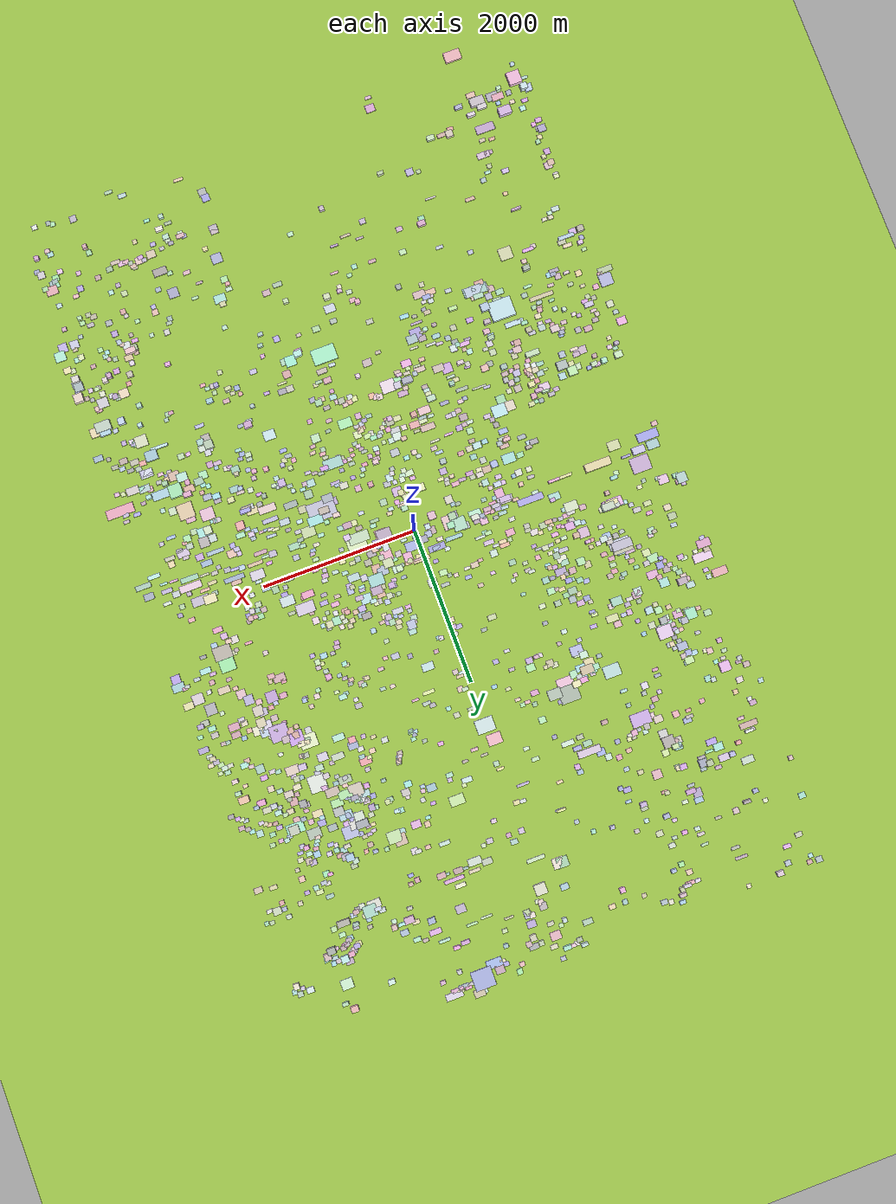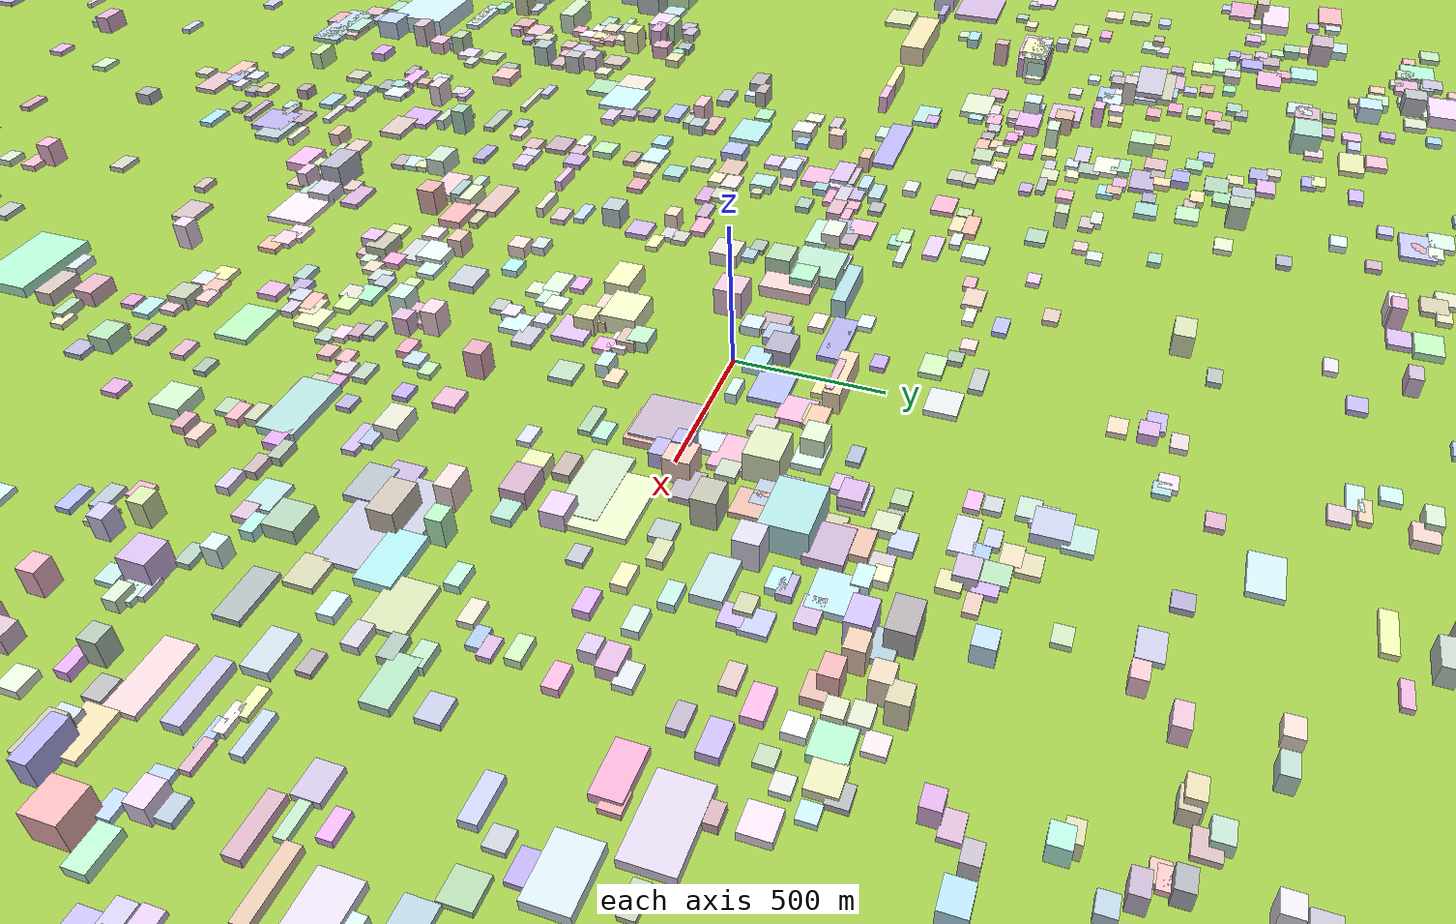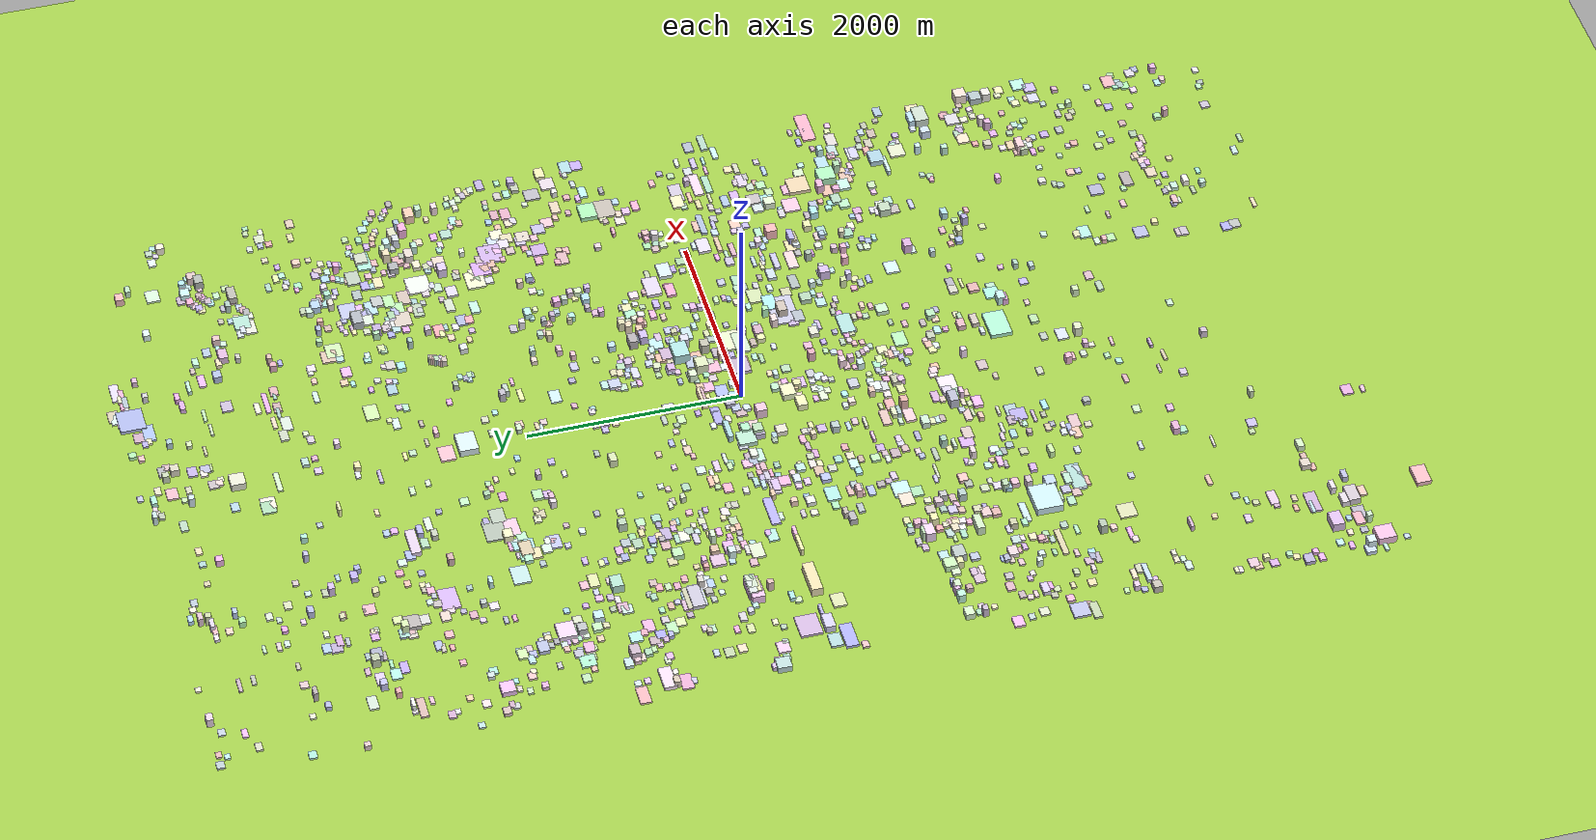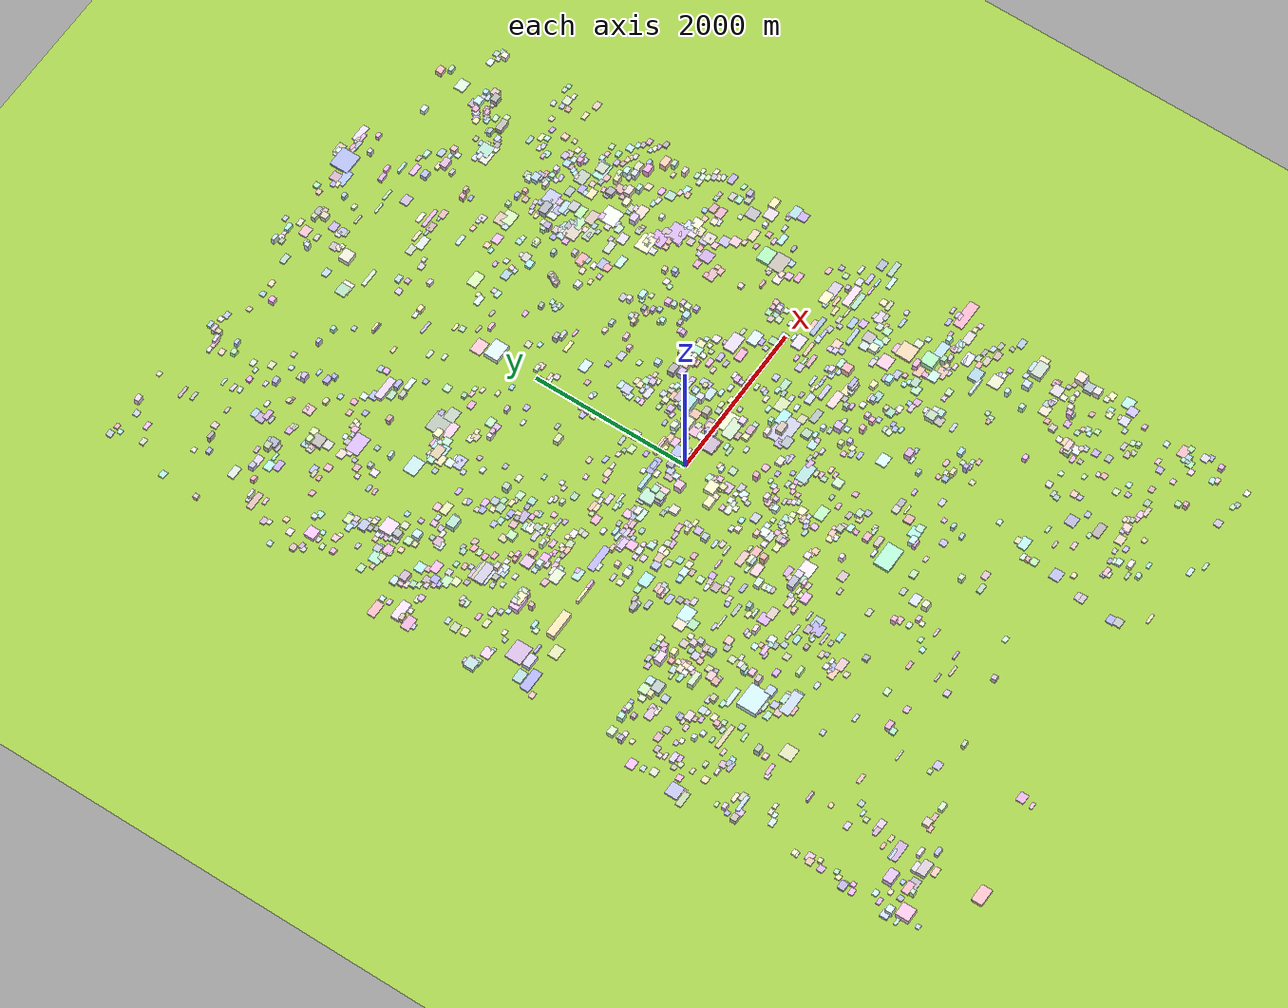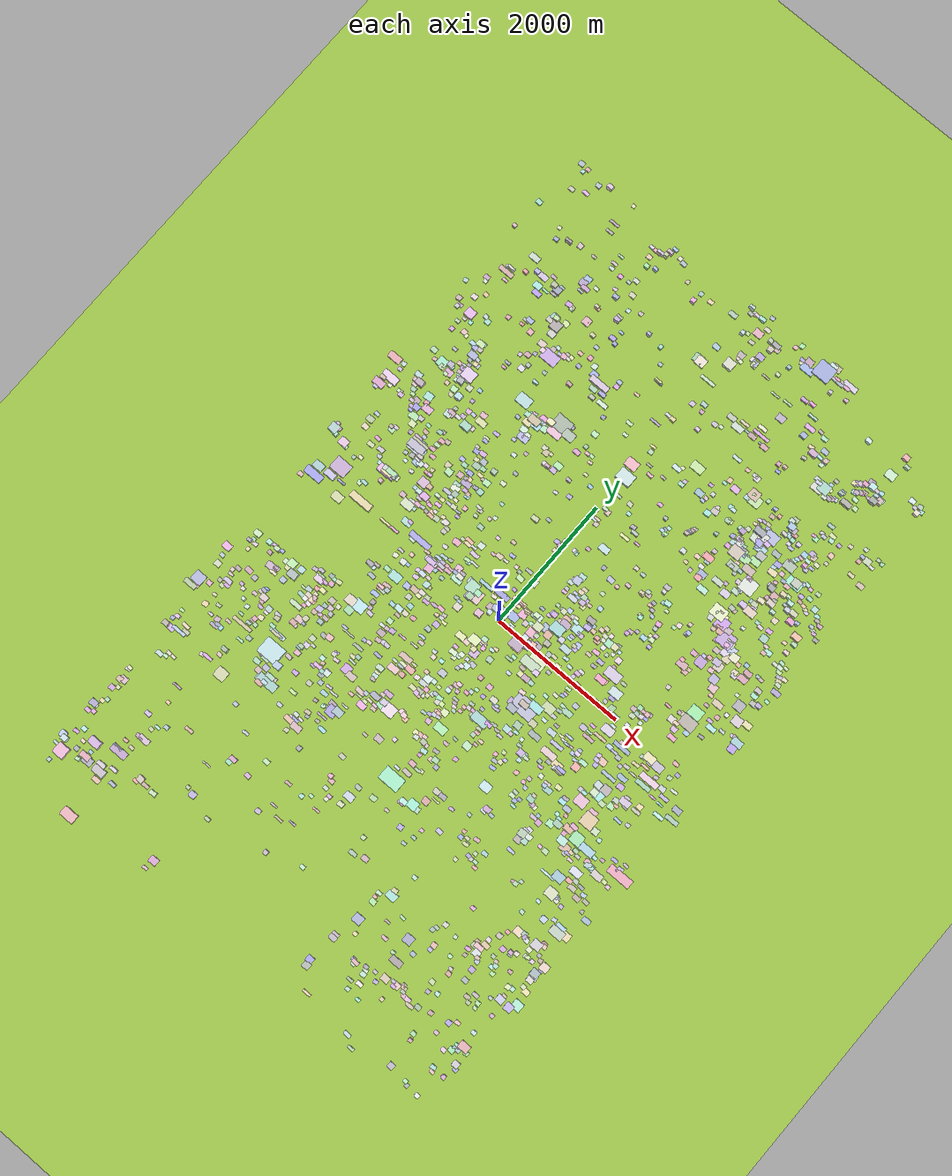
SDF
<sdf version="1.9">
 <world name="city_map">
  <physics name="1ms" type="ignore">
   <max_step_size>0.001</max_step_size>
   <real_time_factor>1.0</real_time_factor>
  </physics>
  <plugin filename="gz-sim-physics-system" name="gz::sim::systems::Physics"/>
  <plugin filename="gz-sim-sensors-system" name="gz::sim::systems::Sensors">
   <render_engine>ogre2</render_engine>
  </plugin>
  <plugin filename="gz-sim-user-commands-system" name="gz::sim::systems::UserCommands"/>
  <plugin filename="gz-sim-scene-broadcaster-system" name="gz::sim::systems::SceneBroadcaster"/>
  <plugin filename="gz-sim-imu-system" name="gz::sim::systems::Imu"/>
  <plugin filename="gz-sim-navsat-system" name="gz::sim::systems::NavSat"/>
  <scene>
   <ambient>0.9 0.9 0.95</ambient>
   <background>0.5 0.7 1.0</background>
   <sky><clouds><speed>12</speed></clouds></sky>
   <shadows>false</shadows>
  </scene>
  <spherical_coordinates>
   <latitude_deg>52.52</latitude_deg>
   <longitude_deg>13.405</longitude_deg>
   <elevation>0</elevation>
   <heading_deg>0</heading_deg>
   <surface_model>EARTH_WGS84</surface_model>
  </spherical_coordinates>
  <light type="directional" name="sun">
   <cast_shadows>false</cast_shadows>
   <pose>0 0 100 0 0 0</pose>
   <diffuse>1.0 0.95 0.8 1</diffuse>
   <specular>1.0 0.95 0.8 1</specular>
   <attenuation>
    <range>2000</range>
    <constant>0.9</constant>
    <linear>0.01</linear>
    <quadratic>0.001</quadratic>
   </attenuation>
   <direction>-0.5 0.1 -0.9</direction>
  </light>
  <model name="ground_plane">
   <static>1</static>
   <link name="link">
    <collision name="collision">
     <geometry><plane><normal>0 0 1</normal><size>11000 11000</size></plane></geometry>
    </collision>
    <visual name="visual">
     <geometry><plane><normal>0 0 1</normal><size>11000 11000</size></plane></geometry>
     <material>
      <ambient>0.551 0.712 0.210 1</ambient>
      <diffuse>0.651 0.812 0.310 1</diffuse>
      <specular>0.1 0.1 0.05 1</specular>
     </material>
    </visual>
   </link>
  </model>
  <model name="building_735441387">
   <static>1</static>
   <pose>990.6046704130122 -649.9140800671806 10.0 0 0 0</pose>
   <link name="link">
    <collision name="collision">
     <geometry><box><size>358.56232333178815 240.7256999998424 20</size></box></geometry>
    </collision>
    <visual name="visual">
     <cast_shadows>false</cast_shadows>
     <geometry><box><size>358.56232333178815 240.7256999998424 20</size></box></geometry>
     <material>
      <ambient>0.714 0.714 0.808 1</ambient>
      <diffuse>0.814 0.814 0.908 1</diffuse>
      <specular>0.244 0.244 0.272 1</specular>
      <emissive>0.01 0.01 0.01 1</emissive>
     </material>
    </visual>
   </link>
  </model>
  <model name="building_326319217">
   <static>1</static>
   <pose>-2018.5786108475324 -2255.2724180324576 36.724767064880695 0 0 0</pose>
   <link name="link">
    <collision name="collision">
     <geometry><box><size>305.3165999998697 248.4310970351964 73.44953412976139</size></box></geometry>
    </collision>
    <visual name="visual">
     <cast_shadows>false</cast_shadows>
     <geometry><box><size>305.3165999998697 248.4310970351964 73.44953412976139</size></box></geometry>
     <material>
      <ambient>0.723 0.847 0.877 1</ambient>
      <diffuse>0.823 0.947 0.977 1</diffuse>
      <specular>0.247 0.284 0.293 1</specular>
      <emissive>0.01 0.01 0.01 1</emissive>
     </material>
    </visual>
   </link>
  </model>
  <model name="building_52394954">
   <static>1</static>
   <pose>284.5301751078761 -2494.1536711187914 19.5 0 0 0</pose>
   <link name="link">
    <collision name="collision">
     <geometry><box><size>310.01507886331234 201.3651000004728 39.0</size></box></geometry>
    </collision>
    <visual name="visual">
     <cast_shadows>false</cast_shadows>
     <geometry><box><size>310.01507886331234 201.3651000004728 39.0</size></box></geometry>
     <material>
      <ambient>0.614 0.891 0.745 1</ambient>
      <diffuse>0.714 0.991 0.845 1</diffuse>
      <specular>0.214 0.297 0.253 1</specular>
      <emissive>0.01 0.01 0.01 1</emissive>
     </material>
    </visual>
   </link>
  </model>
  <model name="building_988046824">
   <static>1</static>
   <pose>1118.620609459311 5408.341910221481 16.624622849178063 0 0 0</pose>
   <link name="link">
    <collision name="collision">
     <geometry><box><size>261.7244489842803 237.71760000018105 33.24924569835613</size></box></geometry>
    </collision>
    <visual name="visual">
     <cast_shadows>false</cast_shadows>
     <geometry><box><size>261.7244489842803 237.71760000018105 33.24924569835613</size></box></geometry>
     <material>
      <ambient>0.604 0.640 0.826 1</ambient>
      <diffuse>0.704 0.740 0.926 1</diffuse>
      <specular>0.211 0.222 0.278 1</specular>
      <emissive>0.01 0.01 0.01 1</emissive>
     </material>
    </visual>
   </link>
  </model>
  <model name="building_58254114">
   <static>1</static>
   <pose>724.2757790682764 -109.13401245718426 10.0 0 0 0</pose>
   <link name="link">
    <collision name="collision">
     <geometry><box><size>246.58649999971516 217.71884028026636 20</size></box></geometry>
    </collision>
    <visual name="visual">
     <cast_shadows>false</cast_shadows>
     <geometry><box><size>246.58649999971516 217.71884028026636 20</size></box></geometry>
     <material>
      <ambient>0.825 0.893 0.718 1</ambient>
      <diffuse>0.925 0.993 0.818 1</diffuse>
      <specular>0.278 0.298 0.246 1</specular>
      <emissive>0.01 0.01 0.01 1</emissive>
     </material>
    </visual>
   </link>
  </model>
  <model name="building_605152010">
   <static>1</static>
   <pose>-1090.0004392026135 2561.046129092921 10.0 0 0 0</pose>
   <link name="link">
    <collision name="collision">
     <geometry><box><size>253.57387508941096 210.33389999959695 20</size></box></geometry>
    </collision>
    <visual name="visual">
     <cast_shadows>false</cast_shadows>
     <geometry><box><size>253.57387508941096 210.33389999959695 20</size></box></geometry>
     <material>
      <ambient>0.630 0.675 0.625 1</ambient>
      <diffuse>0.730 0.775 0.725 1</diffuse>
      <specular>0.219 0.233 0.217 1</specular>
      <emissive>0.01 0.01 0.01 1</emissive>
     </material>
    </visual>
   </link>
  </model>
  <model name="building_25714765">
   <static>1</static>
   <pose>-2955.97510524592 197.91584993413787 12.0 0 0 0</pose>
   <link name="link">
    <collision name="collision">
     <geometry><box><size>246.36152257760227 201.16530000050403 24.0</size></box></geometry>
    </collision>
    <visual name="visual">
     <cast_shadows>false</cast_shadows>
     <geometry><box><size>246.36152257760227 201.16530000050403 24.0</size></box></geometry>
     <material>
      <ambient>0.740 0.639 0.788 1</ambient>
      <diffuse>0.840 0.739 0.888 1</diffuse>
      <specular>0.252 0.222 0.266 1</specular>
      <emissive>0.01 0.01 0.01 1</emissive>
     </material>
    </visual>
   </link>
  </model>
  <model name="building_192952593">
   <static>1</static>
   <pose>2430.9733242705074 1758.978914244576 10.0 0 0 0</pose>
   <link name="link">
    <collision name="collision">
     <geometry><box><size>233.57729999990795 207.46160318499068 20</size></box></geometry>
    </collision>
    <visual name="visual">
     <cast_shadows>false</cast_shadows>
     <geometry><box><size>233.57729999990795 207.46160318499068 20</size></box></geometry>
     <material>
      <ambient>0.739 0.631 0.830 1</ambient>
      <diffuse>0.839 0.731 0.930 1</diffuse>
      <specular>0.252 0.219 0.279 1</specular>
      <emissive>0.01 0.01 0.01 1</emissive>
     </material>
    </visual>
   </link>
  </model>
  <model name="building_914025178">
   <static>1</static>
   <pose>2199.97340372715 2501.3868979094004 10.0 0 0 0</pose>
   <link name="link">
    <collision name="collision">
     <geometry><box><size>218.64249799259497 214.09680000019193 20</size></box></geometry>
    </collision>
    <visual name="visual">
     <cast_shadows>false</cast_shadows>
     <geometry><box><size>218.64249799259497 214.09680000019193 20</size></box></geometry>
     <material>
      <ambient>0.839 0.862 0.839 1</ambient>
      <diffuse>0.939 0.962 0.939 1</diffuse>
      <specular>0.282 0.289 0.282 1</specular>
      <emissive>0.01 0.01 0.01 1</emissive>
     </material>
    </visual>
   </link>
  </model>
  <model name="building_217675906">
   <static>1</static>
   <pose>3355.7046778592357 -1519.3740185500885 10.0 0 0 0</pose>
   <link name="link">
    <collision name="collision">
     <geometry><box><size>358.59774737228724 125.19690000002015 20</size></box></geometry>
    </collision>
    <visual name="visual">
     <cast_shadows>false</cast_shadows>
     <geometry><box><size>358.59774737228724 125.19690000002015 20</size></box></geometry>
     <material>
      <ambient>0.875 0.621 0.707 1</ambient>
      <diffuse>0.975 0.721 0.807 1</diffuse>
      <specular>0.292 0.216 0.242 1</specular>
      <emissive>0.01 0.01 0.01 1</emissive>
     </material>
    </visual>
   </link>
  </model>
  <model name="building_438225687">
   <static>1</static>
   <pose>-1810.3527287770924 3158.581528062216 10.0 0 0 0</pose>
   <link name="link">
    <collision name="collision">
     <geometry><box><size>254.80506294616396 167.55449999971006 20</size></box></geometry>
    </collision>
    <visual name="visual">
     <cast_shadows>false</cast_shadows>
     <geometry><box><size>254.80506294616396 167.55449999971006 20</size></box></geometry>
     <material>
      <ambient>0.753 0.633 0.860 1</ambient>
      <diffuse>0.853 0.733 0.960 1</diffuse>
      <specular>0.256 0.220 0.288 1</specular>
      <emissive>0.01 0.01 0.01 1</emissive>
     </material>
    </visual>
   </link>
  </model>
  <model name="building_968490449">
   <static>1</static>
   <pose>21.204105575061124 2558.1423232748857 34.97503796928707 0 0 0</pose>
   <link name="link">
    <collision name="collision">
     <geometry><box><size>232.54499999967493 177.1502782101934 69.95007593857414</size></box></geometry>
    </collision>
    <visual name="visual">
     <cast_shadows>false</cast_shadows>
     <geometry><box><size>232.54499999967493 177.1502782101934 69.95007593857414</size></box></geometry>
     <material>
      <ambient>0.772 0.850 0.857 1</ambient>
      <diffuse>0.872 0.950 0.957 1</diffuse>
      <specular>0.261 0.285 0.287 1</specular>
      <emissive>0.01 0.01 0.01 1</emissive>
     </material>
    </visual>
   </link>
  </model>
  <model name="building_95256333">
   <static>1</static>
   <pose>2753.8077095743784 586.4312912188058 10.5 0 0 0</pose>
   <link name="link">
    <collision name="collision">
     <geometry><box><size>230.553463907557 171.98340000020096 21.0</size></box></geometry>
    </collision>
    <visual name="visual">
     <cast_shadows>false</cast_shadows>
     <geometry><box><size>230.553463907557 171.98340000020096 21.0</size></box></geometry>
     <material>
      <ambient>0.686 0.656 0.622 1</ambient>
      <diffuse>0.786 0.756 0.722 1</diffuse>
      <specular>0.236 0.227 0.217 1</specular>
      <emissive>0.01 0.01 0.01 1</emissive>
     </material>
    </visual>
   </link>
  </model>
  <model name="building_257993249">
   <static>1</static>
   <pose>2585.8370787539934 -1235.2685367506228 18.0 0 0 0</pose>
   <link name="link">
    <collision name="collision">
     <geometry><box><size>199.75691850875617 197.55780000014767 36.0</size></box></geometry>
    </collision>
    <visual name="visual">
     <cast_shadows>false</cast_shadows>
     <geometry><box><size>199.75691850875617 197.55780000014767 36.0</size></box></geometry>
     <material>
      <ambient>0.842 0.753 0.623 1</ambient>
      <diffuse>0.942 0.853 0.723 1</diffuse>
      <specular>0.283 0.256 0.217 1</specular>
      <emissive>0.01 0.01 0.01 1</emissive>
     </material>
    </visual>
   </link>
  </model>
  <model name="building_61223779">
   <static>1</static>
   <pose>-1791.7270448795166 -2607.590526645111 10.0 0 0 0</pose>
   <link name="link">
    <collision name="collision">
     <geometry><box><size>304.0955999997976 124.93816768113481 20</size></box></geometry>
    </collision>
    <visual name="visual">
     <cast_shadows>false</cast_shadows>
     <geometry><box><size>304.0955999997976 124.93816768113481 20</size></box></geometry>
     <material>
      <ambient>0.623 0.773 0.753 1</ambient>
      <diffuse>0.723 0.873 0.853 1</diffuse>
      <specular>0.217 0.262 0.256 1</specular>
      <emissive>0.01 0.01 0.01 1</emissive>
     </material>
    </visual>
   </link>
  </model>
  <model name="building_915893079">
   <static>1</static>
   <pose>-1811.463014960854 -2606.2506277787925 10.0 0 0 0</pose>
   <link name="link">
    <collision name="collision">
     <geometry><box><size>304.19550000017637 124.85011825813397 20</size></box></geometry>
    </collision>
    <visual name="visual">
     <cast_shadows>false</cast_shadows>
     <geometry><box><size>304.19550000017637 124.85011825813397 20</size></box></geometry>
     <material>
      <ambient>0.704 0.762 0.839 1</ambient>
      <diffuse>0.804 0.862 0.939 1</diffuse>
      <specular>0.241 0.259 0.282 1</specular>
      <emissive>0.01 0.01 0.01 1</emissive>
     </material>
    </visual>
   </link>
  </model>
  <model name="building_987098441">
   <static>1</static>
   <pose>2126.0891498155593 1977.3232361965406 10.0 0 0 0</pose>
   <link name="link">
    <collision name="collision">
     <geometry><box><size>217.82639999960907 174.1131540679795 20</size></box></geometry>
    </collision>
    <visual name="visual">
     <cast_shadows>false</cast_shadows>
     <geometry><box><size>217.82639999960907 174.1131540679795 20</size></box></geometry>
     <material>
      <ambient>0.859 0.899 0.741 1</ambient>
      <diffuse>0.959 0.999 0.841 1</diffuse>
      <specular>0.288 0.300 0.252 1</specular>
      <emissive>0.01 0.01 0.01 1</emissive>
     </material>
    </visual>
   </link>
  </model>
  <model name="building_768414518">
   <static>1</static>
   <pose>675.4798985630688 -168.62658906927803 10.604470796964094 0 0 0</pose>
   <link name="link">
    <collision name="collision">
     <geometry><box><size>265.37880000006453 132.25785919488504 21.208941593928188</size></box></geometry>
    </collision>
    <visual name="visual">
     <cast_shadows>false</cast_shadows>
     <geometry><box><size>265.37880000006453 132.25785919488504 21.208941593928188</size></box></geometry>
     <material>
      <ambient>0.741 0.824 0.715 1</ambient>
      <diffuse>0.841 0.924 0.815 1</diffuse>
      <specular>0.252 0.277 0.245 1</specular>
      <emissive>0.01 0.01 0.01 1</emissive>
     </material>
    </visual>
   </link>
  </model>
  <model name="building_153093208">
   <static>1</static>
   <pose>-2443.2017444397106 20.16748925370061 42.198108445544754 0 0 0</pose>
   <link name="link">
    <collision name="collision">
     <geometry><box><size>340.4903575833751 102.03119999982846 84.39621689108951</size></box></geometry>
    </collision>
    <visual name="visual">
     <cast_shadows>false</cast_shadows>
     <geometry><box><size>340.4903575833751 102.03119999982846 84.39621689108951</size></box></geometry>
     <material>
      <ambient>0.854 0.802 0.627 1</ambient>
      <diffuse>0.954 0.902 0.727 1</diffuse>
      <specular>0.286 0.271 0.218 1</specular>
      <emissive>0.01 0.01 0.01 1</emissive>
     </material>
    </visual>
   </link>
  </model>
  <model name="building_310255113">
   <static>1</static>
   <pose>-461.33310733339897 48.08937970377485 20.81820636374468 0 0 0</pose>
   <link name="link">
    <collision name="collision">
     <geometry><box><size>190.84393840883806 179.67570000018185 41.63641272748936</size></box></geometry>
    </collision>
    <visual name="visual">
     <cast_shadows>false</cast_shadows>
     <geometry><box><size>190.84393840883806 179.67570000018185 41.63641272748936</size></box></geometry>
     <material>
      <ambient>0.865 0.741 0.752 1</ambient>
      <diffuse>0.965 0.841 0.852 1</diffuse>
      <specular>0.289 0.252 0.256 1</specular>
      <emissive>0.01 0.01 0.01 1</emissive>
     </material>
    </visual>
   </link>
  </model>
  <model name="building_465908569">
   <static>1</static>
   <pose>1599.6223753434201 429.1569429327161 16.5 0 0 0</pose>
   <link name="link">
    <collision name="collision">
     <geometry><box><size>237.01606593275582 143.50079999939425 33.0</size></box></geometry>
    </collision>
    <visual name="visual">
     <cast_shadows>false</cast_shadows>
     <geometry><box><size>237.01606593275582 143.50079999939425 33.0</size></box></geometry>
     <material>
      <ambient>0.800 0.760 0.848 1</ambient>
      <diffuse>0.900 0.860 0.948 1</diffuse>
      <specular>0.270 0.258 0.284 1</specular>
      <emissive>0.01 0.01 0.01 1</emissive>
     </material>
    </visual>
   </link>
  </model>
  <model name="building_783578311">
   <static>1</static>
   <pose>367.2659103462045 -73.0825729207034 18.0 0 0 0</pose>
   <link name="link">
    <collision name="collision">
     <geometry><box><size>188.20127816013837 179.67570000018185 36.0</size></box></geometry>
    </collision>
    <visual name="visual">
     <cast_shadows>false</cast_shadows>
     <geometry><box><size>188.20127816013837 179.67570000018185 36.0</size></box></geometry>
     <material>
      <ambient>0.697 0.629 0.719 1</ambient>
      <diffuse>0.797 0.729 0.819 1</diffuse>
      <specular>0.239 0.219 0.246 1</specular>
      <emissive>0.01 0.01 0.01 1</emissive>
     </material>
    </visual>
   </link>
  </model>
  <model name="building_922311697">
   <static>1</static>
   <pose>-1689.259264352267 2481.973242355033 10.0 0 0 0</pose>
   <link name="link">
    <collision name="collision">
     <geometry><box><size>213.8525999997043 157.81866710290294 20</size></box></geometry>
    </collision>
    <visual name="visual">
     <cast_shadows>false</cast_shadows>
     <geometry><box><size>213.8525999997043 157.81866710290294 20</size></box></geometry>
     <material>
      <ambient>0.695 0.823 0.822 1</ambient>
      <diffuse>0.795 0.923 0.922 1</diffuse>
      <specular>0.239 0.277 0.277 1</specular>
      <emissive>0.01 0.01 0.01 1</emissive>
     </material>
    </visual>
   </link>
  </model>
  <model name="building_684449599">
   <static>1</static>
   <pose>-2346.618708589461 1037.980812742068 10.0 0 0 0</pose>
   <link name="link">
    <collision name="collision">
     <geometry><box><size>265.16789999996604 122.58789664311506 20</size></box></geometry>
    </collision>
    <visual name="visual">
     <cast_shadows>false</cast_shadows>
     <geometry><box><size>265.16789999996604 122.58789664311506 20</size></box></geometry>
     <material>
      <ambient>0.762 0.795 0.873 1</ambient>
      <diffuse>0.862 0.895 0.973 1</diffuse>
      <specular>0.259 0.268 0.292 1</specular>
      <emissive>0.01 0.01 0.01 1</emissive>
     </material>
    </visual>
   </link>
  </model>
  <model name="building_885923966">
   <static>1</static>
   <pose>655.6731077006962 -1157.885743891491 15.0 0 0 0</pose>
   <link name="link">
    <collision name="collision">
     <geometry><box><size>245.44319999976238 131.7379915772526 30.0</size></box></geometry>
    </collision>
    <visual name="visual">
     <cast_shadows>false</cast_shadows>
     <geometry><box><size>245.44319999976238 131.7379915772526 30.0</size></box></geometry>
     <material>
      <ambient>0.619 0.794 0.780 1</ambient>
      <diffuse>0.719 0.894 0.880 1</diffuse>
      <specular>0.216 0.268 0.264 1</specular>
      <emissive>0.01 0.01 0.01 1</emissive>
     </material>
    </visual>
   </link>
  </model>
  <model name="building_529718011">
   <static>1</static>
   <pose>2256.605788736338 1886.7054164940168 10.0 0 0 0</pose>
   <link name="link">
    <collision name="collision">
     <geometry><box><size>183.77112242357052 172.79369999941707 20</size></box></geometry>
    </collision>
    <visual name="visual">
     <cast_shadows>false</cast_shadows>
     <geometry><box><size>183.77112242357052 172.79369999941707 20</size></box></geometry>
     <material>
      <ambient>0.770 0.605 0.899 1</ambient>
      <diffuse>0.870 0.705 0.999 1</diffuse>
      <specular>0.261 0.211 0.300 1</specular>
      <emissive>0.01 0.01 0.01 1</emissive>
     </material>
    </visual>
   </link>
  </model>
  <model name="building_936097930">
   <static>1</static>
   <pose>-3167.2719465626096 -110.01832383372351 13.5 0 0 0</pose>
   <link name="link">
    <collision name="collision">
     <geometry><box><size>276.3410278735153 114.80730000006645 27.0</size></box></geometry>
    </collision>
    <visual name="visual">
     <cast_shadows>false</cast_shadows>
     <geometry><box><size>276.3410278735153 114.80730000006645 27.0</size></box></geometry>
     <material>
      <ambient>0.604 0.609 0.884 1</ambient>
      <diffuse>0.704 0.709 0.984 1</diffuse>
      <specular>0.211 0.213 0.295 1</specular>
      <emissive>0.01 0.01 0.01 1</emissive>
     </material>
    </visual>
   </link>
  </model>
  <model name="building_440611747">
   <static>1</static>
   <pose>2021.1025815786031 3198.5522960508947 10.0 0 0 0</pose>
   <link name="link">
    <collision name="collision">
     <geometry><box><size>197.5723558998394 159.24059999956341 20</size></box></geometry>
    </collision>
    <visual name="visual">
     <cast_shadows>false</cast_shadows>
     <geometry><box><size>197.5723558998394 159.24059999956341 20</size></box></geometry>
     <material>
      <ambient>0.681 0.703 0.843 1</ambient>
      <diffuse>0.781 0.803 0.943 1</diffuse>
      <specular>0.234 0.241 0.283 1</specular>
      <emissive>0.01 0.01 0.01 1</emissive>
     </material>
    </visual>
   </link>
  </model>
  <model name="building_645757484">
   <static>1</static>
   <pose>2744.1018351129865 753.98529146079 21.665343699572546 0 0 0</pose>
   <link name="link">
    <collision name="collision">
     <geometry><box><size>193.3620000000147 158.25988112347488 43.33068739914509</size></box></geometry>
    </collision>
    <visual name="visual">
     <cast_shadows>false</cast_shadows>
     <geometry><box><size>193.3620000000147 158.25988112347488 43.33068739914509</size></box></geometry>
     <material>
      <ambient>0.600 0.883 0.637 1</ambient>
      <diffuse>0.700 0.983 0.737 1</diffuse>
      <specular>0.210 0.295 0.221 1</specular>
      <emissive>0.01 0.01 0.01 1</emissive>
     </material>
    </visual>
   </link>
  </model>
  <model name="building_879147786">
   <static>1</static>
   <pose>-2475.6158864132262 2263.349169115743 24.0 0 0 0</pose>
   <link name="link">
    <collision name="collision">
     <geometry><box><size>185.12046100391242 163.76940000043305 48.0</size></box></geometry>
    </collision>
    <visual name="visual">
     <cast_shadows>false</cast_shadows>
     <geometry><box><size>185.12046100391242 163.76940000043305 48.0</size></box></geometry>
     <material>
      <ambient>0.858 0.766 0.887 1</ambient>
      <diffuse>0.958 0.866 0.987 1</diffuse>
      <specular>0.287 0.260 0.296 1</specular>
      <emissive>0.01 0.01 0.01 1</emissive>
     </material>
    </visual>
   </link>
  </model>
  <model name="building_433189715">
   <static>1</static>
   <pose>2639.7296116278594 2919.7608048342804 10.0 0 0 0</pose>
   <link name="link">
    <collision name="collision">
     <geometry><box><size>228.48471252296406 131.73479999991855 20</size></box></geometry>
    </collision>
    <visual name="visual">
     <cast_shadows>false</cast_shadows>
     <geometry><box><size>228.48471252296406 131.73479999991855 20</size></box></geometry>
     <material>
      <ambient>0.618 0.893 0.780 1</ambient>
      <diffuse>0.718 0.993 0.880 1</diffuse>
      <specular>0.215 0.298 0.264 1</specular>
      <emissive>0.01 0.01 0.01 1</emissive>
     </material>
    </visual>
   </link>
  </model>
  <model name="building_296272154">
   <static>1</static>
   <pose>-333.15054182032713 -1835.4500552881868 10.0 0 0 0</pose>
   <link name="link">
    <collision name="collision">
     <geometry><box><size>183.29429999987923 161.93154199717628 20</size></box></geometry>
    </collision>
    <visual name="visual">
     <cast_shadows>false</cast_shadows>
     <geometry><box><size>183.29429999987923 161.93154199717628 20</size></box></geometry>
     <material>
      <ambient>0.889 0.828 0.881 1</ambient>
      <diffuse>0.989 0.928 0.981 1</diffuse>
      <specular>0.297 0.278 0.294 1</specular>
      <emissive>0.01 0.01 0.01 1</emissive>
     </material>
    </visual>
   </link>
  </model>
  <model name="building_296393266">
   <static>1</static>
   <pose>1785.0916881172025 2744.9662166609846 10.0 0 0 0</pose>
   <link name="link">
    <collision name="collision">
     <geometry><box><size>181.3217300226623 163.61400000019444 20</size></box></geometry>
    </collision>
    <visual name="visual">
     <cast_shadows>false</cast_shadows>
     <geometry><box><size>181.3217300226623 163.61400000019444 20</size></box></geometry>
     <material>
      <ambient>0.780 0.733 0.687 1</ambient>
      <diffuse>0.880 0.833 0.787 1</diffuse>
      <specular>0.264 0.250 0.236 1</specular>
      <emissive>0.01 0.01 0.01 1</emissive>
     </material>
    </visual>
   </link>
  </model>
  <model name="building_275146184">
   <static>1</static>
   <pose>-2369.0226320397446 1061.351405011938 21.11276111569614 0 0 0</pose>
   <link name="link">
    <collision name="collision">
     <geometry><box><size>261.10529999981225 113.28957244232905 42.22552223139228</size></box></geometry>
    </collision>
    <visual name="visual">
     <cast_shadows>false</cast_shadows>
     <geometry><box><size>261.10529999981225 113.28957244232905 42.22552223139228</size></box></geometry>
     <material>
      <ambient>0.717 0.703 0.778 1</ambient>
      <diffuse>0.817 0.803 0.878 1</diffuse>
      <specular>0.245 0.241 0.264 1</specular>
      <emissive>0.01 0.01 0.01 1</emissive>
     </material>
    </visual>
   </link>
  </model>
  <model name="building_653500482">
   <static>1</static>
   <pose>-2604.0051835988834 -5582.626435734209 22.200000000000003 0 0 0</pose>
   <link name="link">
    <collision name="collision">
     <geometry><box><size>216.86070000015434 136.2527178387331 44.400000000000006</size></box></geometry>
    </collision>
    <visual name="visual">
     <cast_shadows>false</cast_shadows>
     <geometry><box><size>216.86070000015434 136.2527178387331 44.400000000000006</size></box></geometry>
     <material>
      <ambient>0.874 0.657 0.689 1</ambient>
      <diffuse>0.974 0.757 0.789 1</diffuse>
      <specular>0.292 0.227 0.237 1</specular>
      <emissive>0.01 0.01 0.01 1</emissive>
     </material>
    </visual>
   </link>
  </model>
  <model name="building_704288464">
   <static>1</static>
   <pose>-1536.8891504038045 -1054.3563596227127 10.0 0 0 0</pose>
   <link name="link">
    <collision name="collision">
     <geometry><box><size>185.0161457953972 156.85410000006783 20</size></box></geometry>
    </collision>
    <visual name="visual">
     <cast_shadows>false</cast_shadows>
     <geometry><box><size>185.0161457953972 156.85410000006783 20</size></box></geometry>
     <material>
      <ambient>0.709 0.870 0.898 1</ambient>
      <diffuse>0.809 0.970 0.998 1</diffuse>
      <specular>0.243 0.291 0.300 1</specular>
      <emissive>0.01 0.01 0.01 1</emissive>
     </material>
    </visual>
   </link>
  </model>
  <model name="building_468244094">
   <static>1</static>
   <pose>-2363.789195399912 1106.5859644838113 12.805303139556369 0 0 0</pose>
   <link name="link">
    <collision name="collision">
     <geometry><box><size>260.10629999996837 110.8043881858317 25.610606279112737</size></box></geometry>
    </collision>
    <visual name="visual">
     <cast_shadows>false</cast_shadows>
     <geometry><box><size>260.10629999996837 110.8043881858317 25.610606279112737</size></box></geometry>
     <material>
      <ambient>0.727 0.726 0.623 1</ambient>
      <diffuse>0.827 0.826 0.723 1</diffuse>
      <specular>0.248 0.248 0.217 1</specular>
      <emissive>0.01 0.01 0.01 1</emissive>
     </material>
    </visual>
   </link>
  </model>
  <model name="building_964612802">
   <static>1</static>
   <pose>-1503.8218069606157 133.7510092297601 10.0 0 0 0</pose>
   <link name="link">
    <collision name="collision">
     <geometry><box><size>337.94349394099265 84.9927000002566 20</size></box></geometry>
    </collision>
    <visual name="visual">
     <cast_shadows>false</cast_shadows>
     <geometry><box><size>337.94349394099265 84.9927000002566 20</size></box></geometry>
     <material>
      <ambient>0.644 0.619 0.871 1</ambient>
      <diffuse>0.744 0.719 0.971 1</diffuse>
      <specular>0.223 0.216 0.291 1</specular>
      <emissive>0.01 0.01 0.01 1</emissive>
     </material>
    </visual>
   </link>
  </model>
  <model name="building_520531805">
   <static>1</static>
   <pose>-3240.141640792003 -5026.5202927813725 37.8 0 0 0</pose>
   <link name="link">
    <collision name="collision">
     <geometry><box><size>168.93913088291936 168.6756000001921 75.6</size></box></geometry>
    </collision>
    <visual name="visual">
     <cast_shadows>false</cast_shadows>
     <geometry><box><size>168.93913088291936 168.6756000001921 75.6</size></box></geometry>
     <material>
      <ambient>0.885 0.679 0.810 1</ambient>
      <diffuse>0.985 0.779 0.910 1</diffuse>
      <specular>0.296 0.234 0.273 1</specular>
      <emissive>0.01 0.01 0.01 1</emissive>
     </material>
    </visual>
   </link>
  </model>
  <model name="building_6302690">
   <static>1</static>
   <pose>-3257.278928376998 1552.8562125789 19.992731512019006 0 0 0</pose>
   <link name="link">
    <collision name="collision">
     <geometry><box><size>246.05679329559212 113.74170000023298 39.98546302403801</size></box></geometry>
    </collision>
    <visual name="visual">
     <cast_shadows>false</cast_shadows>
     <geometry><box><size>246.05679329559212 113.74170000023298 39.98546302403801</size></box></geometry>
     <material>
      <ambient>0.890 0.784 0.892 1</ambient>
      <diffuse>0.990 0.884 0.992 1</diffuse>
      <specular>0.297 0.265 0.298 1</specular>
      <emissive>0.01 0.01 0.01 1</emissive>
     </material>
    </visual>
   </link>
  </model>
  <model name="building_830032669">
   <static>1</static>
   <pose>-563.875092208699 111.61572994521934 22.5 0 0 0</pose>
   <link name="link">
    <collision name="collision">
     <geometry><box><size>167.39205939384846 167.0105999996636 45.0</size></box></geometry>
    </collision>
    <visual name="visual">
     <cast_shadows>false</cast_shadows>
     <geometry><box><size>167.39205939384846 167.0105999996636 45.0</size></box></geometry>
     <material>
      <ambient>0.657 0.827 0.734 1</ambient>
      <diffuse>0.757 0.927 0.834 1</diffuse>
      <specular>0.227 0.278 0.250 1</specular>
      <emissive>0.01 0.01 0.01 1</emissive>
     </material>
    </visual>
   </link>
  </model>
  <model name="building_429063418">
   <static>1</static>
   <pose>-1093.9294689881126 2416.256806151669 10.0 0 0 0</pose>
   <link name="link">
    <collision name="collision">
     <geometry><box><size>212.6112206124058 131.37960000049986 20</size></box></geometry>
    </collision>
    <visual name="visual">
     <cast_shadows>false</cast_shadows>
     <geometry><box><size>212.6112206124058 131.37960000049986 20</size></box></geometry>
     <material>
      <ambient>0.891 0.723 0.816 1</ambient>
      <diffuse>0.991 0.823 0.916 1</diffuse>
      <specular>0.297 0.247 0.275 1</specular>
      <emissive>0.01 0.01 0.01 1</emissive>
     </material>
    </visual>
   </link>
  </model>
  <model name="building_275326528">
   <static>1</static>
   <pose>652.0047871783397 411.6720349190558 50.0 0 0 0</pose>
   <link name="link">
    <collision name="collision">
     <geometry><box><size>191.66688077075656 144.67740000052487 100</size></box></geometry>
    </collision>
    <visual name="visual">
     <cast_shadows>false</cast_shadows>
     <geometry><box><size>191.66688077075656 144.67740000052487 100</size></box></geometry>
     <material>
      <ambient>0.613 0.806 0.804 1</ambient>
      <diffuse>0.713 0.906 0.904 1</diffuse>
      <specular>0.214 0.272 0.271 1</specular>
      <emissive>0.01 0.01 0.01 1</emissive>
     </material>
    </visual>
   </link>
  </model>
  <model name="building_904435103">
   <static>1</static>
   <pose>2617.380323141981 -1515.2438643588926 42.0 0 0 0</pose>
   <link name="link">
    <collision name="collision">
     <geometry><box><size>167.0354452371219 164.70179999949863 84.0</size></box></geometry>
    </collision>
    <visual name="visual">
     <cast_shadows>false</cast_shadows>
     <geometry><box><size>167.0354452371219 164.70179999949863 84.0</size></box></geometry>
     <material>
      <ambient>0.607 0.861 0.663 1</ambient>
      <diffuse>0.707 0.961 0.763 1</diffuse>
      <specular>0.212 0.288 0.229 1</specular>
      <emissive>0.01 0.01 0.01 1</emissive>
     </material>
    </visual>
   </link>
  </model>
  <model name="building_222340166">
   <static>1</static>
   <pose>-2326.9395114199333 -2917.620494899928 10.0 0 0 0</pose>
   <link name="link">
    <collision name="collision">
     <geometry><box><size>168.81320425418346 159.40709999993175 20</size></box></geometry>
    </collision>
    <visual name="visual">
     <cast_shadows>false</cast_shadows>
     <geometry><box><size>168.81320425418346 159.40709999993175 20</size></box></geometry>
     <material>
      <ambient>0.785 0.793 0.639 1</ambient>
      <diffuse>0.885 0.893 0.739 1</diffuse>
      <specular>0.265 0.268 0.222 1</specular>
      <emissive>0.01 0.01 0.01 1</emissive>
     </material>
    </visual>
   </link>
  </model>
  <model name="building_847208884">
   <static>1</static>
   <pose>1540.7432542702056 3440.817177242946 10.0 0 0 0</pose>
   <link name="link">
    <collision name="collision">
     <geometry><box><size>176.17920000033394 151.10614218380107 20</size></box></geometry>
    </collision>
    <visual name="visual">
     <cast_shadows>false</cast_shadows>
     <geometry><box><size>176.17920000033394 151.10614218380107 20</size></box></geometry>
     <material>
      <ambient>0.738 0.854 0.643 1</ambient>
      <diffuse>0.838 0.954 0.743 1</diffuse>
      <specular>0.251 0.286 0.223 1</specular>
      <emissive>0.01 0.01 0.01 1</emissive>
     </material>
    </visual>
   </link>
  </model>
  <model name="building_850747745">
   <static>1</static>
   <pose>-1067.149498136121 3306.5745603035307 25.54829295765892 0 0 0</pose>
   <link name="link">
    <collision name="collision">
     <geometry><box><size>296.9958694613478 89.35499999996921 51.09658591531784</size></box></geometry>
    </collision>
    <visual name="visual">
     <cast_shadows>false</cast_shadows>
     <geometry><box><size>296.9958694613478 89.35499999996921 51.09658591531784</size></box></geometry>
     <material>
      <ambient>0.810 0.743 0.834 1</ambient>
      <diffuse>0.910 0.843 0.934 1</diffuse>
      <specular>0.273 0.253 0.280 1</specular>
      <emissive>0.01 0.01 0.01 1</emissive>
     </material>
    </visual>
   </link>
  </model>
  <model name="building_821050579">
   <static>1</static>
   <pose>-2662.0593865212245 -4547.052437178215 10.0 0 0 0</pose>
   <link name="link">
    <collision name="collision">
     <geometry><box><size>244.63290000054627 108.05267966975711 20</size></box></geometry>
    </collision>
    <visual name="visual">
     <cast_shadows>false</cast_shadows>
     <geometry><box><size>244.63290000054627 108.05267966975711 20</size></box></geometry>
     <material>
      <ambient>0.718 0.606 0.764 1</ambient>
      <diffuse>0.818 0.706 0.864 1</diffuse>
      <specular>0.245 0.212 0.259 1</specular>
      <emissive>0.01 0.01 0.01 1</emissive>
     </material>
    </visual>
   </link>
  </model>
  <model name="building_462771809">
   <static>1</static>
   <pose>-3401.673407640126 -2155.0084476344678 12.0 0 0 0</pose>
   <link name="link">
    <collision name="collision">
     <geometry><box><size>166.76640000075338 157.96822884926053 24.0</size></box></geometry>
    </collision>
    <visual name="visual">
     <cast_shadows>false</cast_shadows>
     <geometry><box><size>166.76640000075338 157.96822884926053 24.0</size></box></geometry>
     <material>
      <ambient>0.661 0.674 0.825 1</ambient>
      <diffuse>0.761 0.774 0.925 1</diffuse>
      <specular>0.228 0.232 0.278 1</specular>
      <emissive>0.01 0.01 0.01 1</emissive>
     </material>
    </visual>
   </link>
  </model>
  <model name="building_894255623">
   <static>1</static>
   <pose>2787.432050281861 -115.42725265398414 10.0 0 0 0</pose>
   <link name="link">
    <collision name="collision">
     <geometry><box><size>229.07070000008645 114.98631246060707 20</size></box></geometry>
    </collision>
    <visual name="visual">
     <cast_shadows>false</cast_shadows>
     <geometry><box><size>229.07070000008645 114.98631246060707 20</size></box></geometry>
     <material>
      <ambient>0.742 0.708 0.789 1</ambient>
      <diffuse>0.842 0.808 0.889 1</diffuse>
      <specular>0.253 0.243 0.267 1</specular>
      <emissive>0.01 0.01 0.01 1</emissive>
     </material>
    </visual>
   </link>
  </model>
  <model name="building_691419345">
   <static>1</static>
   <pose>2346.868423731316 -1104.7427232505665 10.0 0 0 0</pose>
   <link name="link">
    <collision name="collision">
     <geometry><box><size>173.26385213700323 151.1597999997747 20</size></box></geometry>
    </collision>
    <visual name="visual">
     <cast_shadows>false</cast_shadows>
     <geometry><box><size>173.26385213700323 151.1597999997747 20</size></box></geometry>
     <material>
      <ambient>0.865 0.714 0.800 1</ambient>
      <diffuse>0.965 0.814 0.900 1</diffuse>
      <specular>0.290 0.244 0.270 1</specular>
      <emissive>0.01 0.01 0.01 1</emissive>
     </material>
    </visual>
   </link>
  </model>
  <model name="building_104849475">
   <static>1</static>
   <pose>-30.34658473190393 2755.004606092411 10.0 0 0 0</pose>
   <link name="link">
    <collision name="collision">
     <geometry><box><size>183.76518512480968 140.95889999966005 20</size></box></geometry>
    </collision>
    <visual name="visual">
     <cast_shadows>false</cast_shadows>
     <geometry><box><size>183.76518512480968 140.95889999966005 20</size></box></geometry>
     <material>
      <ambient>0.898 0.683 0.735 1</ambient>
      <diffuse>0.998 0.783 0.835 1</diffuse>
      <specular>0.299 0.235 0.251 1</specular>
      <emissive>0.01 0.01 0.01 1</emissive>
     </material>
    </visual>
   </link>
  </model>
  <model name="building_927808009">
   <static>1</static>
   <pose>2848.41137279654 -322.03809657924023 10.0 0 0 0</pose>
   <link name="link">
    <collision name="collision">
     <geometry><box><size>285.6253297418155 90.20970000049289 20</size></box></geometry>
    </collision>
    <visual name="visual">
     <cast_shadows>false</cast_shadows>
     <geometry><box><size>285.6253297418155 90.20970000049289 20</size></box></geometry>
     <material>
      <ambient>0.881 0.769 0.850 1</ambient>
      <diffuse>0.981 0.869 0.950 1</diffuse>
      <specular>0.294 0.261 0.285 1</specular>
      <emissive>0.01 0.01 0.01 1</emissive>
     </material>
    </visual>
   </link>
  </model>
  <model name="building_820799062">
   <static>1</static>
   <pose>3198.5259221905694 -2600.2883052691195 38.90549375745029 0 0 0</pose>
   <link name="link">
    <collision name="collision">
     <geometry><box><size>201.4091957852101 126.56220000020113 77.81098751490057</size></box></geometry>
    </collision>
    <visual name="visual">
     <cast_shadows>false</cast_shadows>
     <geometry><box><size>201.4091957852101 126.56220000020113 77.81098751490057</size></box></geometry>
     <material>
      <ambient>0.717 0.777 0.724 1</ambient>
      <diffuse>0.817 0.877 0.824 1</diffuse>
      <specular>0.245 0.263 0.247 1</specular>
      <emissive>0.01 0.01 0.01 1</emissive>
     </material>
    </visual>
   </link>
  </model>
  <model name="building_284266173">
   <static>1</static>
   <pose>2125.572420813941 4172.171751800805 11.58540077558591 0 0 0</pose>
   <link name="link">
    <collision name="collision">
     <geometry><box><size>169.2633467777734 148.97309999945918 23.17080155117182</size></box></geometry>
    </collision>
    <visual name="visual">
     <cast_shadows>false</cast_shadows>
     <geometry><box><size>169.2633467777734 148.97309999945918 23.17080155117182</size></box></geometry>
     <material>
      <ambient>0.629 0.802 0.742 1</ambient>
      <diffuse>0.729 0.902 0.842 1</diffuse>
      <specular>0.219 0.270 0.253 1</specular>
      <emissive>0.01 0.01 0.01 1</emissive>
     </material>
    </visual>
   </link>
  </model>
  <model name="building_614332747">
   <static>1</static>
   <pose>2813.0471255620364 -1540.1445767585428 10.0 0 0 0</pose>
   <link name="link">
    <collision name="collision">
     <geometry><box><size>216.1747394457642 111.54390000057646 20</size></box></geometry>
    </collision>
    <visual name="visual">
     <cast_shadows>false</cast_shadows>
     <geometry><box><size>216.1747394457642 111.54390000057646 20</size></box></geometry>
     <material>
      <ambient>0.644 0.786 0.849 1</ambient>
      <diffuse>0.744 0.886 0.949 1</diffuse>
      <specular>0.223 0.266 0.285 1</specular>
      <emissive>0.01 0.01 0.01 1</emissive>
     </material>
    </visual>
   </link>
  </model>
  <model name="building_385283953">
   <static>1</static>
   <pose>665.1022493785597 3291.2420328187886 10.0 0 0 0</pose>
   <link name="link">
    <collision name="collision">
     <geometry><box><size>189.01028402953102 125.65199999981758 20</size></box></geometry>
    </collision>
    <visual name="visual">
     <cast_shadows>false</cast_shadows>
     <geometry><box><size>189.01028402953102 125.65199999981758 20</size></box></geometry>
     <material>
      <ambient>0.747 0.871 0.620 1</ambient>
      <diffuse>0.847 0.971 0.720 1</diffuse>
      <specular>0.254 0.291 0.216 1</specular>
      <emissive>0.01 0.01 0.01 1</emissive>
     </material>
    </visual>
   </link>
  </model>
  <model name="building_370139241">
   <static>1</static>
   <pose>-2404.8721287720805 550.7768881502016 42.0 0 0 0</pose>
   <link name="link">
    <collision name="collision">
     <geometry><box><size>189.18840000014114 124.50581138076582 84.0</size></box></geometry>
    </collision>
    <visual name="visual">
     <cast_shadows>false</cast_shadows>
     <geometry><box><size>189.18840000014114 124.50581138076582 84.0</size></box></geometry>
     <material>
      <ambient>0.777 0.610 0.803 1</ambient>
      <diffuse>0.877 0.710 0.903 1</diffuse>
      <specular>0.263 0.213 0.271 1</specular>
      <emissive>0.01 0.01 0.01 1</emissive>
     </material>
    </visual>
   </link>
  </model>
  <model name="building_491562029">
   <static>1</static>
   <pose>1239.5995822557716 -455.4280711732934 10.0 0 0 0</pose>
   <link name="link">
    <collision name="collision">
     <geometry><box><size>175.53679087195601 133.9437000004935 20</size></box></geometry>
    </collision>
    <visual name="visual">
     <cast_shadows>false</cast_shadows>
     <geometry><box><size>175.53679087195601 133.9437000004935 20</size></box></geometry>
     <material>
      <ambient>0.748 0.810 0.625 1</ambient>
      <diffuse>0.848 0.910 0.725 1</diffuse>
      <specular>0.254 0.273 0.217 1</specular>
      <emissive>0.01 0.01 0.01 1</emissive>
     </material>
    </visual>
   </link>
  </model>
  <model name="building_554772582">
   <static>1</static>
   <pose>-921.6186555184223 2504.428664548281 10.5 0 0 0</pose>
   <link name="link">
    <collision name="collision">
     <geometry><box><size>171.53940000053325 132.90053230693326 21.0</size></box></geometry>
    </collision>
    <visual name="visual">
     <cast_shadows>false</cast_shadows>
     <geometry><box><size>171.53940000053325 132.90053230693326 21.0</size></box></geometry>
     <material>
      <ambient>0.664 0.719 0.663 1</ambient>
      <diffuse>0.764 0.819 0.763 1</diffuse>
      <specular>0.229 0.246 0.229 1</specular>
      <emissive>0.01 0.01 0.01 1</emissive>
     </material>
    </visual>
   </link>
  </model>
  <model name="building_193322267">
   <static>1</static>
   <pose>2816.7143150049437 -2262.6003828262383 10.5 0 0 0</pose>
   <link name="link">
    <collision name="collision">
     <geometry><box><size>157.74210000019195 144.04531904951838 21.0</size></box></geometry>
    </collision>
    <visual name="visual">
     <cast_shadows>false</cast_shadows>
     <geometry><box><size>157.74210000019195 144.04531904951838 21.0</size></box></geometry>
     <material>
      <ambient>0.811 0.833 0.719 1</ambient>
      <diffuse>0.911 0.933 0.819 1</diffuse>
      <specular>0.273 0.280 0.246 1</specular>
      <emissive>0.01 0.01 0.01 1</emissive>
     </material>
    </visual>
   </link>
  </model>
  <model name="building_857352540">
   <static>1</static>
   <pose>-2476.873180641099 538.8608444544831 42.0 0 0 0</pose>
   <link name="link">
    <collision name="collision">
     <geometry><box><size>187.90114202199183 118.60350000026187 84.0</size></box></geometry>
    </collision>
    <visual name="visual">
     <cast_shadows>false</cast_shadows>
     <geometry><box><size>187.90114202199183 118.60350000026187 84.0</size></box></geometry>
     <material>
      <ambient>0.891 0.700 0.885 1</ambient>
      <diffuse>0.991 0.800 0.985 1</diffuse>
      <specular>0.297 0.240 0.296 1</specular>
      <emissive>0.01 0.01 0.01 1</emissive>
     </material>
    </visual>
   </link>
  </model>
  <model name="building_240721121">
   <static>1</static>
   <pose>2443.9631355852266 3059.673498067618 10.0 0 0 0</pose>
   <link name="link">
    <collision name="collision">
     <geometry><box><size>173.12924048401652 128.52690000028844 20</size></box></geometry>
    </collision>
    <visual name="visual">
     <cast_shadows>false</cast_shadows>
     <geometry><box><size>173.12924048401652 128.52690000028844 20</size></box></geometry>
     <material>
      <ambient>0.659 0.717 0.660 1</ambient>
      <diffuse>0.759 0.817 0.760 1</diffuse>
      <specular>0.228 0.245 0.228 1</specular>
      <emissive>0.01 0.01 0.01 1</emissive>
     </material>
    </visual>
   </link>
  </model>
  <model name="building_186137424">
   <static>1</static>
   <pose>1108.603930111163 -557.994513239113 15.0 0 0 0</pose>
   <link name="link">
    <collision name="collision">
     <geometry><box><size>193.07671922219998 113.29769999977657 30.0</size></box></geometry>
    </collision>
    <visual name="visual">
     <cast_shadows>false</cast_shadows>
     <geometry><box><size>193.07671922219998 113.29769999977657 30.0</size></box></geometry>
     <material>
      <ambient>0.615 0.850 0.848 1</ambient>
      <diffuse>0.715 0.950 0.948 1</diffuse>
      <specular>0.215 0.285 0.285 1</specular>
      <emissive>0.01 0.01 0.01 1</emissive>
     </material>
    </visual>
   </link>
  </model>
  <model name="building_177197993">
   <static>1</static>
   <pose>1779.1059165361296 267.86406099322573 18.0 0 0 0</pose>
   <link name="link">
    <collision name="collision">
     <geometry><box><size>177.7338826786568 122.35529999993844 36.0</size></box></geometry>
    </collision>
    <visual name="visual">
     <cast_shadows>false</cast_shadows>
     <geometry><box><size>177.7338826786568 122.35529999993844 36.0</size></box></geometry>
     <material>
      <ambient>0.772 0.841 0.857 1</ambient>
      <diffuse>0.872 0.941 0.957 1</diffuse>
      <specular>0.262 0.282 0.287 1</specular>
      <emissive>0.01 0.01 0.01 1</emissive>
     </material>
    </visual>
   </link>
  </model>
  <model name="building_479139382">
   <static>1</static>
   <pose>-896.928513505181 -2339.3995182530753 10.0 0 0 0</pose>
   <link name="link">
    <collision name="collision">
     <geometry><box><size>147.8298000002951 146.91289525914297 20</size></box></geometry>
    </collision>
    <visual name="visual">
     <cast_shadows>false</cast_shadows>
     <geometry><box><size>147.8298000002951 146.91289525914297 20</size></box></geometry>
     <material>
      <ambient>0.648 0.606 0.838 1</ambient>
      <diffuse>0.748 0.706 0.938 1</diffuse>
      <specular>0.224 0.212 0.281 1</specular>
      <emissive>0.01 0.01 0.01 1</emissive>
     </material>
    </visual>
   </link>
  </model>
  <model name="building_936792399">
   <static>1</static>
   <pose>1624.5374056204116 -907.7582186121348 10.0 0 0 0</pose>
   <link name="link">
    <collision name="collision">
     <geometry><box><size>225.4965841618569 95.29349999996128 20</size></box></geometry>
    </collision>
    <visual name="visual">
     <cast_shadows>false</cast_shadows>
     <geometry><box><size>225.4965841618569 95.29349999996128 20</size></box></geometry>
     <material>
      <ambient>0.867 0.768 0.782 1</ambient>
      <diffuse>0.967 0.868 0.882 1</diffuse>
      <specular>0.290 0.260 0.265 1</specular>
      <emissive>0.01 0.01 0.01 1</emissive>
     </material>
    </visual>
   </link>
  </model>
  <model name="building_880007655">
   <static>1</static>
   <pose>2471.456011307013 -895.6059847772326 10.0 0 0 0</pose>
   <link name="link">
    <collision name="collision">
     <geometry><box><size>147.3858000006274 145.53099228916525 20</size></box></geometry>
    </collision>
    <visual name="visual">
     <cast_shadows>false</cast_shadows>
     <geometry><box><size>147.3858000006274 145.53099228916525 20</size></box></geometry>
     <material>
      <ambient>0.637 0.877 0.851 1</ambient>
      <diffuse>0.737 0.977 0.951 1</diffuse>
      <specular>0.221 0.293 0.285 1</specular>
      <emissive>0.01 0.01 0.01 1</emissive>
     </material>
    </visual>
   </link>
  </model>
  <model name="building_383699546">
   <static>1</static>
   <pose>927.8993489632977 5284.29664269175 10.0 0 0 0</pose>
   <link name="link">
    <collision name="collision">
     <geometry><box><size>201.5623289126177 106.03830000012238 20</size></box></geometry>
    </collision>
    <visual name="visual">
     <cast_shadows>false</cast_shadows>
     <geometry><box><size>201.5623289126177 106.03830000012238 20</size></box></geometry>
     <material>
      <ambient>0.606 0.689 0.881 1</ambient>
      <diffuse>0.706 0.789 0.981 1</diffuse>
      <specular>0.212 0.237 0.294 1</specular>
      <emissive>0.01 0.01 0.01 1</emissive>
     </material>
    </visual>
   </link>
  </model>
  <model name="building_51997033">
   <static>1</static>
   <pose>336.8500381687066 -1580.2356809911882 10.0 0 0 0</pose>
   <link name="link">
    <collision name="collision">
     <geometry><box><size>177.47789999973662 120.40511027394761 20</size></box></geometry>
    </collision>
    <visual name="visual">
     <cast_shadows>false</cast_shadows>
     <geometry><box><size>177.47789999973662 120.40511027394761 20</size></box></geometry>
     <material>
      <ambient>0.646 0.892 0.667 1</ambient>
      <diffuse>0.746 0.992 0.767 1</diffuse>
      <specular>0.224 0.298 0.230 1</specular>
      <emissive>0.01 0.01 0.01 1</emissive>
     </material>
    </visual>
   </link>
  </model>
  <model name="building_456320515">
   <static>1</static>
   <pose>1477.459520917237 3498.7542710292914 10.0 0 0 0</pose>
   <link name="link">
    <collision name="collision">
     <geometry><box><size>149.31720000032556 142.5058160902983 20</size></box></geometry>
    </collision>
    <visual name="visual">
     <cast_shadows>false</cast_shadows>
     <geometry><box><size>149.31720000032556 142.5058160902983 20</size></box></geometry>
     <material>
      <ambient>0.789 0.693 0.636 1</ambient>
      <diffuse>0.889 0.793 0.736 1</diffuse>
      <specular>0.267 0.238 0.221 1</specular>
      <emissive>0.01 0.01 0.01 1</emissive>
     </material>
    </visual>
   </link>
  </model>
  <model name="building_795796305">
   <static>1</static>
   <pose>-1433.1266343263812 -446.67509960497097 10.0 0 0 0</pose>
   <link name="link">
    <collision name="collision">
     <geometry><box><size>169.64012694968054 124.5752999998544 20</size></box></geometry>
    </collision>
    <visual name="visual">
     <cast_shadows>false</cast_shadows>
     <geometry><box><size>169.64012694968054 124.5752999998544 20</size></box></geometry>
     <material>
      <ambient>0.626 0.841 0.820 1</ambient>
      <diffuse>0.726 0.941 0.920 1</diffuse>
      <specular>0.218 0.282 0.276 1</specular>
      <emissive>0.01 0.01 0.01 1</emissive>
     </material>
    </visual>
   </link>
  </model>
  <model name="building_414276466">
   <static>1</static>
   <pose>2016.3013302944219 -169.8109615755788 15.0 0 0 0</pose>
   <link name="link">
    <collision name="collision">
     <geometry><box><size>178.63973250676304 118.23720000071347 30.0</size></box></geometry>
    </collision>
    <visual name="visual">
     <cast_shadows>false</cast_shadows>
     <geometry><box><size>178.63973250676304 118.23720000071347 30.0</size></box></geometry>
     <material>
      <ambient>0.817 0.791 0.857 1</ambient>
      <diffuse>0.917 0.891 0.957 1</diffuse>
      <specular>0.275 0.267 0.287 1</specular>
      <emissive>0.01 0.01 0.01 1</emissive>
     </material>
    </visual>
   </link>
  </model>
  <model name="building_779046447">
   <static>1</static>
   <pose>-2026.9152677014158 3538.6379115861178 25.387741778258516 0 0 0</pose>
   <link name="link">
    <collision name="collision">
     <geometry><box><size>148.3548526547793 141.791400000713 50.77548355651703</size></box></geometry>
    </collision>
    <visual name="visual">
     <cast_shadows>false</cast_shadows>
     <geometry><box><size>148.3548526547793 141.791400000713 50.77548355651703</size></box></geometry>
     <material>
      <ambient>0.656 0.634 0.631 1</ambient>
      <diffuse>0.756 0.734 0.731 1</diffuse>
      <specular>0.227 0.220 0.219 1</specular>
      <emissive>0.01 0.01 0.01 1</emissive>
     </material>
    </visual>
   </link>
  </model>
  <model name="building_784531629">
   <static>1</static>
   <pose>-1949.281690694979 390.4246612366957 12.0 0 0 0</pose>
   <link name="link">
    <collision name="collision">
     <geometry><box><size>173.37089999985267 118.68830927840376 24.0</size></box></geometry>
    </collision>
    <visual name="visual">
     <cast_shadows>false</cast_shadows>
     <geometry><box><size>173.37089999985267 118.68830927840376 24.0</size></box></geometry>
     <material>
      <ambient>0.800 0.849 0.738 1</ambient>
      <diffuse>0.900 0.949 0.838 1</diffuse>
      <specular>0.270 0.285 0.252 1</specular>
      <emissive>0.01 0.01 0.01 1</emissive>
     </material>
    </visual>
   </link>
  </model>
  <model name="building_314246355">
   <static>1</static>
   <pose>-2685.380747875094 -4904.575528613325 32.400000000000006 0 0 0</pose>
   <link name="link">
    <collision name="collision">
     <geometry><box><size>188.5113000001155 109.05462941880297 64.80000000000001</size></box></geometry>
    </collision>
    <visual name="visual">
     <cast_shadows>false</cast_shadows>
     <geometry><box><size>188.5113000001155 109.05462941880297 64.80000000000001</size></box></geometry>
     <material>
      <ambient>0.743 0.704 0.743 1</ambient>
      <diffuse>0.843 0.804 0.843 1</diffuse>
      <specular>0.253 0.241 0.253 1</specular>
      <emissive>0.01 0.01 0.01 1</emissive>
     </material>
    </visual>
   </link>
  </model>
  <model name="building_369859708">
   <static>1</static>
   <pose>425.964973907894 166.7840503494214 10.0 0 0 0</pose>
   <link name="link">
    <collision name="collision">
     <geometry><box><size>143.72280000041115 141.65052970631882 20</size></box></geometry>
    </collision>
    <visual name="visual">
     <cast_shadows>false</cast_shadows>
     <geometry><box><size>143.72280000041115 141.65052970631882 20</size></box></geometry>
     <material>
      <ambient>0.891 0.661 0.758 1</ambient>
      <diffuse>0.991 0.761 0.858 1</diffuse>
      <specular>0.297 0.228 0.257 1</specular>
      <emissive>0.01 0.01 0.01 1</emissive>
     </material>
    </visual>
   </link>
  </model>
  <model name="building_227003293">
   <static>1</static>
   <pose>2755.3304316372355 -2042.1860076679204 27.24662194095261 0 0 0</pose>
   <link name="link">
    <collision name="collision">
     <geometry><box><size>157.74210000019195 128.0040373553865 54.49324388190522</size></box></geometry>
    </collision>
    <visual name="visual">
     <cast_shadows>false</cast_shadows>
     <geometry><box><size>157.74210000019195 128.0040373553865 54.49324388190522</size></box></geometry>
     <material>
      <ambient>0.605 0.741 0.802 1</ambient>
      <diffuse>0.705 0.841 0.902 1</diffuse>
      <specular>0.212 0.252 0.270 1</specular>
      <emissive>0.01 0.01 0.01 1</emissive>
     </material>
    </visual>
   </link>
  </model>
  <model name="building_663329203">
   <static>1</static>
   <pose>2367.1414692491867 1310.8313619500423 10.0 0 0 0</pose>
   <link name="link">
    <collision name="collision">
     <geometry><box><size>143.24482081875132 140.60370000024136 20</size></box></geometry>
    </collision>
    <visual name="visual">
     <cast_shadows>false</cast_shadows>
     <geometry><box><size>143.24482081875132 140.60370000024136 20</size></box></geometry>
     <material>
      <ambient>0.717 0.600 0.807 1</ambient>
      <diffuse>0.817 0.700 0.907 1</diffuse>
      <specular>0.245 0.210 0.272 1</specular>
      <emissive>0.01 0.01 0.01 1</emissive>
     </material>
    </visual>
   </link>
  </model>
  <model name="building_490344329">
   <static>1</static>
   <pose>87.17408019821043 4648.719850238128 37.43345077462526 0 0 0</pose>
   <link name="link">
    <collision name="collision">
     <geometry><box><size>147.78186803230366 135.96390000044067 74.86690154925051</size></box></geometry>
    </collision>
    <visual name="visual">
     <cast_shadows>false</cast_shadows>
     <geometry><box><size>147.78186803230366 135.96390000044067 74.86690154925051</size></box></geometry>
     <material>
      <ambient>0.820 0.823 0.751 1</ambient>
      <diffuse>0.920 0.923 0.851 1</diffuse>
      <specular>0.276 0.277 0.255 1</specular>
      <emissive>0.01 0.01 0.01 1</emissive>
     </material>
    </visual>
   </link>
  </model>
  <model name="building_85861803">
   <static>1</static>
   <pose>-3391.635046473772 1801.335572656015 10.0 0 0 0</pose>
   <link name="link">
    <collision name="collision">
     <geometry><box><size>196.1031298893377 102.05340000008789 20</size></box></geometry>
    </collision>
    <visual name="visual">
     <cast_shadows>false</cast_shadows>
     <geometry><box><size>196.1031298893377 102.05340000008789 20</size></box></geometry>
     <material>
      <ambient>0.858 0.639 0.666 1</ambient>
      <diffuse>0.958 0.739 0.766 1</diffuse>
      <specular>0.287 0.222 0.230 1</specular>
      <emissive>0.01 0.01 0.01 1</emissive>
     </material>
    </visual>
   </link>
  </model>
  <model name="building_230204631">
   <static>1</static>
   <pose>3121.9798988473017 1195.359845361157 10.0 0 0 0</pose>
   <link name="link">
    <collision name="collision">
     <geometry><box><size>140.40389999948388 140.12168081745273 20</size></box></geometry>
    </collision>
    <visual name="visual">
     <cast_shadows>false</cast_shadows>
     <geometry><box><size>140.40389999948388 140.12168081745273 20</size></box></geometry>
     <material>
      <ambient>0.657 0.647 0.686 1</ambient>
      <diffuse>0.757 0.747 0.786 1</diffuse>
      <specular>0.227 0.224 0.236 1</specular>
      <emissive>0.01 0.01 0.01 1</emissive>
     </material>
    </visual>
   </link>
  </model>
  <model name="building_875252734">
   <static>1</static>
   <pose>-1368.621694239439 2093.9339026299212 10.0 0 0 0</pose>
   <link name="link">
    <collision name="collision">
     <geometry><box><size>161.66039999944815 121.40120152400146 20</size></box></geometry>
    </collision>
    <visual name="visual">
     <cast_shadows>false</cast_shadows>
     <geometry><box><size>161.66039999944815 121.40120152400146 20</size></box></geometry>
     <material>
      <ambient>0.693 0.707 0.875 1</ambient>
      <diffuse>0.793 0.807 0.975 1</diffuse>
      <specular>0.238 0.242 0.293 1</specular>
      <emissive>0.01 0.01 0.01 1</emissive>
     </material>
    </visual>
   </link>
  </model>
  <model name="building_692315423">
   <static>1</static>
   <pose>-230.560864776751 4435.646304822101 10.0 0 0 0</pose>
   <link name="link">
    <collision name="collision">
     <geometry><box><size>145.74300000035834 134.3804650803438 20</size></box></geometry>
    </collision>
    <visual name="visual">
     <cast_shadows>false</cast_shadows>
     <geometry><box><size>145.74300000035834 134.3804650803438 20</size></box></geometry>
     <material>
      <ambient>0.888 0.840 0.798 1</ambient>
      <diffuse>0.988 0.940 0.898 1</diffuse>
      <specular>0.296 0.282 0.269 1</specular>
      <emissive>0.01 0.01 0.01 1</emissive>
     </material>
    </visual>
   </link>
  </model>
  <model name="building_874791513">
   <static>1</static>
   <pose>3230.2686142714574 1021.5660588205621 10.0 0 0 0</pose>
   <link name="link">
    <collision name="collision">
     <geometry><box><size>145.04370000007327 132.77960865367987 20</size></box></geometry>
    </collision>
    <visual name="visual">
     <cast_shadows>false</cast_shadows>
     <geometry><box><size>145.04370000007327 132.77960865367987 20</size></box></geometry>
     <material>
      <ambient>0.814 0.767 0.806 1</ambient>
      <diffuse>0.914 0.867 0.906 1</diffuse>
      <specular>0.274 0.260 0.272 1</specular>
      <emissive>0.01 0.01 0.01 1</emissive>
     </material>
    </visual>
   </link>
  </model>
  <model name="building_658097632">
   <static>1</static>
   <pose>-2724.447426032059 -138.71543440428914 10.0 0 0 0</pose>
   <link name="link">
    <collision name="collision">
     <geometry><box><size>158.05228968827703 121.75590000003211 20</size></box></geometry>
    </collision>
    <visual name="visual">
     <cast_shadows>false</cast_shadows>
     <geometry><box><size>158.05228968827703 121.75590000003211 20</size></box></geometry>
     <material>
      <ambient>0.787 0.812 0.627 1</ambient>
      <diffuse>0.887 0.912 0.727 1</diffuse>
      <specular>0.266 0.274 0.218 1</specular>
      <emissive>0.01 0.01 0.01 1</emissive>
     </material>
    </visual>
   </link>
  </model>
  <model name="building_834223518">
   <static>1</static>
   <pose>1280.9858252648842 -1774.0028959987128 10.0 0 0 0</pose>
   <link name="link">
    <collision name="collision">
     <geometry><box><size>152.26980000012702 126.23402840912682 20</size></box></geometry>
    </collision>
    <visual name="visual">
     <cast_shadows>false</cast_shadows>
     <geometry><box><size>152.26980000012702 126.23402840912682 20</size></box></geometry>
     <material>
      <ambient>0.752 0.861 0.890 1</ambient>
      <diffuse>0.852 0.961 0.990 1</diffuse>
      <specular>0.256 0.288 0.297 1</specular>
      <emissive>0.01 0.01 0.01 1</emissive>
     </material>
    </visual>
   </link>
  </model>
  <model name="building_26879220">
   <static>1</static>
   <pose>2434.777038205377 2245.1851874768613 10.0 0 0 0</pose>
   <link name="link">
    <collision name="collision">
     <geometry><box><size>172.15175727633857 111.17760000023935 20</size></box></geometry>
    </collision>
    <visual name="visual">
     <cast_shadows>false</cast_shadows>
     <geometry><box><size>172.15175727633857 111.17760000023935 20</size></box></geometry>
     <material>
      <ambient>0.846 0.770 0.721 1</ambient>
      <diffuse>0.946 0.870 0.821 1</diffuse>
      <specular>0.284 0.261 0.246 1</specular>
      <emissive>0.01 0.01 0.01 1</emissive>
     </material>
    </visual>
   </link>
  </model>
  <model name="building_929349494">
   <static>1</static>
   <pose>2689.9206396754757 4890.974598503811 10.0 0 0 0</pose>
   <link name="link">
    <collision name="collision">
     <geometry><box><size>151.3818000000029 125.43460191297274 20</size></box></geometry>
    </collision>
    <visual name="visual">
     <cast_shadows>false</cast_shadows>
     <geometry><box><size>151.3818000000029 125.43460191297274 20</size></box></geometry>
     <material>
      <ambient>0.761 0.889 0.770 1</ambient>
      <diffuse>0.861 0.989 0.870 1</diffuse>
      <specular>0.258 0.297 0.261 1</specular>
      <emissive>0.01 0.01 0.01 1</emissive>
     </material>
    </visual>
   </link>
  </model>
  <model name="building_765505133">
   <static>1</static>
   <pose>2065.329270756325 2665.938776166225 10.0 0 0 0</pose>
   <link name="link">
    <collision name="collision">
     <geometry><box><size>174.52529999993516 108.52097290318989 20</size></box></geometry>
    </collision>
    <visual name="visual">
     <cast_shadows>false</cast_shadows>
     <geometry><box><size>174.52529999993516 108.52097290318989 20</size></box></geometry>
     <material>
      <ambient>0.747 0.680 0.644 1</ambient>
      <diffuse>0.847 0.780 0.744 1</diffuse>
      <specular>0.254 0.234 0.223 1</specular>
      <emissive>0.01 0.01 0.01 1</emissive>
     </material>
    </visual>
   </link>
  </model>
  <model name="building_12157176">
   <static>1</static>
   <pose>-1675.0121889436398 -1066.0813592065185 10.0 0 0 0</pose>
   <link name="link">
    <collision name="collision">
     <geometry><box><size>148.0839857845683 126.57330000033085 20</size></box></geometry>
    </collision>
    <visual name="visual">
     <cast_shadows>false</cast_shadows>
     <geometry><box><size>148.0839857845683 126.57330000033085 20</size></box></geometry>
     <material>
      <ambient>0.848 0.803 0.746 1</ambient>
      <diffuse>0.948 0.903 0.846 1</diffuse>
      <specular>0.284 0.271 0.254 1</specular>
      <emissive>0.01 0.01 0.01 1</emissive>
     </material>
    </visual>
   </link>
  </model>
  <model name="building_866045146">
   <static>1</static>
   <pose>-2866.7450912046484 2163.6793318669265 10.0 0 0 0</pose>
   <link name="link">
    <collision name="collision">
     <geometry><box><size>136.9206914513694 136.65209999980732 20</size></box></geometry>
    </collision>
    <visual name="visual">
     <cast_shadows>false</cast_shadows>
     <geometry><box><size>136.9206914513694 136.65209999980732 20</size></box></geometry>
     <material>
      <ambient>0.611 0.873 0.738 1</ambient>
      <diffuse>0.711 0.973 0.838 1</diffuse>
      <specular>0.213 0.292 0.251 1</specular>
      <emissive>0.01 0.01 0.01 1</emissive>
     </material>
    </visual>
   </link>
  </model>
  <model name="building_230809453">
   <static>1</static>
   <pose>-280.9161445829634 4444.754031289215 10.0 0 0 0</pose>
   <link name="link">
    <collision name="collision">
     <geometry><box><size>145.75410000048805 128.29987010282815 20</size></box></geometry>
    </collision>
    <visual name="visual">
     <cast_shadows>false</cast_shadows>
     <geometry><box><size>145.75410000048805 128.29987010282815 20</size></box></geometry>
     <material>
      <ambient>0.614 0.778 0.646 1</ambient>
      <diffuse>0.714 0.878 0.746 1</diffuse>
      <specular>0.214 0.264 0.224 1</specular>
      <emissive>0.01 0.01 0.01 1</emissive>
     </material>
    </visual>
   </link>
  </model>
  <model name="building_561598546">
   <static>1</static>
   <pose>-3331.290340237867 1400.045698743589 10.0 0 0 0</pose>
   <link name="link">
    <collision name="collision">
     <geometry><box><size>175.08543400550755 106.42679999993021 20</size></box></geometry>
    </collision>
    <visual name="visual">
     <cast_shadows>false</cast_shadows>
     <geometry><box><size>175.08543400550755 106.42679999993021 20</size></box></geometry>
     <material>
      <ambient>0.826 0.607 0.755 1</ambient>
      <diffuse>0.926 0.707 0.855 1</diffuse>
      <specular>0.278 0.212 0.256 1</specular>
      <emissive>0.01 0.01 0.01 1</emissive>
     </material>
    </visual>
   </link>
  </model>
  <model name="building_233373308">
   <static>1</static>
   <pose>2006.5125984201939 2987.8699998156476 10.0 0 0 0</pose>
   <link name="link">
    <collision name="collision">
     <geometry><box><size>171.99449999954197 108.00716915777797 20</size></box></geometry>
    </collision>
    <visual name="visual">
     <cast_shadows>false</cast_shadows>
     <geometry><box><size>171.99449999954197 108.00716915777797 20</size></box></geometry>
     <material>
      <ambient>0.661 0.802 0.843 1</ambient>
      <diffuse>0.761 0.902 0.943 1</diffuse>
      <specular>0.228 0.270 0.283 1</specular>
      <emissive>0.01 0.01 0.01 1</emissive>
     </material>
    </visual>
   </link>
  </model>
  <model name="building_67063489">
   <static>1</static>
   <pose>1925.413212388208 2746.544340099857 10.0 0 0 0</pose>
   <link name="link">
    <collision name="collision">
     <geometry><box><size>172.04999999940185 107.49294339276533 20</size></box></geometry>
    </collision>
    <visual name="visual">
     <cast_shadows>false</cast_shadows>
     <geometry><box><size>172.04999999940185 107.49294339276533 20</size></box></geometry>
     <material>
      <ambient>0.661 0.862 0.635 1</ambient>
      <diffuse>0.761 0.962 0.735 1</diffuse>
      <specular>0.228 0.289 0.221 1</specular>
      <emissive>0.01 0.01 0.01 1</emissive>
     </material>
    </visual>
   </link>
  </model>
  <model name="building_877271874">
   <static>1</static>
   <pose>-2974.4919341141454 -4660.538683888396 42.900000000000006 0 0 0</pose>
   <link name="link">
    <collision name="collision">
     <geometry><box><size>167.13270000030178 110.57020615283798 85.80000000000001</size></box></geometry>
    </collision>
    <visual name="visual">
     <cast_shadows>false</cast_shadows>
     <geometry><box><size>167.13270000030178 110.57020615283798 85.80000000000001</size></box></geometry>
     <material>
      <ambient>0.783 0.664 0.839 1</ambient>
      <diffuse>0.883 0.764 0.939 1</diffuse>
      <specular>0.265 0.229 0.282 1</specular>
      <emissive>0.01 0.01 0.01 1</emissive>
     </material>
    </visual>
   </link>
  </model>
  <model name="building_831326746">
   <static>1</static>
   <pose>-85.62859501817226 -405.5844760689767 33.0 0 0 0</pose>
   <link name="link">
    <collision name="collision">
     <geometry><box><size>147.73989317804788 124.98599999992166 66.0</size></box></geometry>
    </collision>
    <visual name="visual">
     <cast_shadows>false</cast_shadows>
     <geometry><box><size>147.73989317804788 124.98599999992166 66.0</size></box></geometry>
     <material>
      <ambient>0.852 0.898 0.696 1</ambient>
      <diffuse>0.952 0.998 0.796 1</diffuse>
      <specular>0.286 0.299 0.239 1</specular>
      <emissive>0.01 0.01 0.01 1</emissive>
     </material>
    </visual>
   </link>
  </model>
  <model name="building_309172138">
   <static>1</static>
   <pose>708.4611220423703 -2568.383896521741 10.0 0 0 0</pose>
   <link name="link">
    <collision name="collision">
     <geometry><box><size>138.71670000027336 132.7891002994646 20</size></box></geometry>
    </collision>
    <visual name="visual">
     <cast_shadows>false</cast_shadows>
     <geometry><box><size>138.71670000027336 132.7891002994646 20</size></box></geometry>
     <material>
      <ambient>0.604 0.898 0.798 1</ambient>
      <diffuse>0.704 0.998 0.898 1</diffuse>
      <specular>0.211 0.299 0.269 1</specular>
      <emissive>0.01 0.01 0.01 1</emissive>
     </material>
    </visual>
   </link>
  </model>
  <model name="building_58508939">
   <static>1</static>
   <pose>-1403.71616891745 2359.1274486803854 22.5 0 0 0</pose>
   <link name="link">
    <collision name="collision">
     <geometry><box><size>166.97730000006317 109.72997055668385 45.0</size></box></geometry>
    </collision>
    <visual name="visual">
     <cast_shadows>false</cast_shadows>
     <geometry><box><size>166.97730000006317 109.72997055668385 45.0</size></box></geometry>
     <material>
      <ambient>0.776 0.714 0.605 1</ambient>
      <diffuse>0.876 0.814 0.705 1</diffuse>
      <specular>0.263 0.244 0.212 1</specular>
      <emissive>0.01 0.01 0.01 1</emissive>
     </material>
    </visual>
   </link>
  </model>
  <model name="building_515084542">
   <static>1</static>
   <pose>1516.5815780573898 5474.953385485059 10.0 0 0 0</pose>
   <link name="link">
    <collision name="collision">
     <geometry><box><size>220.8233999999294 82.75419643831687 20</size></box></geometry>
    </collision>
    <visual name="visual">
     <cast_shadows>false</cast_shadows>
     <geometry><box><size>220.8233999999294 82.75419643831687 20</size></box></geometry>
     <material>
      <ambient>0.816 0.785 0.867 1</ambient>
      <diffuse>0.916 0.885 0.967 1</diffuse>
      <specular>0.275 0.265 0.290 1</specular>
      <emissive>0.01 0.01 0.01 1</emissive>
     </material>
    </visual>
   </link>
  </model>
  <model name="building_656227067">
   <static>1</static>
   <pose>2668.818583720853 -94.43363346168856 10.5 0 0 0</pose>
   <link name="link">
    <collision name="collision">
     <geometry><box><size>161.17200000005028 111.9795982787374 21.0</size></box></geometry>
    </collision>
    <visual name="visual">
     <cast_shadows>false</cast_shadows>
     <geometry><box><size>161.17200000005028 111.9795982787374 21.0</size></box></geometry>
     <material>
      <ambient>0.886 0.853 0.690 1</ambient>
      <diffuse>0.986 0.953 0.790 1</diffuse>
      <specular>0.296 0.286 0.237 1</specular>
      <emissive>0.01 0.01 0.01 1</emissive>
     </material>
    </visual>
   </link>
  </model>
  <model name="building_650503282">
   <static>1</static>
   <pose>-197.70097903242996 289.0582878527943 10.0 0 0 0</pose>
   <link name="link">
    <collision name="collision">
     <geometry><box><size>218.599247450957 80.96340000049196 20</size></box></geometry>
    </collision>
    <visual name="visual">
     <cast_shadows>false</cast_shadows>
     <geometry><box><size>218.599247450957 80.96340000049196 20</size></box></geometry>
     <material>
      <ambient>0.615 0.602 0.835 1</ambient>
      <diffuse>0.715 0.702 0.935 1</diffuse>
      <specular>0.214 0.211 0.281 1</specular>
      <emissive>0.01 0.01 0.01 1</emissive>
     </material>
    </visual>
   </link>
  </model>
  <model name="building_988642200">
   <static>1</static>
   <pose>-1204.4342931998065 25.123955632968954 10.0 0 0 0</pose>
   <link name="link">
    <collision name="collision">
     <geometry><box><size>200.12497261075552 88.189499999757 20</size></box></geometry>
    </collision>
    <visual name="visual">
     <cast_shadows>false</cast_shadows>
     <geometry><box><size>200.12497261075552 88.189499999757 20</size></box></geometry>
     <material>
      <ambient>0.815 0.778 0.862 1</ambient>
      <diffuse>0.915 0.878 0.962 1</diffuse>
      <specular>0.274 0.264 0.289 1</specular>
      <emissive>0.01 0.01 0.01 1</emissive>
     </material>
    </visual>
   </link>
  </model>
  <model name="building_702100110">
   <static>1</static>
   <pose>2053.364790413407 4109.723367642992 10.0 0 0 0</pose>
   <link name="link">
    <collision name="collision">
     <geometry><box><size>171.38454744872334 102.76379999971397 20</size></box></geometry>
    </collision>
    <visual name="visual">
     <cast_shadows>false</cast_shadows>
     <geometry><box><size>171.38454744872334 102.76379999971397 20</size></box></geometry>
     <material>
      <ambient>0.819 0.823 0.786 1</ambient>
      <diffuse>0.919 0.923 0.886 1</diffuse>
      <specular>0.276 0.277 0.266 1</specular>
      <emissive>0.01 0.01 0.01 1</emissive>
     </material>
    </visual>
   </link>
  </model>
  <model name="building_514474622">
   <static>1</static>
   <pose>3413.9467336202656 -3635.5864320987785 10.0 0 0 0</pose>
   <link name="link">
    <collision name="collision">
     <geometry><box><size>138.53909999977532 127.05261490969195 20</size></box></geometry>
    </collision>
    <visual name="visual">
     <cast_shadows>false</cast_shadows>
     <geometry><box><size>138.53909999977532 127.05261490969195 20</size></box></geometry>
     <material>
      <ambient>0.656 0.887 0.801 1</ambient>
      <diffuse>0.756 0.987 0.901 1</diffuse>
      <specular>0.227 0.296 0.270 1</specular>
      <emissive>0.01 0.01 0.01 1</emissive>
     </material>
    </visual>
   </link>
  </model>
  <model name="building_360172534">
   <static>1</static>
   <pose>3104.6213638431473 -2890.511129726861 10.5 0 0 0</pose>
   <link name="link">
    <collision name="collision">
     <geometry><box><size>139.130528034913 125.49659999957896 21.0</size></box></geometry>
    </collision>
    <visual name="visual">
     <cast_shadows>false</cast_shadows>
     <geometry><box><size>139.130528034913 125.49659999957896 21.0</size></box></geometry>
     <material>
      <ambient>0.779 0.764 0.801 1</ambient>
      <diffuse>0.879 0.864 0.901 1</diffuse>
      <specular>0.264 0.259 0.270 1</specular>
      <emissive>0.01 0.01 0.01 1</emissive>
     </material>
    </visual>
   </link>
  </model>
  <model name="building_30557907">
   <static>1</static>
   <pose>2889.8832503011313 -1850.268535347273 10.0 0 0 0</pose>
   <link name="link">
    <collision name="collision">
     <geometry><box><size>166.2780000005668 104.82366958232092 20</size></box></geometry>
    </collision>
    <visual name="visual">
     <cast_shadows>false</cast_shadows>
     <geometry><box><size>166.2780000005668 104.82366958232092 20</size></box></geometry>
     <material>
      <ambient>0.816 0.836 0.898 1</ambient>
      <diffuse>0.916 0.936 0.998 1</diffuse>
      <specular>0.275 0.281 0.299 1</specular>
      <emissive>0.01 0.01 0.01 1</emissive>
     </material>
    </visual>
   </link>
  </model>
  <model name="building_3074644">
   <static>1</static>
   <pose>1866.088147392062 -4229.071200356766 13.5 0 0 0</pose>
   <link name="link">
    <collision name="collision">
     <geometry><box><size>180.88419674145865 96.12600000022553 27.0</size></box></geometry>
    </collision>
    <visual name="visual">
     <cast_shadows>false</cast_shadows>
     <geometry><box><size>180.88419674145865 96.12600000022553 27.0</size></box></geometry>
     <material>
      <ambient>0.628 0.601 0.607 1</ambient>
      <diffuse>0.728 0.701 0.707 1</diffuse>
      <specular>0.218 0.210 0.212 1</specular>
      <emissive>0.01 0.01 0.01 1</emissive>
     </material>
    </visual>
   </link>
  </model>
  <model name="building_381157944">
   <static>1</static>
   <pose>403.02130046156265 -113.82951725773187 13.5 0 0 0</pose>
   <link name="link">
    <collision name="collision">
     <geometry><box><size>146.7176547548775 118.1817000000649 27.0</size></box></geometry>
    </collision>
    <visual name="visual">
     <cast_shadows>false</cast_shadows>
     <geometry><box><size>146.7176547548775 118.1817000000649 27.0</size></box></geometry>
     <material>
      <ambient>0.820 0.648 0.605 1</ambient>
      <diffuse>0.920 0.748 0.705 1</diffuse>
      <specular>0.276 0.224 0.212 1</specular>
      <emissive>0.01 0.01 0.01 1</emissive>
     </material>
    </visual>
   </link>
  </model>
  <model name="building_479301349">
   <static>1</static>
   <pose>1135.572943275845 -4140.6855739843895 10.0 0 0 0</pose>
   <link name="link">
    <collision name="collision">
     <geometry><box><size>137.7940669771865 125.66309999994729 20</size></box></geometry>
    </collision>
    <visual name="visual">
     <cast_shadows>false</cast_shadows>
     <geometry><box><size>137.7940669771865 125.66309999994729 20</size></box></geometry>
     <material>
      <ambient>0.638 0.654 0.805 1</ambient>
      <diffuse>0.738 0.754 0.905 1</diffuse>
      <specular>0.221 0.226 0.272 1</specular>
      <emissive>0.01 0.01 0.01 1</emissive>
     </material>
    </visual>
   </link>
  </model>
  <model name="building_344655658">
   <static>1</static>
   <pose>-3015.9660182557045 2918.9910726629623 27.0 0 0 0</pose>
   <link name="link">
    <collision name="collision">
     <geometry><box><size>134.49679604138012 128.68229999973835 54.0</size></box></geometry>
    </collision>
    <visual name="visual">
     <cast_shadows>false</cast_shadows>
     <geometry><box><size>134.49679604138012 128.68229999973835 54.0</size></box></geometry>
     <material>
      <ambient>0.863 0.682 0.879 1</ambient>
      <diffuse>0.963 0.782 0.979 1</diffuse>
      <specular>0.289 0.235 0.294 1</specular>
      <emissive>0.01 0.01 0.01 1</emissive>
     </material>
    </visual>
   </link>
  </model>
  <model name="building_260960238">
   <static>1</static>
   <pose>-3191.1818645084663 18.053330303760433 12.0 0 0 0</pose>
   <link name="link">
    <collision name="collision">
     <geometry><box><size>155.26425306637756 111.44399999940902 24.0</size></box></geometry>
    </collision>
    <visual name="visual">
     <cast_shadows>false</cast_shadows>
     <geometry><box><size>155.26425306637756 111.44399999940902 24.0</size></box></geometry>
     <material>
      <ambient>0.632 0.765 0.780 1</ambient>
      <diffuse>0.732 0.865 0.880 1</diffuse>
      <specular>0.220 0.260 0.264 1</specular>
      <emissive>0.01 0.01 0.01 1</emissive>
     </material>
    </visual>
   </link>
  </model>
  <model name="building_318686537">
   <static>1</static>
   <pose>-1979.383314808058 755.0847811302957 14.463169972019635 0 0 0</pose>
   <link name="link">
    <collision name="collision">
     <geometry><box><size>134.73180000023888 127.8774460867967 28.92633994403927</size></box></geometry>
    </collision>
    <visual name="visual">
     <cast_shadows>false</cast_shadows>
     <geometry><box><size>134.73180000023888 127.8774460867967 28.92633994403927</size></box></geometry>
     <material>
      <ambient>0.806 0.686 0.802 1</ambient>
      <diffuse>0.906 0.786 0.902 1</diffuse>
      <specular>0.272 0.236 0.271 1</specular>
      <emissive>0.01 0.01 0.01 1</emissive>
     </material>
    </visual>
   </link>
  </model>
  <model name="building_575676335">
   <static>1</static>
   <pose>852.4566760520293 584.0225110146148 13.5 0 0 0</pose>
   <link name="link">
    <collision name="collision">
     <geometry><box><size>140.05822836040645 121.64490000031236 27.0</size></box></geometry>
    </collision>
    <visual name="visual">
     <cast_shadows>false</cast_shadows>
     <geometry><box><size>140.05822836040645 121.64490000031236 27.0</size></box></geometry>
     <material>
      <ambient>0.686 0.844 0.868 1</ambient>
      <diffuse>0.786 0.944 0.968 1</diffuse>
      <specular>0.236 0.283 0.290 1</specular>
      <emissive>0.01 0.01 0.01 1</emissive>
     </material>
    </visual>
   </link>
  </model>
  <model name="building_70846053">
   <static>1</static>
   <pose>1272.5089468673098 -3634.069560009593 10.0 0 0 0</pose>
   <link name="link">
    <collision name="collision">
     <geometry><box><size>153.5574000001887 110.51284408469505 20</size></box></geometry>
    </collision>
    <visual name="visual">
     <cast_shadows>false</cast_shadows>
     <geometry><box><size>153.5574000001887 110.51284408469505 20</size></box></geometry>
     <material>
      <ambient>0.636 0.846 0.811 1</ambient>
      <diffuse>0.736 0.946 0.911 1</diffuse>
      <specular>0.221 0.284 0.273 1</specular>
      <emissive>0.01 0.01 0.01 1</emissive>
     </material>
    </visual>
   </link>
  </model>
  <model name="building_512868299">
   <static>1</static>
   <pose>1939.9955426923825 3128.0776465128956 10.0 0 0 0</pose>
   <link name="link">
    <collision name="collision">
     <geometry><box><size>136.85959593170364 123.98700000007778 20</size></box></geometry>
    </collision>
    <visual name="visual">
     <cast_shadows>false</cast_shadows>
     <geometry><box><size>136.85959593170364 123.98700000007778 20</size></box></geometry>
     <material>
      <ambient>0.826 0.826 0.806 1</ambient>
      <diffuse>0.926 0.926 0.906 1</diffuse>
      <specular>0.278 0.278 0.272 1</specular>
      <emissive>0.01 0.01 0.01 1</emissive>
     </material>
    </visual>
   </link>
  </model>
  <model name="building_984583574">
   <static>1</static>
   <pose>1801.59662404086 -3913.0857329520377 10.0 0 0 0</pose>
   <link name="link">
    <collision name="collision">
     <geometry><box><size>133.23845798524687 126.58439999967186 20</size></box></geometry>
    </collision>
    <visual name="visual">
     <cast_shadows>false</cast_shadows>
     <geometry><box><size>133.23845798524687 126.58439999967186 20</size></box></geometry>
     <material>
      <ambient>0.619 0.622 0.746 1</ambient>
      <diffuse>0.719 0.722 0.846 1</diffuse>
      <specular>0.216 0.217 0.254 1</specular>
      <emissive>0.01 0.01 0.01 1</emissive>
     </material>
    </visual>
   </link>
  </model>
  <model name="building_490658657">
   <static>1</static>
   <pose>3232.6246014646044 -4475.49496386256 10.0 0 0 0</pose>
   <link name="link">
    <collision name="collision">
     <geometry><box><size>149.03969999944877 113.08049592594506 20</size></box></geometry>
    </collision>
    <visual name="visual">
     <cast_shadows>false</cast_shadows>
     <geometry><box><size>149.03969999944877 113.08049592594506 20</size></box></geometry>
     <material>
      <ambient>0.848 0.636 0.672 1</ambient>
      <diffuse>0.948 0.736 0.772 1</diffuse>
      <specular>0.284 0.221 0.232 1</specular>
      <emissive>0.01 0.01 0.01 1</emissive>
     </material>
    </visual>
   </link>
  </model>
  <model name="building_826001463">
   <static>1</static>
   <pose>103.41681634318033 165.5859250132687 10.0 0 0 0</pose>
   <link name="link">
    <collision name="collision">
     <geometry><box><size>141.90713042939495 118.44810000002326 20</size></box></geometry>
    </collision>
    <visual name="visual">
     <cast_shadows>false</cast_shadows>
     <geometry><box><size>141.90713042939495 118.44810000002326 20</size></box></geometry>
     <material>
      <ambient>0.629 0.673 0.862 1</ambient>
      <diffuse>0.729 0.773 0.962 1</diffuse>
      <specular>0.219 0.232 0.289 1</specular>
      <emissive>0.01 0.01 0.01 1</emissive>
     </material>
    </visual>
   </link>
  </model>
  <model name="building_623820183">
   <static>1</static>
   <pose>-3370.3349665781247 538.3425926976373 30.377859926171734 0 0 0</pose>
   <link name="link">
    <collision name="collision">
     <geometry><box><size>129.68130000037092 128.77458538619112 60.75571985234347</size></box></geometry>
    </collision>
    <visual name="visual">
     <cast_shadows>false</cast_shadows>
     <geometry><box><size>129.68130000037092 128.77458538619112 60.75571985234347</size></box></geometry>
     <material>
      <ambient>0.668 0.778 0.773 1</ambient>
      <diffuse>0.768 0.878 0.873 1</diffuse>
      <specular>0.230 0.263 0.262 1</specular>
      <emissive>0.01 0.01 0.01 1</emissive>
     </material>
    </visual>
   </link>
  </model>
  <model name="building_73124910">
   <static>1</static>
   <pose>-2895.2679757678984 -4904.899736270048 10.0 0 0 0</pose>
   <link name="link">
    <collision name="collision">
     <geometry><box><size>152.08110000028796 109.29157100156543 20</size></box></geometry>
    </collision>
    <visual name="visual">
     <cast_shadows>false</cast_shadows>
     <geometry><box><size>152.08110000028796 109.29157100156543 20</size></box></geometry>
     <material>
      <ambient>0.652 0.640 0.706 1</ambient>
      <diffuse>0.752 0.740 0.806 1</diffuse>
      <specular>0.226 0.222 0.242 1</specular>
      <emissive>0.01 0.01 0.01 1</emissive>
     </material>
    </visual>
   </link>
  </model>
  <model name="building_419141716">
   <static>1</static>
   <pose>536.9833360427868 324.3269374406973 10.0 0 0 0</pose>
   <link name="link">
    <collision name="collision">
     <geometry><box><size>137.9789111094327 120.35729999946199 20</size></box></geometry>
    </collision>
    <visual name="visual">
     <cast_shadows>false</cast_shadows>
     <geometry><box><size>137.9789111094327 120.35729999946199 20</size></box></geometry>
     <material>
      <ambient>0.661 0.711 0.799 1</ambient>
      <diffuse>0.761 0.811 0.899 1</diffuse>
      <specular>0.228 0.243 0.270 1</specular>
      <emissive>0.01 0.01 0.01 1</emissive>
     </material>
    </visual>
   </link>
  </model>
  <model name="building_916570809">
   <static>1</static>
   <pose>-2763.185209973653 -1413.792203624471 10.0 0 0 0</pose>
   <link name="link">
    <collision name="collision">
     <geometry><box><size>169.5525000001865 97.91643936784145 20</size></box></geometry>
    </collision>
    <visual name="visual">
     <cast_shadows>false</cast_shadows>
     <geometry><box><size>169.5525000001865 97.91643936784145 20</size></box></geometry>
     <material>
      <ambient>0.775 0.683 0.771 1</ambient>
      <diffuse>0.875 0.783 0.871 1</diffuse>
      <specular>0.262 0.235 0.261 1</specular>
      <emissive>0.01 0.01 0.01 1</emissive>
     </material>
    </visual>
   </link>
  </model>
  <model name="building_996043313">
   <static>1</static>
   <pose>-2555.0579119323265 -2239.709596113159 12.0 0 0 0</pose>
   <link name="link">
    <collision name="collision">
     <geometry><box><size>313.064593171548 52.747200000432315 24.0</size></box></geometry>
    </collision>
    <visual name="visual">
     <cast_shadows>false</cast_shadows>
     <geometry><box><size>313.064593171548 52.747200000432315 24.0</size></box></geometry>
     <material>
      <ambient>0.784 0.743 0.613 1</ambient>
      <diffuse>0.884 0.843 0.713 1</diffuse>
      <specular>0.265 0.253 0.214 1</specular>
      <emissive>0.01 0.01 0.01 1</emissive>
     </material>
    </visual>
   </link>
  </model>
  <model name="building_964401013">
   <static>1</static>
   <pose>-1111.0636028866522 -1792.0975195329652 10.0 0 0 0</pose>
   <link name="link">
    <collision name="collision">
     <geometry><box><size>130.25850000001782 126.69446936713892 20</size></box></geometry>
    </collision>
    <visual name="visual">
     <cast_shadows>false</cast_shadows>
     <geometry><box><size>130.25850000001782 126.69446936713892 20</size></box></geometry>
     <material>
      <ambient>0.774 0.619 0.854 1</ambient>
      <diffuse>0.874 0.719 0.954 1</diffuse>
      <specular>0.262 0.216 0.286 1</specular>
      <emissive>0.01 0.01 0.01 1</emissive>
     </material>
    </visual>
   </link>
  </model>
  <model name="building_150204473">
   <static>1</static>
   <pose>-3030.4117601710113 3682.9831837163233 10.0 0 0 0</pose>
   <link name="link">
    <collision name="collision">
     <geometry><box><size>228.55793976692738 72.08340000003943 20</size></box></geometry>
    </collision>
    <visual name="visual">
     <cast_shadows>false</cast_shadows>
     <geometry><box><size>228.55793976692738 72.08340000003943 20</size></box></geometry>
     <material>
      <ambient>0.775 0.646 0.629 1</ambient>
      <diffuse>0.875 0.746 0.729 1</diffuse>
      <specular>0.262 0.224 0.219 1</specular>
      <emissive>0.01 0.01 0.01 1</emissive>
     </material>
    </visual>
   </link>
  </model>
  <model name="building_483628706">
   <static>1</static>
   <pose>3409.0739560210736 803.3793015555366 10.0 0 0 0</pose>
   <link name="link">
    <collision name="collision">
     <geometry><box><size>157.8669227414518 103.84049999967715 20</size></box></geometry>
    </collision>
    <visual name="visual">
     <cast_shadows>false</cast_shadows>
     <geometry><box><size>157.8669227414518 103.84049999967715 20</size></box></geometry>
     <material>
      <ambient>0.616 0.774 0.804 1</ambient>
      <diffuse>0.716 0.874 0.904 1</diffuse>
      <specular>0.215 0.262 0.271 1</specular>
      <emissive>0.01 0.01 0.01 1</emissive>
     </material>
    </visual>
   </link>
  </model>
  <model name="building_320055033">
   <static>1</static>
   <pose>722.7650583807107 4060.0905787830548 10.0 0 0 0</pose>
   <link name="link">
    <collision name="collision">
     <geometry><box><size>173.00551429493476 94.62749999927667 20</size></box></geometry>
    </collision>
    <visual name="visual">
     <cast_shadows>false</cast_shadows>
     <geometry><box><size>173.00551429493476 94.62749999927667 20</size></box></geometry>
     <material>
      <ambient>0.777 0.826 0.789 1</ambient>
      <diffuse>0.877 0.926 0.889 1</diffuse>
      <specular>0.263 0.278 0.267 1</specular>
      <emissive>0.01 0.01 0.01 1</emissive>
     </material>
    </visual>
   </link>
  </model>
  <model name="building_902096098">
   <static>1</static>
   <pose>693.0946734494946 526.3163299355065 16.5 0 0 0</pose>
   <link name="link">
    <collision name="collision">
     <geometry><box><size>142.99019999973694 114.48458056829554 33.0</size></box></geometry>
    </collision>
    <visual name="visual">
     <cast_shadows>false</cast_shadows>
     <geometry><box><size>142.99019999973694 114.48458056829554 33.0</size></box></geometry>
     <material>
      <ambient>0.721 0.625 0.742 1</ambient>
      <diffuse>0.821 0.725 0.842 1</diffuse>
      <specular>0.246 0.217 0.253 1</specular>
      <emissive>0.01 0.01 0.01 1</emissive>
     </material>
    </visual>
   </link>
  </model>
  <model name="building_837726093">
   <static>1</static>
   <pose>2502.488318937795 -784.9235045861699 16.5 0 0 0</pose>
   <link name="link">
    <collision name="collision">
     <geometry><box><size>128.80440000037652 126.8841141095314 33.0</size></box></geometry>
    </collision>
    <visual name="visual">
     <cast_shadows>false</cast_shadows>
     <geometry><box><size>128.80440000037652 126.8841141095314 33.0</size></box></geometry>
     <material>
      <ambient>0.688 0.662 0.673 1</ambient>
      <diffuse>0.788 0.762 0.773 1</diffuse>
      <specular>0.236 0.229 0.232 1</specular>
      <emissive>0.01 0.01 0.01 1</emissive>
     </material>
    </visual>
   </link>
  </model>
  <model name="building_94150322">
   <static>1</static>
   <pose>2582.0430458885517 1415.5044150231383 10.0 0 0 0</pose>
   <link name="link">
    <collision name="collision">
     <geometry><box><size>128.20425603814508 124.37549999988562 20</size></box></geometry>
    </collision>
    <visual name="visual">
     <cast_shadows>false</cast_shadows>
     <geometry><box><size>128.20425603814508 124.37549999988562 20</size></box></geometry>
     <material>
      <ambient>0.804 0.766 0.724 1</ambient>
      <diffuse>0.904 0.866 0.824 1</diffuse>
      <specular>0.271 0.260 0.247 1</specular>
      <emissive>0.01 0.01 0.01 1</emissive>
     </material>
    </visual>
   </link>
  </model>
  <model name="building_800659248">
   <static>1</static>
   <pose>3125.03098632622 -1708.2436433820794 10.0 0 0 0</pose>
   <link name="link">
    <collision name="collision">
     <geometry><box><size>162.11658942374282 97.45800000001736 20</size></box></geometry>
    </collision>
    <visual name="visual">
     <cast_shadows>false</cast_shadows>
     <geometry><box><size>162.11658942374282 97.45800000001736 20</size></box></geometry>
     <material>
      <ambient>0.798 0.764 0.767 1</ambient>
      <diffuse>0.898 0.864 0.867 1</diffuse>
      <specular>0.269 0.259 0.260 1</specular>
      <emissive>0.01 0.01 0.01 1</emissive>
     </material>
    </visual>
   </link>
  </model>
  <model name="building_826509959">
   <static>1</static>
   <pose>2576.458793326912 -1703.0531568688975 10.5 0 0 0</pose>
   <link name="link">
    <collision name="collision">
     <geometry><box><size>137.4291000002117 114.06352393202219 21.0</size></box></geometry>
    </collision>
    <visual name="visual">
     <cast_shadows>false</cast_shadows>
     <geometry><box><size>137.4291000002117 114.06352393202219 21.0</size></box></geometry>
     <material>
      <ambient>0.809 0.686 0.630 1</ambient>
      <diffuse>0.909 0.786 0.730 1</diffuse>
      <specular>0.273 0.236 0.219 1</specular>
      <emissive>0.01 0.01 0.01 1</emissive>
     </material>
    </visual>
   </link>
  </model>
  <model name="building_357012629">
   <static>1</static>
   <pose>1867.3848195295602 2576.415230217471 10.0 0 0 0</pose>
   <link name="link">
    <collision name="collision">
     <geometry><box><size>166.82800125652534 93.36210000026313 20</size></box></geometry>
    </collision>
    <visual name="visual">
     <cast_shadows>false</cast_shadows>
     <geometry><box><size>166.82800125652534 93.36210000026313 20</size></box></geometry>
     <material>
      <ambient>0.671 0.742 0.647 1</ambient>
      <diffuse>0.771 0.842 0.747 1</diffuse>
      <specular>0.231 0.253 0.224 1</specular>
      <emissive>0.01 0.01 0.01 1</emissive>
     </material>
    </visual>
   </link>
  </model>
  <model name="building_517297949">
   <static>1</static>
   <pose>-2990.693648158043 26.302233273342257 35.06130607683245 0 0 0</pose>
   <link name="link">
    <collision name="collision">
     <geometry><box><size>165.57113423820743 93.63960000035121 70.1226121536649</size></box></geometry>
    </collision>
    <visual name="visual">
     <cast_shadows>false</cast_shadows>
     <geometry><box><size>165.57113423820743 93.63960000035121 70.1226121536649</size></box></geometry>
     <material>
      <ambient>0.756 0.739 0.879 1</ambient>
      <diffuse>0.856 0.839 0.979 1</diffuse>
      <specular>0.257 0.252 0.294 1</specular>
      <emissive>0.01 0.01 0.01 1</emissive>
     </material>
    </visual>
   </link>
  </model>
  <model name="building_746118709">
   <static>1</static>
   <pose>-652.0483020920806 -1387.5432757839808 13.5 0 0 0</pose>
   <link name="link">
    <collision name="collision">
     <geometry><box><size>158.05205404151792 97.08059999955054 27.0</size></box></geometry>
    </collision>
    <visual name="visual">
     <cast_shadows>false</cast_shadows>
     <geometry><box><size>158.05205404151792 97.08059999955054 27.0</size></box></geometry>
     <material>
      <ambient>0.884 0.739 0.770 1</ambient>
      <diffuse>0.984 0.839 0.870 1</diffuse>
      <specular>0.295 0.252 0.261 1</specular>
      <emissive>0.01 0.01 0.01 1</emissive>
     </material>
    </visual>
   </link>
  </model>
  <model name="building_397482201">
   <static>1</static>
   <pose>2302.991403528633 -229.84168238532158 13.5 0 0 0</pose>
   <link name="link">
    <collision name="collision">
     <geometry><box><size>259.5687868367075 59.018699999583646 27.0</size></box></geometry>
    </collision>
    <visual name="visual">
     <cast_shadows>false</cast_shadows>
     <geometry><box><size>259.5687868367075 59.018699999583646 27.0</size></box></geometry>
     <material>
      <ambient>0.603 0.665 0.782 1</ambient>
      <diffuse>0.703 0.765 0.882 1</diffuse>
      <specular>0.211 0.230 0.265 1</specular>
      <emissive>0.01 0.01 0.01 1</emissive>
     </material>
    </visual>
   </link>
  </model>
  <model name="building_683485028">
   <static>1</static>
   <pose>-621.1043826910775 -1171.2189192430753 10.5 0 0 0</pose>
   <link name="link">
    <collision name="collision">
     <geometry><box><size>188.82476844535847 81.08550000034143 21.0</size></box></geometry>
    </collision>
    <visual name="visual">
     <cast_shadows>false</cast_shadows>
     <geometry><box><size>188.82476844535847 81.08550000034143 21.0</size></box></geometry>
     <material>
      <ambient>0.809 0.691 0.671 1</ambient>
      <diffuse>0.909 0.791 0.771 1</diffuse>
      <specular>0.273 0.237 0.231 1</specular>
      <emissive>0.01 0.01 0.01 1</emissive>
     </material>
    </visual>
   </link>
  </model>
  <model name="building_325885655">
   <static>1</static>
   <pose>428.7381181272286 1638.1807071609608 10.0 0 0 0</pose>
   <link name="link">
    <collision name="collision">
     <geometry><box><size>153.72785864208527 99.25619999973634 20</size></box></geometry>
    </collision>
    <visual name="visual">
     <cast_shadows>false</cast_shadows>
     <geometry><box><size>153.72785864208527 99.25619999973634 20</size></box></geometry>
     <material>
      <ambient>0.733 0.845 0.862 1</ambient>
      <diffuse>0.833 0.945 0.962 1</diffuse>
      <specular>0.250 0.283 0.289 1</specular>
      <emissive>0.01 0.01 0.01 1</emissive>
     </material>
    </visual>
   </link>
  </model>
  <model name="building_688524839">
   <static>1</static>
   <pose>2794.5565381568986 -745.4800619930462 10.0 0 0 0</pose>
   <link name="link">
    <collision name="collision">
     <geometry><box><size>157.916260999328 96.35909999979475 20</size></box></geometry>
    </collision>
    <visual name="visual">
     <cast_shadows>false</cast_shadows>
     <geometry><box><size>157.916260999328 96.35909999979475 20</size></box></geometry>
     <material>
      <ambient>0.803 0.744 0.847 1</ambient>
      <diffuse>0.903 0.844 0.947 1</diffuse>
      <specular>0.271 0.253 0.284 1</specular>
      <emissive>0.01 0.01 0.01 1</emissive>
     </material>
    </visual>
   </link>
  </model>
  <model name="building_49849757">
   <static>1</static>
   <pose>2488.1501286558064 -1653.6425465614836 13.5 0 0 0</pose>
   <link name="link">
    <collision name="collision">
     <geometry><box><size>137.26259999984336 110.51516605935836 27.0</size></box></geometry>
    </collision>
    <visual name="visual">
     <cast_shadows>false</cast_shadows>
     <geometry><box><size>137.26259999984336 110.51516605935836 27.0</size></box></geometry>
     <material>
      <ambient>0.704 0.873 0.821 1</ambient>
      <diffuse>0.804 0.973 0.921 1</diffuse>
      <specular>0.241 0.292 0.276 1</specular>
      <emissive>0.01 0.01 0.01 1</emissive>
     </material>
    </visual>
   </link>
  </model>
  <model name="building_223767415">
   <static>1</static>
   <pose>2199.4583034955403 1126.7955682710437 10.0 0 0 0</pose>
   <link name="link">
    <collision name="collision">
     <geometry><box><size>153.7570892362903 98.19059999990287 20</size></box></geometry>
    </collision>
    <visual name="visual">
     <cast_shadows>false</cast_shadows>
     <geometry><box><size>153.7570892362903 98.19059999990287 20</size></box></geometry>
     <material>
      <ambient>0.793 0.642 0.678 1</ambient>
      <diffuse>0.893 0.742 0.778 1</diffuse>
      <specular>0.268 0.223 0.233 1</specular>
      <emissive>0.01 0.01 0.01 1</emissive>
     </material>
    </visual>
   </link>
  </model>
  <model name="building_98785060">
   <static>1</static>
   <pose>-2112.0683340377477 -2035.3852248672388 10.0 0 0 0</pose>
   <link name="link">
    <collision name="collision">
     <geometry><box><size>241.26959999988884 62.21849034540838 20</size></box></geometry>
    </collision>
    <visual name="visual">
     <cast_shadows>false</cast_shadows>
     <geometry><box><size>241.26959999988884 62.21849034540838 20</size></box></geometry>
     <material>
      <ambient>0.734 0.837 0.893 1</ambient>
      <diffuse>0.834 0.937 0.993 1</diffuse>
      <specular>0.250 0.281 0.298 1</specular>
      <emissive>0.01 0.01 0.01 1</emissive>
     </material>
    </visual>
   </link>
  </model>
  <model name="building_892668768">
   <static>1</static>
   <pose>2828.880070010337 -421.93391465047495 10.0 0 0 0</pose>
   <link name="link">
    <collision name="collision">
     <geometry><box><size>230.2362146852279 65.11259999981434 20</size></box></geometry>
    </collision>
    <visual name="visual">
     <cast_shadows>false</cast_shadows>
     <geometry><box><size>230.2362146852279 65.11259999981434 20</size></box></geometry>
     <material>
      <ambient>0.614 0.795 0.695 1</ambient>
      <diffuse>0.714 0.895 0.795 1</diffuse>
      <specular>0.214 0.268 0.239 1</specular>
      <emissive>0.01 0.01 0.01 1</emissive>
     </material>
    </visual>
   </link>
  </model>
  <model name="building_648032">
   <static>1</static>
   <pose>-826.165752695264 -2292.9140597766213 10.0 0 0 0</pose>
   <link name="link">
    <collision name="collision">
     <geometry><box><size>138.69450000001393 108.04344567737381 20</size></box></geometry>
    </collision>
    <visual name="visual">
     <cast_shadows>false</cast_shadows>
     <geometry><box><size>138.69450000001393 108.04344567737381 20</size></box></geometry>
     <material>
      <ambient>0.635 0.727 0.757 1</ambient>
      <diffuse>0.735 0.827 0.857 1</diffuse>
      <specular>0.220 0.248 0.257 1</specular>
      <emissive>0.01 0.01 0.01 1</emissive>
     </material>
    </visual>
   </link>
  </model>
  <model name="building_911968673">
   <static>1</static>
   <pose>-2047.931431842257 1699.4180093918642 42.236131468695206 0 0 0</pose>
   <link name="link">
    <collision name="collision">
     <geometry><box><size>142.9901630780476 104.65080000047067 84.47226293739041</size></box></geometry>
    </collision>
    <visual name="visual">
     <cast_shadows>false</cast_shadows>
     <geometry><box><size>142.9901630780476 104.65080000047067 84.47226293739041</size></box></geometry>
     <material>
      <ambient>0.625 0.803 0.732 1</ambient>
      <diffuse>0.725 0.903 0.832 1</diffuse>
      <specular>0.218 0.271 0.250 1</specular>
      <emissive>0.01 0.01 0.01 1</emissive>
     </material>
    </visual>
   </link>
  </model>
  <model name="building_171940427">
   <static>1</static>
   <pose>-2478.420167630205 -1312.803998291327 40.57658476996823 0 0 0</pose>
   <link name="link">
    <collision name="collision">
     <geometry><box><size>137.7953999997601 108.27182505302214 81.15316953993646</size></box></geometry>
    </collision>
    <visual name="visual">
     <cast_shadows>false</cast_shadows>
     <geometry><box><size>137.7953999997601 108.27182505302214 81.15316953993646</size></box></geometry>
     <material>
      <ambient>0.652 0.701 0.692 1</ambient>
      <diffuse>0.752 0.801 0.792 1</diffuse>
      <specular>0.225 0.240 0.238 1</specular>
      <emissive>0.01 0.01 0.01 1</emissive>
     </material>
    </visual>
   </link>
  </model>
  <model name="building_257164520">
   <static>1</static>
   <pose>1850.4719773773763 3152.9131212958127 43.80219868071017 0 0 0</pose>
   <link name="link">
    <collision name="collision">
     <geometry><box><size>158.9297999998749 93.81575194738255 87.60439736142034</size></box></geometry>
    </collision>
    <visual name="visual">
     <cast_shadows>false</cast_shadows>
     <geometry><box><size>158.9297999998749 93.81575194738255 87.60439736142034</size></box></geometry>
     <material>
      <ambient>0.609 0.631 0.665 1</ambient>
      <diffuse>0.709 0.731 0.765 1</diffuse>
      <specular>0.213 0.219 0.229 1</specular>
      <emissive>0.01 0.01 0.01 1</emissive>
     </material>
    </visual>
   </link>
  </model>
  <model name="building_925936">
   <static>1</static>
   <pose>3318.8623318397244 -2564.2043511727593 18.04592588511561 0 0 0</pose>
   <link name="link">
    <collision name="collision">
     <geometry><box><size>125.78832380763946 118.1151000000753 36.09185177023122</size></box></geometry>
    </collision>
    <visual name="visual">
     <cast_shadows>false</cast_shadows>
     <geometry><box><size>125.78832380763946 118.1151000000753 36.09185177023122</size></box></geometry>
     <material>
      <ambient>0.881 0.814 0.656 1</ambient>
      <diffuse>0.981 0.914 0.756 1</diffuse>
      <specular>0.294 0.274 0.227 1</specular>
      <emissive>0.01 0.01 0.01 1</emissive>
     </material>
    </visual>
   </link>
  </model>
  <model name="building_833904663">
   <static>1</static>
   <pose>-1112.1310680014935 -2802.2900633250106 10.0 0 0 0</pose>
   <link name="link">
    <collision name="collision">
     <geometry><box><size>156.35459999975154 94.78847851034428 20</size></box></geometry>
    </collision>
    <visual name="visual">
     <cast_shadows>false</cast_shadows>
     <geometry><box><size>156.35459999975154 94.78847851034428 20</size></box></geometry>
     <material>
      <ambient>0.804 0.687 0.707 1</ambient>
      <diffuse>0.904 0.787 0.807 1</diffuse>
      <specular>0.271 0.236 0.242 1</specular>
      <emissive>0.01 0.01 0.01 1</emissive>
     </material>
    </visual>
   </link>
  </model>
  <model name="building_12570196">
   <static>1</static>
   <pose>2562.5044314679535 -1137.9622075862965 10.0 0 0 0</pose>
   <link name="link">
    <collision name="collision">
     <geometry><box><size>122.00010000051975 121.00870668629578 20</size></box></geometry>
    </collision>
    <visual name="visual">
     <cast_shadows>false</cast_shadows>
     <geometry><box><size>122.00010000051975 121.00870668629578 20</size></box></geometry>
     <material>
      <ambient>0.850 0.662 0.764 1</ambient>
      <diffuse>0.950 0.762 0.864 1</diffuse>
      <specular>0.285 0.229 0.259 1</specular>
      <emissive>0.01 0.01 0.01 1</emissive>
     </material>
    </visual>
   </link>
  </model>
  <model name="building_268401375">
   <static>1</static>
   <pose>-3152.317726136773 478.5498585153348 10.0 0 0 0</pose>
   <link name="link">
    <collision name="collision">
     <geometry><box><size>130.5927325714088 112.56509999989106 20</size></box></geometry>
    </collision>
    <visual name="visual">
     <cast_shadows>false</cast_shadows>
     <geometry><box><size>130.5927325714088 112.56509999989106 20</size></box></geometry>
     <material>
      <ambient>0.868 0.737 0.857 1</ambient>
      <diffuse>0.968 0.837 0.957 1</diffuse>
      <specular>0.290 0.251 0.287 1</specular>
      <emissive>0.01 0.01 0.01 1</emissive>
     </material>
    </visual>
   </link>
  </model>
  <model name="building_187743169">
   <static>1</static>
   <pose>11.684414297997584 -3029.0062771167763 10.0 0 0 0</pose>
   <link name="link">
    <collision name="collision">
     <geometry><box><size>142.61280000005883 102.90291312483265 20</size></box></geometry>
    </collision>
    <visual name="visual">
     <cast_shadows>false</cast_shadows>
     <geometry><box><size>142.61280000005883 102.90291312483265 20</size></box></geometry>
     <material>
      <ambient>0.771 0.800 0.867 1</ambient>
      <diffuse>0.871 0.900 0.967 1</diffuse>
      <specular>0.261 0.270 0.290 1</specular>
      <emissive>0.01 0.01 0.01 1</emissive>
     </material>
    </visual>
   </link>
  </model>
  <model name="building_52770543">
   <static>1</static>
   <pose>2054.8442932073212 2809.9714088579435 10.0 0 0 0</pose>
   <link name="link">
    <collision name="collision">
     <geometry><box><size>154.56811779040694 94.84950000029357 20</size></box></geometry>
    </collision>
    <visual name="visual">
     <cast_shadows>false</cast_shadows>
     <geometry><box><size>154.56811779040694 94.84950000029357 20</size></box></geometry>
     <material>
      <ambient>0.667 0.869 0.627 1</ambient>
      <diffuse>0.767 0.969 0.727 1</diffuse>
      <specular>0.230 0.291 0.218 1</specular>
      <emissive>0.01 0.01 0.01 1</emissive>
     </material>
    </visual>
   </link>
  </model>
  <model name="building_142572939">
   <static>1</static>
   <pose>2661.4101324309618 2936.3021889163683 23.030599403451625 0 0 0</pose>
   <link name="link">
    <collision name="collision">
     <geometry><box><size>127.88761883979006 114.46319999998877 46.06119880690325</size></box></geometry>
    </collision>
    <visual name="visual">
     <cast_shadows>false</cast_shadows>
     <geometry><box><size>127.88761883979006 114.46319999998877 46.06119880690325</size></box></geometry>
     <material>
      <ambient>0.727 0.756 0.693 1</ambient>
      <diffuse>0.827 0.856 0.793 1</diffuse>
      <specular>0.248 0.257 0.238 1</specular>
      <emissive>0.01 0.01 0.01 1</emissive>
     </material>
    </visual>
   </link>
  </model>
  <model name="building_637589526">
   <static>1</static>
   <pose>1550.929921580241 2452.594800055273 10.0 0 0 0</pose>
   <link name="link">
    <collision name="collision">
     <geometry><box><size>149.7056436254227 96.86969999945205 20</size></box></geometry>
    </collision>
    <visual name="visual">
     <cast_shadows>false</cast_shadows>
     <geometry><box><size>149.7056436254227 96.86969999945205 20</size></box></geometry>
     <material>
      <ambient>0.893 0.604 0.637 1</ambient>
      <diffuse>0.993 0.704 0.737 1</diffuse>
      <specular>0.298 0.211 0.221 1</specular>
      <emissive>0.01 0.01 0.01 1</emissive>
     </material>
    </visual>
   </link>
  </model>
  <model name="building_3232239">
   <static>1</static>
   <pose>-2431.6773196393583 541.4809125727706 50.0 0 0 0</pose>
   <link name="link">
    <collision name="collision">
     <geometry><box><size>159.97319999944892 90.35383014429841 100</size></box></geometry>
    </collision>
    <visual name="visual">
     <cast_shadows>false</cast_shadows>
     <geometry><box><size>159.97319999944892 90.35383014429841 100</size></box></geometry>
     <material>
      <ambient>0.887 0.863 0.661 1</ambient>
      <diffuse>0.987 0.963 0.761 1</diffuse>
      <specular>0.296 0.289 0.228 1</specular>
      <emissive>0.01 0.01 0.01 1</emissive>
     </material>
    </visual>
   </link>
  </model>
  <model name="building_312070599">
   <static>1</static>
   <pose>2644.98611607642 1250.060256290193 10.0 0 0 0</pose>
   <link name="link">
    <collision name="collision">
     <geometry><box><size>119.97093294125634 119.75790000034436 20</size></box></geometry>
    </collision>
    <visual name="visual">
     <cast_shadows>false</cast_shadows>
     <geometry><box><size>119.97093294125634 119.75790000034436 20</size></box></geometry>
     <material>
      <ambient>0.697 0.672 0.819 1</ambient>
      <diffuse>0.797 0.772 0.919 1</diffuse>
      <specular>0.239 0.232 0.276 1</specular>
      <emissive>0.01 0.01 0.01 1</emissive>
     </material>
    </visual>
   </link>
  </model>
  <model name="building_154377814">
   <static>1</static>
   <pose>-3436.651437890187 -2284.1138009460033 10.0 0 0 0</pose>
   <link name="link">
    <collision name="collision">
     <geometry><box><size>191.06372243109345 75.06930000023004 20</size></box></geometry>
    </collision>
    <visual name="visual">
     <cast_shadows>false</cast_shadows>
     <geometry><box><size>191.06372243109345 75.06930000023004 20</size></box></geometry>
     <material>
      <ambient>0.683 0.745 0.605 1</ambient>
      <diffuse>0.783 0.845 0.705 1</diffuse>
      <specular>0.235 0.254 0.211 1</specular>
      <emissive>0.01 0.01 0.01 1</emissive>
     </material>
    </visual>
   </link>
  </model>
  <model name="building_103001365">
   <static>1</static>
   <pose>2668.338405556142 1644.0370597681338 10.0 0 0 0</pose>
   <link name="link">
    <collision name="collision">
     <geometry><box><size>123.8771522375564 115.70639999953158 20</size></box></geometry>
    </collision>
    <visual name="visual">
     <cast_shadows>false</cast_shadows>
     <geometry><box><size>123.8771522375564 115.70639999953158 20</size></box></geometry>
     <material>
      <ambient>0.877 0.870 0.767 1</ambient>
      <diffuse>0.977 0.970 0.867 1</diffuse>
      <specular>0.293 0.291 0.260 1</specular>
      <emissive>0.01 0.01 0.01 1</emissive>
     </material>
    </visual>
   </link>
  </model>
  <model name="building_538913769">
   <static>1</static>
   <pose>1331.424232459958 -849.419679857849 10.0 0 0 0</pose>
   <link name="link">
    <collision name="collision">
     <geometry><box><size>174.00430363194425 81.90689999968725 20</size></box></geometry>
    </collision>
    <visual name="visual">
     <cast_shadows>false</cast_shadows>
     <geometry><box><size>174.00430363194425 81.90689999968725 20</size></box></geometry>
     <material>
      <ambient>0.612 0.656 0.655 1</ambient>
      <diffuse>0.712 0.756 0.755 1</diffuse>
      <specular>0.214 0.227 0.227 1</specular>
      <emissive>0.01 0.01 0.01 1</emissive>
     </material>
    </visual>
   </link>
  </model>
  <model name="building_765359409">
   <static>1</static>
   <pose>110.54076375611464 5238.766499804211 10.0 0 0 0</pose>
   <link name="link">
    <collision name="collision">
     <geometry><box><size>135.05370000005712 105.5157453115536 20</size></box></geometry>
    </collision>
    <visual name="visual">
     <cast_shadows>false</cast_shadows>
     <geometry><box><size>135.05370000005712 105.5157453115536 20</size></box></geometry>
     <material>
      <ambient>0.845 0.660 0.718 1</ambient>
      <diffuse>0.945 0.760 0.818 1</diffuse>
      <specular>0.284 0.228 0.246 1</specular>
      <emissive>0.01 0.01 0.01 1</emissive>
     </material>
    </visual>
   </link>
  </model>
  <model name="building_490548782">
   <static>1</static>
   <pose>-2671.6375117947237 1354.9762242111226 10.0 0 0 0</pose>
   <link name="link">
    <collision name="collision">
     <geometry><box><size>142.10219999961282 100.14309373921627 20</size></box></geometry>
    </collision>
    <visual name="visual">
     <cast_shadows>false</cast_shadows>
     <geometry><box><size>142.10219999961282 100.14309373921627 20</size></box></geometry>
     <material>
      <ambient>0.675 0.869 0.668 1</ambient>
      <diffuse>0.775 0.969 0.768 1</diffuse>
      <specular>0.233 0.291 0.230 1</specular>
      <emissive>0.01 0.01 0.01 1</emissive>
     </material>
    </visual>
   </link>
  </model>
  <model name="building_966841130">
   <static>1</static>
   <pose>441.1798952010892 265.31870304791613 50.0 0 0 0</pose>
   <link name="link">
    <collision name="collision">
     <geometry><box><size>127.42800000006582 110.9920351497185 100</size></box></geometry>
    </collision>
    <visual name="visual">
     <cast_shadows>false</cast_shadows>
     <geometry><box><size>127.42800000006582 110.9920351497185 100</size></box></geometry>
     <material>
      <ambient>0.789 0.833 0.669 1</ambient>
      <diffuse>0.889 0.933 0.769 1</diffuse>
      <specular>0.267 0.280 0.231 1</specular>
      <emissive>0.01 0.01 0.01 1</emissive>
     </material>
    </visual>
   </link>
  </model>
  <model name="building_572207154">
   <static>1</static>
   <pose>24.76424212845897 -541.927155750933 10.5 0 0 0</pose>
   <link name="link">
    <collision name="collision">
     <geometry><box><size>122.96579999997448 114.90847005104308 21.0</size></box></geometry>
    </collision>
    <visual name="visual">
     <cast_shadows>false</cast_shadows>
     <geometry><box><size>122.96579999997448 114.90847005104308 21.0</size></box></geometry>
     <material>
      <ambient>0.789 0.675 0.845 1</ambient>
      <diffuse>0.889 0.775 0.945 1</diffuse>
      <specular>0.267 0.233 0.283 1</specular>
      <emissive>0.01 0.01 0.01 1</emissive>
     </material>
    </visual>
   </link>
  </model>
  <model name="building_4951930">
   <static>1</static>
   <pose>-1928.4442252635147 1877.6238957390942 10.5 0 0 0</pose>
   <link name="link">
    <collision name="collision">
     <geometry><box><size>155.16514669670994 90.84239999999966 21.0</size></box></geometry>
    </collision>
    <visual name="visual">
     <cast_shadows>false</cast_shadows>
     <geometry><box><size>155.16514669670994 90.84239999999966 21.0</size></box></geometry>
     <material>
      <ambient>0.812 0.830 0.618 1</ambient>
      <diffuse>0.912 0.930 0.718 1</diffuse>
      <specular>0.274 0.279 0.215 1</specular>
      <emissive>0.01 0.01 0.01 1</emissive>
     </material>
    </visual>
   </link>
  </model>
  <model name="building_629411819">
   <static>1</static>
   <pose>-2375.5355641070764 560.3015984678884 50.0 0 0 0</pose>
   <link name="link">
    <collision name="collision">
     <geometry><box><size>159.5180999996515 88.28729780091369 100</size></box></geometry>
    </collision>
    <visual name="visual">
     <cast_shadows>false</cast_shadows>
     <geometry><box><size>159.5180999996515 88.28729780091369 100</size></box></geometry>
     <material>
      <ambient>0.750 0.806 0.724 1</ambient>
      <diffuse>0.850 0.906 0.824 1</diffuse>
      <specular>0.255 0.272 0.247 1</specular>
      <emissive>0.01 0.01 0.01 1</emissive>
     </material>
    </visual>
   </link>
  </model>
  <model name="building_699712457">
   <static>1</static>
   <pose>-2592.5132394787643 1546.9713093336397 10.0 0 0 0</pose>
   <link name="link">
    <collision name="collision">
     <geometry><box><size>141.73256873768767 98.88990000018794 20</size></box></geometry>
    </collision>
    <visual name="visual">
     <cast_shadows>false</cast_shadows>
     <geometry><box><size>141.73256873768767 98.88990000018794 20</size></box></geometry>
     <material>
      <ambient>0.848 0.654 0.809 1</ambient>
      <diffuse>0.948 0.754 0.909 1</diffuse>
      <specular>0.284 0.226 0.273 1</specular>
      <emissive>0.01 0.01 0.01 1</emissive>
     </material>
    </visual>
   </link>
  </model>
  <model name="building_30539044">
   <static>1</static>
   <pose>1808.8200055952389 -951.1681416038413 10.0 0 0 0</pose>
   <link name="link">
    <collision name="collision">
     <geometry><box><size>147.95894312737576 94.47210000061546 20</size></box></geometry>
    </collision>
    <visual name="visual">
     <cast_shadows>false</cast_shadows>
     <geometry><box><size>147.95894312737576 94.47210000061546 20</size></box></geometry>
     <material>
      <ambient>0.859 0.808 0.630 1</ambient>
      <diffuse>0.959 0.908 0.730 1</diffuse>
      <specular>0.288 0.272 0.219 1</specular>
      <emissive>0.01 0.01 0.01 1</emissive>
     </material>
    </visual>
   </link>
  </model>
  <model name="building_866636865">
   <static>1</static>
   <pose>2816.454313349304 -2913.8371998999583 10.0 0 0 0</pose>
   <link name="link">
    <collision name="collision">
     <geometry><box><size>124.02015107172969 112.69829999987024 20</size></box></geometry>
    </collision>
    <visual name="visual">
     <cast_shadows>false</cast_shadows>
     <geometry><box><size>124.02015107172969 112.69829999987024 20</size></box></geometry>
     <material>
      <ambient>0.897 0.811 0.718 1</ambient>
      <diffuse>0.997 0.911 0.818 1</diffuse>
      <specular>0.299 0.273 0.245 1</specular>
      <emissive>0.01 0.01 0.01 1</emissive>
     </material>
    </visual>
   </link>
  </model>
  <model name="building_389608663">
   <static>1</static>
   <pose>905.3183824061638 281.0071367247955 16.5 0 0 0</pose>
   <link name="link">
    <collision name="collision">
     <geometry><box><size>152.20320000013743 90.9731983320926 33.0</size></box></geometry>
    </collision>
    <visual name="visual">
     <cast_shadows>false</cast_shadows>
     <geometry><box><size>152.20320000013743 90.9731983320926 33.0</size></box></geometry>
     <material>
      <ambient>0.700 0.803 0.822 1</ambient>
      <diffuse>0.800 0.903 0.922 1</diffuse>
      <specular>0.240 0.271 0.276 1</specular>
      <emissive>0.01 0.01 0.01 1</emissive>
     </material>
    </visual>
   </link>
  </model>
  <model name="building_262023527">
   <static>1</static>
   <pose>872.5529877613625 -768.860771161569 12.685236863792074 0 0 0</pose>
   <link name="link">
    <collision name="collision">
     <geometry><box><size>138.83880000012283 98.6872113250767 25.370473727584148</size></box></geometry>
    </collision>
    <visual name="visual">
     <cast_shadows>false</cast_shadows>
     <geometry><box><size>138.83880000012283 98.6872113250767 25.370473727584148</size></box></geometry>
     <material>
      <ambient>0.630 0.664 0.708 1</ambient>
      <diffuse>0.730 0.764 0.808 1</diffuse>
      <specular>0.219 0.229 0.242 1</specular>
      <emissive>0.01 0.01 0.01 1</emissive>
     </material>
    </visual>
   </link>
  </model>
  <model name="building_478297262">
   <static>1</static>
   <pose>-2862.899613398706 4084.154073277386 10.0 0 0 0</pose>
   <link name="link">
    <collision name="collision">
     <geometry><box><size>156.67649999956978 87.36580911283264 20</size></box></geometry>
    </collision>
    <visual name="visual">
     <cast_shadows>false</cast_shadows>
     <geometry><box><size>156.67649999956978 87.36580911283264 20</size></box></geometry>
     <material>
      <ambient>0.756 0.818 0.769 1</ambient>
      <diffuse>0.856 0.918 0.869 1</diffuse>
      <specular>0.257 0.275 0.261 1</specular>
      <emissive>0.01 0.01 0.01 1</emissive>
     </material>
    </visual>
   </link>
  </model>
  <model name="building_218203432">
   <static>1</static>
   <pose>2071.7927476553027 2916.532067912767 14.547962558986605 0 0 0</pose>
   <link name="link">
    <collision name="collision">
     <geometry><box><size>129.32610000016354 104.91038622711318 29.09592511797321</size></box></geometry>
    </collision>
    <visual name="visual">
     <cast_shadows>false</cast_shadows>
     <geometry><box><size>129.32610000016354 104.91038622711318 29.09592511797321</size></box></geometry>
     <material>
      <ambient>0.686 0.703 0.706 1</ambient>
      <diffuse>0.786 0.803 0.806 1</diffuse>
      <specular>0.236 0.241 0.242 1</specular>
      <emissive>0.01 0.01 0.01 1</emissive>
     </material>
    </visual>
   </link>
  </model>
  <model name="building_533130295">
   <static>1</static>
   <pose>1513.0665669534376 277.54224428573156 15.0 0 0 0</pose>
   <link name="link">
    <collision name="collision">
     <geometry><box><size>155.93849749198696 86.06940000021979 30.0</size></box></geometry>
    </collision>
    <visual name="visual">
     <cast_shadows>false</cast_shadows>
     <geometry><box><size>155.93849749198696 86.06940000021979 30.0</size></box></geometry>
     <material>
      <ambient>0.894 0.607 0.756 1</ambient>
      <diffuse>0.994 0.707 0.856 1</diffuse>
      <specular>0.298 0.212 0.257 1</specular>
      <emissive>0.01 0.01 0.01 1</emissive>
     </material>
    </visual>
   </link>
  </model>
  <model name="building_66953042">
   <static>1</static>
   <pose>-2517.160657430864 -4220.694569329739 10.0 0 0 0</pose>
   <link name="link">
    <collision name="collision">
     <geometry><box><size>165.35670000005354 80.96472344231486 20</size></box></geometry>
    </collision>
    <visual name="visual">
     <cast_shadows>false</cast_shadows>
     <geometry><box><size>165.35670000005354 80.96472344231486 20</size></box></geometry>
     <material>
      <ambient>0.814 0.716 0.820 1</ambient>
      <diffuse>0.914 0.816 0.920 1</diffuse>
      <specular>0.274 0.245 0.276 1</specular>
      <emissive>0.01 0.01 0.01 1</emissive>
     </material>
    </visual>
   </link>
  </model>
  <model name="building_64888461">
   <static>1</static>
   <pose>1217.999465446837 5553.1395003354555 10.0 0 0 0</pose>
   <link name="link">
    <collision name="collision">
     <geometry><box><size>141.1476000002878 94.76810245106343 20</size></box></geometry>
    </collision>
    <visual name="visual">
     <cast_shadows>false</cast_shadows>
     <geometry><box><size>141.1476000002878 94.76810245106343 20</size></box></geometry>
     <material>
      <ambient>0.763 0.717 0.627 1</ambient>
      <diffuse>0.863 0.817 0.727 1</diffuse>
      <specular>0.259 0.245 0.218 1</specular>
      <emissive>0.01 0.01 0.01 1</emissive>
     </material>
    </visual>
   </link>
  </model>
  <model name="building_832497104">
   <static>1</static>
   <pose>-1796.6452159532164 206.62394641435614 10.0 0 0 0</pose>
   <link name="link">
    <collision name="collision">
     <geometry><box><size>145.14138362688527 91.79700000011337 20</size></box></geometry>
    </collision>
    <visual name="visual">
     <cast_shadows>false</cast_shadows>
     <geometry><box><size>145.14138362688527 91.79700000011337 20</size></box></geometry>
     <material>
      <ambient>0.654 0.836 0.803 1</ambient>
      <diffuse>0.754 0.936 0.903 1</diffuse>
      <specular>0.226 0.281 0.271 1</specular>
      <emissive>0.01 0.01 0.01 1</emissive>
     </material>
    </visual>
   </link>
  </model>
  <model name="building_129499148">
   <static>1</static>
   <pose>-2694.057258564886 1689.4367140483969 10.0 0 0 0</pose>
   <link name="link">
    <collision name="collision">
     <geometry><box><size>119.24458913818034 111.67709999976694 20</size></box></geometry>
    </collision>
    <visual name="visual">
     <cast_shadows>false</cast_shadows>
     <geometry><box><size>119.24458913818034 111.67709999976694 20</size></box></geometry>
     <material>
      <ambient>0.642 0.851 0.823 1</ambient>
      <diffuse>0.742 0.951 0.923 1</diffuse>
      <specular>0.223 0.285 0.277 1</specular>
      <emissive>0.01 0.01 0.01 1</emissive>
     </material>
    </visual>
   </link>
  </model>
  <model name="building_860429482">
   <static>1</static>
   <pose>2029.0040202312794 2221.932590815237 12.0 0 0 0</pose>
   <link name="link">
    <collision name="collision">
     <geometry><box><size>131.77462947324065 100.96559999999499 24.0</size></box></geometry>
    </collision>
    <visual name="visual">
     <cast_shadows>false</cast_shadows>
     <geometry><box><size>131.77462947324065 100.96559999999499 24.0</size></box></geometry>
     <material>
      <ambient>0.801 0.777 0.850 1</ambient>
      <diffuse>0.901 0.877 0.950 1</diffuse>
      <specular>0.270 0.263 0.285 1</specular>
      <emissive>0.01 0.01 0.01 1</emissive>
     </material>
    </visual>
   </link>
  </model>
  <model name="building_749013060">
   <static>1</static>
   <pose>-1006.5354186029734 -1827.4117226310132 12.0 0 0 0</pose>
   <link name="link">
    <collision name="collision">
     <geometry><box><size>141.9241552651078 93.5618999994432 24.0</size></box></geometry>
    </collision>
    <visual name="visual">
     <cast_shadows>false</cast_shadows>
     <geometry><box><size>141.9241552651078 93.5618999994432 24.0</size></box></geometry>
     <material>
      <ambient>0.775 0.708 0.685 1</ambient>
      <diffuse>0.875 0.808 0.785 1</diffuse>
      <specular>0.263 0.242 0.236 1</specular>
      <emissive>0.01 0.01 0.01 1</emissive>
     </material>
    </visual>
   </link>
  </model>
  <model name="building_655068773">
   <static>1</static>
   <pose>-2577.758405863559 -1203.7346351896665 31.903906839723213 0 0 0</pose>
   <link name="link">
    <collision name="collision">
     <geometry><box><size>117.2382000000809 113.10000434571978 63.807813679446426</size></box></geometry>
    </collision>
    <visual name="visual">
     <cast_shadows>false</cast_shadows>
     <geometry><box><size>117.2382000000809 113.10000434571978 63.807813679446426</size></box></geometry>
     <material>
      <ambient>0.714 0.892 0.656 1</ambient>
      <diffuse>0.814 0.992 0.756 1</diffuse>
      <specular>0.244 0.298 0.227 1</specular>
      <emissive>0.01 0.01 0.01 1</emissive>
     </material>
    </visual>
   </link>
  </model>
  <model name="building_378848551">
   <static>1</static>
   <pose>2892.4897028180044 1028.8604716308953 10.0 0 0 0</pose>
   <link name="link">
    <collision name="collision">
     <geometry><box><size>154.1318800557488 85.86960000025101 20</size></box></geometry>
    </collision>
    <visual name="visual">
     <cast_shadows>false</cast_shadows>
     <geometry><box><size>154.1318800557488 85.86960000025101 20</size></box></geometry>
     <material>
      <ambient>0.824 0.751 0.667 1</ambient>
      <diffuse>0.924 0.851 0.767 1</diffuse>
      <specular>0.277 0.255 0.230 1</specular>
      <emissive>0.01 0.01 0.01 1</emissive>
     </material>
    </visual>
   </link>
  </model>
  <model name="building_563119237">
   <static>1</static>
   <pose>-1535.6254038110358 1115.2358707774467 10.0 0 0 0</pose>
   <link name="link">
    <collision name="collision">
     <geometry><box><size>144.47952806810247 91.33079999939753 20</size></box></geometry>
    </collision>
    <visual name="visual">
     <cast_shadows>false</cast_shadows>
     <geometry><box><size>144.47952806810247 91.33079999939753 20</size></box></geometry>
     <material>
      <ambient>0.678 0.620 0.776 1</ambient>
      <diffuse>0.778 0.720 0.876 1</diffuse>
      <specular>0.234 0.216 0.263 1</specular>
      <emissive>0.01 0.01 0.01 1</emissive>
     </material>
    </visual>
   </link>
  </model>
  <model name="building_295627989">
   <static>1</static>
   <pose>-2962.5813234051216 -4878.330231258752 10.5 0 0 0</pose>
   <link name="link">
    <collision name="collision">
     <geometry><box><size>154.2900000000742 85.47857116064893 21.0</size></box></geometry>
    </collision>
    <visual name="visual">
     <cast_shadows>false</cast_shadows>
     <geometry><box><size>154.2900000000742 85.47857116064893 21.0</size></box></geometry>
     <material>
      <ambient>0.848 0.631 0.701 1</ambient>
      <diffuse>0.948 0.731 0.801 1</diffuse>
      <specular>0.284 0.219 0.240 1</specular>
      <emissive>0.01 0.01 0.01 1</emissive>
     </material>
    </visual>
   </link>
  </model>
  <model name="building_770897430">
   <static>1</static>
   <pose>1857.8637811220988 3052.8553872786238 10.0 0 0 0</pose>
   <link name="link">
    <collision name="collision">
     <geometry><box><size>126.48450000008182 104.20581152705896 20</size></box></geometry>
    </collision>
    <visual name="visual">
     <cast_shadows>false</cast_shadows>
     <geometry><box><size>126.48450000008182 104.20581152705896 20</size></box></geometry>
     <material>
      <ambient>0.792 0.846 0.786 1</ambient>
      <diffuse>0.892 0.946 0.886 1</diffuse>
      <specular>0.268 0.284 0.266 1</specular>
      <emissive>0.01 0.01 0.01 1</emissive>
     </material>
    </visual>
   </link>
  </model>
  <model name="building_616895335">
   <static>1</static>
   <pose>3364.934305585343 -3041.411046576958 48.78711392190627 0 0 0</pose>
   <link name="link">
    <collision name="collision">
     <geometry><box><size>117.58230000015857 111.9183806262184 97.57422784381254</size></box></geometry>
    </collision>
    <visual name="visual">
     <cast_shadows>false</cast_shadows>
     <geometry><box><size>117.58230000015857 111.9183806262184 97.57422784381254</size></box></geometry>
     <material>
      <ambient>0.876 0.794 0.752 1</ambient>
      <diffuse>0.976 0.894 0.852 1</diffuse>
      <specular>0.293 0.268 0.256 1</specular>
      <emissive>0.01 0.01 0.01 1</emissive>
     </material>
    </visual>
   </link>
  </model>
  <model name="building_380307420">
   <static>1</static>
   <pose>-1752.7643381100052 3860.7223820486083 10.0 0 0 0</pose>
   <link name="link">
    <collision name="collision">
     <geometry><box><size>117.21600000061017 111.87568469347427 20</size></box></geometry>
    </collision>
    <visual name="visual">
     <cast_shadows>false</cast_shadows>
     <geometry><box><size>117.21600000061017 111.87568469347427 20</size></box></geometry>
     <material>
      <ambient>0.845 0.671 0.720 1</ambient>
      <diffuse>0.945 0.771 0.820 1</diffuse>
      <specular>0.283 0.231 0.246 1</specular>
      <emissive>0.01 0.01 0.01 1</emissive>
     </material>
    </visual>
   </link>
  </model>
  <model name="building_562060062">
   <static>1</static>
   <pose>1458.532356767686 -343.0986178576486 15.0 0 0 0</pose>
   <link name="link">
    <collision name="collision">
     <geometry><box><size>158.6412000004458 82.41360156937621 30.0</size></box></geometry>
    </collision>
    <visual name="visual">
     <cast_shadows>false</cast_shadows>
     <geometry><box><size>158.6412000004458 82.41360156937621 30.0</size></box></geometry>
     <material>
      <ambient>0.627 0.805 0.684 1</ambient>
      <diffuse>0.727 0.905 0.784 1</diffuse>
      <specular>0.218 0.271 0.235 1</specular>
      <emissive>0.01 0.01 0.01 1</emissive>
     </material>
    </visual>
   </link>
  </model>
  <model name="building_439096299">
   <static>1</static>
   <pose>3401.2742384890444 -526.160856108405 12.0 0 0 0</pose>
   <link name="link">
    <collision name="collision">
     <geometry><box><size>200.39791161578626 64.80180000012581 24.0</size></box></geometry>
    </collision>
    <visual name="visual">
     <cast_shadows>false</cast_shadows>
     <geometry><box><size>200.39791161578626 64.80180000012581 24.0</size></box></geometry>
     <material>
      <ambient>0.632 0.752 0.697 1</ambient>
      <diffuse>0.732 0.852 0.797 1</diffuse>
      <specular>0.220 0.256 0.239 1</specular>
      <emissive>0.01 0.01 0.01 1</emissive>
     </material>
    </visual>
   </link>
  </model>
  <model name="building_867604188">
   <static>1</static>
   <pose>3345.2290703681592 -3727.75109949558 10.0 0 0 0</pose>
   <link name="link">
    <collision name="collision">
     <geometry><box><size>114.01920000032106 113.85432592459645 20</size></box></geometry>
    </collision>
    <visual name="visual">
     <cast_shadows>false</cast_shadows>
     <geometry><box><size>114.01920000032106 113.85432592459645 20</size></box></geometry>
     <material>
      <ambient>0.720 0.663 0.876 1</ambient>
      <diffuse>0.820 0.763 0.976 1</diffuse>
      <specular>0.246 0.229 0.293 1</specular>
      <emissive>0.01 0.01 0.01 1</emissive>
     </material>
    </visual>
   </link>
  </model>
  <model name="building_741108798">
   <static>1</static>
   <pose>2709.4112736897787 1152.1538031455327 10.0 0 0 0</pose>
   <link name="link">
    <collision name="collision">
     <geometry><box><size>115.3512000001129 111.87009469455022 20</size></box></geometry>
    </collision>
    <visual name="visual">
     <cast_shadows>false</cast_shadows>
     <geometry><box><size>115.3512000001129 111.87009469455022 20</size></box></geometry>
     <material>
      <ambient>0.855 0.719 0.757 1</ambient>
      <diffuse>0.955 0.819 0.857 1</diffuse>
      <specular>0.287 0.246 0.257 1</specular>
      <emissive>0.01 0.01 0.01 1</emissive>
     </material>
    </visual>
   </link>
  </model>
  <model name="building_388039942">
   <static>1</static>
   <pose>2927.9816172997657 1497.7060518722924 10.0 0 0 0</pose>
   <link name="link">
    <collision name="collision">
     <geometry><box><size>140.35602338656403 91.61939999961533 20</size></box></geometry>
    </collision>
    <visual name="visual">
     <cast_shadows>false</cast_shadows>
     <geometry><box><size>140.35602338656403 91.61939999961533 20</size></box></geometry>
     <material>
      <ambient>0.808 0.607 0.695 1</ambient>
      <diffuse>0.908 0.707 0.795 1</diffuse>
      <specular>0.273 0.212 0.239 1</specular>
      <emissive>0.01 0.01 0.01 1</emissive>
     </material>
    </visual>
   </link>
  </model>
  <model name="building_731170003">
   <static>1</static>
   <pose>2598.63968392416 1565.1178789204816 10.0 0 0 0</pose>
   <link name="link">
    <collision name="collision">
     <geometry><box><size>115.48656158688344 111.27749999982939 20</size></box></geometry>
    </collision>
    <visual name="visual">
     <cast_shadows>false</cast_shadows>
     <geometry><box><size>115.48656158688344 111.27749999982939 20</size></box></geometry>
     <material>
      <ambient>0.816 0.780 0.661 1</ambient>
      <diffuse>0.916 0.880 0.761 1</diffuse>
      <specular>0.275 0.264 0.228 1</specular>
      <emissive>0.01 0.01 0.01 1</emissive>
     </material>
    </visual>
   </link>
  </model>
  <model name="building_75668459">
   <static>1</static>
   <pose>1083.3814625973641 4534.161726377477 10.0 0 0 0</pose>
   <link name="link">
    <collision name="collision">
     <geometry><box><size>127.38054881714179 100.81019999975638 20</size></box></geometry>
    </collision>
    <visual name="visual">
     <cast_shadows>false</cast_shadows>
     <geometry><box><size>127.38054881714179 100.81019999975638 20</size></box></geometry>
     <material>
      <ambient>0.705 0.655 0.763 1</ambient>
      <diffuse>0.805 0.755 0.863 1</diffuse>
      <specular>0.242 0.227 0.259 1</specular>
      <emissive>0.01 0.01 0.01 1</emissive>
     </material>
    </visual>
   </link>
  </model>
  <model name="building_128959019">
   <static>1</static>
   <pose>1852.41198844458 2282.8746508487125 12.0 0 0 0</pose>
   <link name="link">
    <collision name="collision">
     <geometry><box><size>158.29709999957942 80.5399535384255 24.0</size></box></geometry>
    </collision>
    <visual name="visual">
     <cast_shadows>false</cast_shadows>
     <geometry><box><size>158.29709999957942 80.5399535384255 24.0</size></box></geometry>
     <material>
      <ambient>0.748 0.793 0.731 1</ambient>
      <diffuse>0.848 0.893 0.831 1</diffuse>
      <specular>0.254 0.268 0.249 1</specular>
      <emissive>0.01 0.01 0.01 1</emissive>
     </material>
    </visual>
   </link>
  </model>
  <model name="building_864503664">
   <static>1</static>
   <pose>2452.6600446692655 -1481.2108029880308 10.5 0 0 0</pose>
   <link name="link">
    <collision name="collision">
     <geometry><box><size>135.33416930124068 94.00589999989961 21.0</size></box></geometry>
    </collision>
    <visual name="visual">
     <cast_shadows>false</cast_shadows>
     <geometry><box><size>135.33416930124068 94.00589999989961 21.0</size></box></geometry>
     <material>
      <ambient>0.836 0.673 0.610 1</ambient>
      <diffuse>0.936 0.773 0.710 1</diffuse>
      <specular>0.281 0.232 0.213 1</specular>
      <emissive>0.01 0.01 0.01 1</emissive>
     </material>
    </visual>
   </link>
  </model>
  <model name="building_758923582">
   <static>1</static>
   <pose>2976.5947363539453 -1679.1652232963222 10.0 0 0 0</pose>
   <link name="link">
    <collision name="collision">
     <geometry><box><size>142.85700000054646 88.1860554054457 20</size></box></geometry>
    </collision>
    <visual name="visual">
     <cast_shadows>false</cast_shadows>
     <geometry><box><size>142.85700000054646 88.1860554054457 20</size></box></geometry>
     <material>
      <ambient>0.688 0.781 0.799 1</ambient>
      <diffuse>0.788 0.881 0.899 1</diffuse>
      <specular>0.236 0.264 0.270 1</specular>
      <emissive>0.01 0.01 0.01 1</emissive>
     </material>
    </visual>
   </link>
  </model>
  <model name="building_946005720">
   <static>1</static>
   <pose>-2614.292848086629 2502.6022625291644 21.48143881944182 0 0 0</pose>
   <link name="link">
    <collision name="collision">
     <geometry><box><size>129.5526520206384 96.9806999999605 42.96287763888364</size></box></geometry>
    </collision>
    <visual name="visual">
     <cast_shadows>false</cast_shadows>
     <geometry><box><size>129.5526520206384 96.9806999999605 42.96287763888364</size></box></geometry>
     <material>
      <ambient>0.655 0.685 0.811 1</ambient>
      <diffuse>0.755 0.785 0.911 1</diffuse>
      <specular>0.227 0.236 0.273 1</specular>
      <emissive>0.01 0.01 0.01 1</emissive>
     </material>
    </visual>
   </link>
  </model>
  <model name="building_208743985">
   <static>1</static>
   <pose>1629.7475028175272 2221.404826897431 10.0 0 0 0</pose>
   <link name="link">
    <collision name="collision">
     <geometry><box><size>130.01276491818692 96.60330000028239 20</size></box></geometry>
    </collision>
    <visual name="visual">
     <cast_shadows>false</cast_shadows>
     <geometry><box><size>130.01276491818692 96.60330000028239 20</size></box></geometry>
     <material>
      <ambient>0.623 0.657 0.798 1</ambient>
      <diffuse>0.723 0.757 0.898 1</diffuse>
      <specular>0.217 0.227 0.269 1</specular>
      <emissive>0.01 0.01 0.01 1</emissive>
     </material>
    </visual>
   </link>
  </model>
  <model name="building_701919242">
   <static>1</static>
   <pose>3195.635340450379 -2526.269588740869 30.143880471730004 0 0 0</pose>
   <link name="link">
    <collision name="collision">
     <geometry><box><size>140.10709896764706 89.38830000035836 60.28776094346001</size></box></geometry>
    </collision>
    <visual name="visual">
     <cast_shadows>false</cast_shadows>
     <geometry><box><size>140.10709896764706 89.38830000035836 60.28776094346001</size></box></geometry>
     <material>
      <ambient>0.668 0.801 0.876 1</ambient>
      <diffuse>0.768 0.901 0.976 1</diffuse>
      <specular>0.230 0.270 0.293 1</specular>
      <emissive>0.01 0.01 0.01 1</emissive>
     </material>
    </visual>
   </link>
  </model>
  <model name="building_899360041">
   <static>1</static>
   <pose>889.5267928917383 5374.45685153867 10.0 0 0 0</pose>
   <link name="link">
    <collision name="collision">
     <geometry><box><size>115.60649999994155 108.24490099768522 20</size></box></geometry>
    </collision>
    <visual name="visual">
     <cast_shadows>false</cast_shadows>
     <geometry><box><size>115.60649999994155 108.24490099768522 20</size></box></geometry>
     <material>
      <ambient>0.729 0.605 0.692 1</ambient>
      <diffuse>0.829 0.705 0.792 1</diffuse>
      <specular>0.249 0.211 0.238 1</specular>
      <emissive>0.01 0.01 0.01 1</emissive>
     </material>
    </visual>
   </link>
  </model>
  <model name="building_397403182">
   <static>1</static>
   <pose>-218.47697458689717 -1264.6035485329335 10.0 0 0 0</pose>
   <link name="link">
    <collision name="collision">
     <geometry><box><size>127.72748300686777 97.702200000505 20</size></box></geometry>
    </collision>
    <visual name="visual">
     <cast_shadows>false</cast_shadows>
     <geometry><box><size>127.72748300686777 97.702200000505 20</size></box></geometry>
     <material>
      <ambient>0.762 0.783 0.797 1</ambient>
      <diffuse>0.862 0.883 0.897 1</diffuse>
      <specular>0.259 0.265 0.269 1</specular>
      <emissive>0.01 0.01 0.01 1</emissive>
     </material>
    </visual>
   </link>
  </model>
  <model name="building_422966685">
   <static>1</static>
   <pose>1765.1840577268715 2067.92727549437 12.0 0 0 0</pose>
   <link name="link">
    <collision name="collision">
     <geometry><box><size>150.27707911580976 82.78379999968166 24.0</size></box></geometry>
    </collision>
    <visual name="visual">
     <cast_shadows>false</cast_shadows>
     <geometry><box><size>150.27707911580976 82.78379999968166 24.0</size></box></geometry>
     <material>
      <ambient>0.696 0.881 0.805 1</ambient>
      <diffuse>0.796 0.981 0.905 1</diffuse>
      <specular>0.239 0.294 0.271 1</specular>
      <emissive>0.01 0.01 0.01 1</emissive>
     </material>
    </visual>
   </link>
  </model>
  <model name="building_627020353">
   <static>1</static>
   <pose>-1166.5510955998432 -76.06400152099383 12.0 0 0 0</pose>
   <link name="link">
    <collision name="collision">
     <geometry><box><size>115.206900000004 107.89986030619293 24.0</size></box></geometry>
    </collision>
    <visual name="visual">
     <cast_shadows>false</cast_shadows>
     <geometry><box><size>115.206900000004 107.89986030619293 24.0</size></box></geometry>
     <material>
      <ambient>0.863 0.646 0.800 1</ambient>
      <diffuse>0.963 0.746 0.900 1</diffuse>
      <specular>0.289 0.224 0.270 1</specular>
      <emissive>0.01 0.01 0.01 1</emissive>
     </material>
    </visual>
   </link>
  </model>
  <model name="building_443871987">
   <static>1</static>
   <pose>2893.365343524529 -1862.9629780022149 10.0 0 0 0</pose>
   <link name="link">
    <collision name="collision">
     <geometry><box><size>146.34240000026466 84.60114720801052 20</size></box></geometry>
    </collision>
    <visual name="visual">
     <cast_shadows>false</cast_shadows>
     <geometry><box><size>146.34240000026466 84.60114720801052 20</size></box></geometry>
     <material>
      <ambient>0.754 0.745 0.866 1</ambient>
      <diffuse>0.854 0.845 0.966 1</diffuse>
      <specular>0.256 0.254 0.290 1</specular>
      <emissive>0.01 0.01 0.01 1</emissive>
     </material>
    </visual>
   </link>
  </model>
  <model name="building_134325877">
   <static>1</static>
   <pose>3318.2334567907187 -3177.278644844502 34.500290835098355 0 0 0</pose>
   <link name="link">
    <collision name="collision">
     <geometry><box><size>113.94957292559126 108.46920000013682 69.00058167019671</size></box></geometry>
    </collision>
    <visual name="visual">
     <cast_shadows>false</cast_shadows>
     <geometry><box><size>113.94957292559126 108.46920000013682 69.00058167019671</size></box></geometry>
     <material>
      <ambient>0.626 0.686 0.708 1</ambient>
      <diffuse>0.726 0.786 0.808 1</diffuse>
      <specular>0.218 0.236 0.242 1</specular>
      <emissive>0.01 0.01 0.01 1</emissive>
     </material>
    </visual>
   </link>
  </model>
  <model name="building_83230302">
   <static>1</static>
   <pose>3406.1211339879187 698.8964376367471 10.0 0 0 0</pose>
   <link name="link">
    <collision name="collision">
     <geometry><box><size>114.48728035865634 107.93639999943139 20</size></box></geometry>
    </collision>
    <visual name="visual">
     <cast_shadows>false</cast_shadows>
     <geometry><box><size>114.48728035865634 107.93639999943139 20</size></box></geometry>
     <material>
      <ambient>0.691 0.601 0.881 1</ambient>
      <diffuse>0.791 0.701 0.981 1</diffuse>
      <specular>0.237 0.210 0.294 1</specular>
      <emissive>0.01 0.01 0.01 1</emissive>
     </material>
    </visual>
   </link>
  </model>
  <model name="building_559208449">
   <static>1</static>
   <pose>-1605.6546095802448 -1183.7813413798674 10.0 0 0 0</pose>
   <link name="link">
    <collision name="collision">
     <geometry><box><size>117.85536133811067 104.63970000034095 20</size></box></geometry>
    </collision>
    <visual name="visual">
     <cast_shadows>false</cast_shadows>
     <geometry><box><size>117.85536133811067 104.63970000034095 20</size></box></geometry>
     <material>
      <ambient>0.613 0.823 0.641 1</ambient>
      <diffuse>0.713 0.923 0.741 1</diffuse>
      <specular>0.214 0.277 0.222 1</specular>
      <emissive>0.01 0.01 0.01 1</emissive>
     </material>
    </visual>
   </link>
  </model>
  <model name="building_409656242">
   <static>1</static>
   <pose>-789.0368998520923 50.53155328135231 10.0 0 0 0</pose>
   <link name="link">
    <collision name="collision">
     <geometry><box><size>158.4310028349322 77.289300000146 20</size></box></geometry>
    </collision>
    <visual name="visual">
     <cast_shadows>false</cast_shadows>
     <geometry><box><size>158.4310028349322 77.289300000146 20</size></box></geometry>
     <material>
      <ambient>0.704 0.891 0.786 1</ambient>
      <diffuse>0.804 0.991 0.886 1</diffuse>
      <specular>0.241 0.297 0.266 1</specular>
      <emissive>0.01 0.01 0.01 1</emissive>
     </material>
    </visual>
   </link>
  </model>
  <model name="building_702206993">
   <static>1</static>
   <pose>182.69310132723973 271.69853071972847 10.0 0 0 0</pose>
   <link name="link">
    <collision name="collision">
     <geometry><box><size>111.46620000045715 109.5266658567959 20</size></box></geometry>
    </collision>
    <visual name="visual">
     <cast_shadows>false</cast_shadows>
     <geometry><box><size>111.46620000045715 109.5266658567959 20</size></box></geometry>
     <material>
      <ambient>0.884 0.662 0.797 1</ambient>
      <diffuse>0.984 0.762 0.897 1</diffuse>
      <specular>0.295 0.229 0.269 1</specular>
      <emissive>0.01 0.01 0.01 1</emissive>
     </material>
    </visual>
   </link>
  </model>
  <model name="building_157729227">
   <static>1</static>
   <pose>-1461.0033139935167 2281.839985267316 10.0 0 0 0</pose>
   <link name="link">
    <collision name="collision">
     <geometry><box><size>130.0722992589496 93.61740000009178 20</size></box></geometry>
    </collision>
    <visual name="visual">
     <cast_shadows>false</cast_shadows>
     <geometry><box><size>130.0722992589496 93.61740000009178 20</size></box></geometry>
     <material>
      <ambient>0.856 0.811 0.643 1</ambient>
      <diffuse>0.956 0.911 0.743 1</diffuse>
      <specular>0.287 0.273 0.223 1</specular>
      <emissive>0.01 0.01 0.01 1</emissive>
     </material>
    </visual>
   </link>
  </model>
  <model name="building_247763045">
   <static>1</static>
   <pose>-253.7836160858949 -485.51263210774755 33.0 0 0 0</pose>
   <link name="link">
    <collision name="collision">
     <geometry><box><size>134.8333371826121 90.20969999970418 66.0</size></box></geometry>
    </collision>
    <visual name="visual">
     <cast_shadows>false</cast_shadows>
     <geometry><box><size>134.8333371826121 90.20969999970418 66.0</size></box></geometry>
     <material>
      <ambient>0.864 0.881 0.669 1</ambient>
      <diffuse>0.964 0.981 0.769 1</diffuse>
      <specular>0.289 0.294 0.231 1</specular>
      <emissive>0.01 0.01 0.01 1</emissive>
     </material>
    </visual>
   </link>
  </model>
  <model name="building_678074171">
   <static>1</static>
   <pose>-2180.099157826956 -1585.6578494850173 45.0 0 0 0</pose>
   <link name="link">
    <collision name="collision">
     <geometry><box><size>178.74330000032757 67.90106861911882 90.0</size></box></geometry>
    </collision>
    <visual name="visual">
     <cast_shadows>false</cast_shadows>
     <geometry><box><size>178.74330000032757 67.90106861911882 90.0</size></box></geometry>
     <material>
      <ambient>0.739 0.842 0.698 1</ambient>
      <diffuse>0.839 0.942 0.798 1</diffuse>
      <specular>0.252 0.283 0.239 1</specular>
      <emissive>0.01 0.01 0.01 1</emissive>
     </material>
    </visual>
   </link>
  </model>
  <model name="building_732518532">
   <static>1</static>
   <pose>-3395.6030817666274 -1589.0654685565828 12.0 0 0 0</pose>
   <link name="link">
    <collision name="collision">
     <geometry><box><size>123.65551394359335 97.87980000021435 24.0</size></box></geometry>
    </collision>
    <visual name="visual">
     <cast_shadows>false</cast_shadows>
     <geometry><box><size>123.65551394359335 97.87980000021435 24.0</size></box></geometry>
     <material>
      <ambient>0.896 0.656 0.855 1</ambient>
      <diffuse>0.996 0.756 0.955 1</diffuse>
      <specular>0.299 0.227 0.287 1</specular>
      <emissive>0.01 0.01 0.01 1</emissive>
     </material>
    </visual>
   </link>
  </model>
  <model name="building_254292448">
   <static>1</static>
   <pose>2478.762335851394 4190.439232062341 40.729888527438476 0 0 0</pose>
   <link name="link">
    <collision name="collision">
     <geometry><box><size>158.18609999985966 76.45900496529083 81.45977705487695</size></box></geometry>
    </collision>
    <visual name="visual">
     <cast_shadows>false</cast_shadows>
     <geometry><box><size>158.18609999985966 76.45900496529083 81.45977705487695</size></box></geometry>
     <material>
      <ambient>0.651 0.645 0.614 1</ambient>
      <diffuse>0.751 0.745 0.714 1</diffuse>
      <specular>0.225 0.223 0.214 1</specular>
      <emissive>0.01 0.01 0.01 1</emissive>
     </material>
    </visual>
   </link>
  </model>
  <model name="building_532786541">
   <static>1</static>
   <pose>435.84364067665626 1080.8595767871814 17.51581821020846 0 0 0</pose>
   <link name="link">
    <collision name="collision">
     <geometry><box><size>110.07870000001674 109.61628154665829 35.03163642041692</size></box></geometry>
    </collision>
    <visual name="visual">
     <cast_shadows>false</cast_shadows>
     <geometry><box><size>110.07870000001674 109.61628154665829 35.03163642041692</size></box></geometry>
     <material>
      <ambient>0.700 0.732 0.841 1</ambient>
      <diffuse>0.800 0.832 0.941 1</diffuse>
      <specular>0.240 0.250 0.282 1</specular>
      <emissive>0.01 0.01 0.01 1</emissive>
     </material>
    </visual>
   </link>
  </model>
  <model name="building_260466636">
   <static>1</static>
   <pose>3196.1812770645465 -3719.7679565255917 10.0 0 0 0</pose>
   <link name="link">
    <collision name="collision">
     <geometry><box><size>114.46910617615677 105.28349999997744 20</size></box></geometry>
    </collision>
    <visual name="visual">
     <cast_shadows>false</cast_shadows>
     <geometry><box><size>114.46910617615677 105.28349999997744 20</size></box></geometry>
     <material>
      <ambient>0.758 0.766 0.864 1</ambient>
      <diffuse>0.858 0.866 0.964 1</diffuse>
      <specular>0.257 0.260 0.289 1</specular>
      <emissive>0.01 0.01 0.01 1</emissive>
     </material>
    </visual>
   </link>
  </model>
  <model name="building_99820344">
   <static>1</static>
   <pose>-1373.2390480153508 -5305.4322332134 10.0 0 0 0</pose>
   <link name="link">
    <collision name="collision">
     <geometry><box><size>119.62469999957648 100.49652009439666 20</size></box></geometry>
    </collision>
    <visual name="visual">
     <cast_shadows>false</cast_shadows>
     <geometry><box><size>119.62469999957648 100.49652009439666 20</size></box></geometry>
     <material>
      <ambient>0.804 0.605 0.786 1</ambient>
      <diffuse>0.904 0.705 0.886 1</diffuse>
      <specular>0.271 0.211 0.266 1</specular>
      <emissive>0.01 0.01 0.01 1</emissive>
     </material>
    </visual>
   </link>
  </model>
  <model name="building_966225466">
   <static>1</static>
   <pose>1033.699743474463 4179.899975976225 10.0 0 0 0</pose>
   <link name="link">
    <collision name="collision">
     <geometry><box><size>257.5787889200583 46.631099999942194 20</size></box></geometry>
    </collision>
    <visual name="visual">
     <cast_shadows>false</cast_shadows>
     <geometry><box><size>257.5787889200583 46.631099999942194 20</size></box></geometry>
     <material>
      <ambient>0.828 0.632 0.841 1</ambient>
      <diffuse>0.928 0.732 0.941 1</diffuse>
      <specular>0.278 0.220 0.282 1</specular>
      <emissive>0.01 0.01 0.01 1</emissive>
     </material>
    </visual>
   </link>
  </model>
  <model name="building_28731287">
   <static>1</static>
   <pose>2033.1201228582001 -1920.5198547810453 40.02772331991036 0 0 0</pose>
   <link name="link">
    <collision name="collision">
     <geometry><box><size>112.67715750516467 106.58219999938012 80.05544663982072</size></box></geometry>
    </collision>
    <visual name="visual">
     <cast_shadows>false</cast_shadows>
     <geometry><box><size>112.67715750516467 106.58219999938012 80.05544663982072</size></box></geometry>
     <material>
      <ambient>0.680 0.760 0.665 1</ambient>
      <diffuse>0.780 0.860 0.765 1</diffuse>
      <specular>0.234 0.258 0.229 1</specular>
      <emissive>0.01 0.01 0.01 1</emissive>
     </material>
    </visual>
   </link>
  </model>
  <model name="building_616884122">
   <static>1</static>
   <pose>-2168.2594843717784 -1131.8823160966522 50.0 0 0 0</pose>
   <link name="link">
    <collision name="collision">
     <geometry><box><size>134.648606621437 89.132999999741 100</size></box></geometry>
    </collision>
    <visual name="visual">
     <cast_shadows>false</cast_shadows>
     <geometry><box><size>134.648606621437 89.132999999741 100</size></box></geometry>
     <material>
      <ambient>0.865 0.761 0.875 1</ambient>
      <diffuse>0.965 0.861 0.975 1</diffuse>
      <specular>0.290 0.258 0.292 1</specular>
      <emissive>0.01 0.01 0.01 1</emissive>
     </material>
    </visual>
   </link>
  </model>
  <model name="building_452026678">
   <static>1</static>
   <pose>-1846.4383587730215 621.4358117214804 20.262774250292598 0 0 0</pose>
   <link name="link">
    <collision name="collision">
     <geometry><box><size>126.6176999992723 94.31688275214437 40.525548500585195</size></box></geometry>
    </collision>
    <visual name="visual">
     <cast_shadows>false</cast_shadows>
     <geometry><box><size>126.6176999992723 94.31688275214437 40.525548500585195</size></box></geometry>
     <material>
      <ambient>0.838 0.650 0.858 1</ambient>
      <diffuse>0.938 0.750 0.958 1</diffuse>
      <specular>0.281 0.225 0.287 1</specular>
      <emissive>0.01 0.01 0.01 1</emissive>
     </material>
    </visual>
   </link>
  </model>
  <model name="building_850108599">
   <static>1</static>
   <pose>8.22411977540731 683.5040945919393 10.0 0 0 0</pose>
   <link name="link">
    <collision name="collision">
     <geometry><box><size>114.2036889446974 104.40659999998303 20</size></box></geometry>
    </collision>
    <visual name="visual">
     <cast_shadows>false</cast_shadows>
     <geometry><box><size>114.2036889446974 104.40659999998303 20</size></box></geometry>
     <material>
      <ambient>0.812 0.830 0.828 1</ambient>
      <diffuse>0.912 0.930 0.928 1</diffuse>
      <specular>0.274 0.279 0.279 1</specular>
      <emissive>0.01 0.01 0.01 1</emissive>
     </material>
    </visual>
   </link>
  </model>
  <model name="building_621517900">
   <static>1</static>
   <pose>36.582944917012604 364.9090646787625 37.92677866184973 0 0 0</pose>
   <link name="link">
    <collision name="collision">
     <geometry><box><size>216.20578489941903 54.7007999996012 75.85355732369946</size></box></geometry>
    </collision>
    <visual name="visual">
     <cast_shadows>false</cast_shadows>
     <geometry><box><size>216.20578489941903 54.7007999996012 75.85355732369946</size></box></geometry>
     <material>
      <ambient>0.891 0.778 0.649 1</ambient>
      <diffuse>0.991 0.878 0.749 1</diffuse>
      <specular>0.297 0.264 0.225 1</specular>
      <emissive>0.01 0.01 0.01 1</emissive>
     </material>
    </visual>
   </link>
  </model>
  <model name="building_61609927">
   <static>1</static>
   <pose>2505.773907117025 1749.1113927591066 10.0 0 0 0</pose>
   <link name="link">
    <collision name="collision">
     <geometry><box><size>133.42159946050293 88.6224000000837 20</size></box></geometry>
    </collision>
    <visual name="visual">
     <cast_shadows>false</cast_shadows>
     <geometry><box><size>133.42159946050293 88.6224000000837 20</size></box></geometry>
     <material>
      <ambient>0.795 0.810 0.730 1</ambient>
      <diffuse>0.895 0.910 0.830 1</diffuse>
      <specular>0.269 0.273 0.249 1</specular>
      <emissive>0.01 0.01 0.01 1</emissive>
     </material>
    </visual>
   </link>
  </model>
  <model name="building_839717531">
   <static>1</static>
   <pose>-478.64563139325287 -1255.7979732360977 15.0 0 0 0</pose>
   <link name="link">
    <collision name="collision">
     <geometry><box><size>137.71958092130964 85.54770000043277 30.0</size></box></geometry>
    </collision>
    <visual name="visual">
     <cast_shadows>false</cast_shadows>
     <geometry><box><size>137.71958092130964 85.54770000043277 30.0</size></box></geometry>
     <material>
      <ambient>0.870 0.637 0.648 1</ambient>
      <diffuse>0.970 0.737 0.748 1</diffuse>
      <specular>0.291 0.221 0.225 1</specular>
      <emissive>0.01 0.01 0.01 1</emissive>
     </material>
    </visual>
   </link>
  </model>
  <model name="building_392779043">
   <static>1</static>
   <pose>-2136.278882338136 4241.318621260017 10.0 0 0 0</pose>
   <link name="link">
    <collision name="collision">
     <geometry><box><size>110.59141217906419 106.1270999995827 20</size></box></geometry>
    </collision>
    <visual name="visual">
     <cast_shadows>false</cast_shadows>
     <geometry><box><size>110.59141217906419 106.1270999995827 20</size></box></geometry>
     <material>
      <ambient>0.671 0.614 0.752 1</ambient>
      <diffuse>0.771 0.714 0.852 1</diffuse>
      <specular>0.231 0.214 0.255 1</specular>
      <emissive>0.01 0.01 0.01 1</emissive>
     </material>
    </visual>
   </link>
  </model>
  <model name="building_450442414">
   <static>1</static>
   <pose>-648.49446618354 -2026.4324046599886 18.34847734455792 0 0 0</pose>
   <link name="link">
    <collision name="collision">
     <geometry><box><size>130.97750690866337 89.23290000011974 36.69695468911584</size></box></geometry>
    </collision>
    <visual name="visual">
     <cast_shadows>false</cast_shadows>
     <geometry><box><size>130.97750690866337 89.23290000011974 36.69695468911584</size></box></geometry>
     <material>
      <ambient>0.898 0.660 0.862 1</ambient>
      <diffuse>0.998 0.760 0.962 1</diffuse>
      <specular>0.299 0.228 0.289 1</specular>
      <emissive>0.01 0.01 0.01 1</emissive>
     </material>
    </visual>
   </link>
  </model>
  <model name="building_282515272">
   <static>1</static>
   <pose>750.0463463687053 -1526.893520957059 22.54410202336998 0 0 0</pose>
   <link name="link">
    <collision name="collision">
     <geometry><box><size>109.7761254570354 106.22699999996144 45.08820404673996</size></box></geometry>
    </collision>
    <visual name="visual">
     <cast_shadows>false</cast_shadows>
     <geometry><box><size>109.7761254570354 106.22699999996144 45.08820404673996</size></box></geometry>
     <material>
      <ambient>0.726 0.868 0.721 1</ambient>
      <diffuse>0.826 0.968 0.821 1</diffuse>
      <specular>0.248 0.290 0.246 1</specular>
      <emissive>0.01 0.01 0.01 1</emissive>
     </material>
    </visual>
   </link>
  </model>
  <model name="building_971668367">
   <static>1</static>
   <pose>-2001.9956698989567 3428.0472966630837 10.0 0 0 0</pose>
   <link name="link">
    <collision name="collision">
     <geometry><box><size>110.77166580650461 105.17249999946898 20</size></box></geometry>
    </collision>
    <visual name="visual">
     <cast_shadows>false</cast_shadows>
     <geometry><box><size>110.77166580650461 105.17249999946898 20</size></box></geometry>
     <material>
      <ambient>0.776 0.780 0.776 1</ambient>
      <diffuse>0.876 0.880 0.876 1</diffuse>
      <specular>0.263 0.264 0.263 1</specular>
      <emissive>0.01 0.01 0.01 1</emissive>
     </material>
    </visual>
   </link>
  </model>
  <model name="building_470283680">
   <static>1</static>
   <pose>2531.378564185769 1613.6621232859181 10.0 0 0 0</pose>
   <link name="link">
    <collision name="collision">
     <geometry><box><size>108.92429999993425 106.40391803024842 20</size></box></geometry>
    </collision>
    <visual name="visual">
     <cast_shadows>false</cast_shadows>
     <geometry><box><size>108.92429999993425 106.40391803024842 20</size></box></geometry>
     <material>
      <ambient>0.827 0.799 0.879 1</ambient>
      <diffuse>0.927 0.899 0.979 1</diffuse>
      <specular>0.278 0.270 0.294 1</specular>
      <emissive>0.01 0.01 0.01 1</emissive>
     </material>
    </visual>
   </link>
  </model>
  <model name="building_135621178">
   <static>1</static>
   <pose>-2599.8306661308898 3954.241252090909 10.0 0 0 0</pose>
   <link name="link">
    <collision name="collision">
     <geometry><box><size>136.58549999981773 84.72314462581443 20</size></box></geometry>
    </collision>
    <visual name="visual">
     <cast_shadows>false</cast_shadows>
     <geometry><box><size>136.58549999981773 84.72314462581443 20</size></box></geometry>
     <material>
      <ambient>0.796 0.734 0.853 1</ambient>
      <diffuse>0.896 0.834 0.953 1</diffuse>
      <specular>0.269 0.250 0.286 1</specular>
      <emissive>0.01 0.01 0.01 1</emissive>
     </material>
    </visual>
   </link>
  </model>
  <model name="building_365911970">
   <static>1</static>
   <pose>3110.133406449725 2376.165444056595 45.0 0 0 0</pose>
   <link name="link">
    <collision name="collision">
     <geometry><box><size>132.081319806695 87.59009999985068 90.0</size></box></geometry>
    </collision>
    <visual name="visual">
     <cast_shadows>false</cast_shadows>
     <geometry><box><size>132.081319806695 87.59009999985068 90.0</size></box></geometry>
     <material>
      <ambient>0.885 0.715 0.625 1</ambient>
      <diffuse>0.985 0.815 0.725 1</diffuse>
      <specular>0.295 0.244 0.218 1</specular>
      <emissive>0.01 0.01 0.01 1</emissive>
     </material>
    </visual>
   </link>
  </model>
  <model name="building_947213936">
   <static>1</static>
   <pose>1237.5039658086473 3392.6713652474423 10.0 0 0 0</pose>
   <link name="link">
    <collision name="collision">
     <geometry><box><size>124.48649999960537 92.88657761622274 20</size></box></geometry>
    </collision>
    <visual name="visual">
     <cast_shadows>false</cast_shadows>
     <geometry><box><size>124.48649999960537 92.88657761622274 20</size></box></geometry>
     <material>
      <ambient>0.849 0.661 0.852 1</ambient>
      <diffuse>0.949 0.761 0.952 1</diffuse>
      <specular>0.285 0.228 0.286 1</specular>
      <emissive>0.01 0.01 0.01 1</emissive>
     </material>
    </visual>
   </link>
  </model>
  <model name="building_368967181">
   <static>1</static>
   <pose>2596.469797172942 1696.5953612398346 10.0 0 0 0</pose>
   <link name="link">
    <collision name="collision">
     <geometry><box><size>107.68110000039144 107.3742818077617 20</size></box></geometry>
    </collision>
    <visual name="visual">
     <cast_shadows>false</cast_shadows>
     <geometry><box><size>107.68110000039144 107.3742818077617 20</size></box></geometry>
     <material>
      <ambient>0.732 0.795 0.886 1</ambient>
      <diffuse>0.832 0.895 0.986 1</diffuse>
      <specular>0.250 0.269 0.296 1</specular>
      <emissive>0.01 0.01 0.01 1</emissive>
     </material>
    </visual>
   </link>
  </model>
  <model name="building_877774854">
   <static>1</static>
   <pose>2325.0134875804156 2848.2070413704073 10.0 0 0 0</pose>
   <link name="link">
    <collision name="collision">
     <geometry><box><size>132.11557564653737 86.90190000048403 20</size></box></geometry>
    </collision>
    <visual name="visual">
     <cast_shadows>false</cast_shadows>
     <geometry><box><size>132.11557564653737 86.90190000048403 20</size></box></geometry>
     <material>
      <ambient>0.877 0.817 0.660 1</ambient>
      <diffuse>0.977 0.917 0.760 1</diffuse>
      <specular>0.293 0.275 0.228 1</specular>
      <emissive>0.01 0.01 0.01 1</emissive>
     </material>
    </visual>
   </link>
  </model>
  <model name="building_316258750">
   <static>1</static>
   <pose>-1605.084572294025 968.8933447359544 10.0 0 0 0</pose>
   <link name="link">
    <collision name="collision">
     <geometry><box><size>125.00180049665161 91.64159999987476 20</size></box></geometry>
    </collision>
    <visual name="visual">
     <cast_shadows>false</cast_shadows>
     <geometry><box><size>125.00180049665161 91.64159999987476 20</size></box></geometry>
     <material>
      <ambient>0.872 0.888 0.818 1</ambient>
      <diffuse>0.972 0.988 0.918 1</diffuse>
      <specular>0.292 0.296 0.275 1</specular>
      <emissive>0.01 0.01 0.01 1</emissive>
     </material>
    </visual>
   </link>
  </model>
  <model name="building_277905503">
   <static>1</static>
   <pose>1900.3464420012228 -4482.896282417415 10.0 0 0 0</pose>
   <link name="link">
    <collision name="collision">
     <geometry><box><size>117.51556072879339 97.25819999925989 20</size></box></geometry>
    </collision>
    <visual name="visual">
     <cast_shadows>false</cast_shadows>
     <geometry><box><size>117.51556072879339 97.25819999925989 20</size></box></geometry>
     <material>
      <ambient>0.811 0.746 0.664 1</ambient>
      <diffuse>0.911 0.846 0.764 1</diffuse>
      <specular>0.273 0.254 0.229 1</specular>
      <emissive>0.01 0.01 0.01 1</emissive>
     </material>
    </visual>
   </link>
  </model>
  <model name="building_324495867">
   <static>1</static>
   <pose>-2581.441349432813 3809.756171664887 10.0 0 0 0</pose>
   <link name="link">
    <collision name="collision">
     <geometry><box><size>122.92140000024432 92.83815516271062 20</size></box></geometry>
    </collision>
    <visual name="visual">
     <cast_shadows>false</cast_shadows>
     <geometry><box><size>122.92140000024432 92.83815516271062 20</size></box></geometry>
     <material>
      <ambient>0.634 0.870 0.823 1</ambient>
      <diffuse>0.734 0.970 0.923 1</diffuse>
      <specular>0.220 0.291 0.277 1</specular>
      <emissive>0.01 0.01 0.01 1</emissive>
     </material>
    </visual>
   </link>
  </model>
  <model name="building_123817123">
   <static>1</static>
   <pose>-2090.679912394041 -1401.6782501234009 10.0 0 0 0</pose>
   <link name="link">
    <collision name="collision">
     <geometry><box><size>168.49800000048276 66.93280965089853 20</size></box></geometry>
    </collision>
    <visual name="visual">
     <cast_shadows>false</cast_shadows>
     <geometry><box><size>168.49800000048276 66.93280965089853 20</size></box></geometry>
     <material>
      <ambient>0.894 0.641 0.638 1</ambient>
      <diffuse>0.994 0.741 0.738 1</diffuse>
      <specular>0.298 0.222 0.222 1</specular>
      <emissive>0.01 0.01 0.01 1</emissive>
     </material>
    </visual>
   </link>
  </model>
  <model name="building_835293648">
   <static>1</static>
   <pose>2802.4941418998865 2093.728619687179 10.0 0 0 0</pose>
   <link name="link">
    <collision name="collision">
     <geometry><box><size>108.16216271300627 103.75170000021683 20</size></box></geometry>
    </collision>
    <visual name="visual">
     <cast_shadows>false</cast_shadows>
     <geometry><box><size>108.16216271300627 103.75170000021683 20</size></box></geometry>
     <material>
      <ambient>0.634 0.774 0.723 1</ambient>
      <diffuse>0.734 0.874 0.823 1</diffuse>
      <specular>0.220 0.262 0.247 1</specular>
      <emissive>0.01 0.01 0.01 1</emissive>
     </material>
    </visual>
   </link>
  </model>
  <model name="building_646998600">
   <static>1</static>
   <pose>2409.5801408597104 -623.7561597694365 16.5 0 0 0</pose>
   <link name="link">
    <collision name="collision">
     <geometry><box><size>224.87489999995347 49.87216813949299 33.0</size></box></geometry>
    </collision>
    <visual name="visual">
     <cast_shadows>false</cast_shadows>
     <geometry><box><size>224.87489999995347 49.87216813949299 33.0</size></box></geometry>
     <material>
      <ambient>0.649 0.736 0.816 1</ambient>
      <diffuse>0.749 0.836 0.916 1</diffuse>
      <specular>0.225 0.251 0.275 1</specular>
      <emissive>0.01 0.01 0.01 1</emissive>
     </material>
    </visual>
   </link>
  </model>
  <model name="building_840812467">
   <static>1</static>
   <pose>12.203154513497264 4294.057868111458 10.0 0 0 0</pose>
   <link name="link">
    <collision name="collision">
     <geometry><box><size>233.6310547551312 47.952000000393014 20</size></box></geometry>
    </collision>
    <visual name="visual">
     <cast_shadows>false</cast_shadows>
     <geometry><box><size>233.6310547551312 47.952000000393014 20</size></box></geometry>
     <material>
      <ambient>0.763 0.857 0.722 1</ambient>
      <diffuse>0.863 0.957 0.822 1</diffuse>
      <specular>0.259 0.287 0.247 1</specular>
      <emissive>0.01 0.01 0.01 1</emissive>
     </material>
    </visual>
   </link>
  </model>
  <model name="building_679973955">
   <static>1</static>
   <pose>-1338.297880740061 2316.1548786232356 10.0 0 0 0</pose>
   <link name="link">
    <collision name="collision">
     <geometry><box><size>126.50670000034125 88.42412519617244 20</size></box></geometry>
    </collision>
    <visual name="visual">
     <cast_shadows>false</cast_shadows>
     <geometry><box><size>126.50670000034125 88.42412519617244 20</size></box></geometry>
     <material>
      <ambient>0.633 0.837 0.875 1</ambient>
      <diffuse>0.733 0.937 0.975 1</diffuse>
      <specular>0.220 0.281 0.293 1</specular>
      <emissive>0.01 0.01 0.01 1</emissive>
     </material>
    </visual>
   </link>
  </model>
  <model name="building_857533639">
   <static>1</static>
   <pose>-217.95832628244892 -1194.0864479062614 17.543935763565486 0 0 0</pose>
   <link name="link">
    <collision name="collision">
     <geometry><box><size>110.42280000009441 101.1345110778354 35.08787152713097</size></box></geometry>
    </collision>
    <visual name="visual">
     <cast_shadows>false</cast_shadows>
     <geometry><box><size>110.42280000009441 101.1345110778354 35.08787152713097</size></box></geometry>
     <material>
      <ambient>0.823 0.899 0.866 1</ambient>
      <diffuse>0.923 0.999 0.966 1</diffuse>
      <specular>0.277 0.300 0.290 1</specular>
      <emissive>0.01 0.01 0.01 1</emissive>
     </material>
    </visual>
   </link>
  </model>
  <model name="building_726234550">
   <static>1</static>
   <pose>3362.216613622529 1063.2631855639902 25.74095827329397 0 0 0</pose>
   <link name="link">
    <collision name="collision">
     <geometry><box><size>128.2937999999305 86.86029503629436 51.48191654658794</size></box></geometry>
    </collision>
    <visual name="visual">
     <cast_shadows>false</cast_shadows>
     <geometry><box><size>128.2937999999305 86.86029503629436 51.48191654658794</size></box></geometry>
     <material>
      <ambient>0.857 0.837 0.634 1</ambient>
      <diffuse>0.957 0.937 0.734 1</diffuse>
      <specular>0.287 0.281 0.220 1</specular>
      <emissive>0.01 0.01 0.01 1</emissive>
     </material>
    </visual>
   </link>
  </model>
  <model name="building_133293212">
   <static>1</static>
   <pose>1634.5774587632718 -758.7641567915618 16.5 0 0 0</pose>
   <link name="link">
    <collision name="collision">
     <geometry><box><size>200.58306857929722 55.55550000012488 33.0</size></box></geometry>
    </collision>
    <visual name="visual">
     <cast_shadows>false</cast_shadows>
     <geometry><box><size>200.58306857929722 55.55550000012488 33.0</size></box></geometry>
     <material>
      <ambient>0.717 0.712 0.845 1</ambient>
      <diffuse>0.817 0.812 0.945 1</diffuse>
      <specular>0.245 0.244 0.284 1</specular>
      <emissive>0.01 0.01 0.01 1</emissive>
     </material>
    </visual>
   </link>
  </model>
  <model name="building_438642443">
   <static>1</static>
   <pose>-583.5155454283137 -1815.2790743171636 48.81684222580935 0 0 0</pose>
   <link name="link">
    <collision name="collision">
     <geometry><box><size>139.6934999998578 79.72886399928544 97.6336844516187</size></box></geometry>
    </collision>
    <visual name="visual">
     <cast_shadows>false</cast_shadows>
     <geometry><box><size>139.6934999998578 79.72886399928544 97.6336844516187</size></box></geometry>
     <material>
      <ambient>0.642 0.652 0.729 1</ambient>
      <diffuse>0.742 0.752 0.829 1</diffuse>
      <specular>0.222 0.225 0.249 1</specular>
      <emissive>0.01 0.01 0.01 1</emissive>
     </material>
    </visual>
   </link>
  </model>
  <model name="building_783467833">
   <static>1</static>
   <pose>-2706.9545047538063 2112.014782937045 10.0 0 0 0</pose>
   <link name="link">
    <collision name="collision">
     <geometry><box><size>118.29269999978465 93.9365907309301 20</size></box></geometry>
    </collision>
    <visual name="visual">
     <cast_shadows>false</cast_shadows>
     <geometry><box><size>118.29269999978465 93.9365907309301 20</size></box></geometry>
     <material>
      <ambient>0.834 0.642 0.799 1</ambient>
      <diffuse>0.934 0.742 0.899 1</diffuse>
      <specular>0.280 0.222 0.270 1</specular>
      <emissive>0.01 0.01 0.01 1</emissive>
     </material>
    </visual>
   </link>
  </model>
  <model name="building_61047405">
   <static>1</static>
   <pose>606.0814287473174 274.1501650180409 10.0 0 0 0</pose>
   <link name="link">
    <collision name="collision">
     <geometry><box><size>105.94700679625066 104.22900000027369 20</size></box></geometry>
    </collision>
    <visual name="visual">
     <cast_shadows>false</cast_shadows>
     <geometry><box><size>105.94700679625066 104.22900000027369 20</size></box></geometry>
     <material>
      <ambient>0.831 0.661 0.600 1</ambient>
      <diffuse>0.931 0.761 0.700 1</diffuse>
      <specular>0.279 0.228 0.210 1</specular>
      <emissive>0.01 0.01 0.01 1</emissive>
     </material>
    </visual>
   </link>
  </model>
  <model name="building_703223975">
   <static>1</static>
   <pose>2530.165362268602 1450.0061210028964 10.0 0 0 0</pose>
   <link name="link">
    <collision name="collision">
     <geometry><box><size>115.16250000027384 95.82003589584069 20</size></box></geometry>
    </collision>
    <visual name="visual">
     <cast_shadows>false</cast_shadows>
     <geometry><box><size>115.16250000027384 95.82003589584069 20</size></box></geometry>
     <material>
      <ambient>0.730 0.691 0.804 1</ambient>
      <diffuse>0.830 0.791 0.904 1</diffuse>
      <specular>0.249 0.237 0.271 1</specular>
      <emissive>0.01 0.01 0.01 1</emissive>
     </material>
    </visual>
   </link>
  </model>
  <model name="building_151383227">
   <static>1</static>
   <pose>3375.2659705552765 -384.0686665669621 10.0 0 0 0</pose>
   <link name="link">
    <collision name="collision">
     <geometry><box><size>128.46119171078925 85.74750000040154 20</size></box></geometry>
    </collision>
    <visual name="visual">
     <cast_shadows>false</cast_shadows>
     <geometry><box><size>128.46119171078925 85.74750000040154 20</size></box></geometry>
     <material>
      <ambient>0.611 0.644 0.722 1</ambient>
      <diffuse>0.711 0.744 0.822 1</diffuse>
      <specular>0.213 0.223 0.247 1</specular>
      <emissive>0.01 0.01 0.01 1</emissive>
     </material>
    </visual>
   </link>
  </model>
  <model name="building_107565523">
   <static>1</static>
   <pose>905.4014284508712 3042.002565570818 10.5 0 0 0</pose>
   <link name="link">
    <collision name="collision">
     <geometry><box><size>121.6004999997935 90.16590141064847 21.0</size></box></geometry>
    </collision>
    <visual name="visual">
     <cast_shadows>false</cast_shadows>
     <geometry><box><size>121.6004999997935 90.16590141064847 21.0</size></box></geometry>
     <material>
      <ambient>0.601 0.725 0.785 1</ambient>
      <diffuse>0.701 0.825 0.885 1</diffuse>
      <specular>0.210 0.248 0.265 1</specular>
      <emissive>0.01 0.01 0.01 1</emissive>
     </material>
    </visual>
   </link>
  </model>
  <model name="building_857728000">
   <static>1</static>
   <pose>-2379.6414216712924 572.5649162779604 50.0 0 0 0</pose>
   <link name="link">
    <collision name="collision">
     <geometry><box><size>150.19410000031996 72.8084762671258 100</size></box></geometry>
    </collision>
    <visual name="visual">
     <cast_shadows>false</cast_shadows>
     <geometry><box><size>150.19410000031996 72.8084762671258 100</size></box></geometry>
     <material>
      <ambient>0.661 0.855 0.680 1</ambient>
      <diffuse>0.761 0.955 0.780 1</diffuse>
      <specular>0.228 0.286 0.234 1</specular>
      <emissive>0.01 0.01 0.01 1</emissive>
     </material>
    </visual>
   </link>
  </model>
  <model name="building_635632959">
   <static>1</static>
   <pose>2007.486726383467 -815.5643215484179 50.0 0 0 0</pose>
   <link name="link">
    <collision name="collision">
     <geometry><box><size>105.03170253644049 103.90710000045544 100</size></box></geometry>
    </collision>
    <visual name="visual">
     <cast_shadows>false</cast_shadows>
     <geometry><box><size>105.03170253644049 103.90710000045544 100</size></box></geometry>
     <material>
      <ambient>0.895 0.645 0.646 1</ambient>
      <diffuse>0.995 0.745 0.746 1</diffuse>
      <specular>0.299 0.223 0.224 1</specular>
      <emissive>0.01 0.01 0.01 1</emissive>
     </material>
    </visual>
   </link>
  </model>
  <model name="building_925492851">
   <static>1</static>
   <pose>-2434.33604529165 1157.7504567298179 10.0 0 0 0</pose>
   <link name="link">
    <collision name="collision">
     <geometry><box><size>127.09500000011786 85.4607197659712 20</size></box></geometry>
    </collision>
    <visual name="visual">
     <cast_shadows>false</cast_shadows>
     <geometry><box><size>127.09500000011786 85.4607197659712 20</size></box></geometry>
     <material>
      <ambient>0.780 0.655 0.775 1</ambient>
      <diffuse>0.880 0.755 0.875 1</diffuse>
      <specular>0.264 0.227 0.263 1</specular>
      <emissive>0.01 0.01 0.01 1</emissive>
     </material>
    </visual>
   </link>
  </model>
  <model name="building_648446637">
   <static>1</static>
   <pose>964.6554053573074 -631.3977401350257 49.181187085263616 0 0 0</pose>
   <link name="link">
    <collision name="collision">
     <geometry><box><size>131.5956034640008 82.35090000014367 98.36237417052723</size></box></geometry>
    </collision>
    <visual name="visual">
     <cast_shadows>false</cast_shadows>
     <geometry><box><size>131.5956034640008 82.35090000014367 98.36237417052723</size></box></geometry>
     <material>
      <ambient>0.730 0.684 0.637 1</ambient>
      <diffuse>0.830 0.784 0.737 1</diffuse>
      <specular>0.249 0.235 0.221 1</specular>
      <emissive>0.01 0.01 0.01 1</emissive>
     </material>
    </visual>
   </link>
  </model>
  <model name="building_494993994">
   <static>1</static>
   <pose>-1830.4635102209481 -2350.927426469712 39.92739792390696 0 0 0</pose>
   <link name="link">
    <collision name="collision">
     <geometry><box><size>109.86780000070695 98.32778722680648 79.85479584781392</size></box></geometry>
    </collision>
    <visual name="visual">
     <cast_shadows>false</cast_shadows>
     <geometry><box><size>109.86780000070695 98.32778722680648 79.85479584781392</size></box></geometry>
     <material>
      <ambient>0.683 0.761 0.851 1</ambient>
      <diffuse>0.783 0.861 0.951 1</diffuse>
      <specular>0.235 0.258 0.285 1</specular>
      <emissive>0.01 0.01 0.01 1</emissive>
     </material>
    </visual>
   </link>
  </model>
  <model name="building_984254845">
   <static>1</static>
   <pose>2230.5921148177986 -530.6783726472763 10.0 0 0 0</pose>
   <link name="link">
    <collision name="collision">
     <geometry><box><size>112.99639733239528 95.53769999966022 20</size></box></geometry>
    </collision>
    <visual name="visual">
     <cast_shadows>false</cast_shadows>
     <geometry><box><size>112.99639733239528 95.53769999966022 20</size></box></geometry>
     <material>
      <ambient>0.879 0.729 0.680 1</ambient>
      <diffuse>0.979 0.829 0.780 1</diffuse>
      <specular>0.294 0.249 0.234 1</specular>
      <emissive>0.01 0.01 0.01 1</emissive>
     </material>
    </visual>
   </link>
  </model>
  <model name="building_60316462">
   <static>1</static>
   <pose>1077.996618640191 -893.0307165947186 25.449811772435737 0 0 0</pose>
   <link name="link">
    <collision name="collision">
     <geometry><box><size>106.13820000050112 101.67591008909793 50.899623544871474</size></box></geometry>
    </collision>
    <visual name="visual">
     <cast_shadows>false</cast_shadows>
     <geometry><box><size>106.13820000050112 101.67591008909793 50.899623544871474</size></box></geometry>
     <material>
      <ambient>0.630 0.748 0.642 1</ambient>
      <diffuse>0.730 0.848 0.742 1</diffuse>
      <specular>0.219 0.254 0.223 1</specular>
      <emissive>0.01 0.01 0.01 1</emissive>
     </material>
    </visual>
   </link>
  </model>
  <model name="building_809021021">
   <static>1</static>
   <pose>-190.35745749815413 -2209.4731891970464 10.0 0 0 0</pose>
   <link name="link">
    <collision name="collision">
     <geometry><box><size>117.69329999987832 91.54009338916006 20</size></box></geometry>
    </collision>
    <visual name="visual">
     <cast_shadows>false</cast_shadows>
     <geometry><box><size>117.69329999987832 91.54009338916006 20</size></box></geometry>
     <material>
      <ambient>0.744 0.676 0.694 1</ambient>
      <diffuse>0.844 0.776 0.794 1</diffuse>
      <specular>0.253 0.233 0.238 1</specular>
      <emissive>0.01 0.01 0.01 1</emissive>
     </material>
    </visual>
   </link>
  </model>
  <model name="building_757155120">
   <static>1</static>
   <pose>2042.8824752467478 -2015.1762467787198 10.0 0 0 0</pose>
   <link name="link">
    <collision name="collision">
     <geometry><box><size>108.82439999955551 98.61750191601611 20</size></box></geometry>
    </collision>
    <visual name="visual">
     <cast_shadows>false</cast_shadows>
     <geometry><box><size>108.82439999955551 98.61750191601611 20</size></box></geometry>
     <material>
      <ambient>0.684 0.657 0.651 1</ambient>
      <diffuse>0.784 0.757 0.751 1</diffuse>
      <specular>0.235 0.227 0.225 1</specular>
      <emissive>0.01 0.01 0.01 1</emissive>
     </material>
    </visual>
   </link>
  </model>
  <model name="building_929124349">
   <static>1</static>
   <pose>-2444.8944480141968 570.6746025242448 50.0 0 0 0</pose>
   <link name="link">
    <collision name="collision">
     <geometry><box><size>147.98519999974502 72.3560226533465 100</size></box></geometry>
    </collision>
    <visual name="visual">
     <cast_shadows>false</cast_shadows>
     <geometry><box><size>147.98519999974502 72.3560226533465 100</size></box></geometry>
     <material>
      <ambient>0.777 0.809 0.801 1</ambient>
      <diffuse>0.877 0.909 0.901 1</diffuse>
      <specular>0.263 0.273 0.270 1</specular>
      <emissive>0.01 0.01 0.01 1</emissive>
     </material>
    </visual>
   </link>
  </model>
  <model name="building_471836619">
   <static>1</static>
   <pose>1289.0909210662867 711.55105257391 15.0 0 0 0</pose>
   <link name="link">
    <collision name="collision">
     <geometry><box><size>104.06681795322613 102.4974000005443 30.0</size></box></geometry>
    </collision>
    <visual name="visual">
     <cast_shadows>false</cast_shadows>
     <geometry><box><size>104.06681795322613 102.4974000005443 30.0</size></box></geometry>
     <material>
      <ambient>0.628 0.871 0.727 1</ambient>
      <diffuse>0.728 0.971 0.827 1</diffuse>
      <specular>0.218 0.291 0.248 1</specular>
      <emissive>0.01 0.01 0.01 1</emissive>
     </material>
    </visual>
   </link>
  </model>
  <model name="building_620004550">
   <static>1</static>
   <pose>-438.2095188444483 248.72259103736633 34.79113156224775 0 0 0</pose>
   <link name="link">
    <collision name="collision">
     <geometry><box><size>217.37897272771366 48.839999999728434 69.5822631244955</size></box></geometry>
    </collision>
    <visual name="visual">
     <cast_shadows>false</cast_shadows>
     <geometry><box><size>217.37897272771366 48.839999999728434 69.5822631244955</size></box></geometry>
     <material>
      <ambient>0.618 0.781 0.809 1</ambient>
      <diffuse>0.718 0.881 0.909 1</diffuse>
      <specular>0.215 0.264 0.273 1</specular>
      <emissive>0.01 0.01 0.01 1</emissive>
     </material>
    </visual>
   </link>
  </model>
  <model name="building_557447676">
   <static>1</static>
   <pose>-758.6286345135179 2095.9711284665427 13.501403675846216 0 0 0</pose>
   <link name="link">
    <collision name="collision">
     <geometry><box><size>115.70640000032029 90.99372598987674 27.002807351692432</size></box></geometry>
    </collision>
    <visual name="visual">
     <cast_shadows>false</cast_shadows>
     <geometry><box><size>115.70640000032029 90.99372598987674 27.002807351692432</size></box></geometry>
     <material>
      <ambient>0.669 0.891 0.663 1</ambient>
      <diffuse>0.769 0.991 0.763 1</diffuse>
      <specular>0.231 0.297 0.229 1</specular>
      <emissive>0.01 0.01 0.01 1</emissive>
     </material>
    </visual>
   </link>
  </model>
  <model name="building_865347365">
   <static>1</static>
   <pose>1866.4773051670993 -1245.7085444430354 10.0 0 0 0</pose>
   <link name="link">
    <collision name="collision">
     <geometry><box><size>104.10689999963552 100.60221340576727 20</size></box></geometry>
    </collision>
    <visual name="visual">
     <cast_shadows>false</cast_shadows>
     <geometry><box><size>104.10689999963552 100.60221340576727 20</size></box></geometry>
     <material>
      <ambient>0.809 0.735 0.727 1</ambient>
      <diffuse>0.909 0.835 0.827 1</diffuse>
      <specular>0.273 0.250 0.248 1</specular>
      <emissive>0.01 0.01 0.01 1</emissive>
     </material>
    </visual>
   </link>
  </model>
  <model name="building_626748838">
   <static>1</static>
   <pose>1930.405935699945 3038.787131423999 10.0 0 0 0</pose>
   <link name="link">
    <collision name="collision">
     <geometry><box><size>110.98889999961159 94.21642407130211 20</size></box></geometry>
    </collision>
    <visual name="visual">
     <cast_shadows>false</cast_shadows>
     <geometry><box><size>110.98889999961159 94.21642407130211 20</size></box></geometry>
     <material>
      <ambient>0.668 0.646 0.889 1</ambient>
      <diffuse>0.768 0.746 0.989 1</diffuse>
      <specular>0.230 0.224 0.297 1</specular>
      <emissive>0.01 0.01 0.01 1</emissive>
     </material>
    </visual>
   </link>
  </model>
  <model name="building_56574869">
   <static>1</static>
   <pose>1474.6492242761747 -672.9533134318946 16.5 0 0 0</pose>
   <link name="link">
    <collision name="collision">
     <geometry><box><size>130.3139999998777 80.19666165283871 33.0</size></box></geometry>
    </collision>
    <visual name="visual">
     <cast_shadows>false</cast_shadows>
     <geometry><box><size>130.3139999998777 80.19666165283871 33.0</size></box></geometry>
     <material>
      <ambient>0.725 0.783 0.826 1</ambient>
      <diffuse>0.825 0.883 0.926 1</diffuse>
      <specular>0.248 0.265 0.278 1</specular>
      <emissive>0.01 0.01 0.01 1</emissive>
     </material>
    </visual>
   </link>
  </model>
  <model name="building_553171154">
   <static>1</static>
   <pose>1714.8943419454727 4436.550554297808 36.34155790867682 0 0 0</pose>
   <link name="link">
    <collision name="collision">
     <geometry><box><size>126.08490000014427 82.71067181900767 72.68311581735364</size></box></geometry>
    </collision>
    <visual name="visual">
     <cast_shadows>false</cast_shadows>
     <geometry><box><size>126.08490000014427 82.71067181900767 72.68311581735364</size></box></geometry>
     <material>
      <ambient>0.786 0.641 0.776 1</ambient>
      <diffuse>0.886 0.741 0.876 1</diffuse>
      <specular>0.266 0.222 0.263 1</specular>
      <emissive>0.01 0.01 0.01 1</emissive>
     </material>
    </visual>
   </link>
  </model>
  <model name="building_733829572">
   <static>1</static>
   <pose>-2316.1012690740595 1708.9561754167369 10.0 0 0 0</pose>
   <link name="link">
    <collision name="collision">
     <geometry><box><size>107.51460000002311 96.89544181515132 20</size></box></geometry>
    </collision>
    <visual name="visual">
     <cast_shadows>false</cast_shadows>
     <geometry><box><size>107.51460000002311 96.89544181515132 20</size></box></geometry>
     <material>
      <ambient>0.770 0.627 0.718 1</ambient>
      <diffuse>0.870 0.727 0.818 1</diffuse>
      <specular>0.261 0.218 0.245 1</specular>
      <emissive>0.01 0.01 0.01 1</emissive>
     </material>
    </visual>
   </link>
  </model>
  <model name="building_620089919">
   <static>1</static>
   <pose>-2330.4941967478435 3925.686909934977 33.479055689272975 0 0 0</pose>
   <link name="link">
    <collision name="collision">
     <geometry><box><size>107.65599586581368 96.6810000004017 66.95811137854595</size></box></geometry>
    </collision>
    <visual name="visual">
     <cast_shadows>false</cast_shadows>
     <geometry><box><size>107.65599586581368 96.6810000004017 66.95811137854595</size></box></geometry>
     <material>
      <ambient>0.603 0.622 0.703 1</ambient>
      <diffuse>0.703 0.722 0.803 1</diffuse>
      <specular>0.211 0.217 0.241 1</specular>
      <emissive>0.01 0.01 0.01 1</emissive>
     </material>
    </visual>
   </link>
  </model>
  <model name="building_747089558">
   <static>1</static>
   <pose>2229.504385133253 -1587.981419107537 13.5 0 0 0</pose>
   <link name="link">
    <collision name="collision">
     <geometry><box><size>106.50778346997836 97.2693000001783 27.0</size></box></geometry>
    </collision>
    <visual name="visual">
     <cast_shadows>false</cast_shadows>
     <geometry><box><size>106.50778346997836 97.2693000001783 27.0</size></box></geometry>
     <material>
      <ambient>0.657 0.888 0.705 1</ambient>
      <diffuse>0.757 0.988 0.805 1</diffuse>
      <specular>0.227 0.296 0.242 1</specular>
      <emissive>0.01 0.01 0.01 1</emissive>
     </material>
    </visual>
   </link>
  </model>
  <model name="building_999807764">
   <static>1</static>
   <pose>2545.0848512974344 2609.9748507605386 22.5 0 0 0</pose>
   <link name="link">
    <collision name="collision">
     <geometry><box><size>103.18559999991095 100.3134536221856 45.0</size></box></geometry>
    </collision>
    <visual name="visual">
     <cast_shadows>false</cast_shadows>
     <geometry><box><size>103.18559999991095 100.3134536221856 45.0</size></box></geometry>
     <material>
      <ambient>0.802 0.627 0.648 1</ambient>
      <diffuse>0.902 0.727 0.748 1</diffuse>
      <specular>0.271 0.218 0.224 1</specular>
      <emissive>0.01 0.01 0.01 1</emissive>
     </material>
    </visual>
   </link>
  </model>
  <model name="building_934483975">
   <static>1</static>
   <pose>-2903.196558103238 1750.7344680375506 46.32806958840219 0 0 0</pose>
   <link name="link">
    <collision name="collision">
     <geometry><box><size>118.23719999992477 87.5433765235199 92.65613917680437</size></box></geometry>
    </collision>
    <visual name="visual">
     <cast_shadows>false</cast_shadows>
     <geometry><box><size>118.23719999992477 87.5433765235199 92.65613917680437</size></box></geometry>
     <material>
      <ambient>0.713 0.637 0.705 1</ambient>
      <diffuse>0.813 0.737 0.805 1</diffuse>
      <specular>0.244 0.221 0.241 1</specular>
      <emissive>0.01 0.01 0.01 1</emissive>
     </material>
    </visual>
   </link>
  </model>
  <model name="building_209606344">
   <static>1</static>
   <pose>658.2171381642424 588.2058726472734 13.5 0 0 0</pose>
   <link name="link">
    <collision name="collision">
     <geometry><box><size>107.2149000004643 96.51246620827723 27.0</size></box></geometry>
    </collision>
    <visual name="visual">
     <cast_shadows>false</cast_shadows>
     <geometry><box><size>107.2149000004643 96.51246620827723 27.0</size></box></geometry>
     <material>
      <ambient>0.834 0.677 0.605 1</ambient>
      <diffuse>0.934 0.777 0.705 1</diffuse>
      <specular>0.280 0.233 0.212 1</specular>
      <emissive>0.01 0.01 0.01 1</emissive>
     </material>
    </visual>
   </link>
  </model>
  <model name="building_234184040">
   <static>1</static>
   <pose>-1207.05863094869 13.933959807911528 16.96881054272498 0 0 0</pose>
   <link name="link">
    <collision name="collision">
     <geometry><box><size>144.32256868699145 71.5506000001227 33.93762108544996</size></box></geometry>
    </collision>
    <visual name="visual">
     <cast_shadows>false</cast_shadows>
     <geometry><box><size>144.32256868699145 71.5506000001227 33.93762108544996</size></box></geometry>
     <material>
      <ambient>0.781 0.685 0.856 1</ambient>
      <diffuse>0.881 0.785 0.956 1</diffuse>
      <specular>0.264 0.235 0.287 1</specular>
      <emissive>0.01 0.01 0.01 1</emissive>
     </material>
    </visual>
   </link>
  </model>
  <model name="building_799010972">
   <static>1</static>
   <pose>-859.2276833179002 3122.506433203267 10.0 0 0 0</pose>
   <link name="link">
    <collision name="collision">
     <geometry><box><size>163.3875567000238 63.114600000126586 20</size></box></geometry>
    </collision>
    <visual name="visual">
     <cast_shadows>false</cast_shadows>
     <geometry><box><size>163.3875567000238 63.114600000126586 20</size></box></geometry>
     <material>
      <ambient>0.803 0.885 0.819 1</ambient>
      <diffuse>0.903 0.985 0.919 1</diffuse>
      <specular>0.271 0.296 0.276 1</specular>
      <emissive>0.01 0.01 0.01 1</emissive>
     </material>
    </visual>
   </link>
  </model>
  <model name="building_725032726">
   <static>1</static>
   <pose>2308.9762117744845 -1529.3948427741793 17.451374418200963 0 0 0</pose>
   <link name="link">
    <collision name="collision">
     <geometry><box><size>118.8366000006198 86.7373147287734 34.902748836401926</size></box></geometry>
    </collision>
    <visual name="visual">
     <cast_shadows>false</cast_shadows>
     <geometry><box><size>118.8366000006198 86.7373147287734 34.902748836401926</size></box></geometry>
     <material>
      <ambient>0.630 0.759 0.671 1</ambient>
      <diffuse>0.730 0.859 0.771 1</diffuse>
      <specular>0.219 0.258 0.231 1</specular>
      <emissive>0.01 0.01 0.01 1</emissive>
     </material>
    </visual>
   </link>
  </model>
  <model name="building_90675372">
   <static>1</static>
   <pose>1004.8485376697569 -1019.4470012184622 10.0 0 0 0</pose>
   <link name="link">
    <collision name="collision">
     <geometry><box><size>112.64937062081091 91.33080000018623 20</size></box></geometry>
    </collision>
    <visual name="visual">
     <cast_shadows>false</cast_shadows>
     <geometry><box><size>112.64937062081091 91.33080000018623 20</size></box></geometry>
     <material>
      <ambient>0.675 0.822 0.822 1</ambient>
      <diffuse>0.775 0.922 0.922 1</diffuse>
      <specular>0.232 0.277 0.277 1</specular>
      <emissive>0.01 0.01 0.01 1</emissive>
     </material>
    </visual>
   </link>
  </model>
  <model name="building_906196112">
   <static>1</static>
   <pose>2560.8555065218843 -526.8479164403066 10.0 0 0 0</pose>
   <link name="link">
    <collision name="collision">
     <geometry><box><size>143.95589999998037 71.243841876434 20</size></box></geometry>
    </collision>
    <visual name="visual">
     <cast_shadows>false</cast_shadows>
     <geometry><box><size>143.95589999998037 71.243841876434 20</size></box></geometry>
     <material>
      <ambient>0.611 0.697 0.815 1</ambient>
      <diffuse>0.711 0.797 0.915 1</diffuse>
      <specular>0.213 0.239 0.274 1</specular>
      <emissive>0.01 0.01 0.01 1</emissive>
     </material>
    </visual>
   </link>
  </model>
  <model name="building_701244760">
   <static>1</static>
   <pose>-119.571562639842 -1012.0463028909658 15.0 0 0 0</pose>
   <link name="link">
    <collision name="collision">
     <geometry><box><size>111.41315887709224 92.03009999968259 30.0</size></box></geometry>
    </collision>
    <visual name="visual">
     <cast_shadows>false</cast_shadows>
     <geometry><box><size>111.41315887709224 92.03009999968259 30.0</size></box></geometry>
     <material>
      <ambient>0.708 0.728 0.773 1</ambient>
      <diffuse>0.808 0.828 0.873 1</diffuse>
      <specular>0.242 0.248 0.262 1</specular>
      <emissive>0.01 0.01 0.01 1</emissive>
     </material>
    </visual>
   </link>
  </model>
  <model name="building_698523160">
   <static>1</static>
   <pose>338.582515647285 5006.787697867238 10.0 0 0 0</pose>
   <link name="link">
    <collision name="collision">
     <geometry><box><size>116.1002728291283 87.97859999965851 20</size></box></geometry>
    </collision>
    <visual name="visual">
     <cast_shadows>false</cast_shadows>
     <geometry><box><size>116.1002728291283 87.97859999965851 20</size></box></geometry>
     <material>
      <ambient>0.686 0.622 0.814 1</ambient>
      <diffuse>0.786 0.722 0.914 1</diffuse>
      <specular>0.236 0.217 0.274 1</specular>
      <emissive>0.01 0.01 0.01 1</emissive>
     </material>
    </visual>
   </link>
  </model>
  <model name="building_835273102">
   <static>1</static>
   <pose>-2345.555755919729 1678.9257110352528 10.0 0 0 0</pose>
   <link name="link">
    <collision name="collision">
     <geometry><box><size>101.74260000039936 99.51573423051971 20</size></box></geometry>
    </collision>
    <visual name="visual">
     <cast_shadows>false</cast_shadows>
     <geometry><box><size>101.74260000039936 99.51573423051971 20</size></box></geometry>
     <material>
      <ambient>0.738 0.841 0.810 1</ambient>
      <diffuse>0.838 0.941 0.910 1</diffuse>
      <specular>0.251 0.282 0.273 1</specular>
      <emissive>0.01 0.01 0.01 1</emissive>
     </material>
    </visual>
   </link>
  </model>
  <model name="building_916708169">
   <static>1</static>
   <pose>1466.0099293759647 4685.17328311066 10.0 0 0 0</pose>
   <link name="link">
    <collision name="collision">
     <geometry><box><size>151.98119999990922 66.28273521341676 20</size></box></geometry>
    </collision>
    <visual name="visual">
     <cast_shadows>false</cast_shadows>
     <geometry><box><size>151.98119999990922 66.28273521341676 20</size></box></geometry>
     <material>
      <ambient>0.842 0.651 0.869 1</ambient>
      <diffuse>0.942 0.751 0.969 1</diffuse>
      <specular>0.283 0.225 0.291 1</specular>
      <emissive>0.01 0.01 0.01 1</emissive>
     </material>
    </visual>
   </link>
  </model>
  <model name="building_804416033">
   <static>1</static>
   <pose>-1255.9492728516611 -2784.0508249195755 10.0 0 0 0</pose>
   <link name="link">
    <collision name="collision">
     <geometry><box><size>135.2415691589651 74.4587999994053 20</size></box></geometry>
    </collision>
    <visual name="visual">
     <cast_shadows>false</cast_shadows>
     <geometry><box><size>135.2415691589651 74.4587999994053 20</size></box></geometry>
     <material>
      <ambient>0.866 0.711 0.633 1</ambient>
      <diffuse>0.966 0.811 0.733 1</diffuse>
      <specular>0.290 0.243 0.220 1</specular>
      <emissive>0.01 0.01 0.01 1</emissive>
     </material>
    </visual>
   </link>
  </model>
  <model name="building_653566271">
   <static>1</static>
   <pose>1016.9124808766882 -5017.951752600941 10.0 0 0 0</pose>
   <link name="link">
    <collision name="collision">
     <geometry><box><size>104.48628164673559 96.14819999969626 20</size></box></geometry>
    </collision>
    <visual name="visual">
     <cast_shadows>false</cast_shadows>
     <geometry><box><size>104.48628164673559 96.14819999969626 20</size></box></geometry>
     <material>
      <ambient>0.658 0.673 0.667 1</ambient>
      <diffuse>0.758 0.773 0.767 1</diffuse>
      <specular>0.227 0.232 0.230 1</specular>
      <emissive>0.01 0.01 0.01 1</emissive>
     </material>
    </visual>
   </link>
  </model>
  <model name="building_324186680">
   <static>1</static>
   <pose>-487.29843607949505 20.03658448285952 10.0 0 0 0</pose>
   <link name="link">
    <collision name="collision">
     <geometry><box><size>105.5498999999358 95.04438780565705 20</size></box></geometry>
    </collision>
    <visual name="visual">
     <cast_shadows>false</cast_shadows>
     <geometry><box><size>105.5498999999358 95.04438780565705 20</size></box></geometry>
     <material>
      <ambient>0.874 0.720 0.634 1</ambient>
      <diffuse>0.974 0.820 0.734 1</diffuse>
      <specular>0.292 0.246 0.220 1</specular>
      <emissive>0.01 0.01 0.01 1</emissive>
     </material>
    </visual>
   </link>
  </model>
  <model name="building_215615891">
   <static>1</static>
   <pose>-2010.9463017703183 3234.4588021308014 10.0 0 0 0</pose>
   <link name="link">
    <collision name="collision">
     <geometry><box><size>113.16449999979739 88.53594554040069 20</size></box></geometry>
    </collision>
    <visual name="visual">
     <cast_shadows>false</cast_shadows>
     <geometry><box><size>113.16449999979739 88.53594554040069 20</size></box></geometry>
     <material>
      <ambient>0.837 0.768 0.740 1</ambient>
      <diffuse>0.937 0.868 0.840 1</diffuse>
      <specular>0.281 0.260 0.252 1</specular>
      <emissive>0.01 0.01 0.01 1</emissive>
     </material>
    </visual>
   </link>
  </model>
  <model name="building_536639970">
   <static>1</static>
   <pose>364.33752345865037 371.92766637116205 12.0 0 0 0</pose>
   <link name="link">
    <collision name="collision">
     <geometry><box><size>110.16750000026576 90.9044046679697 24.0</size></box></geometry>
    </collision>
    <visual name="visual">
     <cast_shadows>false</cast_shadows>
     <geometry><box><size>110.16750000026576 90.9044046679697 24.0</size></box></geometry>
     <material>
      <ambient>0.785 0.892 0.827 1</ambient>
      <diffuse>0.885 0.992 0.927 1</diffuse>
      <specular>0.265 0.298 0.278 1</specular>
      <emissive>0.01 0.01 0.01 1</emissive>
     </material>
    </visual>
   </link>
  </model>
  <model name="building_777571421">
   <static>1</static>
   <pose>579.2930904361546 4114.865392520499 10.0 0 0 0</pose>
   <link name="link">
    <collision name="collision">
     <geometry><box><size>128.94870000048542 77.55399013383055 20</size></box></geometry>
    </collision>
    <visual name="visual">
     <cast_shadows>false</cast_shadows>
     <geometry><box><size>128.94870000048542 77.55399013383055 20</size></box></geometry>
     <material>
      <ambient>0.716 0.753 0.688 1</ambient>
      <diffuse>0.816 0.853 0.788 1</diffuse>
      <specular>0.245 0.256 0.236 1</specular>
      <emissive>0.01 0.01 0.01 1</emissive>
     </material>
    </visual>
   </link>
  </model>
  <model name="building_108341620">
   <static>1</static>
   <pose>-2522.181373092789 3722.1247817815984 10.0 0 0 0</pose>
   <link name="link">
    <collision name="collision">
     <geometry><box><size>132.46326954958732 75.45780000003788 20</size></box></geometry>
    </collision>
    <visual name="visual">
     <cast_shadows>false</cast_shadows>
     <geometry><box><size>132.46326954958732 75.45780000003788 20</size></box></geometry>
     <material>
      <ambient>0.686 0.601 0.891 1</ambient>
      <diffuse>0.786 0.701 0.991 1</diffuse>
      <specular>0.236 0.210 0.297 1</specular>
      <emissive>0.01 0.01 0.01 1</emissive>
     </material>
    </visual>
   </link>
  </model>
  <model name="building_562913991">
   <static>1</static>
   <pose>3027.089384989114 728.1002702895512 12.0 0 0 0</pose>
   <link name="link">
    <collision name="collision">
     <geometry><box><size>140.29053063265212 71.19539999991531 24.0</size></box></geometry>
    </collision>
    <visual name="visual">
     <cast_shadows>false</cast_shadows>
     <geometry><box><size>140.29053063265212 71.19539999991531 24.0</size></box></geometry>
     <material>
      <ambient>0.664 0.868 0.855 1</ambient>
      <diffuse>0.764 0.968 0.955 1</diffuse>
      <specular>0.229 0.290 0.286 1</specular>
      <emissive>0.01 0.01 0.01 1</emissive>
     </material>
    </visual>
   </link>
  </model>
  <model name="building_76624653">
   <static>1</static>
   <pose>1922.5059678732935 -1280.2685017487154 12.0 0 0 0</pose>
   <link name="link">
    <collision name="collision">
     <geometry><box><size>122.83653506158448 81.27420000018049 24.0</size></box></geometry>
    </collision>
    <visual name="visual">
     <cast_shadows>false</cast_shadows>
     <geometry><box><size>122.83653506158448 81.27420000018049 24.0</size></box></geometry>
     <material>
      <ambient>0.604 0.764 0.748 1</ambient>
      <diffuse>0.704 0.864 0.848 1</diffuse>
      <specular>0.211 0.259 0.254 1</specular>
      <emissive>0.01 0.01 0.01 1</emissive>
     </material>
    </visual>
   </link>
  </model>
  <model name="building_864891112">
   <static>1</static>
   <pose>-3124.9015858468542 -2851.7522002615474 18.0 0 0 0</pose>
   <link name="link">
    <collision name="collision">
     <geometry><box><size>209.52360000038084 47.590258454830106 36.0</size></box></geometry>
    </collision>
    <visual name="visual">
     <cast_shadows>false</cast_shadows>
     <geometry><box><size>209.52360000038084 47.590258454830106 36.0</size></box></geometry>
     <material>
      <ambient>0.698 0.783 0.875 1</ambient>
      <diffuse>0.798 0.883 0.975 1</diffuse>
      <specular>0.239 0.265 0.292 1</specular>
      <emissive>0.01 0.01 0.01 1</emissive>
     </material>
    </visual>
   </link>
  </model>
  <model name="building_559734145">
   <static>1</static>
   <pose>536.6181847601339 861.1402138032557 10.0 0 0 0</pose>
   <link name="link">
    <collision name="collision">
     <geometry><box><size>140.050314895162 71.06219999993613 20</size></box></geometry>
    </collision>
    <visual name="visual">
     <cast_shadows>false</cast_shadows>
     <geometry><box><size>140.050314895162 71.06219999993613 20</size></box></geometry>
     <material>
      <ambient>0.777 0.789 0.853 1</ambient>
      <diffuse>0.877 0.889 0.953 1</diffuse>
      <specular>0.263 0.267 0.286 1</specular>
      <emissive>0.01 0.01 0.01 1</emissive>
     </material>
    </visual>
   </link>
  </model>
  <model name="building_496922">
   <static>1</static>
   <pose>923.2569605560539 -2236.037080727702 11.489487341295114 0 0 0</pose>
   <link name="link">
    <collision name="collision">
     <geometry><box><size>138.04440883386172 72.0612000005687 22.978974682590227</size></box></geometry>
    </collision>
    <visual name="visual">
     <cast_shadows>false</cast_shadows>
     <geometry><box><size>138.04440883386172 72.0612000005687 22.978974682590227</size></box></geometry>
     <material>
      <ambient>0.631 0.616 0.672 1</ambient>
      <diffuse>0.731 0.716 0.772 1</diffuse>
      <specular>0.219 0.215 0.232 1</specular>
      <emissive>0.01 0.01 0.01 1</emissive>
     </material>
    </visual>
   </link>
  </model>
  <model name="building_255829521">
   <static>1</static>
   <pose>2581.3989476869374 -3474.86210812795 10.0 0 0 0</pose>
   <link name="link">
    <collision name="collision">
     <geometry><box><size>102.90810000061157 96.25452157633508 20</size></box></geometry>
    </collision>
    <visual name="visual">
     <cast_shadows>false</cast_shadows>
     <geometry><box><size>102.90810000061157 96.25452157633508 20</size></box></geometry>
     <material>
      <ambient>0.820 0.844 0.865 1</ambient>
      <diffuse>0.920 0.944 0.965 1</diffuse>
      <specular>0.276 0.283 0.290 1</specular>
      <emissive>0.01 0.01 0.01 1</emissive>
     </material>
    </visual>
   </link>
  </model>
  <model name="building_927267877">
   <static>1</static>
   <pose>-542.9238202386758 -218.87005520669763 25.5 0 0 0</pose>
   <link name="link">
    <collision name="collision">
     <geometry><box><size>99.53386910600624 99.51150000035369 51.0</size></box></geometry>
    </collision>
    <visual name="visual">
     <cast_shadows>false</cast_shadows>
     <geometry><box><size>99.53386910600624 99.51150000035369 51.0</size></box></geometry>
     <material>
      <ambient>0.823 0.804 0.750 1</ambient>
      <diffuse>0.923 0.904 0.850 1</diffuse>
      <specular>0.277 0.271 0.255 1</specular>
      <emissive>0.01 0.01 0.01 1</emissive>
     </material>
    </visual>
   </link>
  </model>
  <model name="building_861340770">
   <static>1</static>
   <pose>1001.464659267023 -4933.168356782612 10.0 0 0 0</pose>
   <link name="link">
    <collision name="collision">
     <geometry><box><size>103.7675187631475 95.23800000010141 20</size></box></geometry>
    </collision>
    <visual name="visual">
     <cast_shadows>false</cast_shadows>
     <geometry><box><size>103.7675187631475 95.23800000010141 20</size></box></geometry>
     <material>
      <ambient>0.615 0.606 0.865 1</ambient>
      <diffuse>0.715 0.706 0.965 1</diffuse>
      <specular>0.215 0.212 0.290 1</specular>
      <emissive>0.01 0.01 0.01 1</emissive>
     </material>
    </visual>
   </link>
  </model>
  <model name="building_157395479">
   <static>1</static>
   <pose>810.3333677242894 -2421.8799625621205 16.5 0 0 0</pose>
   <link name="link">
    <collision name="collision">
     <geometry><box><size>103.2548698982477 95.61539999977953 33.0</size></box></geometry>
    </collision>
    <visual name="visual">
     <cast_shadows>false</cast_shadows>
     <geometry><box><size>103.2548698982477 95.61539999977953 33.0</size></box></geometry>
     <material>
      <ambient>0.803 0.619 0.624 1</ambient>
      <diffuse>0.903 0.719 0.724 1</diffuse>
      <specular>0.271 0.216 0.217 1</specular>
      <emissive>0.01 0.01 0.01 1</emissive>
     </material>
    </visual>
   </link>
  </model>
  <model name="building_377217914">
   <static>1</static>
   <pose>816.330031076172 -704.4735054795447 10.0 0 0 0</pose>
   <link name="link">
    <collision name="collision">
     <geometry><box><size>101.32079999941368 97.1188418491505 20</size></box></geometry>
    </collision>
    <visual name="visual">
     <cast_shadows>false</cast_shadows>
     <geometry><box><size>101.32079999941368 97.1188418491505 20</size></box></geometry>
     <material>
      <ambient>0.715 0.636 0.800 1</ambient>
      <diffuse>0.815 0.736 0.900 1</diffuse>
      <specular>0.244 0.221 0.270 1</specular>
      <emissive>0.01 0.01 0.01 1</emissive>
     </material>
    </visual>
   </link>
  </model>
  <model name="building_401690446">
   <static>1</static>
   <pose>3190.5976131831026 3779.7376879083363 10.0 0 0 0</pose>
   <link name="link">
    <collision name="collision">
     <geometry><box><size>105.84959999949461 92.80482700679157 20</size></box></geometry>
    </collision>
    <visual name="visual">
     <cast_shadows>false</cast_shadows>
     <geometry><box><size>105.84959999949461 92.80482700679157 20</size></box></geometry>
     <material>
      <ambient>0.752 0.803 0.697 1</ambient>
      <diffuse>0.852 0.903 0.797 1</diffuse>
      <specular>0.256 0.271 0.239 1</specular>
      <emissive>0.01 0.01 0.01 1</emissive>
     </material>
    </visual>
   </link>
  </model>
  <model name="building_310286338">
   <static>1</static>
   <pose>1846.5372470261364 -1002.4898360027794 21.542424559017014 0 0 0</pose>
   <link name="link">
    <collision name="collision">
     <geometry><box><size>156.08054515707786 62.859300000297935 43.08484911803403</size></box></geometry>
    </collision>
    <visual name="visual">
     <cast_shadows>false</cast_shadows>
     <geometry><box><size>156.08054515707786 62.859300000297935 43.08484911803403</size></box></geometry>
     <material>
      <ambient>0.762 0.808 0.838 1</ambient>
      <diffuse>0.862 0.908 0.938 1</diffuse>
      <specular>0.258 0.272 0.281 1</specular>
      <emissive>0.01 0.01 0.01 1</emissive>
     </material>
    </visual>
   </link>
  </model>
  <model name="building_570115807">
   <static>1</static>
   <pose>-2635.9378683675336 2694.9322512084404 10.5 0 0 0</pose>
   <link name="link">
    <collision name="collision">
     <geometry><box><size>113.61960000038351 86.33157377373661 21.0</size></box></geometry>
    </collision>
    <visual name="visual">
     <cast_shadows>false</cast_shadows>
     <geometry><box><size>113.61960000038351 86.33157377373661 21.0</size></box></geometry>
     <material>
      <ambient>0.751 0.882 0.631 1</ambient>
      <diffuse>0.851 0.982 0.731 1</diffuse>
      <specular>0.255 0.295 0.219 1</specular>
      <emissive>0.01 0.01 0.01 1</emissive>
     </material>
    </visual>
   </link>
  </model>
  <model name="building_42128750">
   <static>1</static>
   <pose>-272.94901131806927 -102.09523266390494 49.0 0 0 0</pose>
   <link name="link">
    <collision name="collision">
     <geometry><box><size>100.25520000036892 97.66743805694884 98.0</size></box></geometry>
    </collision>
    <visual name="visual">
     <cast_shadows>false</cast_shadows>
     <geometry><box><size>100.25520000036892 97.66743805694884 98.0</size></box></geometry>
     <material>
      <ambient>0.849 0.701 0.784 1</ambient>
      <diffuse>0.949 0.801 0.884 1</diffuse>
      <specular>0.285 0.240 0.265 1</specular>
      <emissive>0.01 0.01 0.01 1</emissive>
     </material>
    </visual>
   </link>
  </model>
  <model name="building_131341324">
   <static>1</static>
   <pose>2406.1914788988433 -908.7799616587048 34.479342926650006 0 0 0</pose>
   <link name="link">
    <collision name="collision">
     <geometry><box><size>99.26729999986605 98.45381842318403 68.95868585330001</size></box></geometry>
    </collision>
    <visual name="visual">
     <cast_shadows>false</cast_shadows>
     <geometry><box><size>99.26729999986605 98.45381842318403 68.95868585330001</size></box></geometry>
     <material>
      <ambient>0.804 0.865 0.751 1</ambient>
      <diffuse>0.904 0.965 0.851 1</diffuse>
      <specular>0.271 0.290 0.255 1</specular>
      <emissive>0.01 0.01 0.01 1</emissive>
     </material>
    </visual>
   </link>
  </model>
  <model name="building_379907250">
   <static>1</static>
   <pose>-1812.9707138432793 1081.4573936623158 27.0 0 0 0</pose>
   <link name="link">
    <collision name="collision">
     <geometry><box><size>102.76904150693875 95.02710000000292 54.0</size></box></geometry>
    </collision>
    <visual name="visual">
     <cast_shadows>false</cast_shadows>
     <geometry><box><size>102.76904150693875 95.02710000000292 54.0</size></box></geometry>
     <material>
      <ambient>0.684 0.874 0.665 1</ambient>
      <diffuse>0.784 0.974 0.765 1</diffuse>
      <specular>0.235 0.292 0.229 1</specular>
      <emissive>0.01 0.01 0.01 1</emissive>
     </material>
    </visual>
   </link>
  </model>
  <model name="building_551298614">
   <static>1</static>
   <pose>1213.2881789152273 -743.7047190032129 10.0 0 0 0</pose>
   <link name="link">
    <collision name="collision">
     <geometry><box><size>106.59020681490416 91.56390000054415 20</size></box></geometry>
    </collision>
    <visual name="visual">
     <cast_shadows>false</cast_shadows>
     <geometry><box><size>106.59020681490416 91.56390000054415 20</size></box></geometry>
     <material>
      <ambient>0.749 0.754 0.616 1</ambient>
      <diffuse>0.849 0.854 0.716 1</diffuse>
      <specular>0.255 0.256 0.215 1</specular>
      <emissive>0.01 0.01 0.01 1</emissive>
     </material>
    </visual>
   </link>
  </model>
  <model name="building_702693433">
   <static>1</static>
   <pose>-2566.1914712444086 -1787.3159141345893 22.5 0 0 0</pose>
   <link name="link">
    <collision name="collision">
     <geometry><box><size>113.79719999930415 85.56619863056683 45.0</size></box></geometry>
    </collision>
    <visual name="visual">
     <cast_shadows>false</cast_shadows>
     <geometry><box><size>113.79719999930415 85.56619863056683 45.0</size></box></geometry>
     <material>
      <ambient>0.829 0.756 0.780 1</ambient>
      <diffuse>0.929 0.856 0.880 1</diffuse>
      <specular>0.279 0.257 0.264 1</specular>
      <emissive>0.01 0.01 0.01 1</emissive>
     </material>
    </visual>
   </link>
  </model>
  <model name="building_130134647">
   <static>1</static>
   <pose>-1586.8013513641895 1387.037816854881 10.5 0 0 0</pose>
   <link name="link">
    <collision name="collision">
     <geometry><box><size>112.29677394903052 86.66880000012611 21.0</size></box></geometry>
    </collision>
    <visual name="visual">
     <cast_shadows>false</cast_shadows>
     <geometry><box><size>112.29677394903052 86.66880000012611 21.0</size></box></geometry>
     <material>
      <ambient>0.621 0.744 0.645 1</ambient>
      <diffuse>0.721 0.844 0.745 1</diffuse>
      <specular>0.216 0.253 0.224 1</specular>
      <emissive>0.01 0.01 0.01 1</emissive>
     </material>
    </visual>
   </link>
  </model>
  <model name="building_343190957">
   <static>1</static>
   <pose>-1125.4594556506854 -412.05349529354964 10.5 0 0 0</pose>
   <link name="link">
    <collision name="collision">
     <geometry><box><size>114.27450000014971 84.73173248765009 21.0</size></box></geometry>
    </collision>
    <visual name="visual">
     <cast_shadows>false</cast_shadows>
     <geometry><box><size>114.27450000014971 84.73173248765009 21.0</size></box></geometry>
     <material>
      <ambient>0.790 0.677 0.610 1</ambient>
      <diffuse>0.890 0.777 0.710 1</diffuse>
      <specular>0.267 0.233 0.213 1</specular>
      <emissive>0.01 0.01 0.01 1</emissive>
     </material>
    </visual>
   </link>
  </model>
  <model name="building_159186746">
   <static>1</static>
   <pose>918.5211170483635 787.5180528727329 45.0 0 0 0</pose>
   <link name="link">
    <collision name="collision">
     <geometry><box><size>120.40169999998085 80.41584057315826 90.0</size></box></geometry>
    </collision>
    <visual name="visual">
     <cast_shadows>false</cast_shadows>
     <geometry><box><size>120.40169999998085 80.41584057315826 90.0</size></box></geometry>
     <material>
      <ambient>0.626 0.605 0.615 1</ambient>
      <diffuse>0.726 0.705 0.715 1</diffuse>
      <specular>0.218 0.211 0.214 1</specular>
      <emissive>0.01 0.01 0.01 1</emissive>
     </material>
    </visual>
   </link>
  </model>
  <model name="building_463855924">
   <static>1</static>
   <pose>-781.2852883891346 -1897.3464614187312 10.45830956044702 0 0 0</pose>
   <link name="link">
    <collision name="collision">
     <geometry><box><size>145.9064558140145 66.30029999949727 20.91661912089404</size></box></geometry>
    </collision>
    <visual name="visual">
     <cast_shadows>false</cast_shadows>
     <geometry><box><size>145.9064558140145 66.30029999949727 20.91661912089404</size></box></geometry>
     <material>
      <ambient>0.826 0.728 0.719 1</ambient>
      <diffuse>0.926 0.828 0.819 1</diffuse>
      <specular>0.278 0.248 0.246 1</specular>
      <emissive>0.01 0.01 0.01 1</emissive>
     </material>
    </visual>
   </link>
  </model>
  <model name="building_159798576">
   <static>1</static>
   <pose>-2063.2974995810096 -2352.69885960897 12.0 0 0 0</pose>
   <link name="link">
    <collision name="collision">
     <geometry><box><size>127.4168999999361 75.81178947143619 24.0</size></box></geometry>
    </collision>
    <visual name="visual">
     <cast_shadows>false</cast_shadows>
     <geometry><box><size>127.4168999999361 75.81178947143619 24.0</size></box></geometry>
     <material>
      <ambient>0.885 0.648 0.815 1</ambient>
      <diffuse>0.985 0.748 0.915 1</diffuse>
      <specular>0.295 0.224 0.274 1</specular>
      <emissive>0.01 0.01 0.01 1</emissive>
     </material>
    </visual>
   </link>
  </model>
  <model name="building_928542200">
   <static>1</static>
   <pose>3375.574840193279 1638.4220323812401 12.0 0 0 0</pose>
   <link name="link">
    <collision name="collision">
     <geometry><box><size>130.23759239641038 74.00370000039658 24.0</size></box></geometry>
    </collision>
    <visual name="visual">
     <cast_shadows>false</cast_shadows>
     <geometry><box><size>130.23759239641038 74.00370000039658 24.0</size></box></geometry>
     <material>
      <ambient>0.666 0.614 0.798 1</ambient>
      <diffuse>0.766 0.714 0.898 1</diffuse>
      <specular>0.230 0.214 0.269 1</specular>
      <emissive>0.01 0.01 0.01 1</emissive>
     </material>
    </visual>
   </link>
  </model>
  <model name="building_35492913">
   <static>1</static>
   <pose>1829.2715662392588 -1508.0545058344878 17.18604938761592 0 0 0</pose>
   <link name="link">
    <collision name="collision">
     <geometry><box><size>104.62860000021124 91.99989814084695 34.37209877523184</size></box></geometry>
    </collision>
    <visual name="visual">
     <cast_shadows>false</cast_shadows>
     <geometry><box><size>104.62860000021124 91.99989814084695 34.37209877523184</size></box></geometry>
     <material>
      <ambient>0.600 0.780 0.683 1</ambient>
      <diffuse>0.700 0.880 0.783 1</diffuse>
      <specular>0.210 0.264 0.235 1</specular>
      <emissive>0.01 0.01 0.01 1</emissive>
     </material>
    </visual>
   </link>
  </model>
  <model name="building_606217863">
   <static>1</static>
   <pose>2560.411301151715 485.2027689110193 10.0 0 0 0</pose>
   <link name="link">
    <collision name="collision">
     <geometry><box><size>103.94322247797035 92.58509999985876 20</size></box></geometry>
    </collision>
    <visual name="visual">
     <cast_shadows>false</cast_shadows>
     <geometry><box><size>103.94322247797035 92.58509999985876 20</size></box></geometry>
     <material>
      <ambient>0.845 0.815 0.805 1</ambient>
      <diffuse>0.945 0.915 0.905 1</diffuse>
      <specular>0.284 0.274 0.272 1</specular>
      <emissive>0.01 0.01 0.01 1</emissive>
     </material>
    </visual>
   </link>
  </model>
  <model name="building_507207006">
   <static>1</static>
   <pose>2210.736748075368 3071.7509529611184 10.0 0 0 0</pose>
   <link name="link">
    <collision name="collision">
     <geometry><box><size>118.43446345562413 81.02999999969285 20</size></box></geometry>
    </collision>
    <visual name="visual">
     <cast_shadows>false</cast_shadows>
     <geometry><box><size>118.43446345562413 81.02999999969285 20</size></box></geometry>
     <material>
      <ambient>0.620 0.674 0.677 1</ambient>
      <diffuse>0.720 0.774 0.777 1</diffuse>
      <specular>0.216 0.232 0.233 1</specular>
      <emissive>0.01 0.01 0.01 1</emissive>
     </material>
    </visual>
   </link>
  </model>
  <model name="building_53809387">
   <static>1</static>
   <pose>2383.606750670446 -797.4970899352468 12.0 0 0 0</pose>
   <link name="link">
    <collision name="collision">
     <geometry><box><size>98.14081870510138 97.73550000010545 24.0</size></box></geometry>
    </collision>
    <visual name="visual">
     <cast_shadows>false</cast_shadows>
     <geometry><box><size>98.14081870510138 97.73550000010545 24.0</size></box></geometry>
     <material>
      <ambient>0.757 0.815 0.822 1</ambient>
      <diffuse>0.857 0.915 0.922 1</diffuse>
      <specular>0.257 0.275 0.277 1</specular>
      <emissive>0.01 0.01 0.01 1</emissive>
     </material>
    </visual>
   </link>
  </model>
  <model name="building_727431240">
   <static>1</static>
   <pose>-212.099609196562 67.79243331679145 10.0 0 0 0</pose>
   <link name="link">
    <collision name="collision">
     <geometry><box><size>99.02163897034677 96.65880000014226 20</size></box></geometry>
    </collision>
    <visual name="visual">
     <cast_shadows>false</cast_shadows>
     <geometry><box><size>99.02163897034677 96.65880000014226 20</size></box></geometry>
     <material>
      <ambient>0.730 0.632 0.665 1</ambient>
      <diffuse>0.830 0.732 0.765 1</diffuse>
      <specular>0.249 0.220 0.230 1</specular>
      <emissive>0.01 0.01 0.01 1</emissive>
     </material>
    </visual>
   </link>
  </model>
  <model name="building_399319120">
   <static>1</static>
   <pose>-1118.6508623920915 432.84497953049987 10.0 0 0 0</pose>
   <link name="link">
    <collision name="collision">
     <geometry><box><size>112.44026333319064 84.65970000030865 20</size></box></geometry>
    </collision>
    <visual name="visual">
     <cast_shadows>false</cast_shadows>
     <geometry><box><size>112.44026333319064 84.65970000030865 20</size></box></geometry>
     <material>
      <ambient>0.872 0.636 0.740 1</ambient>
      <diffuse>0.972 0.736 0.840 1</diffuse>
      <specular>0.292 0.221 0.252 1</specular>
      <emissive>0.01 0.01 0.01 1</emissive>
     </material>
    </visual>
   </link>
  </model>
  <model name="building_993826517">
   <static>1</static>
   <pose>1973.1824204400632 15.200964221027725 10.0 0 0 0</pose>
   <link name="link">
    <collision name="collision">
     <geometry><box><size>109.53913087381774 86.85749999996517 20</size></box></geometry>
    </collision>
    <visual name="visual">
     <cast_shadows>false</cast_shadows>
     <geometry><box><size>109.53913087381774 86.85749999996517 20</size></box></geometry>
     <material>
      <ambient>0.650 0.750 0.805 1</ambient>
      <diffuse>0.750 0.850 0.905 1</diffuse>
      <specular>0.225 0.255 0.272 1</specular>
      <emissive>0.01 0.01 0.01 1</emissive>
     </material>
    </visual>
   </link>
  </model>
  <model name="building_30193992">
   <static>1</static>
   <pose>-2022.3991740174558 -1701.6657354087788 15.0 0 0 0</pose>
   <link name="link">
    <collision name="collision">
     <geometry><box><size>110.61149999993347 85.95659585977337 30.0</size></box></geometry>
    </collision>
    <visual name="visual">
     <cast_shadows>false</cast_shadows>
     <geometry><box><size>110.61149999993347 85.95659585977337 30.0</size></box></geometry>
     <material>
      <ambient>0.830 0.716 0.732 1</ambient>
      <diffuse>0.930 0.816 0.832 1</diffuse>
      <specular>0.279 0.245 0.250 1</specular>
      <emissive>0.01 0.01 0.01 1</emissive>
     </material>
    </visual>
   </link>
  </model>
  <model name="building_427185521">
   <static>1</static>
   <pose>-1201.5175508851346 3364.6717829701574 13.5 0 0 0</pose>
   <link name="link">
    <collision name="collision">
     <geometry><box><size>108.76890000048434 87.24450686771424 27.0</size></box></geometry>
    </collision>
    <visual name="visual">
     <cast_shadows>false</cast_shadows>
     <geometry><box><size>108.76890000048434 87.24450686771424 27.0</size></box></geometry>
     <material>
      <ambient>0.627 0.673 0.886 1</ambient>
      <diffuse>0.727 0.773 0.986 1</diffuse>
      <specular>0.218 0.232 0.296 1</specular>
      <emissive>0.01 0.01 0.01 1</emissive>
     </material>
    </visual>
   </link>
  </model>
  <model name="building_486472831">
   <static>1</static>
   <pose>-2118.5942548875673 3631.996280058344 10.0 0 0 0</pose>
   <link name="link">
    <collision name="collision">
     <geometry><box><size>107.2925999997949 87.82700623794858 20</size></box></geometry>
    </collision>
    <visual name="visual">
     <cast_shadows>false</cast_shadows>
     <geometry><box><size>107.2925999997949 87.82700623794858 20</size></box></geometry>
     <material>
      <ambient>0.612 0.797 0.759 1</ambient>
      <diffuse>0.712 0.897 0.859 1</diffuse>
      <specular>0.214 0.269 0.258 1</specular>
      <emissive>0.01 0.01 0.01 1</emissive>
     </material>
    </visual>
   </link>
  </model>
  <model name="building_747862416">
   <static>1</static>
   <pose>-3088.7501537702274 947.063788895543 10.0 0 0 0</pose>
   <link name="link">
    <collision name="collision">
     <geometry><box><size>107.84759999997107 86.99701086928795 20</size></box></geometry>
    </collision>
    <visual name="visual">
     <cast_shadows>false</cast_shadows>
     <geometry><box><size>107.84759999997107 86.99701086928795 20</size></box></geometry>
     <material>
      <ambient>0.689 0.751 0.603 1</ambient>
      <diffuse>0.789 0.851 0.703 1</diffuse>
      <specular>0.237 0.255 0.211 1</specular>
      <emissive>0.01 0.01 0.01 1</emissive>
     </material>
    </visual>
   </link>
  </model>
  <model name="building_670335168">
   <static>1</static>
   <pose>-3340.657789854417 -4286.667918963547 19.86998374602054 0 0 0</pose>
   <link name="link">
    <collision name="collision">
     <geometry><box><size>105.08370000000866 89.0641605143381 39.73996749204108</size></box></geometry>
    </collision>
    <visual name="visual">
     <cast_shadows>false</cast_shadows>
     <geometry><box><size>105.08370000000866 89.0641605143381 39.73996749204108</size></box></geometry>
     <material>
      <ambient>0.651 0.616 0.774 1</ambient>
      <diffuse>0.751 0.716 0.874 1</diffuse>
      <specular>0.225 0.215 0.262 1</specular>
      <emissive>0.01 0.01 0.01 1</emissive>
     </material>
    </visual>
   </link>
  </model>
  <model name="building_26250149">
   <static>1</static>
   <pose>241.06221409688132 -1387.7989173229182 10.0 0 0 0</pose>
   <link name="link">
    <collision name="collision">
     <geometry><box><size>97.76879999970589 95.0312720382881 20</size></box></geometry>
    </collision>
    <visual name="visual">
     <cast_shadows>false</cast_shadows>
     <geometry><box><size>97.76879999970589 95.0312720382881 20</size></box></geometry>
     <material>
      <ambient>0.836 0.892 0.693 1</ambient>
      <diffuse>0.936 0.992 0.793 1</diffuse>
      <specular>0.281 0.298 0.238 1</specular>
      <emissive>0.01 0.01 0.01 1</emissive>
     </material>
    </visual>
   </link>
  </model>
  <model name="building_588152921">
   <static>1</static>
   <pose>-3247.281962087013 -3803.487144261264 10.0 0 0 0</pose>
   <link name="link">
    <collision name="collision">
     <geometry><box><size>104.00730134189341 89.11079999948157 20</size></box></geometry>
    </collision>
    <visual name="visual">
     <cast_shadows>false</cast_shadows>
     <geometry><box><size>104.00730134189341 89.11079999948157 20</size></box></geometry>
     <material>
      <ambient>0.824 0.703 0.767 1</ambient>
      <diffuse>0.924 0.803 0.867 1</diffuse>
      <specular>0.277 0.241 0.260 1</specular>
      <emissive>0.01 0.01 0.01 1</emissive>
     </material>
    </visual>
   </link>
  </model>
  <model name="building_758838723">
   <static>1</static>
   <pose>-1431.7924603986364 2175.704629955954 10.0 0 0 0</pose>
   <link name="link">
    <collision name="collision">
     <geometry><box><size>104.97270000028891 87.89369583546363 20</size></box></geometry>
    </collision>
    <visual name="visual">
     <cast_shadows>false</cast_shadows>
     <geometry><box><size>104.97270000028891 87.89369583546363 20</size></box></geometry>
     <material>
      <ambient>0.774 0.889 0.813 1</ambient>
      <diffuse>0.874 0.989 0.913 1</diffuse>
      <specular>0.262 0.297 0.274 1</specular>
      <emissive>0.01 0.01 0.01 1</emissive>
     </material>
    </visual>
   </link>
  </model>
  <model name="building_656320233">
   <static>1</static>
   <pose>2465.5933922599443 1693.0087082582145 10.0 0 0 0</pose>
   <link name="link">
    <collision name="collision">
     <geometry><box><size>101.70968976341769 90.64260000003088 20</size></box></geometry>
    </collision>
    <visual name="visual">
     <cast_shadows>false</cast_shadows>
     <geometry><box><size>101.70968976341769 90.64260000003088 20</size></box></geometry>
     <material>
      <ambient>0.874 0.686 0.854 1</ambient>
      <diffuse>0.974 0.786 0.954 1</diffuse>
      <specular>0.292 0.236 0.286 1</specular>
      <emissive>0.01 0.01 0.01 1</emissive>
     </material>
    </visual>
   </link>
  </model>
  <model name="building_101044742">
   <static>1</static>
   <pose>2069.387215997498 -4458.50390171914 10.0 0 0 0</pose>
   <link name="link">
    <collision name="collision">
     <geometry><box><size>97.68018994456575 94.08360000001892 20</size></box></geometry>
    </collision>
    <visual name="visual">
     <cast_shadows>false</cast_shadows>
     <geometry><box><size>97.68018994456575 94.08360000001892 20</size></box></geometry>
     <material>
      <ambient>0.872 0.749 0.739 1</ambient>
      <diffuse>0.972 0.849 0.839 1</diffuse>
      <specular>0.292 0.255 0.252 1</specular>
      <emissive>0.01 0.01 0.01 1</emissive>
     </material>
    </visual>
   </link>
  </model>
  <model name="building_812882112">
   <static>1</static>
   <pose>1221.8708107534674 2985.55508494089 10.0 0 0 0</pose>
   <link name="link">
    <collision name="collision">
     <geometry><box><size>106.61043597506729 86.0804999995608 20</size></box></geometry>
    </collision>
    <visual name="visual">
     <cast_shadows>false</cast_shadows>
     <geometry><box><size>106.61043597506729 86.0804999995608 20</size></box></geometry>
     <material>
      <ambient>0.759 0.736 0.734 1</ambient>
      <diffuse>0.859 0.836 0.834 1</diffuse>
      <specular>0.258 0.251 0.250 1</specular>
      <emissive>0.01 0.01 0.01 1</emissive>
     </material>
    </visual>
   </link>
  </model>
  <model name="building_729136275">
   <static>1</static>
   <pose>-2721.057861055257 -4824.314860981551 28.893648101877897 0 0 0</pose>
   <link name="link">
    <collision name="collision">
     <geometry><box><size>126.48450000008182 72.43606522774323 57.787296203755794</size></box></geometry>
    </collision>
    <visual name="visual">
     <cast_shadows>false</cast_shadows>
     <geometry><box><size>126.48450000008182 72.43606522774323 57.787296203755794</size></box></geometry>
     <material>
      <ambient>0.805 0.777 0.808 1</ambient>
      <diffuse>0.905 0.877 0.908 1</diffuse>
      <specular>0.271 0.263 0.272 1</specular>
      <emissive>0.01 0.01 0.01 1</emissive>
     </material>
    </visual>
   </link>
  </model>
  <model name="building_89238854">
   <static>1</static>
   <pose>2553.0473142706574 -3389.08533566538 45.79307164000474 0 0 0</pose>
   <link name="link">
    <collision name="collision">
     <geometry><box><size>135.02039999966797 67.72398902646299 91.58614328000948</size></box></geometry>
    </collision>
    <visual name="visual">
     <cast_shadows>false</cast_shadows>
     <geometry><box><size>135.02039999966797 67.72398902646299 91.58614328000948</size></box></geometry>
     <material>
      <ambient>0.890 0.731 0.754 1</ambient>
      <diffuse>0.990 0.831 0.854 1</diffuse>
      <specular>0.297 0.249 0.256 1</specular>
      <emissive>0.01 0.01 0.01 1</emissive>
     </material>
    </visual>
   </link>
  </model>
  <model name="building_900991304">
   <static>1</static>
   <pose>-477.13966517560453 -1682.75867720001 10.0 0 0 0</pose>
   <link name="link">
    <collision name="collision">
     <geometry><box><size>129.73847567813752 70.36289999965106 20</size></box></geometry>
    </collision>
    <visual name="visual">
     <cast_shadows>false</cast_shadows>
     <geometry><box><size>129.73847567813752 70.36289999965106 20</size></box></geometry>
     <material>
      <ambient>0.767 0.623 0.778 1</ambient>
      <diffuse>0.867 0.723 0.878 1</diffuse>
      <specular>0.260 0.217 0.263 1</specular>
      <emissive>0.01 0.01 0.01 1</emissive>
     </material>
    </visual>
   </link>
  </model>
  <model name="building_66414468">
   <static>1</static>
   <pose>-2646.850154164587 -1233.4478326930407 13.870372866850174 0 0 0</pose>
   <link name="link">
    <collision name="collision">
     <geometry><box><size>117.80430000038677 77.35480283777302 27.740745733700347</size></box></geometry>
    </collision>
    <visual name="visual">
     <cast_shadows>false</cast_shadows>
     <geometry><box><size>117.80430000038677 77.35480283777302 27.740745733700347</size></box></geometry>
     <material>
      <ambient>0.773 0.867 0.725 1</ambient>
      <diffuse>0.873 0.967 0.825 1</diffuse>
      <specular>0.262 0.290 0.247 1</specular>
      <emissive>0.01 0.01 0.01 1</emissive>
     </material>
    </visual>
   </link>
  </model>
  <model name="building_252277501">
   <static>1</static>
   <pose>2936.7718948994457 1598.8558381535122 10.0 0 0 0</pose>
   <link name="link">
    <collision name="collision">
     <geometry><box><size>117.3935999995308 76.92512779703098 20</size></box></geometry>
    </collision>
    <visual name="visual">
     <cast_shadows>false</cast_shadows>
     <geometry><box><size>117.3935999995308 76.92512779703098 20</size></box></geometry>
     <material>
      <ambient>0.771 0.604 0.663 1</ambient>
      <diffuse>0.871 0.704 0.763 1</diffuse>
      <specular>0.261 0.211 0.229 1</specular>
      <emissive>0.01 0.01 0.01 1</emissive>
     </material>
    </visual>
   </link>
  </model>
  <model name="building_255088716">
   <static>1</static>
   <pose>-1083.3858277837153 -1133.4423490361617 10.0 0 0 0</pose>
   <link name="link">
    <collision name="collision">
     <geometry><box><size>105.09231428904559 85.84739999999158 20</size></box></geometry>
    </collision>
    <visual name="visual">
     <cast_shadows>false</cast_shadows>
     <geometry><box><size>105.09231428904559 85.84739999999158 20</size></box></geometry>
     <material>
      <ambient>0.701 0.622 0.662 1</ambient>
      <diffuse>0.801 0.722 0.762 1</diffuse>
      <specular>0.240 0.217 0.229 1</specular>
      <emissive>0.01 0.01 0.01 1</emissive>
     </material>
    </visual>
   </link>
  </model>
  <model name="building_272565726">
   <static>1</static>
   <pose>-1117.8018921482724 -736.5846280449426 10.0 0 0 0</pose>
   <link name="link">
    <collision name="collision">
     <geometry><box><size>108.17766486004878 83.34989999998754 20</size></box></geometry>
    </collision>
    <visual name="visual">
     <cast_shadows>false</cast_shadows>
     <geometry><box><size>108.17766486004878 83.34989999998754 20</size></box></geometry>
     <material>
      <ambient>0.725 0.865 0.868 1</ambient>
      <diffuse>0.825 0.965 0.968 1</diffuse>
      <specular>0.248 0.289 0.290 1</specular>
      <emissive>0.01 0.01 0.01 1</emissive>
     </material>
    </visual>
   </link>
  </model>
  <model name="building_870610111">
   <static>1</static>
   <pose>1172.8414720907956 5541.666942231685 10.0 0 0 0</pose>
   <link name="link">
    <collision name="collision">
     <geometry><box><size>116.150399999988 77.59167386466402 20</size></box></geometry>
    </collision>
    <visual name="visual">
     <cast_shadows>false</cast_shadows>
     <geometry><box><size>116.150399999988 77.59167386466402 20</size></box></geometry>
     <material>
      <ambient>0.776 0.894 0.845 1</ambient>
      <diffuse>0.876 0.994 0.945 1</diffuse>
      <specular>0.263 0.298 0.283 1</specular>
      <emissive>0.01 0.01 0.01 1</emissive>
     </material>
    </visual>
   </link>
  </model>
  <model name="building_434321345">
   <static>1</static>
   <pose>757.5331459812622 -355.17415279671314 31.3349331299877 0 0 0</pose>
   <link name="link">
    <collision name="collision">
     <geometry><box><size>113.05350000007763 79.44850373898161 62.6698662599754</size></box></geometry>
    </collision>
    <visual name="visual">
     <cast_shadows>false</cast_shadows>
     <geometry><box><size>113.05350000007763 79.44850373898161 62.6698662599754</size></box></geometry>
     <material>
      <ambient>0.749 0.611 0.705 1</ambient>
      <diffuse>0.849 0.711 0.805 1</diffuse>
      <specular>0.255 0.213 0.242 1</specular>
      <emissive>0.01 0.01 0.01 1</emissive>
     </material>
    </visual>
   </link>
  </model>
  <model name="building_880753315">
   <static>1</static>
   <pose>462.8261259873555 3106.202477084088 10.0 0 0 0</pose>
   <link name="link">
    <collision name="collision">
     <geometry><box><size>132.72969879933294 67.64340000020752 20</size></box></geometry>
    </collision>
    <visual name="visual">
     <cast_shadows>false</cast_shadows>
     <geometry><box><size>132.72969879933294 67.64340000020752 20</size></box></geometry>
     <material>
      <ambient>0.780 0.879 0.879 1</ambient>
      <diffuse>0.880 0.979 0.979 1</diffuse>
      <specular>0.264 0.294 0.294 1</specular>
      <emissive>0.01 0.01 0.01 1</emissive>
     </material>
    </visual>
   </link>
  </model>
  <model name="building_136711785">
   <static>1</static>
   <pose>2741.8366960913754 -1286.98120047726 17.600495003316475 0 0 0</pose>
   <link name="link">
    <collision name="collision">
     <geometry><box><size>94.84950000029357 94.52264065624837 35.20099000663295</size></box></geometry>
    </collision>
    <visual name="visual">
     <cast_shadows>false</cast_shadows>
     <geometry><box><size>94.84950000029357 94.52264065624837 35.20099000663295</size></box></geometry>
     <material>
      <ambient>0.769 0.847 0.727 1</ambient>
      <diffuse>0.869 0.947 0.827 1</diffuse>
      <specular>0.261 0.284 0.248 1</specular>
      <emissive>0.01 0.01 0.01 1</emissive>
     </material>
    </visual>
   </link>
  </model>
  <model name="building_86624100">
   <static>1</static>
   <pose>-3371.028400906166 -4850.050272665423 19.91263633964656 0 0 0</pose>
   <link name="link">
    <collision name="collision">
     <geometry><box><size>94.84843902376116 94.49430000008618 39.82527267929312</size></box></geometry>
    </collision>
    <visual name="visual">
     <cast_shadows>false</cast_shadows>
     <geometry><box><size>94.84843902376116 94.49430000008618 39.82527267929312</size></box></geometry>
     <material>
      <ambient>0.716 0.779 0.894 1</ambient>
      <diffuse>0.816 0.879 0.994 1</diffuse>
      <specular>0.245 0.264 0.298 1</specular>
      <emissive>0.01 0.01 0.01 1</emissive>
     </material>
    </visual>
   </link>
  </model>
  <model name="building_175058334">
   <static>1</static>
   <pose>2131.026050682545 3481.3419130546918 36.713336326694815 0 0 0</pose>
   <link name="link">
    <collision name="collision">
     <geometry><box><size>102.47519999949617 87.43797445727881 73.42667265338963</size></box></geometry>
    </collision>
    <visual name="visual">
     <cast_shadows>false</cast_shadows>
     <geometry><box><size>102.47519999949617 87.43797445727881 73.42667265338963</size></box></geometry>
     <material>
      <ambient>0.641 0.758 0.866 1</ambient>
      <diffuse>0.741 0.858 0.966 1</diffuse>
      <specular>0.222 0.257 0.290 1</specular>
      <emissive>0.01 0.01 0.01 1</emissive>
     </material>
    </visual>
   </link>
  </model>
  <model name="building_235426715">
   <static>1</static>
   <pose>2568.6385217445713 2502.6373418812727 45.0 0 0 0</pose>
   <link name="link">
    <collision name="collision">
     <geometry><box><size>115.62646297725092 77.47799999998506 90.0</size></box></geometry>
    </collision>
    <visual name="visual">
     <cast_shadows>false</cast_shadows>
     <geometry><box><size>115.62646297725092 77.47799999998506 90.0</size></box></geometry>
     <material>
      <ambient>0.820 0.767 0.733 1</ambient>
      <diffuse>0.920 0.867 0.833 1</diffuse>
      <specular>0.276 0.260 0.250 1</specular>
      <emissive>0.01 0.01 0.01 1</emissive>
     </material>
    </visual>
   </link>
  </model>
  <model name="building_584629964">
   <static>1</static>
   <pose>597.0503593994537 81.70276166050718 12.0 0 0 0</pose>
   <link name="link">
    <collision name="collision">
     <geometry><box><size>116.20377138317615 77.08950000017722 24.0</size></box></geometry>
    </collision>
    <visual name="visual">
     <cast_shadows>false</cast_shadows>
     <geometry><box><size>116.20377138317615 77.08950000017722 24.0</size></box></geometry>
     <material>
      <ambient>0.672 0.633 0.687 1</ambient>
      <diffuse>0.772 0.733 0.787 1</diffuse>
      <specular>0.232 0.220 0.236 1</specular>
      <emissive>0.01 0.01 0.01 1</emissive>
     </material>
    </visual>
   </link>
  </model>
  <model name="building_505794163">
   <static>1</static>
   <pose>-2618.62243027066 1264.9534855083332 10.0 0 0 0</pose>
   <link name="link">
    <collision name="collision">
     <geometry><box><size>100.19969999972034 89.1859832659298 20</size></box></geometry>
    </collision>
    <visual name="visual">
     <cast_shadows>false</cast_shadows>
     <geometry><box><size>100.19969999972034 89.1859832659298 20</size></box></geometry>
     <material>
      <ambient>0.806 0.865 0.643 1</ambient>
      <diffuse>0.906 0.965 0.743 1</diffuse>
      <specular>0.272 0.290 0.223 1</specular>
      <emissive>0.01 0.01 0.01 1</emissive>
     </material>
    </visual>
   </link>
  </model>
  <model name="building_280758628">
   <static>1</static>
   <pose>-864.6855583571909 184.51892044038277 10.0 0 0 0</pose>
   <link name="link">
    <collision name="collision">
     <geometry><box><size>99.3782999995858 89.60453861601717 20</size></box></geometry>
    </collision>
    <visual name="visual">
     <cast_shadows>false</cast_shadows>
     <geometry><box><size>99.3782999995858 89.60453861601717 20</size></box></geometry>
     <material>
      <ambient>0.874 0.695 0.822 1</ambient>
      <diffuse>0.974 0.795 0.922 1</diffuse>
      <specular>0.292 0.238 0.277 1</specular>
      <emissive>0.01 0.01 0.01 1</emissive>
     </material>
    </visual>
   </link>
  </model>
  <model name="building_178629959">
   <static>1</static>
   <pose>-1296.613016695994 2425.5703540661852 10.0 0 0 0</pose>
   <link name="link">
    <collision name="collision">
     <geometry><box><size>98.20403414232044 90.587100000171 20</size></box></geometry>
    </collision>
    <visual name="visual">
     <cast_shadows>false</cast_shadows>
     <geometry><box><size>98.20403414232044 90.587100000171 20</size></box></geometry>
     <material>
      <ambient>0.743 0.798 0.800 1</ambient>
      <diffuse>0.843 0.898 0.900 1</diffuse>
      <specular>0.253 0.269 0.270 1</specular>
      <emissive>0.01 0.01 0.01 1</emissive>
     </material>
    </visual>
   </link>
  </model>
  <model name="building_804262957">
   <static>1</static>
   <pose>3392.5714661436136 -2238.60517388963 10.0 0 0 0</pose>
   <link name="link">
    <collision name="collision">
     <geometry><box><size>118.56300734236116 74.7474000004118 20</size></box></geometry>
    </collision>
    <visual name="visual">
     <cast_shadows>false</cast_shadows>
     <geometry><box><size>118.56300734236116 74.7474000004118 20</size></box></geometry>
     <material>
      <ambient>0.610 0.696 0.785 1</ambient>
      <diffuse>0.710 0.796 0.885 1</diffuse>
      <specular>0.213 0.239 0.266 1</specular>
      <emissive>0.01 0.01 0.01 1</emissive>
     </material>
    </visual>
   </link>
  </model>
  <model name="building_393066325">
   <static>1</static>
   <pose>-2142.4051739296788 3561.7006494060956 10.0 0 0 0</pose>
   <link name="link">
    <collision name="collision">
     <geometry><box><size>103.68510000022724 85.33088093141914 20</size></box></geometry>
    </collision>
    <visual name="visual">
     <cast_shadows>false</cast_shadows>
     <geometry><box><size>103.68510000022724 85.33088093141914 20</size></box></geometry>
     <material>
      <ambient>0.770 0.747 0.719 1</ambient>
      <diffuse>0.870 0.847 0.819 1</diffuse>
      <specular>0.261 0.254 0.246 1</specular>
      <emissive>0.01 0.01 0.01 1</emissive>
     </material>
    </visual>
   </link>
  </model>
  <model name="building_101976543">
   <static>1</static>
   <pose>-1227.763648271684 2357.811972986206 10.0 0 0 0</pose>
   <link name="link">
    <collision name="collision">
     <geometry><box><size>94.03376214523708 93.69510000021108 20</size></box></geometry>
    </collision>
    <visual name="visual">
     <cast_shadows>false</cast_shadows>
     <geometry><box><size>94.03376214523708 93.69510000021108 20</size></box></geometry>
     <material>
      <ambient>0.680 0.879 0.735 1</ambient>
      <diffuse>0.780 0.979 0.835 1</diffuse>
      <specular>0.234 0.294 0.251 1</specular>
      <emissive>0.01 0.01 0.01 1</emissive>
     </material>
    </visual>
   </link>
  </model>
  <model name="building_335553592">
   <static>1</static>
   <pose>129.33247861080136 4855.71850532973 10.0 0 0 0</pose>
   <link name="link">
    <collision name="collision">
     <geometry><box><size>97.264681890423 90.56489999991157 20</size></box></geometry>
    </collision>
    <visual name="visual">
     <cast_shadows>false</cast_shadows>
     <geometry><box><size>97.264681890423 90.56489999991157 20</size></box></geometry>
     <material>
      <ambient>0.704 0.663 0.691 1</ambient>
      <diffuse>0.804 0.763 0.791 1</diffuse>
      <specular>0.241 0.229 0.237 1</specular>
      <emissive>0.01 0.01 0.01 1</emissive>
     </material>
    </visual>
   </link>
  </model>
  <model name="building_692972055">
   <static>1</static>
   <pose>454.5526141400233 1157.3921058071455 10.0 0 0 0</pose>
   <link name="link">
    <collision name="collision">
     <geometry><box><size>99.31169999959621 88.54675700813507 20</size></box></geometry>
    </collision>
    <visual name="visual">
     <cast_shadows>false</cast_shadows>
     <geometry><box><size>99.31169999959621 88.54675700813507 20</size></box></geometry>
     <material>
      <ambient>0.679 0.832 0.800 1</ambient>
      <diffuse>0.779 0.932 0.900 1</diffuse>
      <specular>0.234 0.280 0.270 1</specular>
      <emissive>0.01 0.01 0.01 1</emissive>
     </material>
    </visual>
   </link>
  </model>
  <model name="building_551567213">
   <static>1</static>
   <pose>-2349.7679593203934 570.0523227687552 42.0 0 0 0</pose>
   <link name="link">
    <collision name="collision">
     <geometry><box><size>119.67020264794672 73.2266999999922 84.0</size></box></geometry>
    </collision>
    <visual name="visual">
     <cast_shadows>false</cast_shadows>
     <geometry><box><size>119.67020264794672 73.2266999999922 84.0</size></box></geometry>
     <material>
      <ambient>0.708 0.879 0.825 1</ambient>
      <diffuse>0.808 0.979 0.925 1</diffuse>
      <specular>0.242 0.294 0.277 1</specular>
      <emissive>0.01 0.01 0.01 1</emissive>
     </material>
    </visual>
   </link>
  </model>
  <model name="building_868437471">
   <static>1</static>
   <pose>-76.80253300123762 136.83698215875955 27.0 0 0 0</pose>
   <link name="link">
    <collision name="collision">
     <geometry><box><size>102.16439999980764 85.67461996298209 54.0</size></box></geometry>
    </collision>
    <visual name="visual">
     <cast_shadows>false</cast_shadows>
     <geometry><box><size>102.16439999980764 85.67461996298209 54.0</size></box></geometry>
     <material>
      <ambient>0.619 0.613 0.692 1</ambient>
      <diffuse>0.719 0.713 0.792 1</diffuse>
      <specular>0.216 0.214 0.237 1</specular>
      <emissive>0.01 0.01 0.01 1</emissive>
     </material>
    </visual>
   </link>
  </model>
  <model name="building_515723981">
   <static>1</static>
   <pose>-1555.133530322658 -4340.096439708893 10.0 0 0 0</pose>
   <link name="link">
    <collision name="collision">
     <geometry><box><size>98.91499821384119 88.46699999984509 20</size></box></geometry>
    </collision>
    <visual name="visual">
     <cast_shadows>false</cast_shadows>
     <geometry><box><size>98.91499821384119 88.46699999984509 20</size></box></geometry>
     <material>
      <ambient>0.704 0.666 0.836 1</ambient>
      <diffuse>0.804 0.766 0.936 1</diffuse>
      <specular>0.241 0.230 0.281 1</specular>
      <emissive>0.01 0.01 0.01 1</emissive>
     </material>
    </visual>
   </link>
  </model>
  <model name="building_507748937">
   <static>1</static>
   <pose>-314.54824716614 5220.264983863792 10.0 0 0 0</pose>
   <link name="link">
    <collision name="collision">
     <geometry><box><size>126.87299999988966 68.85278691353538 20</size></box></geometry>
    </collision>
    <visual name="visual">
     <cast_shadows>false</cast_shadows>
     <geometry><box><size>126.87299999988966 68.85278691353538 20</size></box></geometry>
     <material>
      <ambient>0.658 0.762 0.681 1</ambient>
      <diffuse>0.758 0.862 0.781 1</diffuse>
      <specular>0.227 0.259 0.234 1</specular>
      <emissive>0.01 0.01 0.01 1</emissive>
     </material>
    </visual>
   </link>
  </model>
  <model name="building_659306397">
   <static>1</static>
   <pose>2380.9794057416066 1866.5786398908301 10.0 0 0 0</pose>
   <link name="link">
    <collision name="collision">
     <geometry><box><size>97.27029526275456 89.29950000010933 20</size></box></geometry>
    </collision>
    <visual name="visual">
     <cast_shadows>false</cast_shadows>
     <geometry><box><size>97.27029526275456 89.29950000010933 20</size></box></geometry>
     <material>
      <ambient>0.748 0.671 0.710 1</ambient>
      <diffuse>0.848 0.771 0.810 1</diffuse>
      <specular>0.254 0.231 0.243 1</specular>
      <emissive>0.01 0.01 0.01 1</emissive>
     </material>
    </visual>
   </link>
  </model>
  <model name="building_751161418">
   <static>1</static>
   <pose>-1217.4440083890572 2479.5587635785705 41.850076509856414 0 0 0</pose>
   <link name="link">
    <collision name="collision">
     <geometry><box><size>106.4933999999198 81.29943594331169 83.70015301971283</size></box></geometry>
    </collision>
    <visual name="visual">
     <cast_shadows>false</cast_shadows>
     <geometry><box><size>106.4933999999198 81.29943594331169 83.70015301971283</size></box></geometry>
     <material>
      <ambient>0.896 0.885 0.703 1</ambient>
      <diffuse>0.996 0.985 0.803 1</diffuse>
      <specular>0.299 0.296 0.241 1</specular>
      <emissive>0.01 0.01 0.01 1</emissive>
     </material>
    </visual>
   </link>
  </model>
  <model name="building_425962475">
   <static>1</static>
   <pose>-2043.5123597385666 -2365.500039271031 10.0 0 0 0</pose>
   <link name="link">
    <collision name="collision">
     <geometry><box><size>122.59949999963737 70.56824375156661 20</size></box></geometry>
    </collision>
    <visual name="visual">
     <cast_shadows>false</cast_shadows>
     <geometry><box><size>122.59949999963737 70.56824375156661 20</size></box></geometry>
     <material>
      <ambient>0.675 0.612 0.877 1</ambient>
      <diffuse>0.775 0.712 0.977 1</diffuse>
      <specular>0.233 0.214 0.293 1</specular>
      <emissive>0.01 0.01 0.01 1</emissive>
     </material>
    </visual>
   </link>
  </model>
  <model name="building_826964444">
   <static>1</static>
   <pose>-3195.1709514341655 -1197.294930884028 31.223072083148722 0 0 0</pose>
   <link name="link">
    <collision name="collision">
     <geometry><box><size>103.68510000022724 83.38724880263842 62.446144166297444</size></box></geometry>
    </collision>
    <visual name="visual">
     <cast_shadows>false</cast_shadows>
     <geometry><box><size>103.68510000022724 83.38724880263842 62.446144166297444</size></box></geometry>
     <material>
      <ambient>0.768 0.888 0.719 1</ambient>
      <diffuse>0.868 0.988 0.819 1</diffuse>
      <specular>0.260 0.296 0.246 1</specular>
      <emissive>0.01 0.01 0.01 1</emissive>
     </material>
    </visual>
   </link>
  </model>
  <model name="building_338254674">
   <static>1</static>
   <pose>2729.3895074513857 4450.870406341583 46.875279632884585 0 0 0</pose>
   <link name="link">
    <collision name="collision">
     <geometry><box><size>108.00300000020968 80.01122587544815 93.75055926576917</size></box></geometry>
    </collision>
    <visual name="visual">
     <cast_shadows>false</cast_shadows>
     <geometry><box><size>108.00300000020968 80.01122587544815 93.75055926576917</size></box></geometry>
     <material>
      <ambient>0.608 0.630 0.609 1</ambient>
      <diffuse>0.708 0.730 0.709 1</diffuse>
      <specular>0.212 0.219 0.213 1</specular>
      <emissive>0.01 0.01 0.01 1</emissive>
     </material>
    </visual>
   </link>
  </model>
  <model name="building_596379735">
   <static>1</static>
   <pose>-1915.902425725591 451.3255763390979 10.0 0 0 0</pose>
   <link name="link">
    <collision name="collision">
     <geometry><box><size>110.78909999964281 77.81463291668645 20</size></box></geometry>
    </collision>
    <visual name="visual">
     <cast_shadows>false</cast_shadows>
     <geometry><box><size>110.78909999964281 77.81463291668645 20</size></box></geometry>
     <material>
      <ambient>0.809 0.806 0.798 1</ambient>
      <diffuse>0.909 0.906 0.898 1</diffuse>
      <specular>0.273 0.272 0.269 1</specular>
      <emissive>0.01 0.01 0.01 1</emissive>
     </material>
    </visual>
   </link>
  </model>
  <model name="building_709739822">
   <static>1</static>
   <pose>1121.7715492436378 5495.49829377158 10.0 0 0 0</pose>
   <link name="link">
    <collision name="collision">
     <geometry><box><size>110.14530000000633 78.11852953853968 20</size></box></geometry>
    </collision>
    <visual name="visual">
     <cast_shadows>false</cast_shadows>
     <geometry><box><size>110.14530000000633 78.11852953853968 20</size></box></geometry>
     <material>
      <ambient>0.882 0.732 0.898 1</ambient>
      <diffuse>0.982 0.832 0.998 1</diffuse>
      <specular>0.295 0.250 0.299 1</specular>
      <emissive>0.01 0.01 0.01 1</emissive>
     </material>
    </visual>
   </link>
  </model>
  <model name="building_151764183">
   <static>1</static>
   <pose>-509.3020442650048 -6.692822635441386 47.251521305206246 0 0 0</pose>
   <link name="link">
    <collision name="collision">
     <geometry><box><size>97.51349999987724 87.89884286312922 94.50304261041249</size></box></geometry>
    </collision>
    <visual name="visual">
     <cast_shadows>false</cast_shadows>
     <geometry><box><size>97.51349999987724 87.89884286312922 94.50304261041249</size></box></geometry>
     <material>
      <ambient>0.652 0.790 0.642 1</ambient>
      <diffuse>0.752 0.890 0.742 1</diffuse>
      <specular>0.226 0.267 0.223 1</specular>
      <emissive>0.01 0.01 0.01 1</emissive>
     </material>
    </visual>
   </link>
  </model>
  <model name="building_619989111">
   <static>1</static>
   <pose>2607.1053286225397 4601.517050705539 35.12374715888142 0 0 0</pose>
   <link name="link">
    <collision name="collision">
     <geometry><box><size>97.73550000010545 87.65395747726174 70.24749431776284</size></box></geometry>
    </collision>
    <visual name="visual">
     <cast_shadows>false</cast_shadows>
     <geometry><box><size>97.73550000010545 87.65395747726174 70.24749431776284</size></box></geometry>
     <material>
      <ambient>0.712 0.881 0.877 1</ambient>
      <diffuse>0.812 0.981 0.977 1</diffuse>
      <specular>0.244 0.294 0.293 1</specular>
      <emissive>0.01 0.01 0.01 1</emissive>
     </material>
    </visual>
   </link>
  </model>
  <model name="building_939041492">
   <static>1</static>
   <pose>1996.685498481276 -307.7467180894587 15.0 0 0 0</pose>
   <link name="link">
    <collision name="collision">
     <geometry><box><size>194.8568873930696 43.84499999972036 30.0</size></box></geometry>
    </collision>
    <visual name="visual">
     <cast_shadows>false</cast_shadows>
     <geometry><box><size>194.8568873930696 43.84499999972036 30.0</size></box></geometry>
     <material>
      <ambient>0.819 0.711 0.615 1</ambient>
      <diffuse>0.919 0.811 0.715 1</diffuse>
      <specular>0.276 0.243 0.215 1</specular>
      <emissive>0.01 0.01 0.01 1</emissive>
     </material>
    </visual>
   </link>
  </model>
  <model name="building_274391688">
   <static>1</static>
   <pose>1340.412388567909 -1141.6744502109484 47.136182500253476 0 0 0</pose>
   <link name="link">
    <collision name="collision">
     <geometry><box><size>93.10679999964577 91.6483943964673 94.27236500050695</size></box></geometry>
    </collision>
    <visual name="visual">
     <cast_shadows>false</cast_shadows>
     <geometry><box><size>93.10679999964577 91.6483943964673 94.27236500050695</size></box></geometry>
     <material>
      <ambient>0.759 0.667 0.849 1</ambient>
      <diffuse>0.859 0.767 0.949 1</diffuse>
      <specular>0.258 0.230 0.285 1</specular>
      <emissive>0.01 0.01 0.01 1</emissive>
     </material>
    </visual>
   </link>
  </model>
  <model name="building_783604804">
   <static>1</static>
   <pose>2179.63487689111 3457.0064863760895 26.166622064880798 0 0 0</pose>
   <link name="link">
    <collision name="collision">
     <geometry><box><size>101.94240000036814 83.63844412613756 52.333244129761596</size></box></geometry>
    </collision>
    <visual name="visual">
     <cast_shadows>false</cast_shadows>
     <geometry><box><size>101.94240000036814 83.63844412613756 52.333244129761596</size></box></geometry>
     <material>
      <ambient>0.683 0.652 0.725 1</ambient>
      <diffuse>0.783 0.752 0.825 1</diffuse>
      <specular>0.235 0.226 0.248 1</specular>
      <emissive>0.01 0.01 0.01 1</emissive>
     </material>
    </visual>
   </link>
  </model>
  <model name="building_672104369">
   <static>1</static>
   <pose>381.20746355120656 -2302.002176410901 24.0 0 0 0</pose>
   <link name="link">
    <collision name="collision">
     <geometry><box><size>132.95579999999063 63.98546166211206 48.0</size></box></geometry>
    </collision>
    <visual name="visual">
     <cast_shadows>false</cast_shadows>
     <geometry><box><size>132.95579999999063 63.98546166211206 48.0</size></box></geometry>
     <material>
      <ambient>0.747 0.698 0.672 1</ambient>
      <diffuse>0.847 0.798 0.772 1</diffuse>
      <specular>0.254 0.239 0.232 1</specular>
      <emissive>0.01 0.01 0.01 1</emissive>
     </material>
    </visual>
   </link>
  </model>
  <model name="building_560268462">
   <static>1</static>
   <pose>949.628331608547 4095.58582460041 10.0 0 0 0</pose>
   <link name="link">
    <collision name="collision">
     <geometry><box><size>119.16959999977905 71.27784287182713 20</size></box></geometry>
    </collision>
    <visual name="visual">
     <cast_shadows>false</cast_shadows>
     <geometry><box><size>119.16959999977905 71.27784287182713 20</size></box></geometry>
     <material>
      <ambient>0.721 0.606 0.624 1</ambient>
      <diffuse>0.821 0.706 0.724 1</diffuse>
      <specular>0.246 0.212 0.217 1</specular>
      <emissive>0.01 0.01 0.01 1</emissive>
     </material>
    </visual>
   </link>
  </model>
  <model name="building_130660668">
   <static>1</static>
   <pose>404.59170274582743 5270.571614620403 10.0 0 0 0</pose>
   <link name="link">
    <collision name="collision">
     <geometry><box><size>122.66524421167394 69.18630000009784 20</size></box></geometry>
    </collision>
    <visual name="visual">
     <cast_shadows>false</cast_shadows>
     <geometry><box><size>122.66524421167394 69.18630000009784 20</size></box></geometry>
     <material>
      <ambient>0.630 0.629 0.658 1</ambient>
      <diffuse>0.730 0.729 0.758 1</diffuse>
      <specular>0.219 0.219 0.227 1</specular>
      <emissive>0.01 0.01 0.01 1</emissive>
     </material>
    </visual>
   </link>
  </model>
  <model name="building_729115813">
   <static>1</static>
   <pose>624.3681095076331 -843.0959953097009 23.579883490591683 0 0 0</pose>
   <link name="link">
    <collision name="collision">
     <geometry><box><size>106.8499377869804 79.40940000047192 47.15976698118337</size></box></geometry>
    </collision>
    <visual name="visual">
     <cast_shadows>false</cast_shadows>
     <geometry><box><size>106.8499377869804 79.40940000047192 47.15976698118337</size></box></geometry>
     <material>
      <ambient>0.816 0.817 0.752 1</ambient>
      <diffuse>0.916 0.917 0.852 1</diffuse>
      <specular>0.275 0.275 0.255 1</specular>
      <emissive>0.01 0.01 0.01 1</emissive>
     </material>
    </visual>
   </link>
  </model>
  <model name="building_42994005">
   <static>1</static>
   <pose>3236.612664252029 -599.5323546683843 10.5 0 0 0</pose>
   <link name="link">
    <collision name="collision">
     <geometry><box><size>159.5181000004402 52.85125791640841 21.0</size></box></geometry>
    </collision>
    <visual name="visual">
     <cast_shadows>false</cast_shadows>
     <geometry><box><size>159.5181000004402 52.85125791640841 21.0</size></box></geometry>
     <material>
      <ambient>0.717 0.899 0.879 1</ambient>
      <diffuse>0.817 0.999 0.979 1</diffuse>
      <specular>0.245 0.300 0.294 1</specular>
      <emissive>0.01 0.01 0.01 1</emissive>
     </material>
    </visual>
   </link>
  </model>
  <model name="building_436567941">
   <static>1</static>
   <pose>2274.147382458081 -1303.849470848842 16.38209070691395 0 0 0</pose>
   <link name="link">
    <collision name="collision">
     <geometry><box><size>110.81815231533746 75.9128999998353 32.7641814138279</size></box></geometry>
    </collision>
    <visual name="visual">
     <cast_shadows>false</cast_shadows>
     <geometry><box><size>110.81815231533746 75.9128999998353 32.7641814138279</size></box></geometry>
     <material>
      <ambient>0.659 0.689 0.793 1</ambient>
      <diffuse>0.759 0.789 0.893 1</diffuse>
      <specular>0.228 0.237 0.268 1</specular>
      <emissive>0.01 0.01 0.01 1</emissive>
     </material>
    </visual>
   </link>
  </model>
  <model name="building_215013281">
   <static>1</static>
   <pose>3295.43656945974 -4711.386492642661 10.0 0 0 0</pose>
   <link name="link">
    <collision name="collision">
     <geometry><box><size>93.51750000050174 89.92350707022587 20</size></box></geometry>
    </collision>
    <visual name="visual">
     <cast_shadows>false</cast_shadows>
     <geometry><box><size>93.51750000050174 89.92350707022587 20</size></box></geometry>
     <material>
      <ambient>0.781 0.763 0.804 1</ambient>
      <diffuse>0.881 0.863 0.904 1</diffuse>
      <specular>0.264 0.259 0.271 1</specular>
      <emissive>0.01 0.01 0.01 1</emissive>
     </material>
    </visual>
   </link>
  </model>
  <model name="building_20498572">
   <static>1</static>
   <pose>-1808.5350118577655 -2521.7835638767096 15.975057922795255 0 0 0</pose>
   <link name="link">
    <collision name="collision">
     <geometry><box><size>130.70249999968553 64.3331128840852 31.95011584559051</size></box></geometry>
    </collision>
    <visual name="visual">
     <cast_shadows>false</cast_shadows>
     <geometry><box><size>130.70249999968553 64.3331128840852 31.95011584559051</size></box></geometry>
     <material>
      <ambient>0.672 0.824 0.742 1</ambient>
      <diffuse>0.772 0.924 0.842 1</diffuse>
      <specular>0.232 0.277 0.253 1</specular>
      <emissive>0.01 0.01 0.01 1</emissive>
     </material>
    </visual>
   </link>
  </model>
  <model name="building_942181483">
   <static>1</static>
   <pose>2715.4078624896547 301.5096646844577 12.0 0 0 0</pose>
   <link name="link">
    <collision name="collision">
     <geometry><box><size>123.39869999951247 68.07119622437642 24.0</size></box></geometry>
    </collision>
    <visual name="visual">
     <cast_shadows>false</cast_shadows>
     <geometry><box><size>123.39869999951247 68.07119622437642 24.0</size></box></geometry>
     <material>
      <ambient>0.883 0.624 0.762 1</ambient>
      <diffuse>0.983 0.724 0.862 1</diffuse>
      <specular>0.295 0.217 0.259 1</specular>
      <emissive>0.01 0.01 0.01 1</emissive>
     </material>
    </visual>
   </link>
  </model>
  <model name="building_210839665">
   <static>1</static>
   <pose>-2386.6716477241607 1948.1128758260165 32.9745970106186 0 0 0</pose>
   <link name="link">
    <collision name="collision">
     <geometry><box><size>96.09269999983638 87.3710264299206 65.9491940212372</size></box></geometry>
    </collision>
    <visual name="visual">
     <cast_shadows>false</cast_shadows>
     <geometry><box><size>96.09269999983638 87.3710264299206 65.9491940212372</size></box></geometry>
     <material>
      <ambient>0.705 0.836 0.875 1</ambient>
      <diffuse>0.805 0.936 0.975 1</diffuse>
      <specular>0.241 0.281 0.292 1</specular>
      <emissive>0.01 0.01 0.01 1</emissive>
     </material>
    </visual>
   </link>
  </model>
  <model name="building_398476192">
   <static>1</static>
   <pose>2448.341518978277 2672.5574598121566 37.15671456053698 0 0 0</pose>
   <link name="link">
    <collision name="collision">
     <geometry><box><size>96.50339999990365 86.31847992660154 74.31342912107397</size></box></geometry>
    </collision>
    <visual name="visual">
     <cast_shadows>false</cast_shadows>
     <geometry><box><size>96.50339999990365 86.31847992660154 74.31342912107397</size></box></geometry>
     <material>
      <ambient>0.609 0.617 0.631 1</ambient>
      <diffuse>0.709 0.717 0.731 1</diffuse>
      <specular>0.213 0.215 0.219 1</specular>
      <emissive>0.01 0.01 0.01 1</emissive>
     </material>
    </visual>
   </link>
  </model>
  <model name="building_122891912">
   <static>1</static>
   <pose>-2120.6230412270857 4325.860179724155 10.0 0 0 0</pose>
   <link name="link">
    <collision name="collision">
     <geometry><box><size>109.07087139975691 76.0571999999442 20</size></box></geometry>
    </collision>
    <visual name="visual">
     <cast_shadows>false</cast_shadows>
     <geometry><box><size>109.07087139975691 76.0571999999442 20</size></box></geometry>
     <material>
      <ambient>0.635 0.734 0.855 1</ambient>
      <diffuse>0.735 0.834 0.955 1</diffuse>
      <specular>0.221 0.250 0.287 1</specular>
      <emissive>0.01 0.01 0.01 1</emissive>
     </material>
    </visual>
   </link>
  </model>
  <model name="building_926725313">
   <static>1</static>
   <pose>-627.9555800479404 160.8694068756089 10.0 0 0 0</pose>
   <link name="link">
    <collision name="collision">
     <geometry><box><size>98.16200351025695 84.49319999994032 20</size></box></geometry>
    </collision>
    <visual name="visual">
     <cast_shadows>false</cast_shadows>
     <geometry><box><size>98.16200351025695 84.49319999994032 20</size></box></geometry>
     <material>
      <ambient>0.722 0.753 0.795 1</ambient>
      <diffuse>0.822 0.853 0.895 1</diffuse>
      <specular>0.247 0.256 0.269 1</specular>
      <emissive>0.01 0.01 0.01 1</emissive>
     </material>
    </visual>
   </link>
  </model>
  <model name="building_145806836">
   <static>1</static>
   <pose>-1086.0829913904113 3206.6516495671167 12.0 0 0 0</pose>
   <link name="link">
    <collision name="collision">
     <geometry><box><size>114.50759999971893 72.40457650954914 24.0</size></box></geometry>
    </collision>
    <visual name="visual">
     <cast_shadows>false</cast_shadows>
     <geometry><box><size>114.50759999971893 72.40457650954914 24.0</size></box></geometry>
     <material>
      <ambient>0.635 0.788 0.676 1</ambient>
      <diffuse>0.735 0.888 0.776 1</diffuse>
      <specular>0.221 0.266 0.233 1</specular>
      <emissive>0.01 0.01 0.01 1</emissive>
     </material>
    </visual>
   </link>
  </model>
  <model name="building_572625393">
   <static>1</static>
   <pose>-2722.0679111607524 1470.5210289948825 10.5 0 0 0</pose>
   <link name="link">
    <collision name="collision">
     <geometry><box><size>92.2950976559139 89.72130000030631 21.0</size></box></geometry>
    </collision>
    <visual name="visual">
     <cast_shadows>false</cast_shadows>
     <geometry><box><size>92.2950976559139 89.72130000030631 21.0</size></box></geometry>
     <material>
      <ambient>0.614 0.609 0.873 1</ambient>
      <diffuse>0.714 0.709 0.973 1</diffuse>
      <specular>0.214 0.213 0.292 1</specular>
      <emissive>0.01 0.01 0.01 1</emissive>
     </material>
    </visual>
   </link>
  </model>
  <model name="building_268097168">
   <static>1</static>
   <pose>-2780.615793035097 1540.701336296442 10.0 0 0 0</pose>
   <link name="link">
    <collision name="collision">
     <geometry><box><size>92.17898077526098 89.79899999963692 20</size></box></geometry>
    </collision>
    <visual name="visual">
     <cast_shadows>false</cast_shadows>
     <geometry><box><size>92.17898077526098 89.79899999963692 20</size></box></geometry>
     <material>
      <ambient>0.703 0.626 0.670 1</ambient>
      <diffuse>0.803 0.726 0.770 1</diffuse>
      <specular>0.241 0.218 0.231 1</specular>
      <emissive>0.01 0.01 0.01 1</emissive>
     </material>
    </visual>
   </link>
  </model>
  <model name="building_832968812">
   <static>1</static>
   <pose>1888.3129336568193 -416.09141550106494 15.0 0 0 0</pose>
   <link name="link">
    <collision name="collision">
     <geometry><box><size>168.20940000026496 49.140815588989526 30.0</size></box></geometry>
    </collision>
    <visual name="visual">
     <cast_shadows>false</cast_shadows>
     <geometry><box><size>168.20940000026496 49.140815588989526 30.0</size></box></geometry>
     <material>
      <ambient>0.783 0.626 0.694 1</ambient>
      <diffuse>0.883 0.726 0.794 1</diffuse>
      <specular>0.265 0.218 0.238 1</specular>
      <emissive>0.01 0.01 0.01 1</emissive>
     </material>
    </visual>
   </link>
  </model>
  <model name="building_723279751">
   <static>1</static>
   <pose>2686.54821979774 -903.3704969552942 10.0 0 0 0</pose>
   <link name="link">
    <collision name="collision">
     <geometry><box><size>95.52182793378982 86.41349999950876 20</size></box></geometry>
    </collision>
    <visual name="visual">
     <cast_shadows>false</cast_shadows>
     <geometry><box><size>95.52182793378982 86.41349999950876 20</size></box></geometry>
     <material>
      <ambient>0.659 0.889 0.663 1</ambient>
      <diffuse>0.759 0.989 0.763 1</diffuse>
      <specular>0.228 0.297 0.229 1</specular>
      <emissive>0.01 0.01 0.01 1</emissive>
     </material>
    </visual>
   </link>
  </model>
  <model name="building_259324709">
   <static>1</static>
   <pose>-1315.5473584711694 2465.7864165679507 10.0 0 0 0</pose>
   <link name="link">
    <collision name="collision">
     <geometry><box><size>119.75877242912912 68.80889999963102 20</size></box></geometry>
    </collision>
    <visual name="visual">
     <cast_shadows>false</cast_shadows>
     <geometry><box><size>119.75877242912912 68.80889999963102 20</size></box></geometry>
     <material>
      <ambient>0.890 0.615 0.824 1</ambient>
      <diffuse>0.990 0.715 0.924 1</diffuse>
      <specular>0.297 0.214 0.277 1</specular>
      <emissive>0.01 0.01 0.01 1</emissive>
     </material>
    </visual>
   </link>
  </model>
  <model name="building_884575717">
   <static>1</static>
   <pose>2618.3280359669675 -629.4664736998519 10.0 0 0 0</pose>
   <link name="link">
    <collision name="collision">
     <geometry><box><size>100.73249999963707 81.7833324954735 20</size></box></geometry>
    </collision>
    <visual name="visual">
     <cast_shadows>false</cast_shadows>
     <geometry><box><size>100.73249999963707 81.7833324954735 20</size></box></geometry>
     <material>
      <ambient>0.762 0.633 0.856 1</ambient>
      <diffuse>0.862 0.733 0.956 1</diffuse>
      <specular>0.259 0.220 0.287 1</specular>
      <emissive>0.01 0.01 0.01 1</emissive>
     </material>
    </visual>
   </link>
  </model>
  <model name="building_255797813">
   <static>1</static>
   <pose>2983.441319793403 -2036.7330084644377 10.0 0 0 0</pose>
   <link name="link">
    <collision name="collision">
     <geometry><box><size>114.78775089567878 71.68380000010188 20</size></box></geometry>
    </collision>
    <visual name="visual">
     <cast_shadows>false</cast_shadows>
     <geometry><box><size>114.78775089567878 71.68380000010188 20</size></box></geometry>
     <material>
      <ambient>0.732 0.715 0.651 1</ambient>
      <diffuse>0.832 0.815 0.751 1</diffuse>
      <specular>0.249 0.244 0.225 1</specular>
      <emissive>0.01 0.01 0.01 1</emissive>
     </material>
    </visual>
   </link>
  </model>
  <model name="building_338604163">
   <static>1</static>
   <pose>1043.9145674628246 -4530.759485914879 10.0 0 0 0</pose>
   <link name="link">
    <collision name="collision">
     <geometry><box><size>108.42413395670975 75.86850000010514 20</size></box></geometry>
    </collision>
    <visual name="visual">
     <cast_shadows>false</cast_shadows>
     <geometry><box><size>108.42413395670975 75.86850000010514 20</size></box></geometry>
     <material>
      <ambient>0.713 0.673 0.735 1</ambient>
      <diffuse>0.813 0.773 0.835 1</diffuse>
      <specular>0.244 0.232 0.251 1</specular>
      <emissive>0.01 0.01 0.01 1</emissive>
     </material>
    </visual>
   </link>
  </model>
  <model name="building_740932418">
   <static>1</static>
   <pose>-193.32245647153294 -1391.149778231176 26.505255094531897 0 0 0</pose>
   <link name="link">
    <collision name="collision">
     <geometry><box><size>103.31439100715997 79.55369999979212 53.010510189063794</size></box></geometry>
    </collision>
    <visual name="visual">
     <cast_shadows>false</cast_shadows>
     <geometry><box><size>103.31439100715997 79.55369999979212 53.010510189063794</size></box></geometry>
     <material>
      <ambient>0.694 0.700 0.605 1</ambient>
      <diffuse>0.794 0.800 0.705 1</diffuse>
      <specular>0.238 0.240 0.212 1</specular>
      <emissive>0.01 0.01 0.01 1</emissive>
     </material>
    </visual>
   </link>
  </model>
  <model name="building_37925452">
   <static>1</static>
   <pose>2300.092529569518 2250.944316047715 48.21572776327822 0 0 0</pose>
   <link name="link">
    <collision name="collision">
     <geometry><box><size>102.35988789310927 80.04209999997869 96.43145552655643</size></box></geometry>
    </collision>
    <visual name="visual">
     <cast_shadows>false</cast_shadows>
     <geometry><box><size>102.35988789310927 80.04209999997869 96.43145552655643</size></box></geometry>
     <material>
      <ambient>0.786 0.717 0.865 1</ambient>
      <diffuse>0.886 0.817 0.965 1</diffuse>
      <specular>0.266 0.245 0.289 1</specular>
      <emissive>0.01 0.01 0.01 1</emissive>
     </material>
    </visual>
   </link>
  </model>
  <model name="building_670263889">
   <static>1</static>
   <pose>1686.315787418773 2821.9276726075486 10.0 0 0 0</pose>
   <link name="link">
    <collision name="collision">
     <geometry><box><size>106.10490000011197 77.16911199341574 20</size></box></geometry>
    </collision>
    <visual name="visual">
     <cast_shadows>false</cast_shadows>
     <geometry><box><size>106.10490000011197 77.16911199341574 20</size></box></geometry>
     <material>
      <ambient>0.675 0.810 0.828 1</ambient>
      <diffuse>0.775 0.910 0.928 1</diffuse>
      <specular>0.233 0.273 0.278 1</specular>
      <emissive>0.01 0.01 0.01 1</emissive>
     </material>
    </visual>
   </link>
  </model>
  <model name="building_900639131">
   <static>1</static>
   <pose>54.772469419910614 -737.783470360195 10.5 0 0 0</pose>
   <link name="link">
    <collision name="collision">
     <geometry><box><size>90.55379999978186 90.34393543184758 21.0</size></box></geometry>
    </collision>
    <visual name="visual">
     <cast_shadows>false</cast_shadows>
     <geometry><box><size>90.55379999978186 90.34393543184758 21.0</size></box></geometry>
     <material>
      <ambient>0.765 0.874 0.890 1</ambient>
      <diffuse>0.865 0.974 0.990 1</diffuse>
      <specular>0.259 0.292 0.297 1</specular>
      <emissive>0.01 0.01 0.01 1</emissive>
     </material>
    </visual>
   </link>
  </model>
  <model name="building_795768570">
   <static>1</static>
   <pose>341.0672039774285 4888.616009073335 10.0 0 0 0</pose>
   <link name="link">
    <collision name="collision">
     <geometry><box><size>92.79050602526395 88.10070000029668 20</size></box></geometry>
    </collision>
    <visual name="visual">
     <cast_shadows>false</cast_shadows>
     <geometry><box><size>92.79050602526395 88.10070000029668 20</size></box></geometry>
     <material>
      <ambient>0.671 0.675 0.799 1</ambient>
      <diffuse>0.771 0.775 0.899 1</diffuse>
      <specular>0.231 0.233 0.270 1</specular>
      <emissive>0.01 0.01 0.01 1</emissive>
     </material>
    </visual>
   </link>
  </model>
  <model name="building_859535310">
   <static>1</static>
   <pose>487.6844546841733 541.7316221194371 10.0 0 0 0</pose>
   <link name="link">
    <collision name="collision">
     <geometry><box><size>103.20780000017038 79.18380338937726 20</size></box></geometry>
    </collision>
    <visual name="visual">
     <cast_shadows>false</cast_shadows>
     <geometry><box><size>103.20780000017038 79.18380338937726 20</size></box></geometry>
     <material>
      <ambient>0.726 0.716 0.831 1</ambient>
      <diffuse>0.826 0.816 0.931 1</diffuse>
      <specular>0.248 0.245 0.279 1</specular>
      <emissive>0.01 0.01 0.01 1</emissive>
     </material>
    </visual>
   </link>
  </model>
  <model name="building_464524787">
   <static>1</static>
   <pose>1164.7567449688775 4082.6441596363293 10.0 0 0 0</pose>
   <link name="link">
    <collision name="collision">
     <geometry><box><size>112.35419999979257 72.73553941682053 20</size></box></geometry>
    </collision>
    <visual name="visual">
     <cast_shadows>false</cast_shadows>
     <geometry><box><size>112.35419999979257 72.73553941682053 20</size></box></geometry>
     <material>
      <ambient>0.797 0.624 0.666 1</ambient>
      <diffuse>0.897 0.724 0.766 1</diffuse>
      <specular>0.269 0.217 0.230 1</specular>
      <emissive>0.01 0.01 0.01 1</emissive>
     </material>
    </visual>
   </link>
  </model>
  <model name="building_925273843">
   <static>1</static>
   <pose>-787.2904786269545 -1496.245793894506 33.0 0 0 0</pose>
   <link name="link">
    <collision name="collision">
     <geometry><box><size>111.06598986856534 73.55969999994016 66.0</size></box></geometry>
    </collision>
    <visual name="visual">
     <cast_shadows>false</cast_shadows>
     <geometry><box><size>111.06598986856534 73.55969999994016 66.0</size></box></geometry>
     <material>
      <ambient>0.730 0.840 0.756 1</ambient>
      <diffuse>0.830 0.940 0.856 1</diffuse>
      <specular>0.249 0.282 0.257 1</specular>
      <emissive>0.01 0.01 0.01 1</emissive>
     </material>
    </visual>
   </link>
  </model>
  <model name="building_638269344">
   <static>1</static>
   <pose>-196.89341133365406 -709.1845629007663 10.0 0 0 0</pose>
   <link name="link">
    <collision name="collision">
     <geometry><box><size>113.24219999991669 72.13821345686614 20</size></box></geometry>
    </collision>
    <visual name="visual">
     <cast_shadows>false</cast_shadows>
     <geometry><box><size>113.24219999991669 72.13821345686614 20</size></box></geometry>
     <material>
      <ambient>0.809 0.900 0.766 1</ambient>
      <diffuse>0.909 1.000 0.866 1</diffuse>
      <specular>0.273 0.300 0.260 1</specular>
      <emissive>0.01 0.01 0.01 1</emissive>
     </material>
    </visual>
   </link>
  </model>
  <model name="building_586973007">
   <static>1</static>
   <pose>1486.3382346132405 -1982.8128180515678 48.82688103741594 0 0 0</pose>
   <link name="link">
    <collision name="collision">
     <geometry><box><size>102.76611107530361 79.48709999980252 97.65376207483187</size></box></geometry>
    </collision>
    <visual name="visual">
     <cast_shadows>false</cast_shadows>
     <geometry><box><size>102.76611107530361 79.48709999980252 97.65376207483187</size></box></geometry>
     <material>
      <ambient>0.770 0.613 0.784 1</ambient>
      <diffuse>0.870 0.713 0.884 1</diffuse>
      <specular>0.261 0.214 0.265 1</specular>
      <emissive>0.01 0.01 0.01 1</emissive>
     </material>
    </visual>
   </link>
  </model>
  <model name="building_279113521">
   <static>1</static>
   <pose>-1556.7889625554112 -1624.3620785129626 18.0 0 0 0</pose>
   <link name="link">
    <collision name="collision">
     <geometry><box><size>97.15830000045855 83.9958814377421 36.0</size></box></geometry>
    </collision>
    <visual name="visual">
     <cast_shadows>false</cast_shadows>
     <geometry><box><size>97.15830000045855 83.9958814377421 36.0</size></box></geometry>
     <material>
      <ambient>0.873 0.705 0.692 1</ambient>
      <diffuse>0.973 0.805 0.792 1</diffuse>
      <specular>0.292 0.242 0.238 1</specular>
      <emissive>0.01 0.01 0.01 1</emissive>
     </material>
    </visual>
   </link>
  </model>
  <model name="building_375896375">
   <static>1</static>
   <pose>2113.970897882334 2333.3302256991924 10.0 0 0 0</pose>
   <link name="link">
    <collision name="collision">
     <geometry><box><size>106.5367473003742 76.51229999974163 20</size></box></geometry>
    </collision>
    <visual name="visual">
     <cast_shadows>false</cast_shadows>
     <geometry><box><size>106.5367473003742 76.51229999974163 20</size></box></geometry>
     <material>
      <ambient>0.712 0.825 0.740 1</ambient>
      <diffuse>0.812 0.925 0.840 1</diffuse>
      <specular>0.244 0.278 0.252 1</specular>
      <emissive>0.01 0.01 0.01 1</emissive>
     </material>
    </visual>
   </link>
  </model>
  <model name="building_938354103">
   <static>1</static>
   <pose>-448.7517027245904 -1801.8102161431113 23.381824939166115 0 0 0</pose>
   <link name="link">
    <collision name="collision">
     <geometry><box><size>92.71829999983794 87.72837160444907 46.76364987833223</size></box></geometry>
    </collision>
    <visual name="visual">
     <cast_shadows>false</cast_shadows>
     <geometry><box><size>92.71829999983794 87.72837160444907 46.76364987833223</size></box></geometry>
     <material>
      <ambient>0.788 0.757 0.846 1</ambient>
      <diffuse>0.888 0.857 0.946 1</diffuse>
      <specular>0.266 0.257 0.284 1</specular>
      <emissive>0.01 0.01 0.01 1</emissive>
     </material>
    </visual>
   </link>
  </model>
  <model name="building_144702627">
   <static>1</static>
   <pose>787.7208058710634 -2584.3327178017043 10.0 0 0 0</pose>
   <link name="link">
    <collision name="collision">
     <geometry><box><size>93.41928961545193 87.06840000006366 20</size></box></geometry>
    </collision>
    <visual name="visual">
     <cast_shadows>false</cast_shadows>
     <geometry><box><size>93.41928961545193 87.06840000006366 20</size></box></geometry>
     <material>
      <ambient>0.668 0.822 0.725 1</ambient>
      <diffuse>0.768 0.922 0.825 1</diffuse>
      <specular>0.230 0.277 0.248 1</specular>
      <emissive>0.01 0.01 0.01 1</emissive>
     </material>
    </visual>
   </link>
  </model>
  <model name="building_139766651">
   <static>1</static>
   <pose>-2113.882594178456 -2047.8175087673656 10.0 0 0 0</pose>
   <link name="link">
    <collision name="collision">
     <geometry><box><size>188.38920000026604 43.17050635606495 20</size></box></geometry>
    </collision>
    <visual name="visual">
     <cast_shadows>false</cast_shadows>
     <geometry><box><size>188.38920000026604 43.17050635606495 20</size></box></geometry>
     <material>
      <ambient>0.754 0.758 0.649 1</ambient>
      <diffuse>0.854 0.858 0.749 1</diffuse>
      <specular>0.256 0.257 0.225 1</specular>
      <emissive>0.01 0.01 0.01 1</emissive>
     </material>
    </visual>
   </link>
  </model>
  <model name="building_276921543">
   <static>1</static>
   <pose>-2203.6096288548183 -4628.225660254877 28.906833826541146 0 0 0</pose>
   <link name="link">
    <collision name="collision">
     <geometry><box><size>92.6850000002375 87.3601793160458 57.81366765308229</size></box></geometry>
    </collision>
    <visual name="visual">
     <cast_shadows>false</cast_shadows>
     <geometry><box><size>92.6850000002375 87.3601793160458 57.81366765308229</size></box></geometry>
     <material>
      <ambient>0.795 0.743 0.699 1</ambient>
      <diffuse>0.895 0.843 0.799 1</diffuse>
      <specular>0.269 0.253 0.240 1</specular>
      <emissive>0.01 0.01 0.01 1</emissive>
     </material>
    </visual>
   </link>
  </model>
  <model name="building_804813063">
   <static>1</static>
   <pose>-1001.8836837868802 2128.302864517569 10.0 0 0 0</pose>
   <link name="link">
    <collision name="collision">
     <geometry><box><size>92.37026483995652 87.5345999999908 20</size></box></geometry>
    </collision>
    <visual name="visual">
     <cast_shadows>false</cast_shadows>
     <geometry><box><size>92.37026483995652 87.5345999999908 20</size></box></geometry>
     <material>
      <ambient>0.761 0.725 0.615 1</ambient>
      <diffuse>0.861 0.825 0.715 1</diffuse>
      <specular>0.258 0.248 0.214 1</specular>
      <emissive>0.01 0.01 0.01 1</emissive>
     </material>
    </visual>
   </link>
  </model>
  <model name="building_677346697">
   <static>1</static>
   <pose>-837.0780825298165 607.962978790376 10.0 0 0 0</pose>
   <link name="link">
    <collision name="collision">
     <geometry><box><size>93.81720000006055 85.82790798468571 20</size></box></geometry>
    </collision>
    <visual name="visual">
     <cast_shadows>false</cast_shadows>
     <geometry><box><size>93.81720000006055 85.82790798468571 20</size></box></geometry>
     <material>
      <ambient>0.778 0.867 0.829 1</ambient>
      <diffuse>0.878 0.967 0.929 1</diffuse>
      <specular>0.264 0.290 0.279 1</specular>
      <emissive>0.01 0.01 0.01 1</emissive>
     </material>
    </visual>
   </link>
  </model>
  <model name="building_668576874">
   <static>1</static>
   <pose>-2439.33308674714 -1186.6466646672552 12.594794013427686 0 0 0</pose>
   <link name="link">
    <collision name="collision">
     <geometry><box><size>92.95140000019586 86.37993578471176 25.189588026855372</size></box></geometry>
    </collision>
    <visual name="visual">
     <cast_shadows>false</cast_shadows>
     <geometry><box><size>92.95140000019586 86.37993578471176 25.189588026855372</size></box></geometry>
     <material>
      <ambient>0.683 0.823 0.842 1</ambient>
      <diffuse>0.783 0.923 0.942 1</diffuse>
      <specular>0.235 0.277 0.283 1</specular>
      <emissive>0.01 0.01 0.01 1</emissive>
     </material>
    </visual>
   </link>
  </model>
  <model name="building_64869217">
   <static>1</static>
   <pose>-1335.6866127875799 1297.9651743243937 10.5 0 0 0</pose>
   <link name="link">
    <collision name="collision">
     <geometry><box><size>96.76980000065072 82.57469818431251 21.0</size></box></geometry>
    </collision>
    <visual name="visual">
     <cast_shadows>false</cast_shadows>
     <geometry><box><size>96.76980000065072 82.57469818431251 21.0</size></box></geometry>
     <material>
      <ambient>0.684 0.891 0.696 1</ambient>
      <diffuse>0.784 0.991 0.796 1</diffuse>
      <specular>0.235 0.297 0.239 1</specular>
      <emissive>0.01 0.01 0.01 1</emissive>
     </material>
    </visual>
   </link>
  </model>
  <model name="building_330627720">
   <static>1</static>
   <pose>-536.5100140623344 -15.391848845883088 30.181403811154325 0 0 0</pose>
   <link name="link">
    <collision name="collision">
     <geometry><box><size>89.65469999952802 88.99994104078748 60.36280762230865</size></box></geometry>
    </collision>
    <visual name="visual">
     <cast_shadows>false</cast_shadows>
     <geometry><box><size>89.65469999952802 88.99994104078748 60.36280762230865</size></box></geometry>
     <material>
      <ambient>0.686 0.650 0.764 1</ambient>
      <diffuse>0.786 0.750 0.864 1</diffuse>
      <specular>0.236 0.225 0.259 1</specular>
      <emissive>0.01 0.01 0.01 1</emissive>
     </material>
    </visual>
   </link>
  </model>
  <model name="building_853301683">
   <static>1</static>
   <pose>-1856.3577469010859 -1235.2428188589802 10.5 0 0 0</pose>
   <link name="link">
    <collision name="collision">
     <geometry><box><size>92.49630000039843 86.04975053860672 21.0</size></box></geometry>
    </collision>
    <visual name="visual">
     <cast_shadows>false</cast_shadows>
     <geometry><box><size>92.49630000039843 86.04975053860672 21.0</size></box></geometry>
     <material>
      <ambient>0.744 0.698 0.673 1</ambient>
      <diffuse>0.844 0.798 0.773 1</diffuse>
      <specular>0.253 0.239 0.232 1</specular>
      <emissive>0.01 0.01 0.01 1</emissive>
     </material>
    </visual>
   </link>
  </model>
  <model name="building_892319339">
   <static>1</static>
   <pose>2882.904034262728 2591.124476510062 49.5 0 0 0</pose>
   <link name="link">
    <collision name="collision">
     <geometry><box><size>108.92089593998533 72.99359999963428 99.0</size></box></geometry>
    </collision>
    <visual name="visual">
     <cast_shadows>false</cast_shadows>
     <geometry><box><size>108.92089593998533 72.99359999963428 99.0</size></box></geometry>
     <material>
      <ambient>0.779 0.790 0.678 1</ambient>
      <diffuse>0.879 0.890 0.778 1</diffuse>
      <specular>0.264 0.267 0.233 1</specular>
      <emissive>0.01 0.01 0.01 1</emissive>
     </material>
    </visual>
   </link>
  </model>
  <model name="building_501459152">
   <static>1</static>
   <pose>2920.609041519177 2484.1756509754946 49.5 0 0 0</pose>
   <link name="link">
    <collision name="collision">
     <geometry><box><size>108.93540000006396 72.83384587553952 99.0</size></box></geometry>
    </collision>
    <visual name="visual">
     <cast_shadows>false</cast_shadows>
     <geometry><box><size>108.93540000006396 72.83384587553952 99.0</size></box></geometry>
     <material>
      <ambient>0.871 0.606 0.788 1</ambient>
      <diffuse>0.971 0.706 0.888 1</diffuse>
      <specular>0.291 0.212 0.266 1</specular>
      <emissive>0.01 0.01 0.01 1</emissive>
     </material>
    </visual>
   </link>
  </model>
  <model name="building_296096974">
   <static>1</static>
   <pose>-3079.4296099272515 -1930.041783093285 22.066578120477086 0 0 0</pose>
   <link name="link">
    <collision name="collision">
     <geometry><box><size>122.47740000057661 64.676352636569 44.13315624095417</size></box></geometry>
    </collision>
    <visual name="visual">
     <cast_shadows>false</cast_shadows>
     <geometry><box><size>122.47740000057661 64.676352636569 44.13315624095417</size></box></geometry>
     <material>
      <ambient>0.778 0.740 0.863 1</ambient>
      <diffuse>0.878 0.840 0.963 1</diffuse>
      <specular>0.263 0.252 0.289 1</specular>
      <emissive>0.01 0.01 0.01 1</emissive>
     </material>
    </visual>
   </link>
  </model>
  <model name="building_899558853">
   <static>1</static>
   <pose>-2498.672047824087 1986.0535114221284 18.0 0 0 0</pose>
   <link name="link">
    <collision name="collision">
     <geometry><box><size>92.51504839316905 85.60320000029265 36.0</size></box></geometry>
    </collision>
    <visual name="visual">
     <cast_shadows>false</cast_shadows>
     <geometry><box><size>92.51504839316905 85.60320000029265 36.0</size></box></geometry>
     <material>
      <ambient>0.698 0.898 0.680 1</ambient>
      <diffuse>0.798 0.998 0.780 1</diffuse>
      <specular>0.239 0.299 0.234 1</specular>
      <emissive>0.01 0.01 0.01 1</emissive>
     </material>
    </visual>
   </link>
  </model>
  <model name="building_830202476">
   <static>1</static>
   <pose>-1234.68201159145 -441.47955820299177 20.74159668848543 0 0 0</pose>
   <link name="link">
    <collision name="collision">
     <geometry><box><size>91.04788777447877 86.94629999942549 41.48319337697086</size></box></geometry>
    </collision>
    <visual name="visual">
     <cast_shadows>false</cast_shadows>
     <geometry><box><size>91.04788777447877 86.94629999942549 41.48319337697086</size></box></geometry>
     <material>
      <ambient>0.658 0.699 0.885 1</ambient>
      <diffuse>0.758 0.799 0.985 1</diffuse>
      <specular>0.227 0.240 0.295 1</specular>
      <emissive>0.01 0.01 0.01 1</emissive>
     </material>
    </visual>
   </link>
  </model>
  <model name="building_341991905">
   <static>1</static>
   <pose>-2642.587936707573 -5016.179199569576 10.0 0 0 0</pose>
   <link name="link">
    <collision name="collision">
     <geometry><box><size>117.604500000418 67.24586556298046 20</size></box></geometry>
    </collision>
    <visual name="visual">
     <cast_shadows>false</cast_shadows>
     <geometry><box><size>117.604500000418 67.24586556298046 20</size></box></geometry>
     <material>
      <ambient>0.863 0.714 0.663 1</ambient>
      <diffuse>0.963 0.814 0.763 1</diffuse>
      <specular>0.289 0.244 0.229 1</specular>
      <emissive>0.01 0.01 0.01 1</emissive>
     </material>
    </visual>
   </link>
  </model>
  <model name="building_577286876">
   <static>1</static>
   <pose>-2989.4264043737608 1829.2795751096094 17.494508205359544 0 0 0</pose>
   <link name="link">
    <collision name="collision">
     <geometry><box><size>104.11698517913607 75.80190000011555 34.98901641071909</size></box></geometry>
    </collision>
    <visual name="visual">
     <cast_shadows>false</cast_shadows>
     <geometry><box><size>104.11698517913607 75.80190000011555 34.98901641071909</size></box></geometry>
     <material>
      <ambient>0.713 0.819 0.828 1</ambient>
      <diffuse>0.813 0.919 0.928 1</diffuse>
      <specular>0.244 0.276 0.278 1</specular>
      <emissive>0.01 0.01 0.01 1</emissive>
     </material>
    </visual>
   </link>
  </model>
  <model name="building_238843699">
   <static>1</static>
   <pose>2608.144877773546 -3321.065545788727 10.0 0 0 0</pose>
   <link name="link">
    <collision name="collision">
     <geometry><box><size>109.74898464261814 71.81700000008107 20</size></box></geometry>
    </collision>
    <visual name="visual">
     <cast_shadows>false</cast_shadows>
     <geometry><box><size>109.74898464261814 71.81700000008107 20</size></box></geometry>
     <material>
      <ambient>0.830 0.745 0.605 1</ambient>
      <diffuse>0.930 0.845 0.705 1</diffuse>
      <specular>0.279 0.254 0.211 1</specular>
      <emissive>0.01 0.01 0.01 1</emissive>
     </material>
    </visual>
   </link>
  </model>
  <model name="building_465500429">
   <static>1</static>
   <pose>3322.805494264007 -3283.772991290367 44.377895383880265 0 0 0</pose>
   <link name="link">
    <collision name="collision">
     <geometry><box><size>96.27808136601563 81.66269999998832 88.75579076776053</size></box></geometry>
    </collision>
    <visual name="visual">
     <cast_shadows>false</cast_shadows>
     <geometry><box><size>96.27808136601563 81.66269999998832 88.75579076776053</size></box></geometry>
     <material>
      <ambient>0.826 0.813 0.802 1</ambient>
      <diffuse>0.926 0.913 0.902 1</diffuse>
      <specular>0.278 0.274 0.270 1</specular>
      <emissive>0.01 0.01 0.01 1</emissive>
     </material>
    </visual>
   </link>
  </model>
  <model name="building_673048302">
   <static>1</static>
   <pose>1749.2571697503392 -352.250913419889 12.0 0 0 0</pose>
   <link name="link">
    <collision name="collision">
     <geometry><box><size>99.56700000021357 78.6511684689382 24.0</size></box></geometry>
    </collision>
    <visual name="visual">
     <cast_shadows>false</cast_shadows>
     <geometry><box><size>99.56700000021357 78.6511684689382 24.0</size></box></geometry>
     <material>
      <ambient>0.732 0.695 0.804 1</ambient>
      <diffuse>0.832 0.795 0.904 1</diffuse>
      <specular>0.249 0.238 0.271 1</specular>
      <emissive>0.01 0.01 0.01 1</emissive>
     </material>
    </visual>
   </link>
  </model>
  <model name="building_639151474">
   <static>1</static>
   <pose>2313.9686368079538 2973.969334715789 10.0 0 0 0</pose>
   <link name="link">
    <collision name="collision">
     <geometry><box><size>102.53343533996022 76.3457999993733 20</size></box></geometry>
    </collision>
    <visual name="visual">
     <cast_shadows>false</cast_shadows>
     <geometry><box><size>102.53343533996022 76.3457999993733 20</size></box></geometry>
     <material>
      <ambient>0.646 0.617 0.859 1</ambient>
      <diffuse>0.746 0.717 0.959 1</diffuse>
      <specular>0.224 0.215 0.288 1</specular>
      <emissive>0.01 0.01 0.01 1</emissive>
     </material>
    </visual>
   </link>
  </model>
  <model name="building_185755979">
   <static>1</static>
   <pose>2625.891158616951 -2111.76326781798 25.399354886820756 0 0 0</pose>
   <link name="link">
    <collision name="collision">
     <geometry><box><size>222.071977848426 35.24250000014462 50.79870977364151</size></box></geometry>
    </collision>
    <visual name="visual">
     <cast_shadows>false</cast_shadows>
     <geometry><box><size>222.071977848426 35.24250000014462 50.79870977364151</size></box></geometry>
     <material>
      <ambient>0.747 0.883 0.898 1</ambient>
      <diffuse>0.847 0.983 0.998 1</diffuse>
      <specular>0.254 0.295 0.299 1</specular>
      <emissive>0.01 0.01 0.01 1</emissive>
     </material>
    </visual>
   </link>
  </model>
  <model name="building_853514424">
   <static>1</static>
   <pose>1382.6404797237888 724.1719283195595 15.0 0 0 0</pose>
   <link name="link">
    <collision name="collision">
     <geometry><box><size>90.47252361474828 86.46900000015734 30.0</size></box></geometry>
    </collision>
    <visual name="visual">
     <cast_shadows>false</cast_shadows>
     <geometry><box><size>90.47252361474828 86.46900000015734 30.0</size></box></geometry>
     <material>
      <ambient>0.831 0.831 0.656 1</ambient>
      <diffuse>0.931 0.931 0.756 1</diffuse>
      <specular>0.279 0.279 0.227 1</specular>
      <emissive>0.01 0.01 0.01 1</emissive>
     </material>
    </visual>
   </link>
  </model>
  <model name="building_990601595">
   <static>1</static>
   <pose>3109.015680080802 -2099.467703478093 10.5 0 0 0</pose>
   <link name="link">
    <collision name="collision">
     <geometry><box><size>105.34293344926608 74.19240000023564 21.0</size></box></geometry>
    </collision>
    <visual name="visual">
     <cast_shadows>false</cast_shadows>
     <geometry><box><size>105.34293344926608 74.19240000023564 21.0</size></box></geometry>
     <material>
      <ambient>0.718 0.644 0.622 1</ambient>
      <diffuse>0.818 0.744 0.722 1</diffuse>
      <specular>0.245 0.223 0.217 1</specular>
      <emissive>0.01 0.01 0.01 1</emissive>
     </material>
    </visual>
   </link>
  </model>
  <model name="building_440732797">
   <static>1</static>
   <pose>1870.654493351942 83.81198458240956 10.0 0 0 0</pose>
   <link name="link">
    <collision name="collision">
     <geometry><box><size>88.76871135405236 88.00079999991794 20</size></box></geometry>
    </collision>
    <visual name="visual">
     <cast_shadows>false</cast_shadows>
     <geometry><box><size>88.76871135405236 88.00079999991794 20</size></box></geometry>
     <material>
      <ambient>0.620 0.766 0.602 1</ambient>
      <diffuse>0.720 0.866 0.702 1</diffuse>
      <specular>0.216 0.260 0.211 1</specular>
      <emissive>0.01 0.01 0.01 1</emissive>
     </material>
    </visual>
   </link>
  </model>
  <model name="building_947086551">
   <static>1</static>
   <pose>-2504.7838367184354 2125.1626707327173 39.74862783147963 0 0 0</pose>
   <link name="link">
    <collision name="collision">
     <geometry><box><size>91.5941470257274 85.11479999931737 79.49725566295926</size></box></geometry>
    </collision>
    <visual name="visual">
     <cast_shadows>false</cast_shadows>
     <geometry><box><size>91.5941470257274 85.11479999931737 79.49725566295926</size></box></geometry>
     <material>
      <ambient>0.660 0.675 0.693 1</ambient>
      <diffuse>0.760 0.775 0.793 1</diffuse>
      <specular>0.228 0.233 0.238 1</specular>
      <emissive>0.01 0.01 0.01 1</emissive>
     </material>
    </visual>
   </link>
  </model>
  <model name="building_685108843">
   <static>1</static>
   <pose>-1489.4493933696572 -793.106874618543 10.0 0 0 0</pose>
   <link name="link">
    <collision name="collision">
     <geometry><box><size>117.63780000001844 66.23536152196681 20</size></box></geometry>
    </collision>
    <visual name="visual">
     <cast_shadows>false</cast_shadows>
     <geometry><box><size>117.63780000001844 66.23536152196681 20</size></box></geometry>
     <material>
      <ambient>0.641 0.702 0.891 1</ambient>
      <diffuse>0.741 0.802 0.991 1</diffuse>
      <specular>0.222 0.241 0.297 1</specular>
      <emissive>0.01 0.01 0.01 1</emissive>
     </material>
    </visual>
   </link>
  </model>
  <model name="building_292573722">
   <static>1</static>
   <pose>-199.67526805500094 4729.843738515521 10.0 0 0 0</pose>
   <link name="link">
    <collision name="collision">
     <geometry><box><size>103.313033247238 75.36899999978885 20</size></box></geometry>
    </collision>
    <visual name="visual">
     <cast_shadows>false</cast_shadows>
     <geometry><box><size>103.313033247238 75.36899999978885 20</size></box></geometry>
     <material>
      <ambient>0.638 0.757 0.819 1</ambient>
      <diffuse>0.738 0.857 0.919 1</diffuse>
      <specular>0.221 0.257 0.276 1</specular>
      <emissive>0.01 0.01 0.01 1</emissive>
     </material>
    </visual>
   </link>
  </model>
  <model name="building_426891400">
   <static>1</static>
   <pose>-1403.1711952778533 536.6974763931814 10.0 0 0 0</pose>
   <link name="link">
    <collision name="collision">
     <geometry><box><size>102.15929650646979 75.70199999973681 20</size></box></geometry>
    </collision>
    <visual name="visual">
     <cast_shadows>false</cast_shadows>
     <geometry><box><size>102.15929650646979 75.70199999973681 20</size></box></geometry>
     <material>
      <ambient>0.853 0.822 0.833 1</ambient>
      <diffuse>0.953 0.922 0.933 1</diffuse>
      <specular>0.286 0.277 0.280 1</specular>
      <emissive>0.01 0.01 0.01 1</emissive>
     </material>
    </visual>
   </link>
  </model>
  <model name="building_673491360">
   <static>1</static>
   <pose>-2064.002116884433 4198.76990049326 12.752662557428005 0 0 0</pose>
   <link name="link">
    <collision name="collision">
     <geometry><box><size>124.97314102511375 61.86030000045406 25.50532511485601</size></box></geometry>
    </collision>
    <visual name="visual">
     <cast_shadows>false</cast_shadows>
     <geometry><box><size>124.97314102511375 61.86030000045406 25.50532511485601</size></box></geometry>
     <material>
      <ambient>0.770 0.602 0.798 1</ambient>
      <diffuse>0.870 0.702 0.898 1</diffuse>
      <specular>0.261 0.210 0.269 1</specular>
      <emissive>0.01 0.01 0.01 1</emissive>
     </material>
    </visual>
   </link>
  </model>
  <model name="building_330689230">
   <static>1</static>
   <pose>-3336.580532719924 -1844.919333930697 10.0 0 0 0</pose>
   <link name="link">
    <collision name="collision">
     <geometry><box><size>90.92010000011896 85.01332549061308 20</size></box></geometry>
    </collision>
    <visual name="visual">
     <cast_shadows>false</cast_shadows>
     <geometry><box><size>90.92010000011896 85.01332549061308 20</size></box></geometry>
     <material>
      <ambient>0.791 0.819 0.721 1</ambient>
      <diffuse>0.891 0.919 0.821 1</diffuse>
      <specular>0.267 0.276 0.246 1</specular>
      <emissive>0.01 0.01 0.01 1</emissive>
     </material>
    </visual>
   </link>
  </model>
  <model name="building_358701429">
   <static>1</static>
   <pose>-2962.48862184741 -1644.5084720194768 10.5 0 0 0</pose>
   <link name="link">
    <collision name="collision">
     <geometry><box><size>103.78586872930738 74.458800000194 21.0</size></box></geometry>
    </collision>
    <visual name="visual">
     <cast_shadows>false</cast_shadows>
     <geometry><box><size>103.78586872930738 74.458800000194 21.0</size></box></geometry>
     <material>
      <ambient>0.782 0.630 0.693 1</ambient>
      <diffuse>0.882 0.730 0.793 1</diffuse>
      <specular>0.265 0.219 0.238 1</specular>
      <emissive>0.01 0.01 0.01 1</emissive>
     </material>
    </visual>
   </link>
  </model>
  <model name="building_69334287">
   <static>1</static>
   <pose>2295.101126461284 -173.5663848983418 10.5 0 0 0</pose>
   <link name="link">
    <collision name="collision">
     <geometry><box><size>132.99445026516628 58.07519999959965 21.0</size></box></geometry>
    </collision>
    <visual name="visual">
     <cast_shadows>false</cast_shadows>
     <geometry><box><size>132.99445026516628 58.07519999959965 21.0</size></box></geometry>
     <material>
      <ambient>0.833 0.691 0.646 1</ambient>
      <diffuse>0.933 0.791 0.746 1</diffuse>
      <specular>0.280 0.237 0.224 1</specular>
      <emissive>0.01 0.01 0.01 1</emissive>
     </material>
    </visual>
   </link>
  </model>
  <model name="building_963803786">
   <static>1</static>
   <pose>695.5199338343282 -3498.0687781408683 10.5 0 0 0</pose>
   <link name="link">
    <collision name="collision">
     <geometry><box><size>102.83128759444048 74.98049999998102 21.0</size></box></geometry>
    </collision>
    <visual name="visual">
     <cast_shadows>false</cast_shadows>
     <geometry><box><size>102.83128759444048 74.98049999998102 21.0</size></box></geometry>
     <material>
      <ambient>0.771 0.651 0.707 1</ambient>
      <diffuse>0.871 0.751 0.807 1</diffuse>
      <specular>0.261 0.225 0.242 1</specular>
      <emissive>0.01 0.01 0.01 1</emissive>
     </material>
    </visual>
   </link>
  </model>
  <model name="building_860030820">
   <static>1</static>
   <pose>1459.8383465221416 5425.986307773478 10.0 0 0 0</pose>
   <link name="link">
    <collision name="collision">
     <geometry><box><size>160.56150000001423 48.00259607296831 20</size></box></geometry>
    </collision>
    <visual name="visual">
     <cast_shadows>false</cast_shadows>
     <geometry><box><size>160.56150000001423 48.00259607296831 20</size></box></geometry>
     <material>
      <ambient>0.834 0.633 0.772 1</ambient>
      <diffuse>0.934 0.733 0.872 1</diffuse>
      <specular>0.280 0.220 0.262 1</specular>
      <emissive>0.01 0.01 0.01 1</emissive>
     </material>
    </visual>
   </link>
  </model>
  <model name="building_20309006">
   <static>1</static>
   <pose>836.9662986779949 -2235.200272155642 15.0 0 0 0</pose>
   <link name="link">
    <collision name="collision">
     <geometry><box><size>95.99375139465823 80.20859999955832 30.0</size></box></geometry>
    </collision>
    <visual name="visual">
     <cast_shadows>false</cast_shadows>
     <geometry><box><size>95.99375139465823 80.20859999955832 30.0</size></box></geometry>
     <material>
      <ambient>0.759 0.755 0.706 1</ambient>
      <diffuse>0.859 0.855 0.806 1</diffuse>
      <specular>0.258 0.256 0.242 1</specular>
      <emissive>0.01 0.01 0.01 1</emissive>
     </material>
    </visual>
   </link>
  </model>
  <model name="building_690844516">
   <static>1</static>
   <pose>2126.126968256426 -1903.0968184163276 12.0 0 0 0</pose>
   <link name="link">
    <collision name="collision">
     <geometry><box><size>103.14120000018079 74.58830499318186 24.0</size></box></geometry>
    </collision>
    <visual name="visual">
     <cast_shadows>false</cast_shadows>
     <geometry><box><size>103.14120000018079 74.58830499318186 24.0</size></box></geometry>
     <material>
      <ambient>0.813 0.866 0.817 1</ambient>
      <diffuse>0.913 0.966 0.917 1</diffuse>
      <specular>0.274 0.290 0.275 1</specular>
      <emissive>0.01 0.01 0.01 1</emissive>
     </material>
    </visual>
   </link>
  </model>
  <model name="building_157431127">
   <static>1</static>
   <pose>3322.934500056801 3463.9114081850757 10.0 0 0 0</pose>
   <link name="link">
    <collision name="collision">
     <geometry><box><size>106.29598627770082 72.24990000040776 20</size></box></geometry>
    </collision>
    <visual name="visual">
     <cast_shadows>false</cast_shadows>
     <geometry><box><size>106.29598627770082 72.24990000040776 20</size></box></geometry>
     <material>
      <ambient>0.791 0.715 0.657 1</ambient>
      <diffuse>0.891 0.815 0.757 1</diffuse>
      <specular>0.267 0.245 0.227 1</specular>
      <emissive>0.01 0.01 0.01 1</emissive>
     </material>
    </visual>
   </link>
  </model>
  <model name="building_201931414">
   <static>1</static>
   <pose>762.0030936798811 1377.1801157474456 10.5 0 0 0</pose>
   <link name="link">
    <collision name="collision">
     <geometry><box><size>103.16339999965152 74.38980615344144 21.0</size></box></geometry>
    </collision>
    <visual name="visual">
     <cast_shadows>false</cast_shadows>
     <geometry><box><size>103.16339999965152 74.38980615344144 21.0</size></box></geometry>
     <material>
      <ambient>0.712 0.719 0.823 1</ambient>
      <diffuse>0.812 0.819 0.923 1</diffuse>
      <specular>0.244 0.246 0.277 1</specular>
      <emissive>0.01 0.01 0.01 1</emissive>
     </material>
    </visual>
   </link>
  </model>
  <model name="building_755749961">
   <static>1</static>
   <pose>537.044354211928 38.89663942627512 42.837409564014244 0 0 0</pose>
   <link name="link">
    <collision name="collision">
     <geometry><box><size>89.87670000054493 85.26402728685214 85.67481912802849</size></box></geometry>
    </collision>
    <visual name="visual">
     <cast_shadows>false</cast_shadows>
     <geometry><box><size>89.87670000054493 85.26402728685214 85.67481912802849</size></box></geometry>
     <material>
      <ambient>0.873 0.724 0.674 1</ambient>
      <diffuse>0.973 0.824 0.774 1</diffuse>
      <specular>0.292 0.247 0.232 1</specular>
      <emissive>0.01 0.01 0.01 1</emissive>
     </material>
    </visual>
   </link>
  </model>
  <model name="building_519996404">
   <static>1</static>
   <pose>3247.277413805824 1332.1411666838185 18.822726591854703 0 0 0</pose>
   <link name="link">
    <collision name="collision">
     <geometry><box><size>106.21589999983172 72.09484841737927 37.64545318370941</size></box></geometry>
    </collision>
    <visual name="visual">
     <cast_shadows>false</cast_shadows>
     <geometry><box><size>106.21589999983172 72.09484841737927 37.64545318370941</size></box></geometry>
     <material>
      <ambient>0.688 0.715 0.652 1</ambient>
      <diffuse>0.788 0.815 0.752 1</diffuse>
      <specular>0.237 0.245 0.226 1</specular>
      <emissive>0.01 0.01 0.01 1</emissive>
     </material>
    </visual>
   </link>
  </model>
  <model name="building_784799930">
   <static>1</static>
   <pose>592.0857914288547 -2615.4765991441313 44.15721418621669 0 0 0</pose>
   <link name="link">
    <collision name="collision">
     <geometry><box><size>103.58354785427939 73.87049999962869 88.31442837243338</size></box></geometry>
    </collision>
    <visual name="visual">
     <cast_shadows>false</cast_shadows>
     <geometry><box><size>103.58354785427939 73.87049999962869 88.31442837243338</size></box></geometry>
     <material>
      <ambient>0.702 0.894 0.860 1</ambient>
      <diffuse>0.802 0.994 0.960 1</diffuse>
      <specular>0.241 0.298 0.288 1</specular>
      <emissive>0.01 0.01 0.01 1</emissive>
     </material>
    </visual>
   </link>
  </model>
  <model name="building_86441977">
   <static>1</static>
   <pose>2962.7184572897877 1986.1794778310127 10.0 0 0 0</pose>
   <link name="link">
    <collision name="collision">
     <geometry><box><size>108.71848352655469 70.04099999983282 20</size></box></geometry>
    </collision>
    <visual name="visual">
     <cast_shadows>false</cast_shadows>
     <geometry><box><size>108.71848352655469 70.04099999983282 20</size></box></geometry>
     <material>
      <ambient>0.656 0.890 0.834 1</ambient>
      <diffuse>0.756 0.990 0.934 1</diffuse>
      <specular>0.227 0.297 0.280 1</specular>
      <emissive>0.01 0.01 0.01 1</emissive>
     </material>
    </visual>
   </link>
  </model>
  <model name="building_338590302">
   <static>1</static>
   <pose>-825.3217959764997 459.39697465322524 10.0 0 0 0</pose>
   <link name="link">
    <collision name="collision">
     <geometry><box><size>132.7782000002813 57.317213501545645 20</size></box></geometry>
    </collision>
    <visual name="visual">
     <cast_shadows>false</cast_shadows>
     <geometry><box><size>132.7782000002813 57.317213501545645 20</size></box></geometry>
     <material>
      <ambient>0.813 0.729 0.856 1</ambient>
      <diffuse>0.913 0.829 0.956 1</diffuse>
      <specular>0.274 0.249 0.287 1</specular>
      <emissive>0.01 0.01 0.01 1</emissive>
     </material>
    </visual>
   </link>
  </model>
  <model name="building_92837957">
   <static>1</static>
   <pose>-1550.6684819677523 1487.3604151621364 10.0 0 0 0</pose>
   <link name="link">
    <collision name="collision">
     <geometry><box><size>90.98670000010856 83.53715623528005 20</size></box></geometry>
    </collision>
    <visual name="visual">
     <cast_shadows>false</cast_shadows>
     <geometry><box><size>90.98670000010856 83.53715623528005 20</size></box></geometry>
     <material>
      <ambient>0.651 0.701 0.737 1</ambient>
      <diffuse>0.751 0.801 0.837 1</diffuse>
      <specular>0.225 0.240 0.251 1</specular>
      <emissive>0.01 0.01 0.01 1</emissive>
     </material>
    </visual>
   </link>
  </model>
  <model name="building_313618752">
   <static>1</static>
   <pose>-1911.7030443022613 -1424.243639308813 12.0 0 0 0</pose>
   <link name="link">
    <collision name="collision">
     <geometry><box><size>92.57399999972904 81.99939121173756 24.0</size></box></geometry>
    </collision>
    <visual name="visual">
     <cast_shadows>false</cast_shadows>
     <geometry><box><size>92.57399999972904 81.99939121173756 24.0</size></box></geometry>
     <material>
      <ambient>0.738 0.710 0.859 1</ambient>
      <diffuse>0.838 0.810 0.959 1</diffuse>
      <specular>0.252 0.243 0.288 1</specular>
      <emissive>0.01 0.01 0.01 1</emissive>
     </material>
    </visual>
   </link>
  </model>
  <model name="building_646350319">
   <static>1</static>
   <pose>-160.33227664515522 611.7361090613775 10.0 0 0 0</pose>
   <link name="link">
    <collision name="collision">
     <geometry><box><size>102.13086300774411 74.32560000021482 20</size></box></geometry>
    </collision>
    <visual name="visual">
     <cast_shadows>false</cast_shadows>
     <geometry><box><size>102.13086300774411 74.32560000021482 20</size></box></geometry>
     <material>
      <ambient>0.732 0.894 0.656 1</ambient>
      <diffuse>0.832 0.994 0.756 1</diffuse>
      <specular>0.250 0.298 0.227 1</specular>
      <emissive>0.01 0.01 0.01 1</emissive>
     </material>
    </visual>
   </link>
  </model>
  <model name="building_749918745">
   <static>1</static>
   <pose>-604.6680784892696 -579.0358432580188 10.5 0 0 0</pose>
   <link name="link">
    <collision name="collision">
     <geometry><box><size>90.15199604222006 84.01589999988346 21.0</size></box></geometry>
    </collision>
    <visual name="visual">
     <cast_shadows>false</cast_shadows>
     <geometry><box><size>90.15199604222006 84.01589999988346 21.0</size></box></geometry>
     <material>
      <ambient>0.735 0.649 0.825 1</ambient>
      <diffuse>0.835 0.749 0.925 1</diffuse>
      <specular>0.250 0.225 0.278 1</specular>
      <emissive>0.01 0.01 0.01 1</emissive>
     </material>
    </visual>
   </link>
  </model>
  <model name="building_165059865">
   <static>1</static>
   <pose>-2184.615501969425 921.5501935525426 10.0 0 0 0</pose>
   <link name="link">
    <collision name="collision">
     <geometry><box><size>95.48220000058905 79.15081115538072 20</size></box></geometry>
    </collision>
    <visual name="visual">
     <cast_shadows>false</cast_shadows>
     <geometry><box><size>95.48220000058905 79.15081115538072 20</size></box></geometry>
     <material>
      <ambient>0.778 0.858 0.851 1</ambient>
      <diffuse>0.878 0.958 0.951 1</diffuse>
      <specular>0.264 0.287 0.285 1</specular>
      <emissive>0.01 0.01 0.01 1</emissive>
     </material>
    </visual>
   </link>
  </model>
  <model name="building_866490277">
   <static>1</static>
   <pose>3387.422796054131 -3435.683871606462 10.0 0 0 0</pose>
   <link name="link">
    <collision name="collision">
     <geometry><box><size>95.17245753805535 78.98759999948624 20</size></box></geometry>
    </collision>
    <visual name="visual">
     <cast_shadows>false</cast_shadows>
     <geometry><box><size>95.17245753805535 78.98759999948624 20</size></box></geometry>
     <material>
      <ambient>0.893 0.857 0.659 1</ambient>
      <diffuse>0.993 0.957 0.759 1</diffuse>
      <specular>0.298 0.287 0.228 1</specular>
      <emissive>0.01 0.01 0.01 1</emissive>
     </material>
    </visual>
   </link>
  </model>
  <model name="building_289481733">
   <static>1</static>
   <pose>970.8380670472859 749.8210200504577 10.0 0 0 0</pose>
   <link name="link">
    <collision name="collision">
     <geometry><box><size>105.59225450909507 71.13990000005543 20</size></box></geometry>
    </collision>
    <visual name="visual">
     <cast_shadows>false</cast_shadows>
     <geometry><box><size>105.59225450909507 71.13990000005543 20</size></box></geometry>
     <material>
      <ambient>0.621 0.720 0.773 1</ambient>
      <diffuse>0.721 0.820 0.873 1</diffuse>
      <specular>0.216 0.246 0.262 1</specular>
      <emissive>0.01 0.01 0.01 1</emissive>
     </material>
    </visual>
   </link>
  </model>
  <model name="building_327571461">
   <static>1</static>
   <pose>1532.3211867541359 620.2618297985534 15.0 0 0 0</pose>
   <link name="link">
    <collision name="collision">
     <geometry><box><size>87.23490000043199 85.98325630215425 30.0</size></box></geometry>
    </collision>
    <visual name="visual">
     <cast_shadows>false</cast_shadows>
     <geometry><box><size>87.23490000043199 85.98325630215425 30.0</size></box></geometry>
     <material>
      <ambient>0.899 0.806 0.868 1</ambient>
      <diffuse>0.999 0.906 0.968 1</diffuse>
      <specular>0.300 0.272 0.290 1</specular>
      <emissive>0.01 0.01 0.01 1</emissive>
     </material>
    </visual>
   </link>
  </model>
  <model name="building_939686810">
   <static>1</static>
   <pose>1822.4511607668887 4565.517826444746 10.0 0 0 0</pose>
   <link name="link">
    <collision name="collision">
     <geometry><box><size>103.06013343560343 72.56070000009629 20</size></box></geometry>
    </collision>
    <visual name="visual">
     <cast_shadows>false</cast_shadows>
     <geometry><box><size>103.06013343560343 72.56070000009629 20</size></box></geometry>
     <material>
      <ambient>0.640 0.708 0.807 1</ambient>
      <diffuse>0.740 0.808 0.907 1</diffuse>
      <specular>0.222 0.242 0.272 1</specular>
      <emissive>0.01 0.01 0.01 1</emissive>
     </material>
    </visual>
   </link>
  </model>
  <model name="building_559086533">
   <static>1</static>
   <pose>1749.6081128139447 2869.567103321095 10.0 0 0 0</pose>
   <link name="link">
    <collision name="collision">
     <geometry><box><size>86.90189999969533 86.01083006401988 20</size></box></geometry>
    </collision>
    <visual name="visual">
     <cast_shadows>false</cast_shadows>
     <geometry><box><size>86.90189999969533 86.01083006401988 20</size></box></geometry>
     <material>
      <ambient>0.840 0.855 0.852 1</ambient>
      <diffuse>0.940 0.955 0.952 1</diffuse>
      <specular>0.282 0.286 0.286 1</specular>
      <emissive>0.01 0.01 0.01 1</emissive>
     </material>
    </visual>
   </link>
  </model>
  <model name="building_591781154">
   <static>1</static>
   <pose>1619.237313043225 2153.046444894032 10.5 0 0 0</pose>
   <link name="link">
    <collision name="collision">
     <geometry><box><size>94.78705442267326 78.84330000016604 21.0</size></box></geometry>
    </collision>
    <visual name="visual">
     <cast_shadows>false</cast_shadows>
     <geometry><box><size>94.78705442267326 78.84330000016604 21.0</size></box></geometry>
     <material>
      <ambient>0.898 0.607 0.662 1</ambient>
      <diffuse>0.998 0.707 0.762 1</diffuse>
      <specular>0.299 0.212 0.229 1</specular>
      <emissive>0.01 0.01 0.01 1</emissive>
     </material>
    </visual>
   </link>
  </model>
  <model name="building_628136467">
   <static>1</static>
   <pose>234.58718669351947 -473.778576584772 10.0 0 0 0</pose>
   <link name="link">
    <collision name="collision">
     <geometry><box><size>89.38830000035836 83.59787084529131 20</size></box></geometry>
    </collision>
    <visual name="visual">
     <cast_shadows>false</cast_shadows>
     <geometry><box><size>89.38830000035836 83.59787084529131 20</size></box></geometry>
     <material>
      <ambient>0.662 0.786 0.668 1</ambient>
      <diffuse>0.762 0.886 0.768 1</diffuse>
      <specular>0.229 0.266 0.230 1</specular>
      <emissive>0.01 0.01 0.01 1</emissive>
     </material>
    </visual>
   </link>
  </model>
  <model name="building_292705911">
   <static>1</static>
   <pose>-2343.5402242066593 3374.0567934141527 10.0 0 0 0</pose>
   <link name="link">
    <collision name="collision">
     <geometry><box><size>106.5599999999094 70.11416739337199 20</size></box></geometry>
    </collision>
    <visual name="visual">
     <cast_shadows>false</cast_shadows>
     <geometry><box><size>106.5599999999094 70.11416739337199 20</size></box></geometry>
     <material>
      <ambient>0.651 0.689 0.838 1</ambient>
      <diffuse>0.751 0.789 0.938 1</diffuse>
      <specular>0.225 0.237 0.282 1</specular>
      <emissive>0.01 0.01 0.01 1</emissive>
     </material>
    </visual>
   </link>
  </model>
  <model name="building_842170766">
   <static>1</static>
   <pose>358.2090526752556 -2167.478820151331 28.695498038106628 0 0 0</pose>
   <link name="link">
    <collision name="collision">
     <geometry><box><size>102.68874791285106 72.69389999928677 57.390996076213256</size></box></geometry>
    </collision>
    <visual name="visual">
     <cast_shadows>false</cast_shadows>
     <geometry><box><size>102.68874791285106 72.69389999928677 57.390996076213256</size></box></geometry>
     <material>
      <ambient>0.815 0.638 0.691 1</ambient>
      <diffuse>0.915 0.738 0.791 1</diffuse>
      <specular>0.274 0.221 0.237 1</specular>
      <emissive>0.01 0.01 0.01 1</emissive>
     </material>
    </visual>
   </link>
  </model>
  <model name="building_513690102">
   <static>1</static>
   <pose>2047.048388661623 -707.9496814651661 16.5 0 0 0</pose>
   <link name="link">
    <collision name="collision">
     <geometry><box><size>115.79520000056931 64.21461380769317 33.0</size></box></geometry>
    </collision>
    <visual name="visual">
     <cast_shadows>false</cast_shadows>
     <geometry><box><size>115.79520000056931 64.21461380769317 33.0</size></box></geometry>
     <material>
      <ambient>0.660 0.884 0.739 1</ambient>
      <diffuse>0.760 0.984 0.839 1</diffuse>
      <specular>0.228 0.295 0.252 1</specular>
      <emissive>0.01 0.01 0.01 1</emissive>
     </material>
    </visual>
   </link>
  </model>
  <model name="building_627828713">
   <static>1</static>
   <pose>-2002.8119284216698 2794.1280551823697 10.5 0 0 0</pose>
   <link name="link">
    <collision name="collision">
     <geometry><box><size>87.40140000001162 85.04039429190097 21.0</size></box></geometry>
    </collision>
    <visual name="visual">
     <cast_shadows>false</cast_shadows>
     <geometry><box><size>87.40140000001162 85.04039429190097 21.0</size></box></geometry>
     <material>
      <ambient>0.851 0.821 0.896 1</ambient>
      <diffuse>0.951 0.921 0.996 1</diffuse>
      <specular>0.285 0.276 0.299 1</specular>
      <emissive>0.01 0.01 0.01 1</emissive>
     </material>
    </visual>
   </link>
  </model>
  <model name="building_16201335">
   <static>1</static>
   <pose>2564.339080328407 4651.331966009058 10.0 0 0 0</pose>
   <link name="link">
    <collision name="collision">
     <geometry><box><size>100.93938573159672 73.25999999959265 20</size></box></geometry>
    </collision>
    <visual name="visual">
     <cast_shadows>false</cast_shadows>
     <geometry><box><size>100.93938573159672 73.25999999959265 20</size></box></geometry>
     <material>
      <ambient>0.696 0.619 0.717 1</ambient>
      <diffuse>0.796 0.719 0.817 1</diffuse>
      <specular>0.239 0.216 0.245 1</specular>
      <emissive>0.01 0.01 0.01 1</emissive>
     </material>
    </visual>
   </link>
  </model>
  <model name="building_43973181">
   <static>1</static>
   <pose>1137.0239936066805 -3849.911623292685 10.0 0 0 0</pose>
   <link name="link">
    <collision name="collision">
     <geometry><box><size>90.85466771737504 81.35190000029979 20</size></box></geometry>
    </collision>
    <visual name="visual">
     <cast_shadows>false</cast_shadows>
     <geometry><box><size>90.85466771737504 81.35190000029979 20</size></box></geometry>
     <material>
      <ambient>0.658 0.875 0.619 1</ambient>
      <diffuse>0.758 0.975 0.719 1</diffuse>
      <specular>0.227 0.293 0.216 1</specular>
      <emissive>0.01 0.01 0.01 1</emissive>
     </material>
    </visual>
   </link>
  </model>
  <model name="building_777116061">
   <static>1</static>
   <pose>-1207.6984999869042 44.180776943441586 11.13446915468485 0 0 0</pose>
   <link name="link">
    <collision name="collision">
     <geometry><box><size>131.05002615615118 56.35469999999998 22.2689383093697</size></box></geometry>
    </collision>
    <visual name="visual">
     <cast_shadows>false</cast_shadows>
     <geometry><box><size>131.05002615615118 56.35469999999998 22.2689383093697</size></box></geometry>
     <material>
      <ambient>0.759 0.705 0.760 1</ambient>
      <diffuse>0.859 0.805 0.860 1</diffuse>
      <specular>0.258 0.241 0.258 1</specular>
      <emissive>0.01 0.01 0.01 1</emissive>
     </material>
    </visual>
   </link>
  </model>
  <model name="building_945610221">
   <static>1</static>
   <pose>-3228.867486741406 -2887.2250250247666 10.0 0 0 0</pose>
   <link name="link">
    <collision name="collision">
     <geometry><box><size>92.9846999997963 79.40177895436237 20</size></box></geometry>
    </collision>
    <visual name="visual">
     <cast_shadows>false</cast_shadows>
     <geometry><box><size>92.9846999997963 79.40177895436237 20</size></box></geometry>
     <material>
      <ambient>0.795 0.674 0.881 1</ambient>
      <diffuse>0.895 0.774 0.981 1</diffuse>
      <specular>0.268 0.232 0.294 1</specular>
      <emissive>0.01 0.01 0.01 1</emissive>
     </material>
    </visual>
   </link>
  </model>
  <model name="building_508705891">
   <static>1</static>
   <pose>264.5561957216304 -2838.7498454021093 15.0 0 0 0</pose>
   <link name="link">
    <collision name="collision">
     <geometry><box><size>99.92219999963226 73.85965444616939 30.0</size></box></geometry>
    </collision>
    <visual name="visual">
     <cast_shadows>false</cast_shadows>
     <geometry><box><size>99.92219999963226 73.85965444616939 30.0</size></box></geometry>
     <material>
      <ambient>0.666 0.821 0.618 1</ambient>
      <diffuse>0.766 0.921 0.718 1</diffuse>
      <specular>0.230 0.276 0.215 1</specular>
      <emissive>0.01 0.01 0.01 1</emissive>
     </material>
    </visual>
   </link>
  </model>
  <model name="building_212476516">
   <static>1</static>
   <pose>-453.99825614972815 93.06925202050442 34.386655722311474 0 0 0</pose>
   <link name="link">
    <collision name="collision">
     <geometry><box><size>91.60830000027431 80.50151382848243 68.77331144462295</size></box></geometry>
    </collision>
    <visual name="visual">
     <cast_shadows>false</cast_shadows>
     <geometry><box><size>91.60830000027431 80.50151382848243 68.77331144462295</size></box></geometry>
     <material>
      <ambient>0.627 0.881 0.715 1</ambient>
      <diffuse>0.727 0.981 0.815 1</diffuse>
      <specular>0.218 0.294 0.244 1</specular>
      <emissive>0.01 0.01 0.01 1</emissive>
     </material>
    </visual>
   </link>
  </model>
  <model name="building_255054345">
   <static>1</static>
   <pose>-951.8599182451599 -2258.359693908932 10.0 0 0 0</pose>
   <link name="link">
    <collision name="collision">
     <geometry><box><size>101.29859999994295 72.58670675585688 20</size></box></geometry>
    </collision>
    <visual name="visual">
     <cast_shadows>false</cast_shadows>
     <geometry><box><size>101.29859999994295 72.58670675585688 20</size></box></geometry>
     <material>
      <ambient>0.690 0.622 0.685 1</ambient>
      <diffuse>0.790 0.722 0.785 1</diffuse>
      <specular>0.237 0.216 0.235 1</specular>
      <emissive>0.01 0.01 0.01 1</emissive>
     </material>
    </visual>
   </link>
  </model>
  <model name="building_940536575">
   <static>1</static>
   <pose>-1965.4070207359505 1971.2268262350988 10.5 0 0 0</pose>
   <link name="link">
    <collision name="collision">
     <geometry><box><size>95.87076168859215 76.65659999985053 21.0</size></box></geometry>
    </collision>
    <visual name="visual">
     <cast_shadows>false</cast_shadows>
     <geometry><box><size>95.87076168859215 76.65659999985053 21.0</size></box></geometry>
     <material>
      <ambient>0.854 0.677 0.743 1</ambient>
      <diffuse>0.954 0.777 0.843 1</diffuse>
      <specular>0.286 0.233 0.253 1</specular>
      <emissive>0.01 0.01 0.01 1</emissive>
     </material>
    </visual>
   </link>
  </model>
  <model name="building_233847501">
   <static>1</static>
   <pose>1868.7610807164733 -993.4890343639594 38.010175638439236 0 0 0</pose>
   <link name="link">
    <collision name="collision">
     <geometry><box><size>128.3623145739559 57.10950000014492 76.02035127687847</size></box></geometry>
    </collision>
    <visual name="visual">
     <cast_shadows>false</cast_shadows>
     <geometry><box><size>128.3623145739559 57.10950000014492 76.02035127687847</size></box></geometry>
     <material>
      <ambient>0.734 0.702 0.620 1</ambient>
      <diffuse>0.834 0.802 0.720 1</diffuse>
      <specular>0.250 0.241 0.216 1</specular>
      <emissive>0.01 0.01 0.01 1</emissive>
     </material>
    </visual>
   </link>
  </model>
  <model name="building_777039203">
   <static>1</static>
   <pose>-1945.632540679411 3652.648817041547 10.0 0 0 0</pose>
   <link name="link">
    <collision name="collision">
     <geometry><box><size>87.00984475664323 84.24899999945268 20</size></box></geometry>
    </collision>
    <visual name="visual">
     <cast_shadows>false</cast_shadows>
     <geometry><box><size>87.00984475664323 84.24899999945268 20</size></box></geometry>
     <material>
      <ambient>0.795 0.880 0.621 1</ambient>
      <diffuse>0.895 0.980 0.721 1</diffuse>
      <specular>0.269 0.294 0.216 1</specular>
      <emissive>0.01 0.01 0.01 1</emissive>
     </material>
    </visual>
   </link>
  </model>
  <model name="building_835252563">
   <static>1</static>
   <pose>-666.4382808632212 2745.808377945315 10.0 0 0 0</pose>
   <link name="link">
    <collision name="collision">
     <geometry><box><size>90.31331120341724 81.16320000046073 20</size></box></geometry>
    </collision>
    <visual name="visual">
     <cast_shadows>false</cast_shadows>
     <geometry><box><size>90.31331120341724 81.16320000046073 20</size></box></geometry>
     <material>
      <ambient>0.694 0.892 0.702 1</ambient>
      <diffuse>0.794 0.992 0.802 1</diffuse>
      <specular>0.238 0.298 0.240 1</specular>
      <emissive>0.01 0.01 0.01 1</emissive>
     </material>
    </visual>
   </link>
  </model>
  <model name="building_911873792">
   <static>1</static>
   <pose>-1336.4380659294807 2427.550187791482 10.0 0 0 0</pose>
   <link name="link">
    <collision name="collision">
     <geometry><box><size>101.28244345079916 72.2054999998889 20</size></box></geometry>
    </collision>
    <visual name="visual">
     <cast_shadows>false</cast_shadows>
     <geometry><box><size>101.28244345079916 72.2054999998889 20</size></box></geometry>
     <material>
      <ambient>0.632 0.837 0.838 1</ambient>
      <diffuse>0.732 0.937 0.938 1</diffuse>
      <specular>0.220 0.281 0.281 1</specular>
      <emissive>0.01 0.01 0.01 1</emissive>
     </material>
    </visual>
   </link>
  </model>
  <model name="building_507058877">
   <static>1</static>
   <pose>-2418.5327327145064 -1860.3730026637318 10.0 0 0 0</pose>
   <link name="link">
    <collision name="collision">
     <geometry><box><size>91.35791498949342 80.01989999971926 20</size></box></geometry>
    </collision>
    <visual name="visual">
     <cast_shadows>false</cast_shadows>
     <geometry><box><size>91.35791498949342 80.01989999971926 20</size></box></geometry>
     <material>
      <ambient>0.695 0.783 0.780 1</ambient>
      <diffuse>0.795 0.883 0.880 1</diffuse>
      <specular>0.238 0.265 0.264 1</specular>
      <emissive>0.01 0.01 0.01 1</emissive>
     </material>
    </visual>
   </link>
  </model>
  <model name="building_528338264">
   <static>1</static>
   <pose>-1621.8229608934544 1023.7256231455665 10.0 0 0 0</pose>
   <link name="link">
    <collision name="collision">
     <geometry><box><size>102.91887014322202 70.94010000008666 20</size></box></geometry>
    </collision>
    <visual name="visual">
     <cast_shadows>false</cast_shadows>
     <geometry><box><size>102.91887014322202 70.94010000008666 20</size></box></geometry>
     <material>
      <ambient>0.644 0.815 0.721 1</ambient>
      <diffuse>0.744 0.915 0.821 1</diffuse>
      <specular>0.223 0.275 0.246 1</specular>
      <emissive>0.01 0.01 0.01 1</emissive>
     </material>
    </visual>
   </link>
  </model>
  <model name="building_468145141">
   <static>1</static>
   <pose>-1676.9928165639285 1150.9171008150838 10.0 0 0 0</pose>
   <link name="link">
    <collision name="collision">
     <geometry><box><size>88.63447099138845 82.31759999975452 20</size></box></geometry>
    </collision>
    <visual name="visual">
     <cast_shadows>false</cast_shadows>
     <geometry><box><size>88.63447099138845 82.31759999975452 20</size></box></geometry>
     <material>
      <ambient>0.797 0.652 0.686 1</ambient>
      <diffuse>0.897 0.752 0.786 1</diffuse>
      <specular>0.269 0.226 0.236 1</specular>
      <emissive>0.01 0.01 0.01 1</emissive>
     </material>
    </visual>
   </link>
  </model>
  <model name="building_688387087">
   <static>1</static>
   <pose>2959.485306996828 -2581.7761854967657 43.80884166424795 0 0 0</pose>
   <link name="link">
    <collision name="collision">
     <geometry><box><size>85.77614835864755 85.01489999972733 87.6176833284959</size></box></geometry>
    </collision>
    <visual name="visual">
     <cast_shadows>false</cast_shadows>
     <geometry><box><size>85.77614835864755 85.01489999972733 87.6176833284959</size></box></geometry>
     <material>
      <ambient>0.728 0.796 0.898 1</ambient>
      <diffuse>0.828 0.896 0.998 1</diffuse>
      <specular>0.248 0.269 0.299 1</specular>
      <emissive>0.01 0.01 0.01 1</emissive>
     </material>
    </visual>
   </link>
  </model>
  <model name="building_536955946">
   <static>1</static>
   <pose>-0.9066491566573157 84.41103401454548 19.5 0 0 0</pose>
   <link name="link">
    <collision name="collision">
     <geometry><box><size>94.72582156930194 76.7120999997104 39.0</size></box></geometry>
    </collision>
    <visual name="visual">
     <cast_shadows>false</cast_shadows>
     <geometry><box><size>94.72582156930194 76.7120999997104 39.0</size></box></geometry>
     <material>
      <ambient>0.650 0.821 0.870 1</ambient>
      <diffuse>0.750 0.921 0.970 1</diffuse>
      <specular>0.225 0.276 0.291 1</specular>
      <emissive>0.01 0.01 0.01 1</emissive>
     </material>
    </visual>
   </link>
  </model>
  <model name="building_581259804">
   <static>1</static>
   <pose>2795.3884461567022 4501.551020656861 43.71894664119664 0 0 0</pose>
   <link name="link">
    <collision name="collision">
     <geometry><box><size>85.63156857361226 84.73739999963925 87.43789328239328</size></box></geometry>
    </collision>
    <visual name="visual">
     <cast_shadows>false</cast_shadows>
     <geometry><box><size>85.63156857361226 84.73739999963925 87.43789328239328</size></box></geometry>
     <material>
      <ambient>0.783 0.689 0.686 1</ambient>
      <diffuse>0.883 0.789 0.786 1</diffuse>
      <specular>0.265 0.237 0.236 1</specular>
      <emissive>0.01 0.01 0.01 1</emissive>
     </material>
    </visual>
   </link>
  </model>
  <model name="building_414684896">
   <static>1</static>
   <pose>3142.309561037678 -372.0590798982896 12.0 0 0 0</pose>
   <link name="link">
    <collision name="collision">
     <geometry><box><size>138.07928763145668 52.52520000020411 24.0</size></box></geometry>
    </collision>
    <visual name="visual">
     <cast_shadows>false</cast_shadows>
     <geometry><box><size>138.07928763145668 52.52520000020411 24.0</size></box></geometry>
     <material>
      <ambient>0.732 0.682 0.833 1</ambient>
      <diffuse>0.832 0.782 0.933 1</diffuse>
      <specular>0.250 0.235 0.280 1</specular>
      <emissive>0.01 0.01 0.01 1</emissive>
     </material>
    </visual>
   </link>
  </model>
  <model name="building_105975189">
   <static>1</static>
   <pose>-1883.06066906498 1146.481777539104 10.0 0 0 0</pose>
   <link name="link">
    <collision name="collision">
     <geometry><box><size>85.30349999994513 85.00151773802787 20</size></box></geometry>
    </collision>
    <visual name="visual">
     <cast_shadows>false</cast_shadows>
     <geometry><box><size>85.30349999994513 85.00151773802787 20</size></box></geometry>
     <material>
      <ambient>0.794 0.766 0.615 1</ambient>
      <diffuse>0.894 0.866 0.715 1</diffuse>
      <specular>0.268 0.260 0.214 1</specular>
      <emissive>0.01 0.01 0.01 1</emissive>
     </material>
    </visual>
   </link>
  </model>
  <model name="building_670704136">
   <static>1</static>
   <pose>-3062.4952320343245 2225.1962430927715 10.5 0 0 0</pose>
   <link name="link">
    <collision name="collision">
     <geometry><box><size>94.95426636092446 76.23480000044225 21.0</size></box></geometry>
    </collision>
    <visual name="visual">
     <cast_shadows>false</cast_shadows>
     <geometry><box><size>94.95426636092446 76.23480000044225 21.0</size></box></geometry>
     <material>
      <ambient>0.676 0.819 0.661 1</ambient>
      <diffuse>0.776 0.919 0.761 1</diffuse>
      <specular>0.233 0.276 0.228 1</specular>
      <emissive>0.01 0.01 0.01 1</emissive>
     </material>
    </visual>
   </link>
  </model>
  <model name="building_516909236">
   <static>1</static>
   <pose>2700.815160548958 5195.424708533085 36.79891410458687 0 0 0</pose>
   <link name="link">
    <collision name="collision">
     <geometry><box><size>93.89490000017986 77.00336724663592 73.59782820917374</size></box></geometry>
    </collision>
    <visual name="visual">
     <cast_shadows>false</cast_shadows>
     <geometry><box><size>93.89490000017986 77.00336724663592 73.59782820917374</size></box></geometry>
     <material>
      <ambient>0.864 0.657 0.652 1</ambient>
      <diffuse>0.964 0.757 0.752 1</diffuse>
      <specular>0.289 0.227 0.225 1</specular>
      <emissive>0.01 0.01 0.01 1</emissive>
     </material>
    </visual>
   </link>
  </model>
  <model name="building_594401627">
   <static>1</static>
   <pose>1160.060412376207 2897.6820287699916 24.0 0 0 0</pose>
   <link name="link">
    <collision name="collision">
     <geometry><box><size>93.68571711656891 77.13389999990738 48.0</size></box></geometry>
    </collision>
    <visual name="visual">
     <cast_shadows>false</cast_shadows>
     <geometry><box><size>93.68571711656891 77.13389999990738 48.0</size></box></geometry>
     <material>
      <ambient>0.614 0.882 0.853 1</ambient>
      <diffuse>0.714 0.982 0.953 1</diffuse>
      <specular>0.214 0.295 0.286 1</specular>
      <emissive>0.01 0.01 0.01 1</emissive>
     </material>
    </visual>
   </link>
  </model>
  <model name="building_958947282">
   <static>1</static>
   <pose>673.7667631927353 174.85680202018443 50.0 0 0 0</pose>
   <link name="link">
    <collision name="collision">
     <geometry><box><size>93.32880000066268 77.42045511719742 100</size></box></geometry>
    </collision>
    <visual name="visual">
     <cast_shadows>false</cast_shadows>
     <geometry><box><size>93.32880000066268 77.42045511719742 100</size></box></geometry>
     <material>
      <ambient>0.681 0.678 0.611 1</ambient>
      <diffuse>0.781 0.778 0.711 1</diffuse>
      <specular>0.234 0.233 0.213 1</specular>
      <emissive>0.01 0.01 0.01 1</emissive>
     </material>
    </visual>
   </link>
  </model>
  <model name="building_981836048">
   <static>1</static>
   <pose>-1929.0454986509294 -2472.393158056727 10.0 0 0 0</pose>
   <link name="link">
    <collision name="collision">
     <geometry><box><size>88.02300000017738 81.96299989697307 20</size></box></geometry>
    </collision>
    <visual name="visual">
     <cast_shadows>false</cast_shadows>
     <geometry><box><size>88.02300000017738 81.96299989697307 20</size></box></geometry>
     <material>
      <ambient>0.687 0.686 0.797 1</ambient>
      <diffuse>0.787 0.786 0.897 1</diffuse>
      <specular>0.236 0.236 0.269 1</specular>
      <emissive>0.01 0.01 0.01 1</emissive>
     </material>
    </visual>
   </link>
  </model>
  <model name="building_278034872">
   <static>1</static>
   <pose>-1534.4298799743774 495.9447884931397 10.0 0 0 0</pose>
   <link name="link">
    <collision name="collision">
     <geometry><box><size>95.78494891967782 75.2580000000691 20</size></box></geometry>
    </collision>
    <visual name="visual">
     <cast_shadows>false</cast_shadows>
     <geometry><box><size>95.78494891967782 75.2580000000691 20</size></box></geometry>
     <material>
      <ambient>0.700 0.780 0.635 1</ambient>
      <diffuse>0.800 0.880 0.735 1</diffuse>
      <specular>0.240 0.264 0.221 1</specular>
      <emissive>0.01 0.01 0.01 1</emissive>
     </material>
    </visual>
   </link>
  </model>
  <model name="building_839542940">
   <static>1</static>
   <pose>-1872.4639253242062 -2679.433568749072 10.0 0 0 0</pose>
   <link name="link">
    <collision name="collision">
     <geometry><box><size>116.70540000016416 61.767290579564 20</size></box></geometry>
    </collision>
    <visual name="visual">
     <cast_shadows>false</cast_shadows>
     <geometry><box><size>116.70540000016416 61.767290579564 20</size></box></geometry>
     <material>
      <ambient>0.825 0.637 0.615 1</ambient>
      <diffuse>0.925 0.737 0.715 1</diffuse>
      <specular>0.277 0.221 0.215 1</specular>
      <emissive>0.01 0.01 0.01 1</emissive>
     </material>
    </visual>
   </link>
  </model>
  <model name="building_319786948">
   <static>1</static>
   <pose>986.410841256762 4270.795393047774 10.0 0 0 0</pose>
   <link name="link">
    <collision name="collision">
     <geometry><box><size>136.67279814433098 52.7361000003026 20</size></box></geometry>
    </collision>
    <visual name="visual">
     <cast_shadows>false</cast_shadows>
     <geometry><box><size>136.67279814433098 52.7361000003026 20</size></box></geometry>
     <material>
      <ambient>0.892 0.894 0.787 1</ambient>
      <diffuse>0.992 0.994 0.887 1</diffuse>
      <specular>0.298 0.298 0.266 1</specular>
      <emissive>0.01 0.01 0.01 1</emissive>
     </material>
    </visual>
   </link>
  </model>
  <model name="building_35139141">
   <static>1</static>
   <pose>-2758.6938292328455 2219.1275292376686 10.5 0 0 0</pose>
   <link name="link">
    <collision name="collision">
     <geometry><box><size>88.61489346797902 81.27419999939178 21.0</size></box></geometry>
    </collision>
    <visual name="visual">
     <cast_shadows>false</cast_shadows>
     <geometry><box><size>88.61489346797902 81.27419999939178 21.0</size></box></geometry>
     <material>
      <ambient>0.689 0.690 0.761 1</ambient>
      <diffuse>0.789 0.790 0.861 1</diffuse>
      <specular>0.237 0.237 0.258 1</specular>
      <emissive>0.01 0.01 0.01 1</emissive>
     </material>
    </visual>
   </link>
  </model>
  <model name="building_609131794">
   <static>1</static>
   <pose>-529.172191640175 1344.8473050526209 40.450110605401775 0 0 0</pose>
   <link name="link">
    <collision name="collision">
     <geometry><box><size>106.67988024549216 67.47689999983919 80.90022121080355</size></box></geometry>
    </collision>
    <visual name="visual">
     <cast_shadows>false</cast_shadows>
     <geometry><box><size>106.67988024549216 67.47689999983919 80.90022121080355</size></box></geometry>
     <material>
      <ambient>0.762 0.808 0.630 1</ambient>
      <diffuse>0.862 0.908 0.730 1</diffuse>
      <specular>0.259 0.272 0.219 1</specular>
      <emissive>0.01 0.01 0.01 1</emissive>
     </material>
    </visual>
   </link>
  </model>
  <model name="building_305228356">
   <static>1</static>
   <pose>-2080.8706866072393 -2479.4584505491057 10.0 0 0 0</pose>
   <link name="link">
    <collision name="collision">
     <geometry><box><size>101.06549999958503 71.21840136044317 20</size></box></geometry>
    </collision>
    <visual name="visual">
     <cast_shadows>false</cast_shadows>
     <geometry><box><size>101.06549999958503 71.21840136044317 20</size></box></geometry>
     <material>
      <ambient>0.642 0.818 0.710 1</ambient>
      <diffuse>0.742 0.918 0.810 1</diffuse>
      <specular>0.223 0.275 0.243 1</specular>
      <emissive>0.01 0.01 0.01 1</emissive>
     </material>
    </visual>
   </link>
  </model>
  <model name="building_111936358">
   <static>1</static>
   <pose>2677.9411171999736 -5264.49798214684 10.0 0 0 0</pose>
   <link name="link">
    <collision name="collision">
     <geometry><box><size>86.8710429273043 82.78379999968166 20</size></box></geometry>
    </collision>
    <visual name="visual">
     <cast_shadows>false</cast_shadows>
     <geometry><box><size>86.8710429273043 82.78379999968166 20</size></box></geometry>
     <material>
      <ambient>0.703 0.672 0.747 1</ambient>
      <diffuse>0.803 0.772 0.847 1</diffuse>
      <specular>0.241 0.232 0.254 1</specular>
      <emissive>0.01 0.01 0.01 1</emissive>
     </material>
    </visual>
   </link>
  </model>
  <model name="building_401194661">
   <static>1</static>
   <pose>-1274.1425863419242 -2001.0050592468795 10.5 0 0 0</pose>
   <link name="link">
    <collision name="collision">
     <geometry><box><size>85.24799999929655 84.35367759540333 21.0</size></box></geometry>
    </collision>
    <visual name="visual">
     <cast_shadows>false</cast_shadows>
     <geometry><box><size>85.24799999929655 84.35367759540333 21.0</size></box></geometry>
     <material>
      <ambient>0.806 0.868 0.872 1</ambient>
      <diffuse>0.906 0.968 0.972 1</diffuse>
      <specular>0.272 0.291 0.292 1</specular>
      <emissive>0.01 0.01 0.01 1</emissive>
     </material>
    </visual>
   </link>
  </model>
  <model name="building_706096459">
   <static>1</static>
   <pose>-1429.1434111309886 -2007.9806876454502 10.0 0 0 0</pose>
   <link name="link">
    <collision name="collision">
     <geometry><box><size>131.66819999992896 54.44750492556955 20</size></box></geometry>
    </collision>
    <visual name="visual">
     <cast_shadows>false</cast_shadows>
     <geometry><box><size>131.66819999992896 54.44750492556955 20</size></box></geometry>
     <material>
      <ambient>0.865 0.663 0.882 1</ambient>
      <diffuse>0.965 0.763 0.982 1</diffuse>
      <specular>0.290 0.229 0.295 1</specular>
      <emissive>0.01 0.01 0.01 1</emissive>
     </material>
    </visual>
   </link>
  </model>
  <model name="building_497699792">
   <static>1</static>
   <pose>-1192.598385174603 -1475.1705830790788 10.0 0 0 0</pose>
   <link name="link">
    <collision name="collision">
     <geometry><box><size>156.6563542241564 45.69869999929921 20</size></box></geometry>
    </collision>
    <visual name="visual">
     <cast_shadows>false</cast_shadows>
     <geometry><box><size>156.6563542241564 45.69869999929921 20</size></box></geometry>
     <material>
      <ambient>0.648 0.700 0.644 1</ambient>
      <diffuse>0.748 0.800 0.744 1</diffuse>
      <specular>0.224 0.240 0.223 1</specular>
      <emissive>0.01 0.01 0.01 1</emissive>
     </material>
    </visual>
   </link>
  </model>
  <model name="building_416089418">
   <static>1</static>
   <pose>3048.0580881543583 -295.23599068080097 10.0 0 0 0</pose>
   <link name="link">
    <collision name="collision">
     <geometry><box><size>94.5054000002159 75.73260859393346 20</size></box></geometry>
    </collision>
    <visual name="visual">
     <cast_shadows>false</cast_shadows>
     <geometry><box><size>94.5054000002159 75.73260859393346 20</size></box></geometry>
     <material>
      <ambient>0.761 0.790 0.814 1</ambient>
      <diffuse>0.861 0.890 0.914 1</diffuse>
      <specular>0.258 0.267 0.274 1</specular>
      <emissive>0.01 0.01 0.01 1</emissive>
     </material>
    </visual>
   </link>
  </model>
  <model name="building_97481836">
   <static>1</static>
   <pose>-3072.5104610032295 826.9344304703311 10.0 0 0 0</pose>
   <link name="link">
    <collision name="collision">
     <geometry><box><size>90.8418060605524 78.76560000004673 20</size></box></geometry>
    </collision>
    <visual name="visual">
     <cast_shadows>false</cast_shadows>
     <geometry><box><size>90.8418060605524 78.76560000004673 20</size></box></geometry>
     <material>
      <ambient>0.860 0.803 0.707 1</ambient>
      <diffuse>0.960 0.903 0.807 1</diffuse>
      <specular>0.288 0.271 0.242 1</specular>
      <emissive>0.01 0.01 0.01 1</emissive>
     </material>
    </visual>
   </link>
  </model>
  <model name="building_806991595">
   <static>1</static>
   <pose>-1047.8542958990786 -258.7805313982361 16.5 0 0 0</pose>
   <link name="link">
    <collision name="collision">
     <geometry><box><size>85.14770083279826 83.9715000001533 33.0</size></box></geometry>
    </collision>
    <visual name="visual">
     <cast_shadows>false</cast_shadows>
     <geometry><box><size>85.14770083279826 83.9715000001533 33.0</size></box></geometry>
     <material>
      <ambient>0.689 0.836 0.811 1</ambient>
      <diffuse>0.789 0.936 0.911 1</diffuse>
      <specular>0.237 0.281 0.273 1</specular>
      <emissive>0.01 0.01 0.01 1</emissive>
     </material>
    </visual>
   </link>
  </model>
  <model name="building_91938641">
   <static>1</static>
   <pose>1887.2760519199817 -971.5566369700301 43.9260301960125 0 0 0</pose>
   <link name="link">
    <collision name="collision">
     <geometry><box><size>136.46832546298083 52.369799999965494 87.852060392025</size></box></geometry>
    </collision>
    <visual name="visual">
     <cast_shadows>false</cast_shadows>
     <geometry><box><size>136.46832546298083 52.369799999965494 87.852060392025</size></box></geometry>
     <material>
      <ambient>0.644 0.628 0.893 1</ambient>
      <diffuse>0.744 0.728 0.993 1</diffuse>
      <specular>0.223 0.218 0.298 1</specular>
      <emissive>0.01 0.01 0.01 1</emissive>
     </material>
    </visual>
   </link>
  </model>
  <model name="building_4354269">
   <static>1</static>
   <pose>-1482.1839981995258 -231.36584990679438 22.8798165831724 0 0 0</pose>
   <link name="link">
    <collision name="collision">
     <geometry><box><size>87.88271948888539 81.30750000056963 45.7596331663448</size></box></geometry>
    </collision>
    <visual name="visual">
     <cast_shadows>false</cast_shadows>
     <geometry><box><size>87.88271948888539 81.30750000056963 45.7596331663448</size></box></geometry>
     <material>
      <ambient>0.840 0.858 0.830 1</ambient>
      <diffuse>0.940 0.958 0.930 1</diffuse>
      <specular>0.282 0.287 0.279 1</specular>
      <emissive>0.01 0.01 0.01 1</emissive>
     </material>
    </visual>
   </link>
  </model>
  <model name="building_141587478">
   <static>1</static>
   <pose>940.7012736593832 682.6823640824131 45.0 0 0 0</pose>
   <link name="link">
    <collision name="collision">
     <geometry><box><size>98.09757943300758 72.80490000058393 90.0</size></box></geometry>
    </collision>
    <visual name="visual">
     <cast_shadows>false</cast_shadows>
     <geometry><box><size>98.09757943300758 72.80490000058393 90.0</size></box></geometry>
     <material>
      <ambient>0.730 0.665 0.878 1</ambient>
      <diffuse>0.830 0.765 0.978 1</diffuse>
      <specular>0.249 0.229 0.294 1</specular>
      <emissive>0.01 0.01 0.01 1</emissive>
     </material>
    </visual>
   </link>
  </model>
  <model name="building_377440515">
   <static>1</static>
   <pose>3350.676470633934 -3225.4560422009217 10.0 0 0 0</pose>
   <link name="link">
    <collision name="collision">
     <geometry><box><size>87.40939747533963 81.37410000055922 20</size></box></geometry>
    </collision>
    <visual name="visual">
     <cast_shadows>false</cast_shadows>
     <geometry><box><size>87.40939747533963 81.37410000055922 20</size></box></geometry>
     <material>
      <ambient>0.783 0.824 0.880 1</ambient>
      <diffuse>0.883 0.924 0.980 1</diffuse>
      <specular>0.265 0.277 0.294 1</specular>
      <emissive>0.01 0.01 0.01 1</emissive>
     </material>
    </visual>
   </link>
  </model>
  <model name="building_162537487">
   <static>1</static>
   <pose>1897.5984046104968 2784.6134058362036 10.0 0 0 0</pose>
   <link name="link">
    <collision name="collision">
     <geometry><box><size>105.29460000010715 67.53676781060857 20</size></box></geometry>
    </collision>
    <visual name="visual">
     <cast_shadows>false</cast_shadows>
     <geometry><box><size>105.29460000010715 67.53676781060857 20</size></box></geometry>
     <material>
      <ambient>0.659 0.680 0.859 1</ambient>
      <diffuse>0.759 0.780 0.959 1</diffuse>
      <specular>0.228 0.234 0.288 1</specular>
      <emissive>0.01 0.01 0.01 1</emissive>
     </material>
    </visual>
   </link>
  </model>
  <model name="building_748717756">
   <static>1</static>
   <pose>529.5425619820187 -3550.2035825913667 13.5 0 0 0</pose>
   <link name="link">
    <collision name="collision">
     <geometry><box><size>121.07569614678245 58.58580000004565 27.0</size></box></geometry>
    </collision>
    <visual name="visual">
     <cast_shadows>false</cast_shadows>
     <geometry><box><size>121.07569614678245 58.58580000004565 27.0</size></box></geometry>
     <material>
      <ambient>0.652 0.745 0.659 1</ambient>
      <diffuse>0.752 0.845 0.759 1</diffuse>
      <specular>0.226 0.254 0.228 1</specular>
      <emissive>0.01 0.01 0.01 1</emissive>
     </material>
    </visual>
   </link>
  </model>
  <model name="building_981152130">
   <static>1</static>
   <pose>-2355.663001954758 2131.568528507929 10.5 0 0 0</pose>
   <link name="link">
    <collision name="collision">
     <geometry><box><size>85.46371120973969 82.21770000016448 21.0</size></box></geometry>
    </collision>
    <visual name="visual">
     <cast_shadows>false</cast_shadows>
     <geometry><box><size>85.46371120973969 82.21770000016448 21.0</size></box></geometry>
     <material>
      <ambient>0.776 0.806 0.713 1</ambient>
      <diffuse>0.876 0.906 0.813 1</diffuse>
      <specular>0.263 0.272 0.244 1</specular>
      <emissive>0.01 0.01 0.01 1</emissive>
     </material>
    </visual>
   </link>
  </model>
  <model name="building_420103031">
   <static>1</static>
   <pose>2250.3979114177955 1857.2741661277898 10.0 0 0 0</pose>
   <link name="link">
    <collision name="collision">
     <geometry><box><size>86.0019569372742 81.67380000011804 20</size></box></geometry>
    </collision>
    <visual name="visual">
     <cast_shadows>false</cast_shadows>
     <geometry><box><size>86.0019569372742 81.67380000011804 20</size></box></geometry>
     <material>
      <ambient>0.806 0.641 0.602 1</ambient>
      <diffuse>0.906 0.741 0.702 1</diffuse>
      <specular>0.272 0.222 0.211 1</specular>
      <emissive>0.01 0.01 0.01 1</emissive>
     </material>
    </visual>
   </link>
  </model>
  <model name="building_302515180">
   <static>1</static>
   <pose>-1320.8517004253035 1149.7173863823157 10.5 0 0 0</pose>
   <link name="link">
    <collision name="collision">
     <geometry><box><size>86.93951674759232 80.74140000026375 21.0</size></box></geometry>
    </collision>
    <visual name="visual">
     <cast_shadows>false</cast_shadows>
     <geometry><box><size>86.93951674759232 80.74140000026375 21.0</size></box></geometry>
     <material>
      <ambient>0.609 0.792 0.740 1</ambient>
      <diffuse>0.709 0.892 0.840 1</diffuse>
      <specular>0.213 0.268 0.252 1</specular>
      <emissive>0.01 0.01 0.01 1</emissive>
     </material>
    </visual>
   </link>
  </model>
  <model name="building_154736615">
   <static>1</static>
   <pose>-1662.2643469641407 870.4580174370398 10.5 0 0 0</pose>
   <link name="link">
    <collision name="collision">
     <geometry><box><size>123.77522986772952 56.70989999941867 21.0</size></box></geometry>
    </collision>
    <visual name="visual">
     <cast_shadows>false</cast_shadows>
     <geometry><box><size>123.77522986772952 56.70989999941867 21.0</size></box></geometry>
     <material>
      <ambient>0.751 0.731 0.821 1</ambient>
      <diffuse>0.851 0.831 0.921 1</diffuse>
      <specular>0.255 0.249 0.276 1</specular>
      <emissive>0.01 0.01 0.01 1</emissive>
     </material>
    </visual>
   </link>
  </model>
  <model name="building_67336968">
   <static>1</static>
   <pose>1372.4841355980489 5412.399711032709 10.0 0 0 0</pose>
   <link name="link">
    <collision name="collision">
     <geometry><box><size>138.32819999967683 50.74193809614689 20</size></box></geometry>
    </collision>
    <visual name="visual">
     <cast_shadows>false</cast_shadows>
     <geometry><box><size>138.32819999967683 50.74193809614689 20</size></box></geometry>
     <material>
      <ambient>0.629 0.687 0.736 1</ambient>
      <diffuse>0.729 0.787 0.836 1</diffuse>
      <specular>0.219 0.236 0.251 1</specular>
      <emissive>0.01 0.01 0.01 1</emissive>
     </material>
    </visual>
   </link>
  </model>
  <model name="building_773311579">
   <static>1</static>
   <pose>-1989.8619622465496 -2555.2488060407213 10.0 0 0 0</pose>
   <link name="link">
    <collision name="collision">
     <geometry><box><size>86.04719999996036 81.56570154618 20</size></box></geometry>
    </collision>
    <visual name="visual">
     <cast_shadows>false</cast_shadows>
     <geometry><box><size>86.04719999996036 81.56570154618 20</size></box></geometry>
     <material>
      <ambient>0.786 0.674 0.677 1</ambient>
      <diffuse>0.886 0.774 0.777 1</diffuse>
      <specular>0.266 0.232 0.233 1</specular>
      <emissive>0.01 0.01 0.01 1</emissive>
     </material>
    </visual>
   </link>
  </model>
  <model name="building_772615340">
   <static>1</static>
   <pose>557.6522303663056 -1937.3966500992888 29.48203873487184 0 0 0</pose>
   <link name="link">
    <collision name="collision">
     <geometry><box><size>89.44379999942953 78.06862355813965 58.96407746974368</size></box></geometry>
    </collision>
    <visual name="visual">
     <cast_shadows>false</cast_shadows>
     <geometry><box><size>89.44379999942953 78.06862355813965 58.96407746974368</size></box></geometry>
     <material>
      <ambient>0.639 0.818 0.658 1</ambient>
      <diffuse>0.739 0.918 0.758 1</diffuse>
      <specular>0.222 0.275 0.227 1</specular>
      <emissive>0.01 0.01 0.01 1</emissive>
     </material>
    </visual>
   </link>
  </model>
  <model name="building_11757893">
   <static>1</static>
   <pose>991.4461180079524 3729.0462643454925 10.0 0 0 0</pose>
   <link name="link">
    <collision name="collision">
     <geometry><box><size>139.04303766416905 50.1942000005684 20</size></box></geometry>
    </collision>
    <visual name="visual">
     <cast_shadows>false</cast_shadows>
     <geometry><box><size>139.04303766416905 50.1942000005684 20</size></box></geometry>
     <material>
      <ambient>0.747 0.851 0.820 1</ambient>
      <diffuse>0.847 0.951 0.920 1</diffuse>
      <specular>0.254 0.285 0.276 1</specular>
      <emissive>0.01 0.01 0.01 1</emissive>
     </material>
    </visual>
   </link>
  </model>
  <model name="building_854965103">
   <static>1</static>
   <pose>530.1238908614528 1936.1975763358118 10.0 0 0 0</pose>
   <link name="link">
    <collision name="collision">
     <geometry><box><size>150.70469999997727 46.28161063746272 20</size></box></geometry>
    </collision>
    <visual name="visual">
     <cast_shadows>false</cast_shadows>
     <geometry><box><size>150.70469999997727 46.28161063746272 20</size></box></geometry>
     <material>
      <ambient>0.841 0.885 0.615 1</ambient>
      <diffuse>0.941 0.985 0.715 1</diffuse>
      <specular>0.282 0.295 0.215 1</specular>
      <emissive>0.01 0.01 0.01 1</emissive>
     </material>
    </visual>
   </link>
  </model>
  <model name="building_200797346">
   <static>1</static>
   <pose>-560.9246236980725 659.5684310489341 10.0 0 0 0</pose>
   <link name="link">
    <collision name="collision">
     <geometry><box><size>100.4347812845311 69.4415999999265 20</size></box></geometry>
    </collision>
    <visual name="visual">
     <cast_shadows>false</cast_shadows>
     <geometry><box><size>100.4347812845311 69.4415999999265 20</size></box></geometry>
     <material>
      <ambient>0.829 0.746 0.678 1</ambient>
      <diffuse>0.929 0.846 0.778 1</diffuse>
      <specular>0.279 0.254 0.234 1</specular>
      <emissive>0.01 0.01 0.01 1</emissive>
     </material>
    </visual>
   </link>
  </model>
  <model name="building_354952649">
   <static>1</static>
   <pose>3069.1871280515857 2829.4343334186233 10.0 0 0 0</pose>
   <link name="link">
    <collision name="collision">
     <geometry><box><size>84.88464732057672 82.14000000004518 20</size></box></geometry>
    </collision>
    <visual name="visual">
     <cast_shadows>false</cast_shadows>
     <geometry><box><size>84.88464732057672 82.14000000004518 20</size></box></geometry>
     <material>
      <ambient>0.679 0.825 0.808 1</ambient>
      <diffuse>0.779 0.925 0.908 1</diffuse>
      <specular>0.234 0.278 0.272 1</specular>
      <emissive>0.01 0.01 0.01 1</emissive>
     </material>
    </visual>
   </link>
  </model>
  <model name="building_519925012">
   <static>1</static>
   <pose>2449.496857601875 2457.2089634755143 21.0 0 0 0</pose>
   <link name="link">
    <collision name="collision">
     <geometry><box><size>99.90000000016153 69.55314692229837 42.0</size></box></geometry>
    </collision>
    <visual name="visual">
     <cast_shadows>false</cast_shadows>
     <geometry><box><size>99.90000000016153 69.55314692229837 42.0</size></box></geometry>
     <material>
      <ambient>0.867 0.842 0.732 1</ambient>
      <diffuse>0.967 0.942 0.832 1</diffuse>
      <specular>0.290 0.282 0.249 1</specular>
      <emissive>0.01 0.01 0.01 1</emissive>
     </material>
    </visual>
   </link>
  </model>
  <model name="building_823130952">
   <static>1</static>
   <pose>165.4824159864386 -1457.9534077364544 10.0 0 0 0</pose>
   <link name="link">
    <collision name="collision">
     <geometry><box><size>95.02710000000292 72.80458998642041 20</size></box></geometry>
    </collision>
    <visual name="visual">
     <cast_shadows>false</cast_shadows>
     <geometry><box><size>95.02710000000292 72.80458998642041 20</size></box></geometry>
     <material>
      <ambient>0.892 0.690 0.651 1</ambient>
      <diffuse>0.992 0.790 0.751 1</diffuse>
      <specular>0.298 0.237 0.225 1</specular>
      <emissive>0.01 0.01 0.01 1</emissive>
     </material>
    </visual>
   </link>
  </model>
  <model name="building_476492248">
   <static>1</static>
   <pose>-2055.2991965179094 -1784.80353456211 21.0 0 0 0</pose>
   <link name="link">
    <collision name="collision">
     <geometry><box><size>89.53259999967855 77.13384003926127 42.0</size></box></geometry>
    </collision>
    <visual name="visual">
     <cast_shadows>false</cast_shadows>
     <geometry><box><size>89.53259999967855 77.13384003926127 42.0</size></box></geometry>
     <material>
      <ambient>0.792 0.629 0.607 1</ambient>
      <diffuse>0.892 0.729 0.707 1</diffuse>
      <specular>0.268 0.219 0.212 1</specular>
      <emissive>0.01 0.01 0.01 1</emissive>
     </material>
    </visual>
   </link>
  </model>
  <model name="building_584296135">
   <static>1</static>
   <pose>-695.0980331462798 2401.5717741028566 10.0 0 0 0</pose>
   <link name="link">
    <collision name="collision">
     <geometry><box><size>101.64079973804154 67.86539999964702 20</size></box></geometry>
    </collision>
    <visual name="visual">
     <cast_shadows>false</cast_shadows>
     <geometry><box><size>101.64079973804154 67.86539999964702 20</size></box></geometry>
     <material>
      <ambient>0.830 0.604 0.784 1</ambient>
      <diffuse>0.930 0.704 0.884 1</diffuse>
      <specular>0.279 0.211 0.265 1</specular>
      <emissive>0.01 0.01 0.01 1</emissive>
     </material>
    </visual>
   </link>
  </model>
  <model name="building_451141027">
   <static>1</static>
   <pose>-3313.3084012795453 -4874.203663980146 49.761233852646996 0 0 0</pose>
   <link name="link">
    <collision name="collision">
     <geometry><box><size>86.85749999996517 79.41345082587002 99.52246770529399</size></box></geometry>
    </collision>
    <visual name="visual">
     <cast_shadows>false</cast_shadows>
     <geometry><box><size>86.85749999996517 79.41345082587002 99.52246770529399</size></box></geometry>
     <material>
      <ambient>0.765 0.851 0.878 1</ambient>
      <diffuse>0.865 0.951 0.978 1</diffuse>
      <specular>0.260 0.285 0.293 1</specular>
      <emissive>0.01 0.01 0.01 1</emissive>
     </material>
    </visual>
   </link>
  </model>
  <model name="building_358191581">
   <static>1</static>
   <pose>-3049.473792610962 -2806.0823662995203 10.0 0 0 0</pose>
   <link name="link">
    <collision name="collision">
     <geometry><box><size>105.26326640745155 65.4455999997623 20</size></box></geometry>
    </collision>
    <visual name="visual">
     <cast_shadows>false</cast_shadows>
     <geometry><box><size>105.26326640745155 65.4455999997623 20</size></box></geometry>
     <material>
      <ambient>0.738 0.749 0.657 1</ambient>
      <diffuse>0.838 0.849 0.757 1</diffuse>
      <specular>0.251 0.255 0.227 1</specular>
      <emissive>0.01 0.01 0.01 1</emissive>
     </material>
    </visual>
   </link>
  </model>
  <model name="building_136935771">
   <static>1</static>
   <pose>1463.2669609033242 4541.295387651442 36.45673338596995 0 0 0</pose>
   <link name="link">
    <collision name="collision">
     <geometry><box><size>92.54726307703646 74.21460000049507 72.9134667719399</size></box></geometry>
    </collision>
    <visual name="visual">
     <cast_shadows>false</cast_shadows>
     <geometry><box><size>92.54726307703646 74.21460000049507 72.9134667719399</size></box></geometry>
     <material>
      <ambient>0.620 0.669 0.812 1</ambient>
      <diffuse>0.720 0.769 0.912 1</diffuse>
      <specular>0.216 0.231 0.274 1</specular>
      <emissive>0.01 0.01 0.01 1</emissive>
     </material>
    </visual>
   </link>
  </model>
  <model name="building_805999350">
   <static>1</static>
   <pose>-154.32336073700395 97.54358203910984 15.505901711214168 0 0 0</pose>
   <link name="link">
    <collision name="collision">
     <geometry><box><size>84.41549999982101 81.28488659549345 31.011803422428336</size></box></geometry>
    </collision>
    <visual name="visual">
     <cast_shadows>false</cast_shadows>
     <geometry><box><size>84.41549999982101 81.28488659549345 31.011803422428336</size></box></geometry>
     <material>
      <ambient>0.675 0.716 0.830 1</ambient>
      <diffuse>0.775 0.816 0.930 1</diffuse>
      <specular>0.233 0.245 0.279 1</specular>
      <emissive>0.01 0.01 0.01 1</emissive>
     </material>
    </visual>
   </link>
  </model>
  <model name="building_176398613">
   <static>1</static>
   <pose>-2776.5705291465047 1025.9047789591546 10.0 0 0 0</pose>
   <link name="link">
    <collision name="collision">
     <geometry><box><size>87.06332350498677 78.77669999938774 20</size></box></geometry>
    </collision>
    <visual name="visual">
     <cast_shadows>false</cast_shadows>
     <geometry><box><size>87.06332350498677 78.77669999938774 20</size></box></geometry>
     <material>
      <ambient>0.687 0.849 0.722 1</ambient>
      <diffuse>0.787 0.949 0.822 1</diffuse>
      <specular>0.236 0.285 0.247 1</specular>
      <emissive>0.01 0.01 0.01 1</emissive>
     </material>
    </visual>
   </link>
  </model>
  <model name="building_281971564">
   <static>1</static>
   <pose>-2233.7528420950734 890.0766380424536 10.0 0 0 0</pose>
   <link name="link">
    <collision name="collision">
     <geometry><box><size>103.52969999998862 66.2194411822157 20</size></box></geometry>
    </collision>
    <visual name="visual">
     <cast_shadows>false</cast_shadows>
     <geometry><box><size>103.52969999998862 66.2194411822157 20</size></box></geometry>
     <material>
      <ambient>0.648 0.739 0.879 1</ambient>
      <diffuse>0.748 0.839 0.979 1</diffuse>
      <specular>0.224 0.252 0.294 1</specular>
      <emissive>0.01 0.01 0.01 1</emissive>
     </material>
    </visual>
   </link>
  </model>
  <model name="building_603742472">
   <static>1</static>
   <pose>-3321.1097241464604 -4996.060606077754 10.0 0 0 0</pose>
   <link name="link">
    <collision name="collision">
     <geometry><box><size>184.48200000035087 37.15221572890274 20</size></box></geometry>
    </collision>
    <visual name="visual">
     <cast_shadows>false</cast_shadows>
     <geometry><box><size>184.48200000035087 37.15221572890274 20</size></box></geometry>
     <material>
      <ambient>0.692 0.829 0.797 1</ambient>
      <diffuse>0.792 0.929 0.897 1</diffuse>
      <specular>0.238 0.279 0.269 1</specular>
      <emissive>0.01 0.01 0.01 1</emissive>
     </material>
    </visual>
   </link>
  </model>
  <model name="building_367976906">
   <static>1</static>
   <pose>-777.0076947811745 103.09508902568075 26.802655937591688 0 0 0</pose>
   <link name="link">
    <collision name="collision">
     <geometry><box><size>101.1352621487176 67.51019999943964 53.605311875183375</size></box></geometry>
    </collision>
    <visual name="visual">
     <cast_shadows>false</cast_shadows>
     <geometry><box><size>101.1352621487176 67.51019999943964 53.605311875183375</size></box></geometry>
     <material>
      <ambient>0.837 0.859 0.808 1</ambient>
      <diffuse>0.937 0.959 0.908 1</diffuse>
      <specular>0.281 0.288 0.272 1</specular>
      <emissive>0.01 0.01 0.01 1</emissive>
     </material>
    </visual>
   </link>
  </model>
  <model name="building_443851462">
   <static>1</static>
   <pose>108.78540764651984 -672.1587906914414 10.5 0 0 0</pose>
   <link name="link">
    <collision name="collision">
     <geometry><box><size>94.08360000001892 72.36747031099227 21.0</size></box></geometry>
    </collision>
    <visual name="visual">
     <cast_shadows>false</cast_shadows>
     <geometry><box><size>94.08360000001892 72.36747031099227 21.0</size></box></geometry>
     <material>
      <ambient>0.709 0.714 0.759 1</ambient>
      <diffuse>0.809 0.814 0.859 1</diffuse>
      <specular>0.243 0.244 0.258 1</specular>
      <emissive>0.01 0.01 0.01 1</emissive>
     </material>
    </visual>
   </link>
  </model>
  <model name="building_99094151">
   <static>1</static>
   <pose>2121.515707216675 -1983.4639669072833 32.124227437655236 0 0 0</pose>
   <link name="link">
    <collision name="collision">
     <geometry><box><size>89.06639999975141 76.34635460277246 64.24845487531047</size></box></geometry>
    </collision>
    <visual name="visual">
     <cast_shadows>false</cast_shadows>
     <geometry><box><size>89.06639999975141 76.34635460277246 64.24845487531047</size></box></geometry>
     <material>
      <ambient>0.656 0.808 0.772 1</ambient>
      <diffuse>0.756 0.908 0.872 1</diffuse>
      <specular>0.227 0.272 0.261 1</specular>
      <emissive>0.01 0.01 0.01 1</emissive>
     </material>
    </visual>
   </link>
  </model>
  <model name="building_173097054">
   <static>1</static>
   <pose>-590.2929804939414 -1266.382845747815 24.581197760829276 0 0 0</pose>
   <link name="link">
    <collision name="collision">
     <geometry><box><size>108.84480460962632 62.38200000024108 49.16239552165855</size></box></geometry>
    </collision>
    <visual name="visual">
     <cast_shadows>false</cast_shadows>
     <geometry><box><size>108.84480460962632 62.38200000024108 49.16239552165855</size></box></geometry>
     <material>
      <ambient>0.821 0.867 0.699 1</ambient>
      <diffuse>0.921 0.967 0.799 1</diffuse>
      <specular>0.276 0.290 0.240 1</specular>
      <emissive>0.01 0.01 0.01 1</emissive>
     </material>
    </visual>
   </link>
  </model>
  <model name="building_340518383">
   <static>1</static>
   <pose>-471.9862144086905 -1870.777545645981 10.0 0 0 0</pose>
   <link name="link">
    <collision name="collision">
     <geometry><box><size>95.40450000046974 71.04075511195198 20</size></box></geometry>
    </collision>
    <visual name="visual">
     <cast_shadows>false</cast_shadows>
     <geometry><box><size>95.40450000046974 71.04075511195198 20</size></box></geometry>
     <material>
      <ambient>0.638 0.891 0.674 1</ambient>
      <diffuse>0.738 0.991 0.774 1</diffuse>
      <specular>0.221 0.297 0.232 1</specular>
      <emissive>0.01 0.01 0.01 1</emissive>
     </material>
    </visual>
   </link>
  </model>
  <model name="building_359643855">
   <static>1</static>
   <pose>2162.1602015422873 -1271.9847113716662 39.57812829710733 0 0 0</pose>
   <link name="link">
    <collision name="collision">
     <geometry><box><size>99.5082604297431 68.00970000054463 79.15625659421465</size></box></geometry>
    </collision>
    <visual name="visual">
     <cast_shadows>false</cast_shadows>
     <geometry><box><size>99.5082604297431 68.00970000054463 79.15625659421465</size></box></geometry>
     <material>
      <ambient>0.625 0.854 0.900 1</ambient>
      <diffuse>0.725 0.954 1.000 1</diffuse>
      <specular>0.217 0.286 0.300 1</specular>
      <emissive>0.01 0.01 0.01 1</emissive>
     </material>
    </visual>
   </link>
  </model>
  <model name="building_849446212">
   <static>1</static>
   <pose>2170.1760706574855 -1223.9953397117397 10.0 0 0 0</pose>
   <link name="link">
    <collision name="collision">
     <geometry><box><size>90.81245938877083 74.48100000045343 20</size></box></geometry>
    </collision>
    <visual name="visual">
     <cast_shadows>false</cast_shadows>
     <geometry><box><size>90.81245938877083 74.48100000045343 20</size></box></geometry>
     <material>
      <ambient>0.677 0.638 0.690 1</ambient>
      <diffuse>0.777 0.738 0.790 1</diffuse>
      <specular>0.233 0.221 0.237 1</specular>
      <emissive>0.01 0.01 0.01 1</emissive>
     </material>
    </visual>
   </link>
  </model>
  <model name="building_549142539">
   <static>1</static>
   <pose>-1458.0557611224112 -3649.4379624518892 36.8792950964704 0 0 0</pose>
   <link name="link">
    <collision name="collision">
     <geometry><box><size>105.1129137323899 64.26899999942037 73.7585901929408</size></box></geometry>
    </collision>
    <visual name="visual">
     <cast_shadows>false</cast_shadows>
     <geometry><box><size>105.1129137323899 64.26899999942037 73.7585901929408</size></box></geometry>
     <material>
      <ambient>0.808 0.618 0.758 1</ambient>
      <diffuse>0.908 0.718 0.858 1</diffuse>
      <specular>0.272 0.215 0.258 1</specular>
      <emissive>0.01 0.01 0.01 1</emissive>
     </material>
    </visual>
   </link>
  </model>
  <model name="building_222092516">
   <static>1</static>
   <pose>-1628.4968522832385 1566.402666893458 10.5 0 0 0</pose>
   <link name="link">
    <collision name="collision">
     <geometry><box><size>98.23495010766914 68.7201000001707 21.0</size></box></geometry>
    </collision>
    <visual name="visual">
     <cast_shadows>false</cast_shadows>
     <geometry><box><size>98.23495010766914 68.7201000001707 21.0</size></box></geometry>
     <material>
      <ambient>0.810 0.652 0.833 1</ambient>
      <diffuse>0.910 0.752 0.933 1</diffuse>
      <specular>0.273 0.226 0.280 1</specular>
      <emissive>0.01 0.01 0.01 1</emissive>
     </material>
    </visual>
   </link>
  </model>
  <model name="building_94855245">
   <static>1</static>
   <pose>-1798.8968727163501 -530.3257605463024 33.0 0 0 0</pose>
   <link name="link">
    <collision name="collision">
     <geometry><box><size>106.80420000039703 63.1920843428778 66.0</size></box></geometry>
    </collision>
    <visual name="visual">
     <cast_shadows>false</cast_shadows>
     <geometry><box><size>106.80420000039703 63.1920843428778 66.0</size></box></geometry>
     <material>
      <ambient>0.648 0.634 0.663 1</ambient>
      <diffuse>0.748 0.734 0.763 1</diffuse>
      <specular>0.224 0.220 0.229 1</specular>
      <emissive>0.01 0.01 0.01 1</emissive>
     </material>
    </visual>
   </link>
  </model>
  <model name="building_69752898">
   <static>1</static>
   <pose>-773.05140017166 2008.8412900454723 10.0 0 0 0</pose>
   <link name="link">
    <collision name="collision">
     <geometry><box><size>90.18519067328326 74.81399999961269 20</size></box></geometry>
    </collision>
    <visual name="visual">
     <cast_shadows>false</cast_shadows>
     <geometry><box><size>90.18519067328326 74.81399999961269 20</size></box></geometry>
     <material>
      <ambient>0.760 0.657 0.850 1</ambient>
      <diffuse>0.860 0.757 0.950 1</diffuse>
      <specular>0.258 0.227 0.285 1</specular>
      <emissive>0.01 0.01 0.01 1</emissive>
     </material>
    </visual>
   </link>
  </model>
  <model name="building_219024905">
   <static>1</static>
   <pose>-1556.0352847130846 909.6141433605732 10.0 0 0 0</pose>
   <link name="link">
    <collision name="collision">
     <geometry><box><size>82.15110000017489 82.1290436276584 20</size></box></geometry>
    </collision>
    <visual name="visual">
     <cast_shadows>false</cast_shadows>
     <geometry><box><size>82.15110000017489 82.1290436276584 20</size></box></geometry>
     <material>
      <ambient>0.623 0.724 0.649 1</ambient>
      <diffuse>0.723 0.824 0.749 1</diffuse>
      <specular>0.217 0.247 0.225 1</specular>
      <emissive>0.01 0.01 0.01 1</emissive>
     </material>
    </visual>
   </link>
  </model>
  <model name="building_808048924">
   <static>1</static>
   <pose>673.9875274545304 -356.53775373892506 25.193564338791006 0 0 0</pose>
   <link name="link">
    <collision name="collision">
     <geometry><box><size>90.90899999998925 74.13260201561191 50.38712867758201</size></box></geometry>
    </collision>
    <visual name="visual">
     <cast_shadows>false</cast_shadows>
     <geometry><box><size>90.90899999998925 74.13260201561191 50.38712867758201</size></box></geometry>
     <material>
      <ambient>0.842 0.863 0.639 1</ambient>
      <diffuse>0.942 0.963 0.739 1</diffuse>
      <specular>0.283 0.289 0.222 1</specular>
      <emissive>0.01 0.01 0.01 1</emissive>
     </material>
    </visual>
   </link>
  </model>
  <model name="building_484385181">
   <static>1</static>
   <pose>-2532.1843964126892 -1446.01324356454 15.0 0 0 0</pose>
   <link name="link">
    <collision name="collision">
     <geometry><box><size>82.0845000001853 81.85787047836386 30.0</size></box></geometry>
    </collision>
    <visual name="visual">
     <cast_shadows>false</cast_shadows>
     <geometry><box><size>82.0845000001853 81.85787047836386 30.0</size></box></geometry>
     <material>
      <ambient>0.673 0.715 0.809 1</ambient>
      <diffuse>0.773 0.815 0.909 1</diffuse>
      <specular>0.232 0.244 0.273 1</specular>
      <emissive>0.01 0.01 0.01 1</emissive>
     </material>
    </visual>
   </link>
  </model>
  <model name="building_24010920">
   <static>1</static>
   <pose>-1724.1523643038504 -1899.0581219889536 10.0 0 0 0</pose>
   <link name="link">
    <collision name="collision">
     <geometry><box><size>83.77170000018452 80.07494688382077 20</size></box></geometry>
    </collision>
    <visual name="visual">
     <cast_shadows>false</cast_shadows>
     <geometry><box><size>83.77170000018452 80.07494688382077 20</size></box></geometry>
     <material>
      <ambient>0.813 0.782 0.857 1</ambient>
      <diffuse>0.913 0.882 0.957 1</diffuse>
      <specular>0.274 0.265 0.287 1</specular>
      <emissive>0.01 0.01 0.01 1</emissive>
     </material>
    </visual>
   </link>
  </model>
  <model name="building_672357499">
   <static>1</static>
   <pose>3184.31115953575 1511.4071564220287 10.0 0 0 0</pose>
   <link name="link">
    <collision name="collision">
     <geometry><box><size>96.12599999943683 69.72889788699418 20</size></box></geometry>
    </collision>
    <visual name="visual">
     <cast_shadows>false</cast_shadows>
     <geometry><box><size>96.12599999943683 69.72889788699418 20</size></box></geometry>
     <material>
      <ambient>0.740 0.716 0.713 1</ambient>
      <diffuse>0.840 0.816 0.813 1</diffuse>
      <specular>0.252 0.245 0.244 1</specular>
      <emissive>0.01 0.01 0.01 1</emissive>
     </material>
    </visual>
   </link>
  </model>
  <model name="building_441883566">
   <static>1</static>
   <pose>345.8690614856086 4863.663867533455 10.0 0 0 0</pose>
   <link name="link">
    <collision name="collision">
     <geometry><box><size>83.92470254477325 79.85340000013963 20</size></box></geometry>
    </collision>
    <visual name="visual">
     <cast_shadows>false</cast_shadows>
     <geometry><box><size>83.92470254477325 79.85340000013963 20</size></box></geometry>
     <material>
      <ambient>0.713 0.799 0.603 1</ambient>
      <diffuse>0.813 0.899 0.703 1</diffuse>
      <specular>0.244 0.270 0.211 1</specular>
      <emissive>0.01 0.01 0.01 1</emissive>
     </material>
    </visual>
   </link>
  </model>
  <model name="building_949914203">
   <static>1</static>
   <pose>-1100.6129336431725 -940.9302337679286 13.5 0 0 0</pose>
   <link name="link">
    <collision name="collision">
     <geometry><box><size>84.12690000039191 79.61990972246878 27.0</size></box></geometry>
    </collision>
    <visual name="visual">
     <cast_shadows>false</cast_shadows>
     <geometry><box><size>84.12690000039191 79.61990972246878 27.0</size></box></geometry>
     <material>
      <ambient>0.691 0.871 0.670 1</ambient>
      <diffuse>0.791 0.971 0.770 1</diffuse>
      <specular>0.237 0.291 0.231 1</specular>
      <emissive>0.01 0.01 0.01 1</emissive>
     </material>
    </visual>
   </link>
  </model>
  <model name="building_574080172">
   <static>1</static>
   <pose>401.05636709392616 70.6365771503854 10.0 0 0 0</pose>
   <link name="link">
    <collision name="collision">
     <geometry><box><size>81.83908151845749 81.76259999957836 20</size></box></geometry>
    </collision>
    <visual name="visual">
     <cast_shadows>false</cast_shadows>
     <geometry><box><size>81.83908151845749 81.76259999957836 20</size></box></geometry>
     <material>
      <ambient>0.795 0.845 0.877 1</ambient>
      <diffuse>0.895 0.945 0.977 1</diffuse>
      <specular>0.269 0.283 0.293 1</specular>
      <emissive>0.01 0.01 0.01 1</emissive>
     </material>
    </visual>
   </link>
  </model>
  <model name="building_18661467">
   <static>1</static>
   <pose>1000.8993191655425 426.4448986734249 10.0 0 0 0</pose>
   <link name="link">
    <collision name="collision">
     <geometry><box><size>82.70609999956235 80.84029703271887 20</size></box></geometry>
    </collision>
    <visual name="visual">
     <cast_shadows>false</cast_shadows>
     <geometry><box><size>82.70609999956235 80.84029703271887 20</size></box></geometry>
     <material>
      <ambient>0.699 0.731 0.878 1</ambient>
      <diffuse>0.799 0.831 0.978 1</diffuse>
      <specular>0.240 0.249 0.293 1</specular>
      <emissive>0.01 0.01 0.01 1</emissive>
     </material>
    </visual>
   </link>
  </model>
  <model name="building_821713199">
   <static>1</static>
   <pose>2426.137123430618 1567.694709943424 10.0 0 0 0</pose>
   <link name="link">
    <collision name="collision">
     <geometry><box><size>87.12109278756314 76.7120999997104 20</size></box></geometry>
    </collision>
    <visual name="visual">
     <cast_shadows>false</cast_shadows>
     <geometry><box><size>87.12109278756314 76.7120999997104 20</size></box></geometry>
     <material>
      <ambient>0.767 0.682 0.709 1</ambient>
      <diffuse>0.867 0.782 0.809 1</diffuse>
      <specular>0.260 0.235 0.243 1</specular>
      <emissive>0.01 0.01 0.01 1</emissive>
     </material>
    </visual>
   </link>
  </model>
  <model name="building_382789279">
   <static>1</static>
   <pose>2226.5956652653813 1344.795890636461 10.0 0 0 0</pose>
   <link name="link">
    <collision name="collision">
     <geometry><box><size>94.73849999978512 70.52132684136338 20</size></box></geometry>
    </collision>
    <visual name="visual">
     <cast_shadows>false</cast_shadows>
     <geometry><box><size>94.73849999978512 70.52132684136338 20</size></box></geometry>
     <material>
      <ambient>0.829 0.613 0.737 1</ambient>
      <diffuse>0.929 0.713 0.837 1</diffuse>
      <specular>0.279 0.214 0.251 1</specular>
      <emissive>0.01 0.01 0.01 1</emissive>
     </material>
    </visual>
   </link>
  </model>
  <model name="building_12397049">
   <static>1</static>
   <pose>-2236.6789880599126 3255.0809366933886 10.5 0 0 0</pose>
   <link name="link">
    <collision name="collision">
     <geometry><box><size>82.63627979517308 80.83020000051278 21.0</size></box></geometry>
    </collision>
    <visual name="visual">
     <cast_shadows>false</cast_shadows>
     <geometry><box><size>82.63627979517308 80.83020000051278 21.0</size></box></geometry>
     <material>
      <ambient>0.886 0.657 0.704 1</ambient>
      <diffuse>0.986 0.757 0.804 1</diffuse>
      <specular>0.296 0.227 0.241 1</specular>
      <emissive>0.01 0.01 0.01 1</emissive>
     </material>
    </visual>
   </link>
  </model>
  <model name="building_707020756">
   <static>1</static>
   <pose>-853.6411103509627 124.98150904965779 10.0 0 0 0</pose>
   <link name="link">
    <collision name="collision">
     <geometry><box><size>90.40950000046166 73.7940677544661 20</size></box></geometry>
    </collision>
    <visual name="visual">
     <cast_shadows>false</cast_shadows>
     <geometry><box><size>90.40950000046166 73.7940677544661 20</size></box></geometry>
     <material>
      <ambient>0.620 0.675 0.772 1</ambient>
      <diffuse>0.720 0.775 0.872 1</diffuse>
      <specular>0.216 0.232 0.262 1</specular>
      <emissive>0.01 0.01 0.01 1</emissive>
     </material>
    </visual>
   </link>
  </model>
  <model name="building_891922350">
   <static>1</static>
   <pose>2500.3131879932403 3308.432072423034 10.0 0 0 0</pose>
   <link name="link">
    <collision name="collision">
     <geometry><box><size>86.57999999987709 76.93863343203256 20</size></box></geometry>
    </collision>
    <visual name="visual">
     <cast_shadows>false</cast_shadows>
     <geometry><box><size>86.57999999987709 76.93863343203256 20</size></box></geometry>
     <material>
      <ambient>0.627 0.773 0.892 1</ambient>
      <diffuse>0.727 0.873 0.992 1</diffuse>
      <specular>0.218 0.262 0.298 1</specular>
      <emissive>0.01 0.01 0.01 1</emissive>
     </material>
    </visual>
   </link>
  </model>
  <model name="building_848902231">
   <static>1</static>
   <pose>3131.5266055034576 4802.964780977045 10.0 0 0 0</pose>
   <link name="link">
    <collision name="collision">
     <geometry><box><size>92.07681922722848 72.23880000027805 20</size></box></geometry>
    </collision>
    <visual name="visual">
     <cast_shadows>false</cast_shadows>
     <geometry><box><size>92.07681922722848 72.23880000027805 20</size></box></geometry>
     <material>
      <ambient>0.805 0.874 0.890 1</ambient>
      <diffuse>0.905 0.974 0.990 1</diffuse>
      <specular>0.271 0.292 0.297 1</specular>
      <emissive>0.01 0.01 0.01 1</emissive>
     </material>
    </visual>
   </link>
  </model>
  <model name="building_256566690">
   <static>1</static>
   <pose>-2611.9227235989615 -2864.312261900609 10.0 0 0 0</pose>
   <link name="link">
    <collision name="collision">
     <geometry><box><size>147.88530000015498 44.96178635165905 20</size></box></geometry>
    </collision>
    <visual name="visual">
     <cast_shadows>false</cast_shadows>
     <geometry><box><size>147.88530000015498 44.96178635165905 20</size></box></geometry>
     <material>
      <ambient>0.850 0.637 0.899 1</ambient>
      <diffuse>0.950 0.737 0.999 1</diffuse>
      <specular>0.285 0.221 0.300 1</specular>
      <emissive>0.01 0.01 0.01 1</emissive>
     </material>
    </visual>
   </link>
  </model>
  <model name="building_566540135">
   <static>1</static>
   <pose>1673.53289254819 18.072882076226907 15.0 0 0 0</pose>
   <link name="link">
    <collision name="collision">
     <geometry><box><size>132.4341000002036 50.18334468696541 30.0</size></box></geometry>
    </collision>
    <visual name="visual">
     <cast_shadows>false</cast_shadows>
     <geometry><box><size>132.4341000002036 50.18334468696541 30.0</size></box></geometry>
     <material>
      <ambient>0.719 0.738 0.899 1</ambient>
      <diffuse>0.819 0.838 0.999 1</diffuse>
      <specular>0.246 0.251 0.300 1</specular>
      <emissive>0.01 0.01 0.01 1</emissive>
     </material>
    </visual>
   </link>
  </model>
  <model name="building_426549582">
   <static>1</static>
   <pose>-2857.585191111405 691.9769420851726 10.0 0 0 0</pose>
   <link name="link">
    <collision name="collision">
     <geometry><box><size>101.58193462191385 65.3789999997727 20</size></box></geometry>
    </collision>
    <visual name="visual">
     <cast_shadows>false</cast_shadows>
     <geometry><box><size>101.58193462191385 65.3789999997727 20</size></box></geometry>
     <material>
      <ambient>0.779 0.824 0.614 1</ambient>
      <diffuse>0.879 0.924 0.714 1</diffuse>
      <specular>0.264 0.277 0.214 1</specular>
      <emissive>0.01 0.01 0.01 1</emissive>
     </material>
    </visual>
   </link>
  </model>
  <model name="building_296710054">
   <static>1</static>
   <pose>1368.0820469119822 3689.2500812313674 10.0 0 0 0</pose>
   <link name="link">
    <collision name="collision">
     <geometry><box><size>82.21715848827023 80.71920000000432 20</size></box></geometry>
    </collision>
    <visual name="visual">
     <cast_shadows>false</cast_shadows>
     <geometry><box><size>82.21715848827023 80.71920000000432 20</size></box></geometry>
     <material>
      <ambient>0.842 0.807 0.845 1</ambient>
      <diffuse>0.942 0.907 0.945 1</diffuse>
      <specular>0.283 0.272 0.284 1</specular>
      <emissive>0.01 0.01 0.01 1</emissive>
     </material>
    </visual>
   </link>
  </model>
  <model name="building_131014096">
   <static>1</static>
   <pose>-3325.12143392421 -2883.6789839654075 37.109156074280165 0 0 0</pose>
   <link name="link">
    <collision name="collision">
     <geometry><box><size>87.3902999998819 75.93460185890451 74.21831214856033</size></box></geometry>
    </collision>
    <visual name="visual">
     <cast_shadows>false</cast_shadows>
     <geometry><box><size>87.3902999998819 75.93460185890451 74.21831214856033</size></box></geometry>
     <material>
      <ambient>0.694 0.670 0.625 1</ambient>
      <diffuse>0.794 0.770 0.725 1</diffuse>
      <specular>0.238 0.231 0.218 1</specular>
      <emissive>0.01 0.01 0.01 1</emissive>
     </material>
    </visual>
   </link>
  </model>
  <model name="building_47612527">
   <static>1</static>
   <pose>3134.5823011906564 -4611.947898223331 10.0 0 0 0</pose>
   <link name="link">
    <collision name="collision">
     <geometry><box><size>86.14978565637065 76.82310000021886 20</size></box></geometry>
    </collision>
    <visual name="visual">
     <cast_shadows>false</cast_shadows>
     <geometry><box><size>86.14978565637065 76.82310000021886 20</size></box></geometry>
     <material>
      <ambient>0.610 0.868 0.621 1</ambient>
      <diffuse>0.710 0.968 0.721 1</diffuse>
      <specular>0.213 0.291 0.216 1</specular>
      <emissive>0.01 0.01 0.01 1</emissive>
     </material>
    </visual>
   </link>
  </model>
  <model name="building_899867792">
   <static>1</static>
   <pose>-296.1827706840844 -1410.9876359187315 10.0 0 0 0</pose>
   <link name="link">
    <collision name="collision">
     <geometry><box><size>98.16840000043214 67.40594366271426 20</size></box></geometry>
    </collision>
    <visual name="visual">
     <cast_shadows>false</cast_shadows>
     <geometry><box><size>98.16840000043214 67.40594366271426 20</size></box></geometry>
     <material>
      <ambient>0.816 0.837 0.634 1</ambient>
      <diffuse>0.916 0.937 0.734 1</diffuse>
      <specular>0.275 0.281 0.220 1</specular>
      <emissive>0.01 0.01 0.01 1</emissive>
     </material>
    </visual>
   </link>
  </model>
  <model name="building_283791389">
   <static>1</static>
   <pose>2666.2458306516405 401.9636166167788 12.0 0 0 0</pose>
   <link name="link">
    <collision name="collision">
     <geometry><box><size>86.48015280126909 76.46790000001147 24.0</size></box></geometry>
    </collision>
    <visual name="visual">
     <cast_shadows>false</cast_shadows>
     <geometry><box><size>86.48015280126909 76.46790000001147 24.0</size></box></geometry>
     <material>
      <ambient>0.820 0.681 0.848 1</ambient>
      <diffuse>0.920 0.781 0.948 1</diffuse>
      <specular>0.276 0.234 0.284 1</specular>
      <emissive>0.01 0.01 0.01 1</emissive>
     </material>
    </visual>
   </link>
  </model>
  <model name="building_774512603">
   <static>1</static>
   <pose>-1438.383940142968 -610.5736587677343 10.0 0 0 0</pose>
   <link name="link">
    <collision name="collision">
     <geometry><box><size>118.63168018111392 55.58880000051403 20</size></box></geometry>
    </collision>
    <visual name="visual">
     <cast_shadows>false</cast_shadows>
     <geometry><box><size>118.63168018111392 55.58880000051403 20</size></box></geometry>
     <material>
      <ambient>0.813 0.670 0.657 1</ambient>
      <diffuse>0.913 0.770 0.757 1</diffuse>
      <specular>0.274 0.231 0.227 1</specular>
      <emissive>0.01 0.01 0.01 1</emissive>
     </material>
    </visual>
   </link>
  </model>
  <model name="building_414322671">
   <static>1</static>
   <pose>-3127.0237411786434 -3240.528007633636 10.0 0 0 0</pose>
   <link name="link">
    <collision name="collision">
     <geometry><box><size>101.4610762277518 64.99049999996487 20</size></box></geometry>
    </collision>
    <visual name="visual">
     <cast_shadows>false</cast_shadows>
     <geometry><box><size>101.4610762277518 64.99049999996487 20</size></box></geometry>
     <material>
      <ambient>0.749 0.832 0.829 1</ambient>
      <diffuse>0.849 0.932 0.929 1</diffuse>
      <specular>0.255 0.280 0.279 1</specular>
      <emissive>0.01 0.01 0.01 1</emissive>
     </material>
    </visual>
   </link>
  </model>
  <model name="building_135497535">
   <static>1</static>
   <pose>-2706.083822466621 723.17316266169 12.0 0 0 0</pose>
   <link name="link">
    <collision name="collision">
     <geometry><box><size>102.44190000068443 64.2700189507696 24.0</size></box></geometry>
    </collision>
    <visual name="visual">
     <cast_shadows>false</cast_shadows>
     <geometry><box><size>102.44190000068443 64.2700189507696 24.0</size></box></geometry>
     <material>
      <ambient>0.772 0.753 0.778 1</ambient>
      <diffuse>0.872 0.853 0.878 1</diffuse>
      <specular>0.262 0.256 0.263 1</specular>
      <emissive>0.01 0.01 0.01 1</emissive>
     </material>
    </visual>
   </link>
  </model>
  <model name="building_146040116">
   <static>1</static>
   <pose>-3292.979910300491 -3831.2121629505623 10.0 0 0 0</pose>
   <link name="link">
    <collision name="collision">
     <geometry><box><size>85.54105360604868 76.80089999995943 20</size></box></geometry>
    </collision>
    <visual name="visual">
     <cast_shadows>false</cast_shadows>
     <geometry><box><size>85.54105360604868 76.80089999995943 20</size></box></geometry>
     <material>
      <ambient>0.815 0.692 0.632 1</ambient>
      <diffuse>0.915 0.792 0.732 1</diffuse>
      <specular>0.274 0.238 0.220 1</specular>
      <emissive>0.01 0.01 0.01 1</emissive>
     </material>
    </visual>
   </link>
  </model>
  <model name="building_54477270">
   <static>1</static>
   <pose>2577.2159250889013 -953.2097719174004 10.0 0 0 0</pose>
   <link name="link">
    <collision name="collision">
     <geometry><box><size>88.67789999994358 74.0741242335138 20</size></box></geometry>
    </collision>
    <visual name="visual">
     <cast_shadows>false</cast_shadows>
     <geometry><box><size>88.67789999994358 74.0741242335138 20</size></box></geometry>
     <material>
      <ambient>0.710 0.828 0.650 1</ambient>
      <diffuse>0.810 0.928 0.750 1</diffuse>
      <specular>0.243 0.278 0.225 1</specular>
      <emissive>0.01 0.01 0.01 1</emissive>
     </material>
    </visual>
   </link>
  </model>
  <model name="building_224563834">
   <static>1</static>
   <pose>2492.486084576235 -1420.2727829451796 46.15839086865897 0 0 0</pose>
   <link name="link">
    <collision name="collision">
     <geometry><box><size>103.99749534499618 63.14790000051573 92.31678173731794</size></box></geometry>
    </collision>
    <visual name="visual">
     <cast_shadows>false</cast_shadows>
     <geometry><box><size>103.99749534499618 63.14790000051573 92.31678173731794</size></box></geometry>
     <material>
      <ambient>0.853 0.639 0.773 1</ambient>
      <diffuse>0.953 0.739 0.873 1</diffuse>
      <specular>0.286 0.222 0.262 1</specular>
      <emissive>0.01 0.01 0.01 1</emissive>
     </material>
    </visual>
   </link>
  </model>
  <model name="building_206532737">
   <static>1</static>
   <pose>-2240.9730802927484 957.4037146306335 10.0 0 0 0</pose>
   <link name="link">
    <collision name="collision">
     <geometry><box><size>93.82829999940157 69.98646413571788 20</size></box></geometry>
    </collision>
    <visual name="visual">
     <cast_shadows>false</cast_shadows>
     <geometry><box><size>93.82829999940157 69.98646413571788 20</size></box></geometry>
     <material>
      <ambient>0.846 0.835 0.845 1</ambient>
      <diffuse>0.946 0.935 0.945 1</diffuse>
      <specular>0.284 0.281 0.283 1</specular>
      <emissive>0.01 0.01 0.01 1</emissive>
     </material>
    </visual>
   </link>
  </model>
  <model name="building_533887747">
   <static>1</static>
   <pose>2974.35793090167 -741.959267529461 10.0 0 0 0</pose>
   <link name="link">
    <collision name="collision">
     <geometry><box><size>130.53746416412037 50.18309999964998 20</size></box></geometry>
    </collision>
    <visual name="visual">
     <cast_shadows>false</cast_shadows>
     <geometry><box><size>130.53746416412037 50.18309999964998 20</size></box></geometry>
     <material>
      <ambient>0.752 0.751 0.683 1</ambient>
      <diffuse>0.852 0.851 0.783 1</diffuse>
      <specular>0.256 0.255 0.235 1</specular>
      <emissive>0.01 0.01 0.01 1</emissive>
     </material>
    </visual>
   </link>
  </model>
  <model name="building_82842089">
   <static>1</static>
   <pose>-2323.8473167542215 1146.6236569718046 10.5 0 0 0</pose>
   <link name="link">
    <collision name="collision">
     <geometry><box><size>96.30359999993487 67.96485911413048 21.0</size></box></geometry>
    </collision>
    <visual name="visual">
     <cast_shadows>false</cast_shadows>
     <geometry><box><size>96.30359999993487 67.96485911413048 21.0</size></box></geometry>
     <material>
      <ambient>0.636 0.742 0.815 1</ambient>
      <diffuse>0.736 0.842 0.915 1</diffuse>
      <specular>0.221 0.253 0.274 1</specular>
      <emissive>0.01 0.01 0.01 1</emissive>
     </material>
    </visual>
   </link>
  </model>
  <model name="building_483404760">
   <static>1</static>
   <pose>-1998.6432106685213 13.88639308851602 35.25 0 0 0</pose>
   <link name="link">
    <collision name="collision">
     <geometry><box><size>198.4100414526951 32.95590000023907 70.5</size></box></geometry>
    </collision>
    <visual name="visual">
     <cast_shadows>false</cast_shadows>
     <geometry><box><size>198.4100414526951 32.95590000023907 70.5</size></box></geometry>
     <material>
      <ambient>0.870 0.857 0.624 1</ambient>
      <diffuse>0.970 0.957 0.724 1</diffuse>
      <specular>0.291 0.287 0.217 1</specular>
      <emissive>0.01 0.01 0.01 1</emissive>
     </material>
    </visual>
   </link>
  </model>
  <model name="building_518492051">
   <static>1</static>
   <pose>-1723.7566891415763 -1779.7170096351892 10.0 0 0 0</pose>
   <link name="link">
    <collision name="collision">
     <geometry><box><size>82.96488398942626 78.80999999977689 20</size></box></geometry>
    </collision>
    <visual name="visual">
     <cast_shadows>false</cast_shadows>
     <geometry><box><size>82.96488398942626 78.80999999977689 20</size></box></geometry>
     <material>
      <ambient>0.743 0.802 0.675 1</ambient>
      <diffuse>0.843 0.902 0.775 1</diffuse>
      <specular>0.253 0.271 0.232 1</specular>
      <emissive>0.01 0.01 0.01 1</emissive>
     </material>
    </visual>
   </link>
  </model>
  <model name="building_373298944">
   <static>1</static>
   <pose>1541.7555554224364 1621.0613935208246 31.12633787046029 0 0 0</pose>
   <link name="link">
    <collision name="collision">
     <geometry><box><size>97.97734653621065 66.67769999996409 62.25267574092058</size></box></geometry>
    </collision>
    <visual name="visual">
     <cast_shadows>false</cast_shadows>
     <geometry><box><size>97.97734653621065 66.67769999996409 62.25267574092058</size></box></geometry>
     <material>
      <ambient>0.667 0.881 0.825 1</ambient>
      <diffuse>0.767 0.981 0.925 1</diffuse>
      <specular>0.230 0.294 0.278 1</specular>
      <emissive>0.01 0.01 0.01 1</emissive>
     </material>
    </visual>
   </link>
  </model>
  <model name="building_528343313">
   <static>1</static>
   <pose>-148.84753043338213 -493.02797949999956 10.0 0 0 0</pose>
   <link name="link">
    <collision name="collision">
     <geometry><box><size>86.54669999948794 75.46537365535708 20</size></box></geometry>
    </collision>
    <visual name="visual">
     <cast_shadows>false</cast_shadows>
     <geometry><box><size>86.54669999948794 75.46537365535708 20</size></box></geometry>
     <material>
      <ambient>0.884 0.777 0.751 1</ambient>
      <diffuse>0.984 0.877 0.851 1</diffuse>
      <specular>0.295 0.263 0.255 1</specular>
      <emissive>0.01 0.01 0.01 1</emissive>
     </material>
    </visual>
   </link>
  </model>
  <model name="building_158698063">
   <static>1</static>
   <pose>-1087.0271196272233 93.05089789423424 10.0 0 0 0</pose>
   <link name="link">
    <collision name="collision">
     <geometry><box><size>91.57791269260626 71.25090000056389 20</size></box></geometry>
    </collision>
    <visual name="visual">
     <cast_shadows>false</cast_shadows>
     <geometry><box><size>91.57791269260626 71.25090000056389 20</size></box></geometry>
     <material>
      <ambient>0.708 0.660 0.817 1</ambient>
      <diffuse>0.808 0.760 0.917 1</diffuse>
      <specular>0.242 0.228 0.275 1</specular>
      <emissive>0.01 0.01 0.01 1</emissive>
     </material>
    </visual>
   </link>
  </model>
  <model name="building_933528810">
   <static>1</static>
   <pose>2416.909498622755 2366.0187903607903 10.0 0 0 0</pose>
   <link name="link">
    <collision name="collision">
     <geometry><box><size>88.24499999961688 73.88200576482764 20</size></box></geometry>
    </collision>
    <visual name="visual">
     <cast_shadows>false</cast_shadows>
     <geometry><box><size>88.24499999961688 73.88200576482764 20</size></box></geometry>
     <material>
      <ambient>0.732 0.769 0.640 1</ambient>
      <diffuse>0.832 0.869 0.740 1</diffuse>
      <specular>0.249 0.261 0.222 1</specular>
      <emissive>0.01 0.01 0.01 1</emissive>
     </material>
    </visual>
   </link>
  </model>
  <model name="building_393428820">
   <static>1</static>
   <pose>-1270.6362604161682 3452.620862244265 10.0 0 0 0</pose>
   <link name="link">
    <collision name="collision">
     <geometry><box><size>82.05255243917466 79.2540000002333 20</size></box></geometry>
    </collision>
    <visual name="visual">
     <cast_shadows>false</cast_shadows>
     <geometry><box><size>82.05255243917466 79.2540000002333 20</size></box></geometry>
     <material>
      <ambient>0.776 0.876 0.817 1</ambient>
      <diffuse>0.876 0.976 0.917 1</diffuse>
      <specular>0.263 0.293 0.275 1</specular>
      <emissive>0.01 0.01 0.01 1</emissive>
     </material>
    </visual>
   </link>
  </model>
  <model name="building_663998358">
   <static>1</static>
   <pose>2086.6051354082297 1853.7357541649299 10.0 0 0 0</pose>
   <link name="link">
    <collision name="collision">
     <geometry><box><size>81.05219999995228 80.2023045693643 20</size></box></geometry>
    </collision>
    <visual name="visual">
     <cast_shadows>false</cast_shadows>
     <geometry><box><size>81.05219999995228 80.2023045693643 20</size></box></geometry>
     <material>
      <ambient>0.789 0.797 0.818 1</ambient>
      <diffuse>0.889 0.897 0.918 1</diffuse>
      <specular>0.267 0.269 0.275 1</specular>
      <emissive>0.01 0.01 0.01 1</emissive>
     </material>
    </visual>
   </link>
  </model>
  <model name="building_787136522">
   <static>1</static>
   <pose>2620.0870785486386 3353.145151308124 10.0 0 0 0</pose>
   <link name="link">
    <collision name="collision">
     <geometry><box><size>81.18539999993146 79.90101068106526 20</size></box></geometry>
    </collision>
    <visual name="visual">
     <cast_shadows>false</cast_shadows>
     <geometry><box><size>81.18539999993146 79.90101068106526 20</size></box></geometry>
     <material>
      <ambient>0.772 0.711 0.660 1</ambient>
      <diffuse>0.872 0.811 0.760 1</diffuse>
      <specular>0.262 0.243 0.228 1</specular>
      <emissive>0.01 0.01 0.01 1</emissive>
     </material>
    </visual>
   </link>
  </model>
  <model name="building_822719983">
   <static>1</static>
   <pose>-2089.1238907624984 3886.5406735434635 10.0 0 0 0</pose>
   <link name="link">
    <collision name="collision">
     <geometry><box><size>91.36512121021624 70.94010000008666 20</size></box></geometry>
    </collision>
    <visual name="visual">
     <cast_shadows>false</cast_shadows>
     <geometry><box><size>91.36512121021624 70.94010000008666 20</size></box></geometry>
     <material>
      <ambient>0.796 0.613 0.882 1</ambient>
      <diffuse>0.896 0.713 0.982 1</diffuse>
      <specular>0.269 0.214 0.295 1</specular>
      <emissive>0.01 0.01 0.01 1</emissive>
     </material>
    </visual>
   </link>
  </model>
  <model name="building_635563562">
   <static>1</static>
   <pose>813.5965050542937 -213.7750263494422 30.0 0 0 0</pose>
   <link name="link">
    <collision name="collision">
     <geometry><box><size>85.96427340409605 75.29129999966955 60.0</size></box></geometry>
    </collision>
    <visual name="visual">
     <cast_shadows>false</cast_shadows>
     <geometry><box><size>85.96427340409605 75.29129999966955 60.0</size></box></geometry>
     <material>
      <ambient>0.837 0.751 0.898 1</ambient>
      <diffuse>0.937 0.851 0.998 1</diffuse>
      <specular>0.281 0.255 0.299 1</specular>
      <emissive>0.01 0.01 0.01 1</emissive>
     </material>
    </visual>
   </link>
  </model>
  <model name="building_421297365">
   <static>1</static>
   <pose>-999.8539753937941 558.6801956323874 12.0 0 0 0</pose>
   <link name="link">
    <collision name="collision">
     <geometry><box><size>126.42361246487638 51.09330000003354 24.0</size></box></geometry>
    </collision>
    <visual name="visual">
     <cast_shadows>false</cast_shadows>
     <geometry><box><size>126.42361246487638 51.09330000003354 24.0</size></box></geometry>
     <material>
      <ambient>0.891 0.684 0.610 1</ambient>
      <diffuse>0.991 0.784 0.710 1</diffuse>
      <specular>0.297 0.235 0.213 1</specular>
      <emissive>0.01 0.01 0.01 1</emissive>
     </material>
    </visual>
   </link>
  </model>
  <model name="building_841690448">
   <static>1</static>
   <pose>-2111.476673031957 -4651.747711486006 10.0 0 0 0</pose>
   <link name="link">
    <collision name="collision">
     <geometry><box><size>123.37650000004174 52.306851640249555 20</size></box></geometry>
    </collision>
    <visual name="visual">
     <cast_shadows>false</cast_shadows>
     <geometry><box><size>123.37650000004174 52.306851640249555 20</size></box></geometry>
     <material>
      <ambient>0.777 0.648 0.630 1</ambient>
      <diffuse>0.877 0.748 0.730 1</diffuse>
      <specular>0.263 0.224 0.219 1</specular>
      <emissive>0.01 0.01 0.01 1</emissive>
     </material>
    </visual>
   </link>
  </model>
  <model name="building_835371772">
   <static>1</static>
   <pose>2107.425601558191 -1680.944825579779 10.0 0 0 0</pose>
   <link name="link">
    <collision name="collision">
     <geometry><box><size>81.28089270089463 79.19850000037343 20</size></box></geometry>
    </collision>
    <visual name="visual">
     <cast_shadows>false</cast_shadows>
     <geometry><box><size>81.28089270089463 79.19850000037343 20</size></box></geometry>
     <material>
      <ambient>0.779 0.610 0.772 1</ambient>
      <diffuse>0.879 0.710 0.872 1</diffuse>
      <specular>0.264 0.213 0.261 1</specular>
      <emissive>0.01 0.01 0.01 1</emissive>
     </material>
    </visual>
   </link>
  </model>
  <model name="building_366200489">
   <static>1</static>
   <pose>-1519.1711483532129 4540.491457216974 10.0 0 0 0</pose>
   <link name="link">
    <collision name="collision">
     <geometry><box><size>90.4285602995321 71.15100000018515 20</size></box></geometry>
    </collision>
    <visual name="visual">
     <cast_shadows>false</cast_shadows>
     <geometry><box><size>90.4285602995321 71.15100000018515 20</size></box></geometry>
     <material>
      <ambient>0.779 0.801 0.674 1</ambient>
      <diffuse>0.879 0.901 0.774 1</diffuse>
      <specular>0.264 0.270 0.232 1</specular>
      <emissive>0.01 0.01 0.01 1</emissive>
     </material>
    </visual>
   </link>
  </model>
  <model name="building_519773669">
   <static>1</static>
   <pose>195.25220186784676 339.3078072382838 10.0 0 0 0</pose>
   <link name="link">
    <collision name="collision">
     <geometry><box><size>99.46187167118396 64.59090000002732 20</size></box></geometry>
    </collision>
    <visual name="visual">
     <cast_shadows>false</cast_shadows>
     <geometry><box><size>99.46187167118396 64.59090000002732 20</size></box></geometry>
     <material>
      <ambient>0.888 0.720 0.609 1</ambient>
      <diffuse>0.988 0.820 0.709 1</diffuse>
      <specular>0.296 0.246 0.213 1</specular>
      <emissive>0.01 0.01 0.01 1</emissive>
     </material>
    </visual>
   </link>
  </model>
  <model name="building_313512786">
   <static>1</static>
   <pose>2976.986708200964 -666.323702647075 10.0 0 0 0</pose>
   <link name="link">
    <collision name="collision">
     <geometry><box><size>82.04009999966644 78.2308221129515 20</size></box></geometry>
    </collision>
    <visual name="visual">
     <cast_shadows>false</cast_shadows>
     <geometry><box><size>82.04009999966644 78.2308221129515 20</size></box></geometry>
     <material>
      <ambient>0.897 0.821 0.656 1</ambient>
      <diffuse>0.997 0.921 0.756 1</diffuse>
      <specular>0.299 0.276 0.227 1</specular>
      <emissive>0.01 0.01 0.01 1</emissive>
     </material>
    </visual>
   </link>
  </model>
  <model name="building_169691002">
   <static>1</static>
   <pose>2297.2188964480133 1781.2447674105335 10.0 0 0 0</pose>
   <link name="link">
    <collision name="collision">
     <geometry><box><size>88.46089873340165 72.51630000036613 20</size></box></geometry>
    </collision>
    <visual name="visual">
     <cast_shadows>false</cast_shadows>
     <geometry><box><size>88.46089873340165 72.51630000036613 20</size></box></geometry>
     <material>
      <ambient>0.827 0.658 0.608 1</ambient>
      <diffuse>0.927 0.758 0.708 1</diffuse>
      <specular>0.278 0.227 0.213 1</specular>
      <emissive>0.01 0.01 0.01 1</emissive>
     </material>
    </visual>
   </link>
  </model>
  <model name="building_544273530">
   <static>1</static>
   <pose>-1958.949434418737 -4659.015786728819 30.94492301390327 0 0 0</pose>
   <link name="link">
    <collision name="collision">
     <geometry><box><size>102.28650000044581 62.461240091738254 61.88984602780654</size></box></geometry>
    </collision>
    <visual name="visual">
     <cast_shadows>false</cast_shadows>
     <geometry><box><size>102.28650000044581 62.461240091738254 61.88984602780654</size></box></geometry>
     <material>
      <ambient>0.749 0.852 0.695 1</ambient>
      <diffuse>0.849 0.952 0.795 1</diffuse>
      <specular>0.255 0.286 0.239 1</specular>
      <emissive>0.01 0.01 0.01 1</emissive>
     </material>
    </visual>
   </link>
  </model>
  <model name="building_819514011">
   <static>1</static>
   <pose>-2190.3562082976596 -1318.4211688623911 12.0 0 0 0</pose>
   <link name="link">
    <collision name="collision">
     <geometry><box><size>91.55280000041444 69.76230271116496 24.0</size></box></geometry>
    </collision>
    <visual name="visual">
     <cast_shadows>false</cast_shadows>
     <geometry><box><size>91.55280000041444 69.76230271116496 24.0</size></box></geometry>
     <material>
      <ambient>0.679 0.780 0.773 1</ambient>
      <diffuse>0.779 0.880 0.873 1</diffuse>
      <specular>0.234 0.264 0.262 1</specular>
      <emissive>0.01 0.01 0.01 1</emissive>
     </material>
    </visual>
   </link>
  </model>
  <model name="building_607999030">
   <static>1</static>
   <pose>2575.0287065678776 3385.5608271396363 10.0 0 0 0</pose>
   <link name="link">
    <collision name="collision">
     <geometry><box><size>88.88880000004207 71.72694712079284 20</size></box></geometry>
    </collision>
    <visual name="visual">
     <cast_shadows>false</cast_shadows>
     <geometry><box><size>88.88880000004207 71.72694712079284 20</size></box></geometry>
     <material>
      <ambient>0.722 0.656 0.806 1</ambient>
      <diffuse>0.822 0.756 0.906 1</diffuse>
      <specular>0.247 0.227 0.272 1</specular>
      <emissive>0.01 0.01 0.01 1</emissive>
     </material>
    </visual>
   </link>
  </model>
  <model name="building_497718467">
   <static>1</static>
   <pose>377.0329836447336 5161.892737942608 37.13290606609011 0 0 0</pose>
   <link name="link">
    <collision name="collision">
     <geometry><box><size>82.19930396104428 77.55570000010437 74.26581213218022</size></box></geometry>
    </collision>
    <visual name="visual">
     <cast_shadows>false</cast_shadows>
     <geometry><box><size>82.19930396104428 77.55570000010437 74.26581213218022</size></box></geometry>
     <material>
      <ambient>0.775 0.757 0.681 1</ambient>
      <diffuse>0.875 0.857 0.781 1</diffuse>
      <specular>0.262 0.257 0.234 1</specular>
      <emissive>0.01 0.01 0.01 1</emissive>
     </material>
    </visual>
   </link>
  </model>
  <model name="building_966641759">
   <static>1</static>
   <pose>-836.8249396386418 -2602.78797499358 10.0 0 0 0</pose>
   <link name="link">
    <collision name="collision">
     <geometry><box><size>116.51081000515762 54.63419999961161 20</size></box></geometry>
    </collision>
    <visual name="visual">
     <cast_shadows>false</cast_shadows>
     <geometry><box><size>116.51081000515762 54.63419999961161 20</size></box></geometry>
     <material>
      <ambient>0.609 0.827 0.899 1</ambient>
      <diffuse>0.709 0.927 0.999 1</diffuse>
      <specular>0.213 0.278 0.300 1</specular>
      <emissive>0.01 0.01 0.01 1</emissive>
     </material>
    </visual>
   </link>
  </model>
  <model name="building_400930262">
   <static>1</static>
   <pose>-1183.2592411211701 -187.27597805387614 22.305746965476317 0 0 0</pose>
   <link name="link">
    <collision name="collision">
     <geometry><box><size>95.90626055835052 66.3225000005454 44.61149393095263</size></box></geometry>
    </collision>
    <visual name="visual">
     <cast_shadows>false</cast_shadows>
     <geometry><box><size>95.90626055835052 66.3225000005454 44.61149393095263</size></box></geometry>
     <material>
      <ambient>0.770 0.824 0.898 1</ambient>
      <diffuse>0.870 0.924 0.998 1</diffuse>
      <specular>0.261 0.277 0.299 1</specular>
      <emissive>0.01 0.01 0.01 1</emissive>
     </material>
    </visual>
   </link>
  </model>
  <model name="building_125971328">
   <static>1</static>
   <pose>2689.028822696219 -803.0128148169248 10.0 0 0 0</pose>
   <link name="link">
    <collision name="collision">
     <geometry><box><size>88.0079446361933 72.08340000003943 20</size></box></geometry>
    </collision>
    <visual name="visual">
     <cast_shadows>false</cast_shadows>
     <geometry><box><size>88.0079446361933 72.08340000003943 20</size></box></geometry>
     <material>
      <ambient>0.724 0.786 0.731 1</ambient>
      <diffuse>0.824 0.886 0.831 1</diffuse>
      <specular>0.247 0.266 0.249 1</specular>
      <emissive>0.01 0.01 0.01 1</emissive>
     </material>
    </visual>
   </link>
  </model>
  <model name="building_1615853">
   <static>1</static>
   <pose>-3129.561694613131 3136.280148766275 10.0 0 0 0</pose>
   <link name="link">
    <collision name="collision">
     <geometry><box><size>86.26920000018856 73.49223417632824 20</size></box></geometry>
    </collision>
    <visual name="visual">
     <cast_shadows>false</cast_shadows>
     <geometry><box><size>86.26920000018856 73.49223417632824 20</size></box></geometry>
     <material>
      <ambient>0.861 0.809 0.814 1</ambient>
      <diffuse>0.961 0.909 0.914 1</diffuse>
      <specular>0.288 0.273 0.274 1</specular>
      <emissive>0.01 0.01 0.01 1</emissive>
     </material>
    </visual>
   </link>
  </model>
  <model name="building_261210927">
   <static>1</static>
   <pose>2226.547626393516 1982.0368594473762 10.0 0 0 0</pose>
   <link name="link">
    <collision name="collision">
     <geometry><box><size>94.69410000005496 66.79881674754672 20</size></box></geometry>
    </collision>
    <visual name="visual">
     <cast_shadows>false</cast_shadows>
     <geometry><box><size>94.69410000005496 66.79881674754672 20</size></box></geometry>
     <material>
      <ambient>0.898 0.874 0.749 1</ambient>
      <diffuse>0.998 0.974 0.849 1</diffuse>
      <specular>0.300 0.292 0.255 1</specular>
      <emissive>0.01 0.01 0.01 1</emissive>
     </material>
    </visual>
   </link>
  </model>
  <model name="building_87824537">
   <static>1</static>
   <pose>2672.7573078105015 -3672.6810226842267 10.0 0 0 0</pose>
   <link name="link">
    <collision name="collision">
     <geometry><box><size>81.43553326675637 77.58900000049351 20</size></box></geometry>
    </collision>
    <visual name="visual">
     <cast_shadows>false</cast_shadows>
     <geometry><box><size>81.43553326675637 77.58900000049351 20</size></box></geometry>
     <material>
      <ambient>0.699 0.606 0.836 1</ambient>
      <diffuse>0.799 0.706 0.936 1</diffuse>
      <specular>0.240 0.212 0.281 1</specular>
      <emissive>0.01 0.01 0.01 1</emissive>
     </material>
    </visual>
   </link>
  </model>
  <model name="building_46898018">
   <static>1</static>
   <pose>787.7438364252484 334.80193670728954 50.0 0 0 0</pose>
   <link name="link">
    <collision name="collision">
     <geometry><box><size>80.39610510015534 78.56580000007796 100</size></box></geometry>
    </collision>
    <visual name="visual">
     <cast_shadows>false</cast_shadows>
     <geometry><box><size>80.39610510015534 78.56580000007796 100</size></box></geometry>
     <material>
      <ambient>0.782 0.780 0.846 1</ambient>
      <diffuse>0.882 0.880 0.946 1</diffuse>
      <specular>0.265 0.264 0.284 1</specular>
      <emissive>0.01 0.01 0.01 1</emissive>
     </material>
    </visual>
   </link>
  </model>
  <model name="building_127917944">
   <static>1</static>
   <pose>-1010.3164633111718 794.5131668581427 10.0 0 0 0</pose>
   <link name="link">
    <collision name="collision">
     <geometry><box><size>89.29950000010933 70.7317121506848 20</size></box></geometry>
    </collision>
    <visual name="visual">
     <cast_shadows>false</cast_shadows>
     <geometry><box><size>89.29950000010933 70.7317121506848 20</size></box></geometry>
     <material>
      <ambient>0.617 0.768 0.665 1</ambient>
      <diffuse>0.717 0.868 0.765 1</diffuse>
      <specular>0.215 0.260 0.229 1</specular>
      <emissive>0.01 0.01 0.01 1</emissive>
     </material>
    </visual>
   </link>
  </model>
  <model name="building_337979278">
   <static>1</static>
   <pose>-2826.712456906082 2115.6351810619067 10.0 0 0 0</pose>
   <link name="link">
    <collision name="collision">
     <geometry><box><size>83.58727454214666 75.53550000015719 20</size></box></geometry>
    </collision>
    <visual name="visual">
     <cast_shadows>false</cast_shadows>
     <geometry><box><size>83.58727454214666 75.53550000015719 20</size></box></geometry>
     <material>
      <ambient>0.724 0.798 0.642 1</ambient>
      <diffuse>0.824 0.898 0.742 1</diffuse>
      <specular>0.247 0.269 0.223 1</specular>
      <emissive>0.01 0.01 0.01 1</emissive>
     </material>
    </visual>
   </link>
  </model>
  <model name="building_782211771">
   <static>1</static>
   <pose>65.32245829557306 -1291.4820289686493 10.0 0 0 0</pose>
   <link name="link">
    <collision name="collision">
     <geometry><box><size>85.12590000023579 74.13983165746862 20</size></box></geometry>
    </collision>
    <visual name="visual">
     <cast_shadows>false</cast_shadows>
     <geometry><box><size>85.12590000023579 74.13983165746862 20</size></box></geometry>
     <material>
      <ambient>0.623 0.892 0.720 1</ambient>
      <diffuse>0.723 0.992 0.820 1</diffuse>
      <specular>0.217 0.298 0.246 1</specular>
      <emissive>0.01 0.01 0.01 1</emissive>
     </material>
    </visual>
   </link>
  </model>
  <model name="building_484420964">
   <static>1</static>
   <pose>-1336.113893088748 3904.875081727763 26.59101747636057 0 0 0</pose>
   <link name="link">
    <collision name="collision">
     <geometry><box><size>98.2016702631362 64.1468999995709 53.18203495272114</size></box></geometry>
    </collision>
    <visual name="visual">
     <cast_shadows>false</cast_shadows>
     <geometry><box><size>98.2016702631362 64.1468999995709 53.18203495272114</size></box></geometry>
     <material>
      <ambient>0.664 0.614 0.853 1</ambient>
      <diffuse>0.764 0.714 0.953 1</diffuse>
      <specular>0.229 0.214 0.286 1</specular>
      <emissive>0.01 0.01 0.01 1</emissive>
     </material>
    </visual>
   </link>
  </model>
  <model name="building_855443043">
   <static>1</static>
   <pose>3189.5243543197266 1422.2603922578833 12.0 0 0 0</pose>
   <link name="link">
    <collision name="collision">
     <geometry><box><size>96.38130000005418 65.26678224518271 24.0</size></box></geometry>
    </collision>
    <visual name="visual">
     <cast_shadows>false</cast_shadows>
     <geometry><box><size>96.38130000005418 65.26678224518271 24.0</size></box></geometry>
     <material>
      <ambient>0.628 0.878 0.767 1</ambient>
      <diffuse>0.728 0.978 0.867 1</diffuse>
      <specular>0.218 0.293 0.260 1</specular>
      <emissive>0.01 0.01 0.01 1</emissive>
     </material>
    </visual>
   </link>
  </model>
  <model name="building_890097952">
   <static>1</static>
   <pose>-1125.2456810552194 -2225.123795083237 10.5 0 0 0</pose>
   <link name="link">
    <collision name="collision">
     <geometry><box><size>103.65179999983809 60.639491176794536 21.0</size></box></geometry>
    </collision>
    <visual name="visual">
     <cast_shadows>false</cast_shadows>
     <geometry><box><size>103.65179999983809 60.639491176794536 21.0</size></box></geometry>
     <material>
      <ambient>0.623 0.784 0.812 1</ambient>
      <diffuse>0.723 0.884 0.912 1</diffuse>
      <specular>0.217 0.265 0.274 1</specular>
      <emissive>0.01 0.01 0.01 1</emissive>
     </material>
    </visual>
   </link>
  </model>
  <model name="building_591414991">
   <static>1</static>
   <pose>2760.7401498299105 2367.388024471043 10.0 0 0 0</pose>
   <link name="link">
    <collision name="collision">
     <geometry><box><size>80.96339999970326 77.62867936474669 20</size></box></geometry>
    </collision>
    <visual name="visual">
     <cast_shadows>false</cast_shadows>
     <geometry><box><size>80.96339999970326 77.62867936474669 20</size></box></geometry>
     <material>
      <ambient>0.860 0.792 0.711 1</ambient>
      <diffuse>0.960 0.892 0.811 1</diffuse>
      <specular>0.288 0.267 0.243 1</specular>
      <emissive>0.01 0.01 0.01 1</emissive>
     </material>
    </visual>
   </link>
  </model>
  <model name="building_134703560">
   <static>1</static>
   <pose>778.5675582324317 -2894.90646124473 10.0 0 0 0</pose>
   <link name="link">
    <collision name="collision">
     <geometry><box><size>79.58436003297963 78.93210000041506 20</size></box></geometry>
    </collision>
    <visual name="visual">
     <cast_shadows>false</cast_shadows>
     <geometry><box><size>79.58436003297963 78.93210000041506 20</size></box></geometry>
     <material>
      <ambient>0.691 0.650 0.886 1</ambient>
      <diffuse>0.791 0.750 0.986 1</diffuse>
      <specular>0.237 0.225 0.296 1</specular>
      <emissive>0.01 0.01 0.01 1</emissive>
     </material>
    </visual>
   </link>
  </model>
  <model name="building_563593408">
   <static>1</static>
   <pose>469.8171469067023 -749.3234391206935 11.907342184313453 0 0 0</pose>
   <link name="link">
    <collision name="collision">
     <geometry><box><size>81.14366635684364 77.13389999990738 23.814684368626907</size></box></geometry>
    </collision>
    <visual name="visual">
     <cast_shadows>false</cast_shadows>
     <geometry><box><size>81.14366635684364 77.13389999990738 23.814684368626907</size></box></geometry>
     <material>
      <ambient>0.844 0.652 0.763 1</ambient>
      <diffuse>0.944 0.752 0.863 1</diffuse>
      <specular>0.283 0.226 0.259 1</specular>
      <emissive>0.01 0.01 0.01 1</emissive>
     </material>
    </visual>
   </link>
  </model>
  <model name="building_700991582">
   <static>1</static>
   <pose>-2823.374288869113 -2493.9753116037014 10.0 0 0 0</pose>
   <link name="link">
    <collision name="collision">
     <geometry><box><size>121.66432039803946 51.32639999960276 20</size></box></geometry>
    </collision>
    <visual name="visual">
     <cast_shadows>false</cast_shadows>
     <geometry><box><size>121.66432039803946 51.32639999960276 20</size></box></geometry>
     <material>
      <ambient>0.671 0.634 0.727 1</ambient>
      <diffuse>0.771 0.734 0.827 1</diffuse>
      <specular>0.231 0.220 0.248 1</specular>
      <emissive>0.01 0.01 0.01 1</emissive>
     </material>
    </visual>
   </link>
  </model>
  <model name="building_279028456">
   <static>1</static>
   <pose>1831.3576110448655 2828.373922117123 10.0 0 0 0</pose>
   <link name="link">
    <collision name="collision">
     <geometry><box><size>96.92520000010063 64.39729699498561 20</size></box></geometry>
    </collision>
    <visual name="visual">
     <cast_shadows>false</cast_shadows>
     <geometry><box><size>96.92520000010063 64.39729699498561 20</size></box></geometry>
     <material>
      <ambient>0.639 0.626 0.713 1</ambient>
      <diffuse>0.739 0.726 0.813 1</diffuse>
      <specular>0.222 0.218 0.244 1</specular>
      <emissive>0.01 0.01 0.01 1</emissive>
     </material>
    </visual>
   </link>
  </model>
  <model name="building_978325490">
   <static>1</static>
   <pose>1969.7823153125971 2996.2764361823347 10.0 0 0 0</pose>
   <link name="link">
    <collision name="collision">
     <geometry><box><size>86.09160000047922 72.43461436716407 20</size></box></geometry>
    </collision>
    <visual name="visual">
     <cast_shadows>false</cast_shadows>
     <geometry><box><size>86.09160000047922 72.43461436716407 20</size></box></geometry>
     <material>
      <ambient>0.641 0.691 0.816 1</ambient>
      <diffuse>0.741 0.791 0.916 1</diffuse>
      <specular>0.222 0.237 0.275 1</specular>
      <emissive>0.01 0.01 0.01 1</emissive>
     </material>
    </visual>
   </link>
  </model>
  <model name="building_816014096">
   <static>1</static>
   <pose>2411.5084893474814 -1905.2552237422644 13.334870168887804 0 0 0</pose>
   <link name="link">
    <collision name="collision">
     <geometry><box><size>87.00180000007407 71.64257674247497 26.669740337775607</size></box></geometry>
    </collision>
    <visual name="visual">
     <cast_shadows>false</cast_shadows>
     <geometry><box><size>87.00180000007407 71.64257674247497 26.669740337775607</size></box></geometry>
     <material>
      <ambient>0.713 0.834 0.660 1</ambient>
      <diffuse>0.813 0.934 0.760 1</diffuse>
      <specular>0.244 0.280 0.228 1</specular>
      <emissive>0.01 0.01 0.01 1</emissive>
     </material>
    </visual>
   </link>
  </model>
  <model name="building_249132803">
   <static>1</static>
   <pose>-3297.978830885343 -3980.4362859552775 10.0 0 0 0</pose>
   <link name="link">
    <collision name="collision">
     <geometry><box><size>79.93997263318778 77.8664999997929 20</size></box></geometry>
    </collision>
    <visual name="visual">
     <cast_shadows>false</cast_shadows>
     <geometry><box><size>79.93997263318778 77.8664999997929 20</size></box></geometry>
     <material>
      <ambient>0.773 0.612 0.825 1</ambient>
      <diffuse>0.873 0.712 0.925 1</diffuse>
      <specular>0.262 0.214 0.277 1</specular>
      <emissive>0.01 0.01 0.01 1</emissive>
     </material>
    </visual>
   </link>
  </model>
  <model name="building_477587215">
   <static>1</static>
   <pose>-2403.898055534507 3952.172684746761 46.33368254999446 0 0 0</pose>
   <link name="link">
    <collision name="collision">
     <geometry><box><size>85.2812999996857 72.98729577149565 92.66736509998891</size></box></geometry>
    </collision>
    <visual name="visual">
     <cast_shadows>false</cast_shadows>
     <geometry><box><size>85.2812999996857 72.98729577149565 92.66736509998891</size></box></geometry>
     <material>
      <ambient>0.683 0.729 0.605 1</ambient>
      <diffuse>0.783 0.829 0.705 1</diffuse>
      <specular>0.235 0.249 0.212 1</specular>
      <emissive>0.01 0.01 0.01 1</emissive>
     </material>
    </visual>
   </link>
  </model>
  <model name="building_936680155">
   <static>1</static>
   <pose>1672.3290210044142 3006.9698079849604 43.334548522265216 0 0 0</pose>
   <link name="link">
    <collision name="collision">
     <geometry><box><size>79.99769999945983 77.8007678972665 86.66909704453043</size></box></geometry>
    </collision>
    <visual name="visual">
     <cast_shadows>false</cast_shadows>
     <geometry><box><size>79.99769999945983 77.8007678972665 86.66909704453043</size></box></geometry>
     <material>
      <ambient>0.678 0.600 0.773 1</ambient>
      <diffuse>0.778 0.700 0.873 1</diffuse>
      <specular>0.233 0.210 0.262 1</specular>
      <emissive>0.01 0.01 0.01 1</emissive>
     </material>
    </visual>
   </link>
  </model>
  <model name="building_679379596">
   <static>1</static>
   <pose>1865.4096537313858 2827.560778328828 10.0 0 0 0</pose>
   <link name="link">
    <collision name="collision">
     <geometry><box><size>97.3359000001679 63.74948571386098 20</size></box></geometry>
    </collision>
    <visual name="visual">
     <cast_shadows>false</cast_shadows>
     <geometry><box><size>97.3359000001679 63.74948571386098 20</size></box></geometry>
     <material>
      <ambient>0.613 0.767 0.611 1</ambient>
      <diffuse>0.713 0.867 0.711 1</diffuse>
      <specular>0.214 0.260 0.213 1</specular>
      <emissive>0.01 0.01 0.01 1</emissive>
     </material>
    </visual>
   </link>
  </model>
  <model name="building_406325939">
   <static>1</static>
   <pose>-3326.721113274541 4719.2850389297355 10.0 0 0 0</pose>
   <link name="link">
    <collision name="collision">
     <geometry><box><size>86.45745297379614 71.71709999970233 20</size></box></geometry>
    </collision>
    <visual name="visual">
     <cast_shadows>false</cast_shadows>
     <geometry><box><size>86.45745297379614 71.71709999970233 20</size></box></geometry>
     <material>
      <ambient>0.605 0.835 0.773 1</ambient>
      <diffuse>0.705 0.935 0.873 1</diffuse>
      <specular>0.211 0.280 0.262 1</specular>
      <emissive>0.01 0.01 0.01 1</emissive>
     </material>
    </visual>
   </link>
  </model>
  <model name="building_110399558">
   <static>1</static>
   <pose>1237.2429264377479 513.4218685192117 15.0 0 0 0</pose>
   <link name="link">
    <collision name="collision">
     <geometry><box><size>104.07781470329732 59.48490000029949 30.0</size></box></geometry>
    </collision>
    <visual name="visual">
     <cast_shadows>false</cast_shadows>
     <geometry><box><size>104.07781470329732 59.48490000029949 30.0</size></box></geometry>
     <material>
      <ambient>0.885 0.648 0.810 1</ambient>
      <diffuse>0.985 0.748 0.910 1</diffuse>
      <specular>0.295 0.224 0.273 1</specular>
      <emissive>0.01 0.01 0.01 1</emissive>
     </material>
    </visual>
   </link>
  </model>
  <model name="building_577687187">
   <static>1</static>
   <pose>1398.059814503205 1789.655163361432 10.0 0 0 0</pose>
   <link name="link">
    <collision name="collision">
     <geometry><box><size>91.55327283545738 67.52129999956935 20</size></box></geometry>
    </collision>
    <visual name="visual">
     <cast_shadows>false</cast_shadows>
     <geometry><box><size>91.55327283545738 67.52129999956935 20</size></box></geometry>
     <material>
      <ambient>0.711 0.686 0.749 1</ambient>
      <diffuse>0.811 0.786 0.849 1</diffuse>
      <specular>0.243 0.236 0.255 1</specular>
      <emissive>0.01 0.01 0.01 1</emissive>
     </material>
    </visual>
   </link>
  </model>
  <model name="building_198923340">
   <static>1</static>
   <pose>2259.749422106249 -990.9548235795173 10.0 0 0 0</pose>
   <link name="link">
    <collision name="collision">
     <geometry><box><size>101.9868000000983 60.610670027320985 20</size></box></geometry>
    </collision>
    <visual name="visual">
     <cast_shadows>false</cast_shadows>
     <geometry><box><size>101.9868000000983 60.610670027320985 20</size></box></geometry>
     <material>
      <ambient>0.768 0.747 0.791 1</ambient>
      <diffuse>0.868 0.847 0.891 1</diffuse>
      <specular>0.260 0.254 0.267 1</specular>
      <emissive>0.01 0.01 0.01 1</emissive>
     </material>
    </visual>
   </link>
  </model>
  <model name="building_367219591">
   <static>1</static>
   <pose>929.9091040274527 546.5962677837097 13.5 0 0 0</pose>
   <link name="link">
    <collision name="collision">
     <geometry><box><size>100.43280000007826 61.510335635842566 27.0</size></box></geometry>
    </collision>
    <visual name="visual">
     <cast_shadows>false</cast_shadows>
     <geometry><box><size>100.43280000007826 61.510335635842566 27.0</size></box></geometry>
     <material>
      <ambient>0.768 0.680 0.802 1</ambient>
      <diffuse>0.868 0.780 0.902 1</diffuse>
      <specular>0.260 0.234 0.271 1</specular>
      <emissive>0.01 0.01 0.01 1</emissive>
     </material>
    </visual>
   </link>
  </model>
  <model name="building_350237952">
   <static>1</static>
   <pose>762.8100478599006 4165.411220011218 10.0 0 0 0</pose>
   <link name="link">
    <collision name="collision">
     <geometry><box><size>146.21107748422284 42.24659999997016 20</size></box></geometry>
    </collision>
    <visual name="visual">
     <cast_shadows>false</cast_shadows>
     <geometry><box><size>146.21107748422284 42.24659999997016 20</size></box></geometry>
     <material>
      <ambient>0.837 0.775 0.688 1</ambient>
      <diffuse>0.937 0.875 0.788 1</diffuse>
      <specular>0.281 0.262 0.236 1</specular>
      <emissive>0.01 0.01 0.01 1</emissive>
     </material>
    </visual>
   </link>
  </model>
  <model name="building_251285672">
   <static>1</static>
   <pose>1362.875909977921 450.33092796531946 15.0 0 0 0</pose>
   <link name="link">
    <collision name="collision">
     <geometry><box><size>103.73471097792735 59.540400000159366 30.0</size></box></geometry>
    </collision>
    <visual name="visual">
     <cast_shadows>false</cast_shadows>
     <geometry><box><size>103.73471097792735 59.540400000159366 30.0</size></box></geometry>
     <material>
      <ambient>0.710 0.649 0.863 1</ambient>
      <diffuse>0.810 0.749 0.963 1</diffuse>
      <specular>0.243 0.225 0.289 1</specular>
      <emissive>0.01 0.01 0.01 1</emissive>
     </material>
    </visual>
   </link>
  </model>
  <model name="building_707031238">
   <static>1</static>
   <pose>1708.2642026285127 2914.4875975586756 10.0 0 0 0</pose>
   <link name="link">
    <collision name="collision">
     <geometry><box><size>88.71119999954402 69.56681250462657 20</size></box></geometry>
    </collision>
    <visual name="visual">
     <cast_shadows>false</cast_shadows>
     <geometry><box><size>88.71119999954402 69.56681250462657 20</size></box></geometry>
     <material>
      <ambient>0.759 0.699 0.740 1</ambient>
      <diffuse>0.859 0.799 0.840 1</diffuse>
      <specular>0.258 0.240 0.252 1</specular>
      <emissive>0.01 0.01 0.01 1</emissive>
     </material>
    </visual>
   </link>
  </model>
  <model name="building_775359890">
   <static>1</static>
   <pose>3175.943610927404 -2827.6557440913048 10.0 0 0 0</pose>
   <link name="link">
    <collision name="collision">
     <geometry><box><size>78.73230000044629 78.28555537813666 20</size></box></geometry>
    </collision>
    <visual name="visual">
     <cast_shadows>false</cast_shadows>
     <geometry><box><size>78.73230000044629 78.28555537813666 20</size></box></geometry>
     <material>
      <ambient>0.807 0.603 0.656 1</ambient>
      <diffuse>0.907 0.703 0.756 1</diffuse>
      <specular>0.272 0.211 0.227 1</specular>
      <emissive>0.01 0.01 0.01 1</emissive>
     </material>
    </visual>
   </link>
  </model>
  <model name="building_3899254">
   <static>1</static>
   <pose>283.17575084130544 -1860.0526714210832 23.62983071968444 0 0 0</pose>
   <link name="link">
    <collision name="collision">
     <geometry><box><size>83.85128254072615 73.48199999982086 47.25966143936888</size></box></geometry>
    </collision>
    <visual name="visual">
     <cast_shadows>false</cast_shadows>
     <geometry><box><size>83.85128254072615 73.48199999982086 47.25966143936888</size></box></geometry>
     <material>
      <ambient>0.693 0.723 0.644 1</ambient>
      <diffuse>0.793 0.823 0.744 1</diffuse>
      <specular>0.238 0.247 0.223 1</specular>
      <emissive>0.01 0.01 0.01 1</emissive>
     </material>
    </visual>
   </link>
  </model>
  <model name="building_647516196">
   <static>1</static>
   <pose>128.92654108588823 -1327.7097841097498 10.0 0 0 0</pose>
   <link name="link">
    <collision name="collision">
     <geometry><box><size>93.39540000065227 65.9184201199528 20</size></box></geometry>
    </collision>
    <visual name="visual">
     <cast_shadows>false</cast_shadows>
     <geometry><box><size>93.39540000065227 65.9184201199528 20</size></box></geometry>
     <material>
      <ambient>0.775 0.894 0.614 1</ambient>
      <diffuse>0.875 0.994 0.714 1</diffuse>
      <specular>0.262 0.298 0.214 1</specular>
      <emissive>0.01 0.01 0.01 1</emissive>
     </material>
    </visual>
   </link>
  </model>
  <model name="building_940697946">
   <static>1</static>
   <pose>1588.651989037992 1062.656050032169 33.0 0 0 0</pose>
   <link name="link">
    <collision name="collision">
     <geometry><box><size>86.85749999996517 70.84267004295856 66.0</size></box></geometry>
    </collision>
    <visual name="visual">
     <cast_shadows>false</cast_shadows>
     <geometry><box><size>86.85749999996517 70.84267004295856 66.0</size></box></geometry>
     <material>
      <ambient>0.638 0.810 0.882 1</ambient>
      <diffuse>0.738 0.910 0.982 1</diffuse>
      <specular>0.221 0.273 0.295 1</specular>
      <emissive>0.01 0.01 0.01 1</emissive>
     </material>
    </visual>
   </link>
  </model>
  <model name="building_630728748">
   <static>1</static>
   <pose>-2767.26613560664 2987.1128462501283 10.0 0 0 0</pose>
   <link name="link">
    <collision name="collision">
     <geometry><box><size>80.58600000002514 76.33617782227033 20</size></box></geometry>
    </collision>
    <visual name="visual">
     <cast_shadows>false</cast_shadows>
     <geometry><box><size>80.58600000002514 76.33617782227033 20</size></box></geometry>
     <material>
      <ambient>0.617 0.838 0.778 1</ambient>
      <diffuse>0.717 0.938 0.878 1</diffuse>
      <specular>0.215 0.282 0.263 1</specular>
      <emissive>0.01 0.01 0.01 1</emissive>
     </material>
    </visual>
   </link>
  </model>
  <model name="building_634931872">
   <static>1</static>
   <pose>-1185.107927852636 -2740.2746310095517 10.0 0 0 0</pose>
   <link name="link">
    <collision name="collision">
     <geometry><box><size>101.88980824598345 60.35070000016418 20</size></box></geometry>
    </collision>
    <visual name="visual">
     <cast_shadows>false</cast_shadows>
     <geometry><box><size>101.88980824598345 60.35070000016418 20</size></box></geometry>
     <material>
      <ambient>0.621 0.660 0.866 1</ambient>
      <diffuse>0.721 0.760 0.966 1</diffuse>
      <specular>0.216 0.228 0.290 1</specular>
      <emissive>0.01 0.01 0.01 1</emissive>
     </material>
    </visual>
   </link>
  </model>
  <model name="building_553238817">
   <static>1</static>
   <pose>2046.415388186291 -1869.5636676966826 10.0 0 0 0</pose>
   <link name="link">
    <collision name="collision">
     <geometry><box><size>85.61494632395548 71.50619999960384 20</size></box></geometry>
    </collision>
    <visual name="visual">
     <cast_shadows>false</cast_shadows>
     <geometry><box><size>85.61494632395548 71.50619999960384 20</size></box></geometry>
     <material>
      <ambient>0.825 0.805 0.893 1</ambient>
      <diffuse>0.925 0.905 0.993 1</diffuse>
      <specular>0.278 0.271 0.298 1</specular>
      <emissive>0.01 0.01 0.01 1</emissive>
     </material>
    </visual>
   </link>
  </model>
  <model name="building_411804197">
   <static>1</static>
   <pose>-1011.8937557497862 -730.8570718522863 10.0 0 0 0</pose>
   <link name="link">
    <collision name="collision">
     <geometry><box><size>84.32670000036069 72.57090774978323 20</size></box></geometry>
    </collision>
    <visual name="visual">
     <cast_shadows>false</cast_shadows>
     <geometry><box><size>84.32670000036069 72.57090774978323 20</size></box></geometry>
     <material>
      <ambient>0.823 0.797 0.709 1</ambient>
      <diffuse>0.923 0.897 0.809 1</diffuse>
      <specular>0.277 0.269 0.243 1</specular>
      <emissive>0.01 0.01 0.01 1</emissive>
     </material>
    </visual>
   </link>
  </model>
  <model name="building_772674894">
   <static>1</static>
   <pose>-3.0980254991853435 -3172.70967900553 49.62257833809802 0 0 0</pose>
   <link name="link">
    <collision name="collision">
     <geometry><box><size>86.70210000051526 70.5661826408897 99.24515667619605</size></box></geometry>
    </collision>
    <visual name="visual">
     <cast_shadows>false</cast_shadows>
     <geometry><box><size>86.70210000051526 70.5661826408897 99.24515667619605</size></box></geometry>
     <material>
      <ambient>0.797 0.835 0.706 1</ambient>
      <diffuse>0.897 0.935 0.806 1</diffuse>
      <specular>0.269 0.280 0.242 1</specular>
      <emissive>0.01 0.01 0.01 1</emissive>
     </material>
    </visual>
   </link>
  </model>
  <model name="building_871242810">
   <static>1</static>
   <pose>650.1718540907343 968.5413875811522 10.5 0 0 0</pose>
   <link name="link">
    <collision name="collision">
     <geometry><box><size>78.95419972834397 77.41139999999547 21.0</size></box></geometry>
    </collision>
    <visual name="visual">
     <cast_shadows>false</cast_shadows>
     <geometry><box><size>78.95419972834397 77.41139999999547 21.0</size></box></geometry>
     <material>
      <ambient>0.647 0.807 0.661 1</ambient>
      <diffuse>0.747 0.907 0.761 1</diffuse>
      <specular>0.224 0.272 0.228 1</specular>
      <emissive>0.01 0.01 0.01 1</emissive>
     </material>
    </visual>
   </link>
  </model>
  <model name="building_841915670">
   <static>1</static>
   <pose>2360.7715208454733 -4540.373196209656 10.0 0 0 0</pose>
   <link name="link">
    <collision name="collision">
     <geometry><box><size>121.28925938017044 50.28300000002872 20</size></box></geometry>
    </collision>
    <visual name="visual">
     <cast_shadows>false</cast_shadows>
     <geometry><box><size>121.28925938017044 50.28300000002872 20</size></box></geometry>
     <material>
      <ambient>0.790 0.722 0.679 1</ambient>
      <diffuse>0.890 0.822 0.779 1</diffuse>
      <specular>0.267 0.247 0.234 1</specular>
      <emissive>0.01 0.01 0.01 1</emissive>
     </material>
    </visual>
   </link>
  </model>
  <model name="building_843938436">
   <static>1</static>
   <pose>2421.875062021115 2700.7712708513304 10.0 0 0 0</pose>
   <link name="link">
    <collision name="collision">
     <geometry><box><size>96.9029999998412 62.89392078741575 20</size></box></geometry>
    </collision>
    <visual name="visual">
     <cast_shadows>false</cast_shadows>
     <geometry><box><size>96.9029999998412 62.89392078741575 20</size></box></geometry>
     <material>
      <ambient>0.740 0.688 0.765 1</ambient>
      <diffuse>0.840 0.788 0.865 1</diffuse>
      <specular>0.252 0.236 0.260 1</specular>
      <emissive>0.01 0.01 0.01 1</emissive>
     </material>
    </visual>
   </link>
  </model>
  <model name="building_994794193">
   <static>1</static>
   <pose>-1680.382235540659 -640.5742044106729 13.5 0 0 0</pose>
   <link name="link">
    <collision name="collision">
     <geometry><box><size>107.3591999997845 56.553401334968434 27.0</size></box></geometry>
    </collision>
    <visual name="visual">
     <cast_shadows>false</cast_shadows>
     <geometry><box><size>107.3591999997845 56.553401334968434 27.0</size></box></geometry>
     <material>
      <ambient>0.649 0.686 0.717 1</ambient>
      <diffuse>0.749 0.786 0.817 1</diffuse>
      <specular>0.225 0.236 0.245 1</specular>
      <emissive>0.01 0.01 0.01 1</emissive>
     </material>
    </visual>
   </link>
  </model>
  <model name="building_814755737">
   <static>1</static>
   <pose>2793.837646597317 1497.4898758544941 10.0 0 0 0</pose>
   <link name="link">
    <collision name="collision">
     <geometry><box><size>82.72698599618816 73.24889999946294 20</size></box></geometry>
    </collision>
    <visual name="visual">
     <cast_shadows>false</cast_shadows>
     <geometry><box><size>82.72698599618816 73.24889999946294 20</size></box></geometry>
     <material>
      <ambient>0.854 0.809 0.725 1</ambient>
      <diffuse>0.954 0.909 0.825 1</diffuse>
      <specular>0.286 0.273 0.248 1</specular>
      <emissive>0.01 0.01 0.01 1</emissive>
     </material>
    </visual>
   </link>
  </model>
  <model name="building_665565411">
   <static>1</static>
   <pose>778.8359824664225 -1134.9715088391104 15.0 0 0 0</pose>
   <link name="link">
    <collision name="collision">
     <geometry><box><size>104.92829999977005 57.72782470868287 30.0</size></box></geometry>
    </collision>
    <visual name="visual">
     <cast_shadows>false</cast_shadows>
     <geometry><box><size>104.92829999977005 57.72782470868287 30.0</size></box></geometry>
     <material>
      <ambient>0.808 0.601 0.891 1</ambient>
      <diffuse>0.908 0.701 0.991 1</diffuse>
      <specular>0.273 0.210 0.297 1</specular>
      <emissive>0.01 0.01 0.01 1</emissive>
     </material>
    </visual>
   </link>
  </model>
  <model name="building_826190428">
   <static>1</static>
   <pose>-3235.325301457299 5510.112623471208 10.0 0 0 0</pose>
   <link name="link">
    <collision name="collision">
     <geometry><box><size>83.30656520529091 72.60510000061515 20</size></box></geometry>
    </collision>
    <visual name="visual">
     <cast_shadows>false</cast_shadows>
     <geometry><box><size>83.30656520529091 72.60510000061515 20</size></box></geometry>
     <material>
      <ambient>0.656 0.712 0.741 1</ambient>
      <diffuse>0.756 0.812 0.841 1</diffuse>
      <specular>0.227 0.243 0.252 1</specular>
      <emissive>0.01 0.01 0.01 1</emissive>
     </material>
    </visual>
   </link>
  </model>
  <model name="building_287217977">
   <static>1</static>
   <pose>-2844.351357390406 -2407.978027453534 10.0 0 0 0</pose>
   <link name="link">
    <collision name="collision">
     <geometry><box><size>78.98759999948624 76.56949655839588 20</size></box></geometry>
    </collision>
    <visual name="visual">
     <cast_shadows>false</cast_shadows>
     <geometry><box><size>78.98759999948624 76.56949655839588 20</size></box></geometry>
     <material>
      <ambient>0.761 0.662 0.739 1</ambient>
      <diffuse>0.861 0.762 0.839 1</diffuse>
      <specular>0.258 0.229 0.252 1</specular>
      <emissive>0.01 0.01 0.01 1</emissive>
     </material>
    </visual>
   </link>
  </model>
  <model name="building_810832167">
   <static>1</static>
   <pose>-985.9766065749009 -1020.7924598323632 10.5 0 0 0</pose>
   <link name="link">
    <collision name="collision">
     <geometry><box><size>83.1057000002886 72.73741967634388 21.0</size></box></geometry>
    </collision>
    <visual name="visual">
     <cast_shadows>false</cast_shadows>
     <geometry><box><size>83.1057000002886 72.73741967634388 21.0</size></box></geometry>
     <material>
      <ambient>0.727 0.619 0.829 1</ambient>
      <diffuse>0.827 0.719 0.929 1</diffuse>
      <specular>0.248 0.216 0.279 1</specular>
      <emissive>0.01 0.01 0.01 1</emissive>
     </material>
    </visual>
   </link>
  </model>
  <model name="building_278216430">
   <static>1</static>
   <pose>-1763.1326390533438 -2517.0324517605895 10.0 0 0 0</pose>
   <link name="link">
    <collision name="collision">
     <geometry><box><size>108.28050000029776 55.79118721149461 20</size></box></geometry>
    </collision>
    <visual name="visual">
     <cast_shadows>false</cast_shadows>
     <geometry><box><size>108.28050000029776 55.79118721149461 20</size></box></geometry>
     <material>
      <ambient>0.799 0.722 0.669 1</ambient>
      <diffuse>0.899 0.822 0.769 1</diffuse>
      <specular>0.270 0.247 0.231 1</specular>
      <emissive>0.01 0.01 0.01 1</emissive>
     </material>
    </visual>
   </link>
  </model>
  <model name="building_180159627">
   <static>1</static>
   <pose>-1023.3967926735417 -377.64138034346996 10.0 0 0 0</pose>
   <link name="link">
    <collision name="collision">
     <geometry><box><size>94.5659320249993 63.85830000014181 20</size></box></geometry>
    </collision>
    <visual name="visual">
     <cast_shadows>false</cast_shadows>
     <geometry><box><size>94.5659320249993 63.85830000014181 20</size></box></geometry>
     <material>
      <ambient>0.848 0.814 0.804 1</ambient>
      <diffuse>0.948 0.914 0.904 1</diffuse>
      <specular>0.284 0.274 0.271 1</specular>
      <emissive>0.01 0.01 0.01 1</emissive>
     </material>
    </visual>
   </link>
  </model>
  <model name="building_938794081">
   <static>1</static>
   <pose>2078.280421600101 -1830.9838465976866 10.0 0 0 0</pose>
   <link name="link">
    <collision name="collision">
     <geometry><box><size>77.76660000020286 77.627779956352 20</size></box></geometry>
    </collision>
    <visual name="visual">
     <cast_shadows>false</cast_shadows>
     <geometry><box><size>77.76660000020286 77.627779956352 20</size></box></geometry>
     <material>
      <ambient>0.800 0.807 0.847 1</ambient>
      <diffuse>0.900 0.907 0.947 1</diffuse>
      <specular>0.270 0.272 0.284 1</specular>
      <emissive>0.01 0.01 0.01 1</emissive>
     </material>
    </visual>
   </link>
  </model>
  <model name="building_7835866">
   <static>1</static>
   <pose>2157.334719397973 329.64338309553955 10.5 0 0 0</pose>
   <link name="link">
    <collision name="collision">
     <geometry><box><size>86.5911000000068 69.67818429980898 21.0</size></box></geometry>
    </collision>
    <visual name="visual">
     <cast_shadows>false</cast_shadows>
     <geometry><box><size>86.5911000000068 69.67818429980898 21.0</size></box></geometry>
     <material>
      <ambient>0.610 0.851 0.629 1</ambient>
      <diffuse>0.710 0.951 0.729 1</diffuse>
      <specular>0.213 0.285 0.219 1</specular>
      <emissive>0.01 0.01 0.01 1</emissive>
     </material>
    </visual>
   </link>
  </model>
  <model name="building_990171337">
   <static>1</static>
   <pose>-1121.6393221571648 -535.7487393759667 10.0 0 0 0</pose>
   <link name="link">
    <collision name="collision">
     <geometry><box><size>78.01260430672669 77.18939999976726 20</size></box></geometry>
    </collision>
    <visual name="visual">
     <cast_shadows>false</cast_shadows>
     <geometry><box><size>78.01260430672669 77.18939999976726 20</size></box></geometry>
     <material>
      <ambient>0.742 0.770 0.733 1</ambient>
      <diffuse>0.842 0.870 0.833 1</diffuse>
      <specular>0.253 0.261 0.250 1</specular>
      <emissive>0.01 0.01 0.01 1</emissive>
     </material>
    </visual>
   </link>
  </model>
  <model name="building_435126502">
   <static>1</static>
   <pose>-1811.2779638114937 -2627.111351992023 10.0 0 0 0</pose>
   <link name="link">
    <collision name="collision">
     <geometry><box><size>108.71340000062446 55.35986344687358 20</size></box></geometry>
    </collision>
    <visual name="visual">
     <cast_shadows>false</cast_shadows>
     <geometry><box><size>108.71340000062446 55.35986344687358 20</size></box></geometry>
     <material>
      <ambient>0.725 0.831 0.884 1</ambient>
      <diffuse>0.825 0.931 0.984 1</diffuse>
      <specular>0.248 0.279 0.295 1</specular>
      <emissive>0.01 0.01 0.01 1</emissive>
     </material>
    </visual>
   </link>
  </model>
  <model name="building_4440151">
   <static>1</static>
   <pose>-2080.3256446305936 453.643795480554 10.0 0 0 0</pose>
   <link name="link">
    <collision name="collision">
     <geometry><box><size>85.58100000003321 70.25054797653505 20</size></box></geometry>
    </collision>
    <visual name="visual">
     <cast_shadows>false</cast_shadows>
     <geometry><box><size>85.58100000003321 70.25054797653505 20</size></box></geometry>
     <material>
      <ambient>0.802 0.658 0.717 1</ambient>
      <diffuse>0.902 0.758 0.817 1</diffuse>
      <specular>0.271 0.227 0.245 1</specular>
      <emissive>0.01 0.01 0.01 1</emissive>
     </material>
    </visual>
   </link>
  </model>
  <model name="building_121185157">
   <static>1</static>
   <pose>-1500.8108248187998 1411.428091379052 10.0 0 0 0</pose>
   <link name="link">
    <collision name="collision">
     <geometry><box><size>92.97360000045529 64.55799269373337 20</size></box></geometry>
    </collision>
    <visual name="visual">
     <cast_shadows>false</cast_shadows>
     <geometry><box><size>92.97360000045529 64.55799269373337 20</size></box></geometry>
     <material>
      <ambient>0.605 0.816 0.619 1</ambient>
      <diffuse>0.705 0.916 0.719 1</diffuse>
      <specular>0.212 0.275 0.216 1</specular>
      <emissive>0.01 0.01 0.01 1</emissive>
     </material>
    </visual>
   </link>
  </model>
  <model name="building_905388604">
   <static>1</static>
   <pose>2101.1799785935173 -3754.8096324466137 10.0 0 0 0</pose>
   <link name="link">
    <collision name="collision">
     <geometry><box><size>80.5637999997657 74.46120979869195 20</size></box></geometry>
    </collision>
    <visual name="visual">
     <cast_shadows>false</cast_shadows>
     <geometry><box><size>80.5637999997657 74.46120979869195 20</size></box></geometry>
     <material>
      <ambient>0.862 0.701 0.666 1</ambient>
      <diffuse>0.962 0.801 0.766 1</diffuse>
      <specular>0.288 0.240 0.230 1</specular>
      <emissive>0.01 0.01 0.01 1</emissive>
     </material>
    </visual>
   </link>
  </model>
  <model name="building_91126231">
   <static>1</static>
   <pose>1427.9102335072625 3409.1490834796336 10.0 0 0 0</pose>
   <link name="link">
    <collision name="collision">
     <geometry><box><size>86.64296485938291 69.21959999969829 20</size></box></geometry>
    </collision>
    <visual name="visual">
     <cast_shadows>false</cast_shadows>
     <geometry><box><size>86.64296485938291 69.21959999969829 20</size></box></geometry>
     <material>
      <ambient>0.660 0.812 0.812 1</ambient>
      <diffuse>0.760 0.912 0.912 1</diffuse>
      <specular>0.228 0.273 0.274 1</specular>
      <emissive>0.01 0.01 0.01 1</emissive>
     </material>
    </visual>
   </link>
  </model>
  <model name="building_688814182">
   <static>1</static>
   <pose>-2060.4743428047454 2992.831896157199 10.0 0 0 0</pose>
   <link name="link">
    <collision name="collision">
     <geometry><box><size>86.11715726558552 69.53039999938682 20</size></box></geometry>
    </collision>
    <visual name="visual">
     <cast_shadows>false</cast_shadows>
     <geometry><box><size>86.11715726558552 69.53039999938682 20</size></box></geometry>
     <material>
      <ambient>0.792 0.619 0.694 1</ambient>
      <diffuse>0.892 0.719 0.794 1</diffuse>
      <specular>0.268 0.216 0.238 1</specular>
      <emissive>0.01 0.01 0.01 1</emissive>
     </material>
    </visual>
   </link>
  </model>
  <model name="building_608480970">
   <static>1</static>
   <pose>-2718.6632805286345 2630.48441738512 10.0 0 0 0</pose>
   <link name="link">
    <collision name="collision">
     <geometry><box><size>98.36819999961222 60.801918084848445 20</size></box></geometry>
    </collision>
    <visual name="visual">
     <cast_shadows>false</cast_shadows>
     <geometry><box><size>98.36819999961222 60.801918084848445 20</size></box></geometry>
     <material>
      <ambient>0.676 0.817 0.879 1</ambient>
      <diffuse>0.776 0.917 0.979 1</diffuse>
      <specular>0.233 0.275 0.294 1</specular>
      <emissive>0.01 0.01 0.01 1</emissive>
     </material>
    </visual>
   </link>
  </model>
  <model name="building_292497935">
   <static>1</static>
   <pose>364.0755688910507 -1946.4264194396712 10.0 0 0 0</pose>
   <link name="link">
    <collision name="collision">
     <geometry><box><size>92.40750000014941 64.70386823569454 20</size></box></geometry>
    </collision>
    <visual name="visual">
     <cast_shadows>false</cast_shadows>
     <geometry><box><size>92.40750000014941 64.70386823569454 20</size></box></geometry>
     <material>
      <ambient>0.667 0.847 0.833 1</ambient>
      <diffuse>0.767 0.947 0.933 1</diffuse>
      <specular>0.230 0.284 0.280 1</specular>
      <emissive>0.01 0.01 0.01 1</emissive>
     </material>
    </visual>
   </link>
  </model>
  <model name="building_334643381">
   <static>1</static>
   <pose>-945.4470550414569 3219.765687186899 30.720501529912877 0 0 0</pose>
   <link name="link">
    <collision name="collision">
     <geometry><box><size>108.31379999989821 55.17230690770176 61.44100305982575</size></box></geometry>
    </collision>
    <visual name="visual">
     <cast_shadows>false</cast_shadows>
     <geometry><box><size>108.31379999989821 55.17230690770176 61.44100305982575</size></box></geometry>
     <material>
      <ambient>0.646 0.644 0.862 1</ambient>
      <diffuse>0.746 0.744 0.962 1</diffuse>
      <specular>0.224 0.223 0.289 1</specular>
      <emissive>0.01 0.01 0.01 1</emissive>
     </material>
    </visual>
   </link>
  </model>
  <model name="building_829213542">
   <static>1</static>
   <pose>-779.933718790472 154.0225304965392 10.0 0 0 0</pose>
   <link name="link">
    <collision name="collision">
     <geometry><box><size>88.86660000057134 67.21542784879301 20</size></box></geometry>
    </collision>
    <visual name="visual">
     <cast_shadows>false</cast_shadows>
     <geometry><box><size>88.86660000057134 67.21542784879301 20</size></box></geometry>
     <material>
      <ambient>0.696 0.619 0.686 1</ambient>
      <diffuse>0.796 0.719 0.786 1</diffuse>
      <specular>0.239 0.216 0.236 1</specular>
      <emissive>0.01 0.01 0.01 1</emissive>
     </material>
    </visual>
   </link>
  </model>
  <model name="building_112989660">
   <static>1</static>
   <pose>2694.3275088605214 -3828.5496070511495 10.0 0 0 0</pose>
   <link name="link">
    <collision name="collision">
     <geometry><box><size>85.31803658484269 69.98549999997294 20</size></box></geometry>
    </collision>
    <visual name="visual">
     <cast_shadows>false</cast_shadows>
     <geometry><box><size>85.31803658484269 69.98549999997294 20</size></box></geometry>
     <material>
      <ambient>0.652 0.676 0.697 1</ambient>
      <diffuse>0.752 0.776 0.797 1</diffuse>
      <specular>0.225 0.233 0.239 1</specular>
      <emissive>0.01 0.01 0.01 1</emissive>
     </material>
    </visual>
   </link>
  </model>
  <model name="building_182372849">
   <static>1</static>
   <pose>-1109.2570853139002 -3391.4865123908685 10.0 0 0 0</pose>
   <link name="link">
    <collision name="collision">
     <geometry><box><size>88.189499999757 67.41988927158472 20</size></box></geometry>
    </collision>
    <visual name="visual">
     <cast_shadows>false</cast_shadows>
     <geometry><box><size>88.189499999757 67.41988927158472 20</size></box></geometry>
     <material>
      <ambient>0.728 0.876 0.689 1</ambient>
      <diffuse>0.828 0.976 0.789 1</diffuse>
      <specular>0.248 0.293 0.237 1</specular>
      <emissive>0.01 0.01 0.01 1</emissive>
     </material>
    </visual>
   </link>
  </model>
  <model name="building_121155798">
   <static>1</static>
   <pose>497.22890062907294 535.0971679956917 25.5 0 0 0</pose>
   <link name="link">
    <collision name="collision">
     <geometry><box><size>83.36100000011726 71.28260470227195 51.0</size></box></geometry>
    </collision>
    <visual name="visual">
     <cast_shadows>false</cast_shadows>
     <geometry><box><size>83.36100000011726 71.28260470227195 51.0</size></box></geometry>
     <material>
      <ambient>0.774 0.639 0.840 1</ambient>
      <diffuse>0.874 0.739 0.940 1</diffuse>
      <specular>0.262 0.222 0.282 1</specular>
      <emissive>0.01 0.01 0.01 1</emissive>
     </material>
    </visual>
   </link>
  </model>
  <model name="building_69044538">
   <static>1</static>
   <pose>1043.938606158087 -4479.080646446103 10.0 0 0 0</pose>
   <link name="link">
    <collision name="collision">
     <geometry><box><size>100.69553046183466 58.82999999974459 20</size></box></geometry>
    </collision>
    <visual name="visual">
     <cast_shadows>false</cast_shadows>
     <geometry><box><size>100.69553046183466 58.82999999974459 20</size></box></geometry>
     <material>
      <ambient>0.752 0.688 0.728 1</ambient>
      <diffuse>0.852 0.788 0.828 1</diffuse>
      <specular>0.256 0.236 0.248 1</specular>
      <emissive>0.01 0.01 0.01 1</emissive>
     </material>
    </visual>
   </link>
  </model>
  <model name="building_553548670">
   <static>1</static>
   <pose>-1025.442116240658 -615.9029165474191 10.0 0 0 0</pose>
   <link name="link">
    <collision name="collision">
     <geometry><box><size>83.43869999944786 70.96849718220174 20</size></box></geometry>
    </collision>
    <visual name="visual">
     <cast_shadows>false</cast_shadows>
     <geometry><box><size>83.43869999944786 70.96849718220174 20</size></box></geometry>
     <material>
      <ambient>0.601 0.794 0.755 1</ambient>
      <diffuse>0.701 0.894 0.855 1</diffuse>
      <specular>0.210 0.268 0.256 1</specular>
      <emissive>0.01 0.01 0.01 1</emissive>
     </material>
    </visual>
   </link>
  </model>
  <model name="building_156257553">
   <static>1</static>
   <pose>283.0692142114658 197.93303460453282 10.0 0 0 0</pose>
   <link name="link">
    <collision name="collision">
     <geometry><box><size>78.29801676173842 75.4689000001676 20</size></box></geometry>
    </collision>
    <visual name="visual">
     <cast_shadows>false</cast_shadows>
     <geometry><box><size>78.29801676173842 75.4689000001676 20</size></box></geometry>
     <material>
      <ambient>0.780 0.727 0.768 1</ambient>
      <diffuse>0.880 0.827 0.868 1</diffuse>
      <specular>0.264 0.248 0.260 1</specular>
      <emissive>0.01 0.01 0.01 1</emissive>
     </material>
    </visual>
   </link>
  </model>
  <model name="building_794474009">
   <static>1</static>
   <pose>-2010.3561627625027 -2390.9837361649315 15.0 0 0 0</pose>
   <link name="link">
    <collision name="collision">
     <geometry><box><size>112.32090000019213 52.58674429019833 30.0</size></box></geometry>
    </collision>
    <visual name="visual">
     <cast_shadows>false</cast_shadows>
     <geometry><box><size>112.32090000019213 52.58674429019833 30.0</size></box></geometry>
     <material>
      <ambient>0.687 0.801 0.691 1</ambient>
      <diffuse>0.787 0.901 0.791 1</diffuse>
      <specular>0.236 0.270 0.237 1</specular>
      <emissive>0.01 0.01 0.01 1</emissive>
     </material>
    </visual>
   </link>
  </model>
  <model name="building_19470867">
   <static>1</static>
   <pose>2292.76424092682 -4499.317952024354 10.0 0 0 0</pose>
   <link name="link">
    <collision name="collision">
     <geometry><box><size>89.30472285586916 65.97840000046773 20</size></box></geometry>
    </collision>
    <visual name="visual">
     <cast_shadows>false</cast_shadows>
     <geometry><box><size>89.30472285586916 65.97840000046773 20</size></box></geometry>
     <material>
      <ambient>0.868 0.707 0.853 1</ambient>
      <diffuse>0.968 0.807 0.953 1</diffuse>
      <specular>0.290 0.242 0.286 1</specular>
      <emissive>0.01 0.01 0.01 1</emissive>
     </material>
    </visual>
   </link>
  </model>
  <model name="building_118880822">
   <static>1</static>
   <pose>2886.9391139703544 -4374.32553192752 10.0 0 0 0</pose>
   <link name="link">
    <collision name="collision">
     <geometry><box><size>78.8876999998962 74.64642814235285 20</size></box></geometry>
    </collision>
    <visual name="visual">
     <cast_shadows>false</cast_shadows>
     <geometry><box><size>78.8876999998962 74.64642814235285 20</size></box></geometry>
     <material>
      <ambient>0.680 0.625 0.873 1</ambient>
      <diffuse>0.780 0.725 0.973 1</diffuse>
      <specular>0.234 0.218 0.292 1</specular>
      <emissive>0.01 0.01 0.01 1</emissive>
     </material>
    </visual>
   </link>
  </model>
  <model name="building_175955863">
   <static>1</static>
   <pose>-1524.5088993786062 2364.195395735374 20.22082423482812 0 0 0</pose>
   <link name="link">
    <collision name="collision">
     <geometry><box><size>79.06529999960554 74.39502805240643 40.44164846965624</size></box></geometry>
    </collision>
    <visual name="visual">
     <cast_shadows>false</cast_shadows>
     <geometry><box><size>79.06529999960554 74.39502805240643 40.44164846965624</size></box></geometry>
     <material>
      <ambient>0.654 0.866 0.743 1</ambient>
      <diffuse>0.754 0.966 0.843 1</diffuse>
      <specular>0.226 0.290 0.253 1</specular>
      <emissive>0.01 0.01 0.01 1</emissive>
     </material>
    </visual>
   </link>
  </model>
  <model name="building_155350290">
   <static>1</static>
   <pose>11.661874532823045 -311.3215598132463 20.13974663924326 0 0 0</pose>
   <link name="link">
    <collision name="collision">
     <geometry><box><size>82.65619356530765 71.13990000005543 40.27949327848652</size></box></geometry>
    </collision>
    <visual name="visual">
     <cast_shadows>false</cast_shadows>
     <geometry><box><size>82.65619356530765 71.13990000005543 40.27949327848652</size></box></geometry>
     <material>
      <ambient>0.682 0.856 0.720 1</ambient>
      <diffuse>0.782 0.956 0.820 1</diffuse>
      <specular>0.235 0.287 0.246 1</specular>
      <emissive>0.01 0.01 0.01 1</emissive>
     </material>
    </visual>
   </link>
  </model>
  <model name="building_189473893">
   <static>1</static>
   <pose>397.15274867575164 1052.0415366248574 10.0 0 0 0</pose>
   <link name="link">
    <collision name="collision">
     <geometry><box><size>79.72269638875775 73.73729999964951 20</size></box></geometry>
    </collision>
    <visual name="visual">
     <cast_shadows>false</cast_shadows>
     <geometry><box><size>79.72269638875775 73.73729999964951 20</size></box></geometry>
     <material>
      <ambient>0.833 0.752 0.813 1</ambient>
      <diffuse>0.933 0.852 0.913 1</diffuse>
      <specular>0.280 0.256 0.274 1</specular>
      <emissive>0.01 0.01 0.01 1</emissive>
     </material>
    </visual>
   </link>
  </model>
  <model name="building_776333312">
   <static>1</static>
   <pose>-1582.913117285372 -435.7306634495162 10.07005034778464 0 0 0</pose>
   <link name="link">
    <collision name="collision">
     <geometry><box><size>88.94032328055603 66.04500000045732 20.14010069556928</size></box></geometry>
    </collision>
    <visual name="visual">
     <cast_shadows>false</cast_shadows>
     <geometry><box><size>88.94032328055603 66.04500000045732 20.14010069556928</size></box></geometry>
     <material>
      <ambient>0.620 0.853 0.672 1</ambient>
      <diffuse>0.720 0.953 0.772 1</diffuse>
      <specular>0.216 0.286 0.232 1</specular>
      <emissive>0.01 0.01 0.01 1</emissive>
     </material>
    </visual>
   </link>
  </model>
  <model name="building_79071397">
   <static>1</static>
   <pose>-2914.463725740065 2675.810282062825 10.0 0 0 0</pose>
   <link name="link">
    <collision name="collision">
     <geometry><box><size>78.38820000036861 74.90331681163828 20</size></box></geometry>
    </collision>
    <visual name="visual">
     <cast_shadows>false</cast_shadows>
     <geometry><box><size>78.38820000036861 74.90331681163828 20</size></box></geometry>
     <material>
      <ambient>0.868 0.714 0.727 1</ambient>
      <diffuse>0.968 0.814 0.827 1</diffuse>
      <specular>0.290 0.244 0.248 1</specular>
      <emissive>0.01 0.01 0.01 1</emissive>
     </material>
    </visual>
   </link>
  </model>
  <model name="building_137741192">
   <static>1</static>
   <pose>1805.1448362875242 2865.199448418897 10.0 0 0 0</pose>
   <link name="link">
    <collision name="collision">
     <geometry><box><size>94.29450000011741 62.09517140509971 20</size></box></geometry>
    </collision>
    <visual name="visual">
     <cast_shadows>false</cast_shadows>
     <geometry><box><size>94.29450000011741 62.09517140509971 20</size></box></geometry>
     <material>
      <ambient>0.634 0.820 0.726 1</ambient>
      <diffuse>0.734 0.920 0.826 1</diffuse>
      <specular>0.220 0.276 0.248 1</specular>
      <emissive>0.01 0.01 0.01 1</emissive>
     </material>
    </visual>
   </link>
  </model>
  <model name="building_641897125">
   <static>1</static>
   <pose>2008.909304532443 -1164.8907595185922 33.75316406773115 0 0 0</pose>
   <link name="link">
    <collision name="collision">
     <geometry><box><size>87.94001124634194 66.54449999998491 67.5063281354623</size></box></geometry>
    </collision>
    <visual name="visual">
     <cast_shadows>false</cast_shadows>
     <geometry><box><size>87.94001124634194 66.54449999998491 67.5063281354623</size></box></geometry>
     <material>
      <ambient>0.835 0.850 0.621 1</ambient>
      <diffuse>0.935 0.950 0.721 1</diffuse>
      <specular>0.281 0.285 0.216 1</specular>
      <emissive>0.01 0.01 0.01 1</emissive>
     </material>
    </visual>
   </link>
  </model>
  <model name="building_226399305">
   <static>1</static>
   <pose>-3104.905383024889 -2354.3375447515054 10.5 0 0 0</pose>
   <link name="link">
    <collision name="collision">
     <geometry><box><size>79.41315412157432 73.64850000018919 21.0</size></box></geometry>
    </collision>
    <visual name="visual">
     <cast_shadows>false</cast_shadows>
     <geometry><box><size>79.41315412157432 73.64850000018919 21.0</size></box></geometry>
     <material>
      <ambient>0.899 0.799 0.631 1</ambient>
      <diffuse>0.999 0.899 0.731 1</diffuse>
      <specular>0.300 0.270 0.219 1</specular>
      <emissive>0.01 0.01 0.01 1</emissive>
     </material>
    </visual>
   </link>
  </model>
  <model name="building_768928161">
   <static>1</static>
   <pose>-142.19985735113215 -1763.3272934822267 10.0 0 0 0</pose>
   <link name="link">
    <collision name="collision">
     <geometry><box><size>79.59810000031098 73.31617436885581 20</size></box></geometry>
    </collision>
    <visual name="visual">
     <cast_shadows>false</cast_shadows>
     <geometry><box><size>79.59810000031098 73.31617436885581 20</size></box></geometry>
     <material>
      <ambient>0.892 0.765 0.811 1</ambient>
      <diffuse>0.992 0.865 0.911 1</diffuse>
      <specular>0.298 0.259 0.273 1</specular>
      <emissive>0.01 0.01 0.01 1</emissive>
     </material>
    </visual>
   </link>
  </model>
  <model name="building_143862770">
   <static>1</static>
   <pose>-1964.6781267011413 -1639.1702259771448 15.0 0 0 0</pose>
   <link name="link">
    <collision name="collision">
     <geometry><box><size>76.39020000068086 76.31385545373412 30.0</size></box></geometry>
    </collision>
    <visual name="visual">
     <cast_shadows>false</cast_shadows>
     <geometry><box><size>76.39020000068086 76.31385545373412 30.0</size></box></geometry>
     <material>
      <ambient>0.768 0.771 0.646 1</ambient>
      <diffuse>0.868 0.871 0.746 1</diffuse>
      <specular>0.260 0.261 0.224 1</specular>
      <emissive>0.01 0.01 0.01 1</emissive>
     </material>
    </visual>
   </link>
  </model>
  <model name="building_404261822">
   <static>1</static>
   <pose>331.3667346109878 375.87809732547527 42.129992021936154 0 0 0</pose>
   <link name="link">
    <collision name="collision">
     <geometry><box><size>82.25099999976493 70.8053692123355 84.25998404387231</size></box></geometry>
    </collision>
    <visual name="visual">
     <cast_shadows>false</cast_shadows>
     <geometry><box><size>82.25099999976493 70.8053692123355 84.25998404387231</size></box></geometry>
     <material>
      <ambient>0.795 0.899 0.748 1</ambient>
      <diffuse>0.895 0.999 0.848 1</diffuse>
      <specular>0.268 0.300 0.254 1</specular>
      <emissive>0.01 0.01 0.01 1</emissive>
     </material>
    </visual>
   </link>
  </model>
  <model name="building_636814227">
   <static>1</static>
   <pose>-136.41320293982915 -1170.076877662624 10.0 0 0 0</pose>
   <link name="link">
    <collision name="collision">
     <geometry><box><size>87.4063796633493 66.54449999998491 20</size></box></geometry>
    </collision>
    <visual name="visual">
     <cast_shadows>false</cast_shadows>
     <geometry><box><size>87.4063796633493 66.54449999998491 20</size></box></geometry>
     <material>
      <ambient>0.766 0.876 0.840 1</ambient>
      <diffuse>0.866 0.976 0.940 1</diffuse>
      <specular>0.260 0.293 0.282 1</specular>
      <emissive>0.01 0.01 0.01 1</emissive>
     </material>
    </visual>
   </link>
  </model>
  <model name="building_866306420">
   <static>1</static>
   <pose>-1846.489587349168 3269.9727477945835 10.0 0 0 0</pose>
   <link name="link">
    <collision name="collision">
     <geometry><box><size>76.3048524655202 76.17929999979367 20</size></box></geometry>
    </collision>
    <visual name="visual">
     <cast_shadows>false</cast_shadows>
     <geometry><box><size>76.3048524655202 76.17929999979367 20</size></box></geometry>
     <material>
      <ambient>0.706 0.680 0.681 1</ambient>
      <diffuse>0.806 0.780 0.781 1</diffuse>
      <specular>0.242 0.234 0.234 1</specular>
      <emissive>0.01 0.01 0.01 1</emissive>
     </material>
    </visual>
   </link>
  </model>
  <model name="building_550608313">
   <static>1</static>
   <pose>2678.2794649829384 4601.2360570072415 10.0 0 0 0</pose>
   <link name="link">
    <collision name="collision">
     <geometry><box><size>108.92429999993425 53.34163497181932 20</size></box></geometry>
    </collision>
    <visual name="visual">
     <cast_shadows>false</cast_shadows>
     <geometry><box><size>108.92429999993425 53.34163497181932 20</size></box></geometry>
     <material>
      <ambient>0.789 0.724 0.779 1</ambient>
      <diffuse>0.889 0.824 0.879 1</diffuse>
      <specular>0.267 0.247 0.264 1</specular>
      <emissive>0.01 0.01 0.01 1</emissive>
     </material>
    </visual>
   </link>
  </model>
  <model name="building_173963869">
   <static>1</static>
   <pose>-1721.0536212428456 1537.6081630032209 10.5 0 0 0</pose>
   <link name="link">
    <collision name="collision">
     <geometry><box><size>83.91600000029342 69.18151599846756 21.0</size></box></geometry>
    </collision>
    <visual name="visual">
     <cast_shadows>false</cast_shadows>
     <geometry><box><size>83.91600000029342 69.18151599846756 21.0</size></box></geometry>
     <material>
      <ambient>0.602 0.629 0.813 1</ambient>
      <diffuse>0.702 0.729 0.913 1</diffuse>
      <specular>0.211 0.219 0.274 1</specular>
      <emissive>0.01 0.01 0.01 1</emissive>
     </material>
    </visual>
   </link>
  </model>
  <model name="building_510720172">
   <static>1</static>
   <pose>1471.2385070311298 -4576.425966990595 17.415212416412057 0 0 0</pose>
   <link name="link">
    <collision name="collision">
     <geometry><box><size>107.59330920464436 53.95709999958598 34.830424832824114</size></box></geometry>
    </collision>
    <visual name="visual">
     <cast_shadows>false</cast_shadows>
     <geometry><box><size>107.59330920464436 53.95709999958598 34.830424832824114</size></box></geometry>
     <material>
      <ambient>0.837 0.676 0.713 1</ambient>
      <diffuse>0.937 0.776 0.813 1</diffuse>
      <specular>0.281 0.233 0.244 1</specular>
      <emissive>0.01 0.01 0.01 1</emissive>
     </material>
    </visual>
   </link>
  </model>
  <model name="building_911622507">
   <static>1</static>
   <pose>-2708.107834472266 -3929.0695559904084 10.0 0 0 0</pose>
   <link name="link">
    <collision name="collision">
     <geometry><box><size>94.08360000001892 61.43824767818961 20</size></box></geometry>
    </collision>
    <visual name="visual">
     <cast_shadows>false</cast_shadows>
     <geometry><box><size>94.08360000001892 61.43824767818961 20</size></box></geometry>
     <material>
      <ambient>0.792 0.716 0.893 1</ambient>
      <diffuse>0.892 0.816 0.993 1</diffuse>
      <specular>0.268 0.245 0.298 1</specular>
      <emissive>0.01 0.01 0.01 1</emissive>
     </material>
    </visual>
   </link>
  </model>
  <model name="building_750747264">
   <static>1</static>
   <pose>184.68682733309063 4008.0557723991806 17.73473866314987 0 0 0</pose>
   <link name="link">
    <collision name="collision">
     <geometry><box><size>92.27398157248442 62.52630000034998 35.46947732629974</size></box></geometry>
    </collision>
    <visual name="visual">
     <cast_shadows>false</cast_shadows>
     <geometry><box><size>92.27398157248442 62.52630000034998 35.46947732629974</size></box></geometry>
     <material>
      <ambient>0.663 0.790 0.768 1</ambient>
      <diffuse>0.763 0.890 0.868 1</diffuse>
      <specular>0.229 0.267 0.260 1</specular>
      <emissive>0.01 0.01 0.01 1</emissive>
     </material>
    </visual>
   </link>
  </model>
  <model name="building_591524489">
   <static>1</static>
   <pose>-3102.0509835425178 -2740.54166731092 10.0 0 0 0</pose>
   <link name="link">
    <collision name="collision">
     <geometry><box><size>118.72560000011134 48.218237936213 20</size></box></geometry>
    </collision>
    <visual name="visual">
     <cast_shadows>false</cast_shadows>
     <geometry><box><size>118.72560000011134 48.218237936213 20</size></box></geometry>
     <material>
      <ambient>0.891 0.814 0.717 1</ambient>
      <diffuse>0.991 0.914 0.817 1</diffuse>
      <specular>0.297 0.274 0.245 1</specular>
      <emissive>0.01 0.01 0.01 1</emissive>
     </material>
    </visual>
   </link>
  </model>
  <model name="building_448837698">
   <static>1</static>
   <pose>-2658.3584441567004 2603.887920911739 10.0 0 0 0</pose>
   <link name="link">
    <collision name="collision">
     <geometry><box><size>83.13899999988905 68.85592324830375 20</size></box></geometry>
    </collision>
    <visual name="visual">
     <cast_shadows>false</cast_shadows>
     <geometry><box><size>83.13899999988905 68.85592324830375 20</size></box></geometry>
     <material>
      <ambient>0.651 0.671 0.881 1</ambient>
      <diffuse>0.751 0.771 0.981 1</diffuse>
      <specular>0.225 0.231 0.294 1</specular>
      <emissive>0.01 0.01 0.01 1</emissive>
     </material>
    </visual>
   </link>
  </model>
  <model name="building_924618336">
   <static>1</static>
   <pose>-2143.733008949915 -1378.8610123893686 18.0 0 0 0</pose>
   <link name="link">
    <collision name="collision">
     <geometry><box><size>84.47826472248983 67.68779999993768 36.0</size></box></geometry>
    </collision>
    <visual name="visual">
     <cast_shadows>false</cast_shadows>
     <geometry><box><size>84.47826472248983 67.68779999993768 36.0</size></box></geometry>
     <material>
      <ambient>0.829 0.793 0.692 1</ambient>
      <diffuse>0.929 0.893 0.792 1</diffuse>
      <specular>0.279 0.268 0.238 1</specular>
      <emissive>0.01 0.01 0.01 1</emissive>
     </material>
    </visual>
   </link>
  </model>
  <model name="building_369052103">
   <static>1</static>
   <pose>-2498.16312897938 4609.605699137748 10.0 0 0 0</pose>
   <link name="link">
    <collision name="collision">
     <geometry><box><size>76.29030000030212 74.90745835428157 20</size></box></geometry>
    </collision>
    <visual name="visual">
     <cast_shadows>false</cast_shadows>
     <geometry><box><size>76.29030000030212 74.90745835428157 20</size></box></geometry>
     <material>
      <ambient>0.808 0.714 0.736 1</ambient>
      <diffuse>0.908 0.814 0.836 1</diffuse>
      <specular>0.272 0.244 0.251 1</specular>
      <emissive>0.01 0.01 0.01 1</emissive>
     </material>
    </visual>
   </link>
  </model>
  <model name="building_14091284">
   <static>1</static>
   <pose>2493.5834079759748 -3413.2316545847716 36.39568291889552 0 0 0</pose>
   <link name="link">
    <collision name="collision">
     <geometry><box><size>79.93109999947023 71.48210255128315 72.79136583779103</size></box></geometry>
    </collision>
    <visual name="visual">
     <cast_shadows>false</cast_shadows>
     <geometry><box><size>79.93109999947023 71.48210255128315 72.79136583779103</size></box></geometry>
     <material>
      <ambient>0.700 0.773 0.635 1</ambient>
      <diffuse>0.800 0.873 0.735 1</diffuse>
      <specular>0.240 0.262 0.220 1</specular>
      <emissive>0.01 0.01 0.01 1</emissive>
     </material>
    </visual>
   </link>
  </model>
  <model name="building_726358500">
   <static>1</static>
   <pose>2069.186490193668 2456.103191705152 10.0 0 0 0</pose>
   <link name="link">
    <collision name="collision">
     <geometry><box><size>81.98154731748468 69.65250000002499 20</size></box></geometry>
    </collision>
    <visual name="visual">
     <cast_shadows>false</cast_shadows>
     <geometry><box><size>81.98154731748468 69.65250000002499 20</size></box></geometry>
     <material>
      <ambient>0.802 0.752 0.802 1</ambient>
      <diffuse>0.902 0.852 0.902 1</diffuse>
      <specular>0.270 0.255 0.271 1</specular>
      <emissive>0.01 0.01 0.01 1</emissive>
     </material>
    </visual>
   </link>
  </model>
  <model name="building_283031561">
   <static>1</static>
   <pose>-1675.1345848430908 3290.180328079305 12.0 0 0 0</pose>
   <link name="link">
    <collision name="collision">
     <geometry><box><size>78.8626216566737 72.39419999972796 24.0</size></box></geometry>
    </collision>
    <visual name="visual">
     <cast_shadows>false</cast_shadows>
     <geometry><box><size>78.8626216566737 72.39419999972796 24.0</size></box></geometry>
     <material>
      <ambient>0.864 0.649 0.776 1</ambient>
      <diffuse>0.964 0.749 0.876 1</diffuse>
      <specular>0.289 0.225 0.263 1</specular>
      <emissive>0.01 0.01 0.01 1</emissive>
     </material>
    </visual>
   </link>
  </model>
  <model name="building_234956833">
   <static>1</static>
   <pose>-1354.6936182786217 1470.6059363006868 46.51474690912641 0 0 0</pose>
   <link name="link">
    <collision name="collision">
     <geometry><box><size>78.8877000006849 72.36948591673539 93.02949381825282</size></box></geometry>
    </collision>
    <visual name="visual">
     <cast_shadows>false</cast_shadows>
     <geometry><box><size>78.8877000006849 72.36948591673539 93.02949381825282</size></box></geometry>
     <material>
      <ambient>0.660 0.752 0.660 1</ambient>
      <diffuse>0.760 0.852 0.760 1</diffuse>
      <specular>0.228 0.256 0.228 1</specular>
      <emissive>0.01 0.01 0.01 1</emissive>
     </material>
    </visual>
   </link>
  </model>
  <model name="building_817703149">
   <static>1</static>
   <pose>-2589.697051879792 -4226.885028936961 10.0 0 0 0</pose>
   <link name="link">
    <collision name="collision">
     <geometry><box><size>108.06959999941057 52.815993443409425 20</size></box></geometry>
    </collision>
    <visual name="visual">
     <cast_shadows>false</cast_shadows>
     <geometry><box><size>108.06959999941057 52.815993443409425 20</size></box></geometry>
     <material>
      <ambient>0.750 0.624 0.742 1</ambient>
      <diffuse>0.850 0.724 0.842 1</diffuse>
      <specular>0.255 0.217 0.253 1</specular>
      <emissive>0.01 0.01 0.01 1</emissive>
     </material>
    </visual>
   </link>
  </model>
  <model name="building_249022645">
   <static>1</static>
   <pose>-1364.8024266497305 -2251.296962817727 10.5 0 0 0</pose>
   <link name="link">
    <collision name="collision">
     <geometry><box><size>77.48910000011477 73.57340885146759 21.0</size></box></geometry>
    </collision>
    <visual name="visual">
     <cast_shadows>false</cast_shadows>
     <geometry><box><size>77.48910000011477 73.57340885146759 21.0</size></box></geometry>
     <material>
      <ambient>0.729 0.746 0.642 1</ambient>
      <diffuse>0.829 0.846 0.742 1</diffuse>
      <specular>0.249 0.254 0.222 1</specular>
      <emissive>0.01 0.01 0.01 1</emissive>
     </material>
    </visual>
   </link>
  </model>
  <model name="building_252000779">
   <static>1</static>
   <pose>-95.7075877594773 -1788.408235808967 10.0 0 0 0</pose>
   <link name="link">
    <collision name="collision">
     <geometry><box><size>77.91090000031176 73.14082731701069 20</size></box></geometry>
    </collision>
    <visual name="visual">
     <cast_shadows>false</cast_shadows>
     <geometry><box><size>77.91090000031176 73.14082731701069 20</size></box></geometry>
     <material>
      <ambient>0.898 0.703 0.601 1</ambient>
      <diffuse>0.998 0.803 0.701 1</diffuse>
      <specular>0.299 0.241 0.210 1</specular>
      <emissive>0.01 0.01 0.01 1</emissive>
     </material>
    </visual>
   </link>
  </model>
  <model name="building_804866573">
   <static>1</static>
   <pose>-1874.081465656565 759.173444279169 36.01048363562211 0 0 0</pose>
   <link name="link">
    <collision name="collision">
     <geometry><box><size>80.08649999970885 71.11721533385357 72.02096727124422</size></box></geometry>
    </collision>
    <visual name="visual">
     <cast_shadows>false</cast_shadows>
     <geometry><box><size>80.08649999970885 71.11721533385357 72.02096727124422</size></box></geometry>
     <material>
      <ambient>0.800 0.682 0.602 1</ambient>
      <diffuse>0.900 0.782 0.702 1</diffuse>
      <specular>0.270 0.235 0.211 1</specular>
      <emissive>0.01 0.01 0.01 1</emissive>
     </material>
    </visual>
   </link>
  </model>
  <model name="building_532414327">
   <static>1</static>
   <pose>24.570643214224194 -2860.8195515395196 10.0 0 0 0</pose>
   <link name="link">
    <collision name="collision">
     <geometry><box><size>89.45051086903375 63.614100000442875 20</size></box></geometry>
    </collision>
    <visual name="visual">
     <cast_shadows>false</cast_shadows>
     <geometry><box><size>89.45051086903375 63.614100000442875 20</size></box></geometry>
     <material>
      <ambient>0.668 0.714 0.686 1</ambient>
      <diffuse>0.768 0.814 0.786 1</diffuse>
      <specular>0.230 0.244 0.236 1</specular>
      <emissive>0.01 0.01 0.01 1</emissive>
     </material>
    </visual>
   </link>
  </model>
  <model name="building_331850897">
   <static>1</static>
   <pose>-2498.029354737348 -2639.8426151179997 49.68454883155245 0 0 0</pose>
   <link name="link">
    <collision name="collision">
     <geometry><box><size>90.38730000020223 62.92218979667591 99.3690976631049</size></box></geometry>
    </collision>
    <visual name="visual">
     <cast_shadows>false</cast_shadows>
     <geometry><box><size>90.38730000020223 62.92218979667591 99.3690976631049</size></box></geometry>
     <material>
      <ambient>0.635 0.694 0.626 1</ambient>
      <diffuse>0.735 0.794 0.726 1</diffuse>
      <specular>0.220 0.238 0.218 1</specular>
      <emissive>0.01 0.01 0.01 1</emissive>
     </material>
    </visual>
   </link>
  </model>
  <model name="building_342881581">
   <static>1</static>
   <pose>2474.9041811368984 3568.619874581045 10.0 0 0 0</pose>
   <link name="link">
    <collision name="collision">
     <geometry><box><size>81.12990000007159 70.09080791989949 20</size></box></geometry>
    </collision>
    <visual name="visual">
     <cast_shadows>false</cast_shadows>
     <geometry><box><size>81.12990000007159 70.09080791989949 20</size></box></geometry>
     <material>
      <ambient>0.605 0.893 0.691 1</ambient>
      <diffuse>0.705 0.993 0.791 1</diffuse>
      <specular>0.212 0.298 0.237 1</specular>
      <emissive>0.01 0.01 0.01 1</emissive>
     </material>
    </visual>
   </link>
  </model>
  <model name="building_327212172">
   <static>1</static>
   <pose>2792.463577004893 2211.956197769393 10.0 0 0 0</pose>
   <link name="link">
    <collision name="collision">
     <geometry><box><size>89.90999999935667 63.23093228611045 20</size></box></geometry>
    </collision>
    <visual name="visual">
     <cast_shadows>false</cast_shadows>
     <geometry><box><size>89.90999999935667 63.23093228611045 20</size></box></geometry>
     <material>
      <ambient>0.833 0.619 0.890 1</ambient>
      <diffuse>0.933 0.719 0.990 1</diffuse>
      <specular>0.280 0.216 0.297 1</specular>
      <emissive>0.01 0.01 0.01 1</emissive>
     </material>
    </visual>
   </link>
  </model>
  <model name="building_968774318">
   <static>1</static>
   <pose>1990.6131313783621 -5332.40989320171 10.0 0 0 0</pose>
   <link name="link">
    <collision name="collision">
     <geometry><box><size>105.58320000032495 53.82194809555857 20</size></box></geometry>
    </collision>
    <visual name="visual">
     <cast_shadows>false</cast_shadows>
     <geometry><box><size>105.58320000032495 53.82194809555857 20</size></box></geometry>
     <material>
      <ambient>0.708 0.809 0.820 1</ambient>
      <diffuse>0.808 0.909 0.920 1</diffuse>
      <specular>0.242 0.273 0.276 1</specular>
      <emissive>0.01 0.01 0.01 1</emissive>
     </material>
    </visual>
   </link>
  </model>
  <model name="building_89113822">
   <static>1</static>
   <pose>-3179.538358654209 3453.415307226679 10.0 0 0 0</pose>
   <link name="link">
    <collision name="collision">
     <geometry><box><size>86.72306171552022 65.51220000054059 20</size></box></geometry>
    </collision>
    <visual name="visual">
     <cast_shadows>false</cast_shadows>
     <geometry><box><size>86.72306171552022 65.51220000054059 20</size></box></geometry>
     <material>
      <ambient>0.756 0.612 0.747 1</ambient>
      <diffuse>0.856 0.712 0.847 1</diffuse>
      <specular>0.257 0.214 0.254 1</specular>
      <emissive>0.01 0.01 0.01 1</emissive>
     </material>
    </visual>
   </link>
  </model>
  <model name="building_149548858">
   <static>1</static>
   <pose>1406.4789679360867 -1140.9563163107252 10.0 0 0 0</pose>
   <link name="link">
    <collision name="collision">
     <geometry><box><size>95.62649999990924 59.410068002270386 20</size></box></geometry>
    </collision>
    <visual name="visual">
     <cast_shadows>false</cast_shadows>
     <geometry><box><size>95.62649999990924 59.410068002270386 20</size></box></geometry>
     <material>
      <ambient>0.733 0.891 0.808 1</ambient>
      <diffuse>0.833 0.991 0.908 1</diffuse>
      <specular>0.250 0.297 0.272 1</specular>
      <emissive>0.01 0.01 0.01 1</emissive>
     </material>
    </visual>
   </link>
  </model>
  <model name="building_640028606">
   <static>1</static>
   <pose>-3276.129303851273 2986.666077693029 19.5 0 0 0</pose>
   <link name="link">
    <collision name="collision">
     <geometry><box><size>81.66900226531105 69.53040000017552 39.0</size></box></geometry>
    </collision>
    <visual name="visual">
     <cast_shadows>false</cast_shadows>
     <geometry><box><size>81.66900226531105 69.53040000017552 39.0</size></box></geometry>
     <material>
      <ambient>0.761 0.664 0.669 1</ambient>
      <diffuse>0.861 0.764 0.769 1</diffuse>
      <specular>0.258 0.229 0.231 1</specular>
      <emissive>0.01 0.01 0.01 1</emissive>
     </material>
    </visual>
   </link>
  </model>
  <model name="building_521005968">
   <static>1</static>
   <pose>714.5410253715482 -910.9911233177605 10.0 0 0 0</pose>
   <link name="link">
    <collision name="collision">
     <geometry><box><size>122.1111000002395 46.457081179617 20</size></box></geometry>
    </collision>
    <visual name="visual">
     <cast_shadows>false</cast_shadows>
     <geometry><box><size>122.1111000002395 46.457081179617 20</size></box></geometry>
     <material>
      <ambient>0.739 0.668 0.845 1</ambient>
      <diffuse>0.839 0.768 0.945 1</diffuse>
      <specular>0.252 0.230 0.283 1</specular>
      <emissive>0.01 0.01 0.01 1</emissive>
     </material>
    </visual>
   </link>
  </model>
  <model name="building_538519268">
   <static>1</static>
   <pose>1197.5430749743725 -2605.0417947845217 10.0 0 0 0</pose>
   <link name="link">
    <collision name="collision">
     <geometry><box><size>90.70920000002047 62.50940316611191 20</size></box></geometry>
    </collision>
    <visual name="visual">
     <cast_shadows>false</cast_shadows>
     <geometry><box><size>90.70920000002047 62.50940316611191 20</size></box></geometry>
     <material>
      <ambient>0.753 0.726 0.867 1</ambient>
      <diffuse>0.853 0.826 0.967 1</diffuse>
      <specular>0.256 0.248 0.290 1</specular>
      <emissive>0.01 0.01 0.01 1</emissive>
     </material>
    </visual>
   </link>
  </model>
  <model name="building_909318760">
   <static>1</static>
   <pose>-1742.2197165792932 -2052.973027500642 26.23456479920632 0 0 0</pose>
   <link name="link">
    <collision name="collision">
     <geometry><box><size>83.38319999958799 67.95525885421377 52.46912959841264</size></box></geometry>
    </collision>
    <visual name="visual">
     <cast_shadows>false</cast_shadows>
     <geometry><box><size>83.38319999958799 67.95525885421377 52.46912959841264</size></box></geometry>
     <material>
      <ambient>0.845 0.685 0.760 1</ambient>
      <diffuse>0.945 0.785 0.860 1</diffuse>
      <specular>0.283 0.235 0.258 1</specular>
      <emissive>0.01 0.01 0.01 1</emissive>
     </material>
    </visual>
   </link>
  </model>
  <model name="building_661521081">
   <static>1</static>
   <pose>191.9564289129503 327.29641421395223 10.0 0 0 0</pose>
   <link name="link">
    <collision name="collision">
     <geometry><box><size>95.52473813445009 59.307300000590146 20</size></box></geometry>
    </collision>
    <visual name="visual">
     <cast_shadows>false</cast_shadows>
     <geometry><box><size>95.52473813445009 59.307300000590146 20</size></box></geometry>
     <material>
      <ambient>0.758 0.797 0.602 1</ambient>
      <diffuse>0.858 0.897 0.702 1</diffuse>
      <specular>0.257 0.269 0.211 1</specular>
      <emissive>0.01 0.01 0.01 1</emissive>
     </material>
    </visual>
   </link>
  </model>
  <model name="building_784632649">
   <static>1</static>
   <pose>2175.9330081784688 3373.636700189338 10.521835499414411 0 0 0</pose>
   <link name="link">
    <collision name="collision">
     <geometry><box><size>83.18103066838933 68.07629999974552 21.043670998828823</size></box></geometry>
    </collision>
    <visual name="visual">
     <cast_shadows>false</cast_shadows>
     <geometry><box><size>83.18103066838933 68.07629999974552 21.043670998828823</size></box></geometry>
     <material>
      <ambient>0.615 0.802 0.788 1</ambient>
      <diffuse>0.715 0.902 0.888 1</diffuse>
      <specular>0.215 0.270 0.266 1</specular>
      <emissive>0.01 0.01 0.01 1</emissive>
     </material>
    </visual>
   </link>
  </model>
  <model name="building_980794303">
   <static>1</static>
   <pose>673.3368304127137 895.5545754136824 23.144440965985215 0 0 0</pose>
   <link name="link">
    <collision name="collision">
     <geometry><box><size>81.95129999941742 69.08941688676153 46.28888193197043</size></box></geometry>
    </collision>
    <visual name="visual">
     <cast_shadows>false</cast_shadows>
     <geometry><box><size>81.95129999941742 69.08941688676153 46.28888193197043</size></box></geometry>
     <material>
      <ambient>0.749 0.677 0.799 1</ambient>
      <diffuse>0.849 0.777 0.899 1</diffuse>
      <specular>0.255 0.233 0.270 1</specular>
      <emissive>0.01 0.01 0.01 1</emissive>
     </material>
    </visual>
   </link>
  </model>
  <model name="building_338590897">
   <static>1</static>
   <pose>-2153.9388812499533 -3738.465006082496 10.0 0 0 0</pose>
   <link name="link">
    <collision name="collision">
     <geometry><box><size>124.51980000078322 45.4633280185428 20</size></box></geometry>
    </collision>
    <visual name="visual">
     <cast_shadows>false</cast_shadows>
     <geometry><box><size>124.51980000078322 45.4633280185428 20</size></box></geometry>
     <material>
      <ambient>0.817 0.677 0.631 1</ambient>
      <diffuse>0.917 0.777 0.731 1</diffuse>
      <specular>0.275 0.233 0.219 1</specular>
      <emissive>0.01 0.01 0.01 1</emissive>
     </material>
    </visual>
   </link>
  </model>
  <model name="building_927271066">
   <static>1</static>
   <pose>152.0417010461455 -1610.0769292861478 12.0 0 0 0</pose>
   <link name="link">
    <collision name="collision">
     <geometry><box><size>75.5466000002869 74.90163264489344 24.0</size></box></geometry>
    </collision>
    <visual name="visual">
     <cast_shadows>false</cast_shadows>
     <geometry><box><size>75.5466000002869 74.90163264489344 24.0</size></box></geometry>
     <material>
      <ambient>0.822 0.655 0.801 1</ambient>
      <diffuse>0.922 0.755 0.901 1</diffuse>
      <specular>0.277 0.226 0.270 1</specular>
      <emissive>0.01 0.01 0.01 1</emissive>
     </material>
    </visual>
   </link>
  </model>
  <model name="building_29976820">
   <static>1</static>
   <pose>-187.44509991566363 -1743.8664965465248 10.0 0 0 0</pose>
   <link name="link">
    <collision name="collision">
     <geometry><box><size>79.60919999965199 71.07264529236654 20</size></box></geometry>
    </collision>
    <visual name="visual">
     <cast_shadows>false</cast_shadows>
     <geometry><box><size>79.60919999965199 71.07264529236654 20</size></box></geometry>
     <material>
      <ambient>0.887 0.798 0.817 1</ambient>
      <diffuse>0.987 0.898 0.917 1</diffuse>
      <specular>0.296 0.269 0.275 1</specular>
      <emissive>0.01 0.01 0.01 1</emissive>
     </material>
    </visual>
   </link>
  </model>
  <model name="building_651350229">
   <static>1</static>
   <pose>-1634.8203595414154 -1654.4461479355793 12.0 0 0 0</pose>
   <link name="link">
    <collision name="collision">
     <geometry><box><size>82.7393999999515 68.24013003339671 24.0</size></box></geometry>
    </collision>
    <visual name="visual">
     <cast_shadows>false</cast_shadows>
     <geometry><box><size>82.7393999999515 68.24013003339671 24.0</size></box></geometry>
     <material>
      <ambient>0.629 0.662 0.629 1</ambient>
      <diffuse>0.729 0.762 0.729 1</diffuse>
      <specular>0.219 0.229 0.219 1</specular>
      <emissive>0.01 0.01 0.01 1</emissive>
     </material>
    </visual>
   </link>
  </model>
  <model name="building_946817650">
   <static>1</static>
   <pose>-1480.9661611942852 -3712.9900691870703 14.711423365537613 0 0 0</pose>
   <link name="link">
    <collision name="collision">
     <geometry><box><size>80.37509999992665 70.21564845765049 29.422846731075225</size></box></geometry>
    </collision>
    <visual name="visual">
     <cast_shadows>false</cast_shadows>
     <geometry><box><size>80.37509999992665 70.21564845765049 29.422846731075225</size></box></geometry>
     <material>
      <ambient>0.600 0.845 0.703 1</ambient>
      <diffuse>0.700 0.945 0.803 1</diffuse>
      <specular>0.210 0.284 0.241 1</specular>
      <emissive>0.01 0.01 0.01 1</emissive>
     </material>
    </visual>
   </link>
  </model>
  <model name="building_965468331">
   <static>1</static>
   <pose>-502.8450402615763 -1952.8871297938654 10.0 0 0 0</pose>
   <link name="link">
    <collision name="collision">
     <geometry><box><size>80.52855116207867 69.99660000010266 20</size></box></geometry>
    </collision>
    <visual name="visual">
     <cast_shadows>false</cast_shadows>
     <geometry><box><size>80.52855116207867 69.99660000010266 20</size></box></geometry>
     <material>
      <ambient>0.807 0.723 0.659 1</ambient>
      <diffuse>0.907 0.823 0.759 1</diffuse>
      <specular>0.272 0.247 0.228 1</specular>
      <emissive>0.01 0.01 0.01 1</emissive>
     </material>
    </visual>
   </link>
  </model>
  <model name="building_553643427">
   <static>1</static>
   <pose>195.58181477399796 -1815.2716328119247 10.0 0 0 0</pose>
   <link name="link">
    <collision name="collision">
     <geometry><box><size>84.83730000001799 66.41829230510957 20</size></box></geometry>
    </collision>
    <visual name="visual">
     <cast_shadows>false</cast_shadows>
     <geometry><box><size>84.83730000001799 66.41829230510957 20</size></box></geometry>
     <material>
      <ambient>0.881 0.691 0.646 1</ambient>
      <diffuse>0.981 0.791 0.746 1</diffuse>
      <specular>0.294 0.237 0.224 1</specular>
      <emissive>0.01 0.01 0.01 1</emissive>
     </material>
    </visual>
   </link>
  </model>
  <model name="building_964939067">
   <static>1</static>
   <pose>1492.8097891769867 -203.95554460083804 12.0 0 0 0</pose>
   <link name="link">
    <collision name="collision">
     <geometry><box><size>80.66852025577967 69.81900000039332 24.0</size></box></geometry>
    </collision>
    <visual name="visual">
     <cast_shadows>false</cast_shadows>
     <geometry><box><size>80.66852025577967 69.81900000039332 24.0</size></box></geometry>
     <material>
      <ambient>0.698 0.714 0.804 1</ambient>
      <diffuse>0.798 0.814 0.904 1</diffuse>
      <specular>0.239 0.244 0.271 1</specular>
      <emissive>0.01 0.01 0.01 1</emissive>
     </material>
    </visual>
   </link>
  </model>
  <model name="building_391439528">
   <static>1</static>
   <pose>2457.255876913421 -4482.992483965189 10.0 0 0 0</pose>
   <link name="link">
    <collision name="collision">
     <geometry><box><size>83.19309299162909 67.65450000033724 20</size></box></geometry>
    </collision>
    <visual name="visual">
     <cast_shadows>false</cast_shadows>
     <geometry><box><size>83.19309299162909 67.65450000033724 20</size></box></geometry>
     <material>
      <ambient>0.614 0.715 0.601 1</ambient>
      <diffuse>0.714 0.815 0.701 1</diffuse>
      <specular>0.214 0.245 0.210 1</specular>
      <emissive>0.01 0.01 0.01 1</emissive>
     </material>
    </visual>
   </link>
  </model>
  <model name="building_846394028">
   <static>1</static>
   <pose>-1800.105596374429 -1326.2136967798397 30.88834127137469 0 0 0</pose>
   <link name="link">
    <collision name="collision">
     <geometry><box><size>77.56591311688163 72.43860000024682 61.77668254274938</size></box></geometry>
    </collision>
    <visual name="visual">
     <cast_shadows>false</cast_shadows>
     <geometry><box><size>77.56591311688163 72.43860000024682 61.77668254274938</size></box></geometry>
     <material>
      <ambient>0.795 0.714 0.762 1</ambient>
      <diffuse>0.895 0.814 0.862 1</diffuse>
      <specular>0.268 0.244 0.259 1</specular>
      <emissive>0.01 0.01 0.01 1</emissive>
     </material>
    </visual>
   </link>
  </model>
  <model name="building_659583168">
   <static>1</static>
   <pose>2620.800996828781 2704.312702038661 49.5 0 0 0</pose>
   <link name="link">
    <collision name="collision">
     <geometry><box><size>88.85550000044162 63.197637588316915 99.0</size></box></geometry>
    </collision>
    <visual name="visual">
     <cast_shadows>false</cast_shadows>
     <geometry><box><size>88.85550000044162 63.197637588316915 99.0</size></box></geometry>
     <material>
      <ambient>0.845 0.796 0.669 1</ambient>
      <diffuse>0.945 0.896 0.769 1</diffuse>
      <specular>0.284 0.269 0.231 1</specular>
      <emissive>0.01 0.01 0.01 1</emissive>
     </material>
    </visual>
   </link>
  </model>
  <model name="building_921285">
   <static>1</static>
   <pose>2221.6335494286323 2133.7782218439306 10.0 0 0 0</pose>
   <link name="link">
    <collision name="collision">
     <geometry><box><size>86.33579999938945 65.04126799993121 20</size></box></geometry>
    </collision>
    <visual name="visual">
     <cast_shadows>false</cast_shadows>
     <geometry><box><size>86.33579999938945 65.04126799993121 20</size></box></geometry>
     <material>
      <ambient>0.683 0.708 0.673 1</ambient>
      <diffuse>0.783 0.808 0.773 1</diffuse>
      <specular>0.235 0.242 0.232 1</specular>
      <emissive>0.01 0.01 0.01 1</emissive>
     </material>
    </visual>
   </link>
  </model>
  <model name="building_470821013">
   <static>1</static>
   <pose>2010.5627775263674 -1667.7019216496024 10.0 0 0 0</pose>
   <link name="link">
    <collision name="collision">
     <geometry><box><size>105.51592087712137 53.20230000022974 20</size></box></geometry>
    </collision>
    <visual name="visual">
     <cast_shadows>false</cast_shadows>
     <geometry><box><size>105.51592087712137 53.20230000022974 20</size></box></geometry>
     <material>
      <ambient>0.794 0.685 0.804 1</ambient>
      <diffuse>0.894 0.785 0.904 1</diffuse>
      <specular>0.268 0.235 0.271 1</specular>
      <emissive>0.01 0.01 0.01 1</emissive>
     </material>
    </visual>
   </link>
  </model>
  <model name="building_110879723">
   <static>1</static>
   <pose>464.1129012079877 3894.3811513703617 10.0 0 0 0</pose>
   <link name="link">
    <collision name="collision">
     <geometry><box><size>84.18465233647059 66.65549999970466 20</size></box></geometry>
    </collision>
    <visual name="visual">
     <cast_shadows>false</cast_shadows>
     <geometry><box><size>84.18465233647059 66.65549999970466 20</size></box></geometry>
     <material>
      <ambient>0.764 0.725 0.796 1</ambient>
      <diffuse>0.864 0.825 0.896 1</diffuse>
      <specular>0.259 0.248 0.269 1</specular>
      <emissive>0.01 0.01 0.01 1</emissive>
     </material>
    </visual>
   </link>
  </model>
  <model name="building_269107770">
   <static>1</static>
   <pose>-1586.9590594879398 1251.5100188763417 16.2823930991139 0 0 0</pose>
   <link name="link">
    <collision name="collision">
     <geometry><box><size>84.7838050502295 66.07830000005777 32.5647861982278</size></box></geometry>
    </collision>
    <visual name="visual">
     <cast_shadows>false</cast_shadows>
     <geometry><box><size>84.7838050502295 66.07830000005777 32.5647861982278</size></box></geometry>
     <material>
      <ambient>0.625 0.622 0.882 1</ambient>
      <diffuse>0.725 0.722 0.982 1</diffuse>
      <specular>0.218 0.217 0.295 1</specular>
      <emissive>0.01 0.01 0.01 1</emissive>
     </material>
    </visual>
   </link>
  </model>
  <model name="building_597563582">
   <static>1</static>
   <pose>-693.7341038847119 -376.3714757586339 10.0 0 0 0</pose>
   <link name="link">
    <collision name="collision">
     <geometry><box><size>98.15730000030243 57.050077320519065 20</size></box></geometry>
    </collision>
    <visual name="visual">
     <cast_shadows>false</cast_shadows>
     <geometry><box><size>98.15730000030243 57.050077320519065 20</size></box></geometry>
     <material>
      <ambient>0.873 0.647 0.756 1</ambient>
      <diffuse>0.973 0.747 0.856 1</diffuse>
      <specular>0.292 0.224 0.257 1</specular>
      <emissive>0.01 0.01 0.01 1</emissive>
     </material>
    </visual>
   </link>
  </model>
  <model name="building_998069930">
   <static>1</static>
   <pose>-402.1712359576777 -2693.787469113986 10.0 0 0 0</pose>
   <link name="link">
    <collision name="collision">
     <geometry><box><size>91.68447613373186 61.0167000000601 20</size></box></geometry>
    </collision>
    <visual name="visual">
     <cast_shadows>false</cast_shadows>
     <geometry><box><size>91.68447613373186 61.0167000000601 20</size></box></geometry>
     <material>
      <ambient>0.731 0.750 0.688 1</ambient>
      <diffuse>0.831 0.850 0.788 1</diffuse>
      <specular>0.249 0.255 0.236 1</specular>
      <emissive>0.01 0.01 0.01 1</emissive>
     </material>
    </visual>
   </link>
  </model>
  <model name="building_105063547">
   <static>1</static>
   <pose>2664.6664421031146 -3111.7344246864905 24.75 0 0 0</pose>
   <link name="link">
    <collision name="collision">
     <geometry><box><size>76.75650000022927 72.8497233540689 49.5</size></box></geometry>
    </collision>
    <visual name="visual">
     <cast_shadows>false</cast_shadows>
     <geometry><box><size>76.75650000022927 72.8497233540689 49.5</size></box></geometry>
     <material>
      <ambient>0.749 0.720 0.678 1</ambient>
      <diffuse>0.849 0.820 0.778 1</diffuse>
      <specular>0.255 0.246 0.233 1</specular>
      <emissive>0.01 0.01 0.01 1</emissive>
     </material>
    </visual>
   </link>
  </model>
  <model name="building_477744799">
   <static>1</static>
   <pose>694.1136430318578 951.0084607260701 10.0 0 0 0</pose>
   <link name="link">
    <collision name="collision">
     <geometry><box><size>78.11070000028053 71.51971203683186 20</size></box></geometry>
    </collision>
    <visual name="visual">
     <cast_shadows>false</cast_shadows>
     <geometry><box><size>78.11070000028053 71.51971203683186 20</size></box></geometry>
     <material>
      <ambient>0.748 0.638 0.887 1</ambient>
      <diffuse>0.848 0.738 0.987 1</diffuse>
      <specular>0.254 0.221 0.296 1</specular>
      <emissive>0.01 0.01 0.01 1</emissive>
     </material>
    </visual>
   </link>
  </model>
  <model name="building_706960398">
   <static>1</static>
   <pose>-2837.494445981347 -1670.8522051327654 10.0 0 0 0</pose>
   <link name="link">
    <collision name="collision">
     <geometry><box><size>76.80089999995943 72.56479748220377 20</size></box></geometry>
    </collision>
    <visual name="visual">
     <cast_shadows>false</cast_shadows>
     <geometry><box><size>76.80089999995943 72.56479748220377 20</size></box></geometry>
     <material>
      <ambient>0.694 0.675 0.711 1</ambient>
      <diffuse>0.794 0.775 0.811 1</diffuse>
      <specular>0.238 0.232 0.243 1</specular>
      <emissive>0.01 0.01 0.01 1</emissive>
     </material>
    </visual>
   </link>
  </model>
  <model name="building_62638765">
   <static>1</static>
   <pose>-2354.536334573384 5154.22062805108 10.0 0 0 0</pose>
   <link name="link">
    <collision name="collision">
     <geometry><box><size>155.62199999986603 35.75937294750828 20</size></box></geometry>
    </collision>
    <visual name="visual">
     <cast_shadows>false</cast_shadows>
     <geometry><box><size>155.62199999986603 35.75937294750828 20</size></box></geometry>
     <material>
      <ambient>0.715 0.625 0.701 1</ambient>
      <diffuse>0.815 0.725 0.801 1</diffuse>
      <specular>0.245 0.218 0.240 1</specular>
      <emissive>0.01 0.01 0.01 1</emissive>
     </material>
    </visual>
   </link>
  </model>
  <model name="building_183841092">
   <static>1</static>
   <pose>-2156.8112996989053 -1440.5496832499439 10.5 0 0 0</pose>
   <link name="link">
    <collision name="collision">
     <geometry><box><size>79.00979999974567 70.42655605439312 21.0</size></box></geometry>
    </collision>
    <visual name="visual">
     <cast_shadows>false</cast_shadows>
     <geometry><box><size>79.00979999974567 70.42655605439312 21.0</size></box></geometry>
     <material>
      <ambient>0.875 0.896 0.899 1</ambient>
      <diffuse>0.975 0.996 0.999 1</diffuse>
      <specular>0.292 0.299 0.300 1</specular>
      <emissive>0.01 0.01 0.01 1</emissive>
     </material>
    </visual>
   </link>
  </model>
  <model name="building_613739617">
   <static>1</static>
   <pose>-644.8954710748684 -695.1346253798692 37.44542790642835 0 0 0</pose>
   <link name="link">
    <collision name="collision">
     <geometry><box><size>79.886285202791 69.5859000000354 74.8908558128567</size></box></geometry>
    </collision>
    <visual name="visual">
     <cast_shadows>false</cast_shadows>
     <geometry><box><size>79.886285202791 69.5859000000354 74.8908558128567</size></box></geometry>
     <material>
      <ambient>0.659 0.728 0.736 1</ambient>
      <diffuse>0.759 0.828 0.836 1</diffuse>
      <specular>0.228 0.248 0.251 1</specular>
      <emissive>0.01 0.01 0.01 1</emissive>
     </material>
    </visual>
   </link>
  </model>
  <model name="building_243352671">
   <static>1</static>
   <pose>2385.1195329002967 -4121.089500346192 10.0 0 0 0</pose>
   <link name="link">
    <collision name="collision">
     <geometry><box><size>77.17074294413206 71.86140000059993 20</size></box></geometry>
    </collision>
    <visual name="visual">
     <cast_shadows>false</cast_shadows>
     <geometry><box><size>77.17074294413206 71.86140000059993 20</size></box></geometry>
     <material>
      <ambient>0.746 0.821 0.627 1</ambient>
      <diffuse>0.846 0.921 0.727 1</diffuse>
      <specular>0.254 0.276 0.218 1</specular>
      <emissive>0.01 0.01 0.01 1</emissive>
     </material>
    </visual>
   </link>
  </model>
  <model name="building_710300618">
   <static>1</static>
   <pose>-161.2047840156924 3397.8325333376506 10.0 0 0 0</pose>
   <link name="link">
    <collision name="collision">
     <geometry><box><size>161.03594087829381 34.421100000010085 20</size></box></geometry>
    </collision>
    <visual name="visual">
     <cast_shadows>false</cast_shadows>
     <geometry><box><size>161.03594087829381 34.421100000010085 20</size></box></geometry>
     <material>
      <ambient>0.711 0.652 0.816 1</ambient>
      <diffuse>0.811 0.752 0.916 1</diffuse>
      <specular>0.243 0.225 0.275 1</specular>
      <emissive>0.01 0.01 0.01 1</emissive>
     </material>
    </visual>
   </link>
  </model>
  <model name="building_554101006">
   <static>1</static>
   <pose>1648.1346767113646 -4626.845477612537 20.325000000000003 0 0 0</pose>
   <link name="link">
    <collision name="collision">
     <geometry><box><size>84.32458372699777 65.7342000007688 40.650000000000006</size></box></geometry>
    </collision>
    <visual name="visual">
     <cast_shadows>false</cast_shadows>
     <geometry><box><size>84.32458372699777 65.7342000007688 40.650000000000006</size></box></geometry>
     <material>
      <ambient>0.711 0.856 0.784 1</ambient>
      <diffuse>0.811 0.956 0.884 1</diffuse>
      <specular>0.243 0.287 0.265 1</specular>
      <emissive>0.01 0.01 0.01 1</emissive>
     </material>
    </visual>
   </link>
  </model>
  <model name="building_10133406">
   <static>1</static>
   <pose>2171.7080898782656 -322.325312479494 10.5 0 0 0</pose>
   <link name="link">
    <collision name="collision">
     <geometry><box><size>88.23575273644249 62.77050000004891 21.0</size></box></geometry>
    </collision>
    <visual name="visual">
     <cast_shadows>false</cast_shadows>
     <geometry><box><size>88.23575273644249 62.77050000004891 21.0</size></box></geometry>
     <material>
      <ambient>0.713 0.801 0.887 1</ambient>
      <diffuse>0.813 0.901 0.987 1</diffuse>
      <specular>0.244 0.270 0.296 1</specular>
      <emissive>0.01 0.01 0.01 1</emissive>
     </material>
    </visual>
   </link>
  </model>
  <model name="building_184831475">
   <static>1</static>
   <pose>-1053.8020340390708 2167.196533297112 10.0 0 0 0</pose>
   <link name="link">
    <collision name="collision">
     <geometry><box><size>83.61629999994591 66.20221714817427 20</size></box></geometry>
    </collision>
    <visual name="visual">
     <cast_shadows>false</cast_shadows>
     <geometry><box><size>83.61629999994591 66.20221714817427 20</size></box></geometry>
     <material>
      <ambient>0.804 0.825 0.712 1</ambient>
      <diffuse>0.904 0.925 0.812 1</diffuse>
      <specular>0.271 0.278 0.244 1</specular>
      <emissive>0.01 0.01 0.01 1</emissive>
     </material>
    </visual>
   </link>
  </model>
  <model name="building_132420360">
   <static>1</static>
   <pose>1691.905685622156 -4748.685832882348 30.0 0 0 0</pose>
   <link name="link">
    <collision name="collision">
     <geometry><box><size>96.27282958749574 57.497999999952754 60.0</size></box></geometry>
    </collision>
    <visual name="visual">
     <cast_shadows>false</cast_shadows>
     <geometry><box><size>96.27282958749574 57.497999999952754 60.0</size></box></geometry>
     <material>
      <ambient>0.899 0.884 0.838 1</ambient>
      <diffuse>0.999 0.984 0.938 1</diffuse>
      <specular>0.300 0.295 0.281 1</specular>
      <emissive>0.01 0.01 0.01 1</emissive>
     </material>
    </visual>
   </link>
  </model>
  <model name="building_288026599">
   <static>1</static>
   <pose>-1461.66232613429 768.859544181795 10.0 0 0 0</pose>
   <link name="link">
    <collision name="collision">
     <geometry><box><size>85.42005303186811 64.7906999999961 20</size></box></geometry>
    </collision>
    <visual name="visual">
     <cast_shadows>false</cast_shadows>
     <geometry><box><size>85.42005303186811 64.7906999999961 20</size></box></geometry>
     <material>
      <ambient>0.792 0.825 0.701 1</ambient>
      <diffuse>0.892 0.925 0.801 1</diffuse>
      <specular>0.267 0.278 0.240 1</specular>
      <emissive>0.01 0.01 0.01 1</emissive>
     </material>
    </visual>
   </link>
  </model>
  <model name="building_859549984">
   <static>1</static>
   <pose>40.28997862613702 -371.55960309042507 10.5 0 0 0</pose>
   <link name="link">
    <collision name="collision">
     <geometry><box><size>87.72984701391782 63.05909999947801 21.0</size></box></geometry>
    </collision>
    <visual name="visual">
     <cast_shadows>false</cast_shadows>
     <geometry><box><size>87.72984701391782 63.05909999947801 21.0</size></box></geometry>
     <material>
      <ambient>0.871 0.844 0.878 1</ambient>
      <diffuse>0.971 0.944 0.978 1</diffuse>
      <specular>0.291 0.283 0.293 1</specular>
      <emissive>0.01 0.01 0.01 1</emissive>
     </material>
    </visual>
   </link>
  </model>
  <model name="building_970933417">
   <static>1</static>
   <pose>2035.7806257895152 3092.2352029249687 10.0 0 0 0</pose>
   <link name="link">
    <collision name="collision">
     <geometry><box><size>81.14744496490628 68.13179999960539 20</size></box></geometry>
    </collision>
    <visual name="visual">
     <cast_shadows>false</cast_shadows>
     <geometry><box><size>81.14744496490628 68.13179999960539 20</size></box></geometry>
     <material>
      <ambient>0.829 0.674 0.884 1</ambient>
      <diffuse>0.929 0.774 0.984 1</diffuse>
      <specular>0.279 0.232 0.295 1</specular>
      <emissive>0.01 0.01 0.01 1</emissive>
     </material>
    </visual>
   </link>
  </model>
  <model name="building_574319814">
   <static>1</static>
   <pose>2810.0223482835218 -3212.316166231181 10.0 0 0 0</pose>
   <link name="link">
    <collision name="collision">
     <geometry><box><size>80.01528912618062 69.03089999985923 20</size></box></geometry>
    </collision>
    <visual name="visual">
     <cast_shadows>false</cast_shadows>
     <geometry><box><size>80.01528912618062 69.03089999985923 20</size></box></geometry>
     <material>
      <ambient>0.800 0.612 0.832 1</ambient>
      <diffuse>0.900 0.712 0.932 1</diffuse>
      <specular>0.270 0.214 0.280 1</specular>
      <emissive>0.01 0.01 0.01 1</emissive>
     </material>
    </visual>
   </link>
  </model>
  <model name="building_438443894">
   <static>1</static>
   <pose>-951.8241487966014 61.83549870830491 16.5 0 0 0</pose>
   <link name="link">
    <collision name="collision">
     <geometry><box><size>100.10912537223236 55.15589999939863 33.0</size></box></geometry>
    </collision>
    <visual name="visual">
     <cast_shadows>false</cast_shadows>
     <geometry><box><size>100.10912537223236 55.15589999939863 33.0</size></box></geometry>
     <material>
      <ambient>0.798 0.652 0.705 1</ambient>
      <diffuse>0.898 0.752 0.805 1</diffuse>
      <specular>0.269 0.226 0.241 1</specular>
      <emissive>0.01 0.01 0.01 1</emissive>
     </material>
    </visual>
   </link>
  </model>
  <model name="building_57095839">
   <static>1</static>
   <pose>2624.1989131024716 3745.4214364307627 11.074956299807596 0 0 0</pose>
   <link name="link">
    <collision name="collision">
     <geometry><box><size>98.7986813071119 55.86629999981341 22.14991259961519</size></box></geometry>
    </collision>
    <visual name="visual">
     <cast_shadows>false</cast_shadows>
     <geometry><box><size>98.7986813071119 55.86629999981341 22.14991259961519</size></box></geometry>
     <material>
      <ambient>0.809 0.866 0.616 1</ambient>
      <diffuse>0.909 0.966 0.716 1</diffuse>
      <specular>0.273 0.290 0.215 1</specular>
      <emissive>0.01 0.01 0.01 1</emissive>
     </material>
    </visual>
   </link>
  </model>
  <model name="building_375875070">
   <static>1</static>
   <pose>-1755.1410675997772 -543.6287418802234 15.0 0 0 0</pose>
   <link name="link">
    <collision name="collision">
     <geometry><box><size>105.3279000004963 52.37067958740281 30.0</size></box></geometry>
    </collision>
    <visual name="visual">
     <cast_shadows>false</cast_shadows>
     <geometry><box><size>105.3279000004963 52.37067958740281 30.0</size></box></geometry>
     <material>
      <ambient>0.746 0.862 0.879 1</ambient>
      <diffuse>0.846 0.962 0.979 1</diffuse>
      <specular>0.254 0.289 0.294 1</specular>
      <emissive>0.01 0.01 0.01 1</emissive>
     </material>
    </visual>
   </link>
  </model>
  <model name="building_185943626">
   <static>1</static>
   <pose>-1595.3510974711814 -2267.9407584300525 17.27564251313122 0 0 0</pose>
   <link name="link">
    <collision name="collision">
     <geometry><box><size>88.49364940919591 62.3264999995925 34.55128502626244</size></box></geometry>
    </collision>
    <visual name="visual">
     <cast_shadows>false</cast_shadows>
     <geometry><box><size>88.49364940919591 62.3264999995925 34.55128502626244</size></box></geometry>
     <material>
      <ambient>0.771 0.620 0.888 1</ambient>
      <diffuse>0.871 0.720 0.988 1</diffuse>
      <specular>0.261 0.216 0.296 1</specular>
      <emissive>0.01 0.01 0.01 1</emissive>
     </material>
    </visual>
   </link>
  </model>
  <model name="building_145779216">
   <static>1</static>
   <pose>-923.8678655328869 -1385.8626202024866 10.0 0 0 0</pose>
   <link name="link">
    <collision name="collision">
     <geometry><box><size>113.7795171568418 48.47369999939133 20</size></box></geometry>
    </collision>
    <visual name="visual">
     <cast_shadows>false</cast_shadows>
     <geometry><box><size>113.7795171568418 48.47369999939133 20</size></box></geometry>
     <material>
      <ambient>0.628 0.624 0.771 1</ambient>
      <diffuse>0.728 0.724 0.871 1</diffuse>
      <specular>0.218 0.217 0.261 1</specular>
      <emissive>0.01 0.01 0.01 1</emissive>
     </material>
    </visual>
   </link>
  </model>
  <model name="building_985613502">
   <static>1</static>
   <pose>3271.878258494948 4699.139066439503 38.26717181625153 0 0 0</pose>
   <link name="link">
    <collision name="collision">
     <geometry><box><size>74.75849999975281 73.76568781018865 76.53434363250307</size></box></geometry>
    </collision>
    <visual name="visual">
     <cast_shadows>false</cast_shadows>
     <geometry><box><size>74.75849999975281 73.76568781018865 76.53434363250307</size></box></geometry>
     <material>
      <ambient>0.878 0.843 0.776 1</ambient>
      <diffuse>0.978 0.943 0.876 1</diffuse>
      <specular>0.293 0.283 0.263 1</specular>
      <emissive>0.01 0.01 0.01 1</emissive>
     </material>
    </visual>
   </link>
  </model>
  <model name="building_379775864">
   <static>1</static>
   <pose>2912.6321742398586 -1650.8641269231532 10.0 0 0 0</pose>
   <link name="link">
    <collision name="collision">
     <geometry><box><size>75.83463928011258 72.53849999983686 20</size></box></geometry>
    </collision>
    <visual name="visual">
     <cast_shadows>false</cast_shadows>
     <geometry><box><size>75.83463928011258 72.53849999983686 20</size></box></geometry>
     <material>
      <ambient>0.852 0.654 0.722 1</ambient>
      <diffuse>0.952 0.754 0.822 1</diffuse>
      <specular>0.286 0.226 0.247 1</specular>
      <emissive>0.01 0.01 0.01 1</emissive>
     </material>
    </visual>
   </link>
  </model>
  <model name="building_168116273">
   <static>1</static>
   <pose>1923.9512218571297 -1565.3095148640086 10.0 0 0 0</pose>
   <link name="link">
    <collision name="collision">
     <geometry><box><size>88.81110000071146 61.78681876722808 20</size></box></geometry>
    </collision>
    <visual name="visual">
     <cast_shadows>false</cast_shadows>
     <geometry><box><size>88.81110000071146 61.78681876722808 20</size></box></geometry>
     <material>
      <ambient>0.873 0.868 0.797 1</ambient>
      <diffuse>0.973 0.968 0.897 1</diffuse>
      <specular>0.292 0.291 0.269 1</specular>
      <emissive>0.01 0.01 0.01 1</emissive>
     </material>
    </visual>
   </link>
  </model>
  <model name="building_162354768">
   <static>1</static>
   <pose>176.04377472699065 5355.333772393632 10.0 0 0 0</pose>
   <link name="link">
    <collision name="collision">
     <geometry><box><size>94.06140000054819 58.31226725260028 20</size></box></geometry>
    </collision>
    <visual name="visual">
     <cast_shadows>false</cast_shadows>
     <geometry><box><size>94.06140000054819 58.31226725260028 20</size></box></geometry>
     <material>
      <ambient>0.820 0.801 0.711 1</ambient>
      <diffuse>0.920 0.901 0.811 1</diffuse>
      <specular>0.276 0.270 0.243 1</specular>
      <emissive>0.01 0.01 0.01 1</emissive>
     </material>
    </visual>
   </link>
  </model>
  <model name="building_582048767">
   <static>1</static>
   <pose>-2029.4366915879111 -1216.5692370783192 50.0 0 0 0</pose>
   <link name="link">
    <collision name="collision">
     <geometry><box><size>84.9416049094526 64.45770000004813 100</size></box></geometry>
    </collision>
    <visual name="visual">
     <cast_shadows>false</cast_shadows>
     <geometry><box><size>84.9416049094526 64.45770000004813 100</size></box></geometry>
     <material>
      <ambient>0.872 0.867 0.631 1</ambient>
      <diffuse>0.972 0.967 0.731 1</diffuse>
      <specular>0.291 0.290 0.219 1</specular>
      <emissive>0.01 0.01 0.01 1</emissive>
     </material>
    </visual>
   </link>
  </model>
  <model name="building_592050567">
   <static>1</static>
   <pose>2135.170023619476 181.21437195210166 10.5 0 0 0</pose>
   <link name="link">
    <collision name="collision">
     <geometry><box><size>80.31960000006677 68.11334257466412 21.0</size></box></geometry>
    </collision>
    <visual name="visual">
     <cast_shadows>false</cast_shadows>
     <geometry><box><size>80.31960000006677 68.11334257466412 21.0</size></box></geometry>
     <material>
      <ambient>0.737 0.806 0.677 1</ambient>
      <diffuse>0.837 0.906 0.777 1</diffuse>
      <specular>0.251 0.272 0.233 1</specular>
      <emissive>0.01 0.01 0.01 1</emissive>
     </material>
    </visual>
   </link>
  </model>
  <model name="building_51356314">
   <static>1</static>
   <pose>2896.8695606188044 -2887.1404408505177 10.0 0 0 0</pose>
   <link name="link">
    <collision name="collision">
     <geometry><box><size>76.18480700177818 71.71710000049103 20</size></box></geometry>
    </collision>
    <visual name="visual">
     <cast_shadows>false</cast_shadows>
     <geometry><box><size>76.18480700177818 71.71710000049103 20</size></box></geometry>
     <material>
      <ambient>0.644 0.757 0.674 1</ambient>
      <diffuse>0.744 0.857 0.774 1</diffuse>
      <specular>0.223 0.257 0.232 1</specular>
      <emissive>0.01 0.01 0.01 1</emissive>
     </material>
    </visual>
   </link>
  </model>
  <model name="building_377931938">
   <static>1</static>
   <pose>2774.096038616983 3522.145801163167 19.302680850532298 0 0 0</pose>
   <link name="link">
    <collision name="collision">
     <geometry><box><size>74.43659999993457 73.35149999045115 38.605361701064595</size></box></geometry>
    </collision>
    <visual name="visual">
     <cast_shadows>false</cast_shadows>
     <geometry><box><size>74.43659999993457 73.35149999045115 38.605361701064595</size></box></geometry>
     <material>
      <ambient>0.889 0.730 0.676 1</ambient>
      <diffuse>0.989 0.830 0.776 1</diffuse>
      <specular>0.297 0.249 0.233 1</specular>
      <emissive>0.01 0.01 0.01 1</emissive>
     </material>
    </visual>
   </link>
  </model>
  <model name="building_420347666">
   <static>1</static>
   <pose>148.51814181692026 2039.5545163890877 16.19269606800861 0 0 0</pose>
   <link name="link">
    <collision name="collision">
     <geometry><box><size>75.46889999937889 72.32046461505473 32.38539213601722</size></box></geometry>
    </collision>
    <visual name="visual">
     <cast_shadows>false</cast_shadows>
     <geometry><box><size>75.46889999937889 72.32046461505473 32.38539213601722</size></box></geometry>
     <material>
      <ambient>0.856 0.743 0.711 1</ambient>
      <diffuse>0.956 0.843 0.811 1</diffuse>
      <specular>0.287 0.253 0.243 1</specular>
      <emissive>0.01 0.01 0.01 1</emissive>
     </material>
    </visual>
   </link>
  </model>
  <model name="building_4821098">
   <static>1</static>
   <pose>3169.137943149972 -3537.201425754713 10.0 0 0 0</pose>
   <link name="link">
    <collision name="collision">
     <geometry><box><size>75.12705022410756 72.64949999955661 20</size></box></geometry>
    </collision>
    <visual name="visual">
     <cast_shadows>false</cast_shadows>
     <geometry><box><size>75.12705022410756 72.64949999955661 20</size></box></geometry>
     <material>
      <ambient>0.851 0.890 0.684 1</ambient>
      <diffuse>0.951 0.990 0.784 1</diffuse>
      <specular>0.285 0.297 0.235 1</specular>
      <emissive>0.01 0.01 0.01 1</emissive>
     </material>
    </visual>
   </link>
  </model>
  <model name="building_994667774">
   <static>1</static>
   <pose>1459.1367895319327 3014.867758587955 10.0 0 0 0</pose>
   <link name="link">
    <collision name="collision">
     <geometry><box><size>85.46182989227424 63.83609999988238 20</size></box></geometry>
    </collision>
    <visual name="visual">
     <cast_shadows>false</cast_shadows>
     <geometry><box><size>85.46182989227424 63.83609999988238 20</size></box></geometry>
     <material>
      <ambient>0.783 0.836 0.611 1</ambient>
      <diffuse>0.883 0.936 0.711 1</diffuse>
      <specular>0.265 0.281 0.213 1</specular>
      <emissive>0.01 0.01 0.01 1</emissive>
     </material>
    </visual>
   </link>
  </model>
  <model name="building_943522415">
   <static>1</static>
   <pose>1241.8319336735578 2295.209030722155 30.0 0 0 0</pose>
   <link name="link">
    <collision name="collision">
     <geometry><box><size>80.09759999983856 68.00967844373255 60.0</size></box></geometry>
    </collision>
    <visual name="visual">
     <cast_shadows>false</cast_shadows>
     <geometry><box><size>80.09759999983856 68.00967844373255 60.0</size></box></geometry>
     <material>
      <ambient>0.805 0.829 0.836 1</ambient>
      <diffuse>0.905 0.929 0.936 1</diffuse>
      <specular>0.272 0.279 0.281 1</specular>
      <emissive>0.01 0.01 0.01 1</emissive>
     </material>
    </visual>
   </link>
  </model>
  <model name="building_765430588">
   <static>1</static>
   <pose>1168.0821147768265 4926.57829271306 25.145361138423006 0 0 0</pose>
   <link name="link">
    <collision name="collision">
     <geometry><box><size>110.00905816763432 49.50600000041305 50.29072227684601</size></box></geometry>
    </collision>
    <visual name="visual">
     <cast_shadows>false</cast_shadows>
     <geometry><box><size>110.00905816763432 49.50600000041305 50.29072227684601</size></box></geometry>
     <material>
      <ambient>0.786 0.610 0.828 1</ambient>
      <diffuse>0.886 0.710 0.928 1</diffuse>
      <specular>0.266 0.213 0.279 1</specular>
      <emissive>0.01 0.01 0.01 1</emissive>
     </material>
    </visual>
   </link>
  </model>
  <model name="building_3770503">
   <static>1</static>
   <pose>-2228.7291099106933 -1433.9382687801124 11.234582156804525 0 0 0</pose>
   <link name="link">
    <collision name="collision">
     <geometry><box><size>98.5680000003697 55.2520171775012 22.46916431360905</size></box></geometry>
    </collision>
    <visual name="visual">
     <cast_shadows>false</cast_shadows>
     <geometry><box><size>98.5680000003697 55.2520171775012 22.46916431360905</size></box></geometry>
     <material>
      <ambient>0.614 0.804 0.719 1</ambient>
      <diffuse>0.714 0.904 0.819 1</diffuse>
      <specular>0.214 0.271 0.246 1</specular>
      <emissive>0.01 0.01 0.01 1</emissive>
     </material>
    </visual>
   </link>
  </model>
  <model name="building_14629309">
   <static>1</static>
   <pose>3220.030390384196 -3519.0115573477306 10.0 0 0 0</pose>
   <link name="link">
    <collision name="collision">
     <geometry><box><size>83.98764335073612 64.83510000051496 20</size></box></geometry>
    </collision>
    <visual name="visual">
     <cast_shadows>false</cast_shadows>
     <geometry><box><size>83.98764335073612 64.83510000051496 20</size></box></geometry>
     <material>
      <ambient>0.661 0.888 0.792 1</ambient>
      <diffuse>0.761 0.988 0.892 1</diffuse>
      <specular>0.228 0.296 0.268 1</specular>
      <emissive>0.01 0.01 0.01 1</emissive>
     </material>
    </visual>
   </link>
  </model>
  <model name="building_309795752">
   <static>1</static>
   <pose>-299.1048235611412 -3027.914269472146 11.471331940449584 0 0 0</pose>
   <link name="link">
    <collision name="collision">
     <geometry><box><size>88.45348928031822 61.471799999857524 22.94266388089917</size></box></geometry>
    </collision>
    <visual name="visual">
     <cast_shadows>false</cast_shadows>
     <geometry><box><size>88.45348928031822 61.471799999857524 22.94266388089917</size></box></geometry>
     <material>
      <ambient>0.848 0.664 0.714 1</ambient>
      <diffuse>0.948 0.764 0.814 1</diffuse>
      <specular>0.284 0.229 0.244 1</specular>
      <emissive>0.01 0.01 0.01 1</emissive>
     </material>
    </visual>
   </link>
  </model>
  <model name="building_749317446">
   <static>1</static>
   <pose>122.69209413770747 -1018.3315890251289 10.0 0 0 0</pose>
   <link name="link">
    <collision name="collision">
     <geometry><box><size>90.33180000034235 60.172007355839405 20</size></box></geometry>
    </collision>
    <visual name="visual">
     <cast_shadows>false</cast_shadows>
     <geometry><box><size>90.33180000034235 60.172007355839405 20</size></box></geometry>
     <material>
      <ambient>0.794 0.667 0.713 1</ambient>
      <diffuse>0.894 0.767 0.813 1</diffuse>
      <specular>0.268 0.230 0.244 1</specular>
      <emissive>0.01 0.01 0.01 1</emissive>
     </material>
    </visual>
   </link>
  </model>
  <model name="building_451020405">
   <static>1</static>
   <pose>590.410226458163 1046.3432172723208 10.0 0 0 0</pose>
   <link name="link">
    <collision name="collision">
     <geometry><box><size>78.34379999984975 69.26273840152345 20</size></box></geometry>
    </collision>
    <visual name="visual">
     <cast_shadows>false</cast_shadows>
     <geometry><box><size>78.34379999984975 69.26273840152345 20</size></box></geometry>
     <material>
      <ambient>0.798 0.782 0.634 1</ambient>
      <diffuse>0.898 0.882 0.734 1</diffuse>
      <specular>0.269 0.264 0.220 1</specular>
      <emissive>0.01 0.01 0.01 1</emissive>
     </material>
    </visual>
   </link>
  </model>
  <model name="building_212828575">
   <static>1</static>
   <pose>189.794467649677 -1424.6542866531054 10.0 0 0 0</pose>
   <link name="link">
    <collision name="collision">
     <geometry><box><size>87.84540000046803 61.757915559025804 20</size></box></geometry>
    </collision>
    <visual name="visual">
     <cast_shadows>false</cast_shadows>
     <geometry><box><size>87.84540000046803 61.757915559025804 20</size></box></geometry>
     <material>
      <ambient>0.858 0.788 0.668 1</ambient>
      <diffuse>0.958 0.888 0.768 1</diffuse>
      <specular>0.287 0.266 0.230 1</specular>
      <emissive>0.01 0.01 0.01 1</emissive>
     </material>
    </visual>
   </link>
  </model>
  <model name="building_455614522">
   <static>1</static>
   <pose>-2423.0557583286754 -2014.2285238648508 10.5 0 0 0</pose>
   <link name="link">
    <collision name="collision">
     <geometry><box><size>79.49819999993224 68.19134535295711 21.0</size></box></geometry>
    </collision>
    <visual name="visual">
     <cast_shadows>false</cast_shadows>
     <geometry><box><size>79.49819999993224 68.19134535295711 21.0</size></box></geometry>
     <material>
      <ambient>0.876 0.832 0.695 1</ambient>
      <diffuse>0.976 0.932 0.795 1</diffuse>
      <specular>0.293 0.279 0.238 1</specular>
      <emissive>0.01 0.01 0.01 1</emissive>
     </material>
    </visual>
   </link>
  </model>
  <model name="building_335801725">
   <static>1</static>
   <pose>-2702.9075903987077 -1386.5013547929682 10.0 0 0 0</pose>
   <link name="link">
    <collision name="collision">
     <geometry><box><size>89.35499999996921 60.64270263967063 20</size></box></geometry>
    </collision>
    <visual name="visual">
     <cast_shadows>false</cast_shadows>
     <geometry><box><size>89.35499999996921 60.64270263967063 20</size></box></geometry>
     <material>
      <ambient>0.761 0.663 0.773 1</ambient>
      <diffuse>0.861 0.763 0.873 1</diffuse>
      <specular>0.258 0.229 0.262 1</specular>
      <emissive>0.01 0.01 0.01 1</emissive>
     </material>
    </visual>
   </link>
  </model>
  <model name="building_217594853">
   <static>1</static>
   <pose>2890.476728507675 -1990.4876738723583 13.5 0 0 0</pose>
   <link name="link">
    <collision name="collision">
     <geometry><box><size>88.00222538420927 61.46069999972781 27.0</size></box></geometry>
    </collision>
    <visual name="visual">
     <cast_shadows>false</cast_shadows>
     <geometry><box><size>88.00222538420927 61.46069999972781 27.0</size></box></geometry>
     <material>
      <ambient>0.893 0.636 0.617 1</ambient>
      <diffuse>0.993 0.736 0.717 1</diffuse>
      <specular>0.298 0.221 0.215 1</specular>
      <emissive>0.01 0.01 0.01 1</emissive>
     </material>
    </visual>
   </link>
  </model>
  <model name="building_61134350">
   <static>1</static>
   <pose>-2481.7664568403006 2433.263886146131 10.0 0 0 0</pose>
   <link name="link">
    <collision name="collision">
     <geometry><box><size>85.60320000029265 63.17412362723873 20</size></box></geometry>
    </collision>
    <visual name="visual">
     <cast_shadows>false</cast_shadows>
     <geometry><box><size>85.60320000029265 63.17412362723873 20</size></box></geometry>
     <material>
      <ambient>0.685 0.734 0.761 1</ambient>
      <diffuse>0.785 0.834 0.861 1</diffuse>
      <specular>0.235 0.250 0.258 1</specular>
      <emissive>0.01 0.01 0.01 1</emissive>
     </material>
    </visual>
   </link>
  </model>
  <model name="building_345595790">
   <static>1</static>
   <pose>-1719.6836595675263 1294.7557475760782 10.0 0 0 0</pose>
   <link name="link">
    <collision name="collision">
     <geometry><box><size>83.8272000000444 64.48518097197544 20</size></box></geometry>
    </collision>
    <visual name="visual">
     <cast_shadows>false</cast_shadows>
     <geometry><box><size>83.8272000000444 64.48518097197544 20</size></box></geometry>
     <material>
      <ambient>0.602 0.816 0.678 1</ambient>
      <diffuse>0.702 0.916 0.778 1</diffuse>
      <specular>0.211 0.275 0.233 1</specular>
      <emissive>0.01 0.01 0.01 1</emissive>
     </material>
    </visual>
   </link>
  </model>
  <model name="building_571289400">
   <static>1</static>
   <pose>2792.187148173389 2576.083286826935 49.5 0 0 0</pose>
   <link name="link">
    <collision name="collision">
     <geometry><box><size>88.12289999976741 61.329388666007254 99.0</size></box></geometry>
    </collision>
    <visual name="visual">
     <cast_shadows>false</cast_shadows>
     <geometry><box><size>88.12289999976741 61.329388666007254 99.0</size></box></geometry>
     <material>
      <ambient>0.757 0.781 0.841 1</ambient>
      <diffuse>0.857 0.881 0.941 1</diffuse>
      <specular>0.257 0.264 0.282 1</specular>
      <emissive>0.01 0.01 0.01 1</emissive>
     </material>
    </visual>
   </link>
  </model>
  <model name="building_807607108">
   <static>1</static>
   <pose>2289.9447286759623 1072.118131772621 10.0 0 0 0</pose>
   <link name="link">
    <collision name="collision">
     <geometry><box><size>88.31160000039517 61.15236450159986 20</size></box></geometry>
    </collision>
    <visual name="visual">
     <cast_shadows>false</cast_shadows>
     <geometry><box><size>88.31160000039517 61.15236450159986 20</size></box></geometry>
     <material>
      <ambient>0.847 0.651 0.680 1</ambient>
      <diffuse>0.947 0.751 0.780 1</diffuse>
      <specular>0.284 0.225 0.234 1</specular>
      <emissive>0.01 0.01 0.01 1</emissive>
     </material>
    </visual>
   </link>
  </model>
  <model name="building_995497698">
   <static>1</static>
   <pose>2537.240574151237 1314.600569886296 10.0 0 0 0</pose>
   <link name="link">
    <collision name="collision">
     <geometry><box><size>80.35289999966722 67.17239883022515 20</size></box></geometry>
    </collision>
    <visual name="visual">
     <cast_shadows>false</cast_shadows>
     <geometry><box><size>80.35289999966722 67.17239883022515 20</size></box></geometry>
     <material>
      <ambient>0.875 0.695 0.763 1</ambient>
      <diffuse>0.975 0.795 0.863 1</diffuse>
      <specular>0.293 0.238 0.259 1</specular>
      <emissive>0.01 0.01 0.01 1</emissive>
     </material>
    </visual>
   </link>
  </model>
  <model name="building_306217925">
   <static>1</static>
   <pose>-3112.0318498452134 5146.118635666398 10.0 0 0 0</pose>
   <link name="link">
    <collision name="collision">
     <geometry><box><size>90.14746299249744 59.873400000107324 20</size></box></geometry>
    </collision>
    <visual name="visual">
     <cast_shadows>false</cast_shadows>
     <geometry><box><size>90.14746299249744 59.873400000107324 20</size></box></geometry>
     <material>
      <ambient>0.761 0.766 0.691 1</ambient>
      <diffuse>0.861 0.866 0.791 1</diffuse>
      <specular>0.258 0.260 0.237 1</specular>
      <emissive>0.01 0.01 0.01 1</emissive>
     </material>
    </visual>
   </link>
  </model>
  <model name="building_555604841">
   <static>1</static>
   <pose>120.63757251000804 -1832.307136158221 10.0 0 0 0</pose>
   <link name="link">
    <collision name="collision">
     <geometry><box><size>73.8039000004278 73.06022192123383 20</size></box></geometry>
    </collision>
    <visual name="visual">
     <cast_shadows>false</cast_shadows>
     <geometry><box><size>73.8039000004278 73.06022192123383 20</size></box></geometry>
     <material>
      <ambient>0.849 0.889 0.616 1</ambient>
      <diffuse>0.949 0.989 0.716 1</diffuse>
      <specular>0.285 0.297 0.215 1</specular>
      <emissive>0.01 0.01 0.01 1</emissive>
     </material>
    </visual>
   </link>
  </model>
  <model name="building_813416414">
   <static>1</static>
   <pose>2066.2389783622407 -2188.2709370958605 10.0 0 0 0</pose>
   <link name="link">
    <collision name="collision">
     <geometry><box><size>118.58908814130459 45.45449999960027 20</size></box></geometry>
    </collision>
    <visual name="visual">
     <cast_shadows>false</cast_shadows>
     <geometry><box><size>118.58908814130459 45.45449999960027 20</size></box></geometry>
     <material>
      <ambient>0.711 0.721 0.900 1</ambient>
      <diffuse>0.811 0.821 1.000 1</diffuse>
      <specular>0.243 0.246 0.300 1</specular>
      <emissive>0.01 0.01 0.01 1</emissive>
     </material>
    </visual>
   </link>
  </model>
  <model name="building_577528955">
   <static>1</static>
   <pose>2119.0812866284136 3593.784129076756 17.058117848532092 0 0 0</pose>
   <link name="link">
    <collision name="collision">
     <geometry><box><size>82.59010013096355 65.24579999979352 34.116235697064184</size></box></geometry>
    </collision>
    <visual name="visual">
     <cast_shadows>false</cast_shadows>
     <geometry><box><size>82.59010013096355 65.24579999979352 34.116235697064184</size></box></geometry>
     <material>
      <ambient>0.680 0.741 0.615 1</ambient>
      <diffuse>0.780 0.841 0.715 1</diffuse>
      <specular>0.234 0.252 0.215 1</specular>
      <emissive>0.01 0.01 0.01 1</emissive>
     </material>
    </visual>
   </link>
  </model>
  <model name="building_300838436">
   <static>1</static>
   <pose>-904.2246582252362 -438.2446880781365 10.0 0 0 0</pose>
   <link name="link">
    <collision name="collision">
     <geometry><box><size>98.86963678876461 54.43440000043154 20</size></box></geometry>
    </collision>
    <visual name="visual">
     <cast_shadows>false</cast_shadows>
     <geometry><box><size>98.86963678876461 54.43440000043154 20</size></box></geometry>
     <material>
      <ambient>0.786 0.604 0.798 1</ambient>
      <diffuse>0.886 0.704 0.898 1</diffuse>
      <specular>0.266 0.211 0.270 1</specular>
      <emissive>0.01 0.01 0.01 1</emissive>
     </material>
    </visual>
   </link>
  </model>
  <model name="building_898796080">
   <static>1</static>
   <pose>2591.490289674646 2825.5765048641993 10.0 0 0 0</pose>
   <link name="link">
    <collision name="collision">
     <geometry><box><size>85.55879999977378 62.75730532952473 20</size></box></geometry>
    </collision>
    <visual name="visual">
     <cast_shadows>false</cast_shadows>
     <geometry><box><size>85.55879999977378 62.75730532952473 20</size></box></geometry>
     <material>
      <ambient>0.840 0.656 0.668 1</ambient>
      <diffuse>0.940 0.756 0.768 1</diffuse>
      <specular>0.282 0.227 0.231 1</specular>
      <emissive>0.01 0.01 0.01 1</emissive>
     </material>
    </visual>
   </link>
  </model>
  <model name="building_737669142">
   <static>1</static>
   <pose>-190.35647843325498 294.0537480117231 10.0 0 0 0</pose>
   <link name="link">
    <collision name="collision">
     <geometry><box><size>104.04175330373859 51.592800000349825 20</size></box></geometry>
    </collision>
    <visual name="visual">
     <cast_shadows>false</cast_shadows>
     <geometry><box><size>104.04175330373859 51.592800000349825 20</size></box></geometry>
     <material>
      <ambient>0.610 0.672 0.817 1</ambient>
      <diffuse>0.710 0.772 0.917 1</diffuse>
      <specular>0.213 0.232 0.275 1</specular>
      <emissive>0.01 0.01 0.01 1</emissive>
     </material>
    </visual>
   </link>
  </model>
  <model name="building_37488058">
   <static>1</static>
   <pose>-1609.8496182625656 4727.256973872888 10.0 0 0 0</pose>
   <link name="link">
    <collision name="collision">
     <geometry><box><size>87.20652271430478 61.471799999857524 20</size></box></geometry>
    </collision>
    <visual name="visual">
     <cast_shadows>false</cast_shadows>
     <geometry><box><size>87.20652271430478 61.471799999857524 20</size></box></geometry>
     <material>
      <ambient>0.784 0.824 0.772 1</ambient>
      <diffuse>0.884 0.924 0.872 1</diffuse>
      <specular>0.265 0.277 0.262 1</specular>
      <emissive>0.01 0.01 0.01 1</emissive>
     </material>
    </visual>
   </link>
  </model>
  <model name="building_576231843">
   <static>1</static>
   <pose>-2036.5404577523661 -1801.2715513339133 18.0 0 0 0</pose>
   <link name="link">
    <collision name="collision">
     <geometry><box><size>114.01919999953236 46.979092058205175 36.0</size></box></geometry>
    </collision>
    <visual name="visual">
     <cast_shadows>false</cast_shadows>
     <geometry><box><size>114.01919999953236 46.979092058205175 36.0</size></box></geometry>
     <material>
      <ambient>0.888 0.718 0.851 1</ambient>
      <diffuse>0.988 0.818 0.951 1</diffuse>
      <specular>0.296 0.245 0.285 1</specular>
      <emissive>0.01 0.01 0.01 1</emissive>
     </material>
    </visual>
   </link>
  </model>
  <model name="building_851927392">
   <static>1</static>
   <pose>2579.819061646928 -275.24385978464926 12.0 0 0 0</pose>
   <link name="link">
    <collision name="collision">
     <geometry><box><size>115.25296196682038 46.464600000362566 24.0</size></box></geometry>
    </collision>
    <visual name="visual">
     <cast_shadows>false</cast_shadows>
     <geometry><box><size>115.25296196682038 46.464600000362566 24.0</size></box></geometry>
     <material>
      <ambient>0.827 0.786 0.605 1</ambient>
      <diffuse>0.927 0.886 0.705 1</diffuse>
      <specular>0.278 0.266 0.212 1</specular>
      <emissive>0.01 0.01 0.01 1</emissive>
     </material>
    </visual>
   </link>
  </model>
  <model name="building_784175170">
   <static>1</static>
   <pose>-1654.9304352172928 5223.2510250887735 15.910043620540844 0 0 0</pose>
   <link name="link">
    <collision name="collision">
     <geometry><box><size>113.76719838368318 47.05289999935047 31.820087241081687</size></box></geometry>
    </collision>
    <visual name="visual">
     <cast_shadows>false</cast_shadows>
     <geometry><box><size>113.76719838368318 47.05289999935047 31.820087241081687</size></box></geometry>
     <material>
      <ambient>0.899 0.666 0.711 1</ambient>
      <diffuse>0.999 0.766 0.811 1</diffuse>
      <specular>0.300 0.230 0.243 1</specular>
      <emissive>0.01 0.01 0.01 1</emissive>
     </material>
    </visual>
   </link>
  </model>
  <model name="building_579259078">
   <static>1</static>
   <pose>2171.4520986191314 5051.942400226615 33.98529743249637 0 0 0</pose>
   <link name="link">
    <collision name="collision">
     <geometry><box><size>85.50043850473348 62.548499999820706 67.97059486499273</size></box></geometry>
    </collision>
    <visual name="visual">
     <cast_shadows>false</cast_shadows>
     <geometry><box><size>85.50043850473348 62.548499999820706 67.97059486499273</size></box></geometry>
     <material>
      <ambient>0.788 0.889 0.864 1</ambient>
      <diffuse>0.888 0.989 0.964 1</diffuse>
      <specular>0.266 0.297 0.289 1</specular>
      <emissive>0.01 0.01 0.01 1</emissive>
     </material>
    </visual>
   </link>
  </model>
  <model name="building_664958497">
   <static>1</static>
   <pose>1152.3539751468375 631.7444447377364 16.5 0 0 0</pose>
   <link name="link">
    <collision name="collision">
     <geometry><box><size>83.05020000042873 64.35898051881993 33.0</size></box></geometry>
    </collision>
    <visual name="visual">
     <cast_shadows>false</cast_shadows>
     <geometry><box><size>83.05020000042873 64.35898051881993 33.0</size></box></geometry>
     <material>
      <ambient>0.827 0.667 0.625 1</ambient>
      <diffuse>0.927 0.767 0.725 1</diffuse>
      <specular>0.278 0.230 0.218 1</specular>
      <emissive>0.01 0.01 0.01 1</emissive>
     </material>
    </visual>
   </link>
  </model>
  <model name="building_123816473">
   <static>1</static>
   <pose>-1783.600993913087 -1548.8306823556509 42.83142493886356 0 0 0</pose>
   <link name="link">
    <collision name="collision">
     <geometry><box><size>81.33929690199912 65.48999999949245 85.66284987772713</size></box></geometry>
    </collision>
    <visual name="visual">
     <cast_shadows>false</cast_shadows>
     <geometry><box><size>81.33929690199912 65.48999999949245 85.66284987772713</size></box></geometry>
     <material>
      <ambient>0.636 0.723 0.712 1</ambient>
      <diffuse>0.736 0.823 0.812 1</diffuse>
      <specular>0.221 0.247 0.244 1</specular>
      <emissive>0.01 0.01 0.01 1</emissive>
     </material>
    </visual>
   </link>
  </model>
  <model name="building_44557609">
   <static>1</static>
   <pose>2765.3982964971833 2669.1625125466885 49.5 0 0 0</pose>
   <link name="link">
    <collision name="collision">
     <geometry><box><size>88.07366157788101 60.47280000001365 99.0</size></box></geometry>
    </collision>
    <visual name="visual">
     <cast_shadows>false</cast_shadows>
     <geometry><box><size>88.07366157788101 60.47280000001365 99.0</size></box></geometry>
     <material>
      <ambient>0.706 0.880 0.841 1</ambient>
      <diffuse>0.806 0.980 0.941 1</diffuse>
      <specular>0.242 0.294 0.282 1</specular>
      <emissive>0.01 0.01 0.01 1</emissive>
     </material>
    </visual>
   </link>
  </model>
  <model name="building_919728273">
   <static>1</static>
   <pose>55.81305144105056 3915.758590888932 10.0 0 0 0</pose>
   <link name="link">
    <collision name="collision">
     <geometry><box><size>75.86850000010514 69.9307636359996 20</size></box></geometry>
    </collision>
    <visual name="visual">
     <cast_shadows>false</cast_shadows>
     <geometry><box><size>75.86850000010514 69.9307636359996 20</size></box></geometry>
     <material>
      <ambient>0.793 0.715 0.853 1</ambient>
      <diffuse>0.893 0.815 0.953 1</diffuse>
      <specular>0.268 0.244 0.286 1</specular>
      <emissive>0.01 0.01 0.01 1</emissive>
     </material>
    </visual>
   </link>
  </model>
  <model name="building_761434801">
   <static>1</static>
   <pose>1274.3244549487476 1546.6168240277057 10.0 0 0 0</pose>
   <link name="link">
    <collision name="collision">
     <geometry><box><size>77.15610000016682 68.75607954619069 20</size></box></geometry>
    </collision>
    <visual name="visual">
     <cast_shadows>false</cast_shadows>
     <geometry><box><size>77.15610000016682 68.75607954619069 20</size></box></geometry>
     <material>
      <ambient>0.762 0.655 0.664 1</ambient>
      <diffuse>0.862 0.755 0.764 1</diffuse>
      <specular>0.258 0.226 0.229 1</specular>
      <emissive>0.01 0.01 0.01 1</emissive>
     </material>
    </visual>
   </link>
  </model>
  <model name="building_677948641">
   <static>1</static>
   <pose>381.36963841769744 1008.584624760031 10.5 0 0 0</pose>
   <link name="link">
    <collision name="collision">
     <geometry><box><size>80.86349999932452 65.5560265837182 21.0</size></box></geometry>
    </collision>
    <visual name="visual">
     <cast_shadows>false</cast_shadows>
     <geometry><box><size>80.86349999932452 65.5560265837182 21.0</size></box></geometry>
     <material>
      <ambient>0.713 0.828 0.754 1</ambient>
      <diffuse>0.813 0.928 0.854 1</diffuse>
      <specular>0.244 0.278 0.256 1</specular>
      <emissive>0.01 0.01 0.01 1</emissive>
     </material>
    </visual>
   </link>
  </model>
  <model name="building_61054031">
   <static>1</static>
   <pose>52.058420547600846 1862.1626189116662 10.0 0 0 0</pose>
   <link name="link">
    <collision name="collision">
     <geometry><box><size>108.40260000014723 48.88834569917706 20</size></box></geometry>
    </collision>
    <visual name="visual">
     <cast_shadows>false</cast_shadows>
     <geometry><box><size>108.40260000014723 48.88834569917706 20</size></box></geometry>
     <material>
      <ambient>0.738 0.861 0.876 1</ambient>
      <diffuse>0.838 0.961 0.976 1</diffuse>
      <specular>0.251 0.288 0.293 1</specular>
      <emissive>0.01 0.01 0.01 1</emissive>
     </material>
    </visual>
   </link>
  </model>
  <model name="building_251400632">
   <static>1</static>
   <pose>1705.8143704879055 4691.918855534136 19.778044029828283 0 0 0</pose>
   <link name="link">
    <collision name="collision">
     <geometry><box><size>95.32470530171754 55.500000000265004 39.55608805965657</size></box></geometry>
    </collision>
    <visual name="visual">
     <cast_shadows>false</cast_shadows>
     <geometry><box><size>95.32470530171754 55.500000000265004 39.55608805965657</size></box></geometry>
     <material>
      <ambient>0.677 0.882 0.759 1</ambient>
      <diffuse>0.777 0.982 0.859 1</diffuse>
      <specular>0.233 0.295 0.258 1</specular>
      <emissive>0.01 0.01 0.01 1</emissive>
     </material>
    </visual>
   </link>
  </model>
  <model name="building_843185136">
   <static>1</static>
   <pose>-507.8849791657618 -1376.3945747142839 50.0 0 0 0</pose>
   <link name="link">
    <collision name="collision">
     <geometry><box><size>76.93147933236818 68.74229999964143 100</size></box></geometry>
    </collision>
    <visual name="visual">
     <cast_shadows>false</cast_shadows>
     <geometry><box><size>76.93147933236818 68.74229999964143 100</size></box></geometry>
     <material>
      <ambient>0.821 0.627 0.603 1</ambient>
      <diffuse>0.921 0.727 0.703 1</diffuse>
      <specular>0.276 0.218 0.211 1</specular>
      <emissive>0.01 0.01 0.01 1</emissive>
     </material>
    </visual>
   </link>
  </model>
  <model name="building_510950007">
   <static>1</static>
   <pose>3138.1748611579314 3496.523078401026 10.0 0 0 0</pose>
   <link name="link">
    <collision name="collision">
     <geometry><box><size>98.3571000002712 53.657247429474914 20</size></box></geometry>
    </collision>
    <visual name="visual">
     <cast_shadows>false</cast_shadows>
     <geometry><box><size>98.3571000002712 53.657247429474914 20</size></box></geometry>
     <material>
      <ambient>0.816 0.792 0.619 1</ambient>
      <diffuse>0.916 0.892 0.719 1</diffuse>
      <specular>0.275 0.268 0.216 1</specular>
      <emissive>0.01 0.01 0.01 1</emissive>
     </material>
    </visual>
   </link>
  </model>
  <model name="building_558751781">
   <static>1</static>
   <pose>-1066.5971102368824 56.03570215058289 12.0 0 0 0</pose>
   <link name="link">
    <collision name="collision">
     <geometry><box><size>106.65388553740765 49.41720000016403 24.0</size></box></geometry>
    </collision>
    <visual name="visual">
     <cast_shadows>false</cast_shadows>
     <geometry><box><size>106.65388553740765 49.41720000016403 24.0</size></box></geometry>
     <material>
      <ambient>0.748 0.733 0.801 1</ambient>
      <diffuse>0.848 0.833 0.901 1</diffuse>
      <specular>0.254 0.250 0.270 1</specular>
      <emissive>0.01 0.01 0.01 1</emissive>
     </material>
    </visual>
   </link>
  </model>
  <model name="building_591548647">
   <static>1</static>
   <pose>-2296.291385364833 568.1208257094179 12.0 0 0 0</pose>
   <link name="link">
    <collision name="collision">
     <geometry><box><size>78.02870846394796 67.53239999969907 24.0</size></box></geometry>
    </collision>
    <visual name="visual">
     <cast_shadows>false</cast_shadows>
     <geometry><box><size>78.02870846394796 67.53239999969907 24.0</size></box></geometry>
     <material>
      <ambient>0.879 0.899 0.747 1</ambient>
      <diffuse>0.979 0.999 0.847 1</diffuse>
      <specular>0.294 0.300 0.254 1</specular>
      <emissive>0.01 0.01 0.01 1</emissive>
     </material>
    </visual>
   </link>
  </model>
  <model name="building_796682023">
   <static>1</static>
   <pose>-1366.1714217560148 -1035.8808171293088 13.5 0 0 0</pose>
   <link name="link">
    <collision name="collision">
     <geometry><box><size>91.66687231128564 57.398099999574015 27.0</size></box></geometry>
    </collision>
    <visual name="visual">
     <cast_shadows>false</cast_shadows>
     <geometry><box><size>91.66687231128564 57.398099999574015 27.0</size></box></geometry>
     <material>
      <ambient>0.797 0.731 0.834 1</ambient>
      <diffuse>0.897 0.831 0.934 1</diffuse>
      <specular>0.269 0.249 0.280 1</specular>
      <emissive>0.01 0.01 0.01 1</emissive>
     </material>
    </visual>
   </link>
  </model>
  <model name="building_240554039">
   <static>1</static>
   <pose>-2110.989937535722 3567.620793742271 10.0 0 0 0</pose>
   <link name="link">
    <collision name="collision">
     <geometry><box><size>82.97250000030942 63.30124215476487 20</size></box></geometry>
    </collision>
    <visual name="visual">
     <cast_shadows>false</cast_shadows>
     <geometry><box><size>82.97250000030942 63.30124215476487 20</size></box></geometry>
     <material>
      <ambient>0.785 0.652 0.670 1</ambient>
      <diffuse>0.885 0.752 0.770 1</diffuse>
      <specular>0.266 0.226 0.231 1</specular>
      <emissive>0.01 0.01 0.01 1</emissive>
     </material>
    </visual>
   </link>
  </model>
  <model name="building_812126885">
   <static>1</static>
   <pose>-766.0258418476809 -3943.410206826992 14.968992316528391 0 0 0</pose>
   <link name="link">
    <collision name="collision">
     <geometry><box><size>78.58724695576166 66.79979999981356 29.937984633056782</size></box></geometry>
    </collision>
    <visual name="visual">
     <cast_shadows>false</cast_shadows>
     <geometry><box><size>78.58724695576166 66.79979999981356 29.937984633056782</size></box></geometry>
     <material>
      <ambient>0.749 0.686 0.805 1</ambient>
      <diffuse>0.849 0.786 0.905 1</diffuse>
      <specular>0.255 0.236 0.272 1</specular>
      <emissive>0.01 0.01 0.01 1</emissive>
     </material>
    </visual>
   </link>
  </model>
  <model name="building_151700081">
   <static>1</static>
   <pose>2349.42301666472 -357.50589740375887 10.0 0 0 0</pose>
   <link name="link">
    <collision name="collision">
     <geometry><box><size>81.41405944463932 64.46880000017785 20</size></box></geometry>
    </collision>
    <visual name="visual">
     <cast_shadows>false</cast_shadows>
     <geometry><box><size>81.41405944463932 64.46880000017785 20</size></box></geometry>
     <material>
      <ambient>0.687 0.688 0.737 1</ambient>
      <diffuse>0.787 0.788 0.837 1</diffuse>
      <specular>0.236 0.236 0.251 1</specular>
      <emissive>0.01 0.01 0.01 1</emissive>
     </material>
    </visual>
   </link>
  </model>
  <model name="building_311629080">
   <static>1</static>
   <pose>2852.0158420050025 -3973.5271886517157 10.0 0 0 0</pose>
   <link name="link">
    <collision name="collision">
     <geometry><box><size>84.35387475722528 62.12670000041243 20</size></box></geometry>
    </collision>
    <visual name="visual">
     <cast_shadows>false</cast_shadows>
     <geometry><box><size>84.35387475722528 62.12670000041243 20</size></box></geometry>
     <material>
      <ambient>0.717 0.684 0.610 1</ambient>
      <diffuse>0.817 0.784 0.710 1</diffuse>
      <specular>0.245 0.235 0.213 1</specular>
      <emissive>0.01 0.01 0.01 1</emissive>
     </material>
    </visual>
   </link>
  </model>
  <model name="building_447361698">
   <static>1</static>
   <pose>2523.5997115122077 3836.7564809865153 10.0 0 0 0</pose>
   <link name="link">
    <collision name="collision">
     <geometry><box><size>100.75401072544118 52.00349999962839 20</size></box></geometry>
    </collision>
    <visual name="visual">
     <cast_shadows>false</cast_shadows>
     <geometry><box><size>100.75401072544118 52.00349999962839 20</size></box></geometry>
     <material>
      <ambient>0.613 0.752 0.709 1</ambient>
      <diffuse>0.713 0.852 0.809 1</diffuse>
      <specular>0.214 0.256 0.243 1</specular>
      <emissive>0.01 0.01 0.01 1</emissive>
     </material>
    </visual>
   </link>
  </model>
  <model name="building_874912877">
   <static>1</static>
   <pose>-1445.7878058164229 -2478.448317645972 36.06671018598149 0 0 0</pose>
   <link name="link">
    <collision name="collision">
     <geometry><box><size>106.28249999982131 49.18853172668056 72.13342037196298</size></box></geometry>
    </collision>
    <visual name="visual">
     <cast_shadows>false</cast_shadows>
     <geometry><box><size>106.28249999982131 49.18853172668056 72.13342037196298</size></box></geometry>
     <material>
      <ambient>0.731 0.892 0.602 1</ambient>
      <diffuse>0.831 0.992 0.702 1</diffuse>
      <specular>0.249 0.297 0.211 1</specular>
      <emissive>0.01 0.01 0.01 1</emissive>
     </material>
    </visual>
   </link>
  </model>
  <model name="building_573798994">
   <static>1</static>
   <pose>-2009.185115151028 -1071.3607009409143 28.5 0 0 0</pose>
   <link name="link">
    <collision name="collision">
     <geometry><box><size>72.99360000042299 71.59639864276443 57.0</size></box></geometry>
    </collision>
    <visual name="visual">
     <cast_shadows>false</cast_shadows>
     <geometry><box><size>72.99360000042299 71.59639864276443 57.0</size></box></geometry>
     <material>
      <ambient>0.824 0.637 0.723 1</ambient>
      <diffuse>0.924 0.737 0.823 1</diffuse>
      <specular>0.277 0.221 0.247 1</specular>
      <emissive>0.01 0.01 0.01 1</emissive>
     </material>
    </visual>
   </link>
  </model>
  <model name="building_991819217">
   <static>1</static>
   <pose>-12.682939135116328 -509.0245377086926 33.0 0 0 0</pose>
   <link name="link">
    <collision name="collision">
     <geometry><box><size>73.37822171651821 71.19539999991531 66.0</size></box></geometry>
    </collision>
    <visual name="visual">
     <cast_shadows>false</cast_shadows>
     <geometry><box><size>73.37822171651821 71.19539999991531 66.0</size></box></geometry>
     <material>
      <ambient>0.833 0.826 0.622 1</ambient>
      <diffuse>0.933 0.926 0.722 1</diffuse>
      <specular>0.280 0.278 0.217 1</specular>
      <emissive>0.01 0.01 0.01 1</emissive>
     </material>
    </visual>
   </link>
  </model>
  <model name="building_907489887">
   <static>1</static>
   <pose>-770.9638161175508 -1616.4759693728452 10.0 0 0 0</pose>
   <link name="link">
    <collision name="collision">
     <geometry><box><size>80.75943044828594 64.6463999998872 20</size></box></geometry>
    </collision>
    <visual name="visual">
     <cast_shadows>false</cast_shadows>
     <geometry><box><size>80.75943044828594 64.6463999998872 20</size></box></geometry>
     <material>
      <ambient>0.733 0.847 0.831 1</ambient>
      <diffuse>0.833 0.947 0.931 1</diffuse>
      <specular>0.250 0.284 0.279 1</specular>
      <emissive>0.01 0.01 0.01 1</emissive>
     </material>
    </visual>
   </link>
  </model>
  <model name="building_676215589">
   <static>1</static>
   <pose>-1274.4772730760378 5329.35306057125 10.0 0 0 0</pose>
   <link name="link">
    <collision name="collision">
     <geometry><box><size>83.90317430132298 62.204400000531734 20</size></box></geometry>
    </collision>
    <visual name="visual">
     <cast_shadows>false</cast_shadows>
     <geometry><box><size>83.90317430132298 62.204400000531734 20</size></box></geometry>
     <material>
      <ambient>0.657 0.711 0.764 1</ambient>
      <diffuse>0.757 0.811 0.864 1</diffuse>
      <specular>0.227 0.243 0.259 1</specular>
      <emissive>0.01 0.01 0.01 1</emissive>
     </material>
    </visual>
   </link>
  </model>
  <model name="building_673237749">
   <static>1</static>
   <pose>-1172.4063447994192 -3688.1905623423595 10.0 0 0 0</pose>
   <link name="link">
    <collision name="collision">
     <geometry><box><size>82.44979536680262 63.28110000049492 20</size></box></geometry>
    </collision>
    <visual name="visual">
     <cast_shadows>false</cast_shadows>
     <geometry><box><size>82.44979536680262 63.28110000049492 20</size></box></geometry>
     <material>
      <ambient>0.802 0.654 0.803 1</ambient>
      <diffuse>0.902 0.754 0.903 1</diffuse>
      <specular>0.271 0.226 0.271 1</specular>
      <emissive>0.01 0.01 0.01 1</emissive>
     </material>
    </visual>
   </link>
  </model>
  <model name="building_947116432">
   <static>1</static>
   <pose>-1319.7605166632416 -2072.090384475075 10.5 0 0 0</pose>
   <link name="link">
    <collision name="collision">
     <geometry><box><size>82.895234957444 62.91480000015781 21.0</size></box></geometry>
    </collision>
    <visual name="visual">
     <cast_shadows>false</cast_shadows>
     <geometry><box><size>82.895234957444 62.91480000015781 21.0</size></box></geometry>
     <material>
      <ambient>0.605 0.638 0.660 1</ambient>
      <diffuse>0.705 0.738 0.760 1</diffuse>
      <specular>0.211 0.221 0.228 1</specular>
      <emissive>0.01 0.01 0.01 1</emissive>
     </material>
    </visual>
   </link>
  </model>
  <model name="building_1002594">
   <static>1</static>
   <pose>-103.58128312471399 1306.071145482142 10.0 0 0 0</pose>
   <link name="link">
    <collision name="collision">
     <geometry><box><size>86.5133999998875 60.11627116011009 20</size></box></geometry>
    </collision>
    <visual name="visual">
     <cast_shadows>false</cast_shadows>
     <geometry><box><size>86.5133999998875 60.11627116011009 20</size></box></geometry>
     <material>
      <ambient>0.702 0.658 0.866 1</ambient>
      <diffuse>0.802 0.758 0.966 1</diffuse>
      <specular>0.241 0.227 0.290 1</specular>
      <emissive>0.01 0.01 0.01 1</emissive>
     </material>
    </visual>
   </link>
  </model>
  <model name="building_439369661">
   <static>1</static>
   <pose>566.999823966664 649.4093473319709 15.0 0 0 0</pose>
   <link name="link">
    <collision name="collision">
     <geometry><box><size>73.7262000003085 70.51102616499556 30.0</size></box></geometry>
    </collision>
    <visual name="visual">
     <cast_shadows>false</cast_shadows>
     <geometry><box><size>73.7262000003085 70.51102616499556 30.0</size></box></geometry>
     <material>
      <ambient>0.784 0.826 0.699 1</ambient>
      <diffuse>0.884 0.926 0.799 1</diffuse>
      <specular>0.265 0.278 0.240 1</specular>
      <emissive>0.01 0.01 0.01 1</emissive>
     </material>
    </visual>
   </link>
  </model>
  <model name="building_896159549">
   <static>1</static>
   <pose>1432.4007887614755 2998.200234770752 10.0 0 0 0</pose>
   <link name="link">
    <collision name="collision">
     <geometry><box><size>83.53841337048244 62.16000000001287 20</size></box></geometry>
    </collision>
    <visual name="visual">
     <cast_shadows>false</cast_shadows>
     <geometry><box><size>83.53841337048244 62.16000000001287 20</size></box></geometry>
     <material>
      <ambient>0.633 0.790 0.652 1</ambient>
      <diffuse>0.733 0.890 0.752 1</diffuse>
      <specular>0.220 0.267 0.226 1</specular>
      <emissive>0.01 0.01 0.01 1</emissive>
     </material>
    </visual>
   </link>
  </model>
  <model name="building_562005176">
   <static>1</static>
   <pose>-1483.0124475557986 2400.0688249833297 10.0 0 0 0</pose>
   <link name="link">
    <collision name="collision">
     <geometry><box><size>87.92309999979864 59.05658226685598 20</size></box></geometry>
    </collision>
    <visual name="visual">
     <cast_shadows>false</cast_shadows>
     <geometry><box><size>87.92309999979864 59.05658226685598 20</size></box></geometry>
     <material>
      <ambient>0.606 0.859 0.753 1</ambient>
      <diffuse>0.706 0.959 0.853 1</diffuse>
      <specular>0.212 0.288 0.256 1</specular>
      <emissive>0.01 0.01 0.01 1</emissive>
     </material>
    </visual>
   </link>
  </model>
  <model name="building_353279448">
   <static>1</static>
   <pose>-2949.144272306843 1700.5218043633672 10.0 0 0 0</pose>
   <link name="link">
    <collision name="collision">
     <geometry><box><size>80.97449999983297 64.10869315225803 20</size></box></geometry>
    </collision>
    <visual name="visual">
     <cast_shadows>false</cast_shadows>
     <geometry><box><size>80.97449999983297 64.10869315225803 20</size></box></geometry>
     <material>
      <ambient>0.845 0.761 0.739 1</ambient>
      <diffuse>0.945 0.861 0.839 1</diffuse>
      <specular>0.284 0.258 0.252 1</specular>
      <emissive>0.01 0.01 0.01 1</emissive>
     </material>
    </visual>
   </link>
  </model>
  <model name="building_135750264">
   <static>1</static>
   <pose>-2163.510883217828 1340.7913165472007 10.0 0 0 0</pose>
   <link name="link">
    <collision name="collision">
     <geometry><box><size>82.83930000033024 62.62788630456443 20</size></box></geometry>
    </collision>
    <visual name="visual">
     <cast_shadows>false</cast_shadows>
     <geometry><box><size>82.83930000033024 62.62788630456443 20</size></box></geometry>
     <material>
      <ambient>0.862 0.615 0.693 1</ambient>
      <diffuse>0.962 0.715 0.793 1</diffuse>
      <specular>0.289 0.215 0.238 1</specular>
      <emissive>0.01 0.01 0.01 1</emissive>
     </material>
    </visual>
   </link>
  </model>
  <model name="building_414592736">
   <static>1</static>
   <pose>-1941.1829948605491 618.5149115384679 44.306683381385504 0 0 0</pose>
   <link name="link">
    <collision name="collision">
     <geometry><box><size>79.60138271308135 65.1570000003332 88.61336676277101</size></box></geometry>
    </collision>
    <visual name="visual">
     <cast_shadows>false</cast_shadows>
     <geometry><box><size>79.60138271308135 65.1570000003332 88.61336676277101</size></box></geometry>
     <material>
      <ambient>0.764 0.877 0.860 1</ambient>
      <diffuse>0.864 0.977 0.960 1</diffuse>
      <specular>0.259 0.293 0.288 1</specular>
      <emissive>0.01 0.01 0.01 1</emissive>
     </material>
    </visual>
   </link>
  </model>
  <model name="building_547305645">
   <static>1</static>
   <pose>-2079.9422357919543 3613.9036861521495 49.95096524472886 0 0 0</pose>
   <link name="link">
    <collision name="collision">
     <geometry><box><size>83.50530000022616 62.018041783486844 99.90193048945773</size></box></geometry>
    </collision>
    <visual name="visual">
     <cast_shadows>false</cast_shadows>
     <geometry><box><size>83.50530000022616 62.018041783486844 99.90193048945773</size></box></geometry>
     <material>
      <ambient>0.760 0.862 0.632 1</ambient>
      <diffuse>0.860 0.962 0.732 1</diffuse>
      <specular>0.258 0.288 0.220 1</specular>
      <emissive>0.01 0.01 0.01 1</emissive>
     </material>
    </visual>
   </link>
  </model>
  <model name="building_944666044">
   <static>1</static>
   <pose>3308.3085810462876 1353.8059300080483 37.80803912492419 0 0 0</pose>
   <link name="link">
    <collision name="collision">
     <geometry><box><size>82.57290000037187 62.66816197888174 75.61607824984839</size></box></geometry>
    </collision>
    <visual name="visual">
     <cast_shadows>false</cast_shadows>
     <geometry><box><size>82.57290000037187 62.66816197888174 75.61607824984839</size></box></geometry>
     <material>
      <ambient>0.698 0.635 0.816 1</ambient>
      <diffuse>0.798 0.735 0.916 1</diffuse>
      <specular>0.239 0.220 0.275 1</specular>
      <emissive>0.01 0.01 0.01 1</emissive>
     </material>
    </visual>
   </link>
  </model>
  <model name="building_456210928">
   <static>1</static>
   <pose>1262.0184093198595 -3556.711193382609 12.0 0 0 0</pose>
   <link name="link">
    <collision name="collision">
     <geometry><box><size>83.05019999964003 62.278282438416454 24.0</size></box></geometry>
    </collision>
    <visual name="visual">
     <cast_shadows>false</cast_shadows>
     <geometry><box><size>83.05019999964003 62.278282438416454 24.0</size></box></geometry>
     <material>
      <ambient>0.799 0.791 0.639 1</ambient>
      <diffuse>0.899 0.891 0.739 1</diffuse>
      <specular>0.270 0.267 0.222 1</specular>
      <emissive>0.01 0.01 0.01 1</emissive>
     </material>
    </visual>
   </link>
  </model>
  <model name="building_326389789">
   <static>1</static>
   <pose>-1948.7446176067278 3170.8431766900358 10.0 0 0 0</pose>
   <link name="link">
    <collision name="collision">
     <geometry><box><size>72.4941000001067 71.29148206553474 20</size></box></geometry>
    </collision>
    <visual name="visual">
     <cast_shadows>false</cast_shadows>
     <geometry><box><size>72.4941000001067 71.29148206553474 20</size></box></geometry>
     <material>
      <ambient>0.891 0.784 0.836 1</ambient>
      <diffuse>0.991 0.884 0.936 1</diffuse>
      <specular>0.297 0.265 0.281 1</specular>
      <emissive>0.01 0.01 0.01 1</emissive>
     </material>
    </visual>
   </link>
  </model>
  <model name="building_283470803">
   <static>1</static>
   <pose>-2720.3133646830324 5495.023471925398 44.50950646618637 0 0 0</pose>
   <link name="link">
    <collision name="collision">
     <geometry><box><size>84.92602306646249 60.85020000048047 89.01901293237275</size></box></geometry>
    </collision>
    <visual name="visual">
     <cast_shadows>false</cast_shadows>
     <geometry><box><size>84.92602306646249 60.85020000048047 89.01901293237275</size></box></geometry>
     <material>
      <ambient>0.835 0.749 0.821 1</ambient>
      <diffuse>0.935 0.849 0.921 1</diffuse>
      <specular>0.280 0.255 0.276 1</specular>
      <emissive>0.01 0.01 0.01 1</emissive>
     </material>
    </visual>
   </link>
  </model>
  <model name="building_914606425">
   <static>1</static>
   <pose>-2925.2693358213096 5228.408656723748 10.0 0 0 0</pose>
   <link name="link">
    <collision name="collision">
     <geometry><box><size>98.87647919688611 52.25880000024574 20</size></box></geometry>
    </collision>
    <visual name="visual">
     <cast_shadows>false</cast_shadows>
     <geometry><box><size>98.87647919688611 52.25880000024574 20</size></box></geometry>
     <material>
      <ambient>0.852 0.662 0.895 1</ambient>
      <diffuse>0.952 0.762 0.995 1</diffuse>
      <specular>0.286 0.229 0.298 1</specular>
      <emissive>0.01 0.01 0.01 1</emissive>
     </material>
    </visual>
   </link>
  </model>
  <model name="building_217053272">
   <static>1</static>
   <pose>-2995.5165714499644 -1185.1345901653995 45.33189654131503 0 0 0</pose>
   <link name="link">
    <collision name="collision">
     <geometry><box><size>74.83619999987212 69.04442324662531 90.66379308263006</size></box></geometry>
    </collision>
    <visual name="visual">
     <cast_shadows>false</cast_shadows>
     <geometry><box><size>74.83619999987212 69.04442324662531 90.66379308263006</size></box></geometry>
     <material>
      <ambient>0.670 0.889 0.779 1</ambient>
      <diffuse>0.770 0.989 0.879 1</diffuse>
      <specular>0.231 0.297 0.264 1</specular>
      <emissive>0.01 0.01 0.01 1</emissive>
     </material>
    </visual>
   </link>
  </model>
  <model name="building_247375318">
   <static>1</static>
   <pose>30.43722311409551 5418.071568013927 33.1716408443242 0 0 0</pose>
   <link name="link">
    <collision name="collision">
     <geometry><box><size>98.55690000023998 52.408022440593385 66.3432816886484</size></box></geometry>
    </collision>
    <visual name="visual">
     <cast_shadows>false</cast_shadows>
     <geometry><box><size>98.55690000023998 52.408022440593385 66.3432816886484</size></box></geometry>
     <material>
      <ambient>0.623 0.860 0.780 1</ambient>
      <diffuse>0.723 0.960 0.880 1</diffuse>
      <specular>0.217 0.288 0.264 1</specular>
      <emissive>0.01 0.01 0.01 1</emissive>
     </material>
    </visual>
   </link>
  </model>
  <model name="building_368094505">
   <static>1</static>
   <pose>-1050.7885327807023 -1233.3134745628342 10.5 0 0 0</pose>
   <link name="link">
    <collision name="collision">
     <geometry><box><size>79.53150000032139 64.93743144550024 21.0</size></box></geometry>
    </collision>
    <visual name="visual">
     <cast_shadows>false</cast_shadows>
     <geometry><box><size>79.53150000032139 64.93743144550024 21.0</size></box></geometry>
     <material>
      <ambient>0.775 0.664 0.676 1</ambient>
      <diffuse>0.875 0.764 0.776 1</diffuse>
      <specular>0.262 0.229 0.233 1</specular>
      <emissive>0.01 0.01 0.01 1</emissive>
     </material>
    </visual>
   </link>
  </model>
  <model name="building_620189476">
   <static>1</static>
   <pose>644.4847508799357 2975.202270910994 10.0 0 0 0</pose>
   <link name="link">
    <collision name="collision">
     <geometry><box><size>89.49930000007811 57.699730316512905 20</size></box></geometry>
    </collision>
    <visual name="visual">
     <cast_shadows>false</cast_shadows>
     <geometry><box><size>89.49930000007811 57.699730316512905 20</size></box></geometry>
     <material>
      <ambient>0.662 0.854 0.745 1</ambient>
      <diffuse>0.762 0.954 0.845 1</diffuse>
      <specular>0.229 0.286 0.253 1</specular>
      <emissive>0.01 0.01 0.01 1</emissive>
     </material>
    </visual>
   </link>
  </model>
  <model name="building_556221724">
   <static>1</static>
   <pose>301.627029561739 2321.9625572729465 10.0 0 0 0</pose>
   <link name="link">
    <collision name="collision">
     <geometry><box><size>77.62230000009396 66.32843262507858 20</size></box></geometry>
    </collision>
    <visual name="visual">
     <cast_shadows>false</cast_shadows>
     <geometry><box><size>77.62230000009396 66.32843262507858 20</size></box></geometry>
     <material>
      <ambient>0.768 0.785 0.696 1</ambient>
      <diffuse>0.868 0.885 0.796 1</diffuse>
      <specular>0.261 0.265 0.239 1</specular>
      <emissive>0.01 0.01 0.01 1</emissive>
     </material>
    </visual>
   </link>
  </model>
  <model name="building_65953199">
   <static>1</static>
   <pose>-972.5374016104271 -1212.6756540586325 10.0 0 0 0</pose>
   <link name="link">
    <collision name="collision">
     <geometry><box><size>79.89779999986979 64.33608508151492 20</size></box></geometry>
    </collision>
    <visual name="visual">
     <cast_shadows>false</cast_shadows>
     <geometry><box><size>79.89779999986979 64.33608508151492 20</size></box></geometry>
     <material>
      <ambient>0.781 0.777 0.860 1</ambient>
      <diffuse>0.881 0.877 0.960 1</diffuse>
      <specular>0.264 0.263 0.288 1</specular>
      <emissive>0.01 0.01 0.01 1</emissive>
     </material>
    </visual>
   </link>
  </model>
  <model name="building_331447344">
   <static>1</static>
   <pose>-3247.1130437168667 -2111.8647795199645 13.5 0 0 0</pose>
   <link name="link">
    <collision name="collision">
     <geometry><box><size>75.43624998767997 68.09850000000495 27.0</size></box></geometry>
    </collision>
    <visual name="visual">
     <cast_shadows>false</cast_shadows>
     <geometry><box><size>75.43624998767997 68.09850000000495 27.0</size></box></geometry>
     <material>
      <ambient>0.873 0.654 0.777 1</ambient>
      <diffuse>0.973 0.754 0.877 1</diffuse>
      <specular>0.292 0.226 0.263 1</specular>
      <emissive>0.01 0.01 0.01 1</emissive>
     </material>
    </visual>
   </link>
  </model>
  <model name="building_212145788">
   <static>1</static>
   <pose>-2094.8257158364654 1379.845643463711 10.0 0 0 0</pose>
   <link name="link">
    <collision name="collision">
     <geometry><box><size>78.13290000053996 65.63207744373817 20</size></box></geometry>
    </collision>
    <visual name="visual">
     <cast_shadows>false</cast_shadows>
     <geometry><box><size>78.13290000053996 65.63207744373817 20</size></box></geometry>
     <material>
      <ambient>0.747 0.667 0.656 1</ambient>
      <diffuse>0.847 0.767 0.756 1</diffuse>
      <specular>0.254 0.230 0.227 1</specular>
      <emissive>0.01 0.01 0.01 1</emissive>
     </material>
    </visual>
   </link>
  </model>
  <model name="building_88513112">
   <static>1</static>
   <pose>-903.8404036243118 1992.0779598854092 39.017588798797625 0 0 0</pose>
   <link name="link">
    <collision name="collision">
     <geometry><box><size>92.129931597508 55.6442999995852 78.03517759759525</size></box></geometry>
    </collision>
    <visual name="visual">
     <cast_shadows>false</cast_shadows>
     <geometry><box><size>92.129931597508 55.6442999995852 78.03517759759525</size></box></geometry>
     <material>
      <ambient>0.860 0.818 0.853 1</ambient>
      <diffuse>0.960 0.918 0.953 1</diffuse>
      <specular>0.288 0.276 0.286 1</specular>
      <emissive>0.01 0.01 0.01 1</emissive>
     </material>
    </visual>
   </link>
  </model>
  <model name="building_239655193">
   <static>1</static>
   <pose>-2277.0466887041603 -1841.0686624120974 10.0 0 0 0</pose>
   <link name="link">
    <collision name="collision">
     <geometry><box><size>92.20883872703453 55.57770000038431 20</size></box></geometry>
    </collision>
    <visual name="visual">
     <cast_shadows>false</cast_shadows>
     <geometry><box><size>92.20883872703453 55.57770000038431 20</size></box></geometry>
     <material>
      <ambient>0.750 0.749 0.806 1</ambient>
      <diffuse>0.850 0.849 0.906 1</diffuse>
      <specular>0.255 0.255 0.272 1</specular>
      <emissive>0.01 0.01 0.01 1</emissive>
     </material>
    </visual>
   </link>
  </model>
  <model name="building_953731551">
   <static>1</static>
   <pose>290.03977158163474 4909.938748206682 10.0 0 0 0</pose>
   <link name="link">
    <collision name="collision">
     <geometry><box><size>75.24009432819072 68.10959999934596 20</size></box></geometry>
    </collision>
    <visual name="visual">
     <cast_shadows>false</cast_shadows>
     <geometry><box><size>75.24009432819072 68.10959999934596 20</size></box></geometry>
     <material>
      <ambient>0.886 0.836 0.820 1</ambient>
      <diffuse>0.986 0.936 0.920 1</diffuse>
      <specular>0.296 0.281 0.276 1</specular>
      <emissive>0.01 0.01 0.01 1</emissive>
     </material>
    </visual>
   </link>
  </model>
  <model name="building_454400010">
   <static>1</static>
   <pose>2934.4734717305787 -2914.813769343624 10.0 0 0 0</pose>
   <link name="link">
    <collision name="collision">
     <geometry><box><size>73.92600000027727 69.2918277361477 20</size></box></geometry>
    </collision>
    <visual name="visual">
     <cast_shadows>false</cast_shadows>
     <geometry><box><size>73.92600000027727 69.2918277361477 20</size></box></geometry>
     <material>
      <ambient>0.693 0.605 0.761 1</ambient>
      <diffuse>0.793 0.705 0.861 1</diffuse>
      <specular>0.238 0.211 0.258 1</specular>
      <emissive>0.01 0.01 0.01 1</emissive>
     </material>
    </visual>
   </link>
  </model>
  <model name="building_831887176">
   <static>1</static>
   <pose>23.157802324251435 -346.75729403220026 18.714300695400805 0 0 0</pose>
   <link name="link">
    <collision name="collision">
     <geometry><box><size>81.65028322449135 62.62619999994001 37.42860139080161</size></box></geometry>
    </collision>
    <visual name="visual">
     <cast_shadows>false</cast_shadows>
     <geometry><box><size>81.65028322449135 62.62619999994001 37.42860139080161</size></box></geometry>
     <material>
      <ambient>0.798 0.703 0.628 1</ambient>
      <diffuse>0.898 0.803 0.728 1</diffuse>
      <specular>0.269 0.241 0.218 1</specular>
      <emissive>0.01 0.01 0.01 1</emissive>
     </material>
    </visual>
   </link>
  </model>
  <model name="building_979664183">
   <static>1</static>
   <pose>-2436.5547420082053 -4914.777766090368 30.54222229922076 0 0 0</pose>
   <link name="link">
    <collision name="collision">
     <geometry><box><size>99.7334999997932 51.26835065308049 61.08444459844152</size></box></geometry>
    </collision>
    <visual name="visual">
     <cast_shadows>false</cast_shadows>
     <geometry><box><size>99.7334999997932 51.26835065308049 61.08444459844152</size></box></geometry>
     <material>
      <ambient>0.666 0.674 0.804 1</ambient>
      <diffuse>0.766 0.774 0.904 1</diffuse>
      <specular>0.230 0.232 0.271 1</specular>
      <emissive>0.01 0.01 0.01 1</emissive>
     </material>
    </visual>
   </link>
  </model>
  <model name="building_708957084">
   <static>1</static>
   <pose>3071.6779398094523 -2999.755900851759 10.0 0 0 0</pose>
   <link name="link">
    <collision name="collision">
     <geometry><box><size>72.03028539650325 70.9734000004758 20</size></box></geometry>
    </collision>
    <visual name="visual">
     <cast_shadows>false</cast_shadows>
     <geometry><box><size>72.03028539650325 70.9734000004758 20</size></box></geometry>
     <material>
      <ambient>0.850 0.871 0.776 1</ambient>
      <diffuse>0.950 0.971 0.876 1</diffuse>
      <specular>0.285 0.291 0.263 1</specular>
      <emissive>0.01 0.01 0.01 1</emissive>
     </material>
    </visual>
   </link>
  </model>
  <model name="building_489993057">
   <static>1</static>
   <pose>1621.7086542236711 1328.4144893087666 33.0 0 0 0</pose>
   <link name="link">
    <collision name="collision">
     <geometry><box><size>74.93762628659772 68.03190000001536 66.0</size></box></geometry>
    </collision>
    <visual name="visual">
     <cast_shadows>false</cast_shadows>
     <geometry><box><size>74.93762628659772 68.03190000001536 66.0</size></box></geometry>
     <material>
      <ambient>0.874 0.627 0.833 1</ambient>
      <diffuse>0.974 0.727 0.933 1</diffuse>
      <specular>0.292 0.218 0.280 1</specular>
      <emissive>0.01 0.01 0.01 1</emissive>
     </material>
    </visual>
   </link>
  </model>
  <model name="building_235462205">
   <static>1</static>
   <pose>1106.1897781785894 3438.761086693925 10.0 0 0 0</pose>
   <link name="link">
    <collision name="collision">
     <geometry><box><size>72.19851875499194 70.6071000001387 20</size></box></geometry>
    </collision>
    <visual name="visual">
     <cast_shadows>false</cast_shadows>
     <geometry><box><size>72.19851875499194 70.6071000001387 20</size></box></geometry>
     <material>
      <ambient>0.858 0.740 0.632 1</ambient>
      <diffuse>0.958 0.840 0.732 1</diffuse>
      <specular>0.287 0.252 0.220 1</specular>
      <emissive>0.01 0.01 0.01 1</emissive>
     </material>
    </visual>
   </link>
  </model>
  <model name="building_356332856">
   <static>1</static>
   <pose>1232.6774836804107 136.47664994558056 21.0 0 0 0</pose>
   <link name="link">
    <collision name="collision">
     <geometry><box><size>84.70854920355545 60.17310000045484 42.0</size></box></geometry>
    </collision>
    <visual name="visual">
     <cast_shadows>false</cast_shadows>
     <geometry><box><size>84.70854920355545 60.17310000045484 42.0</size></box></geometry>
     <material>
      <ambient>0.807 0.648 0.805 1</ambient>
      <diffuse>0.907 0.748 0.905 1</diffuse>
      <specular>0.272 0.224 0.271 1</specular>
      <emissive>0.01 0.01 0.01 1</emissive>
     </material>
    </visual>
   </link>
  </model>
  <model name="building_174887368">
   <static>1</static>
   <pose>617.5898450888561 709.7602493609724 13.5 0 0 0</pose>
   <link name="link">
    <collision name="collision">
     <geometry><box><size>73.27109999972237 69.557830398734 27.0</size></box></geometry>
    </collision>
    <visual name="visual">
     <cast_shadows>false</cast_shadows>
     <geometry><box><size>73.27109999972237 69.557830398734 27.0</size></box></geometry>
     <material>
      <ambient>0.724 0.772 0.896 1</ambient>
      <diffuse>0.824 0.872 0.996 1</diffuse>
      <specular>0.247 0.262 0.299 1</specular>
      <emissive>0.01 0.01 0.01 1</emissive>
     </material>
    </visual>
   </link>
  </model>
  <model name="building_686606876">
   <static>1</static>
   <pose>840.0375067448318 -525.2366490001966 45.84929412218402 0 0 0</pose>
   <link name="link">
    <collision name="collision">
     <geometry><box><size>90.89790000064824 56.052268073569934 91.69858824436804</size></box></geometry>
    </collision>
    <visual name="visual">
     <cast_shadows>false</cast_shadows>
     <geometry><box><size>90.89790000064824 56.052268073569934 91.69858824436804</size></box></geometry>
     <material>
      <ambient>0.892 0.793 0.790 1</ambient>
      <diffuse>0.992 0.893 0.890 1</diffuse>
      <specular>0.298 0.268 0.267 1</specular>
      <emissive>0.01 0.01 0.01 1</emissive>
     </material>
    </visual>
   </link>
  </model>
  <model name="building_43439514">
   <static>1</static>
   <pose>325.4234464116073 -1872.29053794742 10.0 0 0 0</pose>
   <link name="link">
    <collision name="collision">
     <geometry><box><size>87.98969999978823 57.84461864287709 20</size></box></geometry>
    </collision>
    <visual name="visual">
     <cast_shadows>false</cast_shadows>
     <geometry><box><size>87.98969999978823 57.84461864287709 20</size></box></geometry>
     <material>
      <ambient>0.840 0.726 0.775 1</ambient>
      <diffuse>0.940 0.826 0.875 1</diffuse>
      <specular>0.282 0.248 0.262 1</specular>
      <emissive>0.01 0.01 0.01 1</emissive>
     </material>
    </visual>
   </link>
  </model>
  <model name="building_178369548">
   <static>1</static>
   <pose>-2335.58909960276 933.0770639932326 19.5 0 0 0</pose>
   <link name="link">
    <collision name="collision">
     <geometry><box><size>74.59921026273452 68.2094999997247 39.0</size></box></geometry>
    </collision>
    <visual name="visual">
     <cast_shadows>false</cast_shadows>
     <geometry><box><size>74.59921026273452 68.2094999997247 39.0</size></box></geometry>
     <material>
      <ambient>0.659 0.657 0.651 1</ambient>
      <diffuse>0.759 0.757 0.751 1</diffuse>
      <specular>0.228 0.227 0.225 1</specular>
      <emissive>0.01 0.01 0.01 1</emissive>
     </material>
    </visual>
   </link>
  </model>
  <model name="building_386184305">
   <static>1</static>
   <pose>-1453.107072608492 -1890.8412036746938 10.0 0 0 0</pose>
   <link name="link">
    <collision name="collision">
     <geometry><box><size>74.30444844044771 68.287199999844 20</size></box></geometry>
    </collision>
    <visual name="visual">
     <cast_shadows>false</cast_shadows>
     <geometry><box><size>74.30444844044771 68.287199999844 20</size></box></geometry>
     <material>
      <ambient>0.708 0.889 0.826 1</ambient>
      <diffuse>0.808 0.989 0.926 1</diffuse>
      <specular>0.242 0.297 0.278 1</specular>
      <emissive>0.01 0.01 0.01 1</emissive>
     </material>
    </visual>
   </link>
  </model>
  <model name="building_379418924">
   <static>1</static>
   <pose>-2862.055501805536 5420.263098544132 10.0 0 0 0</pose>
   <link name="link">
    <collision name="collision">
     <geometry><box><size>75.99059999995461 66.74511617706997 20</size></box></geometry>
    </collision>
    <visual name="visual">
     <cast_shadows>false</cast_shadows>
     <geometry><box><size>75.99059999995461 66.74511617706997 20</size></box></geometry>
     <material>
      <ambient>0.687 0.732 0.791 1</ambient>
      <diffuse>0.787 0.832 0.891 1</diffuse>
      <specular>0.236 0.249 0.267 1</specular>
      <emissive>0.01 0.01 0.01 1</emissive>
     </material>
    </visual>
   </link>
  </model>
  <model name="building_341815386">
   <static>1</static>
   <pose>-86.54947275563175 -661.3359960281622 10.0 0 0 0</pose>
   <link name="link">
    <collision name="collision">
     <geometry><box><size>72.10559999951016 70.26652079732213 20</size></box></geometry>
    </collision>
    <visual name="visual">
     <cast_shadows>false</cast_shadows>
     <geometry><box><size>72.10559999951016 70.26652079732213 20</size></box></geometry>
     <material>
      <ambient>0.836 0.897 0.821 1</ambient>
      <diffuse>0.936 0.997 0.921 1</diffuse>
      <specular>0.281 0.299 0.276 1</specular>
      <emissive>0.01 0.01 0.01 1</emissive>
     </material>
    </visual>
   </link>
  </model>
  <model name="building_775422875">
   <static>1</static>
   <pose>-2912.575790588366 1631.7892550072045 18.0 0 0 0</pose>
   <link name="link">
    <collision name="collision">
     <geometry><box><size>77.53349999984493 65.24384234209386 36.0</size></box></geometry>
    </collision>
    <visual name="visual">
     <cast_shadows>false</cast_shadows>
     <geometry><box><size>77.53349999984493 65.24384234209386 36.0</size></box></geometry>
     <material>
      <ambient>0.620 0.790 0.654 1</ambient>
      <diffuse>0.720 0.890 0.754 1</diffuse>
      <specular>0.216 0.267 0.226 1</specular>
      <emissive>0.01 0.01 0.01 1</emissive>
     </material>
    </visual>
   </link>
  </model>
  <model name="building_334136660">
   <static>1</static>
   <pose>204.30979074998692 -2571.2835786172627 12.963577993628167 0 0 0</pose>
   <link name="link">
    <collision name="collision">
     <geometry><box><size>89.92517954460321 56.177100000290636 25.927155987256334</size></box></geometry>
    </collision>
    <visual name="visual">
     <cast_shadows>false</cast_shadows>
     <geometry><box><size>89.92517954460321 56.177100000290636 25.927155987256334</size></box></geometry>
     <material>
      <ambient>0.765 0.647 0.656 1</ambient>
      <diffuse>0.865 0.747 0.756 1</diffuse>
      <specular>0.259 0.224 0.227 1</specular>
      <emissive>0.01 0.01 0.01 1</emissive>
     </material>
    </visual>
   </link>
  </model>
  <model name="building_721736433">
   <static>1</static>
   <pose>2092.8803106668242 265.15032564097663 10.5 0 0 0</pose>
   <link name="link">
    <collision name="collision">
     <geometry><box><size>74.91336330712682 67.42139999997931 21.0</size></box></geometry>
    </collision>
    <visual name="visual">
     <cast_shadows>false</cast_shadows>
     <geometry><box><size>74.91336330712682 67.42139999997931 21.0</size></box></geometry>
     <material>
      <ambient>0.763 0.666 0.687 1</ambient>
      <diffuse>0.863 0.766 0.787 1</diffuse>
      <specular>0.259 0.230 0.236 1</specular>
      <emissive>0.01 0.01 0.01 1</emissive>
     </material>
    </visual>
   </link>
  </model>
  <model name="building_150732600">
   <static>1</static>
   <pose>2815.2416701526854 1450.0441126040016 10.0 0 0 0</pose>
   <link name="link">
    <collision name="collision">
     <geometry><box><size>82.72766214219217 60.97230000032994 20</size></box></geometry>
    </collision>
    <visual name="visual">
     <cast_shadows>false</cast_shadows>
     <geometry><box><size>82.72766214219217 60.97230000032994 20</size></box></geometry>
     <material>
      <ambient>0.787 0.766 0.834 1</ambient>
      <diffuse>0.887 0.866 0.934 1</diffuse>
      <specular>0.266 0.260 0.280 1</specular>
      <emissive>0.01 0.01 0.01 1</emissive>
     </material>
    </visual>
   </link>
  </model>
  <model name="building_610042011">
   <static>1</static>
   <pose>1835.0709310361392 -2438.050033490344 36.14320716174114 0 0 0</pose>
   <link name="link">
    <collision name="collision">
     <geometry><box><size>85.11480000010607 59.25029610578512 72.28641432348228</size></box></geometry>
    </collision>
    <visual name="visual">
     <cast_shadows>false</cast_shadows>
     <geometry><box><size>85.11480000010607 59.25029610578512 72.28641432348228</size></box></geometry>
     <material>
      <ambient>0.623 0.787 0.835 1</ambient>
      <diffuse>0.723 0.887 0.935 1</diffuse>
      <specular>0.217 0.266 0.281 1</specular>
      <emissive>0.01 0.01 0.01 1</emissive>
     </material>
    </visual>
   </link>
  </model>
  <model name="building_270523639">
   <static>1</static>
   <pose>2513.4219807527147 4575.3015834227335 18.775039663540213 0 0 0</pose>
   <link name="link">
    <collision name="collision">
     <geometry><box><size>80.41949999965681 62.707737182437604 37.550079327080425</size></box></geometry>
    </collision>
    <visual name="visual">
     <cast_shadows>false</cast_shadows>
     <geometry><box><size>80.41949999965681 62.707737182437604 37.550079327080425</size></box></geometry>
     <material>
      <ambient>0.859 0.613 0.744 1</ambient>
      <diffuse>0.959 0.713 0.844 1</diffuse>
      <specular>0.288 0.214 0.253 1</specular>
      <emissive>0.01 0.01 0.01 1</emissive>
     </material>
    </visual>
   </link>
  </model>
  <model name="building_317784517">
   <static>1</static>
   <pose>-2571.5041991745384 1391.7644565819433 16.5 0 0 0</pose>
   <link name="link">
    <collision name="collision">
     <geometry><box><size>75.1136999999602 67.11061992730039 33.0</size></box></geometry>
    </collision>
    <visual name="visual">
     <cast_shadows>false</cast_shadows>
     <geometry><box><size>75.1136999999602 67.11061992730039 33.0</size></box></geometry>
     <material>
      <ambient>0.768 0.736 0.776 1</ambient>
      <diffuse>0.868 0.836 0.876 1</diffuse>
      <specular>0.260 0.251 0.263 1</specular>
      <emissive>0.01 0.01 0.01 1</emissive>
     </material>
    </visual>
   </link>
  </model>
  <model name="building_915195717">
   <static>1</static>
   <pose>-1021.990940456971 3101.773212506201 30.98475272713488 0 0 0</pose>
   <link name="link">
    <collision name="collision">
     <geometry><box><size>88.09284442895449 57.22049999986467 61.96950545426976</size></box></geometry>
    </collision>
    <visual name="visual">
     <cast_shadows>false</cast_shadows>
     <geometry><box><size>88.09284442895449 57.22049999986467 61.96950545426976</size></box></geometry>
     <material>
      <ambient>0.705 0.731 0.659 1</ambient>
      <diffuse>0.805 0.831 0.759 1</diffuse>
      <specular>0.241 0.249 0.228 1</specular>
      <emissive>0.01 0.01 0.01 1</emissive>
     </material>
    </visual>
   </link>
  </model>
  <model name="building_424407653">
   <static>1</static>
   <pose>-1164.7764217131269 1436.2484757551088 10.5 0 0 0</pose>
   <link name="link">
    <collision name="collision">
     <geometry><box><size>81.61830000025816 61.70169573026618 21.0</size></box></geometry>
    </collision>
    <visual name="visual">
     <cast_shadows>false</cast_shadows>
     <geometry><box><size>81.61830000025816 61.70169573026618 21.0</size></box></geometry>
     <material>
      <ambient>0.816 0.878 0.732 1</ambient>
      <diffuse>0.916 0.978 0.832 1</diffuse>
      <specular>0.275 0.293 0.250 1</specular>
      <emissive>0.01 0.01 0.01 1</emissive>
     </material>
    </visual>
   </link>
  </model>
  <model name="building_986964740">
   <static>1</static>
   <pose>1841.6689783317042 1500.7462192801056 10.0 0 0 0</pose>
   <link name="link">
    <collision name="collision">
     <geometry><box><size>73.02689999923473 68.93880992063072 20</size></box></geometry>
    </collision>
    <visual name="visual">
     <cast_shadows>false</cast_shadows>
     <geometry><box><size>73.02689999923473 68.93880992063072 20</size></box></geometry>
     <material>
      <ambient>0.895 0.808 0.817 1</ambient>
      <diffuse>0.995 0.908 0.917 1</diffuse>
      <specular>0.299 0.273 0.275 1</specular>
      <emissive>0.01 0.01 0.01 1</emissive>
     </material>
    </visual>
   </link>
  </model>
  <model name="building_296955435">
   <static>1</static>
   <pose>503.70224528989615 -29.916377264074157 27.0 0 0 0</pose>
   <link name="link">
    <collision name="collision">
     <geometry><box><size>72.93196978188155 68.96429999986964 54.0</size></box></geometry>
    </collision>
    <visual name="visual">
     <cast_shadows>false</cast_shadows>
     <geometry><box><size>72.93196978188155 68.96429999986964 54.0</size></box></geometry>
     <material>
      <ambient>0.678 0.643 0.864 1</ambient>
      <diffuse>0.778 0.743 0.964 1</diffuse>
      <specular>0.234 0.223 0.289 1</specular>
      <emissive>0.01 0.01 0.01 1</emissive>
     </material>
    </visual>
   </link>
  </model>
  <model name="building_412746947">
   <static>1</static>
   <pose>-1455.815732995844 4191.473447063172 10.0 0 0 0</pose>
   <link name="link">
    <collision name="collision">
     <geometry><box><size>90.2799096768806 55.69979999944508 20</size></box></geometry>
    </collision>
    <visual name="visual">
     <cast_shadows>false</cast_shadows>
     <geometry><box><size>90.2799096768806 55.69979999944508 20</size></box></geometry>
     <material>
      <ambient>0.684 0.729 0.630 1</ambient>
      <diffuse>0.784 0.829 0.730 1</diffuse>
      <specular>0.235 0.249 0.219 1</specular>
      <emissive>0.01 0.01 0.01 1</emissive>
     </material>
    </visual>
   </link>
  </model>
  <model name="building_71901103">
   <static>1</static>
   <pose>600.5139939924985 2058.6272895198317 35.70617112991153 0 0 0</pose>
   <link name="link">
    <collision name="collision">
     <geometry><box><size>104.44286927962057 48.129599999313655 71.41234225982306</size></box></geometry>
    </collision>
    <visual name="visual">
     <cast_shadows>false</cast_shadows>
     <geometry><box><size>104.44286927962057 48.129599999313655 71.41234225982306</size></box></geometry>
     <material>
      <ambient>0.697 0.760 0.725 1</ambient>
      <diffuse>0.797 0.860 0.825 1</diffuse>
      <specular>0.239 0.258 0.248 1</specular>
      <emissive>0.01 0.01 0.01 1</emissive>
     </material>
    </visual>
   </link>
  </model>
  <model name="building_444221978">
   <static>1</static>
   <pose>-1117.350358582794 172.37340837263494 13.5 0 0 0</pose>
   <link name="link">
    <collision name="collision">
     <geometry><box><size>105.30570000023687 47.73026168687169 27.0</size></box></geometry>
    </collision>
    <visual name="visual">
     <cast_shadows>false</cast_shadows>
     <geometry><box><size>105.30570000023687 47.73026168687169 27.0</size></box></geometry>
     <material>
      <ambient>0.648 0.791 0.788 1</ambient>
      <diffuse>0.748 0.891 0.888 1</diffuse>
      <specular>0.224 0.267 0.266 1</specular>
      <emissive>0.01 0.01 0.01 1</emissive>
     </material>
    </visual>
   </link>
  </model>
  <model name="building_761808263">
   <static>1</static>
   <pose>-657.2732757977564 5157.494793268885 10.0 0 0 0</pose>
   <link name="link">
    <collision name="collision">
     <geometry><box><size>84.36509367174281 59.562599999630095 20</size></box></geometry>
    </collision>
    <visual name="visual">
     <cast_shadows>false</cast_shadows>
     <geometry><box><size>84.36509367174281 59.562599999630095 20</size></box></geometry>
     <material>
      <ambient>0.889 0.793 0.658 1</ambient>
      <diffuse>0.989 0.893 0.758 1</diffuse>
      <specular>0.297 0.268 0.227 1</specular>
      <emissive>0.01 0.01 0.01 1</emissive>
     </material>
    </visual>
   </link>
  </model>
  <model name="building_407335049">
   <static>1</static>
   <pose>-1634.2244947687516 655.155693163705 10.0 0 0 0</pose>
   <link name="link">
    <collision name="collision">
     <geometry><box><size>91.89847814159302 54.67860000013047 20</size></box></geometry>
    </collision>
    <visual name="visual">
     <cast_shadows>false</cast_shadows>
     <geometry><box><size>91.89847814159302 54.67860000013047 20</size></box></geometry>
     <material>
      <ambient>0.887 0.668 0.866 1</ambient>
      <diffuse>0.987 0.768 0.966 1</diffuse>
      <specular>0.296 0.230 0.290 1</specular>
      <emissive>0.01 0.01 0.01 1</emissive>
     </material>
    </visual>
   </link>
  </model>
  <model name="building_415144298">
   <static>1</static>
   <pose>2045.4831247615432 -3460.0418100325505 16.895613754972455 0 0 0</pose>
   <link name="link">
    <collision name="collision">
     <geometry><box><size>71.92196081005667 69.86340000012348 33.79122750994491</size></box></geometry>
    </collision>
    <visual name="visual">
     <cast_shadows>false</cast_shadows>
     <geometry><box><size>71.92196081005667 69.86340000012348 33.79122750994491</size></box></geometry>
     <material>
      <ambient>0.803 0.799 0.787 1</ambient>
      <diffuse>0.903 0.899 0.887 1</diffuse>
      <specular>0.271 0.270 0.266 1</specular>
      <emissive>0.01 0.01 0.01 1</emissive>
     </material>
    </visual>
   </link>
  </model>
  <model name="building_498724744">
   <static>1</static>
   <pose>2694.073449841487 -219.3732425363392 10.5 0 0 0</pose>
   <link name="link">
    <collision name="collision">
     <geometry><box><size>129.2671977662095 38.80559999998212 21.0</size></box></geometry>
    </collision>
    <visual name="visual">
     <cast_shadows>false</cast_shadows>
     <geometry><box><size>129.2671977662095 38.80559999998212 21.0</size></box></geometry>
     <material>
      <ambient>0.880 0.697 0.644 1</ambient>
      <diffuse>0.980 0.797 0.744 1</diffuse>
      <specular>0.294 0.239 0.223 1</specular>
      <emissive>0.01 0.01 0.01 1</emissive>
     </material>
    </visual>
   </link>
  </model>
  <model name="building_795615353">
   <static>1</static>
   <pose>-131.05565945959157 762.6205203981855 10.0 0 0 0</pose>
   <link name="link">
    <collision name="collision">
     <geometry><box><size>107.65890000013201 46.589736990310996 20</size></box></geometry>
    </collision>
    <visual name="visual">
     <cast_shadows>false</cast_shadows>
     <geometry><box><size>107.65890000013201 46.589736990310996 20</size></box></geometry>
     <material>
      <ambient>0.680 0.720 0.710 1</ambient>
      <diffuse>0.780 0.820 0.810 1</diffuse>
      <specular>0.234 0.246 0.243 1</specular>
      <emissive>0.01 0.01 0.01 1</emissive>
     </material>
    </visual>
   </link>
  </model>
  <model name="building_893631048">
   <static>1</static>
   <pose>2462.4690786441715 4536.702716664715 10.0 0 0 0</pose>
   <link name="link">
    <collision name="collision">
     <geometry><box><size>80.36400000058563 62.41138572748223 20</size></box></geometry>
    </collision>
    <visual name="visual">
     <cast_shadows>false</cast_shadows>
     <geometry><box><size>80.36400000058563 62.41138572748223 20</size></box></geometry>
     <material>
      <ambient>0.817 0.707 0.775 1</ambient>
      <diffuse>0.917 0.807 0.875 1</diffuse>
      <specular>0.275 0.242 0.263 1</specular>
      <emissive>0.01 0.01 0.01 1</emissive>
     </material>
    </visual>
   </link>
  </model>
  <model name="building_220801282">
   <static>1</static>
   <pose>-1845.2198424690512 480.87254539603265 10.0 0 0 0</pose>
   <link name="link">
    <collision name="collision">
     <geometry><box><size>87.04619999980423 57.607420298761376 20</size></box></geometry>
    </collision>
    <visual name="visual">
     <cast_shadows>false</cast_shadows>
     <geometry><box><size>87.04619999980423 57.607420298761376 20</size></box></geometry>
     <material>
      <ambient>0.862 0.655 0.784 1</ambient>
      <diffuse>0.962 0.755 0.884 1</diffuse>
      <specular>0.289 0.226 0.265 1</specular>
      <emissive>0.01 0.01 0.01 1</emissive>
     </material>
    </visual>
   </link>
  </model>
  <model name="building_222541133">
   <static>1</static>
   <pose>1982.2629701445999 4214.332197798428 10.0 0 0 0</pose>
   <link name="link">
    <collision name="collision">
     <geometry><box><size>81.74964290148124 61.31639999961891 20</size></box></geometry>
    </collision>
    <visual name="visual">
     <cast_shadows>false</cast_shadows>
     <geometry><box><size>81.74964290148124 61.31639999961891 20</size></box></geometry>
     <material>
      <ambient>0.759 0.795 0.821 1</ambient>
      <diffuse>0.859 0.895 0.921 1</diffuse>
      <specular>0.258 0.268 0.276 1</specular>
      <emissive>0.01 0.01 0.01 1</emissive>
     </material>
    </visual>
   </link>
  </model>
  <model name="building_817397324">
   <static>1</static>
   <pose>2483.7399139572785 4553.895221334768 10.0 0 0 0</pose>
   <link name="link">
    <collision name="collision">
     <geometry><box><size>80.27520000033661 62.40436056557022 20</size></box></geometry>
    </collision>
    <visual name="visual">
     <cast_shadows>false</cast_shadows>
     <geometry><box><size>80.27520000033661 62.40436056557022 20</size></box></geometry>
     <material>
      <ambient>0.775 0.814 0.876 1</ambient>
      <diffuse>0.875 0.914 0.976 1</diffuse>
      <specular>0.263 0.274 0.293 1</specular>
      <emissive>0.01 0.01 0.01 1</emissive>
     </material>
    </visual>
   </link>
  </model>
  <model name="building_671070989">
   <static>1</static>
   <pose>2392.73731429815 4488.089545354865 10.0 0 0 0</pose>
   <link name="link">
    <collision name="collision">
     <geometry><box><size>80.13089999943901 62.47943968522663 20</size></box></geometry>
    </collision>
    <visual name="visual">
     <cast_shadows>false</cast_shadows>
     <geometry><box><size>80.13089999943901 62.47943968522663 20</size></box></geometry>
     <material>
      <ambient>0.853 0.839 0.611 1</ambient>
      <diffuse>0.953 0.939 0.711 1</diffuse>
      <specular>0.286 0.282 0.213 1</specular>
      <emissive>0.01 0.01 0.01 1</emissive>
     </material>
    </visual>
   </link>
  </model>
  <model name="building_141488552">
   <static>1</static>
   <pose>2081.422870513216 3544.22396451146 30.506493203669564 0 0 0</pose>
   <link name="link">
    <collision name="collision">
     <geometry><box><size>76.5300422357553 65.36790000043169 61.01298640733913</size></box></geometry>
    </collision>
    <visual name="visual">
     <cast_shadows>false</cast_shadows>
     <geometry><box><size>76.5300422357553 65.36790000043169 61.01298640733913</size></box></geometry>
     <material>
      <ambient>0.728 0.842 0.763 1</ambient>
      <diffuse>0.828 0.942 0.863 1</diffuse>
      <specular>0.248 0.283 0.259 1</specular>
      <emissive>0.01 0.01 0.01 1</emissive>
     </material>
    </visual>
   </link>
  </model>
  <model name="building_838509498">
   <static>1</static>
   <pose>-1768.947372429863 -1466.2859848891364 10.5 0 0 0</pose>
   <link name="link">
    <collision name="collision">
     <geometry><box><size>87.06840000006366 57.4547855818921 21.0</size></box></geometry>
    </collision>
    <visual name="visual">
     <cast_shadows>false</cast_shadows>
     <geometry><box><size>87.06840000006366 57.4547855818921 21.0</size></box></geometry>
     <material>
      <ambient>0.764 0.662 0.678 1</ambient>
      <diffuse>0.864 0.762 0.778 1</diffuse>
      <specular>0.259 0.228 0.234 1</specular>
      <emissive>0.01 0.01 0.01 1</emissive>
     </material>
    </visual>
   </link>
  </model>
  <model name="building_143504427">
   <static>1</static>
   <pose>-2154.3055944039324 1882.1047162196348 10.0 0 0 0</pose>
   <link name="link">
    <collision name="collision">
     <geometry><box><size>70.83085970901733 70.59600000000898 20</size></box></geometry>
    </collision>
    <visual name="visual">
     <cast_shadows>false</cast_shadows>
     <geometry><box><size>70.83085970901733 70.59600000000898 20</size></box></geometry>
     <material>
      <ambient>0.829 0.679 0.836 1</ambient>
      <diffuse>0.929 0.779 0.936 1</diffuse>
      <specular>0.279 0.234 0.281 1</specular>
      <emissive>0.01 0.01 0.01 1</emissive>
     </material>
    </visual>
   </link>
  </model>
  <model name="building_42363038">
   <static>1</static>
   <pose>1399.0134161133158 4819.778039121408 22.79812197609635 0 0 0</pose>
   <link name="link">
    <collision name="collision">
     <geometry><box><size>144.45749478489194 34.60980000063785 45.5962439521927</size></box></geometry>
    </collision>
    <visual name="visual">
     <cast_shadows>false</cast_shadows>
     <geometry><box><size>144.45749478489194 34.60980000063785 45.5962439521927</size></box></geometry>
     <material>
      <ambient>0.694 0.856 0.785 1</ambient>
      <diffuse>0.794 0.956 0.885 1</diffuse>
      <specular>0.238 0.287 0.266 1</specular>
      <emissive>0.01 0.01 0.01 1</emissive>
     </material>
    </visual>
   </link>
  </model>
  <model name="building_286028877">
   <static>1</static>
   <pose>2420.676490432652 4508.276997247061 10.0 0 0 0</pose>
   <link name="link">
    <collision name="collision">
     <geometry><box><size>80.38619999926766 62.18900478820942 20</size></box></geometry>
    </collision>
    <visual name="visual">
     <cast_shadows>false</cast_shadows>
     <geometry><box><size>80.38619999926766 62.18900478820942 20</size></box></geometry>
     <material>
      <ambient>0.680 0.625 0.859 1</ambient>
      <diffuse>0.780 0.725 0.959 1</diffuse>
      <specular>0.234 0.218 0.288 1</specular>
      <emissive>0.01 0.01 0.01 1</emissive>
     </material>
    </visual>
   </link>
  </model>
  <model name="building_610976533">
   <static>1</static>
   <pose>-1692.5628587860065 5099.39721792064 10.0 0 0 0</pose>
   <link name="link">
    <collision name="collision">
     <geometry><box><size>77.33369999987616 64.60387485232322 20</size></box></geometry>
    </collision>
    <visual name="visual">
     <cast_shadows>false</cast_shadows>
     <geometry><box><size>77.33369999987616 64.60387485232322 20</size></box></geometry>
     <material>
      <ambient>0.879 0.763 0.688 1</ambient>
      <diffuse>0.979 0.863 0.788 1</diffuse>
      <specular>0.294 0.259 0.236 1</specular>
      <emissive>0.01 0.01 0.01 1</emissive>
     </material>
    </visual>
   </link>
  </model>
  <model name="building_723825931">
   <static>1</static>
   <pose>-1435.5418225922817 -897.1811712910962 12.0 0 0 0</pose>
   <link name="link">
    <collision name="collision">
     <geometry><box><size>71.05109999980641 70.23596079517908 24.0</size></box></geometry>
    </collision>
    <visual name="visual">
     <cast_shadows>false</cast_shadows>
     <geometry><box><size>71.05109999980641 70.23596079517908 24.0</size></box></geometry>
     <material>
      <ambient>0.635 0.604 0.626 1</ambient>
      <diffuse>0.735 0.704 0.726 1</diffuse>
      <specular>0.220 0.211 0.218 1</specular>
      <emissive>0.01 0.01 0.01 1</emissive>
     </material>
    </visual>
   </link>
  </model>
  <model name="building_615660295">
   <static>1</static>
   <pose>633.5227892668971 -275.73631431479885 15.007976786511374 0 0 0</pose>
   <link name="link">
    <collision name="collision">
     <geometry><box><size>91.25310000006692 54.603868029423474 30.01595357302275</size></box></geometry>
    </collision>
    <visual name="visual">
     <cast_shadows>false</cast_shadows>
     <geometry><box><size>91.25310000006692 54.603868029423474 30.01595357302275</size></box></geometry>
     <material>
      <ambient>0.703 0.640 0.609 1</ambient>
      <diffuse>0.803 0.740 0.709 1</diffuse>
      <specular>0.241 0.222 0.213 1</specular>
      <emissive>0.01 0.01 0.01 1</emissive>
     </material>
    </visual>
   </link>
  </model>
  <model name="building_730643561">
   <static>1</static>
   <pose>3157.9216972173426 -4569.913355949054 10.0 0 0 0</pose>
   <link name="link">
    <collision name="collision">
     <geometry><box><size>76.00158625826926 65.46780000002173 20</size></box></geometry>
    </collision>
    <visual name="visual">
     <cast_shadows>false</cast_shadows>
     <geometry><box><size>76.00158625826926 65.46780000002173 20</size></box></geometry>
     <material>
      <ambient>0.600 0.691 0.696 1</ambient>
      <diffuse>0.700 0.791 0.796 1</diffuse>
      <specular>0.210 0.237 0.239 1</specular>
      <emissive>0.01 0.01 0.01 1</emissive>
     </material>
    </visual>
   </link>
  </model>
  <model name="building_631949297">
   <static>1</static>
   <pose>-2087.751449466639 -1114.8989994477877 50.0 0 0 0</pose>
   <link name="link">
    <collision name="collision">
     <geometry><box><size>102.13956093910663 48.68459999948982 100</size></box></geometry>
    </collision>
    <visual name="visual">
     <cast_shadows>false</cast_shadows>
     <geometry><box><size>102.13956093910663 48.68459999948982 100</size></box></geometry>
     <material>
      <ambient>0.801 0.644 0.786 1</ambient>
      <diffuse>0.901 0.744 0.886 1</diffuse>
      <specular>0.270 0.223 0.266 1</specular>
      <emissive>0.01 0.01 0.01 1</emissive>
     </material>
    </visual>
   </link>
  </model>
  <model name="building_23318892">
   <static>1</static>
   <pose>-3341.2013676764877 -4405.95239316118 12.0 0 0 0</pose>
   <link name="link">
    <collision name="collision">
     <geometry><box><size>83.50266923710788 59.329500000060875 24.0</size></box></geometry>
    </collision>
    <visual name="visual">
     <cast_shadows>false</cast_shadows>
     <geometry><box><size>83.50266923710788 59.329500000060875 24.0</size></box></geometry>
     <material>
      <ambient>0.833 0.626 0.843 1</ambient>
      <diffuse>0.933 0.726 0.943 1</diffuse>
      <specular>0.280 0.218 0.283 1</specular>
      <emissive>0.01 0.01 0.01 1</emissive>
     </material>
    </visual>
   </link>
  </model>
  <model name="building_848802077">
   <static>1</static>
   <pose>781.6605497973637 84.1043676737041 12.0 0 0 0</pose>
   <link name="link">
    <collision name="collision">
     <geometry><box><size>70.47875129766884 70.2407999998016 24.0</size></box></geometry>
    </collision>
    <visual name="visual">
     <cast_shadows>false</cast_shadows>
     <geometry><box><size>70.47875129766884 70.2407999998016 24.0</size></box></geometry>
     <material>
      <ambient>0.656 0.728 0.702 1</ambient>
      <diffuse>0.756 0.828 0.802 1</diffuse>
      <specular>0.227 0.248 0.241 1</specular>
      <emissive>0.01 0.01 0.01 1</emissive>
     </material>
    </visual>
   </link>
  </model>
  <model name="building_208458895">
   <static>1</static>
   <pose>453.05720298131257 5222.9449514660255 10.0 0 0 0</pose>
   <link name="link">
    <collision name="collision">
     <geometry><box><size>73.09653862622002 67.71000000019711 20</size></box></geometry>
    </collision>
    <visual name="visual">
     <cast_shadows>false</cast_shadows>
     <geometry><box><size>73.09653862622002 67.71000000019711 20</size></box></geometry>
     <material>
      <ambient>0.779 0.670 0.694 1</ambient>
      <diffuse>0.879 0.770 0.794 1</diffuse>
      <specular>0.264 0.231 0.238 1</specular>
      <emissive>0.01 0.01 0.01 1</emissive>
     </material>
    </visual>
   </link>
  </model>
  <model name="building_154428606">
   <static>1</static>
   <pose>2871.5450314646732 -986.1507394348175 10.0 0 0 0</pose>
   <link name="link">
    <collision name="collision">
     <geometry><box><size>118.16801533087163 41.88029999963305 20</size></box></geometry>
    </collision>
    <visual name="visual">
     <cast_shadows>false</cast_shadows>
     <geometry><box><size>118.16801533087163 41.88029999963305 20</size></box></geometry>
     <material>
      <ambient>0.637 0.731 0.890 1</ambient>
      <diffuse>0.737 0.831 0.990 1</diffuse>
      <specular>0.221 0.249 0.297 1</specular>
      <emissive>0.01 0.01 0.01 1</emissive>
     </material>
    </visual>
   </link>
  </model>
  <model name="building_329325230">
   <static>1</static>
   <pose>507.7307768161253 -1969.6751606032083 10.0 0 0 0</pose>
   <link name="link">
    <collision name="collision">
     <geometry><box><size>77.76527297631499 63.62520000057259 20</size></box></geometry>
    </collision>
    <visual name="visual">
     <cast_shadows>false</cast_shadows>
     <geometry><box><size>77.76527297631499 63.62520000057259 20</size></box></geometry>
     <material>
      <ambient>0.860 0.750 0.677 1</ambient>
      <diffuse>0.960 0.850 0.777 1</diffuse>
      <specular>0.288 0.255 0.233 1</specular>
      <emissive>0.01 0.01 0.01 1</emissive>
     </material>
    </visual>
   </link>
  </model>
  <model name="building_203760394">
   <static>1</static>
   <pose>-1127.3394810894647 -2551.8127549974656 10.5 0 0 0</pose>
   <link name="link">
    <collision name="collision">
     <geometry><box><size>86.39720055214786 57.10949999935622 21.0</size></box></geometry>
    </collision>
    <visual name="visual">
     <cast_shadows>false</cast_shadows>
     <geometry><box><size>86.39720055214786 57.10949999935622 21.0</size></box></geometry>
     <material>
      <ambient>0.768 0.715 0.616 1</ambient>
      <diffuse>0.868 0.815 0.716 1</diffuse>
      <specular>0.260 0.245 0.215 1</specular>
      <emissive>0.01 0.01 0.01 1</emissive>
     </material>
    </visual>
   </link>
  </model>
  <model name="building_663269164">
   <static>1</static>
   <pose>-1390.4813467118647 3504.8885507200553 10.0 0 0 0</pose>
   <link name="link">
    <collision name="collision">
     <geometry><box><size>71.71709999970233 68.76231672999793 20</size></box></geometry>
    </collision>
    <visual name="visual">
     <cast_shadows>false</cast_shadows>
     <geometry><box><size>71.71709999970233 68.76231672999793 20</size></box></geometry>
     <material>
      <ambient>0.865 0.601 0.716 1</ambient>
      <diffuse>0.965 0.701 0.816 1</diffuse>
      <specular>0.290 0.210 0.245 1</specular>
      <emissive>0.01 0.01 0.01 1</emissive>
     </material>
    </visual>
   </link>
  </model>
  <model name="building_254066228">
   <static>1</static>
   <pose>-1341.123046346416 432.423891060938 10.0 0 0 0</pose>
   <link name="link">
    <collision name="collision">
     <geometry><box><size>74.53649999952461 66.13111182499694 20</size></box></geometry>
    </collision>
    <visual name="visual">
     <cast_shadows>false</cast_shadows>
     <geometry><box><size>74.53649999952461 66.13111182499694 20</size></box></geometry>
     <material>
      <ambient>0.735 0.735 0.696 1</ambient>
      <diffuse>0.835 0.835 0.796 1</diffuse>
      <specular>0.250 0.251 0.239 1</specular>
      <emissive>0.01 0.01 0.01 1</emissive>
     </material>
    </visual>
   </link>
  </model>
  <model name="building_420092099">
   <static>1</static>
   <pose>2231.8711973790178 -4494.253023117738 10.0 0 0 0</pose>
   <link name="link">
    <collision name="collision">
     <geometry><box><size>81.658812134369 60.32849999990475 20</size></box></geometry>
    </collision>
    <visual name="visual">
     <cast_shadows>false</cast_shadows>
     <geometry><box><size>81.658812134369 60.32849999990475 20</size></box></geometry>
     <material>
      <ambient>0.857 0.677 0.751 1</ambient>
      <diffuse>0.957 0.777 0.851 1</diffuse>
      <specular>0.287 0.233 0.255 1</specular>
      <emissive>0.01 0.01 0.01 1</emissive>
     </material>
    </visual>
   </link>
  </model>
  <model name="building_421332775">
   <static>1</static>
   <pose>-3252.894728999514 1554.9176076693484 10.0 0 0 0</pose>
   <link name="link">
    <collision name="collision">
     <geometry><box><size>84.03810000014289 58.58076402153311 20</size></box></geometry>
    </collision>
    <visual name="visual">
     <cast_shadows>false</cast_shadows>
     <geometry><box><size>84.03810000014289 58.58076402153311 20</size></box></geometry>
     <material>
      <ambient>0.858 0.667 0.862 1</ambient>
      <diffuse>0.958 0.767 0.962 1</diffuse>
      <specular>0.287 0.230 0.289 1</specular>
      <emissive>0.01 0.01 0.01 1</emissive>
     </material>
    </visual>
   </link>
  </model>
  <model name="building_2308351">
   <static>1</static>
   <pose>2146.310869549892 2585.628138694475 10.0 0 0 0</pose>
   <link name="link">
    <collision name="collision">
     <geometry><box><size>84.74703620437526 58.05300000012892 20</size></box></geometry>
    </collision>
    <visual name="visual">
     <cast_shadows>false</cast_shadows>
     <geometry><box><size>84.74703620437526 58.05300000012892 20</size></box></geometry>
     <material>
      <ambient>0.835 0.662 0.839 1</ambient>
      <diffuse>0.935 0.762 0.939 1</diffuse>
      <specular>0.280 0.229 0.282 1</specular>
      <emissive>0.01 0.01 0.01 1</emissive>
     </material>
    </visual>
   </link>
  </model>
  <model name="building_483609035">
   <static>1</static>
   <pose>-2552.058345012802 -4763.314523385718 37.68403771366869 0 0 0</pose>
   <link name="link">
    <collision name="collision">
     <geometry><box><size>105.72750000043385 46.49366412045156 75.36807542733737</size></box></geometry>
    </collision>
    <visual name="visual">
     <cast_shadows>false</cast_shadows>
     <geometry><box><size>105.72750000043385 46.49366412045156 75.36807542733737</size></box></geometry>
     <material>
      <ambient>0.849 0.801 0.871 1</ambient>
      <diffuse>0.949 0.901 0.971 1</diffuse>
      <specular>0.285 0.270 0.291 1</specular>
      <emissive>0.01 0.01 0.01 1</emissive>
     </material>
    </visual>
   </link>
  </model>
  <model name="building_253488695">
   <static>1</static>
   <pose>-1227.0984437325526 -272.7572874089798 10.0 0 0 0</pose>
   <link name="link">
    <collision name="collision">
     <geometry><box><size>81.20759999940219 60.46683992570462 20</size></box></geometry>
    </collision>
    <visual name="visual">
     <cast_shadows>false</cast_shadows>
     <geometry><box><size>81.20759999940219 60.46683992570462 20</size></box></geometry>
     <material>
      <ambient>0.828 0.729 0.862 1</ambient>
      <diffuse>0.928 0.829 0.962 1</diffuse>
      <specular>0.278 0.249 0.289 1</specular>
      <emissive>0.01 0.01 0.01 1</emissive>
     </material>
    </visual>
   </link>
  </model>
  <model name="building_569739269">
   <static>1</static>
   <pose>-2998.9106689900486 1463.5142660182255 12.0 0 0 0</pose>
   <link name="link">
    <collision name="collision">
     <geometry><box><size>76.2681000000427 64.31411852074146 24.0</size></box></geometry>
    </collision>
    <visual name="visual">
     <cast_shadows>false</cast_shadows>
     <geometry><box><size>76.2681000000427 64.31411852074146 24.0</size></box></geometry>
     <material>
      <ambient>0.814 0.660 0.852 1</ambient>
      <diffuse>0.914 0.760 0.952 1</diffuse>
      <specular>0.274 0.228 0.286 1</specular>
      <emissive>0.01 0.01 0.01 1</emissive>
     </material>
    </visual>
   </link>
  </model>
  <model name="building_378221003">
   <static>1</static>
   <pose>-3209.0836173160633 -4622.086403028829 10.0 0 0 0</pose>
   <link name="link">
    <collision name="collision">
     <geometry><box><size>76.19839976255557 64.33559999940996 20</size></box></geometry>
    </collision>
    <visual name="visual">
     <cast_shadows>false</cast_shadows>
     <geometry><box><size>76.19839976255557 64.33559999940996 20</size></box></geometry>
     <material>
      <ambient>0.686 0.895 0.867 1</ambient>
      <diffuse>0.786 0.995 0.967 1</diffuse>
      <specular>0.236 0.299 0.290 1</specular>
      <emissive>0.01 0.01 0.01 1</emissive>
     </material>
    </visual>
   </link>
  </model>
  <model name="building_584742397">
   <static>1</static>
   <pose>-2746.467598180311 -2462.9549171860453 10.0 0 0 0</pose>
   <link name="link">
    <collision name="collision">
     <geometry><box><size>77.77770000033257 63.00088933914077 20</size></box></geometry>
    </collision>
    <visual name="visual">
     <cast_shadows>false</cast_shadows>
     <geometry><box><size>77.77770000033257 63.00088933914077 20</size></box></geometry>
     <material>
      <ambient>0.608 0.818 0.898 1</ambient>
      <diffuse>0.708 0.918 0.998 1</diffuse>
      <specular>0.212 0.275 0.299 1</specular>
      <emissive>0.01 0.01 0.01 1</emissive>
     </material>
    </visual>
   </link>
  </model>
  <model name="building_715932193">
   <static>1</static>
   <pose>-415.08791419402877 3161.7270784679 10.0 0 0 0</pose>
   <link name="link">
    <collision name="collision">
     <geometry><box><size>97.2647766897217 50.34960000001831 20</size></box></geometry>
    </collision>
    <visual name="visual">
     <cast_shadows>false</cast_shadows>
     <geometry><box><size>97.2647766897217 50.34960000001831 20</size></box></geometry>
     <material>
      <ambient>0.742 0.875 0.707 1</ambient>
      <diffuse>0.842 0.975 0.807 1</diffuse>
      <specular>0.253 0.293 0.242 1</specular>
      <emissive>0.01 0.01 0.01 1</emissive>
     </material>
    </visual>
   </link>
  </model>
  <model name="building_810127790">
   <static>1</static>
   <pose>-2589.1663256776405 2626.3164838348075 10.0 0 0 0</pose>
   <link name="link">
    <collision name="collision">
     <geometry><box><size>72.10560000029886 67.86327033099373 20</size></box></geometry>
    </collision>
    <visual name="visual">
     <cast_shadows>false</cast_shadows>
     <geometry><box><size>72.10560000029886 67.86327033099373 20</size></box></geometry>
     <material>
      <ambient>0.786 0.719 0.732 1</ambient>
      <diffuse>0.886 0.819 0.832 1</diffuse>
      <specular>0.266 0.246 0.250 1</specular>
      <emissive>0.01 0.01 0.01 1</emissive>
     </material>
    </visual>
   </link>
  </model>
  <model name="building_130487179">
   <static>1</static>
   <pose>-1965.9123874164497 1736.339914134098 10.0 0 0 0</pose>
   <link name="link">
    <collision name="collision">
     <geometry><box><size>69.89435270820228 69.8855999995942 20</size></box></geometry>
    </collision>
    <visual name="visual">
     <cast_shadows>false</cast_shadows>
     <geometry><box><size>69.89435270820228 69.8855999995942 20</size></box></geometry>
     <material>
      <ambient>0.842 0.765 0.793 1</ambient>
      <diffuse>0.942 0.865 0.893 1</diffuse>
      <specular>0.282 0.260 0.268 1</specular>
      <emissive>0.01 0.01 0.01 1</emissive>
     </material>
    </visual>
   </link>
  </model>
  <model name="building_331321950">
   <static>1</static>
   <pose>3261.8929445866656 4806.7929190436635 10.0 0 0 0</pose>
   <link name="link">
    <collision name="collision">
     <geometry><box><size>73.87189703233359 66.06719999992805 20</size></box></geometry>
    </collision>
    <visual name="visual">
     <cast_shadows>false</cast_shadows>
     <geometry><box><size>73.87189703233359 66.06719999992805 20</size></box></geometry>
     <material>
      <ambient>0.669 0.761 0.691 1</ambient>
      <diffuse>0.769 0.861 0.791 1</diffuse>
      <specular>0.231 0.258 0.237 1</specular>
      <emissive>0.01 0.01 0.01 1</emissive>
     </material>
    </visual>
   </link>
  </model>
  <model name="building_122708564">
   <static>1</static>
   <pose>1688.4871261419732 1110.8674986583324 33.0 0 0 0</pose>
   <link name="link">
    <collision name="collision">
     <geometry><box><size>70.64040000052785 68.87020226618395 66.0</size></box></geometry>
    </collision>
    <visual name="visual">
     <cast_shadows>false</cast_shadows>
     <geometry><box><size>70.64040000052785 68.87020226618395 66.0</size></box></geometry>
     <material>
      <ambient>0.769 0.889 0.699 1</ambient>
      <diffuse>0.869 0.989 0.799 1</diffuse>
      <specular>0.261 0.297 0.240 1</specular>
      <emissive>0.01 0.01 0.01 1</emissive>
     </material>
    </visual>
   </link>
  </model>
  <model name="building_181956669">
   <static>1</static>
   <pose>-2248.332094937369 -1885.1747602835644 37.76382974808844 0 0 0</pose>
   <link name="link">
    <collision name="collision">
     <geometry><box><size>75.73530000012596 64.12869752930773 75.52765949617688</size></box></geometry>
    </collision>
    <visual name="visual">
     <cast_shadows>false</cast_shadows>
     <geometry><box><size>75.73530000012596 64.12869752930773 75.52765949617688</size></box></geometry>
     <material>
      <ambient>0.733 0.729 0.602 1</ambient>
      <diffuse>0.833 0.829 0.702 1</diffuse>
      <specular>0.250 0.249 0.211 1</specular>
      <emissive>0.01 0.01 0.01 1</emissive>
     </material>
    </visual>
   </link>
  </model>
  <model name="building_221679484">
   <static>1</static>
   <pose>3234.155434673218 -2062.206901310623 10.0 0 0 0</pose>
   <link name="link">
    <collision name="collision">
     <geometry><box><size>87.39536227226645 55.55550000012488 20</size></box></geometry>
    </collision>
    <visual name="visual">
     <cast_shadows>false</cast_shadows>
     <geometry><box><size>87.39536227226645 55.55550000012488 20</size></box></geometry>
     <material>
      <ambient>0.662 0.678 0.605 1</ambient>
      <diffuse>0.762 0.778 0.705 1</diffuse>
      <specular>0.229 0.233 0.211 1</specular>
      <emissive>0.01 0.01 0.01 1</emissive>
     </material>
    </visual>
   </link>
  </model>
  <model name="building_783892909">
   <static>1</static>
   <pose>572.2818002259338 995.7244948085226 10.5 0 0 0</pose>
   <link name="link">
    <collision name="collision">
     <geometry><box><size>79.93975099240949 60.716999999712584 21.0</size></box></geometry>
    </collision>
    <visual name="visual">
     <cast_shadows>false</cast_shadows>
     <geometry><box><size>79.93975099240949 60.716999999712584 21.0</size></box></geometry>
     <material>
      <ambient>0.849 0.791 0.679 1</ambient>
      <diffuse>0.949 0.891 0.779 1</diffuse>
      <specular>0.285 0.267 0.234 1</specular>
      <emissive>0.01 0.01 0.01 1</emissive>
     </material>
    </visual>
   </link>
  </model>
  <model name="building_492137236">
   <static>1</static>
   <pose>1614.540512678571 -1632.9368925504778 10.0 0 0 0</pose>
   <link name="link">
    <collision name="collision">
     <geometry><box><size>80.04352668445246 60.62819999946356 20</size></box></geometry>
    </collision>
    <visual name="visual">
     <cast_shadows>false</cast_shadows>
     <geometry><box><size>80.04352668445246 60.62819999946356 20</size></box></geometry>
     <material>
      <ambient>0.764 0.865 0.722 1</ambient>
      <diffuse>0.864 0.965 0.822 1</diffuse>
      <specular>0.259 0.290 0.247 1</specular>
      <emissive>0.01 0.01 0.01 1</emissive>
     </material>
    </visual>
   </link>
  </model>
  <model name="building_965101349">
   <static>1</static>
   <pose>2615.909836153289 4223.888946028862 10.0 0 0 0</pose>
   <link name="link">
    <collision name="collision">
     <geometry><box><size>72.36090000012751 67.0312113616494 20</size></box></geometry>
    </collision>
    <visual name="visual">
     <cast_shadows>false</cast_shadows>
     <geometry><box><size>72.36090000012751 67.0312113616494 20</size></box></geometry>
     <material>
      <ambient>0.712 0.859 0.628 1</ambient>
      <diffuse>0.812 0.959 0.728 1</diffuse>
      <specular>0.244 0.288 0.219 1</specular>
      <emissive>0.01 0.01 0.01 1</emissive>
     </material>
    </visual>
   </link>
  </model>
  <model name="building_117550449">
   <static>1</static>
   <pose>680.1774436802332 -878.5035486997004 10.5 0 0 0</pose>
   <link name="link">
    <collision name="collision">
     <geometry><box><size>112.39859999952273 43.133339879650656 21.0</size></box></geometry>
    </collision>
    <visual name="visual">
     <cast_shadows>false</cast_shadows>
     <geometry><box><size>112.39859999952273 43.133339879650656 21.0</size></box></geometry>
     <material>
      <ambient>0.654 0.730 0.830 1</ambient>
      <diffuse>0.754 0.830 0.930 1</diffuse>
      <specular>0.226 0.249 0.279 1</specular>
      <emissive>0.01 0.01 0.01 1</emissive>
     </material>
    </visual>
   </link>
  </model>
  <model name="building_316686616">
   <static>1</static>
   <pose>1787.792420079968 180.35731567087518 10.0 0 0 0</pose>
   <link name="link">
    <collision name="collision">
     <geometry><box><size>88.01190000004766 55.01073655881072 20</size></box></geometry>
    </collision>
    <visual name="visual">
     <cast_shadows>false</cast_shadows>
     <geometry><box><size>88.01190000004766 55.01073655881072 20</size></box></geometry>
     <material>
      <ambient>0.667 0.605 0.863 1</ambient>
      <diffuse>0.767 0.705 0.963 1</diffuse>
      <specular>0.230 0.212 0.289 1</specular>
      <emissive>0.01 0.01 0.01 1</emissive>
     </material>
    </visual>
   </link>
  </model>
  <model name="building_360890980">
   <static>1</static>
   <pose>2543.188991505451 4322.118898855772 10.0 0 0 0</pose>
   <link name="link">
    <collision name="collision">
     <geometry><box><size>82.70584915411666 58.530300000185775 20</size></box></geometry>
    </collision>
    <visual name="visual">
     <cast_shadows>false</cast_shadows>
     <geometry><box><size>82.70584915411666 58.530300000185775 20</size></box></geometry>
     <material>
      <ambient>0.697 0.887 0.705 1</ambient>
      <diffuse>0.797 0.987 0.805 1</diffuse>
      <specular>0.239 0.296 0.242 1</specular>
      <emissive>0.01 0.01 0.01 1</emissive>
     </material>
    </visual>
   </link>
  </model>
  <model name="building_883458194">
   <static>1</static>
   <pose>1643.7535229497166 2739.379324909252 10.0 0 0 0</pose>
   <link name="link">
    <collision name="collision">
     <geometry><box><size>71.06131098779672 68.08740000066393 20</size></box></geometry>
    </collision>
    <visual name="visual">
     <cast_shadows>false</cast_shadows>
     <geometry><box><size>71.06131098779672 68.08740000066393 20</size></box></geometry>
     <material>
      <ambient>0.829 0.611 0.857 1</ambient>
      <diffuse>0.929 0.711 0.957 1</diffuse>
      <specular>0.279 0.213 0.287 1</specular>
      <emissive>0.01 0.01 0.01 1</emissive>
     </material>
    </visual>
   </link>
  </model>
  <model name="building_782406743">
   <static>1</static>
   <pose>-924.7979258137439 -384.8817794683678 10.0 0 0 0</pose>
   <link name="link">
    <collision name="collision">
     <geometry><box><size>73.60592258399278 65.70089999959094 20</size></box></geometry>
    </collision>
    <visual name="visual">
     <cast_shadows>false</cast_shadows>
     <geometry><box><size>73.60592258399278 65.70089999959094 20</size></box></geometry>
     <material>
      <ambient>0.731 0.767 0.664 1</ambient>
      <diffuse>0.831 0.867 0.764 1</diffuse>
      <specular>0.249 0.260 0.229 1</specular>
      <emissive>0.01 0.01 0.01 1</emissive>
     </material>
    </visual>
   </link>
  </model>
  <model name="building_588970818">
   <static>1</static>
   <pose>-3087.213294062979 -1716.6815668267488 10.0 0 0 0</pose>
   <link name="link">
    <collision name="collision">
     <geometry><box><size>80.94337605241712 59.729099999998425 20</size></box></geometry>
    </collision>
    <visual name="visual">
     <cast_shadows>false</cast_shadows>
     <geometry><box><size>80.94337605241712 59.729099999998425 20</size></box></geometry>
     <material>
      <ambient>0.700 0.632 0.660 1</ambient>
      <diffuse>0.800 0.732 0.760 1</diffuse>
      <specular>0.240 0.220 0.228 1</specular>
      <emissive>0.01 0.01 0.01 1</emissive>
     </material>
    </visual>
   </link>
  </model>
  <model name="building_288038578">
   <static>1</static>
   <pose>2651.6158615233776 -1728.505564380503 10.5 0 0 0</pose>
   <link name="link">
    <collision name="collision">
     <geometry><box><size>81.61830000025816 59.207844603459584 21.0</size></box></geometry>
    </collision>
    <visual name="visual">
     <cast_shadows>false</cast_shadows>
     <geometry><box><size>81.61830000025816 59.207844603459584 21.0</size></box></geometry>
     <material>
      <ambient>0.647 0.643 0.824 1</ambient>
      <diffuse>0.747 0.743 0.924 1</diffuse>
      <specular>0.224 0.223 0.277 1</specular>
      <emissive>0.01 0.01 0.01 1</emissive>
     </material>
    </visual>
   </link>
  </model>
  <model name="building_468642795">
   <static>1</static>
   <pose>-1859.5285611430052 15.43385581848635 35.25 0 0 0</pose>
   <link name="link">
    <collision name="collision">
     <geometry><box><size>143.80943665661212 33.49980000028552 70.5</size></box></geometry>
    </collision>
    <visual name="visual">
     <cast_shadows>false</cast_shadows>
     <geometry><box><size>143.80943665661212 33.49980000028552 70.5</size></box></geometry>
     <material>
      <ambient>0.884 0.657 0.810 1</ambient>
      <diffuse>0.984 0.757 0.910 1</diffuse>
      <specular>0.295 0.227 0.273 1</specular>
      <emissive>0.01 0.01 0.01 1</emissive>
     </material>
    </visual>
   </link>
  </model>
  <model name="building_49543863">
   <static>1</static>
   <pose>-1672.7738074797685 4368.887056589194 38.36971716504515 0 0 0</pose>
   <link name="link">
    <collision name="collision">
     <geometry><box><size>83.00209060088574 57.99749999948034 76.7394343300903</size></box></geometry>
    </collision>
    <visual name="visual">
     <cast_shadows>false</cast_shadows>
     <geometry><box><size>83.00209060088574 57.99749999948034 76.7394343300903</size></box></geometry>
     <material>
      <ambient>0.645 0.666 0.821 1</ambient>
      <diffuse>0.745 0.766 0.921 1</diffuse>
      <specular>0.223 0.230 0.276 1</specular>
      <emissive>0.01 0.01 0.01 1</emissive>
     </material>
    </visual>
   </link>
  </model>
  <model name="building_418363315">
   <static>1</static>
   <pose>-892.5686150682119 -713.5809606788156 10.0 0 0 0</pose>
   <link name="link">
    <collision name="collision">
     <geometry><box><size>80.88569999958395 59.51299800549823 20</size></box></geometry>
    </collision>
    <visual name="visual">
     <cast_shadows>false</cast_shadows>
     <geometry><box><size>80.88569999958395 59.51299800549823 20</size></box></geometry>
     <material>
      <ambient>0.818 0.604 0.650 1</ambient>
      <diffuse>0.918 0.704 0.750 1</diffuse>
      <specular>0.275 0.211 0.225 1</specular>
      <emissive>0.01 0.01 0.01 1</emissive>
     </material>
    </visual>
   </link>
  </model>
  <model name="building_113838910">
   <static>1</static>
   <pose>1731.8937531360982 2890.9701556875975 10.0 0 0 0</pose>
   <link name="link">
    <collision name="collision">
     <geometry><box><size>85.31460000007485 56.39076986164096 20</size></box></geometry>
    </collision>
    <visual name="visual">
     <cast_shadows>false</cast_shadows>
     <geometry><box><size>85.31460000007485 56.39076986164096 20</size></box></geometry>
     <material>
      <ambient>0.747 0.740 0.770 1</ambient>
      <diffuse>0.847 0.840 0.870 1</diffuse>
      <specular>0.254 0.252 0.261 1</specular>
      <emissive>0.01 0.01 0.01 1</emissive>
     </material>
    </visual>
   </link>
  </model>
  <model name="building_897703681">
   <static>1</static>
   <pose>1557.5831148999753 2295.147257284246 10.0 0 0 0</pose>
   <link name="link">
    <collision name="collision">
     <geometry><box><size>78.57689999941897 61.143855703607585 20</size></box></geometry>
    </collision>
    <visual name="visual">
     <cast_shadows>false</cast_shadows>
     <geometry><box><size>78.57689999941897 61.143855703607585 20</size></box></geometry>
     <material>
      <ambient>0.853 0.853 0.858 1</ambient>
      <diffuse>0.953 0.953 0.958 1</diffuse>
      <specular>0.286 0.286 0.287 1</specular>
      <emissive>0.01 0.01 0.01 1</emissive>
     </material>
    </visual>
   </link>
  </model>
  <model name="building_369796178">
   <static>1</static>
   <pose>2919.8071818399503 -3884.9401405083026 10.0 0 0 0</pose>
   <link name="link">
    <collision name="collision">
     <geometry><box><size>92.74050000009737 51.79168659900735 20</size></box></geometry>
    </collision>
    <visual name="visual">
     <cast_shadows>false</cast_shadows>
     <geometry><box><size>92.74050000009737 51.79168659900735 20</size></box></geometry>
     <material>
      <ambient>0.719 0.690 0.726 1</ambient>
      <diffuse>0.819 0.790 0.826 1</diffuse>
      <specular>0.246 0.237 0.248 1</specular>
      <emissive>0.01 0.01 0.01 1</emissive>
     </material>
    </visual>
   </link>
  </model>
  <model name="building_441249978">
   <static>1</static>
   <pose>-1238.6826927526108 -2741.089142560148 10.0 0 0 0</pose>
   <link name="link">
    <collision name="collision">
     <geometry><box><size>83.96786106911934 57.17609999934581 20</size></box></geometry>
    </collision>
    <visual name="visual">
     <cast_shadows>false</cast_shadows>
     <geometry><box><size>83.96786106911934 57.17609999934581 20</size></box></geometry>
     <material>
      <ambient>0.865 0.794 0.842 1</ambient>
      <diffuse>0.965 0.894 0.942 1</diffuse>
      <specular>0.290 0.268 0.283 1</specular>
      <emissive>0.01 0.01 0.01 1</emissive>
     </material>
    </visual>
   </link>
  </model>
  <model name="building_432262811">
   <static>1</static>
   <pose>1688.3755831664835 -566.9829309615393 12.0 0 0 0</pose>
   <link name="link">
    <collision name="collision">
     <geometry><box><size>129.08721337837807 37.14059999945363 24.0</size></box></geometry>
    </collision>
    <visual name="visual">
     <cast_shadows>false</cast_shadows>
     <geometry><box><size>129.08721337837807 37.14059999945363 24.0</size></box></geometry>
     <material>
      <ambient>0.710 0.774 0.858 1</ambient>
      <diffuse>0.810 0.874 0.958 1</diffuse>
      <specular>0.243 0.262 0.287 1</specular>
      <emissive>0.01 0.01 0.01 1</emissive>
     </material>
    </visual>
   </link>
  </model>
  <model name="building_132176657">
   <static>1</static>
   <pose>1431.476998984062 2364.664267678509 10.0 0 0 0</pose>
   <link name="link">
    <collision name="collision">
     <geometry><box><size>78.39929999970963 61.09572438401024 20</size></box></geometry>
    </collision>
    <visual name="visual">
     <cast_shadows>false</cast_shadows>
     <geometry><box><size>78.39929999970963 61.09572438401024 20</size></box></geometry>
     <material>
      <ambient>0.896 0.777 0.694 1</ambient>
      <diffuse>0.996 0.877 0.794 1</diffuse>
      <specular>0.299 0.263 0.238 1</specular>
      <emissive>0.01 0.01 0.01 1</emissive>
     </material>
    </visual>
   </link>
  </model>
  <model name="building_105786765">
   <static>1</static>
   <pose>-866.9628096947071 3432.123267563136 12.0 0 0 0</pose>
   <link name="link">
    <collision name="collision">
     <geometry><box><size>71.84771956316594 66.64440000036365 24.0</size></box></geometry>
    </collision>
    <visual name="visual">
     <cast_shadows>false</cast_shadows>
     <geometry><box><size>71.84771956316594 66.64440000036365 24.0</size></box></geometry>
     <material>
      <ambient>0.819 0.637 0.867 1</ambient>
      <diffuse>0.919 0.737 0.967 1</diffuse>
      <specular>0.276 0.221 0.290 1</specular>
      <emissive>0.01 0.01 0.01 1</emissive>
     </material>
    </visual>
   </link>
  </model>
  <model name="building_810631705">
   <static>1</static>
   <pose>1640.5882244002505 -2369.477485334747 10.0 0 0 0</pose>
   <link name="link">
    <collision name="collision">
     <geometry><box><size>85.22500455852719 56.06609999978218 20</size></box></geometry>
    </collision>
    <visual name="visual">
     <cast_shadows>false</cast_shadows>
     <geometry><box><size>85.22500455852719 56.06609999978218 20</size></box></geometry>
     <material>
      <ambient>0.808 0.649 0.700 1</ambient>
      <diffuse>0.908 0.749 0.800 1</diffuse>
      <specular>0.272 0.225 0.240 1</specular>
      <emissive>0.01 0.01 0.01 1</emissive>
     </material>
    </visual>
   </link>
  </model>
  <model name="building_169510429">
   <static>1</static>
   <pose>-1614.434716441937 476.15770184324293 10.0 0 0 0</pose>
   <link name="link">
    <collision name="collision">
     <geometry><box><size>93.2729183515675 51.22650000001272 20</size></box></geometry>
    </collision>
    <visual name="visual">
     <cast_shadows>false</cast_shadows>
     <geometry><box><size>93.2729183515675 51.22650000001272 20</size></box></geometry>
     <material>
      <ambient>0.859 0.676 0.604 1</ambient>
      <diffuse>0.959 0.776 0.704 1</diffuse>
      <specular>0.288 0.233 0.211 1</specular>
      <emissive>0.01 0.01 0.01 1</emissive>
     </material>
    </visual>
   </link>
  </model>
  <model name="building_343033802">
   <static>1</static>
   <pose>-1794.6278428711403 1333.9506324589547 10.0 0 0 0</pose>
   <link name="link">
    <collision name="collision">
     <geometry><box><size>78.441821751432 60.839100000350754 20</size></box></geometry>
    </collision>
    <visual name="visual">
     <cast_shadows>false</cast_shadows>
     <geometry><box><size>78.441821751432 60.839100000350754 20</size></box></geometry>
     <material>
      <ambient>0.672 0.688 0.890 1</ambient>
      <diffuse>0.772 0.788 0.990 1</diffuse>
      <specular>0.232 0.236 0.297 1</specular>
      <emissive>0.01 0.01 0.01 1</emissive>
     </material>
    </visual>
   </link>
  </model>
  <model name="building_347571306">
   <static>1</static>
   <pose>-1255.8164525756717 -2148.647366285977 10.5 0 0 0</pose>
   <link name="link">
    <collision name="collision">
     <geometry><box><size>70.92899999995694 67.15271317305545 21.0</size></box></geometry>
    </collision>
    <visual name="visual">
     <cast_shadows>false</cast_shadows>
     <geometry><box><size>70.92899999995694 67.15271317305545 21.0</size></box></geometry>
     <material>
      <ambient>0.639 0.721 0.755 1</ambient>
      <diffuse>0.739 0.821 0.855 1</diffuse>
      <specular>0.222 0.246 0.257 1</specular>
      <emissive>0.01 0.01 0.01 1</emissive>
     </material>
    </visual>
   </link>
  </model>
  <model name="building_515790309">
   <static>1</static>
   <pose>-1223.510981680164 -750.1105506194178 14.281661979987486 0 0 0</pose>
   <link name="link">
    <collision name="collision">
     <geometry><box><size>77.82210000006273 61.2022264188467 28.563323959974973</size></box></geometry>
    </collision>
    <visual name="visual">
     <cast_shadows>false</cast_shadows>
     <geometry><box><size>77.82210000006273 61.2022264188467 28.563323959974973</size></box></geometry>
     <material>
      <ambient>0.618 0.812 0.843 1</ambient>
      <diffuse>0.718 0.912 0.943 1</diffuse>
      <specular>0.215 0.274 0.283 1</specular>
      <emissive>0.01 0.01 0.01 1</emissive>
     </material>
    </visual>
   </link>
  </model>
  <model name="building_251621896">
   <static>1</static>
   <pose>2479.420712799257 -3906.830343730254 10.0 0 0 0</pose>
   <link name="link">
    <collision name="collision">
     <geometry><box><size>69.72502187033729 68.27609999971429 20</size></box></geometry>
    </collision>
    <visual name="visual">
     <cast_shadows>false</cast_shadows>
     <geometry><box><size>69.72502187033729 68.27609999971429 20</size></box></geometry>
     <material>
      <ambient>0.822 0.628 0.620 1</ambient>
      <diffuse>0.922 0.728 0.720 1</diffuse>
      <specular>0.277 0.218 0.216 1</specular>
      <emissive>0.01 0.01 0.01 1</emissive>
     </material>
    </visual>
   </link>
  </model>
  <model name="building_598287124">
   <static>1</static>
   <pose>999.069374259314 361.72503886822864 10.0 0 0 0</pose>
   <link name="link">
    <collision name="collision">
     <geometry><box><size>72.46080000050625 65.69309640517135 20</size></box></geometry>
    </collision>
    <visual name="visual">
     <cast_shadows>false</cast_shadows>
     <geometry><box><size>72.46080000050625 65.69309640517135 20</size></box></geometry>
     <material>
      <ambient>0.745 0.672 0.872 1</ambient>
      <diffuse>0.845 0.772 0.972 1</diffuse>
      <specular>0.254 0.232 0.292 1</specular>
      <emissive>0.01 0.01 0.01 1</emissive>
     </material>
    </visual>
   </link>
  </model>
  <model name="building_79015618">
   <static>1</static>
   <pose>1459.5037887878752 -2476.6691407266485 20.242902835362955 0 0 0</pose>
   <link name="link">
    <collision name="collision">
     <geometry><box><size>70.47390000015952 67.54220421326987 40.48580567072591</size></box></geometry>
    </collision>
    <visual name="visual">
     <cast_shadows>false</cast_shadows>
     <geometry><box><size>70.47390000015952 67.54220421326987 40.48580567072591</size></box></geometry>
     <material>
      <ambient>0.601 0.669 0.833 1</ambient>
      <diffuse>0.701 0.769 0.933 1</diffuse>
      <specular>0.210 0.231 0.280 1</specular>
      <emissive>0.01 0.01 0.01 1</emissive>
     </material>
    </visual>
   </link>
  </model>
  <model name="building_83868060">
   <static>1</static>
   <pose>622.9773181012521 -2001.5847225839418 10.0 0 0 0</pose>
   <link name="link">
    <collision name="collision">
     <geometry><box><size>71.10346074487816 66.85530000046214 20</size></box></geometry>
    </collision>
    <visual name="visual">
     <cast_shadows>false</cast_shadows>
     <geometry><box><size>71.10346074487816 66.85530000046214 20</size></box></geometry>
     <material>
      <ambient>0.650 0.646 0.769 1</ambient>
      <diffuse>0.750 0.746 0.869 1</diffuse>
      <specular>0.225 0.224 0.261 1</specular>
      <emissive>0.01 0.01 0.01 1</emissive>
     </material>
    </visual>
   </link>
  </model>
  <model name="building_71025199">
   <static>1</static>
   <pose>2976.219250653232 72.27920420445619 10.0 0 0 0</pose>
   <link name="link">
    <collision name="collision">
     <geometry><box><size>86.29139999965929 55.08625200819413 20</size></box></geometry>
    </collision>
    <visual name="visual">
     <cast_shadows>false</cast_shadows>
     <geometry><box><size>86.29139999965929 55.08625200819413 20</size></box></geometry>
     <material>
      <ambient>0.872 0.652 0.693 1</ambient>
      <diffuse>0.972 0.752 0.793 1</diffuse>
      <specular>0.292 0.226 0.238 1</specular>
      <emissive>0.01 0.01 0.01 1</emissive>
     </material>
    </visual>
   </link>
  </model>
  <model name="building_178034542">
   <static>1</static>
   <pose>-2358.433090143419 -2322.8407894841766 12.0 0 0 0</pose>
   <link name="link">
    <collision name="collision">
     <geometry><box><size>74.94627433345427 63.4142999996854 24.0</size></box></geometry>
    </collision>
    <visual name="visual">
     <cast_shadows>false</cast_shadows>
     <geometry><box><size>74.94627433345427 63.4142999996854 24.0</size></box></geometry>
     <material>
      <ambient>0.646 0.743 0.694 1</ambient>
      <diffuse>0.746 0.843 0.794 1</diffuse>
      <specular>0.224 0.253 0.238 1</specular>
      <emissive>0.01 0.01 0.01 1</emissive>
     </material>
    </visual>
   </link>
  </model>
  <model name="building_749077585">
   <static>1</static>
   <pose>1645.881479096714 4489.085965943833 20.970855043774655 0 0 0</pose>
   <link name="link">
    <collision name="collision">
     <geometry><box><size>92.08560000033117 51.53427923949273 41.94171008754931</size></box></geometry>
    </collision>
    <visual name="visual">
     <cast_shadows>false</cast_shadows>
     <geometry><box><size>92.08560000033117 51.53427923949273 41.94171008754931</size></box></geometry>
     <material>
      <ambient>0.873 0.806 0.668 1</ambient>
      <diffuse>0.973 0.906 0.768 1</diffuse>
      <specular>0.292 0.272 0.230 1</specular>
      <emissive>0.01 0.01 0.01 1</emissive>
     </material>
    </visual>
   </link>
  </model>
  <model name="building_972206449">
   <static>1</static>
   <pose>2820.757779453467 466.07988902525227 10.5 0 0 0</pose>
   <link name="link">
    <collision name="collision">
     <geometry><box><size>78.55469999994824 60.35634833356912 21.0</size></box></geometry>
    </collision>
    <visual name="visual">
     <cast_shadows>false</cast_shadows>
     <geometry><box><size>78.55469999994824 60.35634833356912 21.0</size></box></geometry>
     <material>
      <ambient>0.658 0.769 0.884 1</ambient>
      <diffuse>0.758 0.869 0.984 1</diffuse>
      <specular>0.228 0.261 0.295 1</specular>
      <emissive>0.01 0.01 0.01 1</emissive>
     </material>
    </visual>
   </link>
  </model>
  <model name="building_309502335">
   <static>1</static>
   <pose>-2072.356639383837 -1403.5004395801975 12.0 0 0 0</pose>
   <link name="link">
    <collision name="collision">
     <geometry><box><size>69.16409999983841 68.54091178756636 24.0</size></box></geometry>
    </collision>
    <visual name="visual">
     <cast_shadows>false</cast_shadows>
     <geometry><box><size>69.16409999983841 68.54091178756636 24.0</size></box></geometry>
     <material>
      <ambient>0.895 0.811 0.664 1</ambient>
      <diffuse>0.995 0.911 0.764 1</diffuse>
      <specular>0.299 0.273 0.229 1</specular>
      <emissive>0.01 0.01 0.01 1</emissive>
     </material>
    </visual>
   </link>
  </model>
  <model name="building_51533591">
   <static>1</static>
   <pose>1151.514503092457 -1440.9694946418651 10.0 0 0 0</pose>
   <link name="link">
    <collision name="collision">
     <geometry><box><size>93.13373706301033 50.882399999935046 20</size></box></geometry>
    </collision>
    <visual name="visual">
     <cast_shadows>false</cast_shadows>
     <geometry><box><size>93.13373706301033 50.882399999935046 20</size></box></geometry>
     <material>
      <ambient>0.660 0.704 0.751 1</ambient>
      <diffuse>0.760 0.804 0.851 1</diffuse>
      <specular>0.228 0.241 0.255 1</specular>
      <emissive>0.01 0.01 0.01 1</emissive>
     </material>
    </visual>
   </link>
  </model>
  <model name="building_586630447">
   <static>1</static>
   <pose>671.8520986825114 5483.885228745046 17.488870907383752 0 0 0</pose>
   <link name="link">
    <collision name="collision">
     <geometry><box><size>69.21316812791535 68.45370000021234 34.977741814767505</size></box></geometry>
    </collision>
    <visual name="visual">
     <cast_shadows>false</cast_shadows>
     <geometry><box><size>69.21316812791535 68.45370000021234 34.977741814767505</size></box></geometry>
     <material>
      <ambient>0.625 0.882 0.630 1</ambient>
      <diffuse>0.725 0.982 0.730 1</diffuse>
      <specular>0.218 0.295 0.219 1</specular>
      <emissive>0.01 0.01 0.01 1</emissive>
     </material>
    </visual>
   </link>
  </model>
  <model name="building_534269097">
   <static>1</static>
   <pose>-2057.109111771861 -1359.481351648256 12.0 0 0 0</pose>
   <link name="link">
    <collision name="collision">
     <geometry><box><size>69.18629999930914 68.38462186841338 24.0</size></box></geometry>
    </collision>
    <visual name="visual">
     <cast_shadows>false</cast_shadows>
     <geometry><box><size>69.18629999930914 68.38462186841338 24.0</size></box></geometry>
     <material>
      <ambient>0.805 0.656 0.692 1</ambient>
      <diffuse>0.905 0.756 0.792 1</diffuse>
      <specular>0.271 0.227 0.238 1</specular>
      <emissive>0.01 0.01 0.01 1</emissive>
     </material>
    </visual>
   </link>
  </model>
  <model name="building_885729434">
   <static>1</static>
   <pose>485.6572206805797 -1844.8780233309217 10.0 0 0 0</pose>
   <link name="link">
    <collision name="collision">
     <geometry><box><size>86.48615679808526 54.7007999996012 20</size></box></geometry>
    </collision>
    <visual name="visual">
     <cast_shadows>false</cast_shadows>
     <geometry><box><size>86.48615679808526 54.7007999996012 20</size></box></geometry>
     <material>
      <ambient>0.681 0.637 0.655 1</ambient>
      <diffuse>0.781 0.737 0.755 1</diffuse>
      <specular>0.234 0.221 0.226 1</specular>
      <emissive>0.01 0.01 0.01 1</emissive>
     </material>
    </visual>
   </link>
  </model>
  <model name="building_128519339">
   <static>1</static>
   <pose>1017.1621850022219 4754.653121373855 10.5 0 0 0</pose>
   <link name="link">
    <collision name="collision">
     <geometry><box><size>145.07341002334056 32.60070000003168 21.0</size></box></geometry>
    </collision>
    <visual name="visual">
     <cast_shadows>false</cast_shadows>
     <geometry><box><size>145.07341002334056 32.60070000003168 21.0</size></box></geometry>
     <material>
      <ambient>0.684 0.848 0.650 1</ambient>
      <diffuse>0.784 0.948 0.750 1</diffuse>
      <specular>0.235 0.284 0.225 1</specular>
      <emissive>0.01 0.01 0.01 1</emissive>
     </material>
    </visual>
   </link>
  </model>
  <model name="building_415259670">
   <static>1</static>
   <pose>-991.2178312668838 508.44070828146545 12.0 0 0 0</pose>
   <link name="link">
    <collision name="collision">
     <geometry><box><size>99.30290739169388 47.59679999939692 24.0</size></box></geometry>
    </collision>
    <visual name="visual">
     <cast_shadows>false</cast_shadows>
     <geometry><box><size>99.30290739169388 47.59679999939692 24.0</size></box></geometry>
     <material>
      <ambient>0.900 0.812 0.651 1</ambient>
      <diffuse>1.000 0.912 0.751 1</diffuse>
      <specular>0.300 0.274 0.225 1</specular>
      <emissive>0.01 0.01 0.01 1</emissive>
     </material>
    </visual>
   </link>
  </model>
  <model name="building_661566401">
   <static>1</static>
   <pose>-2701.769550457938 3947.6402640080555 41.42110949966762 0 0 0</pose>
   <link name="link">
    <collision name="collision">
     <geometry><box><size>73.91866429672113 63.93600000026112 82.84221899933524</size></box></geometry>
    </collision>
    <visual name="visual">
     <cast_shadows>false</cast_shadows>
     <geometry><box><size>73.91866429672113 63.93600000026112 82.84221899933524</size></box></geometry>
     <material>
      <ambient>0.692 0.689 0.879 1</ambient>
      <diffuse>0.792 0.789 0.979 1</diffuse>
      <specular>0.238 0.237 0.294 1</specular>
      <emissive>0.01 0.01 0.01 1</emissive>
     </material>
    </visual>
   </link>
  </model>
  <model name="building_704496990">
   <static>1</static>
   <pose>-337.98231776002734 -1272.0945407463942 12.0 0 0 0</pose>
   <link name="link">
    <collision name="collision">
     <geometry><box><size>71.06219999993613 66.50554396251525 24.0</size></box></geometry>
    </collision>
    <visual name="visual">
     <cast_shadows>false</cast_shadows>
     <geometry><box><size>71.06219999993613 66.50554396251525 24.0</size></box></geometry>
     <material>
      <ambient>0.887 0.824 0.834 1</ambient>
      <diffuse>0.987 0.924 0.934 1</diffuse>
      <specular>0.296 0.277 0.280 1</specular>
      <emissive>0.01 0.01 0.01 1</emissive>
     </material>
    </visual>
   </link>
  </model>
  <model name="building_286092834">
   <static>1</static>
   <pose>-3285.3284092530366 1523.4194207982812 10.0 0 0 0</pose>
   <link name="link">
    <collision name="collision">
     <geometry><box><size>89.9987999996057 52.50419144734868 20</size></box></geometry>
    </collision>
    <visual name="visual">
     <cast_shadows>false</cast_shadows>
     <geometry><box><size>89.9987999996057 52.50419144734868 20</size></box></geometry>
     <material>
      <ambient>0.866 0.620 0.752 1</ambient>
      <diffuse>0.966 0.720 0.852 1</diffuse>
      <specular>0.290 0.216 0.256 1</specular>
      <emissive>0.01 0.01 0.01 1</emissive>
     </material>
    </visual>
   </link>
  </model>
  <model name="building_659149089">
   <static>1</static>
   <pose>3097.837433289743 -4926.1856806663 10.0 0 0 0</pose>
   <link name="link">
    <collision name="collision">
     <geometry><box><size>77.55570000010437 60.85559133097398 20</size></box></geometry>
    </collision>
    <visual name="visual">
     <cast_shadows>false</cast_shadows>
     <geometry><box><size>77.55570000010437 60.85559133097398 20</size></box></geometry>
     <material>
      <ambient>0.644 0.826 0.829 1</ambient>
      <diffuse>0.744 0.926 0.929 1</diffuse>
      <specular>0.223 0.278 0.279 1</specular>
      <emissive>0.01 0.01 0.01 1</emissive>
     </material>
    </visual>
   </link>
  </model>
  <model name="building_735199677">
   <static>1</static>
   <pose>1865.9376302579378 -699.1427344010765 10.0 0 0 0</pose>
   <link name="link">
    <collision name="collision">
     <geometry><box><size>81.9402000000764 57.58764294948197 20</size></box></geometry>
    </collision>
    <visual name="visual">
     <cast_shadows>false</cast_shadows>
     <geometry><box><size>81.9402000000764 57.58764294948197 20</size></box></geometry>
     <material>
      <ambient>0.671 0.769 0.860 1</ambient>
      <diffuse>0.771 0.869 0.960 1</diffuse>
      <specular>0.231 0.261 0.288 1</specular>
      <emissive>0.01 0.01 0.01 1</emissive>
     </material>
    </visual>
   </link>
  </model>
  <model name="building_733882356">
   <static>1</static>
   <pose>3278.889847396688 1827.183204004964 10.0 0 0 0</pose>
   <link name="link">
    <collision name="collision">
     <geometry><box><size>79.16295077658053 59.606999999360255 20</size></box></geometry>
    </collision>
    <visual name="visual">
     <cast_shadows>false</cast_shadows>
     <geometry><box><size>79.16295077658053 59.606999999360255 20</size></box></geometry>
     <material>
      <ambient>0.701 0.669 0.760 1</ambient>
      <diffuse>0.801 0.769 0.860 1</diffuse>
      <specular>0.240 0.231 0.258 1</specular>
      <emissive>0.01 0.01 0.01 1</emissive>
     </material>
    </visual>
   </link>
  </model>
  <model name="building_800840683">
   <static>1</static>
   <pose>1739.1992818705735 -1199.3929567589396 14.551196481303496 0 0 0</pose>
   <link name="link">
    <collision name="collision">
     <geometry><box><size>72.11184282124525 65.43450000042128 29.10239296260699</size></box></geometry>
    </collision>
    <visual name="visual">
     <cast_shadows>false</cast_shadows>
     <geometry><box><size>72.11184282124525 65.43450000042128 29.10239296260699</size></box></geometry>
     <material>
      <ambient>0.826 0.882 0.787 1</ambient>
      <diffuse>0.926 0.982 0.887 1</diffuse>
      <specular>0.278 0.295 0.266 1</specular>
      <emissive>0.01 0.01 0.01 1</emissive>
     </material>
    </visual>
   </link>
  </model>
  <model name="building_896371444">
   <static>1</static>
   <pose>-1949.4811760592108 -988.5618160946185 16.5 0 0 0</pose>
   <link name="link">
    <collision name="collision">
     <geometry><box><size>79.1762999993253 59.52304381466567 33.0</size></box></geometry>
    </collision>
    <visual name="visual">
     <cast_shadows>false</cast_shadows>
     <geometry><box><size>79.1762999993253 59.52304381466567 33.0</size></box></geometry>
     <material>
      <ambient>0.805 0.825 0.623 1</ambient>
      <diffuse>0.905 0.925 0.723 1</diffuse>
      <specular>0.272 0.278 0.217 1</specular>
      <emissive>0.01 0.01 0.01 1</emissive>
     </material>
    </visual>
   </link>
  </model>
  <model name="building_62969708">
   <static>1</static>
   <pose>1631.543775335795 3024.2753381500575 39.17652475926107 0 0 0</pose>
   <link name="link">
    <collision name="collision">
     <geometry><box><size>80.46390000017567 58.52933018581296 78.35304951852214</size></box></geometry>
    </collision>
    <visual name="visual">
     <cast_shadows>false</cast_shadows>
     <geometry><box><size>80.46390000017567 58.52933018581296 78.35304951852214</size></box></geometry>
     <material>
      <ambient>0.663 0.856 0.679 1</ambient>
      <diffuse>0.763 0.956 0.779 1</diffuse>
      <specular>0.229 0.287 0.234 1</specular>
      <emissive>0.01 0.01 0.01 1</emissive>
     </material>
    </visual>
   </link>
  </model>
  <model name="building_395934590">
   <static>1</static>
   <pose>3308.651260975953 1776.1813179853762 10.0 0 0 0</pose>
   <link name="link">
    <collision name="collision">
     <geometry><box><size>78.79915774688958 59.74019999933944 20</size></box></geometry>
    </collision>
    <visual name="visual">
     <cast_shadows>false</cast_shadows>
     <geometry><box><size>78.79915774688958 59.74019999933944 20</size></box></geometry>
     <material>
      <ambient>0.810 0.785 0.631 1</ambient>
      <diffuse>0.910 0.885 0.731 1</diffuse>
      <specular>0.273 0.266 0.219 1</specular>
      <emissive>0.01 0.01 0.01 1</emissive>
     </material>
    </visual>
   </link>
  </model>
  <model name="building_714309108">
   <static>1</static>
   <pose>421.3567924342178 -296.870008624932 10.0 0 0 0</pose>
   <link name="link">
    <collision name="collision">
     <geometry><box><size>113.68660021231625 41.39190000023518 20</size></box></geometry>
    </collision>
    <visual name="visual">
     <cast_shadows>false</cast_shadows>
     <geometry><box><size>113.68660021231625 41.39190000023518 20</size></box></geometry>
     <material>
      <ambient>0.623 0.765 0.608 1</ambient>
      <diffuse>0.723 0.865 0.708 1</diffuse>
      <specular>0.217 0.260 0.212 1</specular>
      <emissive>0.01 0.01 0.01 1</emissive>
     </material>
    </visual>
   </link>
  </model>
  <model name="building_489129959">
   <static>1</static>
   <pose>-1790.0513717395409 -2164.537363030766 48.60644320384226 0 0 0</pose>
   <link name="link">
    <collision name="collision">
     <geometry><box><size>84.58200000018934 55.55080729879295 97.21288640768452</size></box></geometry>
    </collision>
    <visual name="visual">
     <cast_shadows>false</cast_shadows>
     <geometry><box><size>84.58200000018934 55.55080729879295 97.21288640768452</size></box></geometry>
     <material>
      <ambient>0.759 0.694 0.733 1</ambient>
      <diffuse>0.859 0.794 0.833 1</diffuse>
      <specular>0.258 0.238 0.250 1</specular>
      <emissive>0.01 0.01 0.01 1</emissive>
     </material>
    </visual>
   </link>
  </model>
  <model name="building_663850390">
   <static>1</static>
   <pose>-2860.955232076183 -1186.1414476858522 43.47234897871101 0 0 0</pose>
   <link name="link">
    <collision name="collision">
     <geometry><box><size>79.60919999965199 58.99186925823605 86.94469795742202</size></box></geometry>
    </collision>
    <visual name="visual">
     <cast_shadows>false</cast_shadows>
     <geometry><box><size>79.60919999965199 58.99186925823605 86.94469795742202</size></box></geometry>
     <material>
      <ambient>0.744 0.845 0.706 1</ambient>
      <diffuse>0.844 0.945 0.806 1</diffuse>
      <specular>0.253 0.284 0.242 1</specular>
      <emissive>0.01 0.01 0.01 1</emissive>
     </material>
    </visual>
   </link>
  </model>
  <model name="building_772949791">
   <static>1</static>
   <pose>577.93118354927 -2651.2842693855696 34.715593279730655 0 0 0</pose>
   <link name="link">
    <collision name="collision">
     <geometry><box><size>97.35339379772851 48.229500000481096 69.43118655946131</size></box></geometry>
    </collision>
    <visual name="visual">
     <cast_shadows>false</cast_shadows>
     <geometry><box><size>97.35339379772851 48.229500000481096 69.43118655946131</size></box></geometry>
     <material>
      <ambient>0.822 0.614 0.807 1</ambient>
      <diffuse>0.922 0.714 0.907 1</diffuse>
      <specular>0.277 0.214 0.272 1</specular>
      <emissive>0.01 0.01 0.01 1</emissive>
     </material>
    </visual>
   </link>
  </model>
  <model name="building_268727503">
   <static>1</static>
   <pose>715.3291335316914 859.6933454197155 12.0 0 0 0</pose>
   <link name="link">
    <collision name="collision">
     <geometry><box><size>69.44092650498033 67.59899999968866 24.0</size></box></geometry>
    </collision>
    <visual name="visual">
     <cast_shadows>false</cast_shadows>
     <geometry><box><size>69.44092650498033 67.59899999968866 24.0</size></box></geometry>
     <material>
      <ambient>0.824 0.824 0.630 1</ambient>
      <diffuse>0.924 0.924 0.730 1</diffuse>
      <specular>0.277 0.277 0.219 1</specular>
      <emissive>0.01 0.01 0.01 1</emissive>
     </material>
    </visual>
   </link>
  </model>
  <model name="building_21750506">
   <static>1</static>
   <pose>1846.4469053480584 3426.2914117239593 10.0 0 0 0</pose>
   <link name="link">
    <collision name="collision">
     <geometry><box><size>74.14799999971677 63.194992911077506 20</size></box></geometry>
    </collision>
    <visual name="visual">
     <cast_shadows>false</cast_shadows>
     <geometry><box><size>74.14799999971677 63.194992911077506 20</size></box></geometry>
     <material>
      <ambient>0.749 0.647 0.603 1</ambient>
      <diffuse>0.849 0.747 0.703 1</diffuse>
      <specular>0.255 0.224 0.211 1</specular>
      <emissive>0.01 0.01 0.01 1</emissive>
     </material>
    </visual>
   </link>
  </model>
  <model name="building_482734391">
   <static>1</static>
   <pose>1554.5210159024052 -4100.492420400765 10.0 0 0 0</pose>
   <link name="link">
    <collision name="collision">
     <geometry><box><size>91.57500000067387 51.15850091476697 20</size></box></geometry>
    </collision>
    <visual name="visual">
     <cast_shadows>false</cast_shadows>
     <geometry><box><size>91.57500000067387 51.15850091476697 20</size></box></geometry>
     <material>
      <ambient>0.840 0.680 0.745 1</ambient>
      <diffuse>0.940 0.780 0.845 1</diffuse>
      <specular>0.282 0.234 0.254 1</specular>
      <emissive>0.01 0.01 0.01 1</emissive>
     </material>
    </visual>
   </link>
  </model>
  <model name="building_162003245">
   <static>1</static>
   <pose>849.3147991971149 -354.3147042799425 13.5 0 0 0</pose>
   <link name="link">
    <collision name="collision">
     <geometry><box><size>76.98959999979849 60.832552949665995 27.0</size></box></geometry>
    </collision>
    <visual name="visual">
     <cast_shadows>false</cast_shadows>
     <geometry><box><size>76.98959999979849 60.832552949665995 27.0</size></box></geometry>
     <material>
      <ambient>0.632 0.815 0.743 1</ambient>
      <diffuse>0.732 0.915 0.843 1</diffuse>
      <specular>0.220 0.275 0.253 1</specular>
      <emissive>0.01 0.01 0.01 1</emissive>
     </material>
    </visual>
   </link>
  </model>
  <model name="building_966738110">
   <static>1</static>
   <pose>1914.3017234943438 -668.3397540951535 33.75088748383661 0 0 0</pose>
   <link name="link">
    <collision name="collision">
     <geometry><box><size>78.5348794814547 59.62920000040839 67.50177496767321</size></box></geometry>
    </collision>
    <visual name="visual">
     <cast_shadows>false</cast_shadows>
     <geometry><box><size>78.5348794814547 59.62920000040839 67.50177496767321</size></box></geometry>
     <material>
      <ambient>0.855 0.775 0.893 1</ambient>
      <diffuse>0.955 0.875 0.993 1</diffuse>
      <specular>0.287 0.262 0.298 1</specular>
      <emissive>0.01 0.01 0.01 1</emissive>
     </material>
    </visual>
   </link>
  </model>
  <model name="building_621410657">
   <static>1</static>
   <pose>136.56651672862952 4802.571020120185 10.0 0 0 0</pose>
   <link name="link">
    <collision name="collision">
     <geometry><box><size>70.47796215643554 66.44460000039487 20</size></box></geometry>
    </collision>
    <visual name="visual">
     <cast_shadows>false</cast_shadows>
     <geometry><box><size>70.47796215643554 66.44460000039487 20</size></box></geometry>
     <material>
      <ambient>0.868 0.775 0.772 1</ambient>
      <diffuse>0.968 0.875 0.872 1</diffuse>
      <specular>0.290 0.262 0.262 1</specular>
      <emissive>0.01 0.01 0.01 1</emissive>
     </material>
    </visual>
   </link>
  </model>
  <model name="building_890598553">
   <static>1</static>
   <pose>-1620.1183219594573 -227.8838092898958 10.0 0 0 0</pose>
   <link name="link">
    <collision name="collision">
     <geometry><box><size>70.11869999995213 66.73452166601989 20</size></box></geometry>
    </collision>
    <visual name="visual">
     <cast_shadows>false</cast_shadows>
     <geometry><box><size>70.11869999995213 66.73452166601989 20</size></box></geometry>
     <material>
      <ambient>0.860 0.877 0.782 1</ambient>
      <diffuse>0.960 0.977 0.882 1</diffuse>
      <specular>0.288 0.293 0.265 1</specular>
      <emissive>0.01 0.01 0.01 1</emissive>
     </material>
    </visual>
   </link>
  </model>
  <model name="building_143690767">
   <static>1</static>
   <pose>166.2770872060875 -1874.1636164856845 10.0 0 0 0</pose>
   <link name="link">
    <collision name="collision">
     <geometry><box><size>72.07445700705877 64.8684000001154 20</size></box></geometry>
    </collision>
    <visual name="visual">
     <cast_shadows>false</cast_shadows>
     <geometry><box><size>72.07445700705877 64.8684000001154 20</size></box></geometry>
     <material>
      <ambient>0.796 0.840 0.836 1</ambient>
      <diffuse>0.896 0.940 0.936 1</diffuse>
      <specular>0.269 0.282 0.281 1</specular>
      <emissive>0.01 0.01 0.01 1</emissive>
     </material>
    </visual>
   </link>
  </model>
  <model name="building_833526346">
   <static>1</static>
   <pose>55.26749507491888 3047.977009453978 10.0 0 0 0</pose>
   <link name="link">
    <collision name="collision">
     <geometry><box><size>70.6071000001387 66.1293555828824 20</size></box></geometry>
    </collision>
    <visual name="visual">
     <cast_shadows>false</cast_shadows>
     <geometry><box><size>70.6071000001387 66.1293555828824 20</size></box></geometry>
     <material>
      <ambient>0.690 0.814 0.699 1</ambient>
      <diffuse>0.790 0.914 0.799 1</diffuse>
      <specular>0.237 0.274 0.240 1</specular>
      <emissive>0.01 0.01 0.01 1</emissive>
     </material>
    </visual>
   </link>
  </model>
  <model name="building_57052618">
   <static>1</static>
   <pose>3237.043109930977 1879.0441471414688 10.0 0 0 0</pose>
   <link name="link">
    <collision name="collision">
     <geometry><box><size>80.06008307508039 58.31939999929858 20</size></box></geometry>
    </collision>
    <visual name="visual">
     <cast_shadows>false</cast_shadows>
     <geometry><box><size>80.06008307508039 58.31939999929858 20</size></box></geometry>
     <material>
      <ambient>0.718 0.874 0.615 1</ambient>
      <diffuse>0.818 0.974 0.715 1</diffuse>
      <specular>0.246 0.292 0.215 1</specular>
      <emissive>0.01 0.01 0.01 1</emissive>
     </material>
    </visual>
   </link>
  </model>
  <model name="building_833387699">
   <static>1</static>
   <pose>86.20130369235106 -1137.0404016424106 37.53518693762932 0 0 0</pose>
   <link name="link">
    <collision name="collision">
     <geometry><box><size>76.56288313298087 60.86129999982148 75.07037387525864</size></box></geometry>
    </collision>
    <visual name="visual">
     <cast_shadows>false</cast_shadows>
     <geometry><box><size>76.56288313298087 60.86129999982148 75.07037387525864</size></box></geometry>
     <material>
      <ambient>0.753 0.892 0.853 1</ambient>
      <diffuse>0.853 0.992 0.953 1</diffuse>
      <specular>0.256 0.298 0.286 1</specular>
      <emissive>0.01 0.01 0.01 1</emissive>
     </material>
    </visual>
   </link>
  </model>
  <model name="building_233890122">
   <static>1</static>
   <pose>75.18895584244851 -1345.409686631759 10.0 0 0 0</pose>
   <link name="link">
    <collision name="collision">
     <geometry><box><size>68.42526287301271 68.07629999974552 20</size></box></geometry>
    </collision>
    <visual name="visual">
     <cast_shadows>false</cast_shadows>
     <geometry><box><size>68.42526287301271 68.07629999974552 20</size></box></geometry>
     <material>
      <ambient>0.807 0.800 0.767 1</ambient>
      <diffuse>0.907 0.900 0.867 1</diffuse>
      <specular>0.272 0.270 0.260 1</specular>
      <emissive>0.01 0.01 0.01 1</emissive>
     </material>
    </visual>
   </link>
  </model>
  <model name="building_209528758">
   <static>1</static>
   <pose>-3305.0614465973317 -221.65967327151134 10.0 0 0 0</pose>
   <link name="link">
    <collision name="collision">
     <geometry><box><size>76.32360000069127 60.99967617479043 20</size></box></geometry>
    </collision>
    <visual name="visual">
     <cast_shadows>false</cast_shadows>
     <geometry><box><size>76.32360000069127 60.99967617479043 20</size></box></geometry>
     <material>
      <ambient>0.852 0.685 0.706 1</ambient>
      <diffuse>0.952 0.785 0.806 1</diffuse>
      <specular>0.286 0.235 0.242 1</specular>
      <emissive>0.01 0.01 0.01 1</emissive>
     </material>
    </visual>
   </link>
  </model>
  <model name="building_70229116">
   <static>1</static>
   <pose>-845.6702337602933 5010.508721622835 36.73541214629077 0 0 0</pose>
   <link name="link">
    <collision name="collision">
     <geometry><box><size>69.17945643635792 67.27709999987042 73.47082429258154</size></box></geometry>
    </collision>
    <visual name="visual">
     <cast_shadows>false</cast_shadows>
     <geometry><box><size>69.17945643635792 67.27709999987042 73.47082429258154</size></box></geometry>
     <material>
      <ambient>0.879 0.631 0.831 1</ambient>
      <diffuse>0.979 0.731 0.931 1</diffuse>
      <specular>0.294 0.219 0.279 1</specular>
      <emissive>0.01 0.01 0.01 1</emissive>
     </material>
    </visual>
   </link>
  </model>
  <model name="building_773361108">
   <static>1</static>
   <pose>1217.3259575790225 -1404.1665010802028 10.0 0 0 0</pose>
   <link name="link">
    <collision name="collision">
     <geometry><box><size>70.87350000009707 65.64923522007581 20</size></box></geometry>
    </collision>
    <visual name="visual">
     <cast_shadows>false</cast_shadows>
     <geometry><box><size>70.87350000009707 65.64923522007581 20</size></box></geometry>
     <material>
      <ambient>0.821 0.837 0.635 1</ambient>
      <diffuse>0.921 0.937 0.735 1</diffuse>
      <specular>0.276 0.281 0.221 1</specular>
      <emissive>0.01 0.01 0.01 1</emissive>
     </material>
    </visual>
   </link>
  </model>
  <model name="building_157852567">
   <static>1</static>
   <pose>-1456.75147907493 4135.26982508244 47.36806128754667 0 0 0</pose>
   <link name="link">
    <collision name="collision">
     <geometry><box><size>82.56728222590156 56.33250000052925 94.73612257509333</size></box></geometry>
    </collision>
    <visual name="visual">
     <cast_shadows>false</cast_shadows>
     <geometry><box><size>82.56728222590156 56.33250000052925 94.73612257509333</size></box></geometry>
     <material>
      <ambient>0.750 0.662 0.839 1</ambient>
      <diffuse>0.850 0.762 0.939 1</diffuse>
      <specular>0.255 0.229 0.282 1</specular>
      <emissive>0.01 0.01 0.01 1</emissive>
     </material>
    </visual>
   </link>
  </model>
  <model name="building_220750057">
   <static>1</static>
   <pose>707.6267491553746 673.7219736346507 10.0 0 0 0</pose>
   <link name="link">
    <collision name="collision">
     <geometry><box><size>71.4223381981179 65.11259999981434 20</size></box></geometry>
    </collision>
    <visual name="visual">
     <cast_shadows>false</cast_shadows>
     <geometry><box><size>71.4223381981179 65.11259999981434 20</size></box></geometry>
     <material>
      <ambient>0.753 0.732 0.737 1</ambient>
      <diffuse>0.853 0.832 0.837 1</diffuse>
      <specular>0.256 0.250 0.251 1</specular>
      <emissive>0.01 0.01 0.01 1</emissive>
     </material>
    </visual>
   </link>
  </model>
  <model name="building_945274937">
   <static>1</static>
   <pose>2274.4265738022095 -1474.3123042583702 10.5 0 0 0</pose>
   <link name="link">
    <collision name="collision">
     <geometry><box><size>69.4415999999265 66.94052752567192 21.0</size></box></geometry>
    </collision>
    <visual name="visual">
     <cast_shadows>false</cast_shadows>
     <geometry><box><size>69.4415999999265 66.94052752567192 21.0</size></box></geometry>
     <material>
      <ambient>0.607 0.867 0.815 1</ambient>
      <diffuse>0.707 0.967 0.915 1</diffuse>
      <specular>0.212 0.290 0.275 1</specular>
      <emissive>0.01 0.01 0.01 1</emissive>
     </material>
    </visual>
   </link>
  </model>
  <model name="building_124606818">
   <static>1</static>
   <pose>-2187.1576845077584 1181.7812688773429 10.0 0 0 0</pose>
   <link name="link">
    <collision name="collision">
     <geometry><box><size>80.9223354737312 57.40919999970373 20</size></box></geometry>
    </collision>
    <visual name="visual">
     <cast_shadows>false</cast_shadows>
     <geometry><box><size>80.9223354737312 57.40919999970373 20</size></box></geometry>
     <material>
      <ambient>0.823 0.614 0.725 1</ambient>
      <diffuse>0.923 0.714 0.825 1</diffuse>
      <specular>0.277 0.214 0.247 1</specular>
      <emissive>0.01 0.01 0.01 1</emissive>
     </material>
    </visual>
   </link>
  </model>
  <model name="building_613563772">
   <static>1</static>
   <pose>3207.5780610677857 1931.7950203426215 10.0 0 0 0</pose>
   <link name="link">
    <collision name="collision">
     <geometry><box><size>79.03304248517381 58.75229999962528 20</size></box></geometry>
    </collision>
    <visual name="visual">
     <cast_shadows>false</cast_shadows>
     <geometry><box><size>79.03304248517381 58.75229999962528 20</size></box></geometry>
     <material>
      <ambient>0.773 0.871 0.794 1</ambient>
      <diffuse>0.873 0.971 0.894 1</diffuse>
      <specular>0.262 0.291 0.268 1</specular>
      <emissive>0.01 0.01 0.01 1</emissive>
     </material>
    </visual>
   </link>
  </model>
  <model name="building_448144247">
   <static>1</static>
   <pose>-2585.4253132292292 579.3041524985491 12.0 0 0 0</pose>
   <link name="link">
    <collision name="collision">
     <geometry><box><size>86.34690000030787 53.689408201594375 24.0</size></box></geometry>
    </collision>
    <visual name="visual">
     <cast_shadows>false</cast_shadows>
     <geometry><box><size>86.34690000030787 53.689408201594375 24.0</size></box></geometry>
     <material>
      <ambient>0.692 0.874 0.875 1</ambient>
      <diffuse>0.792 0.974 0.975 1</diffuse>
      <specular>0.238 0.292 0.292 1</specular>
      <emissive>0.01 0.01 0.01 1</emissive>
     </material>
    </visual>
   </link>
  </model>
  <model name="building_748782867">
   <static>1</static>
   <pose>-176.6868253549277 5.233574547463862 17.40995322567374 0 0 0</pose>
   <link name="link">
    <collision name="collision">
     <geometry><box><size>70.40546339647499 65.84520000048855 34.81990645134748</size></box></geometry>
    </collision>
    <visual name="visual">
     <cast_shadows>false</cast_shadows>
     <geometry><box><size>70.40546339647499 65.84520000048855 34.81990645134748</size></box></geometry>
     <material>
      <ambient>0.768 0.850 0.890 1</ambient>
      <diffuse>0.868 0.950 0.990 1</diffuse>
      <specular>0.260 0.285 0.297 1</specular>
      <emissive>0.01 0.01 0.01 1</emissive>
     </material>
    </visual>
   </link>
  </model>
  <model name="building_609633486">
   <static>1</static>
   <pose>2434.1770433921934 2913.9179762736994 10.0 0 0 0</pose>
   <link name="link">
    <collision name="collision">
     <geometry><box><size>70.90680000048621 65.37516156024863 20</size></box></geometry>
    </collision>
    <visual name="visual">
     <cast_shadows>false</cast_shadows>
     <geometry><box><size>70.90680000048621 65.37516156024863 20</size></box></geometry>
     <material>
      <ambient>0.841 0.683 0.763 1</ambient>
      <diffuse>0.941 0.783 0.863 1</diffuse>
      <specular>0.282 0.235 0.259 1</specular>
      <emissive>0.01 0.01 0.01 1</emissive>
     </material>
    </visual>
   </link>
  </model>
  <model name="building_948668681">
   <static>1</static>
   <pose>3333.777372851778 1737.8824803846492 10.0 0 0 0</pose>
   <link name="link">
    <collision name="collision">
     <geometry><box><size>79.67768066422563 58.14179999958924 20</size></box></geometry>
    </collision>
    <visual name="visual">
     <cast_shadows>false</cast_shadows>
     <geometry><box><size>79.67768066422563 58.14179999958924 20</size></box></geometry>
     <material>
      <ambient>0.743 0.810 0.752 1</ambient>
      <diffuse>0.843 0.910 0.852 1</diffuse>
      <specular>0.253 0.273 0.256 1</specular>
      <emissive>0.01 0.01 0.01 1</emissive>
     </material>
    </visual>
   </link>
  </model>
  <model name="building_450889549">
   <static>1</static>
   <pose>-2175.4715764476905 1261.6656103774376 10.0 0 0 0</pose>
   <link name="link">
    <collision name="collision">
     <geometry><box><size>82.0844999993966 56.301744116810276 20</size></box></geometry>
    </collision>
    <visual name="visual">
     <cast_shadows>false</cast_shadows>
     <geometry><box><size>82.0844999993966 56.301744116810276 20</size></box></geometry>
     <material>
      <ambient>0.719 0.837 0.668 1</ambient>
      <diffuse>0.819 0.937 0.768 1</diffuse>
      <specular>0.246 0.281 0.231 1</specular>
      <emissive>0.01 0.01 0.01 1</emissive>
     </material>
    </visual>
   </link>
  </model>
  <model name="building_200823634">
   <static>1</static>
   <pose>2258.185621503622 4101.002328562887 10.0 0 0 0</pose>
   <link name="link">
    <collision name="collision">
     <geometry><box><size>77.66669999982412 59.42067598552535 20</size></box></geometry>
    </collision>
    <visual name="visual">
     <cast_shadows>false</cast_shadows>
     <geometry><box><size>77.66669999982412 59.42067598552535 20</size></box></geometry>
     <material>
      <ambient>0.623 0.620 0.636 1</ambient>
      <diffuse>0.723 0.720 0.736 1</diffuse>
      <specular>0.217 0.216 0.221 1</specular>
      <emissive>0.01 0.01 0.01 1</emissive>
     </material>
    </visual>
   </link>
  </model>
  <model name="building_838089335">
   <static>1</static>
   <pose>-2660.5602257644555 1606.8927109305068 10.0 0 0 0</pose>
   <link name="link">
    <collision name="collision">
     <geometry><box><size>72.66060000047503 63.4480976396571 20</size></box></geometry>
    </collision>
    <visual name="visual">
     <cast_shadows>false</cast_shadows>
     <geometry><box><size>72.66060000047503 63.4480976396571 20</size></box></geometry>
     <material>
      <ambient>0.833 0.614 0.689 1</ambient>
      <diffuse>0.933 0.714 0.789 1</diffuse>
      <specular>0.280 0.214 0.237 1</specular>
      <emissive>0.01 0.01 0.01 1</emissive>
     </material>
    </visual>
   </link>
  </model>
  <model name="building_898413310">
   <static>1</static>
   <pose>-598.4651760346044 -891.6657988698104 10.5 0 0 0</pose>
   <link name="link">
    <collision name="collision">
     <geometry><box><size>82.50629999959358 55.85364277404544 21.0</size></box></geometry>
    </collision>
    <visual name="visual">
     <cast_shadows>false</cast_shadows>
     <geometry><box><size>82.50629999959358 55.85364277404544 21.0</size></box></geometry>
     <material>
      <ambient>0.801 0.712 0.747 1</ambient>
      <diffuse>0.901 0.812 0.847 1</diffuse>
      <specular>0.270 0.244 0.254 1</specular>
      <emissive>0.01 0.01 0.01 1</emissive>
     </material>
    </visual>
   </link>
  </model>
  <model name="building_290192033">
   <static>1</static>
   <pose>2334.413838752166 4150.224986741224 10.0 0 0 0</pose>
   <link name="link">
    <collision name="collision">
     <geometry><box><size>77.76660000020286 59.16361284319508 20</size></box></geometry>
    </collision>
    <visual name="visual">
     <cast_shadows>false</cast_shadows>
     <geometry><box><size>77.76660000020286 59.16361284319508 20</size></box></geometry>
     <material>
      <ambient>0.705 0.770 0.868 1</ambient>
      <diffuse>0.805 0.870 0.968 1</diffuse>
      <specular>0.241 0.261 0.290 1</specular>
      <emissive>0.01 0.01 0.01 1</emissive>
     </material>
    </visual>
   </link>
  </model>
  <model name="building_695195106">
   <static>1</static>
   <pose>1913.1374816092389 4455.533849927333 45.5447779298498 0 0 0</pose>
   <link name="link">
    <collision name="collision">
     <geometry><box><size>68.18864904861488 67.43250000010903 91.0895558596996</size></box></geometry>
    </collision>
    <visual name="visual">
     <cast_shadows>false</cast_shadows>
     <geometry><box><size>68.18864904861488 67.43250000010903 91.0895558596996</size></box></geometry>
     <material>
      <ambient>0.818 0.693 0.694 1</ambient>
      <diffuse>0.918 0.793 0.794 1</diffuse>
      <specular>0.275 0.238 0.238 1</specular>
      <emissive>0.01 0.01 0.01 1</emissive>
     </material>
    </visual>
   </link>
  </model>
  <model name="building_843778769">
   <static>1</static>
   <pose>1185.7341885848596 -1526.478820904895 10.0 0 0 0</pose>
   <link name="link">
    <collision name="collision">
     <geometry><box><size>93.1955999998948 49.31409842581816 20</size></box></geometry>
    </collision>
    <visual name="visual">
     <cast_shadows>false</cast_shadows>
     <geometry><box><size>93.1955999998948 49.31409842581816 20</size></box></geometry>
     <material>
      <ambient>0.630 0.669 0.897 1</ambient>
      <diffuse>0.730 0.769 0.997 1</diffuse>
      <specular>0.219 0.231 0.299 1</specular>
      <emissive>0.01 0.01 0.01 1</emissive>
     </material>
    </visual>
   </link>
  </model>
  <model name="building_240686384">
   <static>1</static>
   <pose>-1403.5158941804536 -1420.8954745337646 10.98990083124776 0 0 0</pose>
   <link name="link">
    <collision name="collision">
     <geometry><box><size>181.29435269685038 25.319100000118056 21.97980166249552</size></box></geometry>
    </collision>
    <visual name="visual">
     <cast_shadows>false</cast_shadows>
     <geometry><box><size>181.29435269685038 25.319100000118056 21.97980166249552</size></box></geometry>
     <material>
      <ambient>0.767 0.800 0.701 1</ambient>
      <diffuse>0.867 0.900 0.801 1</diffuse>
      <specular>0.260 0.270 0.240 1</specular>
      <emissive>0.01 0.01 0.01 1</emissive>
     </material>
    </visual>
   </link>
  </model>
  <model name="building_589793068">
   <static>1</static>
   <pose>-952.5902961926754 -2470.7705153195716 10.0 0 0 0</pose>
   <link name="link">
    <collision name="collision">
     <geometry><box><size>150.82937859788063 30.380700000115723 20</size></box></geometry>
    </collision>
    <visual name="visual">
     <cast_shadows>false</cast_shadows>
     <geometry><box><size>150.82937859788063 30.380700000115723 20</size></box></geometry>
     <material>
      <ambient>0.730 0.649 0.764 1</ambient>
      <diffuse>0.830 0.749 0.864 1</diffuse>
      <specular>0.249 0.225 0.259 1</specular>
      <emissive>0.01 0.01 0.01 1</emissive>
     </material>
    </visual>
   </link>
  </model>
  <model name="building_473130646">
   <static>1</static>
   <pose>-915.3908770186717 -1210.1247497790557 10.5 0 0 0</pose>
   <link name="link">
    <collision name="collision">
     <geometry><box><size>81.18539999993146 56.337060908197294 21.0</size></box></geometry>
    </collision>
    <visual name="visual">
     <cast_shadows>false</cast_shadows>
     <geometry><box><size>81.18539999993146 56.337060908197294 21.0</size></box></geometry>
     <material>
      <ambient>0.796 0.740 0.829 1</ambient>
      <diffuse>0.896 0.840 0.929 1</diffuse>
      <specular>0.269 0.252 0.279 1</specular>
      <emissive>0.01 0.01 0.01 1</emissive>
     </material>
    </visual>
   </link>
  </model>
  <model name="building_265668981">
   <static>1</static>
   <pose>2630.128277296062 -4773.2599829497 18.0 0 0 0</pose>
   <link name="link">
    <collision name="collision">
     <geometry><box><size>68.05385821201318 67.19940000053981 36.0</size></box></geometry>
    </collision>
    <visual name="visual">
     <cast_shadows>false</cast_shadows>
     <geometry><box><size>68.05385821201318 67.19940000053981 36.0</size></box></geometry>
     <material>
      <ambient>0.632 0.836 0.636 1</ambient>
      <diffuse>0.732 0.936 0.736 1</diffuse>
      <specular>0.220 0.281 0.221 1</specular>
      <emissive>0.01 0.01 0.01 1</emissive>
     </material>
    </visual>
   </link>
  </model>
  <model name="building_469462519">
   <static>1</static>
   <pose>2963.103060126349 -1941.0482914882505 10.0 0 0 0</pose>
   <link name="link">
    <collision name="collision">
     <geometry><box><size>76.75781431043549 59.57369999975981 20</size></box></geometry>
    </collision>
    <visual name="visual">
     <cast_shadows>false</cast_shadows>
     <geometry><box><size>76.75781431043549 59.57369999975981 20</size></box></geometry>
     <material>
      <ambient>0.682 0.752 0.691 1</ambient>
      <diffuse>0.782 0.852 0.791 1</diffuse>
      <specular>0.235 0.256 0.237 1</specular>
      <emissive>0.01 0.01 0.01 1</emissive>
     </material>
    </visual>
   </link>
  </model>
  <model name="building_112352581">
   <static>1</static>
   <pose>-2117.1171057028737 1100.3683148354992 10.0 0 0 0</pose>
   <link name="link">
    <collision name="collision">
     <geometry><box><size>80.12702840903204 56.976300000165736 20</size></box></geometry>
    </collision>
    <visual name="visual">
     <cast_shadows>false</cast_shadows>
     <geometry><box><size>80.12702840903204 56.976300000165736 20</size></box></geometry>
     <material>
      <ambient>0.827 0.618 0.679 1</ambient>
      <diffuse>0.927 0.718 0.779 1</diffuse>
      <specular>0.278 0.215 0.234 1</specular>
      <emissive>0.01 0.01 0.01 1</emissive>
     </material>
    </visual>
   </link>
  </model>
  <model name="building_400820621">
   <static>1</static>
   <pose>2293.7073225724052 4126.452623372686 10.0 0 0 0</pose>
   <link name="link">
    <collision name="collision">
     <geometry><box><size>77.6556000004831 58.779260984973334 20</size></box></geometry>
    </collision>
    <visual name="visual">
     <cast_shadows>false</cast_shadows>
     <geometry><box><size>77.6556000004831 58.779260984973334 20</size></box></geometry>
     <material>
      <ambient>0.767 0.623 0.659 1</ambient>
      <diffuse>0.867 0.723 0.759 1</diffuse>
      <specular>0.260 0.217 0.228 1</specular>
      <emissive>0.01 0.01 0.01 1</emissive>
     </material>
    </visual>
   </link>
  </model>
  <model name="building_615262209">
   <static>1</static>
   <pose>-1161.1629429420093 -1614.4386860960742 10.0 0 0 0</pose>
   <link name="link">
    <collision name="collision">
     <geometry><box><size>84.74849999976897 53.801299001576844 20</size></box></geometry>
    </collision>
    <visual name="visual">
     <cast_shadows>false</cast_shadows>
     <geometry><box><size>84.74849999976897 53.801299001576844 20</size></box></geometry>
     <material>
      <ambient>0.832 0.821 0.635 1</ambient>
      <diffuse>0.932 0.921 0.735 1</diffuse>
      <specular>0.280 0.276 0.221 1</specular>
      <emissive>0.01 0.01 0.01 1</emissive>
     </material>
    </visual>
   </link>
  </model>
  <model name="building_744549658">
   <static>1</static>
   <pose>-9.181950739263886 3572.140246696261 33.255 0 0 0</pose>
   <link name="link">
    <collision name="collision">
     <geometry><box><size>79.84230000000991 56.963575892693754 66.51</size></box></geometry>
    </collision>
    <visual name="visual">
     <cast_shadows>false</cast_shadows>
     <geometry><box><size>79.84230000000991 56.963575892693754 66.51</size></box></geometry>
     <material>
      <ambient>0.864 0.824 0.617 1</ambient>
      <diffuse>0.964 0.924 0.717 1</diffuse>
      <specular>0.289 0.277 0.215 1</specular>
      <emissive>0.01 0.01 0.01 1</emissive>
     </material>
    </visual>
   </link>
  </model>
  <model name="building_452446500">
   <static>1</static>
   <pose>-2719.067366525626 -4523.519222328697 10.0 0 0 0</pose>
   <link name="link">
    <collision name="collision">
     <geometry><box><size>144.2000999996793 31.53736833087398 20</size></box></geometry>
    </collision>
    <visual name="visual">
     <cast_shadows>false</cast_shadows>
     <geometry><box><size>144.2000999996793 31.53736833087398 20</size></box></geometry>
     <material>
      <ambient>0.652 0.797 0.820 1</ambient>
      <diffuse>0.752 0.897 0.920 1</diffuse>
      <specular>0.226 0.269 0.276 1</specular>
      <emissive>0.01 0.01 0.01 1</emissive>
     </material>
    </visual>
   </link>
  </model>
  <model name="building_464212743">
   <static>1</static>
   <pose>-703.3635298281098 -3416.069379165434 10.0 0 0 0</pose>
   <link name="link">
    <collision name="collision">
     <geometry><box><size>101.42401806282795 44.8218000000935 20</size></box></geometry>
    </collision>
    <visual name="visual">
     <cast_shadows>false</cast_shadows>
     <geometry><box><size>101.42401806282795 44.8218000000935 20</size></box></geometry>
     <material>
      <ambient>0.777 0.622 0.671 1</ambient>
      <diffuse>0.877 0.722 0.771 1</diffuse>
      <specular>0.263 0.217 0.231 1</specular>
      <emissive>0.01 0.01 0.01 1</emissive>
     </material>
    </visual>
   </link>
  </model>
  <model name="building_515811">
   <static>1</static>
   <pose>2199.9940835159 4081.924244348791 10.0 0 0 0</pose>
   <link name="link">
    <collision name="collision">
     <geometry><box><size>72.87060820744281 62.25990000039161 20</size></box></geometry>
    </collision>
    <visual name="visual">
     <cast_shadows>false</cast_shadows>
     <geometry><box><size>72.87060820744281 62.25990000039161 20</size></box></geometry>
     <material>
      <ambient>0.813 0.851 0.795 1</ambient>
      <diffuse>0.913 0.951 0.895 1</diffuse>
      <specular>0.274 0.285 0.269 1</specular>
      <emissive>0.01 0.01 0.01 1</emissive>
     </material>
    </visual>
   </link>
  </model>
  <model name="building_712387358">
   <static>1</static>
   <pose>1888.6232547322647 -1552.2455935822206 10.0 0 0 0</pose>
   <link name="link">
    <collision name="collision">
     <geometry><box><size>74.18130000010592 61.07707105228322 20</size></box></geometry>
    </collision>
    <visual name="visual">
     <cast_shadows>false</cast_shadows>
     <geometry><box><size>74.18130000010592 61.07707105228322 20</size></box></geometry>
     <material>
      <ambient>0.773 0.621 0.800 1</ambient>
      <diffuse>0.873 0.721 0.900 1</diffuse>
      <specular>0.262 0.216 0.270 1</specular>
      <emissive>0.01 0.01 0.01 1</emissive>
     </material>
    </visual>
   </link>
  </model>
  <model name="building_715711773">
   <static>1</static>
   <pose>-898.8639054550183 -2980.737703331674 22.991694788594618 0 0 0</pose>
   <link name="link">
    <collision name="collision">
     <geometry><box><size>68.69789999991127 65.9002263917514 45.983389577189236</size></box></geometry>
    </collision>
    <visual name="visual">
     <cast_shadows>false</cast_shadows>
     <geometry><box><size>68.69789999991127 65.9002263917514 45.983389577189236</size></box></geometry>
     <material>
      <ambient>0.626 0.648 0.655 1</ambient>
      <diffuse>0.726 0.748 0.755 1</diffuse>
      <specular>0.218 0.225 0.226 1</specular>
      <emissive>0.01 0.01 0.01 1</emissive>
     </material>
    </visual>
   </link>
  </model>
  <model name="building_54753926">
   <static>1</static>
   <pose>-1672.8957200910197 1891.527488348489 10.0 0 0 0</pose>
   <link name="link">
    <collision name="collision">
     <geometry><box><size>88.38930000051448 51.210538794370514 20</size></box></geometry>
    </collision>
    <visual name="visual">
     <cast_shadows>false</cast_shadows>
     <geometry><box><size>88.38930000051448 51.210538794370514 20</size></box></geometry>
     <material>
      <ambient>0.735 0.645 0.890 1</ambient>
      <diffuse>0.835 0.745 0.990 1</diffuse>
      <specular>0.251 0.224 0.297 1</specular>
      <emissive>0.01 0.01 0.01 1</emissive>
     </material>
    </visual>
   </link>
  </model>
  <model name="building_381360438">
   <static>1</static>
   <pose>3307.435906090256 -4522.212969222888 10.0 0 0 0</pose>
   <link name="link">
    <collision name="collision">
     <geometry><box><size>72.53849999983686 62.365017095607435 20</size></box></geometry>
    </collision>
    <visual name="visual">
     <cast_shadows>false</cast_shadows>
     <geometry><box><size>72.53849999983686 62.365017095607435 20</size></box></geometry>
     <material>
      <ambient>0.640 0.835 0.600 1</ambient>
      <diffuse>0.740 0.935 0.700 1</diffuse>
      <specular>0.222 0.280 0.210 1</specular>
      <emissive>0.01 0.01 0.01 1</emissive>
     </material>
    </visual>
   </link>
  </model>
  <model name="building_543810354">
   <static>1</static>
   <pose>2629.6449284395785 -4430.743238877381 10.0 0 0 0</pose>
   <link name="link">
    <collision name="collision">
     <geometry><box><size>72.61246080172174 62.082299999893564 20</size></box></geometry>
    </collision>
    <visual name="visual">
     <cast_shadows>false</cast_shadows>
     <geometry><box><size>72.61246080172174 62.082299999893564 20</size></box></geometry>
     <material>
      <ambient>0.741 0.611 0.632 1</ambient>
      <diffuse>0.841 0.711 0.732 1</diffuse>
      <specular>0.252 0.213 0.220 1</specular>
      <emissive>0.01 0.01 0.01 1</emissive>
     </material>
    </visual>
   </link>
  </model>
  <model name="building_33381945">
   <static>1</static>
   <pose>907.1668487123276 987.728004407306 33.0 0 0 0</pose>
   <link name="link">
    <collision name="collision">
     <geometry><box><size>69.16897538446685 65.13480000007377 66.0</size></box></geometry>
    </collision>
    <visual name="visual">
     <cast_shadows>false</cast_shadows>
     <geometry><box><size>69.16897538446685 65.13480000007377 66.0</size></box></geometry>
     <material>
      <ambient>0.676 0.798 0.891 1</ambient>
      <diffuse>0.776 0.898 0.991 1</diffuse>
      <specular>0.233 0.269 0.297 1</specular>
      <emissive>0.01 0.01 0.01 1</emissive>
     </material>
    </visual>
   </link>
  </model>
  <model name="building_590504142">
   <static>1</static>
   <pose>-1889.8094453491508 558.328116612123 15.78554117378804 0 0 0</pose>
   <link name="link">
    <collision name="collision">
     <geometry><box><size>75.4022999993893 59.74740563697774 31.57108234757608</size></box></geometry>
    </collision>
    <visual name="visual">
     <cast_shadows>false</cast_shadows>
     <geometry><box><size>75.4022999993893 59.74740563697774 31.57108234757608</size></box></geometry>
     <material>
      <ambient>0.757 0.731 0.718 1</ambient>
      <diffuse>0.857 0.831 0.818 1</diffuse>
      <specular>0.257 0.249 0.245 1</specular>
      <emissive>0.01 0.01 0.01 1</emissive>
     </material>
    </visual>
   </link>
  </model>
  <model name="building_445875788">
   <static>1</static>
   <pose>-876.1952162550194 3505.1309556604447 10.0 0 0 0</pose>
   <link name="link">
    <collision name="collision">
     <geometry><box><size>77.78880000046229 57.781067077938374 20</size></box></geometry>
    </collision>
    <visual name="visual">
     <cast_shadows>false</cast_shadows>
     <geometry><box><size>77.78880000046229 57.781067077938374 20</size></box></geometry>
     <material>
      <ambient>0.635 0.723 0.839 1</ambient>
      <diffuse>0.735 0.823 0.939 1</diffuse>
      <specular>0.220 0.247 0.282 1</specular>
      <emissive>0.01 0.01 0.01 1</emissive>
     </material>
    </visual>
   </link>
  </model>
  <model name="building_184979944">
   <static>1</static>
   <pose>-1067.1112929764242 -1040.888632279529 10.0 0 0 0</pose>
   <link name="link">
    <collision name="collision">
     <geometry><box><size>81.10769999981216 55.41618296605699 20</size></box></geometry>
    </collision>
    <visual name="visual">
     <cast_shadows>false</cast_shadows>
     <geometry><box><size>81.10769999981216 55.41618296605699 20</size></box></geometry>
     <material>
      <ambient>0.772 0.673 0.728 1</ambient>
      <diffuse>0.872 0.773 0.828 1</diffuse>
      <specular>0.262 0.232 0.249 1</specular>
      <emissive>0.01 0.01 0.01 1</emissive>
     </material>
    </visual>
   </link>
  </model>
  <model name="building_218861892">
   <static>1</static>
   <pose>2235.551870170946 3419.1316874441936 23.76255874517714 0 0 0</pose>
   <link name="link">
    <collision name="collision">
     <geometry><box><size>85.30349999994513 52.409316520844584 47.52511749035428</size></box></geometry>
    </collision>
    <visual name="visual">
     <cast_shadows>false</cast_shadows>
     <geometry><box><size>85.30349999994513 52.409316520844584 47.52511749035428</size></box></geometry>
     <material>
      <ambient>0.814 0.617 0.620 1</ambient>
      <diffuse>0.914 0.717 0.720 1</diffuse>
      <specular>0.274 0.215 0.216 1</specular>
      <emissive>0.01 0.01 0.01 1</emissive>
     </material>
    </visual>
   </link>
  </model>
  <model name="building_632103590">
   <static>1</static>
   <pose>-3037.294668611498 1492.0494018184536 10.0 0 0 0</pose>
   <link name="link">
    <collision name="collision">
     <geometry><box><size>84.85950000027742 52.639593140583 20</size></box></geometry>
    </collision>
    <visual name="visual">
     <cast_shadows>false</cast_shadows>
     <geometry><box><size>84.85950000027742 52.639593140583 20</size></box></geometry>
     <material>
      <ambient>0.784 0.889 0.736 1</ambient>
      <diffuse>0.884 0.989 0.836 1</diffuse>
      <specular>0.265 0.297 0.251 1</specular>
      <emissive>0.01 0.01 0.01 1</emissive>
     </material>
    </visual>
   </link>
  </model>
  <model name="building_862212367">
   <static>1</static>
   <pose>118.89183320386954 5085.254687162499 10.0 0 0 0</pose>
   <link name="link">
    <collision name="collision">
     <geometry><box><size>85.43903255254939 52.269899999586755 20</size></box></geometry>
    </collision>
    <visual name="visual">
     <cast_shadows>false</cast_shadows>
     <geometry><box><size>85.43903255254939 52.269899999586755 20</size></box></geometry>
     <material>
      <ambient>0.752 0.755 0.668 1</ambient>
      <diffuse>0.852 0.855 0.768 1</diffuse>
      <specular>0.256 0.256 0.230 1</specular>
      <emissive>0.01 0.01 0.01 1</emissive>
     </material>
    </visual>
   </link>
  </model>
  <model name="building_372750752">
   <static>1</static>
   <pose>-2263.6130667873717 1416.3324795233066 10.5 0 0 0</pose>
   <link name="link">
    <collision name="collision">
     <geometry><box><size>77.13721205523511 57.875400000419575 21.0</size></box></geometry>
    </collision>
    <visual name="visual">
     <cast_shadows>false</cast_shadows>
     <geometry><box><size>77.13721205523511 57.875400000419575 21.0</size></box></geometry>
     <material>
      <ambient>0.611 0.771 0.680 1</ambient>
      <diffuse>0.711 0.871 0.780 1</diffuse>
      <specular>0.213 0.261 0.234 1</specular>
      <emissive>0.01 0.01 0.01 1</emissive>
     </material>
    </visual>
   </link>
  </model>
  <model name="building_70878495">
   <static>1</static>
   <pose>1612.8611819501407 2884.5218885774652 10.0 0 0 0</pose>
   <link name="link">
    <collision name="collision">
     <geometry><box><size>69.57479999990568 64.01888867936054 20</size></box></geometry>
    </collision>
    <visual name="visual">
     <cast_shadows>false</cast_shadows>
     <geometry><box><size>69.57479999990568 64.01888867936054 20</size></box></geometry>
     <material>
      <ambient>0.616 0.622 0.839 1</ambient>
      <diffuse>0.716 0.722 0.939 1</diffuse>
      <specular>0.215 0.217 0.282 1</specular>
      <emissive>0.01 0.01 0.01 1</emissive>
     </material>
    </visual>
   </link>
  </model>
  <model name="building_583760350">
   <static>1</static>
   <pose>1250.8861678503936 -5278.626864032471 10.0 0 0 0</pose>
   <link name="link">
    <collision name="collision">
     <geometry><box><size>123.87686836843272 35.94179999964098 20</size></box></geometry>
    </collision>
    <visual name="visual">
     <cast_shadows>false</cast_shadows>
     <geometry><box><size>123.87686836843272 35.94179999964098 20</size></box></geometry>
     <material>
      <ambient>0.890 0.785 0.670 1</ambient>
      <diffuse>0.990 0.885 0.770 1</diffuse>
      <specular>0.297 0.266 0.231 1</specular>
      <emissive>0.01 0.01 0.01 1</emissive>
     </material>
    </visual>
   </link>
  </model>
  <model name="building_210526403">
   <static>1</static>
   <pose>-3113.4792832817916 -4877.598815742376 10.0 0 0 0</pose>
   <link name="link">
    <collision name="collision">
     <geometry><box><size>66.98849999965262 66.4463625125667 20</size></box></geometry>
    </collision>
    <visual name="visual">
     <cast_shadows>false</cast_shadows>
     <geometry><box><size>66.98849999965262 66.4463625125667 20</size></box></geometry>
     <material>
      <ambient>0.640 0.647 0.719 1</ambient>
      <diffuse>0.740 0.747 0.819 1</diffuse>
      <specular>0.222 0.224 0.246 1</specular>
      <emissive>0.01 0.01 0.01 1</emissive>
     </material>
    </visual>
   </link>
  </model>
  <model name="building_146028119">
   <static>1</static>
   <pose>-3308.4538148407405 489.12734643813417 26.933911235068173 0 0 0</pose>
   <link name="link">
    <collision name="collision">
     <geometry><box><size>72.93810000056311 61.017929926677816 53.867822470136346</size></box></geometry>
    </collision>
    <visual name="visual">
     <cast_shadows>false</cast_shadows>
     <geometry><box><size>72.93810000056311 61.017929926677816 53.867822470136346</size></box></geometry>
     <material>
      <ambient>0.651 0.878 0.724 1</ambient>
      <diffuse>0.751 0.978 0.824 1</diffuse>
      <specular>0.225 0.293 0.247 1</specular>
      <emissive>0.01 0.01 0.01 1</emissive>
     </material>
    </visual>
   </link>
  </model>
  <model name="building_920460632">
   <static>1</static>
   <pose>1325.2556368908836 3707.280320769665 10.0 0 0 0</pose>
   <link name="link">
    <collision name="collision">
     <geometry><box><size>86.14490029887133 51.614999999820554 20</size></box></geometry>
    </collision>
    <visual name="visual">
     <cast_shadows>false</cast_shadows>
     <geometry><box><size>86.14490029887133 51.614999999820554 20</size></box></geometry>
     <material>
      <ambient>0.802 0.818 0.794 1</ambient>
      <diffuse>0.902 0.918 0.894 1</diffuse>
      <specular>0.270 0.276 0.268 1</specular>
      <emissive>0.01 0.01 0.01 1</emissive>
     </material>
    </visual>
   </link>
  </model>
  <model name="building_760148200">
   <static>1</static>
   <pose>-2326.3661436589236 5023.082087953343 10.0 0 0 0</pose>
   <link name="link">
    <collision name="collision">
     <geometry><box><size>112.16549999995351 39.63341696680181 20</size></box></geometry>
    </collision>
    <visual name="visual">
     <cast_shadows>false</cast_shadows>
     <geometry><box><size>112.16549999995351 39.63341696680181 20</size></box></geometry>
     <material>
      <ambient>0.673 0.685 0.658 1</ambient>
      <diffuse>0.773 0.785 0.758 1</diffuse>
      <specular>0.232 0.235 0.228 1</specular>
      <emissive>0.01 0.01 0.01 1</emissive>
     </material>
    </visual>
   </link>
  </model>
  <model name="building_444633016">
   <static>1</static>
   <pose>-749.1485161072367 363.10441660658404 10.0 0 0 0</pose>
   <link name="link">
    <collision name="collision">
     <geometry><box><size>131.58839731735782 33.73289999985474 20</size></box></geometry>
    </collision>
    <visual name="visual">
     <cast_shadows>false</cast_shadows>
     <geometry><box><size>131.58839731735782 33.73289999985474 20</size></box></geometry>
     <material>
      <ambient>0.783 0.839 0.806 1</ambient>
      <diffuse>0.883 0.939 0.906 1</diffuse>
      <specular>0.265 0.282 0.272 1</specular>
      <emissive>0.01 0.01 0.01 1</emissive>
     </material>
    </visual>
   </link>
  </model>
  <model name="building_176066013">
   <static>1</static>
   <pose>2187.2707740052206 -622.8681111566826 10.0 0 0 0</pose>
   <link name="link">
    <collision name="collision">
     <geometry><box><size>66.85529999967343 66.30754471733974 20</size></box></geometry>
    </collision>
    <visual name="visual">
     <cast_shadows>false</cast_shadows>
     <geometry><box><size>66.85529999967343 66.30754471733974 20</size></box></geometry>
     <material>
      <ambient>0.703 0.665 0.887 1</ambient>
      <diffuse>0.803 0.765 0.987 1</diffuse>
      <specular>0.241 0.229 0.296 1</specular>
      <emissive>0.01 0.01 0.01 1</emissive>
     </material>
    </visual>
   </link>
  </model>
  <model name="building_219699486">
   <static>1</static>
   <pose>-2070.5213779512196 -1471.206740463376 12.0 0 0 0</pose>
   <link name="link">
    <collision name="collision">
     <geometry><box><size>67.86539999964702 65.25153250677045 24.0</size></box></geometry>
    </collision>
    <visual name="visual">
     <cast_shadows>false</cast_shadows>
     <geometry><box><size>67.86539999964702 65.25153250677045 24.0</size></box></geometry>
     <material>
      <ambient>0.879 0.851 0.894 1</ambient>
      <diffuse>0.979 0.951 0.994 1</diffuse>
      <specular>0.294 0.285 0.298 1</specular>
      <emissive>0.01 0.01 0.01 1</emissive>
     </material>
    </visual>
   </link>
  </model>
  <model name="building_772717374">
   <static>1</static>
   <pose>498.28997834766017 166.52830201594028 12.0 0 0 0</pose>
   <link name="link">
    <collision name="collision">
     <geometry><box><size>68.62020000058067 64.5204417020281 24.0</size></box></geometry>
    </collision>
    <visual name="visual">
     <cast_shadows>false</cast_shadows>
     <geometry><box><size>68.62020000058067 64.5204417020281 24.0</size></box></geometry>
     <material>
      <ambient>0.729 0.785 0.700 1</ambient>
      <diffuse>0.829 0.885 0.800 1</diffuse>
      <specular>0.249 0.265 0.240 1</specular>
      <emissive>0.01 0.01 0.01 1</emissive>
     </material>
    </visual>
   </link>
  </model>
  <model name="building_487759051">
   <static>1</static>
   <pose>-106.66885201860558 -703.6810317811794 10.0 0 0 0</pose>
   <link name="link">
    <collision name="collision">
     <geometry><box><size>73.3710000001011 60.30991065719447 20</size></box></geometry>
    </collision>
    <visual name="visual">
     <cast_shadows>false</cast_shadows>
     <geometry><box><size>73.3710000001011 60.30991065719447 20</size></box></geometry>
     <material>
      <ambient>0.729 0.878 0.789 1</ambient>
      <diffuse>0.829 0.978 0.889 1</diffuse>
      <specular>0.249 0.293 0.267 1</specular>
      <emissive>0.01 0.01 0.01 1</emissive>
     </material>
    </visual>
   </link>
  </model>
  <model name="building_228463977">
   <static>1</static>
   <pose>538.4156312091342 2102.70051064505 45.148392671599694 0 0 0</pose>
   <link name="link">
    <collision name="collision">
     <geometry><box><size>78.60508550089742 56.26590000053966 90.29678534319939</size></box></geometry>
    </collision>
    <visual name="visual">
     <cast_shadows>false</cast_shadows>
     <geometry><box><size>78.60508550089742 56.26590000053966 90.29678534319939</size></box></geometry>
     <material>
      <ambient>0.676 0.657 0.704 1</ambient>
      <diffuse>0.776 0.757 0.804 1</diffuse>
      <specular>0.233 0.227 0.241 1</specular>
      <emissive>0.01 0.01 0.01 1</emissive>
     </material>
    </visual>
   </link>
  </model>
  <model name="building_951373743">
   <static>1</static>
   <pose>-2580.207635223002 243.47018748313633 20.31831066090031 0 0 0</pose>
   <link name="link">
    <collision name="collision">
     <geometry><box><size>93.11523467251797 47.496899999806885 40.63662132180062</size></box></geometry>
    </collision>
    <visual name="visual">
     <cast_shadows>false</cast_shadows>
     <geometry><box><size>93.11523467251797 47.496899999806885 40.63662132180062</size></box></geometry>
     <material>
      <ambient>0.614 0.822 0.832 1</ambient>
      <diffuse>0.714 0.922 0.932 1</diffuse>
      <specular>0.214 0.277 0.280 1</specular>
      <emissive>0.01 0.01 0.01 1</emissive>
     </material>
    </visual>
   </link>
  </model>
  <model name="building_41845828">
   <static>1</static>
   <pose>-497.34292090687313 -3845.523336103082 10.0 0 0 0</pose>
   <link name="link">
    <collision name="collision">
     <geometry><box><size>134.3044192257441 32.90040000037919 20</size></box></geometry>
    </collision>
    <visual name="visual">
     <cast_shadows>false</cast_shadows>
     <geometry><box><size>134.3044192257441 32.90040000037919 20</size></box></geometry>
     <material>
      <ambient>0.761 0.708 0.612 1</ambient>
      <diffuse>0.861 0.808 0.712 1</diffuse>
      <specular>0.258 0.243 0.214 1</specular>
      <emissive>0.01 0.01 0.01 1</emissive>
     </material>
    </visual>
   </link>
  </model>
  <model name="building_782563225">
   <static>1</static>
   <pose>-1412.2948508461006 989.9899535125567 10.0 0 0 0</pose>
   <link name="link">
    <collision name="collision">
     <geometry><box><size>73.80813679246691 59.86229999997761 20</size></box></geometry>
    </collision>
    <visual name="visual">
     <cast_shadows>false</cast_shadows>
     <geometry><box><size>73.80813679246691 59.86229999997761 20</size></box></geometry>
     <material>
      <ambient>0.618 0.848 0.872 1</ambient>
      <diffuse>0.718 0.948 0.972 1</diffuse>
      <specular>0.216 0.284 0.291 1</specular>
      <emissive>0.01 0.01 0.01 1</emissive>
     </material>
    </visual>
   </link>
  </model>
  <model name="building_809085089">
   <static>1</static>
   <pose>-2590.2925505487824 -1290.9534539075385 39.770250633963286 0 0 0</pose>
   <link name="link">
    <collision name="collision">
     <geometry><box><size>73.11570000027245 60.37125333716465 79.54050126792657</size></box></geometry>
    </collision>
    <visual name="visual">
     <cast_shadows>false</cast_shadows>
     <geometry><box><size>73.11570000027245 60.37125333716465 79.54050126792657</size></box></geometry>
     <material>
      <ambient>0.823 0.836 0.611 1</ambient>
      <diffuse>0.923 0.936 0.711 1</diffuse>
      <specular>0.277 0.281 0.213 1</specular>
      <emissive>0.01 0.01 0.01 1</emissive>
     </material>
    </visual>
   </link>
  </model>
  <model name="building_408493309">
   <static>1</static>
   <pose>-2167.4243811465226 1785.0841415086393 10.0 0 0 0</pose>
   <link name="link">
    <collision name="collision">
     <geometry><box><size>73.10460000014274 60.34014417230824 20</size></box></geometry>
    </collision>
    <visual name="visual">
     <cast_shadows>false</cast_shadows>
     <geometry><box><size>73.10460000014274 60.34014417230824 20</size></box></geometry>
     <material>
      <ambient>0.722 0.663 0.779 1</ambient>
      <diffuse>0.822 0.763 0.879 1</diffuse>
      <specular>0.247 0.229 0.264 1</specular>
      <emissive>0.01 0.01 0.01 1</emissive>
     </material>
    </visual>
   </link>
  </model>
  <model name="building_899038657">
   <static>1</static>
   <pose>2445.8493615489324 -1567.37329270105 20.35848197770565 0 0 0</pose>
   <link name="link">
    <collision name="collision">
     <geometry><box><size>66.44866633047555 66.37799999961658 40.7169639554113</size></box></geometry>
    </collision>
    <visual name="visual">
     <cast_shadows>false</cast_shadows>
     <geometry><box><size>66.44866633047555 66.37799999961658 40.7169639554113</size></box></geometry>
     <material>
      <ambient>0.838 0.612 0.756 1</ambient>
      <diffuse>0.938 0.712 0.856 1</diffuse>
      <specular>0.281 0.214 0.257 1</specular>
      <emissive>0.01 0.01 0.01 1</emissive>
     </material>
    </visual>
   </link>
  </model>
  <model name="building_414241867">
   <static>1</static>
   <pose>2616.2969915725375 634.1564038960123 10.0 0 0 0</pose>
   <link name="link">
    <collision name="collision">
     <geometry><box><size>66.95520000005217 65.85148288816615 20</size></box></geometry>
    </collision>
    <visual name="visual">
     <cast_shadows>false</cast_shadows>
     <geometry><box><size>66.95520000005217 65.85148288816615 20</size></box></geometry>
     <material>
      <ambient>0.767 0.785 0.647 1</ambient>
      <diffuse>0.867 0.885 0.747 1</diffuse>
      <specular>0.260 0.266 0.224 1</specular>
      <emissive>0.01 0.01 0.01 1</emissive>
     </material>
    </visual>
   </link>
  </model>
  <model name="building_726173700">
   <static>1</static>
   <pose>1123.518730292173 -3713.2285543778785 10.0 0 0 0</pose>
   <link name="link">
    <collision name="collision">
     <geometry><box><size>83.92709999963444 52.44559994138955 20</size></box></geometry>
    </collision>
    <visual name="visual">
     <cast_shadows>false</cast_shadows>
     <geometry><box><size>83.92709999963444 52.44559994138955 20</size></box></geometry>
     <material>
      <ambient>0.751 0.871 0.774 1</ambient>
      <diffuse>0.851 0.971 0.874 1</diffuse>
      <specular>0.255 0.291 0.262 1</specular>
      <emissive>0.01 0.01 0.01 1</emissive>
     </material>
    </visual>
   </link>
  </model>
  <model name="building_199039869">
   <static>1</static>
   <pose>3030.2099798457475 -122.96824547895656 10.0 0 0 0</pose>
   <link name="link">
    <collision name="collision">
     <geometry><box><size>68.74229999964143 63.97042089621697 20</size></box></geometry>
    </collision>
    <visual name="visual">
     <cast_shadows>false</cast_shadows>
     <geometry><box><size>68.74229999964143 63.97042089621697 20</size></box></geometry>
     <material>
      <ambient>0.680 0.801 0.629 1</ambient>
      <diffuse>0.780 0.901 0.729 1</diffuse>
      <specular>0.234 0.270 0.219 1</specular>
      <emissive>0.01 0.01 0.01 1</emissive>
     </material>
    </visual>
   </link>
  </model>
  <model name="building_930341604">
   <static>1</static>
   <pose>3255.455934655264 2692.3824317924427 15.0 0 0 0</pose>
   <link name="link">
    <collision name="collision">
     <geometry><box><size>77.22527201916502 56.88749999991671 30.0</size></box></geometry>
    </collision>
    <visual name="visual">
     <cast_shadows>false</cast_shadows>
     <geometry><box><size>77.22527201916502 56.88749999991671 30.0</size></box></geometry>
     <material>
      <ambient>0.770 0.624 0.709 1</ambient>
      <diffuse>0.870 0.724 0.809 1</diffuse>
      <specular>0.261 0.217 0.243 1</specular>
      <emissive>0.01 0.01 0.01 1</emissive>
     </material>
    </visual>
   </link>
  </model>
  <model name="building_830214879">
   <static>1</static>
   <pose>2491.7624481095463 4409.771252020971 10.0 0 0 0</pose>
   <link name="link">
    <collision name="collision">
     <geometry><box><size>74.34779999968555 59.05915768568648 20</size></box></geometry>
    </collision>
    <visual name="visual">
     <cast_shadows>false</cast_shadows>
     <geometry><box><size>74.34779999968555 59.05915768568648 20</size></box></geometry>
     <material>
      <ambient>0.715 0.646 0.711 1</ambient>
      <diffuse>0.815 0.746 0.811 1</diffuse>
      <specular>0.244 0.224 0.243 1</specular>
      <emissive>0.01 0.01 0.01 1</emissive>
     </material>
    </visual>
   </link>
  </model>
  <model name="building_55836477">
   <static>1</static>
   <pose>1403.645930995114 1017.3795698320612 10.0 0 0 0</pose>
   <link name="link">
    <collision name="collision">
     <geometry><box><size>77.52190166962733 56.532300000498026 20</size></box></geometry>
    </collision>
    <visual name="visual">
     <cast_shadows>false</cast_shadows>
     <geometry><box><size>77.52190166962733 56.532300000498026 20</size></box></geometry>
     <material>
      <ambient>0.787 0.650 0.770 1</ambient>
      <diffuse>0.887 0.750 0.870 1</diffuse>
      <specular>0.266 0.225 0.261 1</specular>
      <emissive>0.01 0.01 0.01 1</emissive>
     </material>
    </visual>
   </link>
  </model>
  <model name="building_616303042">
   <static>1</static>
   <pose>-859.7818641550538 344.61705407747564 10.5 0 0 0</pose>
   <link name="link">
    <collision name="collision">
     <geometry><box><size>87.92310000058734 49.835538229730986 21.0</size></box></geometry>
    </collision>
    <visual name="visual">
     <cast_shadows>false</cast_shadows>
     <geometry><box><size>87.92310000058734 49.835538229730986 21.0</size></box></geometry>
     <material>
      <ambient>0.703 0.883 0.644 1</ambient>
      <diffuse>0.803 0.983 0.744 1</diffuse>
      <specular>0.241 0.295 0.223 1</specular>
      <emissive>0.01 0.01 0.01 1</emissive>
     </material>
    </visual>
   </link>
  </model>
  <model name="building_313299837">
   <static>1</static>
   <pose>-380.11649291354445 1875.389169902062 10.0 0 0 0</pose>
   <link name="link">
    <collision name="collision">
     <geometry><box><size>73.38210000023082 59.70424775157403 20</size></box></geometry>
    </collision>
    <visual name="visual">
     <cast_shadows>false</cast_shadows>
     <geometry><box><size>73.38210000023082 59.70424775157403 20</size></box></geometry>
     <material>
      <ambient>0.690 0.649 0.858 1</ambient>
      <diffuse>0.790 0.749 0.958 1</diffuse>
      <specular>0.237 0.225 0.287 1</specular>
      <emissive>0.01 0.01 0.01 1</emissive>
     </material>
    </visual>
   </link>
  </model>
  <model name="building_903801297">
   <static>1</static>
   <pose>-2554.6888303282535 2129.649713067575 10.0 0 0 0</pose>
   <link name="link">
    <collision name="collision">
     <geometry><box><size>71.24571602628255 61.44959999959809 20</size></box></geometry>
    </collision>
    <visual name="visual">
     <cast_shadows>false</cast_shadows>
     <geometry><box><size>71.24571602628255 61.44959999959809 20</size></box></geometry>
     <material>
      <ambient>0.814 0.691 0.829 1</ambient>
      <diffuse>0.914 0.791 0.929 1</diffuse>
      <specular>0.274 0.237 0.279 1</specular>
      <emissive>0.01 0.01 0.01 1</emissive>
     </material>
    </visual>
   </link>
  </model>
  <model name="building_722651957">
   <static>1</static>
   <pose>-48.638463635082 1198.368982302291 10.0 0 0 0</pose>
   <link name="link">
    <collision name="collision">
     <geometry><box><size>74.1224607238232 59.06310000010251 20</size></box></geometry>
    </collision>
    <visual name="visual">
     <cast_shadows>false</cast_shadows>
     <geometry><box><size>74.1224607238232 59.06310000010251 20</size></box></geometry>
     <material>
      <ambient>0.863 0.793 0.692 1</ambient>
      <diffuse>0.963 0.893 0.792 1</diffuse>
      <specular>0.289 0.268 0.238 1</specular>
      <emissive>0.01 0.01 0.01 1</emissive>
     </material>
    </visual>
   </link>
  </model>
  <model name="building_134850002">
   <static>1</static>
   <pose>-2700.39989928988 -1459.5468310351669 10.0 0 0 0</pose>
   <link name="link">
    <collision name="collision">
     <geometry><box><size>105.02506185412908 41.64720000006383 20</size></box></geometry>
    </collision>
    <visual name="visual">
     <cast_shadows>false</cast_shadows>
     <geometry><box><size>105.02506185412908 41.64720000006383 20</size></box></geometry>
     <material>
      <ambient>0.887 0.838 0.757 1</ambient>
      <diffuse>0.987 0.938 0.857 1</diffuse>
      <specular>0.296 0.281 0.257 1</specular>
      <emissive>0.01 0.01 0.01 1</emissive>
     </material>
    </visual>
   </link>
  </model>
  <model name="building_912474257">
   <static>1</static>
   <pose>3172.3001187285654 -1406.7786114279731 10.0 0 0 0</pose>
   <link name="link">
    <collision name="collision">
     <geometry><box><size>91.36409999978667 47.873904989261256 20</size></box></geometry>
    </collision>
    <visual name="visual">
     <cast_shadows>false</cast_shadows>
     <geometry><box><size>91.36409999978667 47.873904989261256 20</size></box></geometry>
     <material>
      <ambient>0.661 0.647 0.882 1</ambient>
      <diffuse>0.761 0.747 0.982 1</diffuse>
      <specular>0.228 0.224 0.295 1</specular>
      <emissive>0.01 0.01 0.01 1</emissive>
     </material>
    </visual>
   </link>
  </model>
  <model name="building_637529119">
   <static>1</static>
   <pose>3057.2818006383513 -4674.876565103363 10.0 0 0 0</pose>
   <link name="link">
    <collision name="collision">
     <geometry><box><size>71.1692481530093 61.44959999959809 20</size></box></geometry>
    </collision>
    <visual name="visual">
     <cast_shadows>false</cast_shadows>
     <geometry><box><size>71.1692481530093 61.44959999959809 20</size></box></geometry>
     <material>
      <ambient>0.891 0.766 0.898 1</ambient>
      <diffuse>0.991 0.866 0.998 1</diffuse>
      <specular>0.297 0.260 0.299 1</specular>
      <emissive>0.01 0.01 0.01 1</emissive>
     </material>
    </visual>
   </link>
  </model>
  <model name="building_476755346">
   <static>1</static>
   <pose>-1938.3020555315952 -1500.4950822684627 12.0 0 0 0</pose>
   <link name="link">
    <collision name="collision">
     <geometry><box><size>70.9541351010873 61.62720000009614 24.0</size></box></geometry>
    </collision>
    <visual name="visual">
     <cast_shadows>false</cast_shadows>
     <geometry><box><size>70.9541351010873 61.62720000009614 24.0</size></box></geometry>
     <material>
      <ambient>0.794 0.672 0.629 1</ambient>
      <diffuse>0.894 0.772 0.729 1</diffuse>
      <specular>0.268 0.231 0.219 1</specular>
      <emissive>0.01 0.01 0.01 1</emissive>
     </material>
    </visual>
   </link>
  </model>
  <model name="building_328337026">
   <static>1</static>
   <pose>1711.3661305122935 3089.988403531334 10.0 0 0 0</pose>
   <link name="link">
    <collision name="collision">
     <geometry><box><size>70.14499003904238 62.293199999992055 20</size></box></geometry>
    </collision>
    <visual name="visual">
     <cast_shadows>false</cast_shadows>
     <geometry><box><size>70.14499003904238 62.293199999992055 20</size></box></geometry>
     <material>
      <ambient>0.764 0.803 0.703 1</ambient>
      <diffuse>0.864 0.903 0.803 1</diffuse>
      <specular>0.259 0.271 0.241 1</specular>
      <emissive>0.01 0.01 0.01 1</emissive>
     </material>
    </visual>
   </link>
  </model>
  <model name="building_823429789">
   <static>1</static>
   <pose>-2408.2434952891554 1297.2055739812217 10.0 0 0 0</pose>
   <link name="link">
    <collision name="collision">
     <geometry><box><size>78.38819999957991 55.740905776258494 20</size></box></geometry>
    </collision>
    <visual name="visual">
     <cast_shadows>false</cast_shadows>
     <geometry><box><size>78.38819999957991 55.740905776258494 20</size></box></geometry>
     <material>
      <ambient>0.795 0.646 0.613 1</ambient>
      <diffuse>0.895 0.746 0.713 1</diffuse>
      <specular>0.268 0.224 0.214 1</specular>
      <emissive>0.01 0.01 0.01 1</emissive>
     </material>
    </visual>
   </link>
  </model>
  <model name="building_992371193">
   <static>1</static>
   <pose>2592.693140917838 -3242.6153011420242 10.0 0 0 0</pose>
   <link name="link">
    <collision name="collision">
     <geometry><box><size>67.47177495122536 64.7241000000065 20</size></box></geometry>
    </collision>
    <visual name="visual">
     <cast_shadows>false</cast_shadows>
     <geometry><box><size>67.47177495122536 64.7241000000065 20</size></box></geometry>
     <material>
      <ambient>0.858 0.810 0.882 1</ambient>
      <diffuse>0.958 0.910 0.982 1</diffuse>
      <specular>0.287 0.273 0.295 1</specular>
      <emissive>0.01 0.01 0.01 1</emissive>
     </material>
    </visual>
   </link>
  </model>
  <model name="building_400296653">
   <static>1</static>
   <pose>-1884.9618130757278 -1345.9801166052382 12.0 0 0 0</pose>
   <link name="link">
    <collision name="collision">
     <geometry><box><size>70.85745110344939 61.61609999996642 24.0</size></box></geometry>
    </collision>
    <visual name="visual">
     <cast_shadows>false</cast_shadows>
     <geometry><box><size>70.85745110344939 61.61609999996642 24.0</size></box></geometry>
     <material>
      <ambient>0.610 0.717 0.679 1</ambient>
      <diffuse>0.710 0.817 0.779 1</diffuse>
      <specular>0.213 0.245 0.234 1</specular>
      <emissive>0.01 0.01 0.01 1</emissive>
     </material>
    </visual>
   </link>
  </model>
  <model name="building_871481686">
   <static>1</static>
   <pose>2152.23574431892 -561.878289578512 10.0 0 0 0</pose>
   <link name="link">
    <collision name="collision">
     <geometry><box><size>76.4188792904501 57.13170000040435 20</size></box></geometry>
    </collision>
    <visual name="visual">
     <cast_shadows>false</cast_shadows>
     <geometry><box><size>76.4188792904501 57.13170000040435 20</size></box></geometry>
     <material>
      <ambient>0.757 0.732 0.867 1</ambient>
      <diffuse>0.857 0.832 0.967 1</diffuse>
      <specular>0.257 0.250 0.290 1</specular>
      <emissive>0.01 0.01 0.01 1</emissive>
     </material>
    </visual>
   </link>
  </model>
  <model name="building_647127252">
   <static>1</static>
   <pose>3333.6110262444718 -4766.048065331816 10.0 0 0 0</pose>
   <link name="link">
    <collision name="collision">
     <geometry><box><size>71.92799999980082 60.66420058328814 20</size></box></geometry>
    </collision>
    <visual name="visual">
     <cast_shadows>false</cast_shadows>
     <geometry><box><size>71.92799999980082 60.66420058328814 20</size></box></geometry>
     <material>
      <ambient>0.623 0.646 0.790 1</ambient>
      <diffuse>0.723 0.746 0.890 1</diffuse>
      <specular>0.217 0.224 0.267 1</specular>
      <emissive>0.01 0.01 0.01 1</emissive>
     </material>
    </visual>
   </link>
  </model>
  <model name="building_160015856">
   <static>1</static>
   <pose>-1762.8218113510131 -1956.6996513217339 41.212057297818575 0 0 0</pose>
   <link name="link">
    <collision name="collision">
     <geometry><box><size>77.77770000033257 55.9605815521017 82.42411459563715</size></box></geometry>
    </collision>
    <visual name="visual">
     <cast_shadows>false</cast_shadows>
     <geometry><box><size>77.77770000033257 55.9605815521017 82.42411459563715</size></box></geometry>
     <material>
      <ambient>0.655 0.771 0.628 1</ambient>
      <diffuse>0.755 0.871 0.728 1</diffuse>
      <specular>0.226 0.261 0.218 1</specular>
      <emissive>0.01 0.01 0.01 1</emissive>
     </material>
    </visual>
   </link>
  </model>
  <model name="building_495958808">
   <static>1</static>
   <pose>-3329.8063659224517 1487.4117664431963 36.69165621721963 0 0 0</pose>
   <link name="link">
    <collision name="collision">
     <geometry><box><size>79.66470000030057 54.61111041948305 73.38331243443926</size></box></geometry>
    </collision>
    <visual name="visual">
     <cast_shadows>false</cast_shadows>
     <geometry><box><size>79.66470000030057 54.61111041948305 73.38331243443926</size></box></geometry>
     <material>
      <ambient>0.758 0.698 0.630 1</ambient>
      <diffuse>0.858 0.798 0.730 1</diffuse>
      <specular>0.257 0.239 0.219 1</specular>
      <emissive>0.01 0.01 0.01 1</emissive>
     </material>
    </visual>
   </link>
  </model>
  <model name="building_805247655">
   <static>1</static>
   <pose>2027.9447186254636 4182.454381340402 12.909317947579325 0 0 0</pose>
   <link name="link">
    <collision name="collision">
     <geometry><box><size>88.89990000017178 48.93255715770731 25.81863589515865</size></box></geometry>
    </collision>
    <visual name="visual">
     <cast_shadows>false</cast_shadows>
     <geometry><box><size>88.89990000017178 48.93255715770731 25.81863589515865</size></box></geometry>
     <material>
      <ambient>0.765 0.805 0.893 1</ambient>
      <diffuse>0.865 0.905 0.993 1</diffuse>
      <specular>0.259 0.272 0.298 1</specular>
      <emissive>0.01 0.01 0.01 1</emissive>
     </material>
    </visual>
   </link>
  </model>
  <model name="building_590646366">
   <static>1</static>
   <pose>2463.3837752571376 4389.6871673472415 10.0 0 0 0</pose>
   <link name="link">
    <collision name="collision">
     <geometry><box><size>74.36999999994498 58.418349636672765 20</size></box></geometry>
    </collision>
    <visual name="visual">
     <cast_shadows>false</cast_shadows>
     <geometry><box><size>74.36999999994498 58.418349636672765 20</size></box></geometry>
     <material>
      <ambient>0.640 0.824 0.844 1</ambient>
      <diffuse>0.740 0.924 0.944 1</diffuse>
      <specular>0.222 0.277 0.283 1</specular>
      <emissive>0.01 0.01 0.01 1</emissive>
     </material>
    </visual>
   </link>
  </model>
  <model name="building_988547182">
   <static>1</static>
   <pose>1346.2499493095033 3169.395665845286 10.0 0 0 0</pose>
   <link name="link">
    <collision name="collision">
     <geometry><box><size>67.09968337334526 64.73520000013622 20</size></box></geometry>
    </collision>
    <visual name="visual">
     <cast_shadows>false</cast_shadows>
     <geometry><box><size>67.09968337334526 64.73520000013622 20</size></box></geometry>
     <material>
      <ambient>0.621 0.848 0.795 1</ambient>
      <diffuse>0.721 0.948 0.895 1</diffuse>
      <specular>0.216 0.284 0.269 1</specular>
      <emissive>0.01 0.01 0.01 1</emissive>
     </material>
    </visual>
   </link>
  </model>
  <model name="building_811864046">
   <static>1</static>
   <pose>-2304.160310455114 -1059.2606624051264 10.0 0 0 0</pose>
   <link name="link">
    <collision name="collision">
     <geometry><box><size>75.9795000006136 57.15271549910372 20</size></box></geometry>
    </collision>
    <visual name="visual">
     <cast_shadows>false</cast_shadows>
     <geometry><box><size>75.9795000006136 57.15271549910372 20</size></box></geometry>
     <material>
      <ambient>0.750 0.652 0.780 1</ambient>
      <diffuse>0.850 0.752 0.880 1</diffuse>
      <specular>0.255 0.226 0.264 1</specular>
      <emissive>0.01 0.01 0.01 1</emissive>
     </material>
    </visual>
   </link>
  </model>
  <model name="building_36008742">
   <static>1</static>
   <pose>3062.627722559324 -1956.2251634763388 10.0 0 0 0</pose>
   <link name="link">
    <collision name="collision">
     <geometry><box><size>88.27863629729065 49.16190000033538 20</size></box></geometry>
    </collision>
    <visual name="visual">
     <cast_shadows>false</cast_shadows>
     <geometry><box><size>88.27863629729065 49.16190000033538 20</size></box></geometry>
     <material>
      <ambient>0.610 0.617 0.619 1</ambient>
      <diffuse>0.710 0.717 0.719 1</diffuse>
      <specular>0.213 0.215 0.216 1</specular>
      <emissive>0.01 0.01 0.01 1</emissive>
     </material>
    </visual>
   </link>
  </model>
  <model name="building_312306214">
   <static>1</static>
   <pose>132.98495855197405 1820.1049175822943 10.0 0 0 0</pose>
   <link name="link">
    <collision name="collision">
     <geometry><box><size>68.32050000023315 63.48570532756196 20</size></box></geometry>
    </collision>
    <visual name="visual">
     <cast_shadows>false</cast_shadows>
     <geometry><box><size>68.32050000023315 63.48570532756196 20</size></box></geometry>
     <material>
      <ambient>0.807 0.726 0.753 1</ambient>
      <diffuse>0.907 0.826 0.853 1</diffuse>
      <specular>0.272 0.248 0.256 1</specular>
      <emissive>0.01 0.01 0.01 1</emissive>
     </material>
    </visual>
   </link>
  </model>
  <model name="building_67410541">
   <static>1</static>
   <pose>-2975.13410114969 1747.5081303928407 21.0 0 0 0</pose>
   <link name="link">
    <collision name="collision">
     <geometry><box><size>73.27110000051107 59.19260310395065 42.0</size></box></geometry>
    </collision>
    <visual name="visual">
     <cast_shadows>false</cast_shadows>
     <geometry><box><size>73.27110000051107 59.19260310395065 42.0</size></box></geometry>
     <material>
      <ambient>0.828 0.694 0.735 1</ambient>
      <diffuse>0.928 0.794 0.835 1</diffuse>
      <specular>0.278 0.238 0.250 1</specular>
      <emissive>0.01 0.01 0.01 1</emissive>
     </material>
    </visual>
   </link>
  </model>
  <model name="building_458066984">
   <static>1</static>
   <pose>-2401.0395251842733 -3909.3908834852737 10.0 0 0 0</pose>
   <link name="link">
    <collision name="collision">
     <geometry><box><size>70.12418155951548 61.82700000006491 20</size></box></geometry>
    </collision>
    <visual name="visual">
     <cast_shadows>false</cast_shadows>
     <geometry><box><size>70.12418155951548 61.82700000006491 20</size></box></geometry>
     <material>
      <ambient>0.652 0.740 0.770 1</ambient>
      <diffuse>0.752 0.840 0.870 1</diffuse>
      <specular>0.226 0.252 0.261 1</specular>
      <emissive>0.01 0.01 0.01 1</emissive>
     </material>
    </visual>
   </link>
  </model>
  <model name="building_17304422">
   <static>1</static>
   <pose>-1776.5761637849503 -1980.440167186233 22.135276425897125 0 0 0</pose>
   <link name="link">
    <collision name="collision">
     <geometry><box><size>75.7991222787966 57.142800000534066 44.27055285179425</size></box></geometry>
    </collision>
    <visual name="visual">
     <cast_shadows>false</cast_shadows>
     <geometry><box><size>75.7991222787966 57.142800000534066 44.27055285179425</size></box></geometry>
     <material>
      <ambient>0.637 0.808 0.867 1</ambient>
      <diffuse>0.737 0.908 0.967 1</diffuse>
      <specular>0.221 0.272 0.290 1</specular>
      <emissive>0.01 0.01 0.01 1</emissive>
     </material>
    </visual>
   </link>
  </model>
  <model name="building_986454985">
   <static>1</static>
   <pose>1258.192214590255 187.10611456587657 12.0 0 0 0</pose>
   <link name="link">
    <collision name="collision">
     <geometry><box><size>78.73048727675311 54.978299999689284 24.0</size></box></geometry>
    </collision>
    <visual name="visual">
     <cast_shadows>false</cast_shadows>
     <geometry><box><size>78.73048727675311 54.978299999689284 24.0</size></box></geometry>
     <material>
      <ambient>0.811 0.829 0.851 1</ambient>
      <diffuse>0.911 0.929 0.951 1</diffuse>
      <specular>0.273 0.279 0.285 1</specular>
      <emissive>0.01 0.01 0.01 1</emissive>
     </material>
    </visual>
   </link>
  </model>
  <model name="building_291537829">
   <static>1</static>
   <pose>-1474.5642327027736 -2719.643452965104 10.0 0 0 0</pose>
   <link name="link">
    <collision name="collision">
     <geometry><box><size>82.5548775010602 52.42529999982537 20</size></box></geometry>
    </collision>
    <visual name="visual">
     <cast_shadows>false</cast_shadows>
     <geometry><box><size>82.5548775010602 52.42529999982537 20</size></box></geometry>
     <material>
      <ambient>0.745 0.781 0.823 1</ambient>
      <diffuse>0.845 0.881 0.923 1</diffuse>
      <specular>0.254 0.264 0.277 1</specular>
      <emissive>0.01 0.01 0.01 1</emissive>
     </material>
    </visual>
   </link>
  </model>
  <model name="building_886941286">
   <static>1</static>
   <pose>2295.3978655696515 272.18929543607186 10.0 0 0 0</pose>
   <link name="link">
    <collision name="collision">
     <geometry><box><size>66.23465081757799 65.31240000057181 20</size></box></geometry>
    </collision>
    <visual name="visual">
     <cast_shadows>false</cast_shadows>
     <geometry><box><size>66.23465081757799 65.31240000057181 20</size></box></geometry>
     <material>
      <ambient>0.643 0.608 0.867 1</ambient>
      <diffuse>0.743 0.708 0.967 1</diffuse>
      <specular>0.223 0.212 0.290 1</specular>
      <emissive>0.01 0.01 0.01 1</emissive>
     </material>
    </visual>
   </link>
  </model>
  <model name="building_109834319">
   <static>1</static>
   <pose>2356.0783550466986 4292.695710400702 10.0 0 0 0</pose>
   <link name="link">
    <collision name="collision">
     <geometry><box><size>75.16919999982008 57.542282534613996 20</size></box></geometry>
    </collision>
    <visual name="visual">
     <cast_shadows>false</cast_shadows>
     <geometry><box><size>75.16919999982008 57.542282534613996 20</size></box></geometry>
     <material>
      <ambient>0.666 0.661 0.731 1</ambient>
      <diffuse>0.766 0.761 0.831 1</diffuse>
      <specular>0.230 0.228 0.249 1</specular>
      <emissive>0.01 0.01 0.01 1</emissive>
     </material>
    </visual>
   </link>
  </model>
  <model name="building_152120145">
   <static>1</static>
   <pose>-794.4385359635742 -398.09517625764863 10.0 0 0 0</pose>
   <link name="link">
    <collision name="collision">
     <geometry><box><size>96.40349999952491 44.858122927980915 20</size></box></geometry>
    </collision>
    <visual name="visual">
     <cast_shadows>false</cast_shadows>
     <geometry><box><size>96.40349999952491 44.858122927980915 20</size></box></geometry>
     <material>
      <ambient>0.736 0.619 0.755 1</ambient>
      <diffuse>0.836 0.719 0.855 1</diffuse>
      <specular>0.251 0.216 0.256 1</specular>
      <emissive>0.01 0.01 0.01 1</emissive>
     </material>
    </visual>
   </link>
  </model>
  <model name="building_842911479">
   <static>1</static>
   <pose>1966.5748177186485 -4016.8644489789717 10.0 0 0 0</pose>
   <link name="link">
    <collision name="collision">
     <geometry><box><size>73.12005241655572 59.07419999944352 20</size></box></geometry>
    </collision>
    <visual name="visual">
     <cast_shadows>false</cast_shadows>
     <geometry><box><size>73.12005241655572 59.07419999944352 20</size></box></geometry>
     <material>
      <ambient>0.639 0.692 0.789 1</ambient>
      <diffuse>0.739 0.792 0.889 1</diffuse>
      <specular>0.222 0.238 0.267 1</specular>
      <emissive>0.01 0.01 0.01 1</emissive>
     </material>
    </visual>
   </link>
  </model>
  <model name="building_258472394">
   <static>1</static>
   <pose>-1369.230234956589 3037.424708456386 41.48965368307553 0 0 0</pose>
   <link name="link">
    <collision name="collision">
     <geometry><box><size>79.40666154410592 54.37889999978296 82.97930736615106</size></box></geometry>
    </collision>
    <visual name="visual">
     <cast_shadows>false</cast_shadows>
     <geometry><box><size>79.40666154410592 54.37889999978296 82.97930736615106</size></box></geometry>
     <material>
      <ambient>0.751 0.612 0.626 1</ambient>
      <diffuse>0.851 0.712 0.726 1</diffuse>
      <specular>0.255 0.214 0.218 1</specular>
      <emissive>0.01 0.01 0.01 1</emissive>
     </material>
    </visual>
   </link>
  </model>
  <model name="building_695843956">
   <static>1</static>
   <pose>-1871.5829307462589 567.8539578870929 10.0 0 0 0</pose>
   <link name="link">
    <collision name="collision">
     <geometry><box><size>73.89269999988812 58.335782679989315 20</size></box></geometry>
    </collision>
    <visual name="visual">
     <cast_shadows>false</cast_shadows>
     <geometry><box><size>73.89269999988812 58.335782679989315 20</size></box></geometry>
     <material>
      <ambient>0.819 0.708 0.704 1</ambient>
      <diffuse>0.919 0.808 0.804 1</diffuse>
      <specular>0.276 0.242 0.241 1</specular>
      <emissive>0.01 0.01 0.01 1</emissive>
     </material>
    </visual>
   </link>
  </model>
  <model name="building_662466051">
   <static>1</static>
   <pose>3200.4389041389036 -4555.392056676835 10.0 0 0 0</pose>
   <link name="link">
    <collision name="collision">
     <geometry><box><size>66.25263030990324 65.00160000009458 20</size></box></geometry>
    </collision>
    <visual name="visual">
     <cast_shadows>false</cast_shadows>
     <geometry><box><size>66.25263030990324 65.00160000009458 20</size></box></geometry>
     <material>
      <ambient>0.635 0.751 0.780 1</ambient>
      <diffuse>0.735 0.851 0.880 1</diffuse>
      <specular>0.220 0.255 0.264 1</specular>
      <emissive>0.01 0.01 0.01 1</emissive>
     </material>
    </visual>
   </link>
  </model>
  <model name="building_915777205">
   <static>1</static>
   <pose>-39.43768776297094 -1307.3762032733027 10.0 0 0 0</pose>
   <link name="link">
    <collision name="collision">
     <geometry><box><size>66.55560000011462 64.66821457081873 20</size></box></geometry>
    </collision>
    <visual name="visual">
     <cast_shadows>false</cast_shadows>
     <geometry><box><size>66.55560000011462 64.66821457081873 20</size></box></geometry>
     <material>
      <ambient>0.749 0.805 0.799 1</ambient>
      <diffuse>0.849 0.905 0.899 1</diffuse>
      <specular>0.255 0.272 0.270 1</specular>
      <emissive>0.01 0.01 0.01 1</emissive>
     </material>
    </visual>
   </link>
  </model>
  <model name="building_345663137">
   <static>1</static>
   <pose>2895.914732080186 -2251.994106661555 10.0 0 0 0</pose>
   <link name="link">
    <collision name="collision">
     <geometry><box><size>67.21049999988082 64.03208879740903 20</size></box></geometry>
    </collision>
    <visual name="visual">
     <cast_shadows>false</cast_shadows>
     <geometry><box><size>67.21049999988082 64.03208879740903 20</size></box></geometry>
     <material>
      <ambient>0.659 0.855 0.751 1</ambient>
      <diffuse>0.759 0.955 0.851 1</diffuse>
      <specular>0.228 0.286 0.255 1</specular>
      <emissive>0.01 0.01 0.01 1</emissive>
     </material>
    </visual>
   </link>
  </model>
  <model name="building_519803654">
   <static>1</static>
   <pose>2530.1040007455267 4441.853855801448 10.0 0 0 0</pose>
   <link name="link">
    <collision name="collision">
     <geometry><box><size>74.3811000000747 57.8104824185967 20</size></box></geometry>
    </collision>
    <visual name="visual">
     <cast_shadows>false</cast_shadows>
     <geometry><box><size>74.3811000000747 57.8104824185967 20</size></box></geometry>
     <material>
      <ambient>0.697 0.662 0.685 1</ambient>
      <diffuse>0.797 0.762 0.785 1</diffuse>
      <specular>0.239 0.229 0.236 1</specular>
      <emissive>0.01 0.01 0.01 1</emissive>
     </material>
    </visual>
   </link>
  </model>
  <model name="building_498624884">
   <static>1</static>
   <pose>-292.7631020694357 -3143.6860451274565 12.712888281924744 0 0 0</pose>
   <link name="link">
    <collision name="collision">
     <geometry><box><size>73.67070000044862 58.35989839979 25.42577656384949</size></box></geometry>
    </collision>
    <visual name="visual">
     <cast_shadows>false</cast_shadows>
     <geometry><box><size>73.67070000044862 58.35989839979 25.42577656384949</size></box></geometry>
     <material>
      <ambient>0.757 0.829 0.755 1</ambient>
      <diffuse>0.857 0.929 0.855 1</diffuse>
      <specular>0.257 0.279 0.257 1</specular>
      <emissive>0.01 0.01 0.01 1</emissive>
     </material>
    </visual>
   </link>
  </model>
  <model name="building_790412395">
   <static>1</static>
   <pose>3154.1043268936273 -2011.9361976849898 10.0 0 0 0</pose>
   <link name="link">
    <collision name="collision">
     <geometry><box><size>76.2117607902695 56.39910000051884 20</size></box></geometry>
    </collision>
    <visual name="visual">
     <cast_shadows>false</cast_shadows>
     <geometry><box><size>76.2117607902695 56.39910000051884 20</size></box></geometry>
     <material>
      <ambient>0.694 0.768 0.860 1</ambient>
      <diffuse>0.794 0.868 0.960 1</diffuse>
      <specular>0.238 0.260 0.288 1</specular>
      <emissive>0.01 0.01 0.01 1</emissive>
     </material>
    </visual>
   </link>
  </model>
  <model name="building_954106803">
   <static>1</static>
   <pose>2555.8529647986047 4455.675368892895 10.0 0 0 0</pose>
   <link name="link">
    <collision name="collision">
     <geometry><box><size>74.35889999981526 57.7764870988783 20</size></box></geometry>
    </collision>
    <visual name="visual">
     <cast_shadows>false</cast_shadows>
     <geometry><box><size>74.35889999981526 57.7764870988783 20</size></box></geometry>
     <material>
      <ambient>0.899 0.608 0.802 1</ambient>
      <diffuse>0.999 0.708 0.902 1</diffuse>
      <specular>0.300 0.212 0.271 1</specular>
      <emissive>0.01 0.01 0.01 1</emissive>
     </material>
    </visual>
   </link>
  </model>
  <model name="building_643724401">
   <static>1</static>
   <pose>-1487.3294217019325 -673.8730254432924 43.68901571837337 0 0 0</pose>
   <link name="link">
    <collision name="collision">
     <geometry><box><size>93.53117624659593 45.920699999527415 87.37803143674674</size></box></geometry>
    </collision>
    <visual name="visual">
     <cast_shadows>false</cast_shadows>
     <geometry><box><size>93.53117624659593 45.920699999527415 87.37803143674674</size></box></geometry>
     <material>
      <ambient>0.896 0.717 0.743 1</ambient>
      <diffuse>0.996 0.817 0.843 1</diffuse>
      <specular>0.299 0.245 0.253 1</specular>
      <emissive>0.01 0.01 0.01 1</emissive>
     </material>
    </visual>
   </link>
  </model>
  <model name="building_501730052">
   <static>1</static>
   <pose>-1748.4422165375981 -1382.5576877261624 38.289988876036695 0 0 0</pose>
   <link name="link">
    <collision name="collision">
     <geometry><box><size>65.62319999947164 65.43265426862457 76.57997775207339</size></box></geometry>
    </collision>
    <visual name="visual">
     <cast_shadows>false</cast_shadows>
     <geometry><box><size>65.62319999947164 65.43265426862457 76.57997775207339</size></box></geometry>
     <material>
      <ambient>0.705 0.709 0.724 1</ambient>
      <diffuse>0.805 0.809 0.824 1</diffuse>
      <specular>0.241 0.243 0.247 1</specular>
      <emissive>0.01 0.01 0.01 1</emissive>
     </material>
    </visual>
   </link>
  </model>
  <model name="building_837107591">
   <static>1</static>
   <pose>149.4953260868724 -981.1903176437895 46.01170450714189 0 0 0</pose>
   <link name="link">
    <collision name="collision">
     <geometry><box><size>74.89850952504918 57.220500000653374 92.02340901428379</size></box></geometry>
    </collision>
    <visual name="visual">
     <cast_shadows>false</cast_shadows>
     <geometry><box><size>74.89850952504918 57.220500000653374 92.02340901428379</size></box></geometry>
     <material>
      <ambient>0.894 0.763 0.809 1</ambient>
      <diffuse>0.994 0.863 0.909 1</diffuse>
      <specular>0.298 0.259 0.273 1</specular>
      <emissive>0.01 0.01 0.01 1</emissive>
     </material>
    </visual>
   </link>
  </model>
  <model name="building_596263059">
   <static>1</static>
   <pose>-347.1552854001148 -930.7652592622618 22.5 0 0 0</pose>
   <link name="link">
    <collision name="collision">
     <geometry><box><size>68.37199495044348 62.68169999979989 45.0</size></box></geometry>
    </collision>
    <visual name="visual">
     <cast_shadows>false</cast_shadows>
     <geometry><box><size>68.37199495044348 62.68169999979989 45.0</size></box></geometry>
     <material>
      <ambient>0.895 0.810 0.769 1</ambient>
      <diffuse>0.995 0.910 0.869 1</diffuse>
      <specular>0.299 0.273 0.261 1</specular>
      <emissive>0.01 0.01 0.01 1</emissive>
     </material>
    </visual>
   </link>
  </model>
  <model name="building_844596124">
   <static>1</static>
   <pose>2510.8752073789587 -377.15636167733516 10.5 0 0 0</pose>
   <link name="link">
    <collision name="collision">
     <geometry><box><size>84.3730008924459 50.79359999968602 21.0</size></box></geometry>
    </collision>
    <visual name="visual">
     <cast_shadows>false</cast_shadows>
     <geometry><box><size>84.3730008924459 50.79359999968602 21.0</size></box></geometry>
     <material>
      <ambient>0.759 0.738 0.728 1</ambient>
      <diffuse>0.859 0.838 0.828 1</diffuse>
      <specular>0.258 0.251 0.248 1</specular>
      <emissive>0.01 0.01 0.01 1</emissive>
     </material>
    </visual>
   </link>
  </model>
  <model name="building_20556525">
   <static>1</static>
   <pose>-2228.148696591002 -1019.2823797791312 16.5 0 0 0</pose>
   <link name="link">
    <collision name="collision">
     <geometry><box><size>83.49923368796206 51.304199999343325 33.0</size></box></geometry>
    </collision>
    <visual name="visual">
     <cast_shadows>false</cast_shadows>
     <geometry><box><size>83.49923368796206 51.304199999343325 33.0</size></box></geometry>
     <material>
      <ambient>0.714 0.685 0.756 1</ambient>
      <diffuse>0.814 0.785 0.856 1</diffuse>
      <specular>0.244 0.236 0.257 1</specular>
      <emissive>0.01 0.01 0.01 1</emissive>
     </material>
    </visual>
   </link>
  </model>
  <model name="building_541868812">
   <static>1</static>
   <pose>2925.6475615582126 2894.4828360057627 15.0 0 0 0</pose>
   <link name="link">
    <collision name="collision">
     <geometry><box><size>76.29030000030212 56.1411501408804 30.0</size></box></geometry>
    </collision>
    <visual name="visual">
     <cast_shadows>false</cast_shadows>
     <geometry><box><size>76.29030000030212 56.1411501408804 30.0</size></box></geometry>
     <material>
      <ambient>0.609 0.825 0.679 1</ambient>
      <diffuse>0.709 0.925 0.779 1</diffuse>
      <specular>0.213 0.278 0.234 1</specular>
      <emissive>0.01 0.01 0.01 1</emissive>
     </material>
    </visual>
   </link>
  </model>
  <model name="building_209170445">
   <static>1</static>
   <pose>-1034.7172515634195 -441.6132172061252 10.0 0 0 0</pose>
   <link name="link">
    <collision name="collision">
     <geometry><box><size>80.4766104698972 53.168999999840594 20</size></box></geometry>
    </collision>
    <visual name="visual">
     <cast_shadows>false</cast_shadows>
     <geometry><box><size>80.4766104698972 53.168999999840594 20</size></box></geometry>
     <material>
      <ambient>0.869 0.871 0.691 1</ambient>
      <diffuse>0.969 0.971 0.791 1</diffuse>
      <specular>0.291 0.291 0.237 1</specular>
      <emissive>0.01 0.01 0.01 1</emissive>
     </material>
    </visual>
   </link>
  </model>
  <model name="building_694267908">
   <static>1</static>
   <pose>2634.500368186087 480.1730517293458 17.379988623194183 0 0 0</pose>
   <link name="link">
    <collision name="collision">
     <geometry><box><size>79.02090000066408 54.11585838110704 34.75997724638837</size></box></geometry>
    </collision>
    <visual name="visual">
     <cast_shadows>false</cast_shadows>
     <geometry><box><size>79.02090000066408 54.11585838110704 34.75997724638837</size></box></geometry>
     <material>
      <ambient>0.894 0.770 0.704 1</ambient>
      <diffuse>0.994 0.870 0.804 1</diffuse>
      <specular>0.298 0.261 0.241 1</specular>
      <emissive>0.01 0.01 0.01 1</emissive>
     </material>
    </visual>
   </link>
  </model>
  <model name="building_52306639">
   <static>1</static>
   <pose>2391.3393219125833 -2469.098834006695 10.0 0 0 0</pose>
   <link name="link">
    <collision name="collision">
     <geometry><box><size>67.16610000015066 63.649666229809 20</size></box></geometry>
    </collision>
    <visual name="visual">
     <cast_shadows>false</cast_shadows>
     <geometry><box><size>67.16610000015066 63.649666229809 20</size></box></geometry>
     <material>
      <ambient>0.667 0.810 0.661 1</ambient>
      <diffuse>0.767 0.910 0.761 1</diffuse>
      <specular>0.230 0.273 0.228 1</specular>
      <emissive>0.01 0.01 0.01 1</emissive>
     </material>
    </visual>
   </link>
  </model>
  <model name="building_154931234">
   <static>1</static>
   <pose>854.7130441579044 435.784037012401 13.5 0 0 0</pose>
   <link name="link">
    <collision name="collision">
     <geometry><box><size>77.24753149415774 55.30019999950753 27.0</size></box></geometry>
    </collision>
    <visual name="visual">
     <cast_shadows>false</cast_shadows>
     <geometry><box><size>77.24753149415774 55.30019999950753 27.0</size></box></geometry>
     <material>
      <ambient>0.678 0.883 0.891 1</ambient>
      <diffuse>0.778 0.983 0.991 1</diffuse>
      <specular>0.233 0.295 0.297 1</specular>
      <emissive>0.01 0.01 0.01 1</emissive>
     </material>
    </visual>
   </link>
  </model>
  <model name="building_386868968">
   <static>1</static>
   <pose>-206.82584305631852 -1434.9927673340082 30.06481635473665 0 0 0</pose>
   <link name="link">
    <collision name="collision">
     <geometry><box><size>67.6989000000674 63.01474600558552 60.1296327094733</size></box></geometry>
    </collision>
    <visual name="visual">
     <cast_shadows>false</cast_shadows>
     <geometry><box><size>67.6989000000674 63.01474600558552 60.1296327094733</size></box></geometry>
     <material>
      <ambient>0.835 0.678 0.857 1</ambient>
      <diffuse>0.935 0.778 0.957 1</diffuse>
      <specular>0.281 0.233 0.287 1</specular>
      <emissive>0.01 0.01 0.01 1</emissive>
     </material>
    </visual>
   </link>
  </model>
  <model name="building_276417448">
   <static>1</static>
   <pose>2876.4797286508833 -3440.373501382131 10.0 0 0 0</pose>
   <link name="link">
    <collision name="collision">
     <geometry><box><size>69.3062278619842 61.54949999997683 20</size></box></geometry>
    </collision>
    <visual name="visual">
     <cast_shadows>false</cast_shadows>
     <geometry><box><size>69.3062278619842 61.54949999997683 20</size></box></geometry>
     <material>
      <ambient>0.660 0.828 0.762 1</ambient>
      <diffuse>0.760 0.928 0.862 1</diffuse>
      <specular>0.228 0.278 0.259 1</specular>
      <emissive>0.01 0.01 0.01 1</emissive>
     </material>
    </visual>
   </link>
  </model>
  <model name="building_217709129">
   <static>1</static>
   <pose>2463.4012541892116 -3502.737484863511 10.5 0 0 0</pose>
   <link name="link">
    <collision name="collision">
     <geometry><box><size>85.69200000054167 49.73967263069348 21.0</size></box></geometry>
    </collision>
    <visual name="visual">
     <cast_shadows>false</cast_shadows>
     <geometry><box><size>85.69200000054167 49.73967263069348 21.0</size></box></geometry>
     <material>
      <ambient>0.842 0.614 0.863 1</ambient>
      <diffuse>0.942 0.714 0.963 1</diffuse>
      <specular>0.282 0.214 0.289 1</specular>
      <emissive>0.01 0.01 0.01 1</emissive>
     </material>
    </visual>
   </link>
  </model>
  <model name="building_971585615">
   <static>1</static>
   <pose>-2214.6075985917228 1730.3848698375457 10.0 0 0 0</pose>
   <link name="link">
    <collision name="collision">
     <geometry><box><size>85.41001039775423 49.88340000009117 20</size></box></geometry>
    </collision>
    <visual name="visual">
     <cast_shadows>false</cast_shadows>
     <geometry><box><size>85.41001039775423 49.88340000009117 20</size></box></geometry>
     <material>
      <ambient>0.837 0.818 0.835 1</ambient>
      <diffuse>0.937 0.918 0.935 1</diffuse>
      <specular>0.281 0.275 0.280 1</specular>
      <emissive>0.01 0.01 0.01 1</emissive>
     </material>
    </visual>
   </link>
  </model>
  <model name="building_276161324">
   <static>1</static>
   <pose>3136.973486648848 2129.818623454093 45.0 0 0 0</pose>
   <link name="link">
    <collision name="collision">
     <geometry><box><size>77.95529999925321 54.603953740035436 90.0</size></box></geometry>
    </collision>
    <visual name="visual">
     <cast_shadows>false</cast_shadows>
     <geometry><box><size>77.95529999925321 54.603953740035436 90.0</size></box></geometry>
     <material>
      <ambient>0.877 0.778 0.804 1</ambient>
      <diffuse>0.977 0.878 0.904 1</diffuse>
      <specular>0.293 0.263 0.271 1</specular>
      <emissive>0.01 0.01 0.01 1</emissive>
     </material>
    </visual>
   </link>
  </model>
  <model name="building_823351484">
   <static>1</static>
   <pose>2711.962833078235 3304.6631821596206 10.0 0 0 0</pose>
   <link name="link">
    <collision name="collision">
     <geometry><box><size>73.77060000003866 57.67533765864635 20</size></box></geometry>
    </collision>
    <visual name="visual">
     <cast_shadows>false</cast_shadows>
     <geometry><box><size>73.77060000003866 57.67533765864635 20</size></box></geometry>
     <material>
      <ambient>0.831 0.849 0.725 1</ambient>
      <diffuse>0.931 0.949 0.825 1</diffuse>
      <specular>0.279 0.285 0.248 1</specular>
      <emissive>0.01 0.01 0.01 1</emissive>
     </material>
    </visual>
   </link>
  </model>
  <model name="building_298093000">
   <static>1</static>
   <pose>-1391.3872628721394 -657.9851369141928 21.281163896651115 0 0 0</pose>
   <link name="link">
    <collision name="collision">
     <geometry><box><size>70.43532305042427 60.361799999505195 42.56232779330223</size></box></geometry>
    </collision>
    <visual name="visual">
     <cast_shadows>false</cast_shadows>
     <geometry><box><size>70.43532305042427 60.361799999505195 42.56232779330223</size></box></geometry>
     <material>
      <ambient>0.666 0.737 0.744 1</ambient>
      <diffuse>0.766 0.837 0.844 1</diffuse>
      <specular>0.230 0.251 0.253 1</specular>
      <emissive>0.01 0.01 0.01 1</emissive>
     </material>
    </visual>
   </link>
  </model>
  <model name="building_154743931">
   <static>1</static>
   <pose>-3049.444849003317 -1986.3960535730268 10.5 0 0 0</pose>
   <link name="link">
    <collision name="collision">
     <geometry><box><size>86.6779224812775 49.01760000022648 21.0</size></box></geometry>
    </collision>
    <visual name="visual">
     <cast_shadows>false</cast_shadows>
     <geometry><box><size>86.6779224812775 49.01760000022648 21.0</size></box></geometry>
     <material>
      <ambient>0.824 0.615 0.862 1</ambient>
      <diffuse>0.924 0.715 0.962 1</diffuse>
      <specular>0.277 0.215 0.289 1</specular>
      <emissive>0.01 0.01 0.01 1</emissive>
     </material>
    </visual>
   </link>
  </model>
  <model name="building_906098397">
   <static>1</static>
   <pose>2230.844060718014 239.58694294371514 47.84825663915421 0 0 0</pose>
   <link name="link">
    <collision name="collision">
     <geometry><box><size>66.63348576935748 63.71400000003291 95.69651327830842</size></box></geometry>
    </collision>
    <visual name="visual">
     <cast_shadows>false</cast_shadows>
     <geometry><box><size>66.63348576935748 63.71400000003291 95.69651327830842</size></box></geometry>
     <material>
      <ambient>0.817 0.788 0.822 1</ambient>
      <diffuse>0.917 0.888 0.922 1</diffuse>
      <specular>0.275 0.266 0.277 1</specular>
      <emissive>0.01 0.01 0.01 1</emissive>
     </material>
    </visual>
   </link>
  </model>
  <model name="building_1190801">
   <static>1</static>
   <pose>306.35529267752236 -735.2807291643595 49.82084460213994 0 0 0</pose>
   <link name="link">
    <collision name="collision">
     <geometry><box><size>66.8494166856968 63.50309999993442 99.64168920427988</size></box></geometry>
    </collision>
    <visual name="visual">
     <cast_shadows>false</cast_shadows>
     <geometry><box><size>66.8494166856968 63.50309999993442 99.64168920427988</size></box></geometry>
     <material>
      <ambient>0.819 0.601 0.668 1</ambient>
      <diffuse>0.919 0.701 0.768 1</diffuse>
      <specular>0.276 0.210 0.230 1</specular>
      <emissive>0.01 0.01 0.01 1</emissive>
     </material>
    </visual>
   </link>
  </model>
  <model name="building_29135851">
   <static>1</static>
   <pose>-1605.6178303058236 5236.531995498226 37.68331643956897 0 0 0</pose>
   <link name="link">
    <collision name="collision">
     <geometry><box><size>103.77390000047626 40.886601037965754 75.36663287913794</size></box></geometry>
    </collision>
    <visual name="visual">
     <cast_shadows>false</cast_shadows>
     <geometry><box><size>103.77390000047626 40.886601037965754 75.36663287913794</size></box></geometry>
     <material>
      <ambient>0.799 0.759 0.855 1</ambient>
      <diffuse>0.899 0.859 0.955 1</diffuse>
      <specular>0.270 0.258 0.287 1</specular>
      <emissive>0.01 0.01 0.01 1</emissive>
     </material>
    </visual>
   </link>
  </model>
  <model name="building_601005878">
   <static>1</static>
   <pose>2707.577989241116 -1645.1178202149708 50.0 0 0 0</pose>
   <link name="link">
    <collision name="collision">
     <geometry><box><size>74.48314700857635 56.909700000176144 100</size></box></geometry>
    </collision>
    <visual name="visual">
     <cast_shadows>false</cast_shadows>
     <geometry><box><size>74.48314700857635 56.909700000176144 100</size></box></geometry>
     <material>
      <ambient>0.632 0.791 0.636 1</ambient>
      <diffuse>0.732 0.891 0.736 1</diffuse>
      <specular>0.220 0.267 0.221 1</specular>
      <emissive>0.01 0.01 0.01 1</emissive>
     </material>
    </visual>
   </link>
  </model>
  <model name="building_737040306">
   <static>1</static>
   <pose>1565.0717301397547 -2505.5396137041835 40.491242694363905 0 0 0</pose>
   <link name="link">
    <collision name="collision">
     <geometry><box><size>85.15297994596878 49.761299999453 80.98248538872781</size></box></geometry>
    </collision>
    <visual name="visual">
     <cast_shadows>false</cast_shadows>
     <geometry><box><size>85.15297994596878 49.761299999453 80.98248538872781</size></box></geometry>
     <material>
      <ambient>0.785 0.816 0.612 1</ambient>
      <diffuse>0.885 0.916 0.712 1</diffuse>
      <specular>0.266 0.275 0.213 1</specular>
      <emissive>0.01 0.01 0.01 1</emissive>
     </material>
    </visual>
   </link>
  </model>
  <model name="building_545942067">
   <static>1</static>
   <pose>2583.9147137479713 4476.530112813942 10.0 0 0 0</pose>
   <link name="link">
    <collision name="collision">
     <geometry><box><size>73.7262000003085 57.46582208078294 20</size></box></geometry>
    </collision>
    <visual name="visual">
     <cast_shadows>false</cast_shadows>
     <geometry><box><size>73.7262000003085 57.46582208078294 20</size></box></geometry>
     <material>
      <ambient>0.697 0.609 0.635 1</ambient>
      <diffuse>0.797 0.709 0.735 1</diffuse>
      <specular>0.239 0.213 0.221 1</specular>
      <emissive>0.01 0.01 0.01 1</emissive>
     </material>
    </visual>
   </link>
  </model>
  <model name="building_61028440">
   <static>1</static>
   <pose>-1082.5209191654205 3211.6103431950733 10.0 0 0 0</pose>
   <link name="link">
    <collision name="collision">
     <geometry><box><size>102.58620000000462 41.288232327685684 20</size></box></geometry>
    </collision>
    <visual name="visual">
     <cast_shadows>false</cast_shadows>
     <geometry><box><size>102.58620000000462 41.288232327685684 20</size></box></geometry>
     <material>
      <ambient>0.739 0.767 0.871 1</ambient>
      <diffuse>0.839 0.867 0.971 1</diffuse>
      <specular>0.252 0.260 0.291 1</specular>
      <emissive>0.01 0.01 0.01 1</emissive>
     </material>
    </visual>
   </link>
  </model>
  <model name="building_138306197">
   <static>1</static>
   <pose>3332.944648379341 2515.7569111712983 15.0 0 0 0</pose>
   <link name="link">
    <collision name="collision">
     <geometry><box><size>76.59349396253477 55.28910000016651 30.0</size></box></geometry>
    </collision>
    <visual name="visual">
     <cast_shadows>false</cast_shadows>
     <geometry><box><size>76.59349396253477 55.28910000016651 30.0</size></box></geometry>
     <material>
      <ambient>0.631 0.608 0.627 1</ambient>
      <diffuse>0.731 0.708 0.727 1</diffuse>
      <specular>0.219 0.212 0.218 1</specular>
      <emissive>0.01 0.01 0.01 1</emissive>
     </material>
    </visual>
   </link>
  </model>
  <model name="building_264212646">
   <static>1</static>
   <pose>-3066.6121672474956 1059.9513417477137 10.0 0 0 0</pose>
   <link name="link">
    <collision name="collision">
     <geometry><box><size>79.27680601177336 53.3910000000688 20</size></box></geometry>
    </collision>
    <visual name="visual">
     <cast_shadows>false</cast_shadows>
     <geometry><box><size>79.27680601177336 53.3910000000688 20</size></box></geometry>
     <material>
      <ambient>0.705 0.762 0.840 1</ambient>
      <diffuse>0.805 0.862 0.940 1</diffuse>
      <specular>0.242 0.259 0.282 1</specular>
      <emissive>0.01 0.01 0.01 1</emissive>
     </material>
    </visual>
   </link>
  </model>
  <model name="building_247893994">
   <static>1</static>
   <pose>2819.2361457912884 2843.9299158555473 15.0 0 0 0</pose>
   <link name="link">
    <collision name="collision">
     <geometry><box><size>76.98960000058719 54.90644070178465 30.0</size></box></geometry>
    </collision>
    <visual name="visual">
     <cast_shadows>false</cast_shadows>
     <geometry><box><size>76.98960000058719 54.90644070178465 30.0</size></box></geometry>
     <material>
      <ambient>0.744 0.640 0.876 1</ambient>
      <diffuse>0.844 0.740 0.976 1</diffuse>
      <specular>0.253 0.222 0.293 1</specular>
      <emissive>0.01 0.01 0.01 1</emissive>
     </material>
    </visual>
   </link>
  </model>
  <model name="building_159043106">
   <static>1</static>
   <pose>2671.379582216015 2175.857270264695 10.0 0 0 0</pose>
   <link name="link">
    <collision name="collision">
     <geometry><box><size>82.86401760628371 50.93789999979492 20</size></box></geometry>
    </collision>
    <visual name="visual">
     <cast_shadows>false</cast_shadows>
     <geometry><box><size>82.86401760628371 50.93789999979492 20</size></box></geometry>
     <material>
      <ambient>0.834 0.789 0.841 1</ambient>
      <diffuse>0.934 0.889 0.941 1</diffuse>
      <specular>0.280 0.267 0.282 1</specular>
      <emissive>0.01 0.01 0.01 1</emissive>
     </material>
    </visual>
   </link>
  </model>
  <model name="building_787572665">
   <static>1</static>
   <pose>-1631.0996354314352 4971.9643902379 33.27656021778088 0 0 0</pose>
   <link name="link">
    <collision name="collision">
     <geometry><box><size>70.58345115298243 59.79569999998802 66.55312043556177</size></box></geometry>
    </collision>
    <visual name="visual">
     <cast_shadows>false</cast_shadows>
     <geometry><box><size>70.58345115298243 59.79569999998802 66.55312043556177</size></box></geometry>
     <material>
      <ambient>0.632 0.894 0.615 1</ambient>
      <diffuse>0.732 0.994 0.715 1</diffuse>
      <specular>0.220 0.298 0.214 1</specular>
      <emissive>0.01 0.01 0.01 1</emissive>
     </material>
    </visual>
   </link>
  </model>
  <model name="building_772562677">
   <static>1</static>
   <pose>-640.8966837979704 -821.5518017690238 10.0 0 0 0</pose>
   <link name="link">
    <collision name="collision">
     <geometry><box><size>104.26132923639972 40.4595000003809 20</size></box></geometry>
    </collision>
    <visual name="visual">
     <cast_shadows>false</cast_shadows>
     <geometry><box><size>104.26132923639972 40.4595000003809 20</size></box></geometry>
     <material>
      <ambient>0.691 0.783 0.890 1</ambient>
      <diffuse>0.791 0.883 0.990 1</diffuse>
      <specular>0.237 0.265 0.297 1</specular>
      <emissive>0.01 0.01 0.01 1</emissive>
     </material>
    </visual>
   </link>
  </model>
  <model name="building_800070766">
   <static>1</static>
   <pose>1461.766735894239 -2032.4796136993255 10.0 0 0 0</pose>
   <link name="link">
    <collision name="collision">
     <geometry><box><size>87.71914227554383 48.0852000003722 20</size></box></geometry>
    </collision>
    <visual name="visual">
     <cast_shadows>false</cast_shadows>
     <geometry><box><size>87.71914227554383 48.0852000003722 20</size></box></geometry>
     <material>
      <ambient>0.763 0.839 0.842 1</ambient>
      <diffuse>0.863 0.939 0.942 1</diffuse>
      <specular>0.259 0.282 0.282 1</specular>
      <emissive>0.01 0.01 0.01 1</emissive>
     </material>
    </visual>
   </link>
  </model>
  <model name="building_823442741">
   <static>1</static>
   <pose>3189.2410726056232 -222.82401893443858 12.527009207672052 0 0 0</pose>
   <link name="link">
    <collision name="collision">
     <geometry><box><size>101.94540549029453 41.24760000012628 25.054018415344103</size></box></geometry>
    </collision>
    <visual name="visual">
     <cast_shadows>false</cast_shadows>
     <geometry><box><size>101.94540549029453 41.24760000012628 25.054018415344103</size></box></geometry>
     <material>
      <ambient>0.820 0.876 0.829 1</ambient>
      <diffuse>0.920 0.976 0.929 1</diffuse>
      <specular>0.276 0.293 0.279 1</specular>
      <emissive>0.01 0.01 0.01 1</emissive>
     </material>
    </visual>
   </link>
  </model>
  <model name="building_449256573">
   <static>1</static>
   <pose>3005.6937668219675 -1684.6673846230835 10.0 0 0 0</pose>
   <link name="link">
    <collision name="collision">
     <geometry><box><size>69.31950000007703 60.639767413897424 20</size></box></geometry>
    </collision>
    <visual name="visual">
     <cast_shadows>false</cast_shadows>
     <geometry><box><size>69.31950000007703 60.639767413897424 20</size></box></geometry>
     <material>
      <ambient>0.649 0.898 0.791 1</ambient>
      <diffuse>0.749 0.998 0.891 1</diffuse>
      <specular>0.225 0.299 0.267 1</specular>
      <emissive>0.01 0.01 0.01 1</emissive>
     </material>
    </visual>
   </link>
  </model>
  <model name="building_287434641">
   <static>1</static>
   <pose>-1076.177999771332 -814.5701106010387 10.0 0 0 0</pose>
   <link name="link">
    <collision name="collision">
     <geometry><box><size>81.39630000002995 51.570151060255256 20</size></box></geometry>
    </collision>
    <visual name="visual">
     <cast_shadows>false</cast_shadows>
     <geometry><box><size>81.39630000002995 51.570151060255256 20</size></box></geometry>
     <material>
      <ambient>0.726 0.637 0.601 1</ambient>
      <diffuse>0.826 0.737 0.701 1</diffuse>
      <specular>0.248 0.221 0.210 1</specular>
      <emissive>0.01 0.01 0.01 1</emissive>
     </material>
    </visual>
   </link>
  </model>
  <model name="building_2358366">
   <static>1</static>
   <pose>-2628.829197954335 197.90334050523796 10.0 0 0 0</pose>
   <link name="link">
    <collision name="collision">
     <geometry><box><size>65.00638669193816 64.56869999976789 20</size></box></geometry>
    </collision>
    <visual name="visual">
     <cast_shadows>false</cast_shadows>
     <geometry><box><size>65.00638669193816 64.56869999976789 20</size></box></geometry>
     <material>
      <ambient>0.748 0.891 0.682 1</ambient>
      <diffuse>0.848 0.991 0.782 1</diffuse>
      <specular>0.255 0.297 0.234 1</specular>
      <emissive>0.01 0.01 0.01 1</emissive>
     </material>
    </visual>
   </link>
  </model>
  <model name="building_814313436">
   <static>1</static>
   <pose>2656.212531393331 -3551.5442014983737 10.5 0 0 0</pose>
   <link name="link">
    <collision name="collision">
     <geometry><box><size>65.05624212949027 64.51319999990801 21.0</size></box></geometry>
    </collision>
    <visual name="visual">
     <cast_shadows>false</cast_shadows>
     <geometry><box><size>65.05624212949027 64.51319999990801 21.0</size></box></geometry>
     <material>
      <ambient>0.697 0.757 0.834 1</ambient>
      <diffuse>0.797 0.857 0.934 1</diffuse>
      <specular>0.239 0.257 0.280 1</specular>
      <emissive>0.01 0.01 0.01 1</emissive>
     </material>
    </visual>
   </link>
  </model>
  <model name="building_420393484">
   <static>1</static>
   <pose>2586.507628754612 3270.356211441398 10.0 0 0 0</pose>
   <link name="link">
    <collision name="collision">
     <geometry><box><size>76.22369999952383 55.05027304293039 20</size></box></geometry>
    </collision>
    <visual name="visual">
     <cast_shadows>false</cast_shadows>
     <geometry><box><size>76.22369999952383 55.05027304293039 20</size></box></geometry>
     <material>
      <ambient>0.718 0.881 0.791 1</ambient>
      <diffuse>0.818 0.981 0.891 1</diffuse>
      <specular>0.245 0.294 0.267 1</specular>
      <emissive>0.01 0.01 0.01 1</emissive>
     </material>
    </visual>
   </link>
  </model>
  <model name="building_447495902">
   <static>1</static>
   <pose>1693.7390217909217 -993.2008684340839 10.5 0 0 0</pose>
   <link name="link">
    <collision name="collision">
     <geometry><box><size>72.44969999958784 57.84105427578032 21.0</size></box></geometry>
    </collision>
    <visual name="visual">
     <cast_shadows>false</cast_shadows>
     <geometry><box><size>72.44969999958784 57.84105427578032 21.0</size></box></geometry>
     <material>
      <ambient>0.653 0.652 0.665 1</ambient>
      <diffuse>0.753 0.752 0.765 1</diffuse>
      <specular>0.226 0.225 0.229 1</specular>
      <emissive>0.01 0.01 0.01 1</emissive>
     </material>
    </visual>
   </link>
  </model>
  <model name="building_420857389">
   <static>1</static>
   <pose>2660.6092795419668 2429.5846842985784 45.0 0 0 0</pose>
   <link name="link">
    <collision name="collision">
     <geometry><box><size>77.82351412752665 53.83500000052521 90.0</size></box></geometry>
    </collision>
    <visual name="visual">
     <cast_shadows>false</cast_shadows>
     <geometry><box><size>77.82351412752665 53.83500000052521 90.0</size></box></geometry>
     <material>
      <ambient>0.680 0.832 0.776 1</ambient>
      <diffuse>0.780 0.932 0.876 1</diffuse>
      <specular>0.234 0.280 0.263 1</specular>
      <emissive>0.01 0.01 0.01 1</emissive>
     </material>
    </visual>
   </link>
  </model>
  <model name="building_637309548">
   <static>1</static>
   <pose>-1027.619495072408 -2148.9509284339706 10.0 0 0 0</pose>
   <link name="link">
    <collision name="collision">
     <geometry><box><size>128.87911767028356 32.50080000044164 20</size></box></geometry>
    </collision>
    <visual name="visual">
     <cast_shadows>false</cast_shadows>
     <geometry><box><size>128.87911767028356 32.50080000044164 20</size></box></geometry>
     <material>
      <ambient>0.782 0.803 0.782 1</ambient>
      <diffuse>0.882 0.903 0.882 1</diffuse>
      <specular>0.265 0.271 0.265 1</specular>
      <emissive>0.01 0.01 0.01 1</emissive>
     </material>
    </visual>
   </link>
  </model>
  <model name="building_236173837">
   <static>1</static>
   <pose>-433.219670718251 775.967206259003 10.0 0 0 0</pose>
   <link name="link">
    <collision name="collision">
     <geometry><box><size>85.73640000027183 48.83175571979365 20</size></box></geometry>
    </collision>
    <visual name="visual">
     <cast_shadows>false</cast_shadows>
     <geometry><box><size>85.73640000027183 48.83175571979365 20</size></box></geometry>
     <material>
      <ambient>0.654 0.678 0.899 1</ambient>
      <diffuse>0.754 0.778 0.999 1</diffuse>
      <specular>0.226 0.233 0.300 1</specular>
      <emissive>0.01 0.01 0.01 1</emissive>
     </material>
    </visual>
   </link>
  </model>
  <model name="building_747955985">
   <static>1</static>
   <pose>3149.432232991203 2281.4666174135477 45.0 0 0 0</pose>
   <link name="link">
    <collision name="collision">
     <geometry><box><size>77.41139999999547 54.075640961411466 90.0</size></box></geometry>
    </collision>
    <visual name="visual">
     <cast_shadows>false</cast_shadows>
     <geometry><box><size>77.41139999999547 54.075640961411466 90.0</size></box></geometry>
     <material>
      <ambient>0.679 0.833 0.706 1</ambient>
      <diffuse>0.779 0.933 0.806 1</diffuse>
      <specular>0.234 0.280 0.242 1</specular>
      <emissive>0.01 0.01 0.01 1</emissive>
     </material>
    </visual>
   </link>
  </model>
  <model name="building_492413814">
   <static>1</static>
   <pose>2917.285704944584 1941.8147951820108 10.0 0 0 0</pose>
   <link name="link">
    <collision name="collision">
     <geometry><box><size>72.86216937256314 57.40920000049243 20</size></box></geometry>
    </collision>
    <visual name="visual">
     <cast_shadows>false</cast_shadows>
     <geometry><box><size>72.86216937256314 57.40920000049243 20</size></box></geometry>
     <material>
      <ambient>0.827 0.673 0.626 1</ambient>
      <diffuse>0.927 0.773 0.726 1</diffuse>
      <specular>0.278 0.232 0.218 1</specular>
      <emissive>0.01 0.01 0.01 1</emissive>
     </material>
    </visual>
   </link>
  </model>
  <model name="building_207457833">
   <static>1</static>
   <pose>2998.8984882952764 889.5992092347032 10.0 0 0 0</pose>
   <link name="link">
    <collision name="collision">
     <geometry><box><size>67.77257548042343 61.69380000008573 20</size></box></geometry>
    </collision>
    <visual name="visual">
     <cast_shadows>false</cast_shadows>
     <geometry><box><size>67.77257548042343 61.69380000008573 20</size></box></geometry>
     <material>
      <ambient>0.811 0.626 0.671 1</ambient>
      <diffuse>0.911 0.726 0.771 1</diffuse>
      <specular>0.273 0.218 0.231 1</specular>
      <emissive>0.01 0.01 0.01 1</emissive>
     </material>
    </visual>
   </link>
  </model>
  <model name="building_824680343">
   <static>1</static>
   <pose>2141.909100302437 -5434.111228064472 10.0 0 0 0</pose>
   <link name="link">
    <collision name="collision">
     <geometry><box><size>101.90909999997899 40.989293417867 20</size></box></geometry>
    </collision>
    <visual name="visual">
     <cast_shadows>false</cast_shadows>
     <geometry><box><size>101.90909999997899 40.989293417867 20</size></box></geometry>
     <material>
      <ambient>0.670 0.799 0.667 1</ambient>
      <diffuse>0.770 0.899 0.767 1</diffuse>
      <specular>0.231 0.270 0.230 1</specular>
      <emissive>0.01 0.01 0.01 1</emissive>
     </material>
    </visual>
   </link>
  </model>
  <model name="building_299743148">
   <static>1</static>
   <pose>-2234.108161622093 -1996.5389402881938 12.0 0 0 0</pose>
   <link name="link">
    <collision name="collision">
     <geometry><box><size>81.61830000025816 51.11627189590378 24.0</size></box></geometry>
    </collision>
    <visual name="visual">
     <cast_shadows>false</cast_shadows>
     <geometry><box><size>81.61830000025816 51.11627189590378 24.0</size></box></geometry>
     <material>
      <ambient>0.618 0.855 0.704 1</ambient>
      <diffuse>0.718 0.955 0.804 1</diffuse>
      <specular>0.216 0.287 0.241 1</specular>
      <emissive>0.01 0.01 0.01 1</emissive>
     </material>
    </visual>
   </link>
  </model>
  <model name="building_239955503">
   <static>1</static>
   <pose>-1468.6339653640814 1322.6144700648902 12.0 0 0 0</pose>
   <link name="link">
    <collision name="collision">
     <geometry><box><size>82.85813147056933 50.31630000041787 24.0</size></box></geometry>
    </collision>
    <visual name="visual">
     <cast_shadows>false</cast_shadows>
     <geometry><box><size>82.85813147056933 50.31630000041787 24.0</size></box></geometry>
     <material>
      <ambient>0.872 0.814 0.620 1</ambient>
      <diffuse>0.972 0.914 0.720 1</diffuse>
      <specular>0.292 0.274 0.216 1</specular>
      <emissive>0.01 0.01 0.01 1</emissive>
     </material>
    </visual>
   </link>
  </model>
  <model name="building_277669709">
   <static>1</static>
   <pose>2649.9121730963566 3684.613863754991 10.0 0 0 0</pose>
   <link name="link">
    <collision name="collision">
     <geometry><box><size>67.77436970029582 61.494000000116955 20</size></box></geometry>
    </collision>
    <visual name="visual">
     <cast_shadows>false</cast_shadows>
     <geometry><box><size>67.77436970029582 61.494000000116955 20</size></box></geometry>
     <material>
      <ambient>0.659 0.866 0.776 1</ambient>
      <diffuse>0.759 0.966 0.876 1</diffuse>
      <specular>0.228 0.290 0.263 1</specular>
      <emissive>0.01 0.01 0.01 1</emissive>
     </material>
    </visual>
   </link>
  </model>
  <model name="building_190232583">
   <static>1</static>
   <pose>-2382.7826032722064 3341.4720387265606 10.0 0 0 0</pose>
   <link name="link">
    <collision name="collision">
     <geometry><box><size>97.85759999995491 42.56270177600959 20</size></box></geometry>
    </collision>
    <visual name="visual">
     <cast_shadows>false</cast_shadows>
     <geometry><box><size>97.85759999995491 42.56270177600959 20</size></box></geometry>
     <material>
      <ambient>0.747 0.717 0.693 1</ambient>
      <diffuse>0.847 0.817 0.793 1</diffuse>
      <specular>0.254 0.245 0.238 1</specular>
      <emissive>0.01 0.01 0.01 1</emissive>
     </material>
    </visual>
   </link>
  </model>
  <model name="building_109696890">
   <static>1</static>
   <pose>1955.0863617374955 -3612.4122485605008 10.0 0 0 0</pose>
   <link name="link">
    <collision name="collision">
     <geometry><box><size>64.69080000040606 64.38104961609996 20</size></box></geometry>
    </collision>
    <visual name="visual">
     <cast_shadows>false</cast_shadows>
     <geometry><box><size>64.69080000040606 64.38104961609996 20</size></box></geometry>
     <material>
      <ambient>0.620 0.710 0.693 1</ambient>
      <diffuse>0.720 0.810 0.793 1</diffuse>
      <specular>0.216 0.243 0.238 1</specular>
      <emissive>0.01 0.01 0.01 1</emissive>
     </material>
    </visual>
   </link>
  </model>
  <model name="building_270803608">
   <static>1</static>
   <pose>-1221.47415423039 -2672.866750185196 10.0 0 0 0</pose>
   <link name="link">
    <collision name="collision">
     <geometry><box><size>73.35989999997139 56.77294664446005 20</size></box></geometry>
    </collision>
    <visual name="visual">
     <cast_shadows>false</cast_shadows>
     <geometry><box><size>73.35989999997139 56.77294664446005 20</size></box></geometry>
     <material>
      <ambient>0.788 0.837 0.848 1</ambient>
      <diffuse>0.888 0.937 0.948 1</diffuse>
      <specular>0.267 0.281 0.284 1</specular>
      <emissive>0.01 0.01 0.01 1</emissive>
     </material>
    </visual>
   </link>
  </model>
  <model name="building_956623273">
   <static>1</static>
   <pose>-1185.0005938792224 -2910.632334670317 10.0 0 0 0</pose>
   <link name="link">
    <collision name="collision">
     <geometry><box><size>66.16957402930142 62.925899999498824 20</size></box></geometry>
    </collision>
    <visual name="visual">
     <cast_shadows>false</cast_shadows>
     <geometry><box><size>66.16957402930142 62.925899999498824 20</size></box></geometry>
     <material>
      <ambient>0.774 0.763 0.673 1</ambient>
      <diffuse>0.874 0.863 0.773 1</diffuse>
      <specular>0.262 0.259 0.232 1</specular>
      <emissive>0.01 0.01 0.01 1</emissive>
     </material>
    </visual>
   </link>
  </model>
  <model name="building_297966106">
   <static>1</static>
   <pose>1683.9591965992092 -1665.514146758331 10.0 0 0 0</pose>
   <link name="link">
    <collision name="collision">
     <geometry><box><size>72.7064919225762 57.22049999986467 20</size></box></geometry>
    </collision>
    <visual name="visual">
     <cast_shadows>false</cast_shadows>
     <geometry><box><size>72.7064919225762 57.22049999986467 20</size></box></geometry>
     <material>
      <ambient>0.611 0.672 0.850 1</ambient>
      <diffuse>0.711 0.772 0.950 1</diffuse>
      <specular>0.213 0.232 0.285 1</specular>
      <emissive>0.01 0.01 0.01 1</emissive>
     </material>
    </visual>
   </link>
  </model>
  <model name="building_223950437">
   <static>1</static>
   <pose>714.3866004936485 -1362.6101027905859 10.0 0 0 0</pose>
   <link name="link">
    <collision name="collision">
     <geometry><box><size>65.04056740771281 63.93600000026112 20</size></box></geometry>
    </collision>
    <visual name="visual">
     <cast_shadows>false</cast_shadows>
     <geometry><box><size>65.04056740771281 63.93600000026112 20</size></box></geometry>
     <material>
      <ambient>0.655 0.785 0.664 1</ambient>
      <diffuse>0.755 0.885 0.764 1</diffuse>
      <specular>0.226 0.265 0.229 1</specular>
      <emissive>0.01 0.01 0.01 1</emissive>
     </material>
    </visual>
   </link>
  </model>
  <model name="building_110334206">
   <static>1</static>
   <pose>151.15329969040727 -4108.447446651866 10.0 0 0 0</pose>
   <link name="link">
    <collision name="collision">
     <geometry><box><size>73.85821421755492 56.27699999988067 20</size></box></geometry>
    </collision>
    <visual name="visual">
     <cast_shadows>false</cast_shadows>
     <geometry><box><size>73.85821421755492 56.27699999988067 20</size></box></geometry>
     <material>
      <ambient>0.721 0.893 0.750 1</ambient>
      <diffuse>0.821 0.993 0.850 1</diffuse>
      <specular>0.246 0.298 0.255 1</specular>
      <emissive>0.01 0.01 0.01 1</emissive>
     </material>
    </visual>
   </link>
  </model>
  <model name="building_848098060">
   <static>1</static>
   <pose>-2026.5509544114334 3880.3636160217716 10.0 0 0 0</pose>
   <link name="link">
    <collision name="collision">
     <geometry><box><size>67.65688134486291 61.30529999948919 20</size></box></geometry>
    </collision>
    <visual name="visual">
     <cast_shadows>false</cast_shadows>
     <geometry><box><size>67.65688134486291 61.30529999948919 20</size></box></geometry>
     <material>
      <ambient>0.863 0.821 0.679 1</ambient>
      <diffuse>0.963 0.921 0.779 1</diffuse>
      <specular>0.289 0.276 0.234 1</specular>
      <emissive>0.01 0.01 0.01 1</emissive>
     </material>
    </visual>
   </link>
  </model>
  <model name="building_956927591">
   <static>1</static>
   <pose>-1289.0208879762777 -1793.354342961853 45.040827235510854 0 0 0</pose>
   <link name="link">
    <collision name="collision">
     <geometry><box><size>88.3702956753931 46.908600000030276 90.08165447102171</size></box></geometry>
    </collision>
    <visual name="visual">
     <cast_shadows>false</cast_shadows>
     <geometry><box><size>88.3702956753931 46.908600000030276 90.08165447102171</size></box></geometry>
     <material>
      <ambient>0.854 0.782 0.812 1</ambient>
      <diffuse>0.954 0.882 0.912 1</diffuse>
      <specular>0.286 0.265 0.274 1</specular>
      <emissive>0.01 0.01 0.01 1</emissive>
     </material>
    </visual>
   </link>
  </model>
  <model name="building_870800691">
   <static>1</static>
   <pose>-141.14206867755496 -1315.2547756583951 12.0 0 0 0</pose>
   <link name="link">
    <collision name="collision">
     <geometry><box><size>65.05356089212074 63.71400000003291 24.0</size></box></geometry>
    </collision>
    <visual name="visual">
     <cast_shadows>false</cast_shadows>
     <geometry><box><size>65.05356089212074 63.71400000003291 24.0</size></box></geometry>
     <material>
      <ambient>0.894 0.622 0.791 1</ambient>
      <diffuse>0.994 0.722 0.891 1</diffuse>
      <specular>0.298 0.217 0.267 1</specular>
      <emissive>0.01 0.01 0.01 1</emissive>
     </material>
    </visual>
   </link>
  </model>
  <model name="building_196875030">
   <static>1</static>
   <pose>-265.6258999949501 202.80183737804586 10.5 0 0 0</pose>
   <link name="link">
    <collision name="collision">
     <geometry><box><size>80.01989999971926 51.78217161218745 21.0</size></box></geometry>
    </collision>
    <visual name="visual">
     <cast_shadows>false</cast_shadows>
     <geometry><box><size>80.01989999971926 51.78217161218745 21.0</size></box></geometry>
     <material>
      <ambient>0.897 0.843 0.820 1</ambient>
      <diffuse>0.997 0.943 0.920 1</diffuse>
      <specular>0.299 0.283 0.276 1</specular>
      <emissive>0.01 0.01 0.01 1</emissive>
     </material>
    </visual>
   </link>
  </model>
  <model name="building_966209330">
   <static>1</static>
   <pose>2277.3443355542604 314.71351828288294 37.92185336575407 0 0 0</pose>
   <link name="link">
    <collision name="collision">
     <geometry><box><size>65.04599999982474 63.60671517705294 75.84370673150814</size></box></geometry>
    </collision>
    <visual name="visual">
     <cast_shadows>false</cast_shadows>
     <geometry><box><size>65.04599999982474 63.60671517705294 75.84370673150814</size></box></geometry>
     <material>
      <ambient>0.837 0.689 0.681 1</ambient>
      <diffuse>0.937 0.789 0.781 1</diffuse>
      <specular>0.281 0.237 0.234 1</specular>
      <emissive>0.01 0.01 0.01 1</emissive>
     </material>
    </visual>
   </link>
  </model>
  <model name="building_420522079">
   <static>1</static>
   <pose>2971.7474793696815 -2933.0950095331573 10.0 0 0 0</pose>
   <link name="link">
    <collision name="collision">
     <geometry><box><size>67.08840000003136 61.66890748881607 20</size></box></geometry>
    </collision>
    <visual name="visual">
     <cast_shadows>false</cast_shadows>
     <geometry><box><size>67.08840000003136 61.66890748881607 20</size></box></geometry>
     <material>
      <ambient>0.821 0.843 0.863 1</ambient>
      <diffuse>0.921 0.943 0.963 1</diffuse>
      <specular>0.276 0.283 0.289 1</specular>
      <emissive>0.01 0.01 0.01 1</emissive>
     </material>
    </visual>
   </link>
  </model>
  <model name="building_106579416">
   <static>1</static>
   <pose>-2114.1926394109028 -1243.2512684168744 18.0 0 0 0</pose>
   <link name="link">
    <collision name="collision">
     <geometry><box><size>65.30929002502447 63.33660000035479 36.0</size></box></geometry>
    </collision>
    <visual name="visual">
     <cast_shadows>false</cast_shadows>
     <geometry><box><size>65.30929002502447 63.33660000035479 36.0</size></box></geometry>
     <material>
      <ambient>0.872 0.607 0.630 1</ambient>
      <diffuse>0.972 0.707 0.730 1</diffuse>
      <specular>0.291 0.212 0.219 1</specular>
      <emissive>0.01 0.01 0.01 1</emissive>
     </material>
    </visual>
   </link>
  </model>
  <model name="building_159728683">
   <static>1</static>
   <pose>-1852.0130257849537 404.1184266457156 10.0 0 0 0</pose>
   <link name="link">
    <collision name="collision">
     <geometry><box><size>73.5819000001996 56.190067153406034 20</size></box></geometry>
    </collision>
    <visual name="visual">
     <cast_shadows>false</cast_shadows>
     <geometry><box><size>73.5819000001996 56.190067153406034 20</size></box></geometry>
     <material>
      <ambient>0.670 0.835 0.820 1</ambient>
      <diffuse>0.770 0.935 0.920 1</diffuse>
      <specular>0.231 0.281 0.276 1</specular>
      <emissive>0.01 0.01 0.01 1</emissive>
     </material>
    </visual>
   </link>
  </model>
  <model name="building_962041726">
   <static>1</static>
   <pose>3174.863364612197 -5328.7044016975415 10.0 0 0 0</pose>
   <link name="link">
    <collision name="collision">
     <geometry><box><size>70.10760000061111 58.9674378286742 20</size></box></geometry>
    </collision>
    <visual name="visual">
     <cast_shadows>false</cast_shadows>
     <geometry><box><size>70.10760000061111 58.9674378286742 20</size></box></geometry>
     <material>
      <ambient>0.863 0.884 0.880 1</ambient>
      <diffuse>0.963 0.984 0.980 1</diffuse>
      <specular>0.289 0.295 0.294 1</specular>
      <emissive>0.01 0.01 0.01 1</emissive>
     </material>
    </visual>
   </link>
  </model>
  <model name="building_563600904">
   <static>1</static>
   <pose>3209.5746866970303 -4260.125445589494 10.0 0 0 0</pose>
   <link name="link">
    <collision name="collision">
     <geometry><box><size>68.91990000013948 59.96847681756186 20</size></box></geometry>
    </collision>
    <visual name="visual">
     <cast_shadows>false</cast_shadows>
     <geometry><box><size>68.91990000013948 59.96847681756186 20</size></box></geometry>
     <material>
      <ambient>0.723 0.835 0.849 1</ambient>
      <diffuse>0.823 0.935 0.949 1</diffuse>
      <specular>0.247 0.280 0.285 1</specular>
      <emissive>0.01 0.01 0.01 1</emissive>
     </material>
    </visual>
   </link>
  </model>
  <model name="building_924650362">
   <static>1</static>
   <pose>2117.020192153888 3340.6102126358987 40.33029779989859 0 0 0</pose>
   <link name="link">
    <collision name="collision">
     <geometry><box><size>83.20851516429215 49.661399999862965 80.66059559979718</size></box></geometry>
    </collision>
    <visual name="visual">
     <cast_shadows>false</cast_shadows>
     <geometry><box><size>83.20851516429215 49.661399999862965 80.66059559979718</size></box></geometry>
     <material>
      <ambient>0.803 0.784 0.743 1</ambient>
      <diffuse>0.903 0.884 0.843 1</diffuse>
      <specular>0.271 0.265 0.253 1</specular>
      <emissive>0.01 0.01 0.01 1</emissive>
     </material>
    </visual>
   </link>
  </model>
  <model name="building_968254108">
   <static>1</static>
   <pose>-2230.757947502958 983.0015643298176 48.58752828016168 0 0 0</pose>
   <link name="link">
    <collision name="collision">
     <geometry><box><size>78.42149999996906 52.611094523840244 97.17505656032336</size></box></geometry>
    </collision>
    <visual name="visual">
     <cast_shadows>false</cast_shadows>
     <geometry><box><size>78.42149999996906 52.611094523840244 97.17505656032336</size></box></geometry>
     <material>
      <ambient>0.773 0.752 0.731 1</ambient>
      <diffuse>0.873 0.852 0.831 1</diffuse>
      <specular>0.262 0.256 0.249 1</specular>
      <emissive>0.01 0.01 0.01 1</emissive>
     </material>
    </visual>
   </link>
  </model>
  <model name="building_421353681">
   <static>1</static>
   <pose>-2472.876629460694 -2079.3168240903487 19.5 0 0 0</pose>
   <link name="link">
    <collision name="collision">
     <geometry><box><size>65.57879999974148 62.908241618960915 39.0</size></box></geometry>
    </collision>
    <visual name="visual">
     <cast_shadows>false</cast_shadows>
     <geometry><box><size>65.57879999974148 62.908241618960915 39.0</size></box></geometry>
     <material>
      <ambient>0.830 0.637 0.693 1</ambient>
      <diffuse>0.930 0.737 0.793 1</diffuse>
      <specular>0.279 0.221 0.238 1</specular>
      <emissive>0.01 0.01 0.01 1</emissive>
     </material>
    </visual>
   </link>
  </model>
  <model name="building_339687453">
   <static>1</static>
   <pose>3320.3035363967083 -3404.945843048612 10.0 0 0 0</pose>
   <link name="link">
    <collision name="collision">
     <geometry><box><size>65.2435076107048 63.19230000024589 20</size></box></geometry>
    </collision>
    <visual name="visual">
     <cast_shadows>false</cast_shadows>
     <geometry><box><size>65.2435076107048 63.19230000024589 20</size></box></geometry>
     <material>
      <ambient>0.799 0.840 0.695 1</ambient>
      <diffuse>0.899 0.940 0.795 1</diffuse>
      <specular>0.270 0.282 0.239 1</specular>
      <emissive>0.01 0.01 0.01 1</emissive>
     </material>
    </visual>
   </link>
  </model>
  <model name="building_106012826">
   <static>1</static>
   <pose>1104.8380740546888 780.1466940856667 45.0 0 0 0</pose>
   <link name="link">
    <collision name="collision">
     <geometry><box><size>68.53140000033164 60.1499101915089 90.0</size></box></geometry>
    </collision>
    <visual name="visual">
     <cast_shadows>false</cast_shadows>
     <geometry><box><size>68.53140000033164 60.1499101915089 90.0</size></box></geometry>
     <material>
      <ambient>0.845 0.769 0.670 1</ambient>
      <diffuse>0.945 0.869 0.770 1</diffuse>
      <specular>0.283 0.261 0.231 1</specular>
      <emissive>0.01 0.01 0.01 1</emissive>
     </material>
    </visual>
   </link>
  </model>
  <model name="building_39826867">
   <static>1</static>
   <pose>-647.0306702605993 -1968.3822605872342 10.0 0 0 0</pose>
   <link name="link">
    <collision name="collision">
     <geometry><box><size>64.33559999940996 63.92028109408198 20</size></box></geometry>
    </collision>
    <visual name="visual">
     <cast_shadows>false</cast_shadows>
     <geometry><box><size>64.33559999940996 63.92028109408198 20</size></box></geometry>
     <material>
      <ambient>0.783 0.879 0.650 1</ambient>
      <diffuse>0.883 0.979 0.750 1</diffuse>
      <specular>0.265 0.294 0.225 1</specular>
      <emissive>0.01 0.01 0.01 1</emissive>
     </material>
    </visual>
   </link>
  </model>
  <model name="building_416774522">
   <static>1</static>
   <pose>1269.7888822596537 619.0285106258276 15.0 0 0 0</pose>
   <link name="link">
    <collision name="collision">
     <geometry><box><size>64.23569999981993 64.00795600147721 30.0</size></box></geometry>
    </collision>
    <visual name="visual">
     <cast_shadows>false</cast_shadows>
     <geometry><box><size>64.23569999981993 64.00795600147721 30.0</size></box></geometry>
     <material>
      <ambient>0.870 0.869 0.893 1</ambient>
      <diffuse>0.970 0.969 0.993 1</diffuse>
      <specular>0.291 0.291 0.298 1</specular>
      <emissive>0.01 0.01 0.01 1</emissive>
     </material>
    </visual>
   </link>
  </model>
  <model name="building_17085484">
   <static>1</static>
   <pose>1409.8689700407335 765.1190323837678 10.5 0 0 0</pose>
   <link name="link">
    <collision name="collision">
     <geometry><box><size>68.53749505511684 59.95109999943793 21.0</size></box></geometry>
    </collision>
    <visual name="visual">
     <cast_shadows>false</cast_shadows>
     <geometry><box><size>68.53749505511684 59.95109999943793 21.0</size></box></geometry>
     <material>
      <ambient>0.628 0.648 0.639 1</ambient>
      <diffuse>0.728 0.748 0.739 1</diffuse>
      <specular>0.218 0.224 0.222 1</specular>
      <emissive>0.01 0.01 0.01 1</emissive>
     </material>
    </visual>
   </link>
  </model>
  <model name="building_577194606">
   <static>1</static>
   <pose>-2837.037109004064 813.1216378326908 10.0 0 0 0</pose>
   <link name="link">
    <collision name="collision">
     <geometry><box><size>84.3118828159861 48.72900000000868 20</size></box></geometry>
    </collision>
    <visual name="visual">
     <cast_shadows>false</cast_shadows>
     <geometry><box><size>84.3118828159861 48.72900000000868 20</size></box></geometry>
     <material>
      <ambient>0.856 0.612 0.796 1</ambient>
      <diffuse>0.956 0.712 0.896 1</diffuse>
      <specular>0.287 0.214 0.269 1</specular>
      <emissive>0.01 0.01 0.01 1</emissive>
     </material>
    </visual>
   </link>
  </model>
  <model name="building_633635597">
   <static>1</static>
   <pose>-763.9797166387254 -1666.0706508925534 10.0 0 0 0</pose>
   <link name="link">
    <collision name="collision">
     <geometry><box><size>79.46977594636303 51.637200000079986 20</size></box></geometry>
    </collision>
    <visual name="visual">
     <cast_shadows>false</cast_shadows>
     <geometry><box><size>79.46977594636303 51.637200000079986 20</size></box></geometry>
     <material>
      <ambient>0.714 0.645 0.654 1</ambient>
      <diffuse>0.814 0.745 0.754 1</diffuse>
      <specular>0.244 0.224 0.226 1</specular>
      <emissive>0.01 0.01 0.01 1</emissive>
     </material>
    </visual>
   </link>
  </model>
  <model name="building_455499246">
   <static>1</static>
   <pose>-1740.794788897667 -1242.45801054879 10.5 0 0 0</pose>
   <link name="link">
    <collision name="collision">
     <geometry><box><size>64.91066272742748 63.1257000002563 21.0</size></box></geometry>
    </collision>
    <visual name="visual">
     <cast_shadows>false</cast_shadows>
     <geometry><box><size>64.91066272742748 63.1257000002563 21.0</size></box></geometry>
     <material>
      <ambient>0.824 0.846 0.724 1</ambient>
      <diffuse>0.924 0.946 0.824 1</diffuse>
      <specular>0.277 0.284 0.247 1</specular>
      <emissive>0.01 0.01 0.01 1</emissive>
     </material>
    </visual>
   </link>
  </model>
  <model name="building_413678002">
   <static>1</static>
   <pose>-2568.2058932988616 2218.0732269114787 10.0 0 0 0</pose>
   <link name="link">
    <collision name="collision">
     <geometry><box><size>64.99049999996487 62.99460161708985 20</size></box></geometry>
    </collision>
    <visual name="visual">
     <cast_shadows>false</cast_shadows>
     <geometry><box><size>64.99049999996487 62.99460161708985 20</size></box></geometry>
     <material>
      <ambient>0.697 0.751 0.731 1</ambient>
      <diffuse>0.797 0.851 0.831 1</diffuse>
      <specular>0.239 0.255 0.249 1</specular>
      <emissive>0.01 0.01 0.01 1</emissive>
     </material>
    </visual>
   </link>
  </model>
  <model name="building_558011926">
   <static>1</static>
   <pose>3009.2891643227345 -3944.1038160683397 10.0 0 0 0</pose>
   <link name="link">
    <collision name="collision">
     <geometry><box><size>70.66530383592838 57.919800000149735 20</size></box></geometry>
    </collision>
    <visual name="visual">
     <cast_shadows>false</cast_shadows>
     <geometry><box><size>70.66530383592838 57.919800000149735 20</size></box></geometry>
     <material>
      <ambient>0.679 0.873 0.636 1</ambient>
      <diffuse>0.779 0.973 0.736 1</diffuse>
      <specular>0.234 0.292 0.221 1</specular>
      <emissive>0.01 0.01 0.01 1</emissive>
     </material>
    </visual>
   </link>
  </model>
  <model name="building_868677504">
   <static>1</static>
   <pose>2589.141484125365 -141.03542721706577 10.0 0 0 0</pose>
   <link name="link">
    <collision name="collision">
     <geometry><box><size>73.948199999748 55.29134487904196 20</size></box></geometry>
    </collision>
    <visual name="visual">
     <cast_shadows>false</cast_shadows>
     <geometry><box><size>73.948199999748 55.29134487904196 20</size></box></geometry>
     <material>
      <ambient>0.654 0.766 0.685 1</ambient>
      <diffuse>0.754 0.866 0.785 1</diffuse>
      <specular>0.226 0.260 0.235 1</specular>
      <emissive>0.01 0.01 0.01 1</emissive>
     </material>
    </visual>
   </link>
  </model>
  <model name="building_794832880">
   <static>1</static>
   <pose>2765.5892833029734 1605.7255011546617 10.0 0 0 0</pose>
   <link name="link">
    <collision name="collision">
     <geometry><box><size>66.79979999981356 61.17287772137342 20</size></box></geometry>
    </collision>
    <visual name="visual">
     <cast_shadows>false</cast_shadows>
     <geometry><box><size>66.79979999981356 61.17287772137342 20</size></box></geometry>
     <material>
      <ambient>0.865 0.696 0.634 1</ambient>
      <diffuse>0.965 0.796 0.734 1</diffuse>
      <specular>0.290 0.239 0.220 1</specular>
      <emissive>0.01 0.01 0.01 1</emissive>
     </material>
    </visual>
   </link>
  </model>
  <model name="building_633259308">
   <static>1</static>
   <pose>3265.333244302629 1337.9209863087829 16.070671320371424 0 0 0</pose>
   <link name="link">
    <collision name="collision">
     <geometry><box><size>76.46790000001147 53.37715639600993 32.14134264074285</size></box></geometry>
    </collision>
    <visual name="visual">
     <cast_shadows>false</cast_shadows>
     <geometry><box><size>76.46790000001147 53.37715639600993 32.14134264074285</size></box></geometry>
     <material>
      <ambient>0.817 0.628 0.795 1</ambient>
      <diffuse>0.917 0.728 0.895 1</diffuse>
      <specular>0.275 0.218 0.268 1</specular>
      <emissive>0.01 0.01 0.01 1</emissive>
     </material>
    </visual>
   </link>
  </model>
  <model name="building_209956541">
   <static>1</static>
   <pose>-164.20752518561886 -1436.6773704722123 10.0 0 0 0</pose>
   <link name="link">
    <collision name="collision">
     <geometry><box><size>66.9774000003116 60.90011716893814 20</size></box></geometry>
    </collision>
    <visual name="visual">
     <cast_shadows>false</cast_shadows>
     <geometry><box><size>66.9774000003116 60.90011716893814 20</size></box></geometry>
     <material>
      <ambient>0.882 0.674 0.692 1</ambient>
      <diffuse>0.982 0.774 0.792 1</diffuse>
      <specular>0.295 0.232 0.238 1</specular>
      <emissive>0.01 0.01 0.01 1</emissive>
     </material>
    </visual>
   </link>
  </model>
  <model name="building_796604057">
   <static>1</static>
   <pose>-232.95538153006365 -898.8030474079561 13.5 0 0 0</pose>
   <link name="link">
    <collision name="collision">
     <geometry><box><size>70.41839999951094 57.92103719547306 27.0</size></box></geometry>
    </collision>
    <visual name="visual">
     <cast_shadows>false</cast_shadows>
     <geometry><box><size>70.41839999951094 57.92103719547306 27.0</size></box></geometry>
     <material>
      <ambient>0.631 0.898 0.853 1</ambient>
      <diffuse>0.731 0.998 0.953 1</diffuse>
      <specular>0.219 0.299 0.286 1</specular>
      <emissive>0.01 0.01 0.01 1</emissive>
     </material>
    </visual>
   </link>
  </model>
  <model name="building_827809623">
   <static>1</static>
   <pose>-1533.169492968513 3467.7382198283517 10.0 0 0 0</pose>
   <link name="link">
    <collision name="collision">
     <geometry><box><size>72.92699999964469 55.87810877069058 20</size></box></geometry>
    </collision>
    <visual name="visual">
     <cast_shadows>false</cast_shadows>
     <geometry><box><size>72.92699999964469 55.87810877069058 20</size></box></geometry>
     <material>
      <ambient>0.860 0.688 0.636 1</ambient>
      <diffuse>0.960 0.788 0.736 1</diffuse>
      <specular>0.288 0.236 0.221 1</specular>
      <emissive>0.01 0.01 0.01 1</emissive>
     </material>
    </visual>
   </link>
  </model>
  <model name="building_990459798">
   <static>1</static>
   <pose>-1991.8910349288458 4721.869554112743 10.0 0 0 0</pose>
   <link name="link">
    <collision name="collision">
     <geometry><box><size>96.05290140845021 42.424200000468204 20</size></box></geometry>
    </collision>
    <visual name="visual">
     <cast_shadows>false</cast_shadows>
     <geometry><box><size>96.05290140845021 42.424200000468204 20</size></box></geometry>
     <material>
      <ambient>0.802 0.743 0.767 1</ambient>
      <diffuse>0.902 0.843 0.867 1</diffuse>
      <specular>0.270 0.253 0.260 1</specular>
      <emissive>0.01 0.01 0.01 1</emissive>
     </material>
    </visual>
   </link>
  </model>
  <model name="building_751139523">
   <static>1</static>
   <pose>-36.7598870747014 -478.7284443083163 19.486142726036043 0 0 0</pose>
   <link name="link">
    <collision name="collision">
     <geometry><box><size>65.35680000030197 62.23224944045191 38.972285452072086</size></box></geometry>
    </collision>
    <visual name="visual">
     <cast_shadows>false</cast_shadows>
     <geometry><box><size>65.35680000030197 62.23224944045191 38.972285452072086</size></box></geometry>
     <material>
      <ambient>0.845 0.768 0.607 1</ambient>
      <diffuse>0.945 0.868 0.707 1</diffuse>
      <specular>0.284 0.261 0.212 1</specular>
      <emissive>0.01 0.01 0.01 1</emissive>
     </material>
    </visual>
   </link>
  </model>
  <model name="building_533459936">
   <static>1</static>
   <pose>1909.4412475794313 -620.0421173666041 12.196248986179747 0 0 0</pose>
   <link name="link">
    <collision name="collision">
     <geometry><box><size>68.40829936689714 59.39610000005047 24.392497972359493</size></box></geometry>
    </collision>
    <visual name="visual">
     <cast_shadows>false</cast_shadows>
     <geometry><box><size>68.40829936689714 59.39610000005047 24.392497972359493</size></box></geometry>
     <material>
      <ambient>0.656 0.718 0.784 1</ambient>
      <diffuse>0.756 0.818 0.884 1</diffuse>
      <specular>0.227 0.245 0.265 1</specular>
      <emissive>0.01 0.01 0.01 1</emissive>
     </material>
    </visual>
   </link>
  </model>
  <model name="building_455834283">
   <static>1</static>
   <pose>1361.5125210178435 -497.4543318280991 15.0 0 0 0</pose>
   <link name="link">
    <collision name="collision">
     <geometry><box><size>79.77570000002032 50.93164423969165 30.0</size></box></geometry>
    </collision>
    <visual name="visual">
     <cast_shadows>false</cast_shadows>
     <geometry><box><size>79.77570000002032 50.93164423969165 30.0</size></box></geometry>
     <material>
      <ambient>0.763 0.758 0.793 1</ambient>
      <diffuse>0.863 0.858 0.893 1</diffuse>
      <specular>0.259 0.257 0.268 1</specular>
      <emissive>0.01 0.01 0.01 1</emissive>
     </material>
    </visual>
   </link>
  </model>
  <model name="building_893225475">
   <static>1</static>
   <pose>1151.3647373686817 833.7037305045369 45.0 0 0 0</pose>
   <link name="link">
    <collision name="collision">
     <geometry><box><size>67.95419999989605 59.68995970978758 90.0</size></box></geometry>
    </collision>
    <visual name="visual">
     <cast_shadows>false</cast_shadows>
     <geometry><box><size>67.95419999989605 59.68995970978758 90.0</size></box></geometry>
     <material>
      <ambient>0.782 0.769 0.624 1</ambient>
      <diffuse>0.882 0.869 0.724 1</diffuse>
      <specular>0.265 0.261 0.217 1</specular>
      <emissive>0.01 0.01 0.01 1</emissive>
     </material>
    </visual>
   </link>
  </model>
  <model name="building_323897026">
   <static>1</static>
   <pose>-775.557160228091 -1570.1946786409349 10.0 0 0 0</pose>
   <link name="link">
    <collision name="collision">
     <geometry><box><size>79.80595125847442 50.815799999945455 20</size></box></geometry>
    </collision>
    <visual name="visual">
     <cast_shadows>false</cast_shadows>
     <geometry><box><size>79.80595125847442 50.815799999945455 20</size></box></geometry>
     <material>
      <ambient>0.823 0.849 0.678 1</ambient>
      <diffuse>0.923 0.949 0.778 1</diffuse>
      <specular>0.277 0.285 0.233 1</specular>
      <emissive>0.01 0.01 0.01 1</emissive>
     </material>
    </visual>
   </link>
  </model>
  <model name="building_494987376">
   <static>1</static>
   <pose>2302.834285355172 3257.0741859451828 10.0 0 0 0</pose>
   <link name="link">
    <collision name="collision">
     <geometry><box><size>83.4597279664778 48.56249999964035 20</size></box></geometry>
    </collision>
    <visual name="visual">
     <cast_shadows>false</cast_shadows>
     <geometry><box><size>83.4597279664778 48.56249999964035 20</size></box></geometry>
     <material>
      <ambient>0.695 0.692 0.888 1</ambient>
      <diffuse>0.795 0.792 0.988 1</diffuse>
      <specular>0.238 0.238 0.296 1</specular>
      <emissive>0.01 0.01 0.01 1</emissive>
     </material>
    </visual>
   </link>
  </model>
  <model name="building_249660384">
   <static>1</static>
   <pose>-2438.104052005342 -2417.811365467872 10.0 0 0 0</pose>
   <link name="link">
    <collision name="collision">
     <geometry><box><size>106.204799999702 38.13277486271253 20</size></box></geometry>
    </collision>
    <visual name="visual">
     <cast_shadows>false</cast_shadows>
     <geometry><box><size>106.204799999702 38.13277486271253 20</size></box></geometry>
     <material>
      <ambient>0.662 0.879 0.712 1</ambient>
      <diffuse>0.762 0.979 0.812 1</diffuse>
      <specular>0.229 0.294 0.244 1</specular>
      <emissive>0.01 0.01 0.01 1</emissive>
     </material>
    </visual>
   </link>
  </model>
  <model name="building_7939803">
   <static>1</static>
   <pose>-1157.1984951406191 954.379341733515 10.5 0 0 0</pose>
   <link name="link">
    <collision name="collision">
     <geometry><box><size>78.85987158283643 51.33749999973247 21.0</size></box></geometry>
    </collision>
    <visual name="visual">
     <cast_shadows>false</cast_shadows>
     <geometry><box><size>78.85987158283643 51.33749999973247 21.0</size></box></geometry>
     <material>
      <ambient>0.748 0.713 0.712 1</ambient>
      <diffuse>0.848 0.813 0.812 1</diffuse>
      <specular>0.254 0.244 0.244 1</specular>
      <emissive>0.01 0.01 0.01 1</emissive>
     </material>
    </visual>
   </link>
  </model>
  <model name="building_401080798">
   <static>1</static>
   <pose>777.3136238127123 642.9913350169811 16.5 0 0 0</pose>
   <link name="link">
    <collision name="collision">
     <geometry><box><size>79.70910000003073 50.75777086070461 33.0</size></box></geometry>
    </collision>
    <visual name="visual">
     <cast_shadows>false</cast_shadows>
     <geometry><box><size>79.70910000003073 50.75777086070461 33.0</size></box></geometry>
     <material>
      <ambient>0.714 0.871 0.876 1</ambient>
      <diffuse>0.814 0.971 0.976 1</diffuse>
      <specular>0.244 0.291 0.293 1</specular>
      <emissive>0.01 0.01 0.01 1</emissive>
     </material>
    </visual>
   </link>
  </model>
  <model name="building_441010903">
   <static>1</static>
   <pose>-3269.9744645235855 -4710.598861911881 10.0 0 0 0</pose>
   <link name="link">
    <collision name="collision">
     <geometry><box><size>83.88269999990428 48.23084981907171 20</size></box></geometry>
    </collision>
    <visual name="visual">
     <cast_shadows>false</cast_shadows>
     <geometry><box><size>83.88269999990428 48.23084981907171 20</size></box></geometry>
     <material>
      <ambient>0.813 0.609 0.890 1</ambient>
      <diffuse>0.913 0.709 0.990 1</diffuse>
      <specular>0.274 0.213 0.297 1</specular>
      <emissive>0.01 0.01 0.01 1</emissive>
     </material>
    </visual>
   </link>
  </model>
  <model name="building_4444255">
   <static>1</static>
   <pose>-1648.4988727173386 1452.0654245682533 10.0 0 0 0</pose>
   <link name="link">
    <collision name="collision">
     <geometry><box><size>65.57046124734242 61.66049999969658 20</size></box></geometry>
    </collision>
    <visual name="visual">
     <cast_shadows>false</cast_shadows>
     <geometry><box><size>65.57046124734242 61.66049999969658 20</size></box></geometry>
     <material>
      <ambient>0.826 0.814 0.637 1</ambient>
      <diffuse>0.926 0.914 0.737 1</diffuse>
      <specular>0.278 0.274 0.221 1</specular>
      <emissive>0.01 0.01 0.01 1</emissive>
     </material>
    </visual>
   </link>
  </model>
  <model name="building_332965824">
   <static>1</static>
   <pose>-1512.4841831657634 5322.652803138413 44.56985801310351 0 0 0</pose>
   <link name="link">
    <collision name="collision">
     <geometry><box><size>88.44392453477782 45.709800000217626 89.13971602620703</size></box></geometry>
    </collision>
    <visual name="visual">
     <cast_shadows>false</cast_shadows>
     <geometry><box><size>88.44392453477782 45.709800000217626 89.13971602620703</size></box></geometry>
     <material>
      <ambient>0.803 0.690 0.754 1</ambient>
      <diffuse>0.903 0.790 0.854 1</diffuse>
      <specular>0.271 0.237 0.256 1</specular>
      <emissive>0.01 0.01 0.01 1</emissive>
     </material>
    </visual>
   </link>
  </model>
  <model name="building_445180598">
   <static>1</static>
   <pose>1780.7013020685324 429.84622793208973 10.0 0 0 0</pose>
   <link name="link">
    <collision name="collision">
     <geometry><box><size>90.99780000023827 44.364294345731444 20</size></box></geometry>
    </collision>
    <visual name="visual">
     <cast_shadows>false</cast_shadows>
     <geometry><box><size>90.99780000023827 44.364294345731444 20</size></box></geometry>
     <material>
      <ambient>0.695 0.739 0.629 1</ambient>
      <diffuse>0.795 0.839 0.729 1</diffuse>
      <specular>0.239 0.252 0.219 1</specular>
      <emissive>0.01 0.01 0.01 1</emissive>
     </material>
    </visual>
   </link>
  </model>
  <model name="building_221754435">
   <static>1</static>
   <pose>1033.8681902774424 696.4452217893031 45.0 0 0 0</pose>
   <link name="link">
    <collision name="collision">
     <geometry><box><size>67.9875000002852 59.354043124436345 90.0</size></box></geometry>
    </collision>
    <visual name="visual">
     <cast_shadows>false</cast_shadows>
     <geometry><box><size>67.9875000002852 59.354043124436345 90.0</size></box></geometry>
     <material>
      <ambient>0.854 0.722 0.628 1</ambient>
      <diffuse>0.954 0.822 0.728 1</diffuse>
      <specular>0.286 0.247 0.218 1</specular>
      <emissive>0.01 0.01 0.01 1</emissive>
     </material>
    </visual>
   </link>
  </model>
  <model name="building_751929096">
   <static>1</static>
   <pose>-1165.1980425651498 115.6905375283764 15.0 0 0 0</pose>
   <link name="link">
    <collision name="collision">
     <geometry><box><size>96.60330000028239 41.73306288762984 30.0</size></box></geometry>
    </collision>
    <visual name="visual">
     <cast_shadows>false</cast_shadows>
     <geometry><box><size>96.60330000028239 41.73306288762984 30.0</size></box></geometry>
     <material>
      <ambient>0.692 0.804 0.857 1</ambient>
      <diffuse>0.792 0.904 0.957 1</diffuse>
      <specular>0.238 0.271 0.287 1</specular>
      <emissive>0.01 0.01 0.01 1</emissive>
     </material>
    </visual>
   </link>
  </model>
  <model name="building_245707077">
   <static>1</static>
   <pose>-2449.1087232795016 2195.032329933049 12.0 0 0 0</pose>
   <link name="link">
    <collision name="collision">
     <geometry><box><size>64.56869999976789 62.387321941648366 24.0</size></box></geometry>
    </collision>
    <visual name="visual">
     <cast_shadows>false</cast_shadows>
     <geometry><box><size>64.56869999976789 62.387321941648366 24.0</size></box></geometry>
     <material>
      <ambient>0.726 0.898 0.712 1</ambient>
      <diffuse>0.826 0.998 0.812 1</diffuse>
      <specular>0.248 0.299 0.244 1</specular>
      <emissive>0.01 0.01 0.01 1</emissive>
     </material>
    </visual>
   </link>
  </model>
  <model name="building_501111259">
   <static>1</static>
   <pose>-3225.7504250291618 2889.8751707760916 10.0 0 0 0</pose>
   <link name="link">
    <collision name="collision">
     <geometry><box><size>64.43051628998495 62.504100000090546 20</size></box></geometry>
    </collision>
    <visual name="visual">
     <cast_shadows>false</cast_shadows>
     <geometry><box><size>64.43051628998495 62.504100000090546 20</size></box></geometry>
     <material>
      <ambient>0.739 0.761 0.767 1</ambient>
      <diffuse>0.839 0.861 0.867 1</diffuse>
      <specular>0.252 0.258 0.260 1</specular>
      <emissive>0.01 0.01 0.01 1</emissive>
     </material>
    </visual>
   </link>
  </model>
  <model name="building_997459176">
   <static>1</static>
   <pose>3354.60993289726 1845.2753598692807 10.0 0 0 0</pose>
   <link name="link">
    <collision name="collision">
     <geometry><box><size>76.51229999974163 52.629007065433036 20</size></box></geometry>
    </collision>
    <visual name="visual">
     <cast_shadows>false</cast_shadows>
     <geometry><box><size>76.51229999974163 52.629007065433036 20</size></box></geometry>
     <material>
      <ambient>0.874 0.819 0.715 1</ambient>
      <diffuse>0.974 0.919 0.815 1</diffuse>
      <specular>0.292 0.276 0.244 1</specular>
      <emissive>0.01 0.01 0.01 1</emissive>
     </material>
    </visual>
   </link>
  </model>
  <model name="building_869084119">
   <static>1</static>
   <pose>3305.7682412889467 -1444.0228062403855 10.0 0 0 0</pose>
   <link name="link">
    <collision name="collision">
     <geometry><box><size>83.73839999979538 48.063344576093044 20</size></box></geometry>
    </collision>
    <visual name="visual">
     <cast_shadows>false</cast_shadows>
     <geometry><box><size>83.73839999979538 48.063344576093044 20</size></box></geometry>
     <material>
      <ambient>0.735 0.703 0.830 1</ambient>
      <diffuse>0.835 0.803 0.930 1</diffuse>
      <specular>0.251 0.241 0.279 1</specular>
      <emissive>0.01 0.01 0.01 1</emissive>
     </material>
    </visual>
   </link>
  </model>
  <model name="building_850686008">
   <static>1</static>
   <pose>-2239.635792056592 -4690.276941579044 10.0 0 0 0</pose>
   <link name="link">
    <collision name="collision">
     <geometry><box><size>80.59710000015485 49.90727587713278 20</size></box></geometry>
    </collision>
    <visual name="visual">
     <cast_shadows>false</cast_shadows>
     <geometry><box><size>80.59710000015485 49.90727587713278 20</size></box></geometry>
     <material>
      <ambient>0.894 0.654 0.645 1</ambient>
      <diffuse>0.994 0.754 0.745 1</diffuse>
      <specular>0.298 0.226 0.223 1</specular>
      <emissive>0.01 0.01 0.01 1</emissive>
     </material>
    </visual>
   </link>
  </model>
  <model name="building_16214457">
   <static>1</static>
   <pose>-2632.5115337167595 1991.8336619847116 10.0 0 0 0</pose>
   <link name="link">
    <collision name="collision">
     <geometry><box><size>66.70406244100212 60.273000000044874 20</size></box></geometry>
    </collision>
    <visual name="visual">
     <cast_shadows>false</cast_shadows>
     <geometry><box><size>66.70406244100212 60.273000000044874 20</size></box></geometry>
     <material>
      <ambient>0.851 0.747 0.651 1</ambient>
      <diffuse>0.951 0.847 0.751 1</diffuse>
      <specular>0.285 0.254 0.225 1</specular>
      <emissive>0.01 0.01 0.01 1</emissive>
     </material>
    </visual>
   </link>
  </model>
  <model name="building_370071525">
   <static>1</static>
   <pose>-2077.268522978647 -989.3524120228983 15.0 0 0 0</pose>
   <link name="link">
    <collision name="collision">
     <geometry><box><size>65.86739999995928 61.03634324566707 30.0</size></box></geometry>
    </collision>
    <visual name="visual">
     <cast_shadows>false</cast_shadows>
     <geometry><box><size>65.86739999995928 61.03634324566707 30.0</size></box></geometry>
     <material>
      <ambient>0.602 0.659 0.677 1</ambient>
      <diffuse>0.702 0.759 0.777 1</diffuse>
      <specular>0.211 0.228 0.233 1</specular>
      <emissive>0.01 0.01 0.01 1</emissive>
     </material>
    </visual>
   </link>
  </model>
  <model name="building_609427983">
   <static>1</static>
   <pose>-1569.2167042103379 -3286.2848363370667 10.0 0 0 0</pose>
   <link name="link">
    <collision name="collision">
     <geometry><box><size>98.7233999998196 40.72124833998833 20</size></box></geometry>
    </collision>
    <visual name="visual">
     <cast_shadows>false</cast_shadows>
     <geometry><box><size>98.7233999998196 40.72124833998833 20</size></box></geometry>
     <material>
      <ambient>0.737 0.767 0.844 1</ambient>
      <diffuse>0.837 0.867 0.944 1</diffuse>
      <specular>0.251 0.260 0.283 1</specular>
      <emissive>0.01 0.01 0.01 1</emissive>
     </material>
    </visual>
   </link>
  </model>
  <model name="building_974942373">
   <static>1</static>
   <pose>-3301.4663666949205 -4300.130394915278 10.0 0 0 0</pose>
   <link name="link">
    <collision name="collision">
     <geometry><box><size>66.99959999978233 59.975858048443065 20</size></box></geometry>
    </collision>
    <visual name="visual">
     <cast_shadows>false</cast_shadows>
     <geometry><box><size>66.99959999978233 59.975858048443065 20</size></box></geometry>
     <material>
      <ambient>0.734 0.722 0.749 1</ambient>
      <diffuse>0.834 0.822 0.849 1</diffuse>
      <specular>0.250 0.247 0.255 1</specular>
      <emissive>0.01 0.01 0.01 1</emissive>
     </material>
    </visual>
   </link>
  </model>
  <model name="building_929485124">
   <static>1</static>
   <pose>-144.03326207513427 5384.149972749574 12.52884277450677 0 0 0</pose>
   <link name="link">
    <collision name="collision">
     <geometry><box><size>74.55870000057274 53.872667957588256 25.05768554901354</size></box></geometry>
    </collision>
    <visual name="visual">
     <cast_shadows>false</cast_shadows>
     <geometry><box><size>74.55870000057274 53.872667957588256 25.05768554901354</size></box></geometry>
     <material>
      <ambient>0.655 0.696 0.621 1</ambient>
      <diffuse>0.755 0.796 0.721 1</diffuse>
      <specular>0.226 0.239 0.216 1</specular>
      <emissive>0.01 0.01 0.01 1</emissive>
     </material>
    </visual>
   </link>
  </model>
  <model name="building_478270062">
   <static>1</static>
   <pose>-1568.6488423749443 3762.59113283745 26.065389693332417 0 0 0</pose>
   <link name="link">
    <collision name="collision">
     <geometry><box><size>73.89447130670483 54.3344999992641 52.130779386664834</size></box></geometry>
    </collision>
    <visual name="visual">
     <cast_shadows>false</cast_shadows>
     <geometry><box><size>73.89447130670483 54.3344999992641 52.130779386664834</size></box></geometry>
     <material>
      <ambient>0.797 0.780 0.618 1</ambient>
      <diffuse>0.897 0.880 0.718 1</diffuse>
      <specular>0.269 0.264 0.215 1</specular>
      <emissive>0.01 0.01 0.01 1</emissive>
     </material>
    </visual>
   </link>
  </model>
  <model name="building_154444495">
   <static>1</static>
   <pose>-1307.035725508925 1823.9423565886786 13.5 0 0 0</pose>
   <link name="link">
    <collision name="collision">
     <geometry><box><size>71.96129999940126 55.76865435896623 27.0</size></box></geometry>
    </collision>
    <visual name="visual">
     <cast_shadows>false</cast_shadows>
     <geometry><box><size>71.96129999940126 55.76865435896623 27.0</size></box></geometry>
     <material>
      <ambient>0.799 0.882 0.876 1</ambient>
      <diffuse>0.899 0.982 0.976 1</diffuse>
      <specular>0.270 0.295 0.293 1</specular>
      <emissive>0.01 0.01 0.01 1</emissive>
     </material>
    </visual>
   </link>
  </model>
  <model name="building_684065176">
   <static>1</static>
   <pose>-824.9466634453764 5158.753599263481 10.0 0 0 0</pose>
   <link name="link">
    <collision name="collision">
     <geometry><box><size>63.74730000042206 62.91620595809235 20</size></box></geometry>
    </collision>
    <visual name="visual">
     <cast_shadows>false</cast_shadows>
     <geometry><box><size>63.74730000042206 62.91620595809235 20</size></box></geometry>
     <material>
      <ambient>0.615 0.754 0.761 1</ambient>
      <diffuse>0.715 0.854 0.861 1</diffuse>
      <specular>0.214 0.256 0.258 1</specular>
      <emissive>0.01 0.01 0.01 1</emissive>
     </material>
    </visual>
   </link>
  </model>
  <model name="building_871176724">
   <static>1</static>
   <pose>-3318.9297572886367 575.4149657989371 24.57383032966973 0 0 0</pose>
   <link name="link">
    <collision name="collision">
     <geometry><box><size>72.64950000034531 55.19540946661378 49.14766065933946</size></box></geometry>
    </collision>
    <visual name="visual">
     <cast_shadows>false</cast_shadows>
     <geometry><box><size>72.64950000034531 55.19540946661378 49.14766065933946</size></box></geometry>
     <material>
      <ambient>0.800 0.620 0.726 1</ambient>
      <diffuse>0.900 0.720 0.826 1</diffuse>
      <specular>0.270 0.216 0.248 1</specular>
      <emissive>0.01 0.01 0.01 1</emissive>
     </material>
    </visual>
   </link>
  </model>
  <model name="building_395126735">
   <static>1</static>
   <pose>-1372.571852453235 -1750.9380606529294 10.0 0 0 0</pose>
   <link name="link">
    <collision name="collision">
     <geometry><box><size>65.65650000064949 61.05958856689476 20</size></box></geometry>
    </collision>
    <visual name="visual">
     <cast_shadows>false</cast_shadows>
     <geometry><box><size>65.65650000064949 61.05958856689476 20</size></box></geometry>
     <material>
      <ambient>0.783 0.785 0.751 1</ambient>
      <diffuse>0.883 0.885 0.851 1</diffuse>
      <specular>0.265 0.265 0.255 1</specular>
      <emissive>0.01 0.01 0.01 1</emissive>
     </material>
    </visual>
   </link>
  </model>
  <model name="building_250790086">
   <static>1</static>
   <pose>2161.6518465300946 -4415.088919260079 10.0 0 0 0</pose>
   <link name="link">
    <collision name="collision">
     <geometry><box><size>78.29074168689614 51.20430000054199 20</size></box></geometry>
    </collision>
    <visual name="visual">
     <cast_shadows>false</cast_shadows>
     <geometry><box><size>78.29074168689614 51.20430000054199 20</size></box></geometry>
     <material>
      <ambient>0.833 0.710 0.657 1</ambient>
      <diffuse>0.933 0.810 0.757 1</diffuse>
      <specular>0.280 0.243 0.227 1</specular>
      <emissive>0.01 0.01 0.01 1</emissive>
     </material>
    </visual>
   </link>
  </model>
  <model name="building_461173340">
   <static>1</static>
   <pose>-595.876462198801 -1301.8783944641657 29.709749949138153 0 0 0</pose>
   <link name="link">
    <collision name="collision">
     <geometry><box><size>105.40005150186867 37.98420000063629 59.41949989827631</size></box></geometry>
    </collision>
    <visual name="visual">
     <cast_shadows>false</cast_shadows>
     <geometry><box><size>105.40005150186867 37.98420000063629 59.41949989827631</size></box></geometry>
     <material>
      <ambient>0.623 0.719 0.727 1</ambient>
      <diffuse>0.723 0.819 0.827 1</diffuse>
      <specular>0.217 0.246 0.248 1</specular>
      <emissive>0.01 0.01 0.01 1</emissive>
     </material>
    </visual>
   </link>
  </model>
  <model name="building_485656961">
   <static>1</static>
   <pose>2259.946781473578 -334.6404776499588 13.5 0 0 0</pose>
   <link name="link">
    <collision name="collision">
     <geometry><box><size>108.675432225866 36.796500000164656 27.0</size></box></geometry>
    </collision>
    <visual name="visual">
     <cast_shadows>false</cast_shadows>
     <geometry><box><size>108.675432225866 36.796500000164656 27.0</size></box></geometry>
     <material>
      <ambient>0.711 0.689 0.897 1</ambient>
      <diffuse>0.811 0.789 0.997 1</diffuse>
      <specular>0.243 0.237 0.299 1</specular>
      <emissive>0.01 0.01 0.01 1</emissive>
     </material>
    </visual>
   </link>
  </model>
  <model name="building_626234155">
   <static>1</static>
   <pose>-1121.7539219328914 -1334.1695474714186 10.0 0 0 0</pose>
   <link name="link">
    <collision name="collision">
     <geometry><box><size>79.66470000030057 50.176950223738324 20</size></box></geometry>
    </collision>
    <visual name="visual">
     <cast_shadows>false</cast_shadows>
     <geometry><box><size>79.66470000030057 50.176950223738324 20</size></box></geometry>
     <material>
      <ambient>0.870 0.773 0.809 1</ambient>
      <diffuse>0.970 0.873 0.909 1</diffuse>
      <specular>0.291 0.262 0.273 1</specular>
      <emissive>0.01 0.01 0.01 1</emissive>
     </material>
    </visual>
   </link>
  </model>
  <model name="building_215758299">
   <static>1</static>
   <pose>503.02301894724627 -3305.337204430896 40.5 0 0 0</pose>
   <link name="link">
    <collision name="collision">
     <geometry><box><size>68.89870008919114 58.008599999610055 81.0</size></box></geometry>
    </collision>
    <visual name="visual">
     <cast_shadows>false</cast_shadows>
     <geometry><box><size>68.89870008919114 58.008599999610055 81.0</size></box></geometry>
     <material>
      <ambient>0.747 0.841 0.667 1</ambient>
      <diffuse>0.847 0.941 0.767 1</diffuse>
      <specular>0.254 0.282 0.230 1</specular>
      <emissive>0.01 0.01 0.01 1</emissive>
     </material>
    </visual>
   </link>
  </model>
  <model name="building_87336383">
   <static>1</static>
   <pose>-1439.1691418678656 3317.739998149354 10.0 0 0 0</pose>
   <link name="link">
    <collision name="collision">
     <geometry><box><size>66.11244235742056 60.439500000413204 20</size></box></geometry>
    </collision>
    <visual name="visual">
     <cast_shadows>false</cast_shadows>
     <geometry><box><size>66.11244235742056 60.439500000413204 20</size></box></geometry>
     <material>
      <ambient>0.623 0.631 0.797 1</ambient>
      <diffuse>0.723 0.731 0.897 1</diffuse>
      <specular>0.217 0.219 0.269 1</specular>
      <emissive>0.01 0.01 0.01 1</emissive>
     </material>
    </visual>
   </link>
  </model>
  <model name="building_538227803">
   <static>1</static>
   <pose>1298.2073176145284 -612.0576477251844 15.0 0 0 0</pose>
   <link name="link">
    <collision name="collision">
     <geometry><box><size>79.09859999999469 50.50053091738582 30.0</size></box></geometry>
    </collision>
    <visual name="visual">
     <cast_shadows>false</cast_shadows>
     <geometry><box><size>79.09859999999469 50.50053091738582 30.0</size></box></geometry>
     <material>
      <ambient>0.769 0.885 0.896 1</ambient>
      <diffuse>0.869 0.985 0.996 1</diffuse>
      <specular>0.261 0.295 0.299 1</specular>
      <emissive>0.01 0.01 0.01 1</emissive>
     </material>
    </visual>
   </link>
  </model>
  <model name="building_830724699">
   <static>1</static>
   <pose>-1736.434077164698 1755.0940504619618 10.0 0 0 0</pose>
   <link name="link">
    <collision name="collision">
     <geometry><box><size>77.78691210643808 51.30420000013203 20</size></box></geometry>
    </collision>
    <visual name="visual">
     <cast_shadows>false</cast_shadows>
     <geometry><box><size>77.78691210643808 51.30420000013203 20</size></box></geometry>
     <material>
      <ambient>0.807 0.898 0.619 1</ambient>
      <diffuse>0.907 0.998 0.719 1</diffuse>
      <specular>0.272 0.299 0.216 1</specular>
      <emissive>0.01 0.01 0.01 1</emissive>
     </material>
    </visual>
   </link>
  </model>
  <model name="building_805315812">
   <static>1</static>
   <pose>878.9013899929072 4099.954316379063 10.0 0 0 0</pose>
   <link name="link">
    <collision name="collision">
     <geometry><box><size>120.5127000004893 33.09472603957618 20</size></box></geometry>
    </collision>
    <visual name="visual">
     <cast_shadows>false</cast_shadows>
     <geometry><box><size>120.5127000004893 33.09472603957618 20</size></box></geometry>
     <material>
      <ambient>0.610 0.718 0.714 1</ambient>
      <diffuse>0.710 0.818 0.814 1</diffuse>
      <specular>0.213 0.246 0.244 1</specular>
      <emissive>0.01 0.01 0.01 1</emissive>
     </material>
    </visual>
   </link>
  </model>
  <model name="building_952936846">
   <static>1</static>
   <pose>1501.650128613299 2432.0166761942805 10.0 0 0 0</pose>
   <link name="link">
    <collision name="collision">
     <geometry><box><size>76.7297419936917 51.970200000027944 20</size></box></geometry>
    </collision>
    <visual name="visual">
     <cast_shadows>false</cast_shadows>
     <geometry><box><size>76.7297419936917 51.970200000027944 20</size></box></geometry>
     <material>
      <ambient>0.830 0.886 0.630 1</ambient>
      <diffuse>0.930 0.986 0.730 1</diffuse>
      <specular>0.279 0.296 0.219 1</specular>
      <emissive>0.01 0.01 0.01 1</emissive>
     </material>
    </visual>
   </link>
  </model>
  <model name="building_154793293">
   <static>1</static>
   <pose>-1721.3386149805394 1720.812250232756 10.0 0 0 0</pose>
   <link name="link">
    <collision name="collision">
     <geometry><box><size>77.93598212405695 51.15990000002313 20</size></box></geometry>
    </collision>
    <visual name="visual">
     <cast_shadows>false</cast_shadows>
     <geometry><box><size>77.93598212405695 51.15990000002313 20</size></box></geometry>
     <material>
      <ambient>0.633 0.637 0.876 1</ambient>
      <diffuse>0.733 0.737 0.976 1</diffuse>
      <specular>0.220 0.221 0.293 1</specular>
      <emissive>0.01 0.01 0.01 1</emissive>
     </material>
    </visual>
   </link>
  </model>
  <model name="building_724225445">
   <static>1</static>
   <pose>-1195.8137054606925 286.30613189616344 13.5 0 0 0</pose>
   <link name="link">
    <collision name="collision">
     <geometry><box><size>76.29029999951342 52.25392812178895 27.0</size></box></geometry>
    </collision>
    <visual name="visual">
     <cast_shadows>false</cast_shadows>
     <geometry><box><size>76.29029999951342 52.25392812178895 27.0</size></box></geometry>
     <material>
      <ambient>0.821 0.825 0.819 1</ambient>
      <diffuse>0.921 0.925 0.919 1</diffuse>
      <specular>0.276 0.278 0.276 1</specular>
      <emissive>0.01 0.01 0.01 1</emissive>
     </material>
    </visual>
   </link>
  </model>
  <model name="building_422256543">
   <static>1</static>
   <pose>2156.743160909297 2379.4256412895074 10.0 0 0 0</pose>
   <link name="link">
    <collision name="collision">
     <geometry><box><size>76.19058561552048 52.29209999984619 20</size></box></geometry>
    </collision>
    <visual name="visual">
     <cast_shadows>false</cast_shadows>
     <geometry><box><size>76.19058561552048 52.29209999984619 20</size></box></geometry>
     <material>
      <ambient>0.762 0.765 0.854 1</ambient>
      <diffuse>0.862 0.865 0.954 1</diffuse>
      <specular>0.259 0.260 0.286 1</specular>
      <emissive>0.01 0.01 0.01 1</emissive>
     </material>
    </visual>
   </link>
  </model>
  <model name="building_82357720">
   <static>1</static>
   <pose>1192.305885574715 755.0558059884796 15.0 0 0 0</pose>
   <link name="link">
    <collision name="collision">
     <geometry><box><size>70.98449999981682 56.03081495539014 30.0</size></box></geometry>
    </collision>
    <visual name="visual">
     <cast_shadows>false</cast_shadows>
     <geometry><box><size>70.98449999981682 56.03081495539014 30.0</size></box></geometry>
     <material>
      <ambient>0.794 0.831 0.741 1</ambient>
      <diffuse>0.894 0.931 0.841 1</diffuse>
      <specular>0.268 0.279 0.252 1</specular>
      <emissive>0.01 0.01 0.01 1</emissive>
     </material>
    </visual>
   </link>
  </model>
  <model name="building_156004372">
   <static>1</static>
   <pose>-2239.5710199428877 -1343.4217235163046 10.0 0 0 0</pose>
   <link name="link">
    <collision name="collision">
     <geometry><box><size>125.92949999990566 31.57766806020417 20</size></box></geometry>
    </collision>
    <visual name="visual">
     <cast_shadows>false</cast_shadows>
     <geometry><box><size>125.92949999990566 31.57766806020417 20</size></box></geometry>
     <material>
      <ambient>0.724 0.869 0.625 1</ambient>
      <diffuse>0.824 0.969 0.725 1</diffuse>
      <specular>0.247 0.291 0.218 1</specular>
      <emissive>0.01 0.01 0.01 1</emissive>
     </material>
    </visual>
   </link>
  </model>
  <model name="building_343760749">
   <static>1</static>
   <pose>2971.0373675541637 3014.9156542373576 10.0 0 0 0</pose>
   <link name="link">
    <collision name="collision">
     <geometry><box><size>71.30710077830501 55.733100000622926 20</size></box></geometry>
    </collision>
    <visual name="visual">
     <cast_shadows>false</cast_shadows>
     <geometry><box><size>71.30710077830501 55.733100000622926 20</size></box></geometry>
     <material>
      <ambient>0.682 0.822 0.614 1</ambient>
      <diffuse>0.782 0.922 0.714 1</diffuse>
      <specular>0.235 0.277 0.214 1</specular>
      <emissive>0.01 0.01 0.01 1</emissive>
     </material>
    </visual>
   </link>
  </model>
  <model name="building_708391983">
   <static>1</static>
   <pose>-1330.3401738041562 848.3605808853223 10.5 0 0 0</pose>
   <link name="link">
    <collision name="collision">
     <geometry><box><size>64.73428585514954 61.36080000013777 21.0</size></box></geometry>
    </collision>
    <visual name="visual">
     <cast_shadows>false</cast_shadows>
     <geometry><box><size>64.73428585514954 61.36080000013777 21.0</size></box></geometry>
     <material>
      <ambient>0.897 0.672 0.756 1</ambient>
      <diffuse>0.997 0.772 0.856 1</diffuse>
      <specular>0.299 0.232 0.257 1</specular>
      <emissive>0.01 0.01 0.01 1</emissive>
     </material>
    </visual>
   </link>
  </model>
  <model name="building_990153528">
   <static>1</static>
   <pose>821.3490934296235 4732.141699608726 10.5 0 0 0</pose>
   <link name="link">
    <collision name="collision">
     <geometry><box><size>144.95274579915227 27.394799999925112 21.0</size></box></geometry>
    </collision>
    <visual name="visual">
     <cast_shadows>false</cast_shadows>
     <geometry><box><size>144.95274579915227 27.394799999925112 21.0</size></box></geometry>
     <material>
      <ambient>0.736 0.831 0.692 1</ambient>
      <diffuse>0.836 0.931 0.792 1</diffuse>
      <specular>0.251 0.279 0.238 1</specular>
      <emissive>0.01 0.01 0.01 1</emissive>
     </material>
    </visual>
   </link>
  </model>
  <model name="building_619327809">
   <static>1</static>
   <pose>72.33436420691585 -415.3341780527486 10.5 0 0 0</pose>
   <link name="link">
    <collision name="collision">
     <geometry><box><size>64.71719037705132 61.305300000277896 21.0</size></box></geometry>
    </collision>
    <visual name="visual">
     <cast_shadows>false</cast_shadows>
     <geometry><box><size>64.71719037705132 61.305300000277896 21.0</size></box></geometry>
     <material>
      <ambient>0.888 0.643 0.858 1</ambient>
      <diffuse>0.988 0.743 0.958 1</diffuse>
      <specular>0.296 0.223 0.287 1</specular>
      <emissive>0.01 0.01 0.01 1</emissive>
     </material>
    </visual>
   </link>
  </model>
  <model name="building_332651101">
   <static>1</static>
   <pose>3197.7545255010004 -2843.101690152251 10.0 0 0 0</pose>
   <link name="link">
    <collision name="collision">
     <geometry><box><size>63.32550000022508 62.647761407545325 20</size></box></geometry>
    </collision>
    <visual name="visual">
     <cast_shadows>false</cast_shadows>
     <geometry><box><size>63.32550000022508 62.647761407545325 20</size></box></geometry>
     <material>
      <ambient>0.873 0.729 0.717 1</ambient>
      <diffuse>0.973 0.829 0.817 1</diffuse>
      <specular>0.292 0.249 0.245 1</specular>
      <emissive>0.01 0.01 0.01 1</emissive>
     </material>
    </visual>
   </link>
  </model>
  <model name="building_543822647">
   <static>1</static>
   <pose>2830.787169164322 -793.1287017726163 10.0 0 0 0</pose>
   <link name="link">
    <collision name="collision">
     <geometry><box><size>86.64314466461562 45.78749999954823 20</size></box></geometry>
    </collision>
    <visual name="visual">
     <cast_shadows>false</cast_shadows>
     <geometry><box><size>86.64314466461562 45.78749999954823 20</size></box></geometry>
     <material>
      <ambient>0.698 0.697 0.713 1</ambient>
      <diffuse>0.798 0.797 0.813 1</diffuse>
      <specular>0.240 0.239 0.244 1</specular>
      <emissive>0.01 0.01 0.01 1</emissive>
     </material>
    </visual>
   </link>
  </model>
  <model name="building_281954818">
   <static>1</static>
   <pose>-1343.4984270193793 2152.4829735045764 10.0 0 0 0</pose>
   <link name="link">
    <collision name="collision">
     <geometry><box><size>77.25599999975685 51.32933216205085 20</size></box></geometry>
    </collision>
    <visual name="visual">
     <cast_shadows>false</cast_shadows>
     <geometry><box><size>77.25599999975685 51.32933216205085 20</size></box></geometry>
     <material>
      <ambient>0.818 0.886 0.811 1</ambient>
      <diffuse>0.918 0.986 0.911 1</diffuse>
      <specular>0.275 0.296 0.273 1</specular>
      <emissive>0.01 0.01 0.01 1</emissive>
     </material>
    </visual>
   </link>
  </model>
  <model name="building_693193429">
   <static>1</static>
   <pose>300.14358141826153 348.13533105294925 10.5 0 0 0</pose>
   <link name="link">
    <collision name="collision">
     <geometry><box><size>82.04010000045514 48.30250044302677 21.0</size></box></geometry>
    </collision>
    <visual name="visual">
     <cast_shadows>false</cast_shadows>
     <geometry><box><size>82.04010000045514 48.30250044302677 21.0</size></box></geometry>
     <material>
      <ambient>0.613 0.733 0.663 1</ambient>
      <diffuse>0.713 0.833 0.763 1</diffuse>
      <specular>0.214 0.250 0.229 1</specular>
      <emissive>0.01 0.01 0.01 1</emissive>
     </material>
    </visual>
   </link>
  </model>
  <model name="building_354601029">
   <static>1</static>
   <pose>1576.3004363328125 2389.9074494138063 10.0 0 0 0</pose>
   <link name="link">
    <collision name="collision">
     <geometry><box><size>76.0148695680065 52.10340000000713 20</size></box></geometry>
    </collision>
    <visual name="visual">
     <cast_shadows>false</cast_shadows>
     <geometry><box><size>76.0148695680065 52.10340000000713 20</size></box></geometry>
     <material>
      <ambient>0.617 0.757 0.762 1</ambient>
      <diffuse>0.717 0.857 0.862 1</diffuse>
      <specular>0.215 0.257 0.259 1</specular>
      <emissive>0.01 0.01 0.01 1</emissive>
     </material>
    </visual>
   </link>
  </model>
  <model name="building_949066531">
   <static>1</static>
   <pose>-959.9795214811081 2619.078630488683 10.0 0 0 0</pose>
   <link name="link">
    <collision name="collision">
     <geometry><box><size>74.92431194133674 52.85820000015207 20</size></box></geometry>
    </collision>
    <visual name="visual">
     <cast_shadows>false</cast_shadows>
     <geometry><box><size>74.92431194133674 52.85820000015207 20</size></box></geometry>
     <material>
      <ambient>0.643 0.614 0.791 1</ambient>
      <diffuse>0.743 0.714 0.891 1</diffuse>
      <specular>0.223 0.214 0.267 1</specular>
      <emissive>0.01 0.01 0.01 1</emissive>
     </material>
    </visual>
   </link>
  </model>
  <model name="building_515685885">
   <static>1</static>
   <pose>1742.0767276350393 -2607.8509080981535 15.54974932581131 0 0 0</pose>
   <link name="link">
    <collision name="collision">
     <geometry><box><size>63.28664748943462 62.57070000008014 31.09949865162262</size></box></geometry>
    </collision>
    <visual name="visual">
     <cast_shadows>false</cast_shadows>
     <geometry><box><size>63.28664748943462 62.57070000008014 31.09949865162262</size></box></geometry>
     <material>
      <ambient>0.783 0.747 0.764 1</ambient>
      <diffuse>0.883 0.847 0.864 1</diffuse>
      <specular>0.265 0.254 0.259 1</specular>
      <emissive>0.01 0.01 0.01 1</emissive>
     </material>
    </visual>
   </link>
  </model>
  <model name="building_913110147">
   <static>1</static>
   <pose>-3068.69962533695 2597.033569112925 21.0 0 0 0</pose>
   <link name="link">
    <collision name="collision">
     <geometry><box><size>65.50774184398175 60.4394999996245 42.0</size></box></geometry>
    </collision>
    <visual name="visual">
     <cast_shadows>false</cast_shadows>
     <geometry><box><size>65.50774184398175 60.4394999996245 42.0</size></box></geometry>
     <material>
      <ambient>0.824 0.632 0.807 1</ambient>
      <diffuse>0.924 0.732 0.907 1</diffuse>
      <specular>0.277 0.220 0.272 1</specular>
      <emissive>0.01 0.01 0.01 1</emissive>
     </material>
    </visual>
   </link>
  </model>
  <model name="building_653852573">
   <static>1</static>
   <pose>2418.4099188682303 1432.8003740298636 10.0 0 0 0</pose>
   <link name="link">
    <collision name="collision">
     <geometry><box><size>69.70287753285679 56.75429999993753 20</size></box></geometry>
    </collision>
    <visual name="visual">
     <cast_shadows>false</cast_shadows>
     <geometry><box><size>69.70287753285679 56.75429999993753 20</size></box></geometry>
     <material>
      <ambient>0.869 0.618 0.654 1</ambient>
      <diffuse>0.969 0.718 0.754 1</diffuse>
      <specular>0.291 0.216 0.226 1</specular>
      <emissive>0.01 0.01 0.01 1</emissive>
     </material>
    </visual>
   </link>
  </model>
  <model name="building_636558068">
   <static>1</static>
   <pose>-1589.0604652054355 71.00037794317498 10.0 0 0 0</pose>
   <link name="link">
    <collision name="collision">
     <geometry><box><size>89.35499999996921 44.232581763587916 20</size></box></geometry>
    </collision>
    <visual name="visual">
     <cast_shadows>false</cast_shadows>
     <geometry><box><size>89.35499999996921 44.232581763587916 20</size></box></geometry>
     <material>
      <ambient>0.752 0.864 0.782 1</ambient>
      <diffuse>0.852 0.964 0.882 1</diffuse>
      <specular>0.256 0.289 0.265 1</specular>
      <emissive>0.01 0.01 0.01 1</emissive>
     </material>
    </visual>
   </link>
  </model>
  <model name="building_556488955">
   <static>1</static>
   <pose>1126.603176378987 660.2515247379825 45.0 0 0 0</pose>
   <link name="link">
    <collision name="collision">
     <geometry><box><size>70.90679999969751 55.70762318779416 90.0</size></box></geometry>
    </collision>
    <visual name="visual">
     <cast_shadows>false</cast_shadows>
     <geometry><box><size>70.90679999969751 55.70762318779416 90.0</size></box></geometry>
     <material>
      <ambient>0.862 0.636 0.638 1</ambient>
      <diffuse>0.962 0.736 0.738 1</diffuse>
      <specular>0.289 0.221 0.221 1</specular>
      <emissive>0.01 0.01 0.01 1</emissive>
     </material>
    </visual>
   </link>
  </model>
  <model name="building_938667849">
   <static>1</static>
   <pose>-1138.131355374865 -1048.5757663322427 10.5 0 0 0</pose>
   <link name="link">
    <collision name="collision">
     <geometry><box><size>86.88423284967139 45.44339999947056 21.0</size></box></geometry>
    </collision>
    <visual name="visual">
     <cast_shadows>false</cast_shadows>
     <geometry><box><size>86.88423284967139 45.44339999947056 21.0</size></box></geometry>
     <material>
      <ambient>0.800 0.867 0.813 1</ambient>
      <diffuse>0.900 0.967 0.913 1</diffuse>
      <specular>0.270 0.290 0.274 1</specular>
      <emissive>0.01 0.01 0.01 1</emissive>
     </material>
    </visual>
   </link>
  </model>
  <model name="building_960584188">
   <static>1</static>
   <pose>-142.35575815451946 -761.7255556765109 10.0 0 0 0</pose>
   <link name="link">
    <collision name="collision">
     <geometry><box><size>66.51194659884618 59.35170000032031 20</size></box></geometry>
    </collision>
    <visual name="visual">
     <cast_shadows>false</cast_shadows>
     <geometry><box><size>66.51194659884618 59.35170000032031 20</size></box></geometry>
     <material>
      <ambient>0.810 0.873 0.746 1</ambient>
      <diffuse>0.910 0.973 0.846 1</diffuse>
      <specular>0.273 0.292 0.254 1</specular>
      <emissive>0.01 0.01 0.01 1</emissive>
     </material>
    </visual>
   </link>
  </model>
  <model name="building_689284473">
   <static>1</static>
   <pose>-2597.9665911249895 3217.471904329083 10.0 0 0 0</pose>
   <link name="link">
    <collision name="collision">
     <geometry><box><size>66.95067834700204 58.952099999594054 20</size></box></geometry>
    </collision>
    <visual name="visual">
     <cast_shadows>false</cast_shadows>
     <geometry><box><size>66.95067834700204 58.952099999594054 20</size></box></geometry>
     <material>
      <ambient>0.858 0.622 0.710 1</ambient>
      <diffuse>0.958 0.722 0.810 1</diffuse>
      <specular>0.287 0.217 0.243 1</specular>
      <emissive>0.01 0.01 0.01 1</emissive>
     </material>
    </visual>
   </link>
  </model>
  <model name="building_207016166">
   <static>1</static>
   <pose>1286.7406115857252 4948.930546507035 29.073628911215007 0 0 0</pose>
   <link name="link">
    <collision name="collision">
     <geometry><box><size>86.79774569603356 45.42119999999983 58.147257822430014</size></box></geometry>
    </collision>
    <visual name="visual">
     <cast_shadows>false</cast_shadows>
     <geometry><box><size>86.79774569603356 45.42119999999983 58.147257822430014</size></box></geometry>
     <material>
      <ambient>0.897 0.615 0.868 1</ambient>
      <diffuse>0.997 0.715 0.968 1</diffuse>
      <specular>0.299 0.214 0.290 1</specular>
      <emissive>0.01 0.01 0.01 1</emissive>
     </material>
    </visual>
   </link>
  </model>
  <model name="building_486128942">
   <static>1</static>
   <pose>1458.0368250022439 4023.5074071863296 36.75136917191267 0 0 0</pose>
   <link name="link">
    <collision name="collision">
     <geometry><box><size>63.62520000057259 61.94555749290815 73.50273834382534</size></box></geometry>
    </collision>
    <visual name="visual">
     <cast_shadows>false</cast_shadows>
     <geometry><box><size>63.62520000057259 61.94555749290815 73.50273834382534</size></box></geometry>
     <material>
      <ambient>0.811 0.615 0.674 1</ambient>
      <diffuse>0.911 0.715 0.774 1</diffuse>
      <specular>0.273 0.215 0.232 1</specular>
      <emissive>0.01 0.01 0.01 1</emissive>
     </material>
    </visual>
   </link>
  </model>
  <model name="building_390818738">
   <static>1</static>
   <pose>2433.421180259222 4197.7577997334765 10.5 0 0 0</pose>
   <link name="link">
    <collision name="collision">
     <geometry><box><size>72.15000000002902 54.49997398136824 21.0</size></box></geometry>
    </collision>
    <visual name="visual">
     <cast_shadows>false</cast_shadows>
     <geometry><box><size>72.15000000002902 54.49997398136824 21.0</size></box></geometry>
     <material>
      <ambient>0.750 0.627 0.655 1</ambient>
      <diffuse>0.850 0.727 0.755 1</diffuse>
      <specular>0.255 0.218 0.227 1</specular>
      <emissive>0.01 0.01 0.01 1</emissive>
     </material>
    </visual>
   </link>
  </model>
  <model name="building_408723254">
   <static>1</static>
   <pose>-2700.0135094778825 -1826.671094964904 10.0 0 0 0</pose>
   <link name="link">
    <collision name="collision">
     <geometry><box><size>76.43459999962232 51.37114029870402 20</size></box></geometry>
    </collision>
    <visual name="visual">
     <cast_shadows>false</cast_shadows>
     <geometry><box><size>76.43459999962232 51.37114029870402 20</size></box></geometry>
     <material>
      <ambient>0.819 0.706 0.749 1</ambient>
      <diffuse>0.919 0.806 0.849 1</diffuse>
      <specular>0.276 0.242 0.255 1</specular>
      <emissive>0.01 0.01 0.01 1</emissive>
     </material>
    </visual>
   </link>
  </model>
  <model name="building_269782983">
   <static>1</static>
   <pose>-1608.9470287412184 -129.56293859121823 10.0 0 0 0</pose>
   <link name="link">
    <collision name="collision">
     <geometry><box><size>90.0153463056465 43.60080000002142 20</size></box></geometry>
    </collision>
    <visual name="visual">
     <cast_shadows>false</cast_shadows>
     <geometry><box><size>90.0153463056465 43.60080000002142 20</size></box></geometry>
     <material>
      <ambient>0.746 0.715 0.756 1</ambient>
      <diffuse>0.846 0.815 0.856 1</diffuse>
      <specular>0.254 0.244 0.257 1</specular>
      <emissive>0.01 0.01 0.01 1</emissive>
     </material>
    </visual>
   </link>
  </model>
  <model name="building_850380925">
   <static>1</static>
   <pose>-2490.088823091275 4043.2469720135514 10.0 0 0 0</pose>
   <link name="link">
    <collision name="collision">
     <geometry><box><size>83.15612027422674 47.19719999945937 20</size></box></geometry>
    </collision>
    <visual name="visual">
     <cast_shadows>false</cast_shadows>
     <geometry><box><size>83.15612027422674 47.19719999945937 20</size></box></geometry>
     <material>
      <ambient>0.762 0.635 0.744 1</ambient>
      <diffuse>0.862 0.735 0.844 1</diffuse>
      <specular>0.258 0.220 0.253 1</specular>
      <emissive>0.01 0.01 0.01 1</emissive>
     </material>
    </visual>
   </link>
  </model>
  <model name="building_598105090">
   <static>1</static>
   <pose>1097.1848576195005 138.62893894444397 15.0 0 0 0</pose>
   <link name="link">
    <collision name="collision">
     <geometry><box><size>80.75065551819955 48.57359999977007 30.0</size></box></geometry>
    </collision>
    <visual name="visual">
     <cast_shadows>false</cast_shadows>
     <geometry><box><size>80.75065551819955 48.57359999977007 30.0</size></box></geometry>
     <material>
      <ambient>0.753 0.855 0.817 1</ambient>
      <diffuse>0.853 0.955 0.917 1</diffuse>
      <specular>0.256 0.287 0.275 1</specular>
      <emissive>0.01 0.01 0.01 1</emissive>
     </material>
    </visual>
   </link>
  </model>
  <model name="building_32023113">
   <static>1</static>
   <pose>2538.4718326539505 3661.217295916721 10.0 0 0 0</pose>
   <link name="link">
    <collision name="collision">
     <geometry><box><size>77.26398285802975 50.760299999296876 20</size></box></geometry>
    </collision>
    <visual name="visual">
     <cast_shadows>false</cast_shadows>
     <geometry><box><size>77.26398285802975 50.760299999296876 20</size></box></geometry>
     <material>
      <ambient>0.700 0.733 0.808 1</ambient>
      <diffuse>0.800 0.833 0.908 1</diffuse>
      <specular>0.240 0.250 0.272 1</specular>
      <emissive>0.01 0.01 0.01 1</emissive>
     </material>
    </visual>
   </link>
  </model>
  <model name="building_843829218">
   <static>1</static>
   <pose>2855.2080563597037 1670.1675661874756 11.804178237765823 0 0 0</pose>
   <link name="link">
    <collision name="collision">
     <geometry><box><size>66.91080000032201 58.606248173158576 23.608356475531647</size></box></geometry>
    </collision>
    <visual name="visual">
     <cast_shadows>false</cast_shadows>
     <geometry><box><size>66.91080000032201 58.606248173158576 23.608356475531647</size></box></geometry>
     <material>
      <ambient>0.602 0.737 0.856 1</ambient>
      <diffuse>0.702 0.837 0.956 1</diffuse>
      <specular>0.211 0.251 0.287 1</specular>
      <emissive>0.01 0.01 0.01 1</emissive>
     </material>
    </visual>
   </link>
  </model>
  <model name="building_974671310">
   <static>1</static>
   <pose>1190.6589851578506 5441.704482118197 13.153970432363135 0 0 0</pose>
   <link name="link">
    <collision name="collision">
     <geometry><box><size>72.14187113389885 54.31229999979337 26.30794086472627</size></box></geometry>
    </collision>
    <visual name="visual">
     <cast_shadows>false</cast_shadows>
     <geometry><box><size>72.14187113389885 54.31229999979337 26.30794086472627</size></box></geometry>
     <material>
      <ambient>0.788 0.886 0.684 1</ambient>
      <diffuse>0.888 0.986 0.784 1</diffuse>
      <specular>0.266 0.296 0.235 1</specular>
      <emissive>0.01 0.01 0.01 1</emissive>
     </material>
    </visual>
   </link>
  </model>
  <model name="building_407030125">
   <static>1</static>
   <pose>-44.190243703753495 1287.6782170956726 18.775882623421772 0 0 0</pose>
   <link name="link">
    <collision name="collision">
     <geometry><box><size>65.1570000003332 60.06258066070376 37.551765246843544</size></box></geometry>
    </collision>
    <visual name="visual">
     <cast_shadows>false</cast_shadows>
     <geometry><box><size>65.1570000003332 60.06258066070376 37.551765246843544</size></box></geometry>
     <material>
      <ambient>0.792 0.638 0.839 1</ambient>
      <diffuse>0.892 0.738 0.939 1</diffuse>
      <specular>0.267 0.221 0.282 1</specular>
      <emissive>0.01 0.01 0.01 1</emissive>
     </material>
    </visual>
   </link>
  </model>
  <model name="building_526933900">
   <static>1</static>
   <pose>1367.6380282431787 -393.2639866230697 15.0 0 0 0</pose>
   <link name="link">
    <collision name="collision">
     <geometry><box><size>80.96893219692647 48.32940000007113 30.0</size></box></geometry>
    </collision>
    <visual name="visual">
     <cast_shadows>false</cast_shadows>
     <geometry><box><size>80.96893219692647 48.32940000007113 30.0</size></box></geometry>
     <material>
      <ambient>0.609 0.696 0.652 1</ambient>
      <diffuse>0.709 0.796 0.752 1</diffuse>
      <specular>0.213 0.239 0.225 1</specular>
      <emissive>0.01 0.01 0.01 1</emissive>
     </material>
    </visual>
   </link>
  </model>
  <model name="building_856987616">
   <static>1</static>
   <pose>1255.5002978733448 806.7906752586728 10.5 0 0 0</pose>
   <link name="link">
    <collision name="collision">
     <geometry><box><size>62.881499999768664 62.21608076383086 21.0</size></box></geometry>
    </collision>
    <visual name="visual">
     <cast_shadows>false</cast_shadows>
     <geometry><box><size>62.881499999768664 62.21608076383086 21.0</size></box></geometry>
     <material>
      <ambient>0.896 0.829 0.838 1</ambient>
      <diffuse>0.996 0.929 0.938 1</diffuse>
      <specular>0.299 0.279 0.281 1</specular>
      <emissive>0.01 0.01 0.01 1</emissive>
     </material>
    </visual>
   </link>
  </model>
  <model name="building_484020123">
   <static>1</static>
   <pose>-464.8836782872225 -3428.234474790077 10.0 0 0 0</pose>
   <link name="link">
    <collision name="collision">
     <geometry><box><size>66.12911071791055 59.10749999983267 20</size></box></geometry>
    </collision>
    <visual name="visual">
     <cast_shadows>false</cast_shadows>
     <geometry><box><size>66.12911071791055 59.10749999983267 20</size></box></geometry>
     <material>
      <ambient>0.640 0.859 0.792 1</ambient>
      <diffuse>0.740 0.959 0.892 1</diffuse>
      <specular>0.222 0.288 0.268 1</specular>
      <emissive>0.01 0.01 0.01 1</emissive>
     </material>
    </visual>
   </link>
  </model>
  <model name="building_377153032">
   <static>1</static>
   <pose>2909.874551045524 -3539.5107162882864 10.0 0 0 0</pose>
   <link name="link">
    <collision name="collision">
     <geometry><box><size>64.42740974437076 60.65039999972299 20</size></box></geometry>
    </collision>
    <visual name="visual">
     <cast_shadows>false</cast_shadows>
     <geometry><box><size>64.42740974437076 60.65039999972299 20</size></box></geometry>
     <material>
      <ambient>0.672 0.876 0.605 1</ambient>
      <diffuse>0.772 0.976 0.705 1</diffuse>
      <specular>0.232 0.293 0.212 1</specular>
      <emissive>0.01 0.01 0.01 1</emissive>
     </material>
    </visual>
   </link>
  </model>
  <model name="building_465957009">
   <static>1</static>
   <pose>-3027.2395660757743 3259.029289694733 10.0 0 0 0</pose>
   <link name="link">
    <collision name="collision">
     <geometry><box><size>63.84719999922339 61.13855065784215 20</size></box></geometry>
    </collision>
    <visual name="visual">
     <cast_shadows>false</cast_shadows>
     <geometry><box><size>63.84719999922339 61.13855065784215 20</size></box></geometry>
     <material>
      <ambient>0.875 0.743 0.603 1</ambient>
      <diffuse>0.975 0.843 0.703 1</diffuse>
      <specular>0.292 0.253 0.211 1</specular>
      <emissive>0.01 0.01 0.01 1</emissive>
     </material>
    </visual>
   </link>
  </model>
  <model name="building_41992627">
   <static>1</static>
   <pose>970.4049342370727 51.07034721059574 15.0 0 0 0</pose>
   <link name="link">
    <collision name="collision">
     <geometry><box><size>80.31308261162664 48.57359999977007 30.0</size></box></geometry>
    </collision>
    <visual name="visual">
     <cast_shadows>false</cast_shadows>
     <geometry><box><size>80.31308261162664 48.57359999977007 30.0</size></box></geometry>
     <material>
      <ambient>0.877 0.862 0.669 1</ambient>
      <diffuse>0.977 0.962 0.769 1</diffuse>
      <specular>0.293 0.288 0.231 1</specular>
      <emissive>0.01 0.01 0.01 1</emissive>
     </material>
    </visual>
   </link>
  </model>
  <model name="building_610690502">
   <static>1</static>
   <pose>860.0696416255221 105.40908396129795 15.0 0 0 0</pose>
   <link name="link">
    <collision name="collision">
     <geometry><box><size>80.31218920720204 48.57359999977007 30.0</size></box></geometry>
    </collision>
    <visual name="visual">
     <cast_shadows>false</cast_shadows>
     <geometry><box><size>80.31218920720204 48.57359999977007 30.0</size></box></geometry>
     <material>
      <ambient>0.776 0.801 0.631 1</ambient>
      <diffuse>0.876 0.901 0.731 1</diffuse>
      <specular>0.263 0.270 0.219 1</specular>
      <emissive>0.01 0.01 0.01 1</emissive>
     </material>
    </visual>
   </link>
  </model>
  <model name="building_884978804">
   <static>1</static>
   <pose>1329.5136699918935 354.07482791417175 12.0 0 0 0</pose>
   <link name="link">
    <collision name="collision">
     <geometry><box><size>80.67965418779671 48.35160000033056 24.0</size></box></geometry>
    </collision>
    <visual name="visual">
     <cast_shadows>false</cast_shadows>
     <geometry><box><size>80.67965418779671 48.35160000033056 24.0</size></box></geometry>
     <material>
      <ambient>0.675 0.631 0.712 1</ambient>
      <diffuse>0.775 0.731 0.812 1</diffuse>
      <specular>0.233 0.219 0.244 1</specular>
      <emissive>0.01 0.01 0.01 1</emissive>
     </material>
    </visual>
   </link>
  </model>
  <model name="building_400557973">
   <static>1</static>
   <pose>1080.1589488446782 -3.892563731786997 15.0 0 0 0</pose>
   <link name="link">
    <collision name="collision">
     <geometry><box><size>80.31398615619922 48.56249999964035 30.0</size></box></geometry>
    </collision>
    <visual name="visual">
     <cast_shadows>false</cast_shadows>
     <geometry><box><size>80.31398615619922 48.56249999964035 30.0</size></box></geometry>
     <material>
      <ambient>0.810 0.639 0.880 1</ambient>
      <diffuse>0.910 0.739 0.980 1</diffuse>
      <specular>0.273 0.222 0.294 1</specular>
      <emissive>0.01 0.01 0.01 1</emissive>
     </material>
    </visual>
   </link>
  </model>
  <model name="building_752655693">
   <static>1</static>
   <pose>988.5837759837186 190.88758927067425 15.0 0 0 0</pose>
   <link name="link">
    <collision name="collision">
     <geometry><box><size>80.31078382481734 48.56249999964035 30.0</size></box></geometry>
    </collision>
    <visual name="visual">
     <cast_shadows>false</cast_shadows>
     <geometry><box><size>80.31078382481734 48.56249999964035 30.0</size></box></geometry>
     <material>
      <ambient>0.693 0.848 0.817 1</ambient>
      <diffuse>0.793 0.948 0.917 1</diffuse>
      <specular>0.238 0.284 0.275 1</specular>
      <emissive>0.01 0.01 0.01 1</emissive>
     </material>
    </visual>
   </link>
  </model>
  <model name="building_987600725">
   <static>1</static>
   <pose>1365.5461975185317 -313.1902404512614 15.0 0 0 0</pose>
   <link name="link">
    <collision name="collision">
     <geometry><box><size>80.43060000057523 48.43052154257299 30.0</size></box></geometry>
    </collision>
    <visual name="visual">
     <cast_shadows>false</cast_shadows>
     <geometry><box><size>80.43060000057523 48.43052154257299 30.0</size></box></geometry>
     <material>
      <ambient>0.671 0.835 0.707 1</ambient>
      <diffuse>0.771 0.935 0.807 1</diffuse>
      <specular>0.231 0.281 0.242 1</specular>
      <emissive>0.01 0.01 0.01 1</emissive>
     </material>
    </visual>
   </link>
  </model>
  <model name="building_266854670">
   <static>1</static>
   <pose>1561.97870912233 -4789.354068100819 10.0 0 0 0</pose>
   <link name="link">
    <collision name="collision">
     <geometry><box><size>93.12326890808018 41.81369999964346 20</size></box></geometry>
    </collision>
    <visual name="visual">
     <cast_shadows>false</cast_shadows>
     <geometry><box><size>93.12326890808018 41.81369999964346 20</size></box></geometry>
     <material>
      <ambient>0.652 0.727 0.606 1</ambient>
      <diffuse>0.752 0.827 0.706 1</diffuse>
      <specular>0.226 0.248 0.212 1</specular>
      <emissive>0.01 0.01 0.01 1</emissive>
     </material>
    </visual>
   </link>
  </model>
  <model name="building_716675036">
   <static>1</static>
   <pose>-344.19533688128115 -2981.4053927634645 44.62846777045356 0 0 0</pose>
   <link name="link">
    <collision name="collision">
     <geometry><box><size>65.29188308012856 59.61810000027867 89.25693554090712</size></box></geometry>
    </collision>
    <visual name="visual">
     <cast_shadows>false</cast_shadows>
     <geometry><box><size>65.29188308012856 59.61810000027867 89.25693554090712</size></box></geometry>
     <material>
      <ambient>0.883 0.654 0.759 1</ambient>
      <diffuse>0.983 0.754 0.859 1</diffuse>
      <specular>0.295 0.226 0.258 1</specular>
      <emissive>0.01 0.01 0.01 1</emissive>
     </material>
    </visual>
   </link>
  </model>
  <model name="building_645929950">
   <static>1</static>
   <pose>-1538.3364104111697 1186.2509078029282 12.0 0 0 0</pose>
   <link name="link">
    <collision name="collision">
     <geometry><box><size>62.38200000024108 62.379882449549235 24.0</size></box></geometry>
    </collision>
    <visual name="visual">
     <cast_shadows>false</cast_shadows>
     <geometry><box><size>62.38200000024108 62.379882449549235 24.0</size></box></geometry>
     <material>
      <ambient>0.895 0.794 0.640 1</ambient>
      <diffuse>0.995 0.894 0.740 1</diffuse>
      <specular>0.298 0.268 0.222 1</specular>
      <emissive>0.01 0.01 0.01 1</emissive>
     </material>
    </visual>
   </link>
  </model>
  <model name="building_44617518">
   <static>1</static>
   <pose>-1334.6042705168613 486.3509110349666 10.0 0 0 0</pose>
   <link name="link">
    <collision name="collision">
     <geometry><box><size>76.74008896732322 50.7048000002257 20</size></box></geometry>
    </collision>
    <visual name="visual">
     <cast_shadows>false</cast_shadows>
     <geometry><box><size>76.74008896732322 50.7048000002257 20</size></box></geometry>
     <material>
      <ambient>0.716 0.738 0.632 1</ambient>
      <diffuse>0.816 0.838 0.732 1</diffuse>
      <specular>0.245 0.251 0.220 1</specular>
      <emissive>0.01 0.01 0.01 1</emissive>
     </material>
    </visual>
   </link>
  </model>
  <model name="building_470300616">
   <static>1</static>
   <pose>30.066921808024006 -1562.8469178878831 12.0 0 0 0</pose>
   <link name="link">
    <collision name="collision">
     <geometry><box><size>81.69600000037747 47.61198419467304 24.0</size></box></geometry>
    </collision>
    <visual name="visual">
     <cast_shadows>false</cast_shadows>
     <geometry><box><size>81.69600000037747 47.61198419467304 24.0</size></box></geometry>
     <material>
      <ambient>0.632 0.768 0.728 1</ambient>
      <diffuse>0.732 0.868 0.828 1</diffuse>
      <specular>0.220 0.260 0.248 1</specular>
      <emissive>0.01 0.01 0.01 1</emissive>
     </material>
    </visual>
   </link>
  </model>
  <model name="building_906449329">
   <static>1</static>
   <pose>2638.0263583051883 3157.363262833023 19.650058536630425 0 0 0</pose>
   <link name="link">
    <collision name="collision">
     <geometry><box><size>67.70068189278798 57.45359999943389 39.30011707326085</size></box></geometry>
    </collision>
    <visual name="visual">
     <cast_shadows>false</cast_shadows>
     <geometry><box><size>67.70068189278798 57.45359999943389 39.30011707326085</size></box></geometry>
     <material>
      <ambient>0.741 0.722 0.841 1</ambient>
      <diffuse>0.841 0.822 0.941 1</diffuse>
      <specular>0.252 0.247 0.282 1</specular>
      <emissive>0.01 0.01 0.01 1</emissive>
     </material>
    </visual>
   </link>
  </model>
  <model name="building_754012407">
   <static>1</static>
   <pose>249.5878828571254 2790.82771963644 27.59056693861886 0 0 0</pose>
   <link name="link">
    <collision name="collision">
     <geometry><box><size>93.93929999991002 41.38619608267851 55.18113387723772</size></box></geometry>
    </collision>
    <visual name="visual">
     <cast_shadows>false</cast_shadows>
     <geometry><box><size>93.93929999991002 41.38619608267851 55.18113387723772</size></box></geometry>
     <material>
      <ambient>0.860 0.682 0.756 1</ambient>
      <diffuse>0.960 0.782 0.856 1</diffuse>
      <specular>0.288 0.235 0.257 1</specular>
      <emissive>0.01 0.01 0.01 1</emissive>
     </material>
    </visual>
   </link>
  </model>
  <model name="building_522466882">
   <static>1</static>
   <pose>1817.1211145440857 4456.622236458855 17.563092317952602 0 0 0</pose>
   <link name="link">
    <collision name="collision">
     <geometry><box><size>95.46000000032961 40.6973547129108 35.126184635905204</size></box></geometry>
    </collision>
    <visual name="visual">
     <cast_shadows>false</cast_shadows>
     <geometry><box><size>95.46000000032961 40.6973547129108 35.126184635905204</size></box></geometry>
     <material>
      <ambient>0.656 0.886 0.885 1</ambient>
      <diffuse>0.756 0.986 0.985 1</diffuse>
      <specular>0.227 0.296 0.295 1</specular>
      <emissive>0.01 0.01 0.01 1</emissive>
     </material>
    </visual>
   </link>
  </model>
  <model name="building_281017345">
   <static>1</static>
   <pose>-1431.9982094760821 -705.629526312326 14.33247106547328 0 0 0</pose>
   <link name="link">
    <collision name="collision">
     <geometry><box><size>82.23989999963521 47.225275260668816 28.66494213094656</size></box></geometry>
    </collision>
    <visual name="visual">
     <cast_shadows>false</cast_shadows>
     <geometry><box><size>82.23989999963521 47.225275260668816 28.66494213094656</size></box></geometry>
     <material>
      <ambient>0.701 0.775 0.687 1</ambient>
      <diffuse>0.801 0.875 0.787 1</diffuse>
      <specular>0.240 0.262 0.236 1</specular>
      <emissive>0.01 0.01 0.01 1</emissive>
     </material>
    </visual>
   </link>
  </model>
  <model name="building_671824227">
   <static>1</static>
   <pose>1834.273610148586 -4596.557264569908 10.0 0 0 0</pose>
   <link name="link">
    <collision name="collision">
     <geometry><box><size>70.18113579243324 55.22249999938822 20</size></box></geometry>
    </collision>
    <visual name="visual">
     <cast_shadows>false</cast_shadows>
     <geometry><box><size>70.18113579243324 55.22249999938822 20</size></box></geometry>
     <material>
      <ambient>0.720 0.661 0.867 1</ambient>
      <diffuse>0.820 0.761 0.967 1</diffuse>
      <specular>0.246 0.228 0.290 1</specular>
      <emissive>0.01 0.01 0.01 1</emissive>
     </material>
    </visual>
   </link>
  </model>
  <model name="building_325204102">
   <static>1</static>
   <pose>-3371.328636491428 3235.3880176761945 10.0 0 0 0</pose>
   <link name="link">
    <collision name="collision">
     <geometry><box><size>64.3578000004581 60.16687105212503 20</size></box></geometry>
    </collision>
    <visual name="visual">
     <cast_shadows>false</cast_shadows>
     <geometry><box><size>64.3578000004581 60.16687105212503 20</size></box></geometry>
     <material>
      <ambient>0.682 0.808 0.824 1</ambient>
      <diffuse>0.782 0.908 0.924 1</diffuse>
      <specular>0.235 0.272 0.277 1</specular>
      <emissive>0.01 0.01 0.01 1</emissive>
     </material>
    </visual>
   </link>
  </model>
  <model name="building_198737872">
   <static>1</static>
   <pose>747.170392949465 -1756.994903560671 10.0 0 0 0</pose>
   <link name="link">
    <collision name="collision">
     <geometry><box><size>64.04699999998087 60.45142050149066 20</size></box></geometry>
    </collision>
    <visual name="visual">
     <cast_shadows>false</cast_shadows>
     <geometry><box><size>64.04699999998087 60.45142050149066 20</size></box></geometry>
     <material>
      <ambient>0.812 0.606 0.790 1</ambient>
      <diffuse>0.912 0.706 0.890 1</diffuse>
      <specular>0.273 0.212 0.267 1</specular>
      <emissive>0.01 0.01 0.01 1</emissive>
     </material>
    </visual>
   </link>
  </model>
  <model name="building_800394015">
   <static>1</static>
   <pose>-286.16959757124044 -1137.5437222068733 34.43807802035842 0 0 0</pose>
   <link name="link">
    <collision name="collision">
     <geometry><box><size>72.23879999948934 53.56629531396771 68.87615604071684</size></box></geometry>
    </collision>
    <visual name="visual">
     <cast_shadows>false</cast_shadows>
     <geometry><box><size>72.23879999948934 53.56629531396771 68.87615604071684</size></box></geometry>
     <material>
      <ambient>0.843 0.721 0.660 1</ambient>
      <diffuse>0.943 0.821 0.760 1</diffuse>
      <specular>0.283 0.246 0.228 1</specular>
      <emissive>0.01 0.01 0.01 1</emissive>
     </material>
    </visual>
   </link>
  </model>
  <model name="building_741095355">
   <static>1</static>
   <pose>94.14107590156391 2057.8305660404953 26.83056562132718 0 0 0</pose>
   <link name="link">
    <collision name="collision">
     <geometry><box><size>80.25970433726607 48.18509999996223 53.66113124265436</size></box></geometry>
    </collision>
    <visual name="visual">
     <cast_shadows>false</cast_shadows>
     <geometry><box><size>80.25970433726607 48.18509999996223 53.66113124265436</size></box></geometry>
     <material>
      <ambient>0.756 0.849 0.738 1</ambient>
      <diffuse>0.856 0.949 0.838 1</diffuse>
      <specular>0.257 0.285 0.251 1</specular>
      <emissive>0.01 0.01 0.01 1</emissive>
     </material>
    </visual>
   </link>
  </model>
  <model name="building_741923573">
   <static>1</static>
   <pose>-3243.233954253533 1812.3939081116557 10.0 0 0 0</pose>
   <link name="link">
    <collision name="collision">
     <geometry><box><size>63.09438338532129 61.29420000014818 20</size></box></geometry>
    </collision>
    <visual name="visual">
     <cast_shadows>false</cast_shadows>
     <geometry><box><size>63.09438338532129 61.29420000014818 20</size></box></geometry>
     <material>
      <ambient>0.752 0.825 0.837 1</ambient>
      <diffuse>0.852 0.925 0.937 1</diffuse>
      <specular>0.256 0.278 0.281 1</specular>
      <emissive>0.01 0.01 0.01 1</emissive>
     </material>
    </visual>
   </link>
  </model>
  <model name="building_804649413">
   <static>1</static>
   <pose>-2510.652124044202 -2737.4034552558637 18.225252323869366 0 0 0</pose>
   <link name="link">
    <collision name="collision">
     <geometry><box><size>67.51020000022834 57.23303687041509 36.45050464773873</size></box></geometry>
    </collision>
    <visual name="visual">
     <cast_shadows>false</cast_shadows>
     <geometry><box><size>67.51020000022834 57.23303687041509 36.45050464773873</size></box></geometry>
     <material>
      <ambient>0.856 0.739 0.728 1</ambient>
      <diffuse>0.956 0.839 0.828 1</diffuse>
      <specular>0.287 0.252 0.248 1</specular>
      <emissive>0.01 0.01 0.01 1</emissive>
     </material>
    </visual>
   </link>
  </model>
  <model name="building_381056021">
   <static>1</static>
   <pose>1385.871325881324 -1225.8036689910798 10.0 0 0 0</pose>
   <link name="link">
    <collision name="collision">
     <geometry><box><size>64.26854619081969 60.02880000034594 20</size></box></geometry>
    </collision>
    <visual name="visual">
     <cast_shadows>false</cast_shadows>
     <geometry><box><size>64.26854619081969 60.02880000034594 20</size></box></geometry>
     <material>
      <ambient>0.697 0.839 0.829 1</ambient>
      <diffuse>0.797 0.939 0.929 1</diffuse>
      <specular>0.239 0.282 0.279 1</specular>
      <emissive>0.01 0.01 0.01 1</emissive>
     </material>
    </visual>
   </link>
  </model>
  <model name="building_194214635">
   <static>1</static>
   <pose>-3102.552910805364 -2030.4838535874635 10.0 0 0 0</pose>
   <link name="link">
    <collision name="collision">
     <geometry><box><size>65.04955638602718 59.29620000046043 20</size></box></geometry>
    </collision>
    <visual name="visual">
     <cast_shadows>false</cast_shadows>
     <geometry><box><size>65.04955638602718 59.29620000046043 20</size></box></geometry>
     <material>
      <ambient>0.731 0.807 0.615 1</ambient>
      <diffuse>0.831 0.907 0.715 1</diffuse>
      <specular>0.249 0.272 0.215 1</specular>
      <emissive>0.01 0.01 0.01 1</emissive>
     </material>
    </visual>
   </link>
  </model>
  <model name="building_56168968">
   <static>1</static>
   <pose>1201.6884790737802 -266.76053587056856 12.0 0 0 0</pose>
   <link name="link">
    <collision name="collision">
     <geometry><box><size>80.71920000000432 47.77488747288217 24.0</size></box></geometry>
    </collision>
    <visual name="visual">
     <cast_shadows>false</cast_shadows>
     <geometry><box><size>80.71920000000432 47.77488747288217 24.0</size></box></geometry>
     <material>
      <ambient>0.844 0.829 0.747 1</ambient>
      <diffuse>0.944 0.929 0.847 1</diffuse>
      <specular>0.283 0.279 0.254 1</specular>
      <emissive>0.01 0.01 0.01 1</emissive>
     </material>
    </visual>
   </link>
  </model>
  <model name="building_934895855">
   <static>1</static>
   <pose>-2629.5603401470357 -1712.9399863808974 20.239348406298276 0 0 0</pose>
   <link name="link">
    <collision name="collision">
     <geometry><box><size>72.58556772886928 53.12460000011043 40.47869681259655</size></box></geometry>
    </collision>
    <visual name="visual">
     <cast_shadows>false</cast_shadows>
     <geometry><box><size>72.58556772886928 53.12460000011043 40.47869681259655</size></box></geometry>
     <material>
      <ambient>0.631 0.652 0.754 1</ambient>
      <diffuse>0.731 0.752 0.854 1</diffuse>
      <specular>0.219 0.226 0.256 1</specular>
      <emissive>0.01 0.01 0.01 1</emissive>
     </material>
    </visual>
   </link>
  </model>
  <model name="building_693369271">
   <static>1</static>
   <pose>1397.8248439507788 3158.649343353553 10.0 0 0 0</pose>
   <link name="link">
    <collision name="collision">
     <geometry><box><size>77.5112999995855 49.73253813278504 20</size></box></geometry>
    </collision>
    <visual name="visual">
     <cast_shadows>false</cast_shadows>
     <geometry><box><size>77.5112999995855 49.73253813278504 20</size></box></geometry>
     <material>
      <ambient>0.753 0.877 0.896 1</ambient>
      <diffuse>0.853 0.977 0.996 1</diffuse>
      <specular>0.256 0.293 0.299 1</specular>
      <emissive>0.01 0.01 0.01 1</emissive>
     </material>
    </visual>
   </link>
  </model>
  <model name="building_218186878">
   <static>1</static>
   <pose>2254.1556649982626 3342.550287376286 35.55328591505598 0 0 0</pose>
   <link name="link">
    <collision name="collision">
     <geometry><box><size>66.42919341135116 57.98640000013933 71.10657183011196</size></box></geometry>
    </collision>
    <visual name="visual">
     <cast_shadows>false</cast_shadows>
     <geometry><box><size>66.42919341135116 57.98640000013933 71.10657183011196</size></box></geometry>
     <material>
      <ambient>0.612 0.835 0.727 1</ambient>
      <diffuse>0.712 0.935 0.827 1</diffuse>
      <specular>0.214 0.280 0.248 1</specular>
      <emissive>0.01 0.01 0.01 1</emissive>
     </material>
    </visual>
   </link>
  </model>
  <model name="building_278205874">
   <static>1</static>
   <pose>455.35126691238776 -240.52916720667625 10.0 0 0 0</pose>
   <link name="link">
    <collision name="collision">
     <geometry><box><size>79.04310000013481 48.686551797305555 20</size></box></geometry>
    </collision>
    <visual name="visual">
     <cast_shadows>false</cast_shadows>
     <geometry><box><size>79.04310000013481 48.686551797305555 20</size></box></geometry>
     <material>
      <ambient>0.662 0.884 0.775 1</ambient>
      <diffuse>0.762 0.984 0.875 1</diffuse>
      <specular>0.229 0.295 0.263 1</specular>
      <emissive>0.01 0.01 0.01 1</emissive>
     </material>
    </visual>
   </link>
  </model>
  <model name="building_757576882">
   <static>1</static>
   <pose>-2657.9091792180634 4547.581910353881 47.69120217952196 0 0 0</pose>
   <link name="link">
    <collision name="collision">
     <geometry><box><size>95.38154597144522 40.326300000401716 95.38240435904392</size></box></geometry>
    </collision>
    <visual name="visual">
     <cast_shadows>false</cast_shadows>
     <geometry><box><size>95.38154597144522 40.326300000401716 95.38240435904392</size></box></geometry>
     <material>
      <ambient>0.648 0.606 0.628 1</ambient>
      <diffuse>0.748 0.706 0.728 1</diffuse>
      <specular>0.224 0.212 0.218 1</specular>
      <emissive>0.01 0.01 0.01 1</emissive>
     </material>
    </visual>
   </link>
  </model>
  <model name="building_599762529">
   <static>1</static>
   <pose>1343.2944792898445 -3262.9336550808393 10.0 0 0 0</pose>
   <link name="link">
    <collision name="collision">
     <geometry><box><size>67.79879999965743 56.71890581911996 20</size></box></geometry>
    </collision>
    <visual name="visual">
     <cast_shadows>false</cast_shadows>
     <geometry><box><size>67.79879999965743 56.71890581911996 20</size></box></geometry>
     <material>
      <ambient>0.718 0.864 0.790 1</ambient>
      <diffuse>0.818 0.964 0.890 1</diffuse>
      <specular>0.246 0.289 0.267 1</specular>
      <emissive>0.01 0.01 0.01 1</emissive>
     </material>
    </visual>
   </link>
  </model>
  <model name="building_600677889">
   <static>1</static>
   <pose>-2688.7439943122436 -2885.0495776787284 10.0 0 0 0</pose>
   <link name="link">
    <collision name="collision">
     <geometry><box><size>69.81900000039332 55.00455762125666 20</size></box></geometry>
    </collision>
    <visual name="visual">
     <cast_shadows>false</cast_shadows>
     <geometry><box><size>69.81900000039332 55.00455762125666 20</size></box></geometry>
     <material>
      <ambient>0.838 0.779 0.787 1</ambient>
      <diffuse>0.938 0.879 0.887 1</diffuse>
      <specular>0.281 0.264 0.266 1</specular>
      <emissive>0.01 0.01 0.01 1</emissive>
     </material>
    </visual>
   </link>
  </model>
  <model name="building_72210525">
   <static>1</static>
   <pose>2970.6933247648976 -4301.043180938503 10.0 0 0 0</pose>
   <link name="link">
    <collision name="collision">
     <geometry><box><size>77.99970000056078 49.233943437829 20</size></box></geometry>
    </collision>
    <visual name="visual">
     <cast_shadows>false</cast_shadows>
     <geometry><box><size>77.99970000056078 49.233943437829 20</size></box></geometry>
     <material>
      <ambient>0.893 0.712 0.741 1</ambient>
      <diffuse>0.993 0.812 0.841 1</diffuse>
      <specular>0.298 0.244 0.252 1</specular>
      <emissive>0.01 0.01 0.01 1</emissive>
     </material>
    </visual>
   </link>
  </model>
  <model name="building_108429873">
   <static>1</static>
   <pose>2680.3380804426465 -1692.1159444587224 12.0 0 0 0</pose>
   <link name="link">
    <collision name="collision">
     <geometry><box><size>64.20240000021948 59.80195641125216 24.0</size></box></geometry>
    </collision>
    <visual name="visual">
     <cast_shadows>false</cast_shadows>
     <geometry><box><size>64.20240000021948 59.80195641125216 24.0</size></box></geometry>
     <material>
      <ambient>0.877 0.757 0.607 1</ambient>
      <diffuse>0.977 0.857 0.707 1</diffuse>
      <specular>0.293 0.257 0.212 1</specular>
      <emissive>0.01 0.01 0.01 1</emissive>
     </material>
    </visual>
   </link>
  </model>
  <model name="building_411660024">
   <static>1</static>
   <pose>2977.91357070328 -3141.5968201372575 48.522260401488005 0 0 0</pose>
   <link name="link">
    <collision name="collision">
     <geometry><box><size>63.403200000344384 60.542766787984355 97.04452080297601</size></box></geometry>
    </collision>
    <visual name="visual">
     <cast_shadows>false</cast_shadows>
     <geometry><box><size>63.403200000344384 60.542766787984355 97.04452080297601</size></box></geometry>
     <material>
      <ambient>0.869 0.823 0.812 1</ambient>
      <diffuse>0.969 0.923 0.912 1</diffuse>
      <specular>0.291 0.277 0.274 1</specular>
      <emissive>0.01 0.01 0.01 1</emissive>
     </material>
    </visual>
   </link>
  </model>
  <model name="building_649586219">
   <static>1</static>
   <pose>517.901002560461 -1682.810676448399 10.0 0 0 0</pose>
   <link name="link">
    <collision name="collision">
     <geometry><box><size>78.11874961973984 49.1063999996868 20</size></box></geometry>
    </collision>
    <visual name="visual">
     <cast_shadows>false</cast_shadows>
     <geometry><box><size>78.11874961973984 49.1063999996868 20</size></box></geometry>
     <material>
      <ambient>0.800 0.651 0.723 1</ambient>
      <diffuse>0.900 0.751 0.823 1</diffuse>
      <specular>0.270 0.225 0.247 1</specular>
      <emissive>0.01 0.01 0.01 1</emissive>
     </material>
    </visual>
   </link>
  </model>
  <model name="building_179683379">
   <static>1</static>
   <pose>-2796.9720137960776 -2454.2475601802976 10.5 0 0 0</pose>
   <link name="link">
    <collision name="collision">
     <geometry><box><size>76.58999999986094 50.01933914436356 21.0</size></box></geometry>
    </collision>
    <visual name="visual">
     <cast_shadows>false</cast_shadows>
     <geometry><box><size>76.58999999986094 50.01933914436356 21.0</size></box></geometry>
     <material>
      <ambient>0.604 0.628 0.738 1</ambient>
      <diffuse>0.704 0.728 0.838 1</diffuse>
      <specular>0.211 0.218 0.251 1</specular>
      <emissive>0.01 0.01 0.01 1</emissive>
     </material>
    </visual>
   </link>
  </model>
  <model name="building_462718231">
   <static>1</static>
   <pose>-541.8465539970447 923.1674125651554 10.0 0 0 0</pose>
   <link name="link">
    <collision name="collision">
     <geometry><box><size>72.76246823192109 52.625099999794145 20</size></box></geometry>
    </collision>
    <visual name="visual">
     <cast_shadows>false</cast_shadows>
     <geometry><box><size>72.76246823192109 52.625099999794145 20</size></box></geometry>
     <material>
      <ambient>0.813 0.721 0.664 1</ambient>
      <diffuse>0.913 0.821 0.764 1</diffuse>
      <specular>0.274 0.246 0.229 1</specular>
      <emissive>0.01 0.01 0.01 1</emissive>
     </material>
    </visual>
   </link>
  </model>
  <model name="building_324576270">
   <static>1</static>
   <pose>2167.65602893204 44.40473537658317 10.5 0 0 0</pose>
   <link name="link">
    <collision name="collision">
     <geometry><box><size>66.37267190342969 57.57570000007206 21.0</size></box></geometry>
    </collision>
    <visual name="visual">
     <cast_shadows>false</cast_shadows>
     <geometry><box><size>66.37267190342969 57.57570000007206 21.0</size></box></geometry>
     <material>
      <ambient>0.838 0.854 0.871 1</ambient>
      <diffuse>0.938 0.954 0.971 1</diffuse>
      <specular>0.281 0.286 0.291 1</specular>
      <emissive>0.01 0.01 0.01 1</emissive>
     </material>
    </visual>
   </link>
  </model>
  <model name="building_109825586">
   <static>1</static>
   <pose>-2506.855120030733 2435.86386180665 12.0 0 0 0</pose>
   <link name="link">
    <collision name="collision">
     <geometry><box><size>63.28202011092925 60.37290000042361 24.0</size></box></geometry>
    </collision>
    <visual name="visual">
     <cast_shadows>false</cast_shadows>
     <geometry><box><size>63.28202011092925 60.37290000042361 24.0</size></box></geometry>
     <material>
      <ambient>0.892 0.806 0.687 1</ambient>
      <diffuse>0.992 0.906 0.787 1</diffuse>
      <specular>0.298 0.272 0.236 1</specular>
      <emissive>0.01 0.01 0.01 1</emissive>
     </material>
    </visual>
   </link>
  </model>
  <model name="building_70596445">
   <static>1</static>
   <pose>-333.03065961208347 -4275.432099299126 37.5185840406088 0 0 0</pose>
   <link name="link">
    <collision name="collision">
     <geometry><box><size>62.38209022128255 61.20539999989916 75.0371680812176</size></box></geometry>
    </collision>
    <visual name="visual">
     <cast_shadows>false</cast_shadows>
     <geometry><box><size>62.38209022128255 61.20539999989916 75.0371680812176</size></box></geometry>
     <material>
      <ambient>0.746 0.684 0.761 1</ambient>
      <diffuse>0.846 0.784 0.861 1</diffuse>
      <specular>0.254 0.235 0.258 1</specular>
      <emissive>0.01 0.01 0.01 1</emissive>
     </material>
    </visual>
   </link>
  </model>
  <model name="building_533445012">
   <static>1</static>
   <pose>2537.737649159435 -4191.55824132405 10.0 0 0 0</pose>
   <link name="link">
    <collision name="collision">
     <geometry><box><size>65.47890000015144 58.304667797474615 20</size></box></geometry>
    </collision>
    <visual name="visual">
     <cast_shadows>false</cast_shadows>
     <geometry><box><size>65.47890000015144 58.304667797474615 20</size></box></geometry>
     <material>
      <ambient>0.703 0.884 0.843 1</ambient>
      <diffuse>0.803 0.984 0.943 1</diffuse>
      <specular>0.241 0.295 0.283 1</specular>
      <emissive>0.01 0.01 0.01 1</emissive>
     </material>
    </visual>
   </link>
  </model>
  <model name="building_110941289">
   <static>1</static>
   <pose>-1915.6571201772172 -3088.0296285889813 10.0 0 0 0</pose>
   <link name="link">
    <collision name="collision">
     <geometry><box><size>69.30780509475483 54.96719999955957 20</size></box></geometry>
    </collision>
    <visual name="visual">
     <cast_shadows>false</cast_shadows>
     <geometry><box><size>69.30780509475483 54.96719999955957 20</size></box></geometry>
     <material>
      <ambient>0.714 0.734 0.834 1</ambient>
      <diffuse>0.814 0.834 0.934 1</diffuse>
      <specular>0.244 0.250 0.280 1</specular>
      <emissive>0.01 0.01 0.01 1</emissive>
     </material>
    </visual>
   </link>
  </model>
  <model name="building_709038249">
   <static>1</static>
   <pose>3187.9215926562365 1995.3447741680723 12.0 0 0 0</pose>
   <link name="link">
    <collision name="collision">
     <geometry><box><size>73.44862727448242 51.85920000030819 24.0</size></box></geometry>
    </collision>
    <visual name="visual">
     <cast_shadows>false</cast_shadows>
     <geometry><box><size>73.44862727448242 51.85920000030819 24.0</size></box></geometry>
     <material>
      <ambient>0.658 0.840 0.723 1</ambient>
      <diffuse>0.758 0.940 0.823 1</diffuse>
      <specular>0.227 0.282 0.247 1</specular>
      <emissive>0.01 0.01 0.01 1</emissive>
     </material>
    </visual>
   </link>
  </model>
  <model name="building_493353606">
   <static>1</static>
   <pose>-3367.7437743038845 -1722.199606454562 10.0 0 0 0</pose>
   <link name="link">
    <collision name="collision">
     <geometry><box><size>67.81567898281754 56.09940000017133 20</size></box></geometry>
    </collision>
    <visual name="visual">
     <cast_shadows>false</cast_shadows>
     <geometry><box><size>67.81567898281754 56.09940000017133 20</size></box></geometry>
     <material>
      <ambient>0.691 0.764 0.771 1</ambient>
      <diffuse>0.791 0.864 0.871 1</diffuse>
      <specular>0.237 0.259 0.261 1</specular>
      <emissive>0.01 0.01 0.01 1</emissive>
     </material>
    </visual>
   </link>
  </model>
  <model name="building_755511394">
   <static>1</static>
   <pose>3076.535915399153 3892.6007970460937 10.0 0 0 0</pose>
   <link name="link">
    <collision name="collision">
     <geometry><box><size>69.14190000036768 55.002806541515874 20</size></box></geometry>
    </collision>
    <visual name="visual">
     <cast_shadows>false</cast_shadows>
     <geometry><box><size>69.14190000036768 55.002806541515874 20</size></box></geometry>
     <material>
      <ambient>0.765 0.823 0.766 1</ambient>
      <diffuse>0.865 0.923 0.866 1</diffuse>
      <specular>0.260 0.277 0.260 1</specular>
      <emissive>0.01 0.01 0.01 1</emissive>
     </material>
    </visual>
   </link>
  </model>
  <model name="building_117033771">
   <static>1</static>
   <pose>2204.4679169235014 4203.328983258389 10.0 0 0 0</pose>
   <link name="link">
    <collision name="collision">
     <geometry><box><size>69.01980000051822 55.09364493585037 20</size></box></geometry>
    </collision>
    <visual name="visual">
     <cast_shadows>false</cast_shadows>
     <geometry><box><size>69.01980000051822 55.09364493585037 20</size></box></geometry>
     <material>
      <ambient>0.869 0.877 0.678 1</ambient>
      <diffuse>0.969 0.977 0.778 1</diffuse>
      <specular>0.291 0.293 0.233 1</specular>
      <emissive>0.01 0.01 0.01 1</emissive>
     </material>
    </visual>
   </link>
  </model>
  <model name="building_743358947">
   <static>1</static>
   <pose>-89.65264112751726 3585.1431183756176 10.0 0 0 0</pose>
   <link name="link">
    <collision name="collision">
     <geometry><box><size>81.9402000000764 46.387418454576085 20</size></box></geometry>
    </collision>
    <visual name="visual">
     <cast_shadows>false</cast_shadows>
     <geometry><box><size>81.9402000000764 46.387418454576085 20</size></box></geometry>
     <material>
      <ambient>0.813 0.831 0.852 1</ambient>
      <diffuse>0.913 0.931 0.952 1</diffuse>
      <specular>0.274 0.279 0.286 1</specular>
      <emissive>0.01 0.01 0.01 1</emissive>
     </material>
    </visual>
   </link>
  </model>
  <model name="building_385741099">
   <static>1</static>
   <pose>3128.2266103022807 1926.14393531968 12.0 0 0 0</pose>
   <link name="link">
    <collision name="collision">
     <geometry><box><size>73.7872407656764 51.5040000001008 24.0</size></box></geometry>
    </collision>
    <visual name="visual">
     <cast_shadows>false</cast_shadows>
     <geometry><box><size>73.7872407656764 51.5040000001008 24.0</size></box></geometry>
     <material>
      <ambient>0.811 0.830 0.755 1</ambient>
      <diffuse>0.911 0.930 0.855 1</diffuse>
      <specular>0.273 0.279 0.257 1</specular>
      <emissive>0.01 0.01 0.01 1</emissive>
     </material>
    </visual>
   </link>
  </model>
  <model name="building_226000183">
   <static>1</static>
   <pose>2510.2857720700845 2850.916494306333 10.0 0 0 0</pose>
   <link name="link">
    <collision name="collision">
     <geometry><box><size>72.47190000063597 52.375123365187974 20</size></box></geometry>
    </collision>
    <visual name="visual">
     <cast_shadows>false</cast_shadows>
     <geometry><box><size>72.47190000063597 52.375123365187974 20</size></box></geometry>
     <material>
      <ambient>0.605 0.656 0.730 1</ambient>
      <diffuse>0.705 0.756 0.830 1</diffuse>
      <specular>0.212 0.227 0.249 1</specular>
      <emissive>0.01 0.01 0.01 1</emissive>
     </material>
    </visual>
   </link>
  </model>
  <model name="building_379548037">
   <static>1</static>
   <pose>150.30672475404143 -1500.3743733394454 12.0 0 0 0</pose>
   <link name="link">
    <collision name="collision">
     <geometry><box><size>65.0904000003436 58.313243916975615 24.0</size></box></geometry>
    </collision>
    <visual name="visual">
     <cast_shadows>false</cast_shadows>
     <geometry><box><size>65.0904000003436 58.313243916975615 24.0</size></box></geometry>
     <material>
      <ambient>0.744 0.781 0.849 1</ambient>
      <diffuse>0.844 0.881 0.949 1</diffuse>
      <specular>0.253 0.264 0.285 1</specular>
      <emissive>0.01 0.01 0.01 1</emissive>
     </material>
    </visual>
   </link>
  </model>
  <model name="building_163787070">
   <static>1</static>
   <pose>2906.441369588136 -4018.6829452508814 10.0 0 0 0</pose>
   <link name="link">
    <collision name="collision">
     <geometry><box><size>66.93491719791169 56.698800000077654 20</size></box></geometry>
    </collision>
    <visual name="visual">
     <cast_shadows>false</cast_shadows>
     <geometry><box><size>66.93491719791169 56.698800000077654 20</size></box></geometry>
     <material>
      <ambient>0.704 0.741 0.614 1</ambient>
      <diffuse>0.804 0.841 0.714 1</diffuse>
      <specular>0.241 0.252 0.214 1</specular>
      <emissive>0.01 0.01 0.01 1</emissive>
     </material>
    </visual>
   </link>
  </model>
  <model name="building_91103764">
   <static>1</static>
   <pose>1180.6626406022667 428.21924397951045 12.0 0 0 0</pose>
   <link name="link">
    <collision name="collision">
     <geometry><box><size>80.11111670358855 47.352599999697986 24.0</size></box></geometry>
    </collision>
    <visual name="visual">
     <cast_shadows>false</cast_shadows>
     <geometry><box><size>80.11111670358855 47.352599999697986 24.0</size></box></geometry>
     <material>
      <ambient>0.808 0.711 0.693 1</ambient>
      <diffuse>0.908 0.811 0.793 1</diffuse>
      <specular>0.272 0.243 0.238 1</specular>
      <emissive>0.01 0.01 0.01 1</emissive>
     </material>
    </visual>
   </link>
  </model>
  <model name="building_954237924">
   <static>1</static>
   <pose>1466.1229231877285 -1374.890601307974 46.56002387992859 0 0 0</pose>
   <link name="link">
    <collision name="collision">
     <geometry><box><size>64.71299999987679 58.52119675202356 93.12004775985719</size></box></geometry>
    </collision>
    <visual name="visual">
     <cast_shadows>false</cast_shadows>
     <geometry><box><size>64.71299999987679 58.52119675202356 93.12004775985719</size></box></geometry>
     <material>
      <ambient>0.900 0.655 0.725 1</ambient>
      <diffuse>1.000 0.755 0.825 1</diffuse>
      <specular>0.300 0.226 0.247 1</specular>
      <emissive>0.01 0.01 0.01 1</emissive>
     </material>
    </visual>
   </link>
  </model>
  <model name="building_448145216">
   <static>1</static>
   <pose>-2750.045591955808 1081.666254796664 10.0 0 0 0</pose>
   <link name="link">
    <collision name="collision">
     <geometry><box><size>71.53949999999298 52.92744155681954 20</size></box></geometry>
    </collision>
    <visual name="visual">
     <cast_shadows>false</cast_shadows>
     <geometry><box><size>71.53949999999298 52.92744155681954 20</size></box></geometry>
     <material>
      <ambient>0.824 0.754 0.835 1</ambient>
      <diffuse>0.924 0.854 0.935 1</diffuse>
      <specular>0.277 0.256 0.281 1</specular>
      <emissive>0.01 0.01 0.01 1</emissive>
     </material>
    </visual>
   </link>
  </model>
  <model name="building_105132794">
   <static>1</static>
   <pose>-1093.7531229229928 -1578.1534555154933 49.589839065869626 0 0 0</pose>
   <link name="link">
    <collision name="collision">
     <geometry><box><size>68.27609999971429 55.45629830056763 99.17967813173925</size></box></geometry>
    </collision>
    <visual name="visual">
     <cast_shadows>false</cast_shadows>
     <geometry><box><size>68.27609999971429 55.45629830056763 99.17967813173925</size></box></geometry>
     <material>
      <ambient>0.600 0.753 0.684 1</ambient>
      <diffuse>0.700 0.853 0.784 1</diffuse>
      <specular>0.210 0.256 0.235 1</specular>
      <emissive>0.01 0.01 0.01 1</emissive>
     </material>
    </visual>
   </link>
  </model>
  <model name="building_331218168">
   <static>1</static>
   <pose>3319.0273385937044 4760.572827142745 10.0 0 0 0</pose>
   <link name="link">
    <collision name="collision">
     <geometry><box><size>62.22660000000246 60.843070058250944 20</size></box></geometry>
    </collision>
    <visual name="visual">
     <cast_shadows>false</cast_shadows>
     <geometry><box><size>62.22660000000246 60.843070058250944 20</size></box></geometry>
     <material>
      <ambient>0.645 0.833 0.817 1</ambient>
      <diffuse>0.745 0.933 0.917 1</diffuse>
      <specular>0.223 0.280 0.275 1</specular>
      <emissive>0.01 0.01 0.01 1</emissive>
     </material>
    </visual>
   </link>
  </model>
  <model name="building_641939861">
   <static>1</static>
   <pose>3094.352077891581 -3091.470539239853 10.0 0 0 0</pose>
   <link name="link">
    <collision name="collision">
     <geometry><box><size>65.49602556331787 57.78660000017055 20</size></box></geometry>
    </collision>
    <visual name="visual">
     <cast_shadows>false</cast_shadows>
     <geometry><box><size>65.49602556331787 57.78660000017055 20</size></box></geometry>
     <material>
      <ambient>0.791 0.789 0.732 1</ambient>
      <diffuse>0.891 0.889 0.832 1</diffuse>
      <specular>0.267 0.267 0.250 1</specular>
      <emissive>0.01 0.01 0.01 1</emissive>
     </material>
    </visual>
   </link>
  </model>
  <model name="building_521137734">
   <static>1</static>
   <pose>436.37700498365183 -1068.5965884451662 10.0 0 0 0</pose>
   <link name="link">
    <collision name="collision">
     <geometry><box><size>79.29782852595308 47.67450000030493 20</size></box></geometry>
    </collision>
    <visual name="visual">
     <cast_shadows>false</cast_shadows>
     <geometry><box><size>79.29782852595308 47.67450000030493 20</size></box></geometry>
     <material>
      <ambient>0.670 0.758 0.673 1</ambient>
      <diffuse>0.770 0.858 0.773 1</diffuse>
      <specular>0.231 0.258 0.232 1</specular>
      <emissive>0.01 0.01 0.01 1</emissive>
     </material>
    </visual>
   </link>
  </model>
  <model name="building_449353178">
   <static>1</static>
   <pose>2351.1173403393746 3352.75603977631 36.37711517453107 0 0 0</pose>
   <link name="link">
    <collision name="collision">
     <geometry><box><size>67.15792479331215 56.28810000001039 72.75423034906214</size></box></geometry>
    </collision>
    <visual name="visual">
     <cast_shadows>false</cast_shadows>
     <geometry><box><size>67.15792479331215 56.28810000001039 72.75423034906214</size></box></geometry>
     <material>
      <ambient>0.819 0.780 0.883 1</ambient>
      <diffuse>0.919 0.880 0.983 1</diffuse>
      <specular>0.276 0.264 0.295 1</specular>
      <emissive>0.01 0.01 0.01 1</emissive>
     </material>
    </visual>
   </link>
  </model>
  <model name="building_36895408">
   <static>1</static>
   <pose>1546.7866285335938 507.73192004864944 15.670678694468755 0 0 0</pose>
   <link name="link">
    <collision name="collision">
     <geometry><box><size>61.58493844705171 61.37190000026749 31.34135738893751</size></box></geometry>
    </collision>
    <visual name="visual">
     <cast_shadows>false</cast_shadows>
     <geometry><box><size>61.58493844705171 61.37190000026749 31.34135738893751</size></box></geometry>
     <material>
      <ambient>0.752 0.619 0.646 1</ambient>
      <diffuse>0.852 0.719 0.746 1</diffuse>
      <specular>0.256 0.216 0.224 1</specular>
      <emissive>0.01 0.01 0.01 1</emissive>
     </material>
    </visual>
   </link>
  </model>
  <model name="building_826558098">
   <static>1</static>
   <pose>-1354.5688960600253 5356.665983380944 10.0 0 0 0</pose>
   <link name="link">
    <collision name="collision">
     <geometry><box><size>62.16000000001287 60.71422111930684 20</size></box></geometry>
    </collision>
    <visual name="visual">
     <cast_shadows>false</cast_shadows>
     <geometry><box><size>62.16000000001287 60.71422111930684 20</size></box></geometry>
     <material>
      <ambient>0.858 0.847 0.780 1</ambient>
      <diffuse>0.958 0.947 0.880 1</diffuse>
      <specular>0.287 0.284 0.264 1</specular>
      <emissive>0.01 0.01 0.01 1</emissive>
     </material>
    </visual>
   </link>
  </model>
  <model name="building_214284687">
   <static>1</static>
   <pose>2588.890866225791 3186.4855411650947 46.289308977182756 0 0 0</pose>
   <link name="link">
    <collision name="collision">
     <geometry><box><size>69.25945564430481 54.489900000291414 92.57861795436551</size></box></geometry>
    </collision>
    <visual name="visual">
     <cast_shadows>false</cast_shadows>
     <geometry><box><size>69.25945564430481 54.489900000291414 92.57861795436551</size></box></geometry>
     <material>
      <ambient>0.877 0.617 0.813 1</ambient>
      <diffuse>0.977 0.717 0.913 1</diffuse>
      <specular>0.293 0.215 0.274 1</specular>
      <emissive>0.01 0.01 0.01 1</emissive>
     </material>
    </visual>
   </link>
  </model>
  <model name="building_262985423">
   <static>1</static>
   <pose>-2601.5349996942155 2430.559863806929 12.0 0 0 0</pose>
   <link name="link">
    <collision name="collision">
     <geometry><box><size>63.05257908742899 59.82899999958846 24.0</size></box></geometry>
    </collision>
    <visual name="visual">
     <cast_shadows>false</cast_shadows>
     <geometry><box><size>63.05257908742899 59.82899999958846 24.0</size></box></geometry>
     <material>
      <ambient>0.645 0.670 0.675 1</ambient>
      <diffuse>0.745 0.770 0.775 1</diffuse>
      <specular>0.224 0.231 0.233 1</specular>
      <emissive>0.01 0.01 0.01 1</emissive>
     </material>
    </visual>
   </link>
  </model>
  <model name="building_641228757">
   <static>1</static>
   <pose>-3169.495063099602 -1990.5274856287908 10.5 0 0 0</pose>
   <link name="link">
    <collision name="collision">
     <geometry><box><size>64.40220000018826 58.54878565921634 21.0</size></box></geometry>
    </collision>
    <visual name="visual">
     <cast_shadows>false</cast_shadows>
     <geometry><box><size>64.40220000018826 58.54878565921634 21.0</size></box></geometry>
     <material>
      <ambient>0.680 0.693 0.617 1</ambient>
      <diffuse>0.780 0.793 0.717 1</diffuse>
      <specular>0.234 0.238 0.215 1</specular>
      <emissive>0.01 0.01 0.01 1</emissive>
     </material>
    </visual>
   </link>
  </model>
  <model name="building_151677570">
   <static>1</static>
   <pose>2253.9099803726403 776.4324068584286 21.39303431853549 0 0 0</pose>
   <link name="link">
    <collision name="collision">
     <geometry><box><size>63.242716573052405 59.606999999360255 42.78606863707098</size></box></geometry>
    </collision>
    <visual name="visual">
     <cast_shadows>false</cast_shadows>
     <geometry><box><size>63.242716573052405 59.606999999360255 42.78606863707098</size></box></geometry>
     <material>
      <ambient>0.829 0.761 0.783 1</ambient>
      <diffuse>0.929 0.861 0.883 1</diffuse>
      <specular>0.279 0.258 0.265 1</specular>
      <emissive>0.01 0.01 0.01 1</emissive>
     </material>
    </visual>
   </link>
  </model>
  <model name="building_829861702">
   <static>1</static>
   <pose>-2341.367296301182 3859.1836889996366 10.0 0 0 0</pose>
   <link name="link">
    <collision name="collision">
     <geometry><box><size>98.41168070920516 38.29500000032482 20</size></box></geometry>
    </collision>
    <visual name="visual">
     <cast_shadows>false</cast_shadows>
     <geometry><box><size>98.41168070920516 38.29500000032482 20</size></box></geometry>
     <material>
      <ambient>0.675 0.638 0.686 1</ambient>
      <diffuse>0.775 0.738 0.786 1</diffuse>
      <specular>0.233 0.221 0.236 1</specular>
      <emissive>0.01 0.01 0.01 1</emissive>
     </material>
    </visual>
   </link>
  </model>
  <model name="building_805416335">
   <static>1</static>
   <pose>1106.6194216194385 -359.0135770574726 15.0 0 0 0</pose>
   <link name="link">
    <collision name="collision">
     <geometry><box><size>79.79297017014248 47.2193999997188 30.0</size></box></geometry>
    </collision>
    <visual name="visual">
     <cast_shadows>false</cast_shadows>
     <geometry><box><size>79.79297017014248 47.2193999997188 30.0</size></box></geometry>
     <material>
      <ambient>0.669 0.887 0.783 1</ambient>
      <diffuse>0.769 0.987 0.883 1</diffuse>
      <specular>0.231 0.296 0.265 1</specular>
      <emissive>0.01 0.01 0.01 1</emissive>
     </material>
    </visual>
   </link>
  </model>
  <model name="building_258558852">
   <static>1</static>
   <pose>1891.1486963537893 2642.0488102461104 10.0 0 0 0</pose>
   <link name="link">
    <collision name="collision">
     <geometry><box><size>69.82064827478949 53.95709999958598 20</size></box></geometry>
    </collision>
    <visual name="visual">
     <cast_shadows>false</cast_shadows>
     <geometry><box><size>69.82064827478949 53.95709999958598 20</size></box></geometry>
     <material>
      <ambient>0.899 0.755 0.734 1</ambient>
      <diffuse>0.999 0.855 0.834 1</diffuse>
      <specular>0.300 0.257 0.250 1</specular>
      <emissive>0.01 0.01 0.01 1</emissive>
     </material>
    </visual>
   </link>
  </model>
  <model name="building_836212063">
   <static>1</static>
   <pose>6.744546360120628 1958.3912115759786 10.0 0 0 0</pose>
   <link name="link">
    <collision name="collision">
     <geometry><box><size>63.443470625945736 59.34060000019059 20</size></box></geometry>
    </collision>
    <visual name="visual">
     <cast_shadows>false</cast_shadows>
     <geometry><box><size>63.443470625945736 59.34060000019059 20</size></box></geometry>
     <material>
      <ambient>0.724 0.873 0.857 1</ambient>
      <diffuse>0.824 0.973 0.957 1</diffuse>
      <specular>0.247 0.292 0.287 1</specular>
      <emissive>0.01 0.01 0.01 1</emissive>
     </material>
    </visual>
   </link>
  </model>
  <model name="building_213673485">
   <static>1</static>
   <pose>590.3188144591687 1439.782488797717 10.5 0 0 0</pose>
   <link name="link">
    <collision name="collision">
     <geometry><box><size>61.893600000054505 60.81024038424644 21.0</size></box></geometry>
    </collision>
    <visual name="visual">
     <cast_shadows>false</cast_shadows>
     <geometry><box><size>61.893600000054505 60.81024038424644 21.0</size></box></geometry>
     <material>
      <ambient>0.629 0.610 0.744 1</ambient>
      <diffuse>0.729 0.710 0.844 1</diffuse>
      <specular>0.219 0.213 0.253 1</specular>
      <emissive>0.01 0.01 0.01 1</emissive>
     </material>
    </visual>
   </link>
  </model>
  <model name="building_405478167">
   <static>1</static>
   <pose>3026.9383748621744 -2312.3693863410163 10.0 0 0 0</pose>
   <link name="link">
    <collision name="collision">
     <geometry><box><size>61.674553313315634 60.99449999980067 20</size></box></geometry>
    </collision>
    <visual name="visual">
     <cast_shadows>false</cast_shadows>
     <geometry><box><size>61.674553313315634 60.99449999980067 20</size></box></geometry>
     <material>
      <ambient>0.737 0.647 0.840 1</ambient>
      <diffuse>0.837 0.747 0.940 1</diffuse>
      <specular>0.251 0.224 0.282 1</specular>
      <emissive>0.01 0.01 0.01 1</emissive>
     </material>
    </visual>
   </link>
  </model>
  <model name="building_224252911">
   <static>1</static>
   <pose>1580.9827665316661 295.5516672234384 10.0 0 0 0</pose>
   <link name="link">
    <collision name="collision">
     <geometry><box><size>62.918105775738724 59.69579999960928 20</size></box></geometry>
    </collision>
    <visual name="visual">
     <cast_shadows>false</cast_shadows>
     <geometry><box><size>62.918105775738724 59.69579999960928 20</size></box></geometry>
     <material>
      <ambient>0.861 0.628 0.666 1</ambient>
      <diffuse>0.961 0.728 0.766 1</diffuse>
      <specular>0.288 0.218 0.230 1</specular>
      <emissive>0.01 0.01 0.01 1</emissive>
     </material>
    </visual>
   </link>
  </model>
  <model name="building_861929434">
   <static>1</static>
   <pose>-1716.8951115404147 -488.1946537383112 33.0 0 0 0</pose>
   <link name="link">
    <collision name="collision">
     <geometry><box><size>85.07040000037591 44.136339627140416 66.0</size></box></geometry>
    </collision>
    <visual name="visual">
     <cast_shadows>false</cast_shadows>
     <geometry><box><size>85.07040000037591 44.136339627140416 66.0</size></box></geometry>
     <material>
      <ambient>0.696 0.658 0.628 1</ambient>
      <diffuse>0.796 0.758 0.728 1</diffuse>
      <specular>0.239 0.228 0.218 1</specular>
      <emissive>0.01 0.01 0.01 1</emissive>
     </material>
    </visual>
   </link>
  </model>
  <model name="building_251600017">
   <static>1</static>
   <pose>1320.2990344867028 27.938837267795552 15.0 0 0 0</pose>
   <link name="link">
    <collision name="collision">
     <geometry><box><size>80.5296424976058 46.60889999968276 30.0</size></box></geometry>
    </collision>
    <visual name="visual">
     <cast_shadows>false</cast_shadows>
     <geometry><box><size>80.5296424976058 46.60889999968276 30.0</size></box></geometry>
     <material>
      <ambient>0.890 0.637 0.791 1</ambient>
      <diffuse>0.990 0.737 0.891 1</diffuse>
      <specular>0.297 0.221 0.267 1</specular>
      <emissive>0.01 0.01 0.01 1</emissive>
     </material>
    </visual>
   </link>
  </model>
  <model name="building_398339669">
   <static>1</static>
   <pose>3102.347843466012 3706.9612144968087 10.0 0 0 0</pose>
   <link name="link">
    <collision name="collision">
     <geometry><box><size>63.40319999955568 59.182358209337536 20</size></box></geometry>
    </collision>
    <visual name="visual">
     <cast_shadows>false</cast_shadows>
     <geometry><box><size>63.40319999955568 59.182358209337536 20</size></box></geometry>
     <material>
      <ambient>0.832 0.613 0.629 1</ambient>
      <diffuse>0.932 0.713 0.729 1</diffuse>
      <specular>0.280 0.214 0.219 1</specular>
      <emissive>0.01 0.01 0.01 1</emissive>
     </material>
    </visual>
   </link>
  </model>
  <model name="building_404979914">
   <static>1</static>
   <pose>-2824.990973996301 3021.4748863757795 19.881158038815055 0 0 0</pose>
   <link name="link">
    <collision name="collision">
     <geometry><box><size>61.86029999966536 60.55421568638733 39.76231607763011</size></box></geometry>
    </collision>
    <visual name="visual">
     <cast_shadows>false</cast_shadows>
     <geometry><box><size>61.86029999966536 60.55421568638733 39.76231607763011</size></box></geometry>
     <material>
      <ambient>0.745 0.805 0.806 1</ambient>
      <diffuse>0.845 0.905 0.906 1</diffuse>
      <specular>0.254 0.271 0.272 1</specular>
      <emissive>0.01 0.01 0.01 1</emissive>
     </material>
    </visual>
   </link>
  </model>
  <model name="building_897178265">
   <static>1</static>
   <pose>1987.975690630596 2582.1375690090285 10.0 0 0 0</pose>
   <link name="link">
    <collision name="collision">
     <geometry><box><size>69.70670007903009 53.62409999963802 20</size></box></geometry>
    </collision>
    <visual name="visual">
     <cast_shadows>false</cast_shadows>
     <geometry><box><size>69.70670007903009 53.62409999963802 20</size></box></geometry>
     <material>
      <ambient>0.603 0.746 0.755 1</ambient>
      <diffuse>0.703 0.846 0.855 1</diffuse>
      <specular>0.211 0.254 0.256 1</specular>
      <emissive>0.01 0.01 0.01 1</emissive>
     </material>
    </visual>
   </link>
  </model>
  <model name="building_496262473">
   <static>1</static>
   <pose>1272.5440792862237 -96.0621987103495 15.0 0 0 0</pose>
   <link name="link">
    <collision name="collision">
     <geometry><box><size>81.07878233678186 46.087199999895745 30.0</size></box></geometry>
    </collision>
    <visual name="visual">
     <cast_shadows>false</cast_shadows>
     <geometry><box><size>81.07878233678186 46.087199999895745 30.0</size></box></geometry>
     <material>
      <ambient>0.731 0.871 0.672 1</ambient>
      <diffuse>0.831 0.971 0.772 1</diffuse>
      <specular>0.249 0.291 0.232 1</specular>
      <emissive>0.01 0.01 0.01 1</emissive>
     </material>
    </visual>
   </link>
  </model>
  <model name="building_588401849">
   <static>1</static>
   <pose>615.4133878054527 5413.048173680293 15.023179184529605 0 0 0</pose>
   <link name="link">
    <collision name="collision">
     <geometry><box><size>67.83796639623662 55.07820000006802 30.04635836905921</size></box></geometry>
    </collision>
    <visual name="visual">
     <cast_shadows>false</cast_shadows>
     <geometry><box><size>67.83796639623662 55.07820000006802 30.04635836905921</size></box></geometry>
     <material>
      <ambient>0.875 0.690 0.699 1</ambient>
      <diffuse>0.975 0.790 0.799 1</diffuse>
      <specular>0.292 0.237 0.240 1</specular>
      <emissive>0.01 0.01 0.01 1</emissive>
     </material>
    </visual>
   </link>
  </model>
  <model name="building_927034759">
   <static>1</static>
   <pose>610.2167794133242 2578.8152041572453 10.0 0 0 0</pose>
   <link name="link">
    <collision name="collision">
     <geometry><box><size>73.59523085564706 50.715899999566716 20</size></box></geometry>
    </collision>
    <visual name="visual">
     <cast_shadows>false</cast_shadows>
     <geometry><box><size>73.59523085564706 50.715899999566716 20</size></box></geometry>
     <material>
      <ambient>0.875 0.623 0.873 1</ambient>
      <diffuse>0.975 0.723 0.973 1</diffuse>
      <specular>0.293 0.217 0.292 1</specular>
      <emissive>0.01 0.01 0.01 1</emissive>
     </material>
    </visual>
   </link>
  </model>
  <model name="building_340627359">
   <static>1</static>
   <pose>-1412.7330427746847 -976.5074917964705 10.0 0 0 0</pose>
   <link name="link">
    <collision name="collision">
     <geometry><box><size>61.4617296806551 60.71700000050129 20</size></box></geometry>
    </collision>
    <visual name="visual">
     <cast_shadows>false</cast_shadows>
     <geometry><box><size>61.4617296806551 60.71700000050129 20</size></box></geometry>
     <material>
      <ambient>0.709 0.636 0.729 1</ambient>
      <diffuse>0.809 0.736 0.829 1</diffuse>
      <specular>0.243 0.221 0.249 1</specular>
      <emissive>0.01 0.01 0.01 1</emissive>
     </material>
    </visual>
   </link>
  </model>
  <model name="building_145174969">
   <static>1</static>
   <pose>2781.5795587942703 -682.5464282865768 10.0 0 0 0</pose>
   <link name="link">
    <collision name="collision">
     <geometry><box><size>81.0141856145202 46.03170000003587 20</size></box></geometry>
    </collision>
    <visual name="visual">
     <cast_shadows>false</cast_shadows>
     <geometry><box><size>81.0141856145202 46.03170000003587 20</size></box></geometry>
     <material>
      <ambient>0.763 0.704 0.764 1</ambient>
      <diffuse>0.863 0.804 0.864 1</diffuse>
      <specular>0.259 0.241 0.259 1</specular>
      <emissive>0.01 0.01 0.01 1</emissive>
     </material>
    </visual>
   </link>
  </model>
  <model name="building_23838055">
   <static>1</static>
   <pose>604.1485970913934 518.2332218708249 10.0 0 0 0</pose>
   <link name="link">
    <collision name="collision">
     <geometry><box><size>61.125666314620105 60.98339999967095 20</size></box></geometry>
    </collision>
    <visual name="visual">
     <cast_shadows>false</cast_shadows>
     <geometry><box><size>61.125666314620105 60.98339999967095 20</size></box></geometry>
     <material>
      <ambient>0.756 0.743 0.614 1</ambient>
      <diffuse>0.856 0.843 0.714 1</diffuse>
      <specular>0.257 0.253 0.214 1</specular>
      <emissive>0.01 0.01 0.01 1</emissive>
     </material>
    </visual>
   </link>
  </model>
  <model name="building_272923583">
   <static>1</static>
   <pose>1560.5586319375345 2557.3007997728664 35.4964213979017 0 0 0</pose>
   <link name="link">
    <collision name="collision">
     <geometry><box><size>66.86639999980315 55.739977299580815 70.9928427958034</size></box></geometry>
    </collision>
    <visual name="visual">
     <cast_shadows>false</cast_shadows>
     <geometry><box><size>66.86639999980315 55.739977299580815 70.9928427958034</size></box></geometry>
     <material>
      <ambient>0.761 0.711 0.769 1</ambient>
      <diffuse>0.861 0.811 0.869 1</diffuse>
      <specular>0.258 0.243 0.261 1</specular>
      <emissive>0.01 0.01 0.01 1</emissive>
     </material>
    </visual>
   </link>
  </model>
  <model name="building_475289768">
   <static>1</static>
   <pose>-1810.4622918633133 4632.345574844465 19.033303909439347 0 0 0</pose>
   <link name="link">
    <collision name="collision">
     <geometry><box><size>69.55259999964625 53.58397430417142 38.066607818878694</size></box></geometry>
    </collision>
    <visual name="visual">
     <cast_shadows>false</cast_shadows>
     <geometry><box><size>69.55259999964625 53.58397430417142 38.066607818878694</size></box></geometry>
     <material>
      <ambient>0.864 0.605 0.871 1</ambient>
      <diffuse>0.964 0.705 0.971 1</diffuse>
      <specular>0.289 0.211 0.291 1</specular>
      <emissive>0.01 0.01 0.01 1</emissive>
     </material>
    </visual>
   </link>
  </model>
  <model name="building_753800101">
   <static>1</static>
   <pose>-2807.984337976301 4465.141512075635 23.642349329613978 0 0 0</pose>
   <link name="link">
    <collision name="collision">
     <geometry><box><size>70.50976039541628 52.835999999892636 47.284698659227956</size></box></geometry>
    </collision>
    <visual name="visual">
     <cast_shadows>false</cast_shadows>
     <geometry><box><size>70.50976039541628 52.835999999892636 47.284698659227956</size></box></geometry>
     <material>
      <ambient>0.631 0.657 0.816 1</ambient>
      <diffuse>0.731 0.757 0.916 1</diffuse>
      <specular>0.219 0.227 0.275 1</specular>
      <emissive>0.01 0.01 0.01 1</emissive>
     </material>
    </visual>
   </link>
  </model>
  <model name="building_21191570">
   <static>1</static>
   <pose>2715.713043806029 -3007.6150620059348 10.0 0 0 0</pose>
   <link name="link">
    <collision name="collision">
     <geometry><box><size>63.491999999804705 58.628562076700355 20</size></box></geometry>
    </collision>
    <visual name="visual">
     <cast_shadows>false</cast_shadows>
     <geometry><box><size>63.491999999804705 58.628562076700355 20</size></box></geometry>
     <material>
      <ambient>0.854 0.610 0.621 1</ambient>
      <diffuse>0.954 0.710 0.721 1</diffuse>
      <specular>0.286 0.213 0.216 1</specular>
      <emissive>0.01 0.01 0.01 1</emissive>
     </material>
    </visual>
   </link>
  </model>
  <model name="building_255978362">
   <static>1</static>
   <pose>2923.228823730874 -3199.3676096856516 28.908399753760982 0 0 0</pose>
   <link name="link">
    <collision name="collision">
     <geometry><box><size>64.15800000048932 58.01580553601931 57.816799507521964</size></box></geometry>
    </collision>
    <visual name="visual">
     <cast_shadows>false</cast_shadows>
     <geometry><box><size>64.15800000048932 58.01580553601931 57.816799507521964</size></box></geometry>
     <material>
      <ambient>0.655 0.773 0.716 1</ambient>
      <diffuse>0.755 0.873 0.816 1</diffuse>
      <specular>0.226 0.262 0.245 1</specular>
      <emissive>0.01 0.01 0.01 1</emissive>
     </material>
    </visual>
   </link>
  </model>
  <model name="building_121998916">
   <static>1</static>
   <pose>2772.8537940016477 -1684.8322002137702 33.1531893234004 0 0 0</pose>
   <link name="link">
    <collision name="collision">
     <geometry><box><size>77.30040000027572 48.092891034087906 66.3063786468008</size></box></geometry>
    </collision>
    <visual name="visual">
     <cast_shadows>false</cast_shadows>
     <geometry><box><size>77.30040000027572 48.092891034087906 66.3063786468008</size></box></geometry>
     <material>
      <ambient>0.728 0.732 0.716 1</ambient>
      <diffuse>0.828 0.832 0.816 1</diffuse>
      <specular>0.248 0.250 0.245 1</specular>
      <emissive>0.01 0.01 0.01 1</emissive>
     </material>
    </visual>
   </link>
  </model>
  <model name="building_681493564">
   <static>1</static>
   <pose>304.95699193738324 5255.065116746108 39.126499218323694 0 0 0</pose>
   <link name="link">
    <collision name="collision">
     <geometry><box><size>62.604000000469284 59.35256390563622 78.25299843664739</size></box></geometry>
    </collision>
    <visual name="visual">
     <cast_shadows>false</cast_shadows>
     <geometry><box><size>62.604000000469284 59.35256390563622 78.25299843664739</size></box></geometry>
     <material>
      <ambient>0.711 0.762 0.647 1</ambient>
      <diffuse>0.811 0.862 0.747 1</diffuse>
      <specular>0.243 0.259 0.224 1</specular>
      <emissive>0.01 0.01 0.01 1</emissive>
     </material>
    </visual>
   </link>
  </model>
  <model name="building_95787011">
   <static>1</static>
   <pose>466.200620016131 -2188.0266047773734 16.5 0 0 0</pose>
   <link name="link">
    <collision name="collision">
     <geometry><box><size>91.34190000031595 40.65809217044793 33.0</size></box></geometry>
    </collision>
    <visual name="visual">
     <cast_shadows>false</cast_shadows>
     <geometry><box><size>91.34190000031595 40.65809217044793 33.0</size></box></geometry>
     <material>
      <ambient>0.661 0.792 0.657 1</ambient>
      <diffuse>0.761 0.892 0.757 1</diffuse>
      <specular>0.228 0.268 0.227 1</specular>
      <emissive>0.01 0.01 0.01 1</emissive>
     </material>
    </visual>
   </link>
  </model>
  <model name="building_932092404">
   <static>1</static>
   <pose>328.1378306926444 -953.1270817218816 10.0 0 0 0</pose>
   <link name="link">
    <collision name="collision">
     <geometry><box><size>62.21549999987275 59.67812148098055 20</size></box></geometry>
    </collision>
    <visual name="visual">
     <cast_shadows>false</cast_shadows>
     <geometry><box><size>62.21549999987275 59.67812148098055 20</size></box></geometry>
     <material>
      <ambient>0.718 0.800 0.849 1</ambient>
      <diffuse>0.818 0.900 0.949 1</diffuse>
      <specular>0.245 0.270 0.285 1</specular>
      <emissive>0.01 0.01 0.01 1</emissive>
     </material>
    </visual>
   </link>
  </model>
  <model name="building_976641087">
   <static>1</static>
   <pose>-1133.3968242181952 -2119.545271232228 10.5 0 0 0</pose>
   <link name="link">
    <collision name="collision">
     <geometry><box><size>95.51550000018949 38.85339243253535 21.0</size></box></geometry>
    </collision>
    <visual name="visual">
     <cast_shadows>false</cast_shadows>
     <geometry><box><size>95.51550000018949 38.85339243253535 21.0</size></box></geometry>
     <material>
      <ambient>0.802 0.726 0.826 1</ambient>
      <diffuse>0.902 0.826 0.926 1</diffuse>
      <specular>0.271 0.248 0.278 1</specular>
      <emissive>0.01 0.01 0.01 1</emissive>
     </material>
    </visual>
   </link>
  </model>
  <model name="building_679433580">
   <static>1</static>
   <pose>2785.716333349027 5102.331175485078 35.25983195648695 0 0 0</pose>
   <link name="link">
    <collision name="collision">
     <geometry><box><size>80.30849999993706 46.16383804677106 70.5196639129739</size></box></geometry>
    </collision>
    <visual name="visual">
     <cast_shadows>false</cast_shadows>
     <geometry><box><size>80.30849999993706 46.16383804677106 70.5196639129739</size></box></geometry>
     <material>
      <ambient>0.666 0.815 0.679 1</ambient>
      <diffuse>0.766 0.915 0.779 1</diffuse>
      <specular>0.230 0.274 0.234 1</specular>
      <emissive>0.01 0.01 0.01 1</emissive>
     </material>
    </visual>
   </link>
  </model>
  <model name="building_273901553">
   <static>1</static>
   <pose>2684.7307070172374 -2690.224933422929 43.69403753580844 0 0 0</pose>
   <link name="link">
    <collision name="collision">
     <geometry><box><size>63.476791083880606 58.39710000020659 87.38807507161688</size></box></geometry>
    </collision>
    <visual name="visual">
     <cast_shadows>false</cast_shadows>
     <geometry><box><size>63.476791083880606 58.39710000020659 87.38807507161688</size></box></geometry>
     <material>
      <ambient>0.672 0.844 0.759 1</ambient>
      <diffuse>0.772 0.944 0.859 1</diffuse>
      <specular>0.231 0.283 0.258 1</specular>
      <emissive>0.01 0.01 0.01 1</emissive>
     </material>
    </visual>
   </link>
  </model>
  <model name="building_585981795">
   <static>1</static>
   <pose>252.40545459541482 -1800.4640162320084 10.0 0 0 0</pose>
   <link name="link">
    <collision name="collision">
     <geometry><box><size>69.06654186878494 53.66850000015688 20</size></box></geometry>
    </collision>
    <visual name="visual">
     <cast_shadows>false</cast_shadows>
     <geometry><box><size>69.06654186878494 53.66850000015688 20</size></box></geometry>
     <material>
      <ambient>0.874 0.744 0.761 1</ambient>
      <diffuse>0.974 0.844 0.861 1</diffuse>
      <specular>0.292 0.253 0.258 1</specular>
      <emissive>0.01 0.01 0.01 1</emissive>
     </material>
    </visual>
   </link>
  </model>
  <model name="building_41505854">
   <static>1</static>
   <pose>2150.552047902688 1987.1830665525836 10.0 0 0 0</pose>
   <link name="link">
    <collision name="collision">
     <geometry><box><size>66.55560427091531 55.66649999984463 20</size></box></geometry>
    </collision>
    <visual name="visual">
     <cast_shadows>false</cast_shadows>
     <geometry><box><size>66.55560427091531 55.66649999984463 20</size></box></geometry>
     <material>
      <ambient>0.882 0.829 0.681 1</ambient>
      <diffuse>0.982 0.929 0.781 1</diffuse>
      <specular>0.295 0.279 0.234 1</specular>
      <emissive>0.01 0.01 0.01 1</emissive>
     </material>
    </visual>
   </link>
  </model>
  <model name="building_708796439">
   <static>1</static>
   <pose>101.03991806497396 -1528.942708673789 12.0 0 0 0</pose>
   <link name="link">
    <collision name="collision">
     <geometry><box><size>70.22969999967188 52.74641427264998 24.0</size></box></geometry>
    </collision>
    <visual name="visual">
     <cast_shadows>false</cast_shadows>
     <geometry><box><size>70.22969999967188 52.74641427264998 24.0</size></box></geometry>
     <material>
      <ambient>0.679 0.636 0.809 1</ambient>
      <diffuse>0.779 0.736 0.909 1</diffuse>
      <specular>0.234 0.221 0.273 1</specular>
      <emissive>0.01 0.01 0.01 1</emissive>
     </material>
    </visual>
   </link>
  </model>
  <model name="building_58159719">
   <static>1</static>
   <pose>2722.741452460572 4548.359416492925 10.0 0 0 0</pose>
   <link name="link">
    <collision name="collision">
     <geometry><box><size>80.72489732479409 45.84300000019681 20</size></box></geometry>
    </collision>
    <visual name="visual">
     <cast_shadows>false</cast_shadows>
     <geometry><box><size>80.72489732479409 45.84300000019681 20</size></box></geometry>
     <material>
      <ambient>0.675 0.790 0.808 1</ambient>
      <diffuse>0.775 0.890 0.908 1</diffuse>
      <specular>0.233 0.267 0.272 1</specular>
      <emissive>0.01 0.01 0.01 1</emissive>
     </material>
    </visual>
   </link>
  </model>
  <model name="building_342763614">
   <static>1</static>
   <pose>2951.9234077780507 793.56289915943 15.0 0 0 0</pose>
   <link name="link">
    <collision name="collision">
     <geometry><box><size>81.3477148203497 45.44340000025926 30.0</size></box></geometry>
    </collision>
    <visual name="visual">
     <cast_shadows>false</cast_shadows>
     <geometry><box><size>81.3477148203497 45.44340000025926 30.0</size></box></geometry>
     <material>
      <ambient>0.806 0.656 0.846 1</ambient>
      <diffuse>0.906 0.756 0.946 1</diffuse>
      <specular>0.272 0.227 0.284 1</specular>
      <emissive>0.01 0.01 0.01 1</emissive>
     </material>
    </visual>
   </link>
  </model>
  <model name="building_510384128">
   <static>1</static>
   <pose>-2562.8716018102723 2102.203098673912 10.0 0 0 0</pose>
   <link name="link">
    <collision name="collision">
     <geometry><box><size>64.41330000031797 57.379232201680296 20</size></box></geometry>
    </collision>
    <visual name="visual">
     <cast_shadows>false</cast_shadows>
     <geometry><box><size>64.41330000031797 57.379232201680296 20</size></box></geometry>
     <material>
      <ambient>0.780 0.897 0.790 1</ambient>
      <diffuse>0.880 0.997 0.890 1</diffuse>
      <specular>0.264 0.299 0.267 1</specular>
      <emissive>0.01 0.01 0.01 1</emissive>
     </material>
    </visual>
   </link>
  </model>
  <model name="building_741344469">
   <static>1</static>
   <pose>-1651.7112539091004 3335.8067427486562 10.0 0 0 0</pose>
   <link name="link">
    <collision name="collision">
     <geometry><box><size>61.076769947691595 60.49500000027308 20</size></box></geometry>
    </collision>
    <visual name="visual">
     <cast_shadows>false</cast_shadows>
     <geometry><box><size>61.076769947691595 60.49500000027308 20</size></box></geometry>
     <material>
      <ambient>0.722 0.707 0.633 1</ambient>
      <diffuse>0.822 0.807 0.733 1</diffuse>
      <specular>0.247 0.242 0.220 1</specular>
      <emissive>0.01 0.01 0.01 1</emissive>
     </material>
    </visual>
   </link>
  </model>
  <model name="building_43096482">
   <static>1</static>
   <pose>1593.9989167806223 -2742.9024415031295 10.0 0 0 0</pose>
   <link name="link">
    <collision name="collision">
     <geometry><box><size>61.97129999938511 59.56480256903018 20</size></box></geometry>
    </collision>
    <visual name="visual">
     <cast_shadows>false</cast_shadows>
     <geometry><box><size>61.97129999938511 59.56480256903018 20</size></box></geometry>
     <material>
      <ambient>0.783 0.819 0.650 1</ambient>
      <diffuse>0.883 0.919 0.750 1</diffuse>
      <specular>0.265 0.276 0.225 1</specular>
      <emissive>0.01 0.01 0.01 1</emissive>
     </material>
    </visual>
   </link>
  </model>
  <model name="building_578558724">
   <static>1</static>
   <pose>-2654.0445309469746 -3408.9487340492906 30.062326074127785 0 0 0</pose>
   <link name="link">
    <collision name="collision">
     <geometry><box><size>126.52890000060069 29.171368244037875 60.12465214825557</size></box></geometry>
    </collision>
    <visual name="visual">
     <cast_shadows>false</cast_shadows>
     <geometry><box><size>126.52890000060069 29.171368244037875 60.12465214825557</size></box></geometry>
     <material>
      <ambient>0.754 0.630 0.754 1</ambient>
      <diffuse>0.854 0.730 0.854 1</diffuse>
      <specular>0.256 0.219 0.256 1</specular>
      <emissive>0.01 0.01 0.01 1</emissive>
     </material>
    </visual>
   </link>
  </model>
  <model name="building_617106694">
   <static>1</static>
   <pose>-3277.081753830054 -4190.547602991689 10.5 0 0 0</pose>
   <link name="link">
    <collision name="collision">
     <geometry><box><size>62.28209999986234 59.25112907382269 21.0</size></box></geometry>
    </collision>
    <visual name="visual">
     <cast_shadows>false</cast_shadows>
     <geometry><box><size>62.28209999986234 59.25112907382269 21.0</size></box></geometry>
     <material>
      <ambient>0.864 0.817 0.636 1</ambient>
      <diffuse>0.964 0.917 0.736 1</diffuse>
      <specular>0.289 0.275 0.221 1</specular>
      <emissive>0.01 0.01 0.01 1</emissive>
     </material>
    </visual>
   </link>
  </model>
  <model name="building_898640985">
   <static>1</static>
   <pose>-3130.8875749640024 -1328.015834908452 10.0 0 0 0</pose>
   <link name="link">
    <collision name="collision">
     <geometry><box><size>65.6675999999905 56.17619090197925 20</size></box></geometry>
    </collision>
    <visual name="visual">
     <cast_shadows>false</cast_shadows>
     <geometry><box><size>65.6675999999905 56.17619090197925 20</size></box></geometry>
     <material>
      <ambient>0.876 0.770 0.851 1</ambient>
      <diffuse>0.976 0.870 0.951 1</diffuse>
      <specular>0.293 0.261 0.285 1</specular>
      <emissive>0.01 0.01 0.01 1</emissive>
     </material>
    </visual>
   </link>
  </model>
  <model name="building_447147177">
   <static>1</static>
   <pose>-1425.5988903477069 1019.9808957180998 10.5 0 0 0</pose>
   <link name="link">
    <collision name="collision">
     <geometry><box><size>64.30652690971172 57.36479999997357 21.0</size></box></geometry>
    </collision>
    <visual name="visual">
     <cast_shadows>false</cast_shadows>
     <geometry><box><size>64.30652690971172 57.36479999997357 21.0</size></box></geometry>
     <material>
      <ambient>0.803 0.681 0.606 1</ambient>
      <diffuse>0.903 0.781 0.706 1</diffuse>
      <specular>0.271 0.234 0.212 1</specular>
      <emissive>0.01 0.01 0.01 1</emissive>
     </material>
    </visual>
   </link>
  </model>
  <model name="building_663975501">
   <static>1</static>
   <pose>-2572.5908546582864 -4404.864704605574 10.0 0 0 0</pose>
   <link name="link">
    <collision name="collision">
     <geometry><box><size>76.81200000008914 47.99114053639194 20</size></box></geometry>
    </collision>
    <visual name="visual">
     <cast_shadows>false</cast_shadows>
     <geometry><box><size>76.81200000008914 47.99114053639194 20</size></box></geometry>
     <material>
      <ambient>0.790 0.736 0.645 1</ambient>
      <diffuse>0.890 0.836 0.745 1</diffuse>
      <specular>0.267 0.251 0.224 1</specular>
      <emissive>0.01 0.01 0.01 1</emissive>
     </material>
    </visual>
   </link>
  </model>
  <model name="building_605824439">
   <static>1</static>
   <pose>-707.1752452576186 -1866.9383554786596 11.74961227871191 0 0 0</pose>
   <link name="link">
    <collision name="collision">
     <geometry><box><size>61.729807982070014 59.69580000039798 23.49922455742382</size></box></geometry>
    </collision>
    <visual name="visual">
     <cast_shadows>false</cast_shadows>
     <geometry><box><size>61.729807982070014 59.69580000039798 23.49922455742382</size></box></geometry>
     <material>
      <ambient>0.680 0.737 0.791 1</ambient>
      <diffuse>0.780 0.837 0.891 1</diffuse>
      <specular>0.234 0.251 0.267 1</specular>
      <emissive>0.01 0.01 0.01 1</emissive>
     </material>
    </visual>
   </link>
  </model>
  <model name="building_934514152">
   <static>1</static>
   <pose>-2102.1108784533963 948.2870136641961 10.0 0 0 0</pose>
   <link name="link">
    <collision name="collision">
     <geometry><box><size>63.58488985378567 57.941999999620464 20</size></box></geometry>
    </collision>
    <visual name="visual">
     <cast_shadows>false</cast_shadows>
     <geometry><box><size>63.58488985378567 57.941999999620464 20</size></box></geometry>
     <material>
      <ambient>0.855 0.793 0.853 1</ambient>
      <diffuse>0.955 0.893 0.953 1</diffuse>
      <specular>0.286 0.268 0.286 1</specular>
      <emissive>0.01 0.01 0.01 1</emissive>
     </material>
    </visual>
   </link>
  </model>
  <model name="building_48603181">
   <static>1</static>
   <pose>3161.4368385535267 790.1293545288399 12.0 0 0 0</pose>
   <link name="link">
    <collision name="collision">
     <geometry><box><size>81.56386855620252 45.16590000017118 24.0</size></box></geometry>
    </collision>
    <visual name="visual">
     <cast_shadows>false</cast_shadows>
     <geometry><box><size>81.56386855620252 45.16590000017118 24.0</size></box></geometry>
     <material>
      <ambient>0.716 0.767 0.793 1</ambient>
      <diffuse>0.816 0.867 0.893 1</diffuse>
      <specular>0.245 0.260 0.268 1</specular>
      <emissive>0.01 0.01 0.01 1</emissive>
     </material>
    </visual>
   </link>
  </model>
  <model name="building_309206128">
   <static>1</static>
   <pose>-819.5163000471609 325.7943398231801 10.0 0 0 0</pose>
   <link name="link">
    <collision name="collision">
     <geometry><box><size>69.21959999969829 53.185559967231804 20</size></box></geometry>
    </collision>
    <visual name="visual">
     <cast_shadows>false</cast_shadows>
     <geometry><box><size>69.21959999969829 53.185559967231804 20</size></box></geometry>
     <material>
      <ambient>0.614 0.855 0.735 1</ambient>
      <diffuse>0.714 0.955 0.835 1</diffuse>
      <specular>0.214 0.286 0.251 1</specular>
      <emissive>0.01 0.01 0.01 1</emissive>
     </material>
    </visual>
   </link>
  </model>
  <model name="building_382227763">
   <static>1</static>
   <pose>-2382.6390889086456 1048.7606110172617 10.5 0 0 0</pose>
   <link name="link">
    <collision name="collision">
     <geometry><box><size>78.17730000027012 47.06654929240703 21.0</size></box></geometry>
    </collision>
    <visual name="visual">
     <cast_shadows>false</cast_shadows>
     <geometry><box><size>78.17730000027012 47.06654929240703 21.0</size></box></geometry>
     <material>
      <ambient>0.800 0.876 0.867 1</ambient>
      <diffuse>0.900 0.976 0.967 1</diffuse>
      <specular>0.270 0.293 0.290 1</specular>
      <emissive>0.01 0.01 0.01 1</emissive>
     </material>
    </visual>
   </link>
  </model>
  <model name="building_734614322">
   <static>1</static>
   <pose>3275.2552547473365 -4929.345902013504 36.63241451019873 0 0 0</pose>
   <link name="link">
    <collision name="collision">
     <geometry><box><size>62.41068081981233 58.88549999960446 73.26482902039746</size></box></geometry>
    </collision>
    <visual name="visual">
     <cast_shadows>false</cast_shadows>
     <geometry><box><size>62.41068081981233 58.88549999960446 73.26482902039746</size></box></geometry>
     <material>
      <ambient>0.804 0.623 0.796 1</ambient>
      <diffuse>0.904 0.723 0.896 1</diffuse>
      <specular>0.271 0.217 0.269 1</specular>
      <emissive>0.01 0.01 0.01 1</emissive>
     </material>
    </visual>
   </link>
  </model>
  <model name="building_939204795">
   <static>1</static>
   <pose>-2817.8433963694824 46.633130508947026 21.865052456004292 0 0 0</pose>
   <link name="link">
    <collision name="collision">
     <geometry><box><size>120.2433241199139 30.54719999969535 43.730104912008585</size></box></geometry>
    </collision>
    <visual name="visual">
     <cast_shadows>false</cast_shadows>
     <geometry><box><size>120.2433241199139 30.54719999969535 43.730104912008585</size></box></geometry>
     <material>
      <ambient>0.646 0.619 0.805 1</ambient>
      <diffuse>0.746 0.719 0.905 1</diffuse>
      <specular>0.224 0.216 0.271 1</specular>
      <emissive>0.01 0.01 0.01 1</emissive>
     </material>
    </visual>
   </link>
  </model>
  <model name="building_109356087">
   <static>1</static>
   <pose>984.7983493082404 1463.6576280477004 33.0 0 0 0</pose>
   <link name="link">
    <collision name="collision">
     <geometry><box><size>78.79763525105253 46.60889999968276 66.0</size></box></geometry>
    </collision>
    <visual name="visual">
     <cast_shadows>false</cast_shadows>
     <geometry><box><size>78.79763525105253 46.60889999968276 66.0</size></box></geometry>
     <material>
      <ambient>0.843 0.689 0.769 1</ambient>
      <diffuse>0.943 0.789 0.869 1</diffuse>
      <specular>0.283 0.237 0.261 1</specular>
      <emissive>0.01 0.01 0.01 1</emissive>
     </material>
    </visual>
   </link>
  </model>
  <model name="building_42831424">
   <static>1</static>
   <pose>333.2154096388209 3684.147480464145 31.5 0 0 0</pose>
   <link name="link">
    <collision name="collision">
     <geometry><box><size>70.67370000012829 51.94771054359465 63.0</size></box></geometry>
    </collision>
    <visual name="visual">
     <cast_shadows>false</cast_shadows>
     <geometry><box><size>70.67370000012829 51.94771054359465 63.0</size></box></geometry>
     <material>
      <ambient>0.851 0.758 0.860 1</ambient>
      <diffuse>0.951 0.858 0.960 1</diffuse>
      <specular>0.285 0.257 0.288 1</specular>
      <emissive>0.01 0.01 0.01 1</emissive>
     </material>
    </visual>
   </link>
  </model>
  <model name="building_637834810">
   <static>1</static>
   <pose>793.4972496970819 5342.466795597012 10.0 0 0 0</pose>
   <link name="link">
    <collision name="collision">
     <geometry><box><size>67.34646133003831 54.44549999977255 20</size></box></geometry>
    </collision>
    <visual name="visual">
     <cast_shadows>false</cast_shadows>
     <geometry><box><size>67.34646133003831 54.44549999977255 20</size></box></geometry>
     <material>
      <ambient>0.662 0.627 0.858 1</ambient>
      <diffuse>0.762 0.727 0.958 1</diffuse>
      <specular>0.228 0.218 0.287 1</specular>
      <emissive>0.01 0.01 0.01 1</emissive>
     </material>
    </visual>
   </link>
  </model>
  <model name="building_8306658">
   <static>1</static>
   <pose>-600.4221717286428 -420.44615997415684 10.0 0 0 0</pose>
   <link name="link">
    <collision name="collision">
     <geometry><box><size>65.21046840311477 56.177100000290636 20</size></box></geometry>
    </collision>
    <visual name="visual">
     <cast_shadows>false</cast_shadows>
     <geometry><box><size>65.21046840311477 56.177100000290636 20</size></box></geometry>
     <material>
      <ambient>0.761 0.758 0.719 1</ambient>
      <diffuse>0.861 0.858 0.819 1</diffuse>
      <specular>0.258 0.258 0.246 1</specular>
      <emissive>0.01 0.01 0.01 1</emissive>
     </material>
    </visual>
   </link>
  </model>
  <model name="building_964554646">
   <static>1</static>
   <pose>1462.335080151999 -4612.123514305834 10.0 0 0 0</pose>
   <link name="link">
    <collision name="collision">
     <geometry><box><size>69.28212229482347 52.82489999976292 20</size></box></geometry>
    </collision>
    <visual name="visual">
     <cast_shadows>false</cast_shadows>
     <geometry><box><size>69.28212229482347 52.82489999976292 20</size></box></geometry>
     <material>
      <ambient>0.788 0.882 0.773 1</ambient>
      <diffuse>0.888 0.982 0.873 1</diffuse>
      <specular>0.266 0.295 0.262 1</specular>
      <emissive>0.01 0.01 0.01 1</emissive>
     </material>
    </visual>
   </link>
  </model>
  <model name="building_455686644">
   <static>1</static>
   <pose>1639.0550538170473 -4568.140555016682 10.0 0 0 0</pose>
   <link name="link">
    <collision name="collision">
     <geometry><box><size>70.0726036827812 52.21439999972688 20</size></box></geometry>
    </collision>
    <visual name="visual">
     <cast_shadows>false</cast_shadows>
     <geometry><box><size>70.0726036827812 52.21439999972688 20</size></box></geometry>
     <material>
      <ambient>0.793 0.870 0.747 1</ambient>
      <diffuse>0.893 0.970 0.847 1</diffuse>
      <specular>0.268 0.291 0.254 1</specular>
      <emissive>0.01 0.01 0.01 1</emissive>
     </material>
    </visual>
   </link>
  </model>
  <model name="building_891175579">
   <static>1</static>
   <pose>-2881.130703301872 1576.5995064146605 10.0 0 0 0</pose>
   <link name="link">
    <collision name="collision">
     <geometry><box><size>67.02180000004176 54.57643985312719 20</size></box></geometry>
    </collision>
    <visual name="visual">
     <cast_shadows>false</cast_shadows>
     <geometry><box><size>67.02180000004176 54.57643985312719 20</size></box></geometry>
     <material>
      <ambient>0.682 0.858 0.636 1</ambient>
      <diffuse>0.782 0.958 0.736 1</diffuse>
      <specular>0.235 0.287 0.221 1</specular>
      <emissive>0.01 0.01 0.01 1</emissive>
     </material>
    </visual>
   </link>
  </model>
  <model name="building_805905501">
   <static>1</static>
   <pose>3072.760003173692 -2497.5205707790647 10.0 0 0 0</pose>
   <link name="link">
    <collision name="collision">
     <geometry><box><size>65.8119000000994 55.56116326729334 20</size></box></geometry>
    </collision>
    <visual name="visual">
     <cast_shadows>false</cast_shadows>
     <geometry><box><size>65.8119000000994 55.56116326729334 20</size></box></geometry>
     <material>
      <ambient>0.730 0.776 0.861 1</ambient>
      <diffuse>0.830 0.876 0.961 1</diffuse>
      <specular>0.249 0.263 0.288 1</specular>
      <emissive>0.01 0.01 0.01 1</emissive>
     </material>
    </visual>
   </link>
  </model>
  <model name="building_107459218">
   <static>1</static>
   <pose>2784.909520881961 3022.0212459195736 10.0 0 0 0</pose>
   <link name="link">
    <collision name="collision">
     <geometry><box><size>66.73717013897145 54.789599999850225 20</size></box></geometry>
    </collision>
    <visual name="visual">
     <cast_shadows>false</cast_shadows>
     <geometry><box><size>66.73717013897145 54.789599999850225 20</size></box></geometry>
     <material>
      <ambient>0.690 0.851 0.802 1</ambient>
      <diffuse>0.790 0.951 0.902 1</diffuse>
      <specular>0.237 0.285 0.271 1</specular>
      <emissive>0.01 0.01 0.01 1</emissive>
     </material>
    </visual>
   </link>
  </model>
  <model name="building_581006566">
   <static>1</static>
   <pose>1382.888949473033 1244.6859862284548 33.0 0 0 0</pose>
   <link name="link">
    <collision name="collision">
     <geometry><box><size>63.447600000074544 57.61879380531237 66.0</size></box></geometry>
    </collision>
    <visual name="visual">
     <cast_shadows>false</cast_shadows>
     <geometry><box><size>63.447600000074544 57.61879380531237 66.0</size></box></geometry>
     <material>
      <ambient>0.638 0.894 0.809 1</ambient>
      <diffuse>0.738 0.994 0.909 1</diffuse>
      <specular>0.221 0.298 0.273 1</specular>
      <emissive>0.01 0.01 0.01 1</emissive>
     </material>
    </visual>
   </link>
  </model>
  <model name="building_259374053">
   <static>1</static>
   <pose>2909.258321106622 -3177.2829785959702 48.39380516133414 0 0 0</pose>
   <link name="link">
    <collision name="collision">
     <geometry><box><size>60.84068771251136 60.028799999557236 96.78761032266829</size></box></geometry>
    </collision>
    <visual name="visual">
     <cast_shadows>false</cast_shadows>
     <geometry><box><size>60.84068771251136 60.028799999557236 96.78761032266829</size></box></geometry>
     <material>
      <ambient>0.799 0.630 0.785 1</ambient>
      <diffuse>0.899 0.730 0.885 1</diffuse>
      <specular>0.270 0.219 0.265 1</specular>
      <emissive>0.01 0.01 0.01 1</emissive>
     </material>
    </visual>
   </link>
  </model>
  <model name="building_429836583">
   <static>1</static>
   <pose>-1638.9623027073876 741.4477708656592 10.0 0 0 0</pose>
   <link name="link">
    <collision name="collision">
     <geometry><box><size>67.30195206399374 54.23460000046276 20</size></box></geometry>
    </collision>
    <visual name="visual">
     <cast_shadows>false</cast_shadows>
     <geometry><box><size>67.30195206399374 54.23460000046276 20</size></box></geometry>
     <material>
      <ambient>0.848 0.823 0.605 1</ambient>
      <diffuse>0.948 0.923 0.705 1</diffuse>
      <specular>0.284 0.277 0.211 1</specular>
      <emissive>0.01 0.01 0.01 1</emissive>
     </material>
    </visual>
   </link>
  </model>
  <model name="building_836785211">
   <static>1</static>
   <pose>1985.2458909154382 1475.3111211099576 10.5 0 0 0</pose>
   <link name="link">
    <collision name="collision">
     <geometry><box><size>66.61657428588614 54.767400000379496 21.0</size></box></geometry>
    </collision>
    <visual name="visual">
     <cast_shadows>false</cast_shadows>
     <geometry><box><size>66.61657428588614 54.767400000379496 21.0</size></box></geometry>
     <material>
      <ambient>0.666 0.607 0.773 1</ambient>
      <diffuse>0.766 0.707 0.873 1</diffuse>
      <specular>0.230 0.212 0.262 1</specular>
      <emissive>0.01 0.01 0.01 1</emissive>
     </material>
    </visual>
   </link>
  </model>
  <model name="building_179581662">
   <static>1</static>
   <pose>2040.0262181870428 -4490.976279698339 10.0 0 0 0</pose>
   <link name="link">
    <collision name="collision">
     <geometry><box><size>72.72828965594896 50.14980000004954 20</size></box></geometry>
    </collision>
    <visual name="visual">
     <cast_shadows>false</cast_shadows>
     <geometry><box><size>72.72828965594896 50.14980000004954 20</size></box></geometry>
     <material>
      <ambient>0.820 0.627 0.878 1</ambient>
      <diffuse>0.920 0.727 0.978 1</diffuse>
      <specular>0.276 0.218 0.294 1</specular>
      <emissive>0.01 0.01 0.01 1</emissive>
     </material>
    </visual>
   </link>
  </model>
  <model name="building_321156671">
   <static>1</static>
   <pose>2173.332227625995 -3065.5977037093962 32.50847927852427 0 0 0</pose>
   <link name="link">
    <collision name="collision">
     <geometry><box><size>71.51763666642672 50.9933999996548 65.01695855704854</size></box></geometry>
    </collision>
    <visual name="visual">
     <cast_shadows>false</cast_shadows>
     <geometry><box><size>71.51763666642672 50.9933999996548 65.01695855704854</size></box></geometry>
     <material>
      <ambient>0.881 0.643 0.861 1</ambient>
      <diffuse>0.981 0.743 0.961 1</diffuse>
      <specular>0.294 0.223 0.288 1</specular>
      <emissive>0.01 0.01 0.01 1</emissive>
     </material>
    </visual>
   </link>
  </model>
  <model name="building_923626339">
   <static>1</static>
   <pose>-1606.0998277398494 2255.5463197056997 10.0 0 0 0</pose>
   <link name="link">
    <collision name="collision">
     <geometry><box><size>67.04483107926619 54.3344999992641 20</size></box></geometry>
    </collision>
    <visual name="visual">
     <cast_shadows>false</cast_shadows>
     <geometry><box><size>67.04483107926619 54.3344999992641 20</size></box></geometry>
     <material>
      <ambient>0.634 0.700 0.732 1</ambient>
      <diffuse>0.734 0.800 0.832 1</diffuse>
      <specular>0.220 0.240 0.250 1</specular>
      <emissive>0.01 0.01 0.01 1</emissive>
     </material>
    </visual>
   </link>
  </model>
  <model name="building_795210987">
   <static>1</static>
   <pose>1621.0704368313507 -1572.180013513026 10.0 0 0 0</pose>
   <link name="link">
    <collision name="collision">
     <geometry><box><size>78.5990999996784 46.34176278336739 20</size></box></geometry>
    </collision>
    <visual name="visual">
     <cast_shadows>false</cast_shadows>
     <geometry><box><size>78.5990999996784 46.34176278336739 20</size></box></geometry>
     <material>
      <ambient>0.680 0.771 0.699 1</ambient>
      <diffuse>0.780 0.871 0.799 1</diffuse>
      <specular>0.234 0.261 0.240 1</specular>
      <emissive>0.01 0.01 0.01 1</emissive>
     </material>
    </visual>
   </link>
  </model>
  <model name="building_690943864">
   <static>1</static>
   <pose>821.2724960849228 5300.526429925299 10.0 0 0 0</pose>
   <link name="link">
    <collision name="collision">
     <geometry><box><size>68.66460000031083 53.03692718957246 20</size></box></geometry>
    </collision>
    <visual name="visual">
     <cast_shadows>false</cast_shadows>
     <geometry><box><size>68.66460000031083 53.03692718957246 20</size></box></geometry>
     <material>
      <ambient>0.873 0.854 0.698 1</ambient>
      <diffuse>0.973 0.954 0.798 1</diffuse>
      <specular>0.292 0.286 0.240 1</specular>
      <emissive>0.01 0.01 0.01 1</emissive>
     </material>
    </visual>
   </link>
  </model>
  <model name="building_835362499">
   <static>1</static>
   <pose>2618.517755679273 -1765.044513797662 10.5 0 0 0</pose>
   <link name="link">
    <collision name="collision">
     <geometry><box><size>61.471799999857524 59.24210434840975 21.0</size></box></geometry>
    </collision>
    <visual name="visual">
     <cast_shadows>false</cast_shadows>
     <geometry><box><size>61.471799999857524 59.24210434840975 21.0</size></box></geometry>
     <material>
      <ambient>0.758 0.729 0.759 1</ambient>
      <diffuse>0.858 0.829 0.859 1</diffuse>
      <specular>0.257 0.249 0.258 1</specular>
      <emissive>0.01 0.01 0.01 1</emissive>
     </material>
    </visual>
   </link>
  </model>
  <model name="building_769978055">
   <static>1</static>
   <pose>2162.0185658069167 1182.0220853184233 10.0 0 0 0</pose>
   <link name="link">
    <collision name="collision">
     <geometry><box><size>67.75509269491965 53.72400000001676 20</size></box></geometry>
    </collision>
    <visual name="visual">
     <cast_shadows>false</cast_shadows>
     <geometry><box><size>67.75509269491965 53.72400000001676 20</size></box></geometry>
     <material>
      <ambient>0.869 0.602 0.680 1</ambient>
      <diffuse>0.969 0.702 0.780 1</diffuse>
      <specular>0.291 0.211 0.234 1</specular>
      <emissive>0.01 0.01 0.01 1</emissive>
     </material>
    </visual>
   </link>
  </model>
  <model name="building_353283634">
   <static>1</static>
   <pose>3187.8460385637504 2729.6870466632163 10.5 0 0 0</pose>
   <link name="link">
    <collision name="collision">
     <geometry><box><size>69.09749999984882 52.6261812397863 21.0</size></box></geometry>
    </collision>
    <visual name="visual">
     <cast_shadows>false</cast_shadows>
     <geometry><box><size>69.09749999984882 52.6261812397863 21.0</size></box></geometry>
     <material>
      <ambient>0.685 0.634 0.642 1</ambient>
      <diffuse>0.785 0.734 0.742 1</diffuse>
      <specular>0.235 0.220 0.222 1</specular>
      <emissive>0.01 0.01 0.01 1</emissive>
     </material>
    </visual>
   </link>
  </model>
  <model name="building_412689924">
   <static>1</static>
   <pose>150.1237341682752 1363.8701756904459 10.0 0 0 0</pose>
   <link name="link">
    <collision name="collision">
     <geometry><box><size>63.84970186971748 56.93189999964687 20</size></box></geometry>
    </collision>
    <visual name="visual">
     <cast_shadows>false</cast_shadows>
     <geometry><box><size>63.84970186971748 56.93189999964687 20</size></box></geometry>
     <material>
      <ambient>0.864 0.814 0.890 1</ambient>
      <diffuse>0.964 0.914 0.990 1</diffuse>
      <specular>0.289 0.274 0.297 1</specular>
      <emissive>0.01 0.01 0.01 1</emissive>
     </material>
    </visual>
   </link>
  </model>
  <model name="building_469375955">
   <static>1</static>
   <pose>2774.985096037724 -3363.0216155124385 10.0 0 0 0</pose>
   <link name="link">
    <collision name="collision">
     <geometry><box><size>61.68106263758208 58.91879999999361 20</size></box></geometry>
    </collision>
    <visual name="visual">
     <cast_shadows>false</cast_shadows>
     <geometry><box><size>61.68106263758208 58.91879999999361 20</size></box></geometry>
     <material>
      <ambient>0.657 0.762 0.639 1</ambient>
      <diffuse>0.757 0.862 0.739 1</diffuse>
      <specular>0.227 0.259 0.222 1</specular>
      <emissive>0.01 0.01 0.01 1</emissive>
     </material>
    </visual>
   </link>
  </model>
  <model name="building_16591042">
   <static>1</static>
   <pose>221.4765543646099 3911.9119344202654 10.0 0 0 0</pose>
   <link name="link">
    <collision name="collision">
     <geometry><box><size>63.397989278398306 57.26489999959483 20</size></box></geometry>
    </collision>
    <visual name="visual">
     <cast_shadows>false</cast_shadows>
     <geometry><box><size>63.397989278398306 57.26489999959483 20</size></box></geometry>
     <material>
      <ambient>0.793 0.611 0.750 1</ambient>
      <diffuse>0.893 0.711 0.850 1</diffuse>
      <specular>0.268 0.213 0.255 1</specular>
      <emissive>0.01 0.01 0.01 1</emissive>
     </material>
    </visual>
   </link>
  </model>
  <model name="building_484503125">
   <static>1</static>
   <pose>-530.7791794764023 -1735.657259651516 11.371917723946808 0 0 0</pose>
   <link name="link">
    <collision name="collision">
     <geometry><box><size>70.83596578027196 51.22650000001272 22.743835447893616</size></box></geometry>
    </collision>
    <visual name="visual">
     <cast_shadows>false</cast_shadows>
     <geometry><box><size>70.83596578027196 51.22650000001272 22.743835447893616</size></box></geometry>
     <material>
      <ambient>0.812 0.731 0.694 1</ambient>
      <diffuse>0.912 0.831 0.794 1</diffuse>
      <specular>0.274 0.249 0.238 1</specular>
      <emissive>0.01 0.01 0.01 1</emissive>
     </material>
    </visual>
   </link>
  </model>
  <model name="building_666568454">
   <static>1</static>
   <pose>2942.8527981662364 -5289.708002503716 10.0 0 0 0</pose>
   <link name="link">
    <collision name="collision">
     <geometry><box><size>66.2017365213419 54.811800000109656 20</size></box></geometry>
    </collision>
    <visual name="visual">
     <cast_shadows>false</cast_shadows>
     <geometry><box><size>66.2017365213419 54.811800000109656 20</size></box></geometry>
     <material>
      <ambient>0.671 0.887 0.690 1</ambient>
      <diffuse>0.771 0.987 0.790 1</diffuse>
      <specular>0.231 0.296 0.237 1</specular>
      <emissive>0.01 0.01 0.01 1</emissive>
     </material>
    </visual>
   </link>
  </model>
  <model name="building_709147309">
   <static>1</static>
   <pose>1102.1588562136244 -1366.2804004534398 10.0 0 0 0</pose>
   <link name="link">
    <collision name="collision">
     <geometry><box><size>60.61710000012255 59.838463500407514 20</size></box></geometry>
    </collision>
    <visual name="visual">
     <cast_shadows>false</cast_shadows>
     <geometry><box><size>60.61710000012255 59.838463500407514 20</size></box></geometry>
     <material>
      <ambient>0.890 0.637 0.745 1</ambient>
      <diffuse>0.990 0.737 0.845 1</diffuse>
      <specular>0.297 0.221 0.253 1</specular>
      <emissive>0.01 0.01 0.01 1</emissive>
     </material>
    </visual>
   </link>
  </model>
  <model name="building_28945284">
   <static>1</static>
   <pose>-1483.172013294698 5404.099380409052 23.886281490828235 0 0 0</pose>
   <link name="link">
    <collision name="collision">
     <geometry><box><size>78.43712488602436 46.24259999934566 47.77256298165647</size></box></geometry>
    </collision>
    <visual name="visual">
     <cast_shadows>false</cast_shadows>
     <geometry><box><size>78.43712488602436 46.24259999934566 47.77256298165647</size></box></geometry>
     <material>
      <ambient>0.633 0.777 0.894 1</ambient>
      <diffuse>0.733 0.877 0.994 1</diffuse>
      <specular>0.220 0.263 0.298 1</specular>
      <emissive>0.01 0.01 0.01 1</emissive>
     </material>
    </visual>
   </link>
  </model>
  <model name="building_66884497">
   <static>1</static>
   <pose>-1712.130314532763 736.2897610426742 50.0 0 0 0</pose>
   <link name="link">
    <collision name="collision">
     <geometry><box><size>81.23375687147694 44.61089999999501 100</size></box></geometry>
    </collision>
    <visual name="visual">
     <cast_shadows>false</cast_shadows>
     <geometry><box><size>81.23375687147694 44.61089999999501 100</size></box></geometry>
     <material>
      <ambient>0.786 0.894 0.767 1</ambient>
      <diffuse>0.886 0.994 0.867 1</diffuse>
      <specular>0.266 0.298 0.260 1</specular>
      <emissive>0.01 0.01 0.01 1</emissive>
     </material>
    </visual>
   </link>
  </model>
  <model name="building_989170629">
   <static>1</static>
   <pose>-955.0287906445078 -64.32929765302733 12.0 0 0 0</pose>
   <link name="link">
    <collision name="collision">
     <geometry><box><size>69.94109999945408 51.737674132219404 24.0</size></box></geometry>
    </collision>
    <visual name="visual">
     <cast_shadows>false</cast_shadows>
     <geometry><box><size>69.94109999945408 51.737674132219404 24.0</size></box></geometry>
     <material>
      <ambient>0.601 0.737 0.671 1</ambient>
      <diffuse>0.701 0.837 0.771 1</diffuse>
      <specular>0.210 0.251 0.231 1</specular>
      <emissive>0.01 0.01 0.01 1</emissive>
     </material>
    </visual>
   </link>
  </model>
  <model name="building_553146317">
   <static>1</static>
   <pose>3150.058009802996 2775.6327717592862 10.0 0 0 0</pose>
   <link name="link">
    <collision name="collision">
     <geometry><box><size>69.26400000021715 52.22065106720512 20</size></box></geometry>
    </collision>
    <visual name="visual">
     <cast_shadows>false</cast_shadows>
     <geometry><box><size>69.26400000021715 52.22065106720512 20</size></box></geometry>
     <material>
      <ambient>0.624 0.862 0.840 1</ambient>
      <diffuse>0.724 0.962 0.940 1</diffuse>
      <specular>0.217 0.289 0.282 1</specular>
      <emissive>0.01 0.01 0.01 1</emissive>
     </material>
    </visual>
   </link>
  </model>
  <model name="building_109922525">
   <static>1</static>
   <pose>-1951.4080708135689 4292.94504867234 10.0 0 0 0</pose>
   <link name="link">
    <collision name="collision">
     <geometry><box><size>75.52632332114788 47.88539999961472 20</size></box></geometry>
    </collision>
    <visual name="visual">
     <cast_shadows>false</cast_shadows>
     <geometry><box><size>75.52632332114788 47.88539999961472 20</size></box></geometry>
     <material>
      <ambient>0.820 0.890 0.777 1</ambient>
      <diffuse>0.920 0.990 0.877 1</diffuse>
      <specular>0.276 0.297 0.263 1</specular>
      <emissive>0.01 0.01 0.01 1</emissive>
     </material>
    </visual>
   </link>
  </model>
  <model name="building_448918184">
   <static>1</static>
   <pose>-1421.2345336618173 3670.6862123949836 10.0 0 0 0</pose>
   <link name="link">
    <collision name="collision">
     <geometry><box><size>67.90979999937719 53.25043748266687 20</size></box></geometry>
    </collision>
    <visual name="visual">
     <cast_shadows>false</cast_shadows>
     <geometry><box><size>67.90979999937719 53.25043748266687 20</size></box></geometry>
     <material>
      <ambient>0.664 0.742 0.797 1</ambient>
      <diffuse>0.764 0.842 0.897 1</diffuse>
      <specular>0.229 0.253 0.269 1</specular>
      <emissive>0.01 0.01 0.01 1</emissive>
     </material>
    </visual>
   </link>
  </model>
  <model name="building_372932651">
   <static>1</static>
   <pose>2164.2435576071125 244.96700201192772 10.0 0 0 0</pose>
   <link name="link">
    <collision name="collision">
     <geometry><box><size>61.51396455964642 58.785600000014426 20</size></box></geometry>
    </collision>
    <visual name="visual">
     <cast_shadows>false</cast_shadows>
     <geometry><box><size>61.51396455964642 58.785600000014426 20</size></box></geometry>
     <material>
      <ambient>0.603 0.761 0.684 1</ambient>
      <diffuse>0.703 0.861 0.784 1</diffuse>
      <specular>0.211 0.258 0.235 1</specular>
      <emissive>0.01 0.01 0.01 1</emissive>
     </material>
    </visual>
   </link>
  </model>
  <model name="building_26582939">
   <static>1</static>
   <pose>-1486.6286534385397 1033.948805277417 10.5 0 0 0</pose>
   <link name="link">
    <collision name="collision">
     <geometry><box><size>69.22908565244282 52.158899999867 21.0</size></box></geometry>
    </collision>
    <visual name="visual">
     <cast_shadows>false</cast_shadows>
     <geometry><box><size>69.22908565244282 52.158899999867 21.0</size></box></geometry>
     <material>
      <ambient>0.802 0.640 0.843 1</ambient>
      <diffuse>0.902 0.740 0.943 1</diffuse>
      <specular>0.271 0.222 0.283 1</specular>
      <emissive>0.01 0.01 0.01 1</emissive>
     </material>
    </visual>
   </link>
  </model>
  <model name="building_307967320">
   <static>1</static>
   <pose>-99.30066540159021 5416.267474924474 10.0 0 0 0</pose>
   <link name="link">
    <collision name="collision">
     <geometry><box><size>60.396396830339604 59.7845999998583 20</size></box></geometry>
    </collision>
    <visual name="visual">
     <cast_shadows>false</cast_shadows>
     <geometry><box><size>60.396396830339604 59.7845999998583 20</size></box></geometry>
     <material>
      <ambient>0.859 0.835 0.830 1</ambient>
      <diffuse>0.959 0.935 0.930 1</diffuse>
      <specular>0.288 0.281 0.279 1</specular>
      <emissive>0.01 0.01 0.01 1</emissive>
     </material>
    </visual>
   </link>
  </model>
  <model name="building_369990665">
   <static>1</static>
   <pose>2893.383692895649 2028.8547403033172 10.0 0 0 0</pose>
   <link name="link">
    <collision name="collision">
     <geometry><box><size>71.88178189268412 50.227500000168845 20</size></box></geometry>
    </collision>
    <visual name="visual">
     <cast_shadows>false</cast_shadows>
     <geometry><box><size>71.88178189268412 50.227500000168845 20</size></box></geometry>
     <material>
      <ambient>0.838 0.730 0.762 1</ambient>
      <diffuse>0.938 0.830 0.862 1</diffuse>
      <specular>0.281 0.249 0.259 1</specular>
      <emissive>0.01 0.01 0.01 1</emissive>
     </material>
    </visual>
   </link>
  </model>
  <model name="building_395142920">
   <static>1</static>
   <pose>2482.43844257722 2541.8110056640535 10.0 0 0 0</pose>
   <link name="link">
    <collision name="collision">
     <geometry><box><size>60.76140000023145 59.31805471502809 20</size></box></geometry>
    </collision>
    <visual name="visual">
     <cast_shadows>false</cast_shadows>
     <geometry><box><size>60.76140000023145 59.31805471502809 20</size></box></geometry>
     <material>
      <ambient>0.761 0.616 0.652 1</ambient>
      <diffuse>0.861 0.716 0.752 1</diffuse>
      <specular>0.258 0.215 0.226 1</specular>
      <emissive>0.01 0.01 0.01 1</emissive>
     </material>
    </visual>
   </link>
  </model>
  <model name="building_912727638">
   <static>1</static>
   <pose>2678.1823723345033 4450.842880149876 10.0 0 0 0</pose>
   <link name="link">
    <collision name="collision">
     <geometry><box><size>81.3629999996408 44.29396550302897 20</size></box></geometry>
    </collision>
    <visual name="visual">
     <cast_shadows>false</cast_shadows>
     <geometry><box><size>81.3629999996408 44.29396550302897 20</size></box></geometry>
     <material>
      <ambient>0.828 0.694 0.788 1</ambient>
      <diffuse>0.928 0.794 0.888 1</diffuse>
      <specular>0.278 0.238 0.266 1</specular>
      <emissive>0.01 0.01 0.01 1</emissive>
     </material>
    </visual>
   </link>
  </model>
  <model name="building_487541333">
   <static>1</static>
   <pose>1907.622180712951 3263.86260803987 10.0 0 0 0</pose>
   <link name="link">
    <collision name="collision">
     <geometry><box><size>64.34669999953968 55.981705089705784 20</size></box></geometry>
    </collision>
    <visual name="visual">
     <cast_shadows>false</cast_shadows>
     <geometry><box><size>64.34669999953968 55.981705089705784 20</size></box></geometry>
     <material>
      <ambient>0.650 0.663 0.843 1</ambient>
      <diffuse>0.750 0.763 0.943 1</diffuse>
      <specular>0.225 0.229 0.283 1</specular>
      <emissive>0.01 0.01 0.01 1</emissive>
     </material>
    </visual>
   </link>
  </model>
  <model name="building_360752009">
   <static>1</static>
   <pose>2425.9537937903774 -4250.487704747066 10.0 0 0 0</pose>
   <link name="link">
    <collision name="collision">
     <geometry><box><size>60.029257372068024 59.984399999827076 20</size></box></geometry>
    </collision>
    <visual name="visual">
     <cast_shadows>false</cast_shadows>
     <geometry><box><size>60.029257372068024 59.984399999827076 20</size></box></geometry>
     <material>
      <ambient>0.710 0.635 0.748 1</ambient>
      <diffuse>0.810 0.735 0.848 1</diffuse>
      <specular>0.243 0.221 0.254 1</specular>
      <emissive>0.01 0.01 0.01 1</emissive>
     </material>
    </visual>
   </link>
  </model>
  <model name="building_657278417">
   <static>1</static>
   <pose>2278.763077127755 176.5267115445188 10.0 0 0 0</pose>
   <link name="link">
    <collision name="collision">
     <geometry><box><size>60.238232354856066 59.74020000012814 20</size></box></geometry>
    </collision>
    <visual name="visual">
     <cast_shadows>false</cast_shadows>
     <geometry><box><size>60.238232354856066 59.74020000012814 20</size></box></geometry>
     <material>
      <ambient>0.790 0.876 0.804 1</ambient>
      <diffuse>0.890 0.976 0.904 1</diffuse>
      <specular>0.267 0.293 0.271 1</specular>
      <emissive>0.01 0.01 0.01 1</emissive>
     </material>
    </visual>
   </link>
  </model>
  <model name="building_547840759">
   <static>1</static>
   <pose>237.44951176477375 -2336.905614538013 16.5 0 0 0</pose>
   <link name="link">
    <collision name="collision">
     <geometry><box><size>86.93520000008448 41.38913455750491 33.0</size></box></geometry>
    </collision>
    <visual name="visual">
     <cast_shadows>false</cast_shadows>
     <geometry><box><size>86.93520000008448 41.38913455750491 33.0</size></box></geometry>
     <material>
      <ambient>0.776 0.836 0.888 1</ambient>
      <diffuse>0.876 0.936 0.988 1</diffuse>
      <specular>0.263 0.281 0.296 1</specular>
      <emissive>0.01 0.01 0.01 1</emissive>
     </material>
    </visual>
   </link>
  </model>
  <model name="building_428110936">
   <static>1</static>
   <pose>799.4277439166146 1164.4165925822367 10.0 0 0 0</pose>
   <link name="link">
    <collision name="collision">
     <geometry><box><size>66.01991614621399 54.50099999963243 20</size></box></geometry>
    </collision>
    <visual name="visual">
     <cast_shadows>false</cast_shadows>
     <geometry><box><size>66.01991614621399 54.50099999963243 20</size></box></geometry>
     <material>
      <ambient>0.728 0.822 0.666 1</ambient>
      <diffuse>0.828 0.922 0.766 1</diffuse>
      <specular>0.248 0.277 0.230 1</specular>
      <emissive>0.01 0.01 0.01 1</emissive>
     </material>
    </visual>
   </link>
  </model>
  <model name="building_173678548">
   <static>1</static>
   <pose>1246.238654501489 1574.4078544100882 22.120811741748724 0 0 0</pose>
   <link name="link">
    <collision name="collision">
     <geometry><box><size>66.8583616177853 53.712900000675745 44.24162348349745</size></box></geometry>
    </collision>
    <visual name="visual">
     <cast_shadows>false</cast_shadows>
     <geometry><box><size>66.8583616177853 53.712900000675745 44.24162348349745</size></box></geometry>
     <material>
      <ambient>0.674 0.804 0.736 1</ambient>
      <diffuse>0.774 0.904 0.836 1</diffuse>
      <specular>0.232 0.271 0.251 1</specular>
      <emissive>0.01 0.01 0.01 1</emissive>
     </material>
    </visual>
   </link>
  </model>
  <model name="building_465449796">
   <static>1</static>
   <pose>-2522.3545502662673 -1909.9119127603785 10.0 0 0 0</pose>
   <link name="link">
    <collision name="collision">
     <geometry><box><size>77.67621986250002 46.20929999974521 20</size></box></geometry>
    </collision>
    <visual name="visual">
     <cast_shadows>false</cast_shadows>
     <geometry><box><size>77.67621986250002 46.20929999974521 20</size></box></geometry>
     <material>
      <ambient>0.755 0.628 0.817 1</ambient>
      <diffuse>0.855 0.728 0.917 1</diffuse>
      <specular>0.256 0.218 0.275 1</specular>
      <emissive>0.01 0.01 0.01 1</emissive>
     </material>
    </visual>
   </link>
  </model>
  <model name="building_832208636">
   <static>1</static>
   <pose>121.77876915665445 5526.2544203227735 10.0 0 0 0</pose>
   <link name="link">
    <collision name="collision">
     <geometry><box><size>67.78242290441656 52.91370000001194 20</size></box></geometry>
    </collision>
    <visual name="visual">
     <cast_shadows>false</cast_shadows>
     <geometry><box><size>67.78242290441656 52.91370000001194 20</size></box></geometry>
     <material>
      <ambient>0.692 0.699 0.813 1</ambient>
      <diffuse>0.792 0.799 0.913 1</diffuse>
      <specular>0.238 0.240 0.274 1</specular>
      <emissive>0.01 0.01 0.01 1</emissive>
     </material>
    </visual>
   </link>
  </model>
  <model name="building_353753097">
   <static>1</static>
   <pose>2997.8267288574157 557.0959228621174 15.0 0 0 0</pose>
   <link name="link">
    <collision name="collision">
     <geometry><box><size>82.2287999995055 43.60002961340359 30.0</size></box></geometry>
    </collision>
    <visual name="visual">
     <cast_shadows>false</cast_shadows>
     <geometry><box><size>82.2287999995055 43.60002961340359 30.0</size></box></geometry>
     <material>
      <ambient>0.612 0.609 0.632 1</ambient>
      <diffuse>0.712 0.709 0.732 1</diffuse>
      <specular>0.214 0.213 0.220 1</specular>
      <emissive>0.01 0.01 0.01 1</emissive>
     </material>
    </visual>
   </link>
  </model>
  <model name="building_521560497">
   <static>1</static>
   <pose>-2416.904475351826 -2135.4207297599214 10.0 0 0 0</pose>
   <link name="link">
    <collision name="collision">
     <geometry><box><size>62.381812829046105 57.46469999956361 20</size></box></geometry>
    </collision>
    <visual name="visual">
     <cast_shadows>false</cast_shadows>
     <geometry><box><size>62.381812829046105 57.46469999956361 20</size></box></geometry>
     <material>
      <ambient>0.649 0.812 0.636 1</ambient>
      <diffuse>0.749 0.912 0.736 1</diffuse>
      <specular>0.225 0.274 0.221 1</specular>
      <emissive>0.01 0.01 0.01 1</emissive>
     </material>
    </visual>
   </link>
  </model>
  <model name="building_57066318">
   <static>1</static>
   <pose>-32.92383743086277 1379.1492248048305 10.5 0 0 0</pose>
   <link name="link">
    <collision name="collision">
     <geometry><box><size>70.39620000004021 50.89858364767123 21.0</size></box></geometry>
    </collision>
    <visual name="visual">
     <cast_shadows>false</cast_shadows>
     <geometry><box><size>70.39620000004021 50.89858364767123 21.0</size></box></geometry>
     <material>
      <ambient>0.813 0.783 0.777 1</ambient>
      <diffuse>0.913 0.883 0.877 1</diffuse>
      <specular>0.274 0.265 0.263 1</specular>
      <emissive>0.01 0.01 0.01 1</emissive>
     </material>
    </visual>
   </link>
  </model>
  <model name="building_542797878">
   <static>1</static>
   <pose>1860.5929110234752 2559.401930740536 10.0 0 0 0</pose>
   <link name="link">
    <collision name="collision">
     <geometry><box><size>65.22466981571826 54.92280000061811 20</size></box></geometry>
    </collision>
    <visual name="visual">
     <cast_shadows>false</cast_shadows>
     <geometry><box><size>65.22466981571826 54.92280000061811 20</size></box></geometry>
     <material>
      <ambient>0.708 0.721 0.752 1</ambient>
      <diffuse>0.808 0.821 0.852 1</diffuse>
      <specular>0.242 0.246 0.255 1</specular>
      <emissive>0.01 0.01 0.01 1</emissive>
     </material>
    </visual>
   </link>
  </model>
  <model name="building_344931870">
   <static>1</static>
   <pose>-610.5134172563775 -1907.3219755649484 10.0 0 0 0</pose>
   <link name="link">
    <collision name="collision">
     <geometry><box><size>87.53451252663608 40.90350000004861 20</size></box></geometry>
    </collision>
    <visual name="visual">
     <cast_shadows>false</cast_shadows>
     <geometry><box><size>87.53451252663608 40.90350000004861 20</size></box></geometry>
     <material>
      <ambient>0.818 0.783 0.710 1</ambient>
      <diffuse>0.918 0.883 0.810 1</diffuse>
      <specular>0.276 0.265 0.243 1</specular>
      <emissive>0.01 0.01 0.01 1</emissive>
     </material>
    </visual>
   </link>
  </model>
  <model name="building_257579969">
   <static>1</static>
   <pose>-2560.801911715759 1162.0274179530988 10.0 0 0 0</pose>
   <link name="link">
    <collision name="collision">
     <geometry><box><size>60.83909999956205 58.80143962928758 20</size></box></geometry>
    </collision>
    <visual name="visual">
     <cast_shadows>false</cast_shadows>
     <geometry><box><size>60.83909999956205 58.80143962928758 20</size></box></geometry>
     <material>
      <ambient>0.688 0.617 0.719 1</ambient>
      <diffuse>0.788 0.717 0.819 1</diffuse>
      <specular>0.236 0.215 0.246 1</specular>
      <emissive>0.01 0.01 0.01 1</emissive>
     </material>
    </visual>
   </link>
  </model>
  <model name="building_958017289">
   <static>1</static>
   <pose>-3265.166147325916 -2715.5274419369957 31.457626090119643 0 0 0</pose>
   <link name="link">
    <collision name="collision">
     <geometry><box><size>69.16755199198221 51.703799999280875 62.915252180239285</size></box></geometry>
    </collision>
    <visual name="visual">
     <cast_shadows>false</cast_shadows>
     <geometry><box><size>69.16755199198221 51.703799999280875 62.915252180239285</size></box></geometry>
     <material>
      <ambient>0.849 0.735 0.879 1</ambient>
      <diffuse>0.949 0.835 0.979 1</diffuse>
      <specular>0.285 0.251 0.294 1</specular>
      <emissive>0.01 0.01 0.01 1</emissive>
     </material>
    </visual>
   </link>
  </model>
  <model name="building_971259376">
   <static>1</static>
   <pose>-3236.1774408404226 1725.0362303446125 10.5 0 0 0</pose>
   <link name="link">
    <collision name="collision">
     <geometry><box><size>65.8771791328249 54.27900000019292 21.0</size></box></geometry>
    </collision>
    <visual name="visual">
     <cast_shadows>false</cast_shadows>
     <geometry><box><size>65.8771791328249 54.27900000019292 21.0</size></box></geometry>
     <material>
      <ambient>0.809 0.696 0.884 1</ambient>
      <diffuse>0.909 0.796 0.984 1</diffuse>
      <specular>0.273 0.239 0.295 1</specular>
      <emissive>0.01 0.01 0.01 1</emissive>
     </material>
    </visual>
   </link>
  </model>
  <model name="building_359732873">
   <static>1</static>
   <pose>2339.8122351682337 4255.870915896118 42.07027879785103 0 0 0</pose>
   <link name="link">
    <collision name="collision">
     <geometry><box><size>76.17460407034352 46.93080000028971 84.14055759570206</size></box></geometry>
    </collision>
    <visual name="visual">
     <cast_shadows>false</cast_shadows>
     <geometry><box><size>76.17460407034352 46.93080000028971 84.14055759570206</size></box></geometry>
     <material>
      <ambient>0.613 0.716 0.682 1</ambient>
      <diffuse>0.713 0.816 0.782 1</diffuse>
      <specular>0.214 0.245 0.235 1</specular>
      <emissive>0.01 0.01 0.01 1</emissive>
     </material>
    </visual>
   </link>
  </model>
  <model name="building_653457663">
   <static>1</static>
   <pose>1056.2742693076646 3144.2376283661874 10.0 0 0 0</pose>
   <link name="link">
    <collision name="collision">
     <geometry><box><size>59.88449999944834 59.688739742434805 20</size></box></geometry>
    </collision>
    <visual name="visual">
     <cast_shadows>false</cast_shadows>
     <geometry><box><size>59.88449999944834 59.688739742434805 20</size></box></geometry>
     <material>
      <ambient>0.781 0.800 0.794 1</ambient>
      <diffuse>0.881 0.900 0.894 1</diffuse>
      <specular>0.264 0.270 0.268 1</specular>
      <emissive>0.01 0.01 0.01 1</emissive>
     </material>
    </visual>
   </link>
  </model>
  <model name="building_470605666">
   <static>1</static>
   <pose>1232.0420399044879 -4303.494776355029 18.0 0 0 0</pose>
   <link name="link">
    <collision name="collision">
     <geometry><box><size>64.03590000063986 55.81156086590088 36.0</size></box></geometry>
    </collision>
    <visual name="visual">
     <cast_shadows>false</cast_shadows>
     <geometry><box><size>64.03590000063986 55.81156086590088 36.0</size></box></geometry>
     <material>
      <ambient>0.865 0.831 0.612 1</ambient>
      <diffuse>0.965 0.931 0.712 1</diffuse>
      <specular>0.289 0.279 0.214 1</specular>
      <emissive>0.01 0.01 0.01 1</emissive>
     </material>
    </visual>
   </link>
  </model>
  <model name="building_336004337">
   <static>1</static>
   <pose>-2718.9763612102197 -2331.294702422068 10.0 0 0 0</pose>
   <link name="link">
    <collision name="collision">
     <geometry><box><size>84.4821000005993 42.29465800335122 20</size></box></geometry>
    </collision>
    <visual name="visual">
     <cast_shadows>false</cast_shadows>
     <geometry><box><size>84.4821000005993 42.29465800335122 20</size></box></geometry>
     <material>
      <ambient>0.812 0.714 0.735 1</ambient>
      <diffuse>0.912 0.814 0.835 1</diffuse>
      <specular>0.273 0.244 0.250 1</specular>
      <emissive>0.01 0.01 0.01 1</emissive>
     </material>
    </visual>
   </link>
  </model>
  <model name="building_190436853">
   <static>1</static>
   <pose>-2501.1177129014495 -2172.671347886315 10.5 0 0 0</pose>
   <link name="link">
    <collision name="collision">
     <geometry><box><size>76.43031982112417 46.73099999953223 21.0</size></box></geometry>
    </collision>
    <visual name="visual">
     <cast_shadows>false</cast_shadows>
     <geometry><box><size>76.43031982112417 46.73099999953223 21.0</size></box></geometry>
     <material>
      <ambient>0.661 0.757 0.731 1</ambient>
      <diffuse>0.761 0.857 0.831 1</diffuse>
      <specular>0.228 0.257 0.249 1</specular>
      <emissive>0.01 0.01 0.01 1</emissive>
     </material>
    </visual>
   </link>
  </model>
  <model name="building_266605899">
   <static>1</static>
   <pose>-3293.7626140452235 -3636.0513063178096 10.0 0 0 0</pose>
   <link name="link">
    <collision name="collision">
     <geometry><box><size>69.7753632376015 51.171000000152844 20</size></box></geometry>
    </collision>
    <visual name="visual">
     <cast_shadows>false</cast_shadows>
     <geometry><box><size>69.7753632376015 51.171000000152844 20</size></box></geometry>
     <material>
      <ambient>0.850 0.878 0.692 1</ambient>
      <diffuse>0.950 0.978 0.792 1</diffuse>
      <specular>0.285 0.293 0.238 1</specular>
      <emissive>0.01 0.01 0.01 1</emissive>
     </material>
    </visual>
   </link>
  </model>
  <model name="building_176221814">
   <static>1</static>
   <pose>-2195.381837793659 2733.239824028919 10.0 0 0 0</pose>
   <link name="link">
    <collision name="collision">
     <geometry><box><size>83.51639999956717 42.730007724002185 20</size></box></geometry>
    </collision>
    <visual name="visual">
     <cast_shadows>false</cast_shadows>
     <geometry><box><size>83.51639999956717 42.730007724002185 20</size></box></geometry>
     <material>
      <ambient>0.646 0.664 0.748 1</ambient>
      <diffuse>0.746 0.764 0.848 1</diffuse>
      <specular>0.224 0.229 0.254 1</specular>
      <emissive>0.01 0.01 0.01 1</emissive>
     </material>
    </visual>
   </link>
  </model>
  <model name="building_95556149">
   <static>1</static>
   <pose>-2482.2091490580515 -2111.0976338074443 10.0 0 0 0</pose>
   <link name="link">
    <collision name="collision">
     <geometry><box><size>73.91576802014278 48.26280000008154 20</size></box></geometry>
    </collision>
    <visual name="visual">
     <cast_shadows>false</cast_shadows>
     <geometry><box><size>73.91576802014278 48.26280000008154 20</size></box></geometry>
     <material>
      <ambient>0.800 0.691 0.700 1</ambient>
      <diffuse>0.900 0.791 0.800 1</diffuse>
      <specular>0.270 0.237 0.240 1</specular>
      <emissive>0.01 0.01 0.01 1</emissive>
     </material>
    </visual>
   </link>
  </model>
  <model name="building_331270922">
   <static>1</static>
   <pose>2308.2770387948894 -995.6282536828951 10.0 0 0 0</pose>
   <link name="link">
    <collision name="collision">
     <geometry><box><size>82.39529999987383 43.276053325865995 20</size></box></geometry>
    </collision>
    <visual name="visual">
     <cast_shadows>false</cast_shadows>
     <geometry><box><size>82.39529999987383 43.276053325865995 20</size></box></geometry>
     <material>
      <ambient>0.633 0.876 0.860 1</ambient>
      <diffuse>0.733 0.976 0.960 1</diffuse>
      <specular>0.220 0.293 0.288 1</specular>
      <emissive>0.01 0.01 0.01 1</emissive>
     </material>
    </visual>
   </link>
  </model>
  <model name="building_666575765">
   <static>1</static>
   <pose>-848.1682949590272 -2002.822087911554 25.89739795377389 0 0 0</pose>
   <link name="link">
    <collision name="collision">
     <geometry><box><size>76.3872574988233 46.66439999954264 51.79479590754778</size></box></geometry>
    </collision>
    <visual name="visual">
     <cast_shadows>false</cast_shadows>
     <geometry><box><size>76.3872574988233 46.66439999954264 51.79479590754778</size></box></geometry>
     <material>
      <ambient>0.857 0.701 0.653 1</ambient>
      <diffuse>0.957 0.801 0.753 1</diffuse>
      <specular>0.287 0.240 0.226 1</specular>
      <emissive>0.01 0.01 0.01 1</emissive>
     </material>
    </visual>
   </link>
  </model>
  <model name="building_964314447">
   <static>1</static>
   <pose>209.33134180359173 -316.4804341799685 10.0 0 0 0</pose>
   <link name="link">
    <collision name="collision">
     <geometry><box><size>70.08539999956298 50.85553893179735 20</size></box></geometry>
    </collision>
    <visual name="visual">
     <cast_shadows>false</cast_shadows>
     <geometry><box><size>70.08539999956298 50.85553893179735 20</size></box></geometry>
     <material>
      <ambient>0.871 0.794 0.654 1</ambient>
      <diffuse>0.971 0.894 0.754 1</diffuse>
      <specular>0.291 0.268 0.226 1</specular>
      <emissive>0.01 0.01 0.01 1</emissive>
     </material>
    </visual>
   </link>
  </model>
  <model name="building_528582758">
   <static>1</static>
   <pose>-2488.3357967059565 1904.3068402267775 10.96943921224273 0 0 0</pose>
   <link name="link">
    <collision name="collision">
     <geometry><box><size>63.09998374677945 56.47679999984945 21.93887842448546</size></box></geometry>
    </collision>
    <visual name="visual">
     <cast_shadows>false</cast_shadows>
     <geometry><box><size>63.09998374677945 56.47679999984945 21.93887842448546</size></box></geometry>
     <material>
      <ambient>0.788 0.788 0.645 1</ambient>
      <diffuse>0.888 0.888 0.745 1</diffuse>
      <specular>0.266 0.266 0.224 1</specular>
      <emissive>0.01 0.01 0.01 1</emissive>
     </material>
    </visual>
   </link>
  </model>
  <model name="building_36095824">
   <static>1</static>
   <pose>2604.222708885626 2201.960427950717 10.0 0 0 0</pose>
   <link name="link">
    <collision name="collision">
     <geometry><box><size>71.17715095485357 50.02770000020007 20</size></box></geometry>
    </collision>
    <visual name="visual">
     <cast_shadows>false</cast_shadows>
     <geometry><box><size>71.17715095485357 50.02770000020007 20</size></box></geometry>
     <material>
      <ambient>0.633 0.833 0.755 1</ambient>
      <diffuse>0.733 0.933 0.855 1</diffuse>
      <specular>0.220 0.280 0.257 1</specular>
      <emissive>0.01 0.01 0.01 1</emissive>
     </material>
    </visual>
   </link>
  </model>
  <model name="building_7542785">
   <static>1</static>
   <pose>-1262.967192435728 -185.1880742858742 10.0 0 0 0</pose>
   <link name="link">
    <collision name="collision">
     <geometry><box><size>61.31640000040761 58.06798521885163 20</size></box></geometry>
    </collision>
    <visual name="visual">
     <cast_shadows>false</cast_shadows>
     <geometry><box><size>61.31640000040761 58.06798521885163 20</size></box></geometry>
     <material>
      <ambient>0.843 0.734 0.893 1</ambient>
      <diffuse>0.943 0.834 0.993 1</diffuse>
      <specular>0.283 0.250 0.298 1</specular>
      <emissive>0.01 0.01 0.01 1</emissive>
     </material>
    </visual>
   </link>
  </model>
  <model name="building_974365075">
   <static>1</static>
   <pose>-354.9946312451002 3004.262187136263 10.5 0 0 0</pose>
   <link name="link">
    <collision name="collision">
     <geometry><box><size>75.64649999987694 47.061198934889475 21.0</size></box></geometry>
    </collision>
    <visual name="visual">
     <cast_shadows>false</cast_shadows>
     <geometry><box><size>75.64649999987694 47.061198934889475 21.0</size></box></geometry>
     <material>
      <ambient>0.791 0.900 0.771 1</ambient>
      <diffuse>0.891 1.000 0.871 1</diffuse>
      <specular>0.267 0.300 0.261 1</specular>
      <emissive>0.01 0.01 0.01 1</emissive>
     </material>
    </visual>
   </link>
  </model>
  <model name="building_521596198">
   <static>1</static>
   <pose>-1117.1597818336697 -1669.6912812517778 20.990608347370884 0 0 0</pose>
   <link name="link">
    <collision name="collision">
     <geometry><box><size>106.36019999994062 33.444652225641214 41.98121669474177</size></box></geometry>
    </collision>
    <visual name="visual">
     <cast_shadows>false</cast_shadows>
     <geometry><box><size>106.36019999994062 33.444652225641214 41.98121669474177</size></box></geometry>
     <material>
      <ambient>0.729 0.816 0.743 1</ambient>
      <diffuse>0.829 0.916 0.843 1</diffuse>
      <specular>0.249 0.275 0.253 1</specular>
      <emissive>0.01 0.01 0.01 1</emissive>
     </material>
    </visual>
   </link>
  </model>
  <model name="building_905593460">
   <static>1</static>
   <pose>2844.9857540194557 -4572.270255166728 10.0 0 0 0</pose>
   <link name="link">
    <collision name="collision">
     <geometry><box><size>62.948099999758256 56.45019764589973 20</size></box></geometry>
    </collision>
    <visual name="visual">
     <cast_shadows>false</cast_shadows>
     <geometry><box><size>62.948099999758256 56.45019764589973 20</size></box></geometry>
     <material>
      <ambient>0.830 0.679 0.815 1</ambient>
      <diffuse>0.930 0.779 0.915 1</diffuse>
      <specular>0.279 0.234 0.274 1</specular>
      <emissive>0.01 0.01 0.01 1</emissive>
     </material>
    </visual>
   </link>
  </model>
  <model name="building_231636123">
   <static>1</static>
   <pose>-2077.2629409971646 -1312.0042287814324 12.0 0 0 0</pose>
   <link name="link">
    <collision name="collision">
     <geometry><box><size>61.614875923653514 57.65340000019137 24.0</size></box></geometry>
    </collision>
    <visual name="visual">
     <cast_shadows>false</cast_shadows>
     <geometry><box><size>61.614875923653514 57.65340000019137 24.0</size></box></geometry>
     <material>
      <ambient>0.840 0.826 0.720 1</ambient>
      <diffuse>0.940 0.926 0.820 1</diffuse>
      <specular>0.282 0.278 0.246 1</specular>
      <emissive>0.01 0.01 0.01 1</emissive>
     </material>
    </visual>
   </link>
  </model>
  <model name="building_997785405">
   <static>1</static>
   <pose>-3192.5743715376793 -1292.316703707224 10.0 0 0 0</pose>
   <link name="link">
    <collision name="collision">
     <geometry><box><size>65.90444257862198 53.823899999606795 20</size></box></geometry>
    </collision>
    <visual name="visual">
     <cast_shadows>false</cast_shadows>
     <geometry><box><size>65.90444257862198 53.823899999606795 20</size></box></geometry>
     <material>
      <ambient>0.621 0.820 0.676 1</ambient>
      <diffuse>0.721 0.920 0.776 1</diffuse>
      <specular>0.216 0.276 0.233 1</specular>
      <emissive>0.01 0.01 0.01 1</emissive>
     </material>
    </visual>
   </link>
  </model>
  <model name="building_610306928">
   <static>1</static>
   <pose>2270.183160618571 2120.9475981065457 10.0 0 0 0</pose>
   <link name="link">
    <collision name="collision">
     <geometry><box><size>64.37313812630995 55.07820000006802 20</size></box></geometry>
    </collision>
    <visual name="visual">
     <cast_shadows>false</cast_shadows>
     <geometry><box><size>64.37313812630995 55.07820000006802 20</size></box></geometry>
     <material>
      <ambient>0.750 0.674 0.633 1</ambient>
      <diffuse>0.850 0.774 0.733 1</diffuse>
      <specular>0.255 0.232 0.220 1</specular>
      <emissive>0.01 0.01 0.01 1</emissive>
     </material>
    </visual>
   </link>
  </model>
  <model name="building_486237954">
   <static>1</static>
   <pose>-1779.3805086356888 596.2650419598283 10.0 0 0 0</pose>
   <link name="link">
    <collision name="collision">
     <geometry><box><size>92.0301000004713 38.50082911728741 20</size></box></geometry>
    </collision>
    <visual name="visual">
     <cast_shadows>false</cast_shadows>
     <geometry><box><size>92.0301000004713 38.50082911728741 20</size></box></geometry>
     <material>
      <ambient>0.870 0.678 0.861 1</ambient>
      <diffuse>0.970 0.778 0.961 1</diffuse>
      <specular>0.291 0.234 0.288 1</specular>
      <emissive>0.01 0.01 0.01 1</emissive>
     </material>
    </visual>
   </link>
  </model>
  <model name="building_295418033">
   <static>1</static>
   <pose>-2510.7323499264257 2178.7335364366245 10.5 0 0 0</pose>
   <link name="link">
    <collision name="collision">
     <geometry><box><size>60.335143818199334 58.6967999997654 21.0</size></box></geometry>
    </collision>
    <visual name="visual">
     <cast_shadows>false</cast_shadows>
     <geometry><box><size>60.335143818199334 58.6967999997654 21.0</size></box></geometry>
     <material>
      <ambient>0.600 0.809 0.670 1</ambient>
      <diffuse>0.700 0.909 0.770 1</diffuse>
      <specular>0.210 0.273 0.231 1</specular>
      <emissive>0.01 0.01 0.01 1</emissive>
     </material>
    </visual>
   </link>
  </model>
  <model name="building_912738707">
   <static>1</static>
   <pose>-2074.5916321780514 1889.7143112156634 10.0 0 0 0</pose>
   <link name="link">
    <collision name="collision">
     <geometry><box><size>72.26100000053748 48.99616855645395 20</size></box></geometry>
    </collision>
    <visual name="visual">
     <cast_shadows>false</cast_shadows>
     <geometry><box><size>72.26100000053748 48.99616855645395 20</size></box></geometry>
     <material>
      <ambient>0.731 0.758 0.888 1</ambient>
      <diffuse>0.831 0.858 0.988 1</diffuse>
      <specular>0.249 0.257 0.296 1</specular>
      <emissive>0.01 0.01 0.01 1</emissive>
     </material>
    </visual>
   </link>
  </model>
  <model name="building_63464115">
   <static>1</static>
   <pose>2208.2118808376235 1758.4903739539377 12.0 0 0 0</pose>
   <link name="link">
    <collision name="collision">
     <geometry><box><size>62.01569999990397 57.08598820049217 24.0</size></box></geometry>
    </collision>
    <visual name="visual">
     <cast_shadows>false</cast_shadows>
     <geometry><box><size>62.01569999990397 57.08598820049217 24.0</size></box></geometry>
     <material>
      <ambient>0.823 0.704 0.616 1</ambient>
      <diffuse>0.923 0.804 0.716 1</diffuse>
      <specular>0.277 0.241 0.215 1</specular>
      <emissive>0.01 0.01 0.01 1</emissive>
     </material>
    </visual>
   </link>
  </model>
  <model name="building_272306794">
   <static>1</static>
   <pose>-1974.9611565258551 4646.7150356092525 10.0 0 0 0</pose>
   <link name="link">
    <collision name="collision">
     <geometry><box><size>71.41740000014352 49.56897833761791 20</size></box></geometry>
    </collision>
    <visual name="visual">
     <cast_shadows>false</cast_shadows>
     <geometry><box><size>71.41740000014352 49.56897833761791 20</size></box></geometry>
     <material>
      <ambient>0.762 0.860 0.818 1</ambient>
      <diffuse>0.862 0.960 0.918 1</diffuse>
      <specular>0.259 0.288 0.275 1</specular>
      <emissive>0.01 0.01 0.01 1</emissive>
     </material>
    </visual>
   </link>
  </model>
  <model name="building_701751203">
   <static>1</static>
   <pose>479.96308672591096 27.00621509276075 45.0 0 0 0</pose>
   <link name="link">
    <collision name="collision">
     <geometry><box><size>59.888999953447936 59.08530000036194 90.0</size></box></geometry>
    </collision>
    <visual name="visual">
     <cast_shadows>false</cast_shadows>
     <geometry><box><size>59.888999953447936 59.08530000036194 90.0</size></box></geometry>
     <material>
      <ambient>0.669 0.650 0.891 1</ambient>
      <diffuse>0.769 0.750 0.991 1</diffuse>
      <specular>0.231 0.225 0.297 1</specular>
      <emissive>0.01 0.01 0.01 1</emissive>
     </material>
    </visual>
   </link>
  </model>
  <model name="building_781203244">
   <static>1</static>
   <pose>1582.0657837439587 -2007.6592416446827 10.0 0 0 0</pose>
   <link name="link">
    <collision name="collision">
     <geometry><box><size>75.73530000012596 46.67706275832728 20</size></box></geometry>
    </collision>
    <visual name="visual">
     <cast_shadows>false</cast_shadows>
     <geometry><box><size>75.73530000012596 46.67706275832728 20</size></box></geometry>
     <material>
      <ambient>0.628 0.688 0.768 1</ambient>
      <diffuse>0.728 0.788 0.868 1</diffuse>
      <specular>0.218 0.236 0.260 1</specular>
      <emissive>0.01 0.01 0.01 1</emissive>
     </material>
    </visual>
   </link>
  </model>
  <model name="building_527623502">
   <static>1</static>
   <pose>398.98292869869533 856.008776429735 10.0 0 0 0</pose>
   <link name="link">
    <collision name="collision">
     <geometry><box><size>75.8091898217963 46.631099999942194 20</size></box></geometry>
    </collision>
    <visual name="visual">
     <cast_shadows>false</cast_shadows>
     <geometry><box><size>75.8091898217963 46.631099999942194 20</size></box></geometry>
     <material>
      <ambient>0.871 0.660 0.863 1</ambient>
      <diffuse>0.971 0.760 0.963 1</diffuse>
      <specular>0.291 0.228 0.289 1</specular>
      <emissive>0.01 0.01 0.01 1</emissive>
     </material>
    </visual>
   </link>
  </model>
  <model name="building_729177105">
   <static>1</static>
   <pose>-1807.3855371175775 3328.192646386473 10.0 0 0 0</pose>
   <link name="link">
    <collision name="collision">
     <geometry><box><size>64.20187818768204 55.056000000597294 20</size></box></geometry>
    </collision>
    <visual name="visual">
     <cast_shadows>false</cast_shadows>
     <geometry><box><size>64.20187818768204 55.056000000597294 20</size></box></geometry>
     <material>
      <ambient>0.752 0.872 0.836 1</ambient>
      <diffuse>0.852 0.972 0.936 1</diffuse>
      <specular>0.256 0.292 0.281 1</specular>
      <emissive>0.01 0.01 0.01 1</emissive>
     </material>
    </visual>
   </link>
  </model>
  <model name="building_46865685">
   <static>1</static>
   <pose>1998.4979485732886 1496.3074055943985 34.20427639812146 0 0 0</pose>
   <link name="link">
    <collision name="collision">
     <geometry><box><size>60.86129999982148 58.054653776622274 68.40855279624292</size></box></geometry>
    </collision>
    <visual name="visual">
     <cast_shadows>false</cast_shadows>
     <geometry><box><size>60.86129999982148 58.054653776622274 68.40855279624292</size></box></geometry>
     <material>
      <ambient>0.656 0.741 0.898 1</ambient>
      <diffuse>0.756 0.841 0.998 1</diffuse>
      <specular>0.227 0.252 0.299 1</specular>
      <emissive>0.01 0.01 0.01 1</emissive>
     </material>
    </visual>
   </link>
  </model>
  <model name="building_377144150">
   <static>1</static>
   <pose>-2555.1414031092327 -1845.4725455405007 10.0 0 0 0</pose>
   <link name="link">
    <collision name="collision">
     <geometry><box><size>62.59290000033957 56.43215036375178 20</size></box></geometry>
    </collision>
    <visual name="visual">
     <cast_shadows>false</cast_shadows>
     <geometry><box><size>62.59290000033957 56.43215036375178 20</size></box></geometry>
     <material>
      <ambient>0.806 0.625 0.682 1</ambient>
      <diffuse>0.906 0.725 0.782 1</diffuse>
      <specular>0.272 0.218 0.235 1</specular>
      <emissive>0.01 0.01 0.01 1</emissive>
     </material>
    </visual>
   </link>
  </model>
  <model name="building_36173491">
   <static>1</static>
   <pose>3120.956421776631 -4977.309159712518 19.269474124840087 0 0 0</pose>
   <link name="link">
    <collision name="collision">
     <geometry><box><size>67.95540226273857 51.94799999976851 38.538948249680175</size></box></geometry>
    </collision>
    <visual name="visual">
     <cast_shadows>false</cast_shadows>
     <geometry><box><size>67.95540226273857 51.94799999976851 38.538948249680175</size></box></geometry>
     <material>
      <ambient>0.857 0.724 0.745 1</ambient>
      <diffuse>0.957 0.824 0.845 1</diffuse>
      <specular>0.287 0.247 0.254 1</specular>
      <emissive>0.01 0.01 0.01 1</emissive>
     </material>
    </visual>
   </link>
  </model>
  <model name="building_63762630">
   <static>1</static>
   <pose>1198.9007904391794 3699.9850662190993 10.0 0 0 0</pose>
   <link name="link">
    <collision name="collision">
     <geometry><box><size>69.89319221355946 50.482799999997496 20</size></box></geometry>
    </collision>
    <visual name="visual">
     <cast_shadows>false</cast_shadows>
     <geometry><box><size>69.89319221355946 50.482799999997496 20</size></box></geometry>
     <material>
      <ambient>0.878 0.712 0.675 1</ambient>
      <diffuse>0.978 0.812 0.775 1</diffuse>
      <specular>0.293 0.244 0.233 1</specular>
      <emissive>0.01 0.01 0.01 1</emissive>
     </material>
    </visual>
   </link>
  </model>
  <model name="building_418178190">
   <static>1</static>
   <pose>2495.6341991605937 3682.7395794010263 10.0 0 0 0</pose>
   <link name="link">
    <collision name="collision">
     <geometry><box><size>71.99459999979041 49.005180827108326 20</size></box></geometry>
    </collision>
    <visual name="visual">
     <cast_shadows>false</cast_shadows>
     <geometry><box><size>71.99459999979041 49.005180827108326 20</size></box></geometry>
     <material>
      <ambient>0.822 0.803 0.800 1</ambient>
      <diffuse>0.922 0.903 0.900 1</diffuse>
      <specular>0.277 0.271 0.270 1</specular>
      <emissive>0.01 0.01 0.01 1</emissive>
     </material>
    </visual>
   </link>
  </model>
  <model name="building_380136505">
   <static>1</static>
   <pose>865.1633516494991 464.76567089355274 13.5 0 0 0</pose>
   <link name="link">
    <collision name="collision">
     <geometry><box><size>78.01694722731003 45.19919999977162 27.0</size></box></geometry>
    </collision>
    <visual name="visual">
     <cast_shadows>false</cast_shadows>
     <geometry><box><size>78.01694722731003 45.19919999977162 27.0</size></box></geometry>
     <material>
      <ambient>0.696 0.654 0.808 1</ambient>
      <diffuse>0.796 0.754 0.908 1</diffuse>
      <specular>0.239 0.226 0.273 1</specular>
      <emissive>0.01 0.01 0.01 1</emissive>
     </material>
    </visual>
   </link>
  </model>
  <model name="building_906684494">
   <static>1</static>
   <pose>2139.929931578129 -498.8624479000926 10.0 0 0 0</pose>
   <link name="link">
    <collision name="collision">
     <geometry><box><size>60.75030000010173 58.03782760237344 20</size></box></geometry>
    </collision>
    <visual name="visual">
     <cast_shadows>false</cast_shadows>
     <geometry><box><size>60.75030000010173 58.03782760237344 20</size></box></geometry>
     <material>
      <ambient>0.816 0.724 0.899 1</ambient>
      <diffuse>0.916 0.824 0.999 1</diffuse>
      <specular>0.275 0.247 0.300 1</specular>
      <emissive>0.01 0.01 0.01 1</emissive>
     </material>
    </visual>
   </link>
  </model>
  <model name="building_351327274">
   <static>1</static>
   <pose>-1195.9571521912142 984.2735409814704 11.504999999999999 0 0 0</pose>
   <link name="link">
    <collision name="collision">
     <geometry><box><size>84.12664111341677 41.86919999950334 23.009999999999998</size></box></geometry>
    </collision>
    <visual name="visual">
     <cast_shadows>false</cast_shadows>
     <geometry><box><size>84.12664111341677 41.86919999950334 23.009999999999998</size></box></geometry>
     <material>
      <ambient>0.804 0.839 0.801 1</ambient>
      <diffuse>0.904 0.939 0.901 1</diffuse>
      <specular>0.271 0.282 0.270 1</specular>
      <emissive>0.01 0.01 0.01 1</emissive>
     </material>
    </visual>
   </link>
  </model>
  <model name="building_27986949">
   <static>1</static>
   <pose>-540.6332003179459 -495.22995674534144 10.0 0 0 0</pose>
   <link name="link">
    <collision name="collision">
     <geometry><box><size>80.24189999994746 43.88618435369716 20</size></box></geometry>
    </collision>
    <visual name="visual">
     <cast_shadows>false</cast_shadows>
     <geometry><box><size>80.24189999994746 43.88618435369716 20</size></box></geometry>
     <material>
      <ambient>0.862 0.875 0.627 1</ambient>
      <diffuse>0.962 0.975 0.727 1</diffuse>
      <specular>0.289 0.293 0.218 1</specular>
      <emissive>0.01 0.01 0.01 1</emissive>
     </material>
    </visual>
   </link>
  </model>
  <model name="building_774430733">
   <static>1</static>
   <pose>1617.5396719621283 -4895.208138526354 30.0 0 0 0</pose>
   <link name="link">
    <collision name="collision">
     <geometry><box><size>64.02610008303525 55.000499999948715 60.0</size></box></geometry>
    </collision>
    <visual name="visual">
     <cast_shadows>false</cast_shadows>
     <geometry><box><size>64.02610008303525 55.000499999948715 60.0</size></box></geometry>
     <material>
      <ambient>0.686 0.828 0.770 1</ambient>
      <diffuse>0.786 0.928 0.870 1</diffuse>
      <specular>0.236 0.278 0.261 1</specular>
      <emissive>0.01 0.01 0.01 1</emissive>
     </material>
    </visual>
   </link>
  </model>
  <model name="building_445131414">
   <static>1</static>
   <pose>-215.52335998859246 -634.462684145598 10.0 0 0 0</pose>
   <link name="link">
    <collision name="collision">
     <geometry><box><size>72.40736251938937 48.58469999989978 20</size></box></geometry>
    </collision>
    <visual name="visual">
     <cast_shadows>false</cast_shadows>
     <geometry><box><size>72.40736251938937 48.58469999989978 20</size></box></geometry>
     <material>
      <ambient>0.850 0.656 0.868 1</ambient>
      <diffuse>0.950 0.756 0.968 1</diffuse>
      <specular>0.285 0.227 0.290 1</specular>
      <emissive>0.01 0.01 0.01 1</emissive>
     </material>
    </visual>
   </link>
  </model>
  <model name="building_159896136">
   <static>1</static>
   <pose>1281.2250395785456 5415.004233168637 10.0 0 0 0</pose>
   <link name="link">
    <collision name="collision">
     <geometry><box><size>84.92610000026701 41.35051142258696 20</size></box></geometry>
    </collision>
    <visual name="visual">
     <cast_shadows>false</cast_shadows>
     <geometry><box><size>84.92610000026701 41.35051142258696 20</size></box></geometry>
     <material>
      <ambient>0.742 0.731 0.756 1</ambient>
      <diffuse>0.842 0.831 0.856 1</diffuse>
      <specular>0.252 0.249 0.257 1</specular>
      <emissive>0.01 0.01 0.01 1</emissive>
     </material>
    </visual>
   </link>
  </model>
  <model name="building_853670054">
   <static>1</static>
   <pose>-3116.338874611233 5499.373523354742 10.0 0 0 0</pose>
   <link name="link">
    <collision name="collision">
     <geometry><box><size>66.73711689797122 52.591799999405 20</size></box></geometry>
    </collision>
    <visual name="visual">
     <cast_shadows>false</cast_shadows>
     <geometry><box><size>66.73711689797122 52.591799999405 20</size></box></geometry>
     <material>
      <ambient>0.805 0.636 0.647 1</ambient>
      <diffuse>0.905 0.736 0.747 1</diffuse>
      <specular>0.272 0.221 0.224 1</specular>
      <emissive>0.01 0.01 0.01 1</emissive>
     </material>
    </visual>
   </link>
  </model>
  <model name="building_970566764">
   <static>1</static>
   <pose>-2607.7523737444703 2281.138648536715 10.0 0 0 0</pose>
   <link name="link">
    <collision name="collision">
     <geometry><box><size>61.94076351030532 56.63220000008806 20</size></box></geometry>
    </collision>
    <visual name="visual">
     <cast_shadows>false</cast_shadows>
     <geometry><box><size>61.94076351030532 56.63220000008806 20</size></box></geometry>
     <material>
      <ambient>0.741 0.615 0.850 1</ambient>
      <diffuse>0.841 0.715 0.950 1</diffuse>
      <specular>0.252 0.215 0.285 1</specular>
      <emissive>0.01 0.01 0.01 1</emissive>
     </material>
    </visual>
   </link>
  </model>
  <model name="building_72424405">
   <static>1</static>
   <pose>-3198.346274949569 2924.8422962995755 10.0 0 0 0</pose>
   <link name="link">
    <collision name="collision">
     <geometry><box><size>73.96123472249089 47.41919999968758 20</size></box></geometry>
    </collision>
    <visual name="visual">
     <cast_shadows>false</cast_shadows>
     <geometry><box><size>73.96123472249089 47.41919999968758 20</size></box></geometry>
     <material>
      <ambient>0.731 0.606 0.704 1</ambient>
      <diffuse>0.831 0.706 0.804 1</diffuse>
      <specular>0.249 0.212 0.241 1</specular>
      <emissive>0.01 0.01 0.01 1</emissive>
     </material>
    </visual>
   </link>
  </model>
  <model name="building_593605914">
   <static>1</static>
   <pose>2954.0388243215853 -1552.7682097372367 50.0 0 0 0</pose>
   <link name="link">
    <collision name="collision">
     <geometry><box><size>69.06317706414777 50.74919999995586 100</size></box></geometry>
    </collision>
    <visual name="visual">
     <cast_shadows>false</cast_shadows>
     <geometry><box><size>69.06317706414777 50.74919999995586 100</size></box></geometry>
     <material>
      <ambient>0.676 0.881 0.848 1</ambient>
      <diffuse>0.776 0.981 0.948 1</diffuse>
      <specular>0.233 0.294 0.285 1</specular>
      <emissive>0.01 0.01 0.01 1</emissive>
     </material>
    </visual>
   </link>
  </model>
  <model name="building_569437934">
   <static>1</static>
   <pose>2444.4817196796766 2326.770013845982 10.0 0 0 0</pose>
   <link name="link">
    <collision name="collision">
     <geometry><box><size>72.33869999986808 48.404362997316504 20</size></box></geometry>
    </collision>
    <visual name="visual">
     <cast_shadows>false</cast_shadows>
     <geometry><box><size>72.33869999986808 48.404362997316504 20</size></box></geometry>
     <material>
      <ambient>0.814 0.730 0.884 1</ambient>
      <diffuse>0.914 0.830 0.984 1</diffuse>
      <specular>0.274 0.249 0.295 1</specular>
      <emissive>0.01 0.01 0.01 1</emissive>
     </material>
    </visual>
   </link>
  </model>
  <model name="building_204671231">
   <static>1</static>
   <pose>53.74821569696129 353.9445710008376 39.92660827745251 0 0 0</pose>
   <link name="link">
    <collision name="collision">
     <geometry><box><size>151.71489212656624 23.043600000342224 79.85321655490502</size></box></geometry>
    </collision>
    <visual name="visual">
     <cast_shadows>false</cast_shadows>
     <geometry><box><size>151.71489212656624 23.043600000342224 79.85321655490502</size></box></geometry>
     <material>
      <ambient>0.830 0.675 0.722 1</ambient>
      <diffuse>0.930 0.775 0.822 1</diffuse>
      <specular>0.279 0.232 0.246 1</specular>
      <emissive>0.01 0.01 0.01 1</emissive>
     </material>
    </visual>
   </link>
  </model>
  <model name="building_233564812">
   <static>1</static>
   <pose>3097.8195516176957 3787.377037961279 10.0 0 0 0</pose>
   <link name="link">
    <collision name="collision">
     <geometry><box><size>63.527727441330526 54.90060000035868 20</size></box></geometry>
    </collision>
    <visual name="visual">
     <cast_shadows>false</cast_shadows>
     <geometry><box><size>63.527727441330526 54.90060000035868 20</size></box></geometry>
     <material>
      <ambient>0.648 0.681 0.810 1</ambient>
      <diffuse>0.748 0.781 0.910 1</diffuse>
      <specular>0.224 0.234 0.273 1</specular>
      <emissive>0.01 0.01 0.01 1</emissive>
     </material>
    </visual>
   </link>
  </model>
  <model name="building_332028674">
   <static>1</static>
   <pose>-1409.1188505895705 1151.6171299019293 10.0 0 0 0</pose>
   <link name="link">
    <collision name="collision">
     <geometry><box><size>69.50441668881915 50.14980000004954 20</size></box></geometry>
    </collision>
    <visual name="visual">
     <cast_shadows>false</cast_shadows>
     <geometry><box><size>69.50441668881915 50.14980000004954 20</size></box></geometry>
     <material>
      <ambient>0.615 0.604 0.728 1</ambient>
      <diffuse>0.715 0.704 0.828 1</diffuse>
      <specular>0.215 0.211 0.248 1</specular>
      <emissive>0.01 0.01 0.01 1</emissive>
     </material>
    </visual>
   </link>
  </model>
  <model name="building_459586054">
   <static>1</static>
   <pose>-1719.3747142498162 577.4587285491069 10.0 0 0 0</pose>
   <link name="link">
    <collision name="collision">
     <geometry><box><size>73.50420000008029 47.415484742538645 20</size></box></geometry>
    </collision>
    <visual name="visual">
     <cast_shadows>false</cast_shadows>
     <geometry><box><size>73.50420000008029 47.415484742538645 20</size></box></geometry>
     <material>
      <ambient>0.886 0.611 0.823 1</ambient>
      <diffuse>0.986 0.711 0.923 1</diffuse>
      <specular>0.296 0.213 0.277 1</specular>
      <emissive>0.01 0.01 0.01 1</emissive>
     </material>
    </visual>
   </link>
  </model>
  <model name="building_469406136">
   <static>1</static>
   <pose>341.91353873311436 243.44699539764594 10.0 0 0 0</pose>
   <link name="link">
    <collision name="collision">
     <geometry><box><size>63.405120635137145 54.933899999959124 20</size></box></geometry>
    </collision>
    <visual name="visual">
     <cast_shadows>false</cast_shadows>
     <geometry><box><size>63.405120635137145 54.933899999959124 20</size></box></geometry>
     <material>
      <ambient>0.615 0.886 0.700 1</ambient>
      <diffuse>0.715 0.986 0.800 1</diffuse>
      <specular>0.214 0.296 0.240 1</specular>
      <emissive>0.01 0.01 0.01 1</emissive>
     </material>
    </visual>
   </link>
  </model>
  <model name="building_848898120">
   <static>1</static>
   <pose>-1269.6965617717067 4417.155165381744 10.0 0 0 0</pose>
   <link name="link">
    <collision name="collision">
     <geometry><box><size>63.02579999987756 55.23972473236777 20</size></box></geometry>
    </collision>
    <visual name="visual">
     <cast_shadows>false</cast_shadows>
     <geometry><box><size>63.02579999987756 55.23972473236777 20</size></box></geometry>
     <material>
      <ambient>0.765 0.709 0.729 1</ambient>
      <diffuse>0.865 0.809 0.829 1</diffuse>
      <specular>0.259 0.243 0.249 1</specular>
      <emissive>0.01 0.01 0.01 1</emissive>
     </material>
    </visual>
   </link>
  </model>
  <model name="building_312220920">
   <static>1</static>
   <pose>2728.088670270443 -1781.2954670021618 10.0 0 0 0</pose>
   <link name="link">
    <collision name="collision">
     <geometry><box><size>77.77769999954387 44.661351174036014 20</size></box></geometry>
    </collision>
    <visual name="visual">
     <cast_shadows>false</cast_shadows>
     <geometry><box><size>77.77769999954387 44.661351174036014 20</size></box></geometry>
     <material>
      <ambient>0.893 0.740 0.815 1</ambient>
      <diffuse>0.993 0.840 0.915 1</diffuse>
      <specular>0.298 0.252 0.275 1</specular>
      <emissive>0.01 0.01 0.01 1</emissive>
     </material>
    </visual>
   </link>
  </model>
  <model name="building_827644247">
   <static>1</static>
   <pose>2893.5854008619926 3790.952263726835 10.0 0 0 0</pose>
   <link name="link">
    <collision name="collision">
     <geometry><box><size>62.11040234700051 55.921800000461985 20</size></box></geometry>
    </collision>
    <visual name="visual">
     <cast_shadows>false</cast_shadows>
     <geometry><box><size>62.11040234700051 55.921800000461985 20</size></box></geometry>
     <material>
      <ambient>0.801 0.780 0.672 1</ambient>
      <diffuse>0.901 0.880 0.772 1</diffuse>
      <specular>0.270 0.264 0.232 1</specular>
      <emissive>0.01 0.01 0.01 1</emissive>
     </material>
    </visual>
   </link>
  </model>
  <model name="building_392540488">
   <static>1</static>
   <pose>97.13268461512715 1887.7219845419013 10.0 0 0 0</pose>
   <link name="link">
    <collision name="collision">
     <geometry><box><size>92.42970000040884 37.55899179053743 20</size></box></geometry>
    </collision>
    <visual name="visual">
     <cast_shadows>false</cast_shadows>
     <geometry><box><size>92.42970000040884 37.55899179053743 20</size></box></geometry>
     <material>
      <ambient>0.835 0.764 0.651 1</ambient>
      <diffuse>0.935 0.864 0.751 1</diffuse>
      <specular>0.280 0.259 0.225 1</specular>
      <emissive>0.01 0.01 0.01 1</emissive>
     </material>
    </visual>
   </link>
  </model>
  <model name="building_971516880">
   <static>1</static>
   <pose>-2093.0022201787137 4130.496385731909 12.0 0 0 0</pose>
   <link name="link">
    <collision name="collision">
     <geometry><box><size>91.62390305622347 37.884300000257554 24.0</size></box></geometry>
    </collision>
    <visual name="visual">
     <cast_shadows>false</cast_shadows>
     <geometry><box><size>91.62390305622347 37.884300000257554 24.0</size></box></geometry>
     <material>
      <ambient>0.655 0.692 0.719 1</ambient>
      <diffuse>0.755 0.792 0.819 1</diffuse>
      <specular>0.227 0.238 0.246 1</specular>
      <emissive>0.01 0.01 0.01 1</emissive>
     </material>
    </visual>
   </link>
  </model>
  <model name="building_338250268">
   <static>1</static>
   <pose>1646.281351965021 1148.3455898335048 10.0 0 0 0</pose>
   <link name="link">
    <collision name="collision">
     <geometry><box><size>66.69990000022352 52.035528317606335 20</size></box></geometry>
    </collision>
    <visual name="visual">
     <cast_shadows>false</cast_shadows>
     <geometry><box><size>66.69990000022352 52.035528317606335 20</size></box></geometry>
     <material>
      <ambient>0.857 0.877 0.623 1</ambient>
      <diffuse>0.957 0.977 0.723 1</diffuse>
      <specular>0.287 0.293 0.217 1</specular>
      <emissive>0.01 0.01 0.01 1</emissive>
     </material>
    </visual>
   </link>
  </model>
  <model name="building_551667222">
   <static>1</static>
   <pose>1896.9588294577547 4392.466975714424 10.0 0 0 0</pose>
   <link name="link">
    <collision name="collision">
     <geometry><box><size>63.573773583653946 54.58979999988145 20</size></box></geometry>
    </collision>
    <visual name="visual">
     <cast_shadows>false</cast_shadows>
     <geometry><box><size>63.573773583653946 54.58979999988145 20</size></box></geometry>
     <material>
      <ambient>0.744 0.874 0.781 1</ambient>
      <diffuse>0.844 0.974 0.881 1</diffuse>
      <specular>0.253 0.292 0.264 1</specular>
      <emissive>0.01 0.01 0.01 1</emissive>
     </material>
    </visual>
   </link>
  </model>
  <model name="building_629360416">
   <static>1</static>
   <pose>2753.6096025850998 4602.960319670983 29.602675198937014 0 0 0</pose>
   <link name="link">
    <collision name="collision">
     <geometry><box><size>59.96779334199487 57.80880000042998 59.20535039787403</size></box></geometry>
    </collision>
    <visual name="visual">
     <cast_shadows>false</cast_shadows>
     <geometry><box><size>59.96779334199487 57.80880000042998 59.20535039787403</size></box></geometry>
     <material>
      <ambient>0.631 0.831 0.876 1</ambient>
      <diffuse>0.731 0.931 0.976 1</diffuse>
      <specular>0.219 0.279 0.293 1</specular>
      <emissive>0.01 0.01 0.01 1</emissive>
     </material>
    </visual>
   </link>
  </model>
  <model name="building_302749378">
   <static>1</static>
   <pose>661.4113849241264 3033.533256673957 10.0 0 0 0</pose>
   <link name="link">
    <collision name="collision">
     <geometry><box><size>61.99868746330047 55.84410000034268 20</size></box></geometry>
    </collision>
    <visual name="visual">
     <cast_shadows>false</cast_shadows>
     <geometry><box><size>61.99868746330047 55.84410000034268 20</size></box></geometry>
     <material>
      <ambient>0.785 0.706 0.856 1</ambient>
      <diffuse>0.885 0.806 0.956 1</diffuse>
      <specular>0.266 0.242 0.287 1</specular>
      <emissive>0.01 0.01 0.01 1</emissive>
     </material>
    </visual>
   </link>
  </model>
  <model name="building_302874437">
   <static>1</static>
   <pose>-1380.5630930130378 753.3188401497971 10.0 0 0 0</pose>
   <link name="link">
    <collision name="collision">
     <geometry><box><size>103.67411287209728 33.38879999977706 20</size></box></geometry>
    </collision>
    <visual name="visual">
     <cast_shadows>false</cast_shadows>
     <geometry><box><size>103.67411287209728 33.38879999977706 20</size></box></geometry>
     <material>
      <ambient>0.676 0.693 0.714 1</ambient>
      <diffuse>0.776 0.793 0.814 1</diffuse>
      <specular>0.233 0.238 0.244 1</specular>
      <emissive>0.01 0.01 0.01 1</emissive>
     </material>
    </visual>
   </link>
  </model>
  <model name="building_507552195">
   <static>1</static>
   <pose>-643.444183582748 -974.4701284261622 19.5 0 0 0</pose>
   <link name="link">
    <collision name="collision">
     <geometry><box><size>122.00482788755583 28.37160000029826 39.0</size></box></geometry>
    </collision>
    <visual name="visual">
     <cast_shadows>false</cast_shadows>
     <geometry><box><size>122.00482788755583 28.37160000029826 39.0</size></box></geometry>
     <material>
      <ambient>0.823 0.838 0.742 1</ambient>
      <diffuse>0.923 0.938 0.842 1</diffuse>
      <specular>0.277 0.281 0.252 1</specular>
      <emissive>0.01 0.01 0.01 1</emissive>
     </material>
    </visual>
   </link>
  </model>
  <model name="building_602035633">
   <static>1</static>
   <pose>2098.152483556869 -3829.1449198570176 10.0 0 0 0</pose>
   <link name="link">
    <collision name="collision">
     <geometry><box><size>63.1333784958582 54.82290000023937 20</size></box></geometry>
    </collision>
    <visual name="visual">
     <cast_shadows>false</cast_shadows>
     <geometry><box><size>63.1333784958582 54.82290000023937 20</size></box></geometry>
     <material>
      <ambient>0.708 0.683 0.893 1</ambient>
      <diffuse>0.808 0.783 0.993 1</diffuse>
      <specular>0.242 0.235 0.298 1</specular>
      <emissive>0.01 0.01 0.01 1</emissive>
     </material>
    </visual>
   </link>
  </model>
  <model name="building_631806056">
   <static>1</static>
   <pose>3064.5485256119946 -3371.0823581332907 10.0 0 0 0</pose>
   <link name="link">
    <collision name="collision">
     <geometry><box><size>64.99307631062575 53.2466999999599 20</size></box></geometry>
    </collision>
    <visual name="visual">
     <cast_shadows>false</cast_shadows>
     <geometry><box><size>64.99307631062575 53.2466999999599 20</size></box></geometry>
     <material>
      <ambient>0.780 0.613 0.646 1</ambient>
      <diffuse>0.880 0.713 0.746 1</diffuse>
      <specular>0.264 0.214 0.224 1</specular>
      <emissive>0.01 0.01 0.01 1</emissive>
     </material>
    </visual>
   </link>
  </model>
  <model name="building_788774111">
   <static>1</static>
   <pose>-647.1058531354674 2532.4835163171156 24.803263880077818 0 0 0</pose>
   <link name="link">
    <collision name="collision">
     <geometry><box><size>61.682699999956014 56.09806417653475 49.606527760155636</size></box></geometry>
    </collision>
    <visual name="visual">
     <cast_shadows>false</cast_shadows>
     <geometry><box><size>61.682699999956014 56.09806417653475 49.606527760155636</size></box></geometry>
     <material>
      <ambient>0.604 0.756 0.614 1</ambient>
      <diffuse>0.704 0.856 0.714 1</diffuse>
      <specular>0.211 0.257 0.214 1</specular>
      <emissive>0.01 0.01 0.01 1</emissive>
     </material>
    </visual>
   </link>
  </model>
  <model name="building_105714103">
   <static>1</static>
   <pose>-314.58631479931546 351.50145961392144 10.0 0 0 0</pose>
   <link name="link">
    <collision name="collision">
     <geometry><box><size>69.02953508911519 50.105399999530675 20</size></box></geometry>
    </collision>
    <visual name="visual">
     <cast_shadows>false</cast_shadows>
     <geometry><box><size>69.02953508911519 50.105399999530675 20</size></box></geometry>
     <material>
      <ambient>0.825 0.880 0.877 1</ambient>
      <diffuse>0.925 0.980 0.977 1</diffuse>
      <specular>0.278 0.294 0.293 1</specular>
      <emissive>0.01 0.01 0.01 1</emissive>
     </material>
    </visual>
   </link>
  </model>
  <model name="building_174310112">
   <static>1</static>
   <pose>-1194.6441317989643 -4445.631941711248 38.57901137932329 0 0 0</pose>
   <link name="link">
    <collision name="collision">
     <geometry><box><size>80.00880000037824 43.21869094056492 77.15802275864658</size></box></geometry>
    </collision>
    <visual name="visual">
     <cast_shadows>false</cast_shadows>
     <geometry><box><size>80.00880000037824 43.21869094056492 77.15802275864658</size></box></geometry>
     <material>
      <ambient>0.715 0.783 0.636 1</ambient>
      <diffuse>0.815 0.883 0.736 1</diffuse>
      <specular>0.244 0.265 0.221 1</specular>
      <emissive>0.01 0.01 0.01 1</emissive>
     </material>
    </visual>
   </link>
  </model>
  <model name="building_526658199">
   <static>1</static>
   <pose>3088.607363255763 -29.603359911736405 10.0 0 0 0</pose>
   <link name="link">
    <collision name="collision">
     <geometry><box><size>62.09149167245198 55.67759999997435 20</size></box></geometry>
    </collision>
    <visual name="visual">
     <cast_shadows>false</cast_shadows>
     <geometry><box><size>62.09149167245198 55.67759999997435 20</size></box></geometry>
     <material>
      <ambient>0.658 0.614 0.771 1</ambient>
      <diffuse>0.758 0.714 0.871 1</diffuse>
      <specular>0.228 0.214 0.261 1</specular>
      <emissive>0.01 0.01 0.01 1</emissive>
     </material>
    </visual>
   </link>
  </model>
  <model name="building_928662078">
   <static>1</static>
   <pose>-3001.583364465952 3756.65489059304 39.73455282750528 0 0 0</pose>
   <link name="link">
    <collision name="collision">
     <geometry><box><size>102.97612976517831 33.54420000001568 79.46910565501057</size></box></geometry>
    </collision>
    <visual name="visual">
     <cast_shadows>false</cast_shadows>
     <geometry><box><size>102.97612976517831 33.54420000001568 79.46910565501057</size></box></geometry>
     <material>
      <ambient>0.866 0.882 0.881 1</ambient>
      <diffuse>0.966 0.982 0.981 1</diffuse>
      <specular>0.290 0.295 0.294 1</specular>
      <emissive>0.01 0.01 0.01 1</emissive>
     </material>
    </visual>
   </link>
  </model>
  <model name="building_623962231">
   <static>1</static>
   <pose>1744.9552258943004 98.74443070802376 10.0 0 0 0</pose>
   <link name="link">
    <collision name="collision">
     <geometry><box><size>58.89660000052288 58.6250512697855 20</size></box></geometry>
    </collision>
    <visual name="visual">
     <cast_shadows>false</cast_shadows>
     <geometry><box><size>58.89660000052288 58.6250512697855 20</size></box></geometry>
     <material>
      <ambient>0.712 0.727 0.767 1</ambient>
      <diffuse>0.812 0.827 0.867 1</diffuse>
      <specular>0.244 0.248 0.260 1</specular>
      <emissive>0.01 0.01 0.01 1</emissive>
     </material>
    </visual>
   </link>
  </model>
  <model name="building_274376601">
   <static>1</static>
   <pose>-3031.0625570370357 -3156.7975586445154 10.5 0 0 0</pose>
   <link name="link">
    <collision name="collision">
     <geometry><box><size>69.13080000023797 49.91180500523264 21.0</size></box></geometry>
    </collision>
    <visual name="visual">
     <cast_shadows>false</cast_shadows>
     <geometry><box><size>69.13080000023797 49.91180500523264 21.0</size></box></geometry>
     <material>
      <ambient>0.843 0.812 0.719 1</ambient>
      <diffuse>0.943 0.912 0.819 1</diffuse>
      <specular>0.283 0.274 0.246 1</specular>
      <emissive>0.01 0.01 0.01 1</emissive>
     </material>
    </visual>
   </link>
  </model>
  <model name="building_158836892">
   <static>1</static>
   <pose>1846.2539106836773 -349.9744286645369 10.0 0 0 0</pose>
   <link name="link">
    <collision name="collision">
     <geometry><box><size>103.2965999996307 33.34103726218004 20</size></box></geometry>
    </collision>
    <visual name="visual">
     <cast_shadows>false</cast_shadows>
     <geometry><box><size>103.2965999996307 33.34103726218004 20</size></box></geometry>
     <material>
      <ambient>0.684 0.831 0.718 1</ambient>
      <diffuse>0.784 0.931 0.818 1</diffuse>
      <specular>0.235 0.279 0.245 1</specular>
      <emissive>0.01 0.01 0.01 1</emissive>
     </material>
    </visual>
   </link>
  </model>
  <model name="building_436593931">
   <static>1</static>
   <pose>1681.3186051341538 -1450.3710256885224 10.0 0 0 0</pose>
   <link name="link">
    <collision name="collision">
     <geometry><box><size>62.954038995238 54.700800000389904 20</size></box></geometry>
    </collision>
    <visual name="visual">
     <cast_shadows>false</cast_shadows>
     <geometry><box><size>62.954038995238 54.700800000389904 20</size></box></geometry>
     <material>
      <ambient>0.680 0.716 0.869 1</ambient>
      <diffuse>0.780 0.816 0.969 1</diffuse>
      <specular>0.234 0.245 0.291 1</specular>
      <emissive>0.01 0.01 0.01 1</emissive>
     </material>
    </visual>
   </link>
  </model>
  <model name="building_903363906">
   <static>1</static>
   <pose>1261.508926626537 -1075.6063166224824 10.5 0 0 0</pose>
   <link name="link">
    <collision name="collision">
     <geometry><box><size>74.10359999998661 46.458775925187204 21.0</size></box></geometry>
    </collision>
    <visual name="visual">
     <cast_shadows>false</cast_shadows>
     <geometry><box><size>74.10359999998661 46.458775925187204 21.0</size></box></geometry>
     <material>
      <ambient>0.628 0.735 0.684 1</ambient>
      <diffuse>0.728 0.835 0.784 1</diffuse>
      <specular>0.218 0.251 0.235 1</specular>
      <emissive>0.01 0.01 0.01 1</emissive>
     </material>
    </visual>
   </link>
  </model>
  <model name="building_916105324">
   <static>1</static>
   <pose>735.6807318548769 -1312.0436815955945 15.0 0 0 0</pose>
   <link name="link">
    <collision name="collision">
     <geometry><box><size>76.7954354449597 44.8218000000935 30.0</size></box></geometry>
    </collision>
    <visual name="visual">
     <cast_shadows>false</cast_shadows>
     <geometry><box><size>76.7954354449597 44.8218000000935 30.0</size></box></geometry>
     <material>
      <ambient>0.883 0.655 0.699 1</ambient>
      <diffuse>0.983 0.755 0.799 1</diffuse>
      <specular>0.295 0.227 0.240 1</specular>
      <emissive>0.01 0.01 0.01 1</emissive>
     </material>
    </visual>
   </link>
  </model>
  <model name="building_653378782">
   <static>1</static>
   <pose>-2954.8866840834303 -2254.926859422395 17.167546582484952 0 0 0</pose>
   <link name="link">
    <collision name="collision">
     <geometry><box><size>70.68480000025801 48.693091727582896 34.335093164969905</size></box></geometry>
    </collision>
    <visual name="visual">
     <cast_shadows>false</cast_shadows>
     <geometry><box><size>70.68480000025801 48.693091727582896 34.335093164969905</size></box></geometry>
     <material>
      <ambient>0.703 0.771 0.618 1</ambient>
      <diffuse>0.803 0.871 0.718 1</diffuse>
      <specular>0.241 0.261 0.215 1</specular>
      <emissive>0.01 0.01 0.01 1</emissive>
     </material>
    </visual>
   </link>
  </model>
  <model name="building_379974341">
   <static>1</static>
   <pose>-608.2364119997376 -466.67051279390876 10.0 0 0 0</pose>
   <link name="link">
    <collision name="collision">
     <geometry><box><size>66.54856790821805 51.67050000046913 20</size></box></geometry>
    </collision>
    <visual name="visual">
     <cast_shadows>false</cast_shadows>
     <geometry><box><size>66.54856790821805 51.67050000046913 20</size></box></geometry>
     <material>
      <ambient>0.771 0.760 0.778 1</ambient>
      <diffuse>0.871 0.860 0.878 1</diffuse>
      <specular>0.261 0.258 0.263 1</specular>
      <emissive>0.01 0.01 0.01 1</emissive>
     </material>
    </visual>
   </link>
  </model>
  <model name="building_948644197">
   <static>1</static>
   <pose>-180.82895652410664 5452.561835936042 46.25725445759248 0 0 0</pose>
   <link name="link">
    <collision name="collision">
     <geometry><box><size>84.02944873834312 40.914600000178325 92.51450891518496</size></box></geometry>
    </collision>
    <visual name="visual">
     <cast_shadows>false</cast_shadows>
     <geometry><box><size>84.02944873834312 40.914600000178325 92.51450891518496</size></box></geometry>
     <material>
      <ambient>0.717 0.817 0.818 1</ambient>
      <diffuse>0.817 0.917 0.918 1</diffuse>
      <specular>0.245 0.275 0.275 1</specular>
      <emissive>0.01 0.01 0.01 1</emissive>
     </material>
    </visual>
   </link>
  </model>
  <model name="building_625985597">
   <static>1</static>
   <pose>2772.5253511753704 3699.439324474725 10.0 0 0 0</pose>
   <link name="link">
    <collision name="collision">
     <geometry><box><size>67.89870000003617 50.617964220577754 20</size></box></geometry>
    </collision>
    <visual name="visual">
     <cast_shadows>false</cast_shadows>
     <geometry><box><size>67.89870000003617 50.617964220577754 20</size></box></geometry>
     <material>
      <ambient>0.717 0.609 0.840 1</ambient>
      <diffuse>0.817 0.709 0.940 1</diffuse>
      <specular>0.245 0.213 0.282 1</specular>
      <emissive>0.01 0.01 0.01 1</emissive>
     </material>
    </visual>
   </link>
  </model>
  <model name="building_964164178">
   <static>1</static>
   <pose>-2098.537000626131 -1523.0850947188271 13.5 0 0 0</pose>
   <link name="link">
    <collision name="collision">
     <geometry><box><size>64.49100000043728 53.273445046582815 27.0</size></box></geometry>
    </collision>
    <visual name="visual">
     <cast_shadows>false</cast_shadows>
     <geometry><box><size>64.49100000043728 53.273445046582815 27.0</size></box></geometry>
     <material>
      <ambient>0.881 0.634 0.748 1</ambient>
      <diffuse>0.981 0.734 0.848 1</diffuse>
      <specular>0.294 0.220 0.255 1</specular>
      <emissive>0.01 0.01 0.01 1</emissive>
     </material>
    </visual>
   </link>
  </model>
  <model name="building_589525663">
   <static>1</static>
   <pose>1646.159563274206 -1323.6844218630479 32.363455793384425 0 0 0</pose>
   <link name="link">
    <collision name="collision">
     <geometry><box><size>61.660500000485285 55.71000638921823 64.72691158676885</size></box></geometry>
    </collision>
    <visual name="visual">
     <cast_shadows>false</cast_shadows>
     <geometry><box><size>61.660500000485285 55.71000638921823 64.72691158676885</size></box></geometry>
     <material>
      <ambient>0.792 0.691 0.763 1</ambient>
      <diffuse>0.892 0.791 0.863 1</diffuse>
      <specular>0.268 0.237 0.259 1</specular>
      <emissive>0.01 0.01 0.01 1</emissive>
     </material>
    </visual>
   </link>
  </model>
  <model name="building_810725071">
   <static>1</static>
   <pose>2854.702558128327 -1340.259137630072 10.0 0 0 0</pose>
   <link name="link">
    <collision name="collision">
     <geometry><box><size>58.622146211487355 58.59690000017537 20</size></box></geometry>
    </collision>
    <visual name="visual">
     <cast_shadows>false</cast_shadows>
     <geometry><box><size>58.622146211487355 58.59690000017537 20</size></box></geometry>
     <material>
      <ambient>0.695 0.859 0.805 1</ambient>
      <diffuse>0.795 0.959 0.905 1</diffuse>
      <specular>0.239 0.288 0.272 1</specular>
      <emissive>0.01 0.01 0.01 1</emissive>
     </material>
    </visual>
   </link>
  </model>
  <model name="building_151589386">
   <static>1</static>
   <pose>-2453.5734144537746 3823.0205717001145 10.0 0 0 0</pose>
   <link name="link">
    <collision name="collision">
     <geometry><box><size>101.14565580622684 33.94379999995323 20</size></box></geometry>
    </collision>
    <visual name="visual">
     <cast_shadows>false</cast_shadows>
     <geometry><box><size>101.14565580622684 33.94379999995323 20</size></box></geometry>
     <material>
      <ambient>0.608 0.878 0.699 1</ambient>
      <diffuse>0.708 0.978 0.799 1</diffuse>
      <specular>0.212 0.293 0.240 1</specular>
      <emissive>0.01 0.01 0.01 1</emissive>
     </material>
    </visual>
   </link>
  </model>
  <model name="building_528131631">
   <static>1</static>
   <pose>1628.5032217772584 1253.2557792261005 33.0 0 0 0</pose>
   <link name="link">
    <collision name="collision">
     <geometry><box><size>65.27598193062117 52.5918000001937 66.0</size></box></geometry>
    </collision>
    <visual name="visual">
     <cast_shadows>false</cast_shadows>
     <geometry><box><size>65.27598193062117 52.5918000001937 66.0</size></box></geometry>
     <material>
      <ambient>0.703 0.773 0.740 1</ambient>
      <diffuse>0.803 0.873 0.840 1</diffuse>
      <specular>0.241 0.262 0.252 1</specular>
      <emissive>0.01 0.01 0.01 1</emissive>
     </material>
    </visual>
   </link>
  </model>
  <model name="building_211152474">
   <static>1</static>
   <pose>8.269196220985858 -777.2266919381996 13.5 0 0 0</pose>
   <link name="link">
    <collision name="collision">
     <geometry><box><size>61.46069999972781 55.85234522519277 27.0</size></box></geometry>
    </collision>
    <visual name="visual">
     <cast_shadows>false</cast_shadows>
     <geometry><box><size>61.46069999972781 55.85234522519277 27.0</size></box></geometry>
     <material>
      <ambient>0.846 0.822 0.864 1</ambient>
      <diffuse>0.946 0.922 0.964 1</diffuse>
      <specular>0.284 0.277 0.289 1</specular>
      <emissive>0.01 0.01 0.01 1</emissive>
     </material>
    </visual>
   </link>
  </model>
  <model name="building_460170176">
   <static>1</static>
   <pose>1392.7964595226465 -1114.4444805995124 10.0 0 0 0</pose>
   <link name="link">
    <collision name="collision">
     <geometry><box><size>72.88259999991453 47.07382061064194 20</size></box></geometry>
    </collision>
    <visual name="visual">
     <cast_shadows>false</cast_shadows>
     <geometry><box><size>72.88259999991453 47.07382061064194 20</size></box></geometry>
     <material>
      <ambient>0.748 0.795 0.832 1</ambient>
      <diffuse>0.848 0.895 0.932 1</diffuse>
      <specular>0.254 0.268 0.280 1</specular>
      <emissive>0.01 0.01 0.01 1</emissive>
     </material>
    </visual>
   </link>
  </model>
  <model name="building_986429908">
   <static>1</static>
   <pose>3299.7148669102367 -1478.67708420291 10.0 0 0 0</pose>
   <link name="link">
    <collision name="collision">
     <geometry><box><size>84.12855122737902 40.770300000069426 20</size></box></geometry>
    </collision>
    <visual name="visual">
     <cast_shadows>false</cast_shadows>
     <geometry><box><size>84.12855122737902 40.770300000069426 20</size></box></geometry>
     <material>
      <ambient>0.805 0.661 0.834 1</ambient>
      <diffuse>0.905 0.761 0.934 1</diffuse>
      <specular>0.272 0.228 0.280 1</specular>
      <emissive>0.01 0.01 0.01 1</emissive>
     </material>
    </visual>
   </link>
  </model>
  <model name="building_177703846">
   <static>1</static>
   <pose>287.5643680749748 -1003.6438193959075 13.5 0 0 0</pose>
   <link name="link">
    <collision name="collision">
     <geometry><box><size>71.73929999996176 47.802336439394146 27.0</size></box></geometry>
    </collision>
    <visual name="visual">
     <cast_shadows>false</cast_shadows>
     <geometry><box><size>71.73929999996176 47.802336439394146 27.0</size></box></geometry>
     <material>
      <ambient>0.884 0.611 0.724 1</ambient>
      <diffuse>0.984 0.711 0.824 1</diffuse>
      <specular>0.295 0.213 0.247 1</specular>
      <emissive>0.01 0.01 0.01 1</emissive>
     </material>
    </visual>
   </link>
  </model>
  <model name="building_628357498">
   <static>1</static>
   <pose>2291.1800719481776 2912.248057605683 10.0 0 0 0</pose>
   <link name="link">
    <collision name="collision">
     <geometry><box><size>67.39342964984831 50.838000000204886 20</size></box></geometry>
    </collision>
    <visual name="visual">
     <cast_shadows>false</cast_shadows>
     <geometry><box><size>67.39342964984831 50.838000000204886 20</size></box></geometry>
     <material>
      <ambient>0.661 0.827 0.868 1</ambient>
      <diffuse>0.761 0.927 0.968 1</diffuse>
      <specular>0.228 0.278 0.291 1</specular>
      <emissive>0.01 0.01 0.01 1</emissive>
     </material>
    </visual>
   </link>
  </model>
  <model name="building_954889377">
   <static>1</static>
   <pose>1979.6169980831987 -3562.989011842256 10.0 0 0 0</pose>
   <link name="link">
    <collision name="collision">
     <geometry><box><size>73.75949999990894 46.40123571166833 20</size></box></geometry>
    </collision>
    <visual name="visual">
     <cast_shadows>false</cast_shadows>
     <geometry><box><size>73.75949999990894 46.40123571166833 20</size></box></geometry>
     <material>
      <ambient>0.663 0.741 0.667 1</ambient>
      <diffuse>0.763 0.841 0.767 1</diffuse>
      <specular>0.229 0.252 0.230 1</specular>
      <emissive>0.01 0.01 0.01 1</emissive>
     </material>
    </visual>
   </link>
  </model>
  <model name="building_903423719">
   <static>1</static>
   <pose>2358.3629693833473 2366.7370085009297 10.0 0 0 0</pose>
   <link name="link">
    <collision name="collision">
     <geometry><box><size>60.25079999978544 56.76161528653452 20</size></box></geometry>
    </collision>
    <visual name="visual">
     <cast_shadows>false</cast_shadows>
     <geometry><box><size>60.25079999978544 56.76161528653452 20</size></box></geometry>
     <material>
      <ambient>0.606 0.732 0.758 1</ambient>
      <diffuse>0.706 0.832 0.858 1</diffuse>
      <specular>0.212 0.250 0.257 1</specular>
      <emissive>0.01 0.01 0.01 1</emissive>
     </material>
    </visual>
   </link>
  </model>
  <model name="building_806930374">
   <static>1</static>
   <pose>-2536.4973796726463 -4057.033832842575 11.454704729898921 0 0 0</pose>
   <link name="link">
    <collision name="collision">
     <geometry><box><size>59.905017235172544 57.08729999988549 22.909409459797843</size></box></geometry>
    </collision>
    <visual name="visual">
     <cast_shadows>false</cast_shadows>
     <geometry><box><size>59.905017235172544 57.08729999988549 22.909409459797843</size></box></geometry>
     <material>
      <ambient>0.737 0.774 0.603 1</ambient>
      <diffuse>0.837 0.874 0.703 1</diffuse>
      <specular>0.251 0.262 0.211 1</specular>
      <emissive>0.01 0.01 0.01 1</emissive>
     </material>
    </visual>
   </link>
  </model>
  <model name="building_876701189">
   <static>1</static>
   <pose>1602.8361684011165 -1065.1436153234083 46.1594202576586 0 0 0</pose>
   <link name="link">
    <collision name="collision">
     <geometry><box><size>59.018699999583646 57.909553674064156 92.3188405153172</size></box></geometry>
    </collision>
    <visual name="visual">
     <cast_shadows>false</cast_shadows>
     <geometry><box><size>59.018699999583646 57.909553674064156 92.3188405153172</size></box></geometry>
     <material>
      <ambient>0.618 0.703 0.626 1</ambient>
      <diffuse>0.718 0.803 0.726 1</diffuse>
      <specular>0.215 0.241 0.218 1</specular>
      <emissive>0.01 0.01 0.01 1</emissive>
     </material>
    </visual>
   </link>
  </model>
  <model name="building_152878741">
   <static>1</static>
   <pose>2689.5713781593236 2723.08331464054 49.5 0 0 0</pose>
   <link name="link">
    <collision name="collision">
     <geometry><box><size>71.91894570299024 47.5079999999366 99.0</size></box></geometry>
    </collision>
    <visual name="visual">
     <cast_shadows>false</cast_shadows>
     <geometry><box><size>71.91894570299024 47.5079999999366 99.0</size></box></geometry>
     <material>
      <ambient>0.723 0.851 0.651 1</ambient>
      <diffuse>0.823 0.951 0.751 1</diffuse>
      <specular>0.247 0.285 0.225 1</specular>
      <emissive>0.01 0.01 0.01 1</emissive>
     </material>
    </visual>
   </link>
  </model>
  <model name="building_518515285">
   <static>1</static>
   <pose>-2837.186638448333 1505.8906525622965 10.0 0 0 0</pose>
   <link name="link">
    <collision name="collision">
     <geometry><box><size>65.63430000039006 51.99117652118285 20</size></box></geometry>
    </collision>
    <visual name="visual">
     <cast_shadows>false</cast_shadows>
     <geometry><box><size>65.63430000039006 51.99117652118285 20</size></box></geometry>
     <material>
      <ambient>0.803 0.700 0.803 1</ambient>
      <diffuse>0.903 0.800 0.903 1</diffuse>
      <specular>0.271 0.240 0.271 1</specular>
      <emissive>0.01 0.01 0.01 1</emissive>
     </material>
    </visual>
   </link>
  </model>
  <model name="building_78535745">
   <static>1</static>
   <pose>3362.0241574283846 1473.447679464553 10.0 0 0 0</pose>
   <link name="link">
    <collision name="collision">
     <geometry><box><size>69.2229464882062 49.29510000031456 20</size></box></geometry>
    </collision>
    <visual name="visual">
     <cast_shadows>false</cast_shadows>
     <geometry><box><size>69.2229464882062 49.29510000031456 20</size></box></geometry>
     <material>
      <ambient>0.628 0.888 0.703 1</ambient>
      <diffuse>0.728 0.988 0.803 1</diffuse>
      <specular>0.218 0.296 0.241 1</specular>
      <emissive>0.01 0.01 0.01 1</emissive>
     </material>
    </visual>
   </link>
  </model>
  <model name="building_39766">
   <static>1</static>
   <pose>-255.04176094116224 2159.348395374633 10.5 0 0 0</pose>
   <link name="link">
    <collision name="collision">
     <geometry><box><size>69.73309501718492 48.92879999997746 21.0</size></box></geometry>
    </collision>
    <visual name="visual">
     <cast_shadows>false</cast_shadows>
     <geometry><box><size>69.73309501718492 48.92879999997746 21.0</size></box></geometry>
     <material>
      <ambient>0.603 0.771 0.876 1</ambient>
      <diffuse>0.703 0.871 0.976 1</diffuse>
      <specular>0.211 0.261 0.293 1</specular>
      <emissive>0.01 0.01 0.01 1</emissive>
     </material>
    </visual>
   </link>
  </model>
  <model name="building_428544621">
   <static>1</static>
   <pose>-2659.28584246349 -2024.8818531825902 20.860843561877942 0 0 0</pose>
   <link name="link">
    <collision name="collision">
     <geometry><box><size>59.60700000014896 57.231631522974844 41.721687123755885</size></box></geometry>
    </collision>
    <visual name="visual">
     <cast_shadows>false</cast_shadows>
     <geometry><box><size>59.60700000014896 57.231631522974844 41.721687123755885</size></box></geometry>
     <material>
      <ambient>0.776 0.878 0.851 1</ambient>
      <diffuse>0.876 0.978 0.951 1</diffuse>
      <specular>0.263 0.293 0.285 1</specular>
      <emissive>0.01 0.01 0.01 1</emissive>
     </material>
    </visual>
   </link>
  </model>
  <model name="building_164535808">
   <static>1</static>
   <pose>-1018.3005002054364 197.52324631049945 10.0 0 0 0</pose>
   <link name="link">
    <collision name="collision">
     <geometry><box><size>68.68049060345669 49.65029999973325 20</size></box></geometry>
    </collision>
    <visual name="visual">
     <cast_shadows>false</cast_shadows>
     <geometry><box><size>68.68049060345669 49.65029999973325 20</size></box></geometry>
     <material>
      <ambient>0.646 0.663 0.649 1</ambient>
      <diffuse>0.746 0.763 0.749 1</diffuse>
      <specular>0.224 0.229 0.225 1</specular>
      <emissive>0.01 0.01 0.01 1</emissive>
     </material>
    </visual>
   </link>
  </model>
  <model name="building_33868935">
   <static>1</static>
   <pose>2990.97903932112 -5318.926161575656 10.0 0 0 0</pose>
   <link name="link">
    <collision name="collision">
     <geometry><box><size>59.36279999966132 57.43236212442653 20</size></box></geometry>
    </collision>
    <visual name="visual">
     <cast_shadows>false</cast_shadows>
     <geometry><box><size>59.36279999966132 57.43236212442653 20</size></box></geometry>
     <material>
      <ambient>0.625 0.679 0.673 1</ambient>
      <diffuse>0.725 0.779 0.773 1</diffuse>
      <specular>0.217 0.234 0.232 1</specular>
      <emissive>0.01 0.01 0.01 1</emissive>
     </material>
    </visual>
   </link>
  </model>
  <model name="building_62045317">
   <static>1</static>
   <pose>1079.7785471278967 -1034.542771511131 12.753098902321 0 0 0</pose>
   <link name="link">
    <collision name="collision">
     <geometry><box><size>62.22660000000246 54.78802771322111 25.506197804642</size></box></geometry>
    </collision>
    <visual name="visual">
     <cast_shadows>false</cast_shadows>
     <geometry><box><size>62.22660000000246 54.78802771322111 25.506197804642</size></box></geometry>
     <material>
      <ambient>0.796 0.688 0.775 1</ambient>
      <diffuse>0.896 0.788 0.875 1</diffuse>
      <specular>0.269 0.236 0.263 1</specular>
      <emissive>0.01 0.01 0.01 1</emissive>
     </material>
    </visual>
   </link>
  </model>
  <model name="building_861268296">
   <static>1</static>
   <pose>921.484267156287 1713.0586046689318 22.83870684433009 0 0 0</pose>
   <link name="link">
    <collision name="collision">
     <geometry><box><size>65.74530000010981 51.82694131666714 45.67741368866018</size></box></geometry>
    </collision>
    <visual name="visual">
     <cast_shadows>false</cast_shadows>
     <geometry><box><size>65.74530000010981 51.82694131666714 45.67741368866018</size></box></geometry>
     <material>
      <ambient>0.871 0.789 0.754 1</ambient>
      <diffuse>0.971 0.889 0.854 1</diffuse>
      <specular>0.291 0.267 0.256 1</specular>
      <emissive>0.01 0.01 0.01 1</emissive>
     </material>
    </visual>
   </link>
  </model>
  <model name="building_834532946">
   <static>1</static>
   <pose>-635.080105787653 -132.3442016911597 10.0 0 0 0</pose>
   <link name="link">
    <collision name="collision">
     <geometry><box><size>67.82099999991686 50.23221660031712 20</size></box></geometry>
    </collision>
    <visual name="visual">
     <cast_shadows>false</cast_shadows>
     <geometry><box><size>67.82099999991686 50.23221660031712 20</size></box></geometry>
     <material>
      <ambient>0.608 0.686 0.603 1</ambient>
      <diffuse>0.708 0.786 0.703 1</diffuse>
      <specular>0.212 0.236 0.211 1</specular>
      <emissive>0.01 0.01 0.01 1</emissive>
     </material>
    </visual>
   </link>
  </model>
  <model name="building_379326882">
   <static>1</static>
   <pose>-2429.3035626818255 910.066934626491 10.0 0 0 0</pose>
   <link name="link">
    <collision name="collision">
     <geometry><box><size>66.16710000030679 51.45715673764203 20</size></box></geometry>
    </collision>
    <visual name="visual">
     <cast_shadows>false</cast_shadows>
     <geometry><box><size>66.16710000030679 51.45715673764203 20</size></box></geometry>
     <material>
      <ambient>0.702 0.728 0.735 1</ambient>
      <diffuse>0.802 0.828 0.835 1</diffuse>
      <specular>0.241 0.248 0.251 1</specular>
      <emissive>0.01 0.01 0.01 1</emissive>
     </material>
    </visual>
   </link>
  </model>
  <model name="building_113661069">
   <static>1</static>
   <pose>-384.1476341995569 1456.36085811015 10.0 0 0 0</pose>
   <link name="link">
    <collision name="collision">
     <geometry><box><size>74.33670000034454 45.779666176717654 20</size></box></geometry>
    </collision>
    <visual name="visual">
     <cast_shadows>false</cast_shadows>
     <geometry><box><size>74.33670000034454 45.779666176717654 20</size></box></geometry>
     <material>
      <ambient>0.634 0.684 0.666 1</ambient>
      <diffuse>0.734 0.784 0.766 1</diffuse>
      <specular>0.220 0.235 0.230 1</specular>
      <emissive>0.01 0.01 0.01 1</emissive>
     </material>
    </visual>
   </link>
  </model>
  <model name="building_261917715">
   <static>1</static>
   <pose>31.557201484141956 3123.1587222650296 10.0 0 0 0</pose>
   <link name="link">
    <collision name="collision">
     <geometry><box><size>95.10480000012222 35.77420997210397 20</size></box></geometry>
    </collision>
    <visual name="visual">
     <cast_shadows>false</cast_shadows>
     <geometry><box><size>95.10480000012222 35.77420997210397 20</size></box></geometry>
     <material>
      <ambient>0.891 0.852 0.610 1</ambient>
      <diffuse>0.991 0.952 0.710 1</diffuse>
      <specular>0.297 0.286 0.213 1</specular>
      <emissive>0.01 0.01 0.01 1</emissive>
     </material>
    </visual>
   </link>
  </model>
  <model name="building_870555850">
   <static>1</static>
   <pose>-81.23305801854862 -1364.8412780503588 10.0 0 0 0</pose>
   <link name="link">
    <collision name="collision">
     <geometry><box><size>60.68370000011214 56.06183070123566 20</size></box></geometry>
    </collision>
    <visual name="visual">
     <cast_shadows>false</cast_shadows>
     <geometry><box><size>60.68370000011214 56.06183070123566 20</size></box></geometry>
     <material>
      <ambient>0.842 0.788 0.692 1</ambient>
      <diffuse>0.942 0.888 0.792 1</diffuse>
      <specular>0.283 0.266 0.238 1</specular>
      <emissive>0.01 0.01 0.01 1</emissive>
     </material>
    </visual>
   </link>
  </model>
  <model name="building_441969295">
   <static>1</static>
   <pose>1699.7736514223955 1182.1933255061929 33.0 0 0 0</pose>
   <link name="link">
    <collision name="collision">
     <geometry><box><size>66.1344746784143 51.41519999985178 66.0</size></box></geometry>
    </collision>
    <visual name="visual">
     <cast_shadows>false</cast_shadows>
     <geometry><box><size>66.1344746784143 51.41519999985178 66.0</size></box></geometry>
     <material>
      <ambient>0.796 0.708 0.789 1</ambient>
      <diffuse>0.896 0.808 0.889 1</diffuse>
      <specular>0.269 0.242 0.267 1</specular>
      <emissive>0.01 0.01 0.01 1</emissive>
     </material>
    </visual>
   </link>
  </model>
  <model name="building_807374734">
   <static>1</static>
   <pose>-2620.8391511798422 2313.6767871642337 10.0 0 0 0</pose>
   <link name="link">
    <collision name="collision">
     <geometry><box><size>59.867675874787246 56.787599999537974 20</size></box></geometry>
    </collision>
    <visual name="visual">
     <cast_shadows>false</cast_shadows>
     <geometry><box><size>59.867675874787246 56.787599999537974 20</size></box></geometry>
     <material>
      <ambient>0.757 0.827 0.825 1</ambient>
      <diffuse>0.857 0.927 0.925 1</diffuse>
      <specular>0.257 0.278 0.278 1</specular>
      <emissive>0.01 0.01 0.01 1</emissive>
     </material>
    </visual>
   </link>
  </model>
  <model name="building_828210147">
   <static>1</static>
   <pose>849.7476740691618 -1366.6642262107748 15.0 0 0 0</pose>
   <link name="link">
    <collision name="collision">
     <geometry><box><size>76.7354991613342 44.28900000017677 30.0</size></box></geometry>
    </collision>
    <visual name="visual">
     <cast_shadows>false</cast_shadows>
     <geometry><box><size>76.7354991613342 44.28900000017677 30.0</size></box></geometry>
     <material>
      <ambient>0.864 0.748 0.689 1</ambient>
      <diffuse>0.964 0.848 0.789 1</diffuse>
      <specular>0.289 0.254 0.237 1</specular>
      <emissive>0.01 0.01 0.01 1</emissive>
     </material>
    </visual>
   </link>
  </model>
  <model name="building_312439340">
   <static>1</static>
   <pose>2347.0643005395905 1402.754887101342 10.0 0 0 0</pose>
   <link name="link">
    <collision name="collision">
     <geometry><box><size>63.63312277409517 53.36880000059807 20</size></box></geometry>
    </collision>
    <visual name="visual">
     <cast_shadows>false</cast_shadows>
     <geometry><box><size>63.63312277409517 53.36880000059807 20</size></box></geometry>
     <material>
      <ambient>0.741 0.745 0.896 1</ambient>
      <diffuse>0.841 0.845 0.996 1</diffuse>
      <specular>0.252 0.253 0.299 1</specular>
      <emissive>0.01 0.01 0.01 1</emissive>
     </material>
    </visual>
   </link>
  </model>
  <model name="building_828311304">
   <static>1</static>
   <pose>-1458.320805299964 -84.51036814933269 30.326173803615703 0 0 0</pose>
   <link name="link">
    <collision name="collision">
     <geometry><box><size>59.36280000045002 57.18846920191048 60.652347607231405</size></box></geometry>
    </collision>
    <visual name="visual">
     <cast_shadows>false</cast_shadows>
     <geometry><box><size>59.36280000045002 57.18846920191048 60.652347607231405</size></box></geometry>
     <material>
      <ambient>0.892 0.745 0.688 1</ambient>
      <diffuse>0.992 0.845 0.788 1</diffuse>
      <specular>0.298 0.253 0.236 1</specular>
      <emissive>0.01 0.01 0.01 1</emissive>
     </material>
    </visual>
   </link>
  </model>
  <model name="building_41599336">
   <static>1</static>
   <pose>-2905.0030902980657 -1285.1081837127745 27.890673417731477 0 0 0</pose>
   <link name="link">
    <collision name="collision">
     <geometry><box><size>59.829000000377164 56.72961663898255 55.781346835462955</size></box></geometry>
    </collision>
    <visual name="visual">
     <cast_shadows>false</cast_shadows>
     <geometry><box><size>59.829000000377164 56.72961663898255 55.781346835462955</size></box></geometry>
     <material>
      <ambient>0.740 0.618 0.640 1</ambient>
      <diffuse>0.840 0.718 0.740 1</diffuse>
      <specular>0.252 0.215 0.222 1</specular>
      <emissive>0.01 0.01 0.01 1</emissive>
     </material>
    </visual>
   </link>
  </model>
  <model name="building_169867604">
   <static>1</static>
   <pose>-2592.470441602032 2716.454331076143 10.0 0 0 0</pose>
   <link name="link">
    <collision name="collision">
     <geometry><box><size>64.32470215603162 52.75829999977333 20</size></box></geometry>
    </collision>
    <visual name="visual">
     <cast_shadows>false</cast_shadows>
     <geometry><box><size>64.32470215603162 52.75829999977333 20</size></box></geometry>
     <material>
      <ambient>0.617 0.758 0.754 1</ambient>
      <diffuse>0.717 0.858 0.854 1</diffuse>
      <specular>0.215 0.257 0.256 1</specular>
      <emissive>0.01 0.01 0.01 1</emissive>
     </material>
    </visual>
   </link>
  </model>
  <model name="building_349716235">
   <static>1</static>
   <pose>1427.4834897992844 -4560.50239018028 10.0 0 0 0</pose>
   <link name="link">
    <collision name="collision">
     <geometry><box><size>64.56927222198743 52.54739999967484 20</size></box></geometry>
    </collision>
    <visual name="visual">
     <cast_shadows>false</cast_shadows>
     <geometry><box><size>64.56927222198743 52.54739999967484 20</size></box></geometry>
     <material>
      <ambient>0.694 0.675 0.878 1</ambient>
      <diffuse>0.794 0.775 0.978 1</diffuse>
      <specular>0.238 0.232 0.293 1</specular>
      <emissive>0.01 0.01 0.01 1</emissive>
     </material>
    </visual>
   </link>
  </model>
  <model name="building_432901294">
   <static>1</static>
   <pose>1614.341591149912 -1403.533498687326 40.783979891965785 0 0 0</pose>
   <link name="link">
    <collision name="collision">
     <geometry><box><size>62.406278242356 54.27900000019292 81.56795978393157</size></box></geometry>
    </collision>
    <visual name="visual">
     <cast_shadows>false</cast_shadows>
     <geometry><box><size>62.406278242356 54.27900000019292 81.56795978393157</size></box></geometry>
     <material>
      <ambient>0.875 0.658 0.777 1</ambient>
      <diffuse>0.975 0.758 0.877 1</diffuse>
      <specular>0.292 0.227 0.263 1</specular>
      <emissive>0.01 0.01 0.01 1</emissive>
     </material>
    </visual>
   </link>
  </model>
  <model name="building_825604620">
   <static>1</static>
   <pose>1173.6320705694159 -1281.2390944642834 45.16266196086952 0 0 0</pose>
   <link name="link">
    <collision name="collision">
     <geometry><box><size>61.78260000033475 54.80421764873686 90.32532392173904</size></box></geometry>
    </collision>
    <visual name="visual">
     <cast_shadows>false</cast_shadows>
     <geometry><box><size>61.78260000033475 54.80421764873686 90.32532392173904</size></box></geometry>
     <material>
      <ambient>0.766 0.841 0.600 1</ambient>
      <diffuse>0.866 0.941 0.700 1</diffuse>
      <specular>0.260 0.282 0.210 1</specular>
      <emissive>0.01 0.01 0.01 1</emissive>
     </material>
    </visual>
   </link>
  </model>
  <model name="building_603074960">
   <static>1</static>
   <pose>542.5790002153637 -444.5491624315457 10.0 0 0 0</pose>
   <link name="link">
    <collision name="collision">
     <geometry><box><size>73.8095144951849 45.86519999966754 20</size></box></geometry>
    </collision>
    <visual name="visual">
     <cast_shadows>false</cast_shadows>
     <geometry><box><size>73.8095144951849 45.86519999966754 20</size></box></geometry>
     <material>
      <ambient>0.778 0.812 0.894 1</ambient>
      <diffuse>0.878 0.912 0.994 1</diffuse>
      <specular>0.263 0.274 0.298 1</specular>
      <emissive>0.01 0.01 0.01 1</emissive>
     </material>
    </visual>
   </link>
  </model>
  <model name="building_111166528">
   <static>1</static>
   <pose>-3082.7425901360734 2733.3850382833716 10.0 0 0 0</pose>
   <link name="link">
    <collision name="collision">
     <geometry><box><size>68.42039999982319 49.45342416138503 20</size></box></geometry>
    </collision>
    <visual name="visual">
     <cast_shadows>false</cast_shadows>
     <geometry><box><size>68.42039999982319 49.45342416138503 20</size></box></geometry>
     <material>
      <ambient>0.717 0.823 0.687 1</ambient>
      <diffuse>0.817 0.923 0.787 1</diffuse>
      <specular>0.245 0.277 0.236 1</specular>
      <emissive>0.01 0.01 0.01 1</emissive>
     </material>
    </visual>
   </link>
  </model>
  <model name="building_124977392">
   <static>1</static>
   <pose>-2018.863608032869 633.398367679531 10.0 0 0 0</pose>
   <link name="link">
    <collision name="collision">
     <geometry><box><size>59.21297526174261 57.076200000544475 20</size></box></geometry>
    </collision>
    <visual name="visual">
     <cast_shadows>false</cast_shadows>
     <geometry><box><size>59.21297526174261 57.076200000544475 20</size></box></geometry>
     <material>
      <ambient>0.670 0.786 0.859 1</ambient>
      <diffuse>0.770 0.886 0.959 1</diffuse>
      <specular>0.231 0.266 0.288 1</specular>
      <emissive>0.01 0.01 0.01 1</emissive>
     </material>
    </visual>
   </link>
  </model>
  <model name="building_407474557">
   <static>1</static>
   <pose>965.3354047505848 386.12716264474875 18.0 0 0 0</pose>
   <link name="link">
    <collision name="collision">
     <geometry><box><size>63.258900000235485 53.421390727565715 36.0</size></box></geometry>
    </collision>
    <visual name="visual">
     <cast_shadows>false</cast_shadows>
     <geometry><box><size>63.258900000235485 53.421390727565715 36.0</size></box></geometry>
     <material>
      <ambient>0.746 0.754 0.607 1</ambient>
      <diffuse>0.846 0.854 0.707 1</diffuse>
      <specular>0.254 0.256 0.212 1</specular>
      <emissive>0.01 0.01 0.01 1</emissive>
     </material>
    </visual>
   </link>
  </model>
  <model name="building_33537633">
   <static>1</static>
   <pose>-1760.0252231633672 238.9232045426496 10.5 0 0 0</pose>
   <link name="link">
    <collision name="collision">
     <geometry><box><size>68.03821636594333 49.65029999973325 21.0</size></box></geometry>
    </collision>
    <visual name="visual">
     <cast_shadows>false</cast_shadows>
     <geometry><box><size>68.03821636594333 49.65029999973325 21.0</size></box></geometry>
     <material>
      <ambient>0.782 0.633 0.852 1</ambient>
      <diffuse>0.882 0.733 0.952 1</diffuse>
      <specular>0.265 0.220 0.286 1</specular>
      <emissive>0.01 0.01 0.01 1</emissive>
     </material>
    </visual>
   </link>
  </model>
  <model name="building_85015837">
   <static>1</static>
   <pose>447.55098220490254 486.3972989438512 10.0 0 0 0</pose>
   <link name="link">
    <collision name="collision">
     <geometry><box><size>66.02902923775969 51.1377000005524 20</size></box></geometry>
    </collision>
    <visual name="visual">
     <cast_shadows>false</cast_shadows>
     <geometry><box><size>66.02902923775969 51.1377000005524 20</size></box></geometry>
     <material>
      <ambient>0.817 0.699 0.844 1</ambient>
      <diffuse>0.917 0.799 0.944 1</diffuse>
      <specular>0.275 0.240 0.283 1</specular>
      <emissive>0.01 0.01 0.01 1</emissive>
     </material>
    </visual>
   </link>
  </model>
  <model name="building_62854040">
   <static>1</static>
   <pose>2126.632923509416 1957.7848127193477 10.0 0 0 0</pose>
   <link name="link">
    <collision name="collision">
     <geometry><box><size>63.173516755851054 53.424299999669245 20</size></box></geometry>
    </collision>
    <visual name="visual">
     <cast_shadows>false</cast_shadows>
     <geometry><box><size>63.173516755851054 53.424299999669245 20</size></box></geometry>
     <material>
      <ambient>0.640 0.763 0.628 1</ambient>
      <diffuse>0.740 0.863 0.728 1</diffuse>
      <specular>0.222 0.259 0.218 1</specular>
      <emissive>0.01 0.01 0.01 1</emissive>
     </material>
    </visual>
   </link>
  </model>
  <model name="building_994383419">
   <static>1</static>
   <pose>1756.3017839942843 -4169.278430805407 10.0 0 0 0</pose>
   <link name="link">
    <collision name="collision">
     <geometry><box><size>65.54444135571653 51.481800000630074 20</size></box></geometry>
    </collision>
    <visual name="visual">
     <cast_shadows>false</cast_shadows>
     <geometry><box><size>65.54444135571653 51.481800000630074 20</size></box></geometry>
     <material>
      <ambient>0.655 0.843 0.658 1</ambient>
      <diffuse>0.755 0.943 0.758 1</diffuse>
      <specular>0.226 0.283 0.227 1</specular>
      <emissive>0.01 0.01 0.01 1</emissive>
     </material>
    </visual>
   </link>
  </model>
  <model name="building_209169316">
   <static>1</static>
   <pose>-2839.3561228797043 466.3935961026223 10.0 0 0 0</pose>
   <link name="link">
    <collision name="collision">
     <geometry><box><size>66.69116942804065 50.54939999998709 20</size></box></geometry>
    </collision>
    <visual name="visual">
     <cast_shadows>false</cast_shadows>
     <geometry><box><size>66.69116942804065 50.54939999998709 20</size></box></geometry>
     <material>
      <ambient>0.880 0.877 0.725 1</ambient>
      <diffuse>0.980 0.977 0.825 1</diffuse>
      <specular>0.294 0.293 0.247 1</specular>
      <emissive>0.01 0.01 0.01 1</emissive>
     </material>
    </visual>
   </link>
  </model>
  <model name="building_658830169">
   <static>1</static>
   <pose>3325.671926301188 -1729.4689016295695 10.0 0 0 0</pose>
   <link name="link">
    <collision name="collision">
     <geometry><box><size>63.28110000049492 53.255313217745005 20</size></box></geometry>
    </collision>
    <visual name="visual">
     <cast_shadows>false</cast_shadows>
     <geometry><box><size>63.28110000049492 53.255313217745005 20</size></box></geometry>
     <material>
      <ambient>0.872 0.705 0.849 1</ambient>
      <diffuse>0.972 0.805 0.949 1</diffuse>
      <specular>0.292 0.242 0.285 1</specular>
      <emissive>0.01 0.01 0.01 1</emissive>
     </material>
    </visual>
   </link>
  </model>
  <model name="building_520137374">
   <static>1</static>
   <pose>1115.088246398248 4087.7590127980334 10.0 0 0 0</pose>
   <link name="link">
    <collision name="collision">
     <geometry><box><size>110.32289999971567 30.543807948893505 20</size></box></geometry>
    </collision>
    <visual name="visual">
     <cast_shadows>false</cast_shadows>
     <geometry><box><size>110.32289999971567 30.543807948893505 20</size></box></geometry>
     <material>
      <ambient>0.616 0.761 0.729 1</ambient>
      <diffuse>0.716 0.861 0.829 1</diffuse>
      <specular>0.215 0.258 0.249 1</specular>
      <emissive>0.01 0.01 0.01 1</emissive>
     </material>
    </visual>
   </link>
  </model>
  <model name="building_536885457">
   <static>1</static>
   <pose>2637.0460942284017 -399.6084205266736 10.0 0 0 0</pose>
   <link name="link">
    <collision name="collision">
     <geometry><box><size>117.70788854014941 28.62690000012691 20</size></box></geometry>
    </collision>
    <visual name="visual">
     <cast_shadows>false</cast_shadows>
     <geometry><box><size>117.70788854014941 28.62690000012691 20</size></box></geometry>
     <material>
      <ambient>0.775 0.780 0.672 1</ambient>
      <diffuse>0.875 0.880 0.772 1</diffuse>
      <specular>0.263 0.264 0.232 1</specular>
      <emissive>0.01 0.01 0.01 1</emissive>
     </material>
    </visual>
   </link>
  </model>
  <model name="building_109130934">
   <static>1</static>
   <pose>-575.6838298756041 -147.46863624439575 10.0 0 0 0</pose>
   <link name="link">
    <collision name="collision">
     <geometry><box><size>66.78714292667763 50.38289999961876 20</size></box></geometry>
    </collision>
    <visual name="visual">
     <cast_shadows>false</cast_shadows>
     <geometry><box><size>66.78714292667763 50.38289999961876 20</size></box></geometry>
     <material>
      <ambient>0.628 0.748 0.795 1</ambient>
      <diffuse>0.728 0.848 0.895 1</diffuse>
      <specular>0.218 0.254 0.269 1</specular>
      <emissive>0.01 0.01 0.01 1</emissive>
     </material>
    </visual>
   </link>
  </model>
  <model name="building_340164416">
   <static>1</static>
   <pose>-2824.765738839265 3843.763032163633 34.67668120844806 0 0 0</pose>
   <link name="link">
    <collision name="collision">
     <geometry><box><size>67.96530000002576 49.48267777195192 69.35336241689612</size></box></geometry>
    </collision>
    <visual name="visual">
     <cast_shadows>false</cast_shadows>
     <geometry><box><size>67.96530000002576 49.48267777195192 69.35336241689612</size></box></geometry>
     <material>
      <ambient>0.885 0.617 0.632 1</ambient>
      <diffuse>0.985 0.717 0.732 1</diffuse>
      <specular>0.296 0.215 0.220 1</specular>
      <emissive>0.01 0.01 0.01 1</emissive>
     </material>
    </visual>
   </link>
  </model>
  <model name="building_624692297">
   <static>1</static>
   <pose>1831.4082811543738 -255.74721933371578 12.0 0 0 0</pose>
   <link name="link">
    <collision name="collision">
     <geometry><box><size>79.76435098653023 42.113399999990975 24.0</size></box></geometry>
    </collision>
    <visual name="visual">
     <cast_shadows>false</cast_shadows>
     <geometry><box><size>79.76435098653023 42.113399999990975 24.0</size></box></geometry>
     <material>
      <ambient>0.860 0.620 0.884 1</ambient>
      <diffuse>0.960 0.720 0.984 1</diffuse>
      <specular>0.288 0.216 0.295 1</specular>
      <emissive>0.01 0.01 0.01 1</emissive>
     </material>
    </visual>
   </link>
  </model>
  <model name="building_287329103">
   <static>1</static>
   <pose>2934.106075857804 -2297.7782954020868 10.0 0 0 0</pose>
   <link name="link">
    <collision name="collision">
     <geometry><box><size>62.548499999820706 53.693889829086864 20</size></box></geometry>
    </collision>
    <visual name="visual">
     <cast_shadows>false</cast_shadows>
     <geometry><box><size>62.548499999820706 53.693889829086864 20</size></box></geometry>
     <material>
      <ambient>0.881 0.837 0.898 1</ambient>
      <diffuse>0.981 0.937 0.998 1</diffuse>
      <specular>0.294 0.281 0.299 1</specular>
      <emissive>0.01 0.01 0.01 1</emissive>
     </material>
    </visual>
   </link>
  </model>
  <model name="building_932987413">
   <static>1</static>
   <pose>-3112.0094343363967 -4749.211397729146 10.0 0 0 0</pose>
   <link name="link">
    <collision name="collision">
     <geometry><box><size>66.45793831617644 50.52719999972766 20</size></box></geometry>
    </collision>
    <visual name="visual">
     <cast_shadows>false</cast_shadows>
     <geometry><box><size>66.45793831617644 50.52719999972766 20</size></box></geometry>
     <material>
      <ambient>0.897 0.811 0.740 1</ambient>
      <diffuse>0.997 0.911 0.840 1</diffuse>
      <specular>0.299 0.273 0.252 1</specular>
      <emissive>0.01 0.01 0.01 1</emissive>
     </material>
    </visual>
   </link>
  </model>
  <model name="building_863578834">
   <static>1</static>
   <pose>2216.9141410512743 -1433.3070522464452 12.0 0 0 0</pose>
   <link name="link">
    <collision name="collision">
     <geometry><box><size>58.09739999985908 57.78543690866058 24.0</size></box></geometry>
    </collision>
    <visual name="visual">
     <cast_shadows>false</cast_shadows>
     <geometry><box><size>58.09739999985908 57.78543690866058 24.0</size></box></geometry>
     <material>
      <ambient>0.626 0.898 0.795 1</ambient>
      <diffuse>0.726 0.998 0.895 1</diffuse>
      <specular>0.218 0.300 0.268 1</specular>
      <emissive>0.01 0.01 0.01 1</emissive>
     </material>
    </visual>
   </link>
  </model>
  <model name="building_383360640">
   <static>1</static>
   <pose>-2968.087374912127 3583.2701016127135 10.0 0 0 0</pose>
   <link name="link">
    <collision name="collision">
     <geometry><box><size>85.53292442555112 39.23850000030882 20</size></box></geometry>
    </collision>
    <visual name="visual">
     <cast_shadows>false</cast_shadows>
     <geometry><box><size>85.53292442555112 39.23850000030882 20</size></box></geometry>
     <material>
      <ambient>0.847 0.691 0.777 1</ambient>
      <diffuse>0.947 0.791 0.877 1</diffuse>
      <specular>0.284 0.237 0.263 1</specular>
      <emissive>0.01 0.01 0.01 1</emissive>
     </material>
    </visual>
   </link>
  </model>
  <model name="building_418400692">
   <static>1</static>
   <pose>439.5612257090963 -1134.3176422349716 10.0 0 0 0</pose>
   <link name="link">
    <collision name="collision">
     <geometry><box><size>63.08130000052614 53.20148640132857 20</size></box></geometry>
    </collision>
    <visual name="visual">
     <cast_shadows>false</cast_shadows>
     <geometry><box><size>63.08130000052614 53.20148640132857 20</size></box></geometry>
     <material>
      <ambient>0.817 0.762 0.794 1</ambient>
      <diffuse>0.917 0.862 0.894 1</diffuse>
      <specular>0.275 0.259 0.268 1</specular>
      <emissive>0.01 0.01 0.01 1</emissive>
     </material>
    </visual>
   </link>
  </model>
  <model name="building_429986180">
   <static>1</static>
   <pose>-2204.1358494292435 764.2478934498833 10.5 0 0 0</pose>
   <link name="link">
    <collision name="collision">
     <geometry><box><size>66.84419999954372 50.189126854481856 21.0</size></box></geometry>
    </collision>
    <visual name="visual">
     <cast_shadows>false</cast_shadows>
     <geometry><box><size>66.84419999954372 50.189126854481856 21.0</size></box></geometry>
     <material>
      <ambient>0.832 0.812 0.817 1</ambient>
      <diffuse>0.932 0.912 0.917 1</diffuse>
      <specular>0.280 0.274 0.275 1</specular>
      <emissive>0.01 0.01 0.01 1</emissive>
     </material>
    </visual>
   </link>
  </model>
  <model name="building_885935157">
   <static>1</static>
   <pose>-2614.7597555978755 -1684.1747455798559 10.0 0 0 0</pose>
   <link name="link">
    <collision name="collision">
     <geometry><box><size>69.49739207093523 48.251699999951825 20</size></box></geometry>
    </collision>
    <visual name="visual">
     <cast_shadows>false</cast_shadows>
     <geometry><box><size>69.49739207093523 48.251699999951825 20</size></box></geometry>
     <material>
      <ambient>0.604 0.679 0.892 1</ambient>
      <diffuse>0.704 0.779 0.992 1</diffuse>
      <specular>0.211 0.234 0.298 1</specular>
      <emissive>0.01 0.01 0.01 1</emissive>
     </material>
    </visual>
   </link>
  </model>
  <model name="building_425517880">
   <static>1</static>
   <pose>3250.7716965980417 -1708.2505930665573 10.0 0 0 0</pose>
   <link name="link">
    <collision name="collision">
     <geometry><box><size>59.91016410518177 55.95509999927373 20</size></box></geometry>
    </collision>
    <visual name="visual">
     <cast_shadows>false</cast_shadows>
     <geometry><box><size>59.91016410518177 55.95509999927373 20</size></box></geometry>
     <material>
      <ambient>0.803 0.864 0.632 1</ambient>
      <diffuse>0.903 0.964 0.732 1</diffuse>
      <specular>0.271 0.289 0.220 1</specular>
      <emissive>0.01 0.01 0.01 1</emissive>
     </material>
    </visual>
   </link>
  </model>
  <model name="building_24489266">
   <static>1</static>
   <pose>-383.2062092869164 -866.1221816289133 16.5 0 0 0</pose>
   <link name="link">
    <collision name="collision">
     <geometry><box><size>66.40538981587497 50.47169999986778 33.0</size></box></geometry>
    </collision>
    <visual name="visual">
     <cast_shadows>false</cast_shadows>
     <geometry><box><size>66.40538981587497 50.47169999986778 33.0</size></box></geometry>
     <material>
      <ambient>0.767 0.819 0.804 1</ambient>
      <diffuse>0.867 0.919 0.904 1</diffuse>
      <specular>0.260 0.276 0.271 1</specular>
      <emissive>0.01 0.01 0.01 1</emissive>
     </material>
    </visual>
   </link>
  </model>
  <model name="building_959549605">
   <static>1</static>
   <pose>-1125.1313027864778 1644.7196221660208 10.0 0 0 0</pose>
   <link name="link">
    <collision name="collision">
     <geometry><box><size>67.13280000055022 49.89659227179039 20</size></box></geometry>
    </collision>
    <visual name="visual">
     <cast_shadows>false</cast_shadows>
     <geometry><box><size>67.13280000055022 49.89659227179039 20</size></box></geometry>
     <material>
      <ambient>0.635 0.649 0.711 1</ambient>
      <diffuse>0.735 0.749 0.811 1</diffuse>
      <specular>0.221 0.225 0.243 1</specular>
      <emissive>0.01 0.01 0.01 1</emissive>
     </material>
    </visual>
   </link>
  </model>
  <model name="building_2549490">
   <static>1</static>
   <pose>-3234.861676044368 -4138.31421387232 15.0 0 0 0</pose>
   <link name="link">
    <collision name="collision">
     <geometry><box><size>59.44049999978063 56.33025006025136 30.0</size></box></geometry>
    </collision>
    <visual name="visual">
     <cast_shadows>false</cast_shadows>
     <geometry><box><size>59.44049999978063 56.33025006025136 30.0</size></box></geometry>
     <material>
      <ambient>0.646 0.835 0.666 1</ambient>
      <diffuse>0.746 0.935 0.766 1</diffuse>
      <specular>0.224 0.281 0.230 1</specular>
      <emissive>0.01 0.01 0.01 1</emissive>
     </material>
    </visual>
   </link>
  </model>
  <model name="building_208731759">
   <static>1</static>
   <pose>-2313.802456306299 1797.3722677706864 10.0 0 0 0</pose>
   <link name="link">
    <collision name="collision">
     <geometry><box><size>61.29856187477413 54.600900000011166 20</size></box></geometry>
    </collision>
    <visual name="visual">
     <cast_shadows>false</cast_shadows>
     <geometry><box><size>61.29856187477413 54.600900000011166 20</size></box></geometry>
     <material>
      <ambient>0.644 0.704 0.621 1</ambient>
      <diffuse>0.744 0.804 0.721 1</diffuse>
      <specular>0.223 0.241 0.216 1</specular>
      <emissive>0.01 0.01 0.01 1</emissive>
     </material>
    </visual>
   </link>
  </model>
  <model name="building_273198336">
   <static>1</static>
   <pose>482.78716739763104 -899.8259995514601 10.0 0 0 0</pose>
   <link name="link">
    <collision name="collision">
     <geometry><box><size>64.6629102761878 51.737100000458724 20</size></box></geometry>
    </collision>
    <visual name="visual">
     <cast_shadows>false</cast_shadows>
     <geometry><box><size>64.6629102761878 51.737100000458724 20</size></box></geometry>
     <material>
      <ambient>0.688 0.606 0.852 1</ambient>
      <diffuse>0.788 0.706 0.952 1</diffuse>
      <specular>0.236 0.212 0.286 1</specular>
      <emissive>0.01 0.01 0.01 1</emissive>
     </material>
    </visual>
   </link>
  </model>
  <model name="building_806271864">
   <static>1</static>
   <pose>569.068379132902 4841.123173303952 10.0 0 0 0</pose>
   <link name="link">
    <collision name="collision">
     <geometry><box><size>120.06870000003289 27.83999485152836 20</size></box></geometry>
    </collision>
    <visual name="visual">
     <cast_shadows>false</cast_shadows>
     <geometry><box><size>120.06870000003289 27.83999485152836 20</size></box></geometry>
     <material>
      <ambient>0.731 0.725 0.603 1</ambient>
      <diffuse>0.831 0.825 0.703 1</diffuse>
      <specular>0.249 0.248 0.211 1</specular>
      <emissive>0.01 0.01 0.01 1</emissive>
     </material>
    </visual>
   </link>
  </model>
  <model name="building_246649531">
   <static>1</static>
   <pose>-2678.4094959358026 2305.3993598064303 10.0 0 0 0</pose>
   <link name="link">
    <collision name="collision">
     <geometry><box><size>62.00460000056296 53.85273609996996 20</size></box></geometry>
    </collision>
    <visual name="visual">
     <cast_shadows>false</cast_shadows>
     <geometry><box><size>62.00460000056296 53.85273609996996 20</size></box></geometry>
     <material>
      <ambient>0.865 0.700 0.678 1</ambient>
      <diffuse>0.965 0.800 0.778 1</diffuse>
      <specular>0.290 0.240 0.233 1</specular>
      <emissive>0.01 0.01 0.01 1</emissive>
     </material>
    </visual>
   </link>
  </model>
  <model name="building_451710776">
   <static>1</static>
   <pose>235.36747424840263 -1160.6326292291003 10.0 0 0 0</pose>
   <link name="link">
    <collision name="collision">
     <geometry><box><size>81.77870394519296 40.8257999999293 20</size></box></geometry>
    </collision>
    <visual name="visual">
     <cast_shadows>false</cast_shadows>
     <geometry><box><size>81.77870394519296 40.8257999999293 20</size></box></geometry>
     <material>
      <ambient>0.676 0.718 0.687 1</ambient>
      <diffuse>0.776 0.818 0.787 1</diffuse>
      <specular>0.233 0.245 0.236 1</specular>
      <emissive>0.01 0.01 0.01 1</emissive>
     </material>
    </visual>
   </link>
  </model>
  <model name="building_485549779">
   <static>1</static>
   <pose>1613.129342604957 -4531.085401685413 10.5 0 0 0</pose>
   <link name="link">
    <collision name="collision">
     <geometry><box><size>68.00994437711066 49.050899999826925 21.0</size></box></geometry>
    </collision>
    <visual name="visual">
     <cast_shadows>false</cast_shadows>
     <geometry><box><size>68.00994437711066 49.050899999826925 21.0</size></box></geometry>
     <material>
      <ambient>0.636 0.618 0.693 1</ambient>
      <diffuse>0.736 0.718 0.793 1</diffuse>
      <specular>0.221 0.215 0.238 1</specular>
      <emissive>0.01 0.01 0.01 1</emissive>
     </material>
    </visual>
   </link>
  </model>
  <model name="building_148421702">
   <static>1</static>
   <pose>-2582.699820100099 2175.7143869831943 10.0 0 0 0</pose>
   <link name="link">
    <collision name="collision">
     <geometry><box><size>59.504820435867735 56.03280000018174 20</size></box></geometry>
    </collision>
    <visual name="visual">
     <cast_shadows>false</cast_shadows>
     <geometry><box><size>59.504820435867735 56.03280000018174 20</size></box></geometry>
     <material>
      <ambient>0.639 0.876 0.731 1</ambient>
      <diffuse>0.739 0.976 0.831 1</diffuse>
      <specular>0.222 0.293 0.249 1</specular>
      <emissive>0.01 0.01 0.01 1</emissive>
     </material>
    </visual>
   </link>
  </model>
  <model name="building_224197891">
   <static>1</static>
   <pose>1712.832151365653 -1728.6508414966854 12.0 0 0 0</pose>
   <link name="link">
    <collision name="collision">
     <geometry><box><size>79.6868999997713 41.82322130090261 24.0</size></box></geometry>
    </collision>
    <visual name="visual">
     <cast_shadows>false</cast_shadows>
     <geometry><box><size>79.6868999997713 41.82322130090261 24.0</size></box></geometry>
     <material>
      <ambient>0.624 0.838 0.807 1</ambient>
      <diffuse>0.724 0.938 0.907 1</diffuse>
      <specular>0.217 0.281 0.272 1</specular>
      <emissive>0.01 0.01 0.01 1</emissive>
     </material>
    </visual>
   </link>
  </model>
  <model name="building_106483890">
   <static>1</static>
   <pose>1950.1816019872858 2330.353775786922 10.0 0 0 0</pose>
   <link name="link">
    <collision name="collision">
     <geometry><box><size>64.06660321617494 52.00350000041709 20</size></box></geometry>
    </collision>
    <visual name="visual">
     <cast_shadows>false</cast_shadows>
     <geometry><box><size>64.06660321617494 52.00350000041709 20</size></box></geometry>
     <material>
      <ambient>0.741 0.659 0.732 1</ambient>
      <diffuse>0.841 0.759 0.832 1</diffuse>
      <specular>0.252 0.228 0.250 1</specular>
      <emissive>0.01 0.01 0.01 1</emissive>
     </material>
    </visual>
   </link>
  </model>
  <model name="building_497568340">
   <static>1</static>
   <pose>1474.525016213422 2162.486810403161 10.0 0 0 0</pose>
   <link name="link">
    <collision name="collision">
     <geometry><box><size>59.640300000538105 55.82559130101122 20</size></box></geometry>
    </collision>
    <visual name="visual">
     <cast_shadows>false</cast_shadows>
     <geometry><box><size>59.640300000538105 55.82559130101122 20</size></box></geometry>
     <material>
      <ambient>0.765 0.667 0.813 1</ambient>
      <diffuse>0.865 0.767 0.913 1</diffuse>
      <specular>0.259 0.230 0.274 1</specular>
      <emissive>0.01 0.01 0.01 1</emissive>
     </material>
    </visual>
   </link>
  </model>
  <model name="building_339394476">
   <static>1</static>
   <pose>-1958.3157695345215 2879.1829435992613 28.013339959046526 0 0 0</pose>
   <link name="link">
    <collision name="collision">
     <geometry><box><size>58.77404734942323 56.643299999429075 56.02667991809305</size></box></geometry>
    </collision>
    <visual name="visual">
     <cast_shadows>false</cast_shadows>
     <geometry><box><size>58.77404734942323 56.643299999429075 56.02667991809305</size></box></geometry>
     <material>
      <ambient>0.686 0.727 0.722 1</ambient>
      <diffuse>0.786 0.827 0.822 1</diffuse>
      <specular>0.236 0.248 0.247 1</specular>
      <emissive>0.01 0.01 0.01 1</emissive>
     </material>
    </visual>
   </link>
  </model>
  <model name="building_21872129">
   <static>1</static>
   <pose>2925.784053930138 -2265.148144178139 10.0 0 0 0</pose>
   <link name="link">
    <collision name="collision">
     <geometry><box><size>60.672599999982424 54.86933777670386 20</size></box></geometry>
    </collision>
    <visual name="visual">
     <cast_shadows>false</cast_shadows>
     <geometry><box><size>60.672599999982424 54.86933777670386 20</size></box></geometry>
     <material>
      <ambient>0.717 0.675 0.847 1</ambient>
      <diffuse>0.817 0.775 0.947 1</diffuse>
      <specular>0.245 0.232 0.284 1</specular>
      <emissive>0.01 0.01 0.01 1</emissive>
     </material>
    </visual>
   </link>
  </model>
  <model name="building_137919852">
   <static>1</static>
   <pose>1381.511440435423 966.2876190392346 33.0 0 0 0</pose>
   <link name="link">
    <collision name="collision">
     <geometry><box><size>62.538025768409085 53.191200000100025 66.0</size></box></geometry>
    </collision>
    <visual name="visual">
     <cast_shadows>false</cast_shadows>
     <geometry><box><size>62.538025768409085 53.191200000100025 66.0</size></box></geometry>
     <material>
      <ambient>0.795 0.614 0.815 1</ambient>
      <diffuse>0.895 0.714 0.915 1</diffuse>
      <specular>0.269 0.214 0.274 1</specular>
      <emissive>0.01 0.01 0.01 1</emissive>
     </material>
    </visual>
   </link>
  </model>
  <model name="building_291148325">
   <static>1</static>
   <pose>1209.6642538277501 694.4194651413522 24.813043089193897 0 0 0</pose>
   <link name="link">
    <collision name="collision">
     <geometry><box><size>59.94826942716559 55.43339999948671 49.626086178387794</size></box></geometry>
    </collision>
    <visual name="visual">
     <cast_shadows>false</cast_shadows>
     <geometry><box><size>59.94826942716559 55.43339999948671 49.626086178387794</size></box></geometry>
     <material>
      <ambient>0.816 0.839 0.737 1</ambient>
      <diffuse>0.916 0.939 0.837 1</diffuse>
      <specular>0.275 0.282 0.251 1</specular>
      <emissive>0.01 0.01 0.01 1</emissive>
     </material>
    </visual>
   </link>
  </model>
  <model name="building_480998852">
   <static>1</static>
   <pose>-2030.5006511162337 880.8395070099524 27.0 0 0 0</pose>
   <link name="link">
    <collision name="collision">
     <geometry><box><size>70.81823315575407 46.91970000015999 54.0</size></box></geometry>
    </collision>
    <visual name="visual">
     <cast_shadows>false</cast_shadows>
     <geometry><box><size>70.81823315575407 46.91970000015999 54.0</size></box></geometry>
     <material>
      <ambient>0.862 0.623 0.644 1</ambient>
      <diffuse>0.962 0.723 0.744 1</diffuse>
      <specular>0.289 0.217 0.223 1</specular>
      <emissive>0.01 0.01 0.01 1</emissive>
     </material>
    </visual>
   </link>
  </model>
  <model name="building_362813064">
   <static>1</static>
   <pose>719.7644070662187 -1257.185236865182 15.0 0 0 0</pose>
   <link name="link">
    <collision name="collision">
     <geometry><box><size>76.31249999977285 43.5080678982559 30.0</size></box></geometry>
    </collision>
    <visual name="visual">
     <cast_shadows>false</cast_shadows>
     <geometry><box><size>76.31249999977285 43.5080678982559 30.0</size></box></geometry>
     <material>
      <ambient>0.740 0.776 0.652 1</ambient>
      <diffuse>0.840 0.876 0.752 1</diffuse>
      <specular>0.252 0.263 0.226 1</specular>
      <emissive>0.01 0.01 0.01 1</emissive>
     </material>
    </visual>
   </link>
  </model>
  <model name="building_585785899">
   <static>1</static>
   <pose>3207.4272750754362 -3654.6701290089586 10.0 0 0 0</pose>
   <link name="link">
    <collision name="collision">
     <geometry><box><size>64.5845273186653 51.39299999959235 20</size></box></geometry>
    </collision>
    <visual name="visual">
     <cast_shadows>false</cast_shadows>
     <geometry><box><size>64.5845273186653 51.39299999959235 20</size></box></geometry>
     <material>
      <ambient>0.778 0.723 0.628 1</ambient>
      <diffuse>0.878 0.823 0.728 1</diffuse>
      <specular>0.263 0.247 0.218 1</specular>
      <emissive>0.01 0.01 0.01 1</emissive>
     </material>
    </visual>
   </link>
  </model>
  <model name="building_563592610">
   <static>1</static>
   <pose>2968.0093399385983 2744.1162135522636 10.0 0 0 0</pose>
   <link name="link">
    <collision name="collision">
     <geometry><box><size>67.42139999997931 49.223777364262894 20</size></box></geometry>
    </collision>
    <visual name="visual">
     <cast_shadows>false</cast_shadows>
     <geometry><box><size>67.42139999997931 49.223777364262894 20</size></box></geometry>
     <material>
      <ambient>0.806 0.773 0.634 1</ambient>
      <diffuse>0.906 0.873 0.734 1</diffuse>
      <specular>0.272 0.262 0.220 1</specular>
      <emissive>0.01 0.01 0.01 1</emissive>
     </material>
    </visual>
   </link>
  </model>
  <model name="building_851981631">
   <static>1</static>
   <pose>1612.4306482442075 -626.2193945673775 10.0 0 0 0</pose>
   <link name="link">
    <collision name="collision">
     <geometry><box><size>90.43169999993239 36.68664333385171 20</size></box></geometry>
    </collision>
    <visual name="visual">
     <cast_shadows>false</cast_shadows>
     <geometry><box><size>90.43169999993239 36.68664333385171 20</size></box></geometry>
     <material>
      <ambient>0.852 0.881 0.640 1</ambient>
      <diffuse>0.952 0.981 0.740 1</diffuse>
      <specular>0.286 0.294 0.222 1</specular>
      <emissive>0.01 0.01 0.01 1</emissive>
     </material>
    </visual>
   </link>
  </model>
  <model name="building_145374470">
   <static>1</static>
   <pose>-2036.328916538762 1673.4660401371998 10.0 0 0 0</pose>
   <link name="link">
    <collision name="collision">
     <geometry><box><size>69.04459284877034 48.02970000051232 20</size></box></geometry>
    </collision>
    <visual name="visual">
     <cast_shadows>false</cast_shadows>
     <geometry><box><size>69.04459284877034 48.02970000051232 20</size></box></geometry>
     <material>
      <ambient>0.609 0.791 0.884 1</ambient>
      <diffuse>0.709 0.891 0.984 1</diffuse>
      <specular>0.213 0.267 0.295 1</specular>
      <emissive>0.01 0.01 0.01 1</emissive>
     </material>
    </visual>
   </link>
  </model>
  <model name="building_105894345">
   <static>1</static>
   <pose>-13.204102152072782 -1278.7024455718185 10.5 0 0 0</pose>
   <link name="link">
    <collision name="collision">
     <geometry><box><size>63.38100000008495 52.29775683578166 21.0</size></box></geometry>
    </collision>
    <visual name="visual">
     <cast_shadows>false</cast_shadows>
     <geometry><box><size>63.38100000008495 52.29775683578166 21.0</size></box></geometry>
     <material>
      <ambient>0.689 0.728 0.786 1</ambient>
      <diffuse>0.789 0.828 0.886 1</diffuse>
      <specular>0.237 0.248 0.266 1</specular>
      <emissive>0.01 0.01 0.01 1</emissive>
     </material>
    </visual>
   </link>
  </model>
  <model name="building_350135994">
   <static>1</static>
   <pose>1745.0185523560858 -2519.7239199511505 10.0 0 0 0</pose>
   <link name="link">
    <collision name="collision">
     <geometry><box><size>57.6901956943382 57.442499999304175 20</size></box></geometry>
    </collision>
    <visual name="visual">
     <cast_shadows>false</cast_shadows>
     <geometry><box><size>57.6901956943382 57.442499999304175 20</size></box></geometry>
     <material>
      <ambient>0.702 0.826 0.627 1</ambient>
      <diffuse>0.802 0.926 0.727 1</diffuse>
      <specular>0.241 0.278 0.218 1</specular>
      <emissive>0.01 0.01 0.01 1</emissive>
     </material>
    </visual>
   </link>
  </model>
  <model name="building_925573559">
   <static>1</static>
   <pose>2824.972779608115 4538.905423178177 15.45655925502273 0 0 0</pose>
   <link name="link">
    <collision name="collision">
     <geometry><box><size>58.7135291055697 56.42129999998957 30.91311851004546</size></box></geometry>
    </collision>
    <visual name="visual">
     <cast_shadows>false</cast_shadows>
     <geometry><box><size>58.7135291055697 56.42129999998957 30.91311851004546</size></box></geometry>
     <material>
      <ambient>0.639 0.872 0.811 1</ambient>
      <diffuse>0.739 0.972 0.911 1</diffuse>
      <specular>0.222 0.292 0.273 1</specular>
      <emissive>0.01 0.01 0.01 1</emissive>
     </material>
    </visual>
   </link>
  </model>
  <model name="building_828191682">
   <static>1</static>
   <pose>2751.4403825420472 1058.816160684048 13.841502350994514 0 0 0</pose>
   <link name="link">
    <collision name="collision">
     <geometry><box><size>66.64439999957494 49.693213935050686 27.683004701989027</size></box></geometry>
    </collision>
    <visual name="visual">
     <cast_shadows>false</cast_shadows>
     <geometry><box><size>66.64439999957494 49.693213935050686 27.683004701989027</size></box></geometry>
     <material>
      <ambient>0.877 0.722 0.683 1</ambient>
      <diffuse>0.977 0.822 0.783 1</diffuse>
      <specular>0.293 0.247 0.235 1</specular>
      <emissive>0.01 0.01 0.01 1</emissive>
     </material>
    </visual>
   </link>
  </model>
  <model name="building_132411417">
   <static>1</static>
   <pose>3280.8196718193553 3749.493235330006 10.0 0 0 0</pose>
   <link name="link">
    <collision name="collision">
     <geometry><box><size>71.95779130445976 46.00949999977644 20</size></box></geometry>
    </collision>
    <visual name="visual">
     <cast_shadows>false</cast_shadows>
     <geometry><box><size>71.95779130445976 46.00949999977644 20</size></box></geometry>
     <material>
      <ambient>0.848 0.841 0.829 1</ambient>
      <diffuse>0.948 0.941 0.929 1</diffuse>
      <specular>0.285 0.282 0.279 1</specular>
      <emissive>0.01 0.01 0.01 1</emissive>
     </material>
    </visual>
   </link>
  </model>
  <model name="building_77831795">
   <static>1</static>
   <pose>-3307.253079103333 -2775.6088406773288 10.0 0 0 0</pose>
   <link name="link">
    <collision name="collision">
     <geometry><box><size>58.43040000059574 56.65922603332349 20</size></box></geometry>
    </collision>
    <visual name="visual">
     <cast_shadows>false</cast_shadows>
     <geometry><box><size>58.43040000059574 56.65922603332349 20</size></box></geometry>
     <material>
      <ambient>0.645 0.656 0.825 1</ambient>
      <diffuse>0.745 0.756 0.925 1</diffuse>
      <specular>0.224 0.227 0.277 1</specular>
      <emissive>0.01 0.01 0.01 1</emissive>
     </material>
    </visual>
   </link>
  </model>
  <model name="building_328348888">
   <static>1</static>
   <pose>-2903.97038344645 -1169.4013022950696 42.96846546265261 0 0 0</pose>
   <link name="link">
    <collision name="collision">
     <geometry><box><size>69.10859999997854 47.86496239490031 85.93693092530522</size></box></geometry>
    </collision>
    <visual name="visual">
     <cast_shadows>false</cast_shadows>
     <geometry><box><size>69.10859999997854 47.86496239490031 85.93693092530522</size></box></geometry>
     <material>
      <ambient>0.831 0.682 0.848 1</ambient>
      <diffuse>0.931 0.782 0.948 1</diffuse>
      <specular>0.279 0.235 0.285 1</specular>
      <emissive>0.01 0.01 0.01 1</emissive>
     </material>
    </visual>
   </link>
  </model>
  <model name="building_245943128">
   <static>1</static>
   <pose>266.38594270125117 1499.3079129046507 10.0 0 0 0</pose>
   <link name="link">
    <collision name="collision">
     <geometry><box><size>62.6150999998103 52.80149583984458 20</size></box></geometry>
    </collision>
    <visual name="visual">
     <cast_shadows>false</cast_shadows>
     <geometry><box><size>62.6150999998103 52.80149583984458 20</size></box></geometry>
     <material>
      <ambient>0.785 0.618 0.718 1</ambient>
      <diffuse>0.885 0.718 0.818 1</diffuse>
      <specular>0.266 0.215 0.245 1</specular>
      <emissive>0.01 0.01 0.01 1</emissive>
     </material>
    </visual>
   </link>
  </model>
  <model name="building_692894298">
   <static>1</static>
   <pose>-2224.8933300271574 2196.7721028648257 10.0 0 0 0</pose>
   <link name="link">
    <collision name="collision">
     <geometry><box><size>60.98980143917369 54.16799999968447 20</size></box></geometry>
    </collision>
    <visual name="visual">
     <cast_shadows>false</cast_shadows>
     <geometry><box><size>60.98980143917369 54.16799999968447 20</size></box></geometry>
     <material>
      <ambient>0.603 0.772 0.866 1</ambient>
      <diffuse>0.703 0.872 0.966 1</diffuse>
      <specular>0.211 0.262 0.290 1</specular>
      <emissive>0.01 0.01 0.01 1</emissive>
     </material>
    </visual>
   </link>
  </model>
  <model name="building_321419445">
   <static>1</static>
   <pose>-2565.191808535934 2370.704976800934 10.0 0 0 0</pose>
   <link name="link">
    <collision name="collision">
     <geometry><box><size>65.33459999925384 50.54399957169157 20</size></box></geometry>
    </collision>
    <visual name="visual">
     <cast_shadows>false</cast_shadows>
     <geometry><box><size>65.33459999925384 50.54399957169157 20</size></box></geometry>
     <material>
      <ambient>0.608 0.608 0.643 1</ambient>
      <diffuse>0.708 0.708 0.743 1</diffuse>
      <specular>0.212 0.212 0.223 1</specular>
      <emissive>0.01 0.01 0.01 1</emissive>
     </material>
    </visual>
   </link>
  </model>
  <model name="building_549426315">
   <static>1</static>
   <pose>-2695.1458450739915 -4380.28617801932 10.0 0 0 0</pose>
   <link name="link">
    <collision name="collision">
     <geometry><box><size>78.35489999997947 42.116188983543424 20</size></box></geometry>
    </collision>
    <visual name="visual">
     <cast_shadows>false</cast_shadows>
     <geometry><box><size>78.35489999997947 42.116188983543424 20</size></box></geometry>
     <material>
      <ambient>0.847 0.656 0.606 1</ambient>
      <diffuse>0.947 0.756 0.706 1</diffuse>
      <specular>0.284 0.227 0.212 1</specular>
      <emissive>0.01 0.01 0.01 1</emissive>
     </material>
    </visual>
   </link>
  </model>
  <model name="building_604958974">
   <static>1</static>
   <pose>-1731.088399394892 2762.3884588669075 39.45516191392497 0 0 0</pose>
   <link name="link">
    <collision name="collision">
     <geometry><box><size>85.08149999971693 38.7606111040044 78.91032382784994</size></box></geometry>
    </collision>
    <visual name="visual">
     <cast_shadows>false</cast_shadows>
     <geometry><box><size>85.08149999971693 38.7606111040044 78.91032382784994</size></box></geometry>
     <material>
      <ambient>0.687 0.841 0.844 1</ambient>
      <diffuse>0.787 0.941 0.944 1</diffuse>
      <specular>0.236 0.282 0.283 1</specular>
      <emissive>0.01 0.01 0.01 1</emissive>
     </material>
    </visual>
   </link>
  </model>
  <model name="building_999537648">
   <static>1</static>
   <pose>-1496.757953074596 -1389.9378912335737 10.0 0 0 0</pose>
   <link name="link">
    <collision name="collision">
     <geometry><box><size>91.14658069570484 36.163799999869184 20</size></box></geometry>
    </collision>
    <visual name="visual">
     <cast_shadows>false</cast_shadows>
     <geometry><box><size>91.14658069570484 36.163799999869184 20</size></box></geometry>
     <material>
      <ambient>0.725 0.711 0.848 1</ambient>
      <diffuse>0.825 0.811 0.948 1</diffuse>
      <specular>0.247 0.243 0.284 1</specular>
      <emissive>0.01 0.01 0.01 1</emissive>
     </material>
    </visual>
   </link>
  </model>
  <model name="building_776652899">
   <static>1</static>
   <pose>-1445.859020950049 1988.3761338190473 10.136126441441053 0 0 0</pose>
   <link name="link">
    <collision name="collision">
     <geometry><box><size>61.92689999965495 53.20798606145968 20.272252882882107</size></box></geometry>
    </collision>
    <visual name="visual">
     <cast_shadows>false</cast_shadows>
     <geometry><box><size>61.92689999965495 53.20798606145968 20.272252882882107</size></box></geometry>
     <material>
      <ambient>0.727 0.729 0.862 1</ambient>
      <diffuse>0.827 0.829 0.962 1</diffuse>
      <specular>0.248 0.249 0.289 1</specular>
      <emissive>0.01 0.01 0.01 1</emissive>
     </material>
    </visual>
   </link>
  </model>
  <model name="building_83637792">
   <static>1</static>
   <pose>-1396.3479530857378 -5446.926106404581 10.0 0 0 0</pose>
   <link name="link">
    <collision name="collision">
     <geometry><box><size>81.24873283998863 40.54829999984122 20</size></box></geometry>
    </collision>
    <visual name="visual">
     <cast_shadows>false</cast_shadows>
     <geometry><box><size>81.24873283998863 40.54829999984122 20</size></box></geometry>
     <material>
      <ambient>0.831 0.687 0.788 1</ambient>
      <diffuse>0.931 0.787 0.888 1</diffuse>
      <specular>0.279 0.236 0.267 1</specular>
      <emissive>0.01 0.01 0.01 1</emissive>
     </material>
    </visual>
   </link>
  </model>
  <model name="building_926315945">
   <static>1</static>
   <pose>1564.6959248696417 -3753.4248210230826 10.0 0 0 0</pose>
   <link name="link">
    <collision name="collision">
     <geometry><box><size>86.0028000002302 38.305324466785834 20</size></box></geometry>
    </collision>
    <visual name="visual">
     <cast_shadows>false</cast_shadows>
     <geometry><box><size>86.0028000002302 38.305324466785834 20</size></box></geometry>
     <material>
      <ambient>0.681 0.850 0.680 1</ambient>
      <diffuse>0.781 0.950 0.780 1</diffuse>
      <specular>0.234 0.285 0.234 1</specular>
      <emissive>0.01 0.01 0.01 1</emissive>
     </material>
    </visual>
   </link>
  </model>
  <model name="building_308342043">
   <static>1</static>
   <pose>312.6464593481855 -1291.0198002137286 10.0 0 0 0</pose>
   <link name="link">
    <collision name="collision">
     <geometry><box><size>63.92486951822085 51.51510000023052 20</size></box></geometry>
    </collision>
    <visual name="visual">
     <cast_shadows>false</cast_shadows>
     <geometry><box><size>63.92486951822085 51.51510000023052 20</size></box></geometry>
     <material>
      <ambient>0.674 0.785 0.707 1</ambient>
      <diffuse>0.774 0.885 0.807 1</diffuse>
      <specular>0.232 0.266 0.242 1</specular>
      <emissive>0.01 0.01 0.01 1</emissive>
     </material>
    </visual>
   </link>
  </model>
  <model name="building_160404357">
   <static>1</static>
   <pose>1850.815985592957 -1260.9882744247816 32.05542133055264 0 0 0</pose>
   <link name="link">
    <collision name="collision">
     <geometry><box><size>64.87950000024512 50.74367692639745 64.11084266110528</size></box></geometry>
    </collision>
    <visual name="visual">
     <cast_shadows>false</cast_shadows>
     <geometry><box><size>64.87950000024512 50.74367692639745 64.11084266110528</size></box></geometry>
     <material>
      <ambient>0.666 0.758 0.891 1</ambient>
      <diffuse>0.766 0.858 0.991 1</diffuse>
      <specular>0.230 0.257 0.297 1</specular>
      <emissive>0.01 0.01 0.01 1</emissive>
     </material>
    </visual>
   </link>
  </model>
  <model name="building_517500598">
   <static>1</static>
   <pose>1944.1890799420673 -749.7588664493192 10.0 0 0 0</pose>
   <link name="link">
    <collision name="collision">
     <geometry><box><size>70.77360000050703 46.50969372273203 20</size></box></geometry>
    </collision>
    <visual name="visual">
     <cast_shadows>false</cast_shadows>
     <geometry><box><size>70.77360000050703 46.50969372273203 20</size></box></geometry>
     <material>
      <ambient>0.682 0.771 0.892 1</ambient>
      <diffuse>0.782 0.871 0.992 1</diffuse>
      <specular>0.235 0.261 0.298 1</specular>
      <emissive>0.01 0.01 0.01 1</emissive>
     </material>
    </visual>
   </link>
  </model>
  <model name="building_603516874">
   <static>1</static>
   <pose>-1858.7322504746573 -1476.4747815481908 10.0 0 0 0</pose>
   <link name="link">
    <collision name="collision">
     <geometry><box><size>60.48389999935466 54.41470474297716 20</size></box></geometry>
    </collision>
    <visual name="visual">
     <cast_shadows>false</cast_shadows>
     <geometry><box><size>60.48389999935466 54.41470474297716 20</size></box></geometry>
     <material>
      <ambient>0.840 0.668 0.792 1</ambient>
      <diffuse>0.940 0.768 0.892 1</diffuse>
      <specular>0.282 0.231 0.268 1</specular>
      <emissive>0.01 0.01 0.01 1</emissive>
     </material>
    </visual>
   </link>
  </model>
  <model name="building_439799254">
   <static>1</static>
   <pose>-732.0603037065115 2994.362413947486 10.0 0 0 0</pose>
   <link name="link">
    <collision name="collision">
     <geometry><box><size>60.09539999954683 54.75632546796495 20</size></box></geometry>
    </collision>
    <visual name="visual">
     <cast_shadows>false</cast_shadows>
     <geometry><box><size>60.09539999954683 54.75632546796495 20</size></box></geometry>
     <material>
      <ambient>0.610 0.612 0.764 1</ambient>
      <diffuse>0.710 0.712 0.864 1</diffuse>
      <specular>0.213 0.214 0.259 1</specular>
      <emissive>0.01 0.01 0.01 1</emissive>
     </material>
    </visual>
   </link>
  </model>
  <model name="building_700800206">
   <static>1</static>
   <pose>1183.652523370133 1506.5891214341743 41.64384986614074 0 0 0</pose>
   <link name="link">
    <collision name="collision">
     <geometry><box><size>67.4102999998496 48.81088866852912 83.28769973228148</size></box></geometry>
    </collision>
    <visual name="visual">
     <cast_shadows>false</cast_shadows>
     <geometry><box><size>67.4102999998496 48.81088866852912 83.28769973228148</size></box></geometry>
     <material>
      <ambient>0.822 0.784 0.632 1</ambient>
      <diffuse>0.922 0.884 0.732 1</diffuse>
      <specular>0.277 0.265 0.220 1</specular>
      <emissive>0.01 0.01 0.01 1</emissive>
     </material>
    </visual>
   </link>
  </model>
  <model name="building_74243771">
   <static>1</static>
   <pose>1199.8549300687373 1497.974397449736 29.70120206136 0 0 0</pose>
   <link name="link">
    <collision name="collision">
     <geometry><box><size>67.4102999998496 48.79747249293008 59.40240412272</size></box></geometry>
    </collision>
    <visual name="visual">
     <cast_shadows>false</cast_shadows>
     <geometry><box><size>67.4102999998496 48.79747249293008 59.40240412272</size></box></geometry>
     <material>
      <ambient>0.769 0.735 0.635 1</ambient>
      <diffuse>0.869 0.835 0.735 1</diffuse>
      <specular>0.261 0.251 0.221 1</specular>
      <emissive>0.01 0.01 0.01 1</emissive>
     </material>
    </visual>
   </link>
  </model>
  <model name="building_486977141">
   <static>1</static>
   <pose>-1264.6476596329553 3861.1432227996756 31.7756175181432 0 0 0</pose>
   <link name="link">
    <collision name="collision">
     <geometry><box><size>58.65240000003524 56.06254517336568 63.5512350362864</size></box></geometry>
    </collision>
    <visual name="visual">
     <cast_shadows>false</cast_shadows>
     <geometry><box><size>58.65240000003524 56.06254517336568 63.5512350362864</size></box></geometry>
     <material>
      <ambient>0.609 0.634 0.823 1</ambient>
      <diffuse>0.709 0.734 0.923 1</diffuse>
      <specular>0.213 0.220 0.277 1</specular>
      <emissive>0.01 0.01 0.01 1</emissive>
     </material>
    </visual>
   </link>
  </model>
  <model name="building_968386118">
   <static>1</static>
   <pose>2631.2236988866644 -3510.1614141416912 10.5 0 0 0</pose>
   <link name="link">
    <collision name="collision">
     <geometry><box><size>61.25028966023304 53.65740000002717 21.0</size></box></geometry>
    </collision>
    <visual name="visual">
     <cast_shadows>false</cast_shadows>
     <geometry><box><size>61.25028966023304 53.65740000002717 21.0</size></box></geometry>
     <material>
      <ambient>0.810 0.711 0.668 1</ambient>
      <diffuse>0.910 0.811 0.768 1</diffuse>
      <specular>0.273 0.243 0.230 1</specular>
      <emissive>0.01 0.01 0.01 1</emissive>
     </material>
    </visual>
   </link>
  </model>
  <model name="building_852642623">
   <static>1</static>
   <pose>-53.069583932186454 5423.61303103403 10.0 0 0 0</pose>
   <link name="link">
    <collision name="collision">
     <geometry><box><size>75.12479999930122 43.74548299372871 20</size></box></geometry>
    </collision>
    <visual name="visual">
     <cast_shadows>false</cast_shadows>
     <geometry><box><size>75.12479999930122 43.74548299372871 20</size></box></geometry>
     <material>
      <ambient>0.887 0.756 0.832 1</ambient>
      <diffuse>0.987 0.856 0.932 1</diffuse>
      <specular>0.296 0.257 0.280 1</specular>
      <emissive>0.01 0.01 0.01 1</emissive>
     </material>
    </visual>
   </link>
  </model>
  <model name="building_798891094">
   <static>1</static>
   <pose>2924.5997922171887 2767.908592006882 10.0 0 0 0</pose>
   <link name="link">
    <collision name="collision">
     <geometry><box><size>67.29930000012985 48.81847462445838 20</size></box></geometry>
    </collision>
    <visual name="visual">
     <cast_shadows>false</cast_shadows>
     <geometry><box><size>67.29930000012985 48.81847462445838 20</size></box></geometry>
     <material>
      <ambient>0.882 0.731 0.616 1</ambient>
      <diffuse>0.982 0.831 0.716 1</diffuse>
      <specular>0.295 0.249 0.215 1</specular>
      <emissive>0.01 0.01 0.01 1</emissive>
     </material>
    </visual>
   </link>
  </model>
  <model name="building_743226095">
   <static>1</static>
   <pose>-1404.7919690251088 1300.827585195286 10.0 0 0 0</pose>
   <link name="link">
    <collision name="collision">
     <geometry><box><size>74.95809338590539 43.82280000024963 20</size></box></geometry>
    </collision>
    <visual name="visual">
     <cast_shadows>false</cast_shadows>
     <geometry><box><size>74.95809338590539 43.82280000024963 20</size></box></geometry>
     <material>
      <ambient>0.754 0.669 0.664 1</ambient>
      <diffuse>0.854 0.769 0.764 1</diffuse>
      <specular>0.256 0.231 0.229 1</specular>
      <emissive>0.01 0.01 0.01 1</emissive>
     </material>
    </visual>
   </link>
  </model>
  <model name="building_541804644">
   <static>1</static>
   <pose>2586.877980322038 2565.3412827186776 26.54033825925691 0 0 0</pose>
   <link name="link">
    <collision name="collision">
     <geometry><box><size>64.14690000035961 51.1629801817511 53.08067651851382</size></box></geometry>
    </collision>
    <visual name="visual">
     <cast_shadows>false</cast_shadows>
     <geometry><box><size>64.14690000035961 51.1629801817511 53.08067651851382</size></box></geometry>
     <material>
      <ambient>0.639 0.681 0.608 1</ambient>
      <diffuse>0.739 0.781 0.708 1</diffuse>
      <specular>0.222 0.234 0.213 1</specular>
      <emissive>0.01 0.01 0.01 1</emissive>
     </material>
    </visual>
   </link>
  </model>
  <model name="building_382308287">
   <static>1</static>
   <pose>1721.3868762335392 1016.4020320168928 33.0 0 0 0</pose>
   <link name="link">
    <collision name="collision">
     <geometry><box><size>62.026799999244986 52.88759779034957 66.0</size></box></geometry>
    </collision>
    <visual name="visual">
     <cast_shadows>false</cast_shadows>
     <geometry><box><size>62.026799999244986 52.88759779034957 66.0</size></box></geometry>
     <material>
      <ambient>0.734 0.659 0.870 1</ambient>
      <diffuse>0.834 0.759 0.970 1</diffuse>
      <specular>0.250 0.228 0.291 1</specular>
      <emissive>0.01 0.01 0.01 1</emissive>
     </material>
    </visual>
   </link>
  </model>
  <model name="building_712979887">
   <static>1</static>
   <pose>2789.5912326903804 926.2346769615069 10.0 0 0 0</pose>
   <link name="link">
    <collision name="collision">
     <geometry><box><size>67.54349999982878 48.50611066732081 20</size></box></geometry>
    </collision>
    <visual name="visual">
     <cast_shadows>false</cast_shadows>
     <geometry><box><size>67.54349999982878 48.50611066732081 20</size></box></geometry>
     <material>
      <ambient>0.765 0.614 0.680 1</ambient>
      <diffuse>0.865 0.714 0.780 1</diffuse>
      <specular>0.259 0.214 0.234 1</specular>
      <emissive>0.01 0.01 0.01 1</emissive>
     </material>
    </visual>
   </link>
  </model>
  <model name="building_66771726">
   <static>1</static>
   <pose>-1341.0767736167743 -2026.9757019977624 12.0 0 0 0</pose>
   <link name="link">
    <collision name="collision">
     <geometry><box><size>58.45260000006647 56.049106376800026 24.0</size></box></geometry>
    </collision>
    <visual name="visual">
     <cast_shadows>false</cast_shadows>
     <geometry><box><size>58.45260000006647 56.049106376800026 24.0</size></box></geometry>
     <material>
      <ambient>0.601 0.818 0.739 1</ambient>
      <diffuse>0.701 0.918 0.839 1</diffuse>
      <specular>0.210 0.275 0.252 1</specular>
      <emissive>0.01 0.01 0.01 1</emissive>
     </material>
    </visual>
   </link>
  </model>
  <model name="building_894958872">
   <static>1</static>
   <pose>990.857916684251 -1152.8052476922755 15.0 0 0 0</pose>
   <link name="link">
    <collision name="collision">
     <geometry><box><size>76.98206131867096 42.557399999658685 30.0</size></box></geometry>
    </collision>
    <visual name="visual">
     <cast_shadows>false</cast_shadows>
     <geometry><box><size>76.98206131867096 42.557399999658685 30.0</size></box></geometry>
     <material>
      <ambient>0.777 0.742 0.839 1</ambient>
      <diffuse>0.877 0.842 0.939 1</diffuse>
      <specular>0.263 0.253 0.282 1</specular>
      <emissive>0.01 0.01 0.01 1</emissive>
     </material>
    </visual>
   </link>
  </model>
  <model name="building_795452096">
   <static>1</static>
   <pose>3358.96746960864 -3101.8509063971187 26.715736240812507 0 0 0</pose>
   <link name="link">
    <collision name="collision">
     <geometry><box><size>58.275000000357124 56.18989776672644 53.431472481625015</size></box></geometry>
    </collision>
    <visual name="visual">
     <cast_shadows>false</cast_shadows>
     <geometry><box><size>58.275000000357124 56.18989776672644 53.431472481625015</size></box></geometry>
     <material>
      <ambient>0.664 0.676 0.876 1</ambient>
      <diffuse>0.764 0.776 0.976 1</diffuse>
      <specular>0.229 0.233 0.293 1</specular>
      <emissive>0.01 0.01 0.01 1</emissive>
     </material>
    </visual>
   </link>
  </model>
  <model name="building_214164304">
   <static>1</static>
   <pose>840.1417037371632 -1088.1179697671523 15.0 0 0 0</pose>
   <link name="link">
    <collision name="collision">
     <geometry><box><size>78.4267792024261 41.736000000312856 30.0</size></box></geometry>
    </collision>
    <visual name="visual">
     <cast_shadows>false</cast_shadows>
     <geometry><box><size>78.4267792024261 41.736000000312856 30.0</size></box></geometry>
     <material>
      <ambient>0.651 0.709 0.636 1</ambient>
      <diffuse>0.751 0.809 0.736 1</diffuse>
      <specular>0.225 0.243 0.221 1</specular>
      <emissive>0.01 0.01 0.01 1</emissive>
     </material>
    </visual>
   </link>
  </model>
  <model name="building_516110248">
   <static>1</static>
   <pose>-2439.162110034423 1388.201942199546 10.5 0 0 0</pose>
   <link name="link">
    <collision name="collision">
     <geometry><box><size>65.77860000049895 49.71020209219347 21.0</size></box></geometry>
    </collision>
    <visual name="visual">
     <cast_shadows>false</cast_shadows>
     <geometry><box><size>65.77860000049895 49.71020209219347 21.0</size></box></geometry>
     <material>
      <ambient>0.613 0.834 0.698 1</ambient>
      <diffuse>0.713 0.934 0.798 1</diffuse>
      <specular>0.214 0.280 0.239 1</specular>
      <emissive>0.01 0.01 0.01 1</emissive>
     </material>
    </visual>
   </link>
  </model>
  <model name="building_380671">
   <static>1</static>
   <pose>3197.1576105825384 -3091.20537022806 10.0 0 0 0</pose>
   <link name="link">
    <collision name="collision">
     <geometry><box><size>57.80880000042998 56.554721517696606 20</size></box></geometry>
    </collision>
    <visual name="visual">
     <cast_shadows>false</cast_shadows>
     <geometry><box><size>57.80880000042998 56.554721517696606 20</size></box></geometry>
     <material>
      <ambient>0.859 0.771 0.881 1</ambient>
      <diffuse>0.959 0.871 0.981 1</diffuse>
      <specular>0.288 0.261 0.294 1</specular>
      <emissive>0.01 0.01 0.01 1</emissive>
     </material>
    </visual>
   </link>
  </model>
  <model name="building_328630272">
   <static>1</static>
   <pose>-2657.743185746979 639.3070764484182 19.5 0 0 0</pose>
   <link name="link">
    <collision name="collision">
     <geometry><box><size>62.76509433793657 52.081199999747696 39.0</size></box></geometry>
    </collision>
    <visual name="visual">
     <cast_shadows>false</cast_shadows>
     <geometry><box><size>62.76509433793657 52.081199999747696 39.0</size></box></geometry>
     <material>
      <ambient>0.744 0.750 0.822 1</ambient>
      <diffuse>0.844 0.850 0.922 1</diffuse>
      <specular>0.253 0.255 0.277 1</specular>
      <emissive>0.01 0.01 0.01 1</emissive>
     </material>
    </visual>
   </link>
  </model>
  <model name="building_592591278">
   <static>1</static>
   <pose>451.4751943067427 663.5330739308079 10.0 0 0 0</pose>
   <link name="link">
    <collision name="collision">
     <geometry><box><size>62.730940410419414 52.10340000000713 20</size></box></geometry>
    </collision>
    <visual name="visual">
     <cast_shadows>false</cast_shadows>
     <geometry><box><size>62.730940410419414 52.10340000000713 20</size></box></geometry>
     <material>
      <ambient>0.670 0.793 0.611 1</ambient>
      <diffuse>0.770 0.893 0.711 1</diffuse>
      <specular>0.231 0.268 0.213 1</specular>
      <emissive>0.01 0.01 0.01 1</emissive>
     </material>
    </visual>
   </link>
  </model>
  <model name="building_776386619">
   <static>1</static>
   <pose>672.3325039971448 4965.75230033717 22.30786636216813 0 0 0</pose>
   <link name="link">
    <collision name="collision">
     <geometry><box><size>65.60100000000091 49.66025763844844 44.61573272433626</size></box></geometry>
    </collision>
    <visual name="visual">
     <cast_shadows>false</cast_shadows>
     <geometry><box><size>65.60100000000091 49.66025763844844 44.61573272433626</size></box></geometry>
     <material>
      <ambient>0.770 0.844 0.665 1</ambient>
      <diffuse>0.870 0.944 0.765 1</diffuse>
      <specular>0.261 0.283 0.229 1</specular>
      <emissive>0.01 0.01 0.01 1</emissive>
     </material>
    </visual>
   </link>
  </model>
  <model name="building_327684720">
   <static>1</static>
   <pose>-1454.7639955670115 2434.130015201711 10.0 0 0 0</pose>
   <link name="link">
    <collision name="collision">
     <geometry><box><size>67.4102999998496 48.32229597584434 20</size></box></geometry>
    </collision>
    <visual name="visual">
     <cast_shadows>false</cast_shadows>
     <geometry><box><size>67.4102999998496 48.32229597584434 20</size></box></geometry>
     <material>
      <ambient>0.788 0.714 0.797 1</ambient>
      <diffuse>0.888 0.814 0.897 1</diffuse>
      <specular>0.266 0.244 0.269 1</specular>
      <emissive>0.01 0.01 0.01 1</emissive>
     </material>
    </visual>
   </link>
  </model>
  <model name="building_373914430">
   <static>1</static>
   <pose>3272.913932188441 -3010.6471168714156 10.0 0 0 0</pose>
   <link name="link">
    <collision name="collision">
     <geometry><box><size>57.708900000051244 56.43214051378644 20</size></box></geometry>
    </collision>
    <visual name="visual">
     <cast_shadows>false</cast_shadows>
     <geometry><box><size>57.708900000051244 56.43214051378644 20</size></box></geometry>
     <material>
      <ambient>0.735 0.647 0.628 1</ambient>
      <diffuse>0.835 0.747 0.728 1</diffuse>
      <specular>0.250 0.224 0.218 1</specular>
      <emissive>0.01 0.01 0.01 1</emissive>
     </material>
    </visual>
   </link>
  </model>
  <model name="building_519991947">
   <static>1</static>
   <pose>-2523.416969644154 2497.1808537360453 10.0 0 0 0</pose>
   <link name="link">
    <collision name="collision">
     <geometry><box><size>66.10966205143498 49.239600000454686 20</size></box></geometry>
    </collision>
    <visual name="visual">
     <cast_shadows>false</cast_shadows>
     <geometry><box><size>66.10966205143498 49.239600000454686 20</size></box></geometry>
     <material>
      <ambient>0.746 0.767 0.807 1</ambient>
      <diffuse>0.846 0.867 0.907 1</diffuse>
      <specular>0.254 0.260 0.272 1</specular>
      <emissive>0.01 0.01 0.01 1</emissive>
     </material>
    </visual>
   </link>
  </model>
  <model name="building_148381689">
   <static>1</static>
   <pose>2182.261056795217 -4462.404275106116 10.0 0 0 0</pose>
   <link name="link">
    <collision name="collision">
     <geometry><box><size>63.310626253084635 51.41519999985178 20</size></box></geometry>
    </collision>
    <visual name="visual">
     <cast_shadows>false</cast_shadows>
     <geometry><box><size>63.310626253084635 51.41519999985178 20</size></box></geometry>
     <material>
      <ambient>0.668 0.721 0.653 1</ambient>
      <diffuse>0.768 0.821 0.753 1</diffuse>
      <specular>0.230 0.246 0.226 1</specular>
      <emissive>0.01 0.01 0.01 1</emissive>
     </material>
    </visual>
   </link>
  </model>
  <model name="building_638783181">
   <static>1</static>
   <pose>1691.6330117971413 -2595.3414788506207 48.15529088084431 0 0 0</pose>
   <link name="link">
    <collision name="collision">
     <geometry><box><size>60.3618000002939 53.91343249928605 96.31058176168862</size></box></geometry>
    </collision>
    <visual name="visual">
     <cast_shadows>false</cast_shadows>
     <geometry><box><size>60.3618000002939 53.91343249928605 96.31058176168862</size></box></geometry>
     <material>
      <ambient>0.653 0.623 0.821 1</ambient>
      <diffuse>0.753 0.723 0.921 1</diffuse>
      <specular>0.226 0.217 0.276 1</specular>
      <emissive>0.01 0.01 0.01 1</emissive>
     </material>
    </visual>
   </link>
  </model>
  <model name="building_630248943">
   <static>1</static>
   <pose>-705.0169035911605 -1291.531094702837 13.5 0 0 0</pose>
   <link name="link">
    <collision name="collision">
     <geometry><box><size>79.3206000002229 41.001934718162 27.0</size></box></geometry>
    </collision>
    <visual name="visual">
     <cast_shadows>false</cast_shadows>
     <geometry><box><size>79.3206000002229 41.001934718162 27.0</size></box></geometry>
     <material>
      <ambient>0.732 0.843 0.755 1</ambient>
      <diffuse>0.832 0.943 0.855 1</diffuse>
      <specular>0.249 0.283 0.256 1</specular>
      <emissive>0.01 0.01 0.01 1</emissive>
     </material>
    </visual>
   </link>
  </model>
  <model name="building_878116863">
   <static>1</static>
   <pose>-1424.7563657840292 4339.00167782802 10.0 0 0 0</pose>
   <link name="link">
    <collision name="collision">
     <geometry><box><size>58.40820000033631 55.67256242012929 20</size></box></geometry>
    </collision>
    <visual name="visual">
     <cast_shadows>false</cast_shadows>
     <geometry><box><size>58.40820000033631 55.67256242012929 20</size></box></geometry>
     <material>
      <ambient>0.740 0.866 0.852 1</ambient>
      <diffuse>0.840 0.966 0.952 1</diffuse>
      <specular>0.252 0.290 0.286 1</specular>
      <emissive>0.01 0.01 0.01 1</emissive>
     </material>
    </visual>
   </link>
  </model>
  <model name="building_884022493">
   <static>1</static>
   <pose>3011.1313309794577 2717.396072680197 10.0 0 0 0</pose>
   <link name="link">
    <collision name="collision">
     <geometry><box><size>67.14389999989123 48.40050320119362 20</size></box></geometry>
    </collision>
    <visual name="visual">
     <cast_shadows>false</cast_shadows>
     <geometry><box><size>67.14389999989123 48.40050320119362 20</size></box></geometry>
     <material>
      <ambient>0.816 0.773 0.873 1</ambient>
      <diffuse>0.916 0.873 0.973 1</diffuse>
      <specular>0.275 0.262 0.292 1</specular>
      <emissive>0.01 0.01 0.01 1</emissive>
     </material>
    </visual>
   </link>
  </model>
  <model name="building_552597096">
   <static>1</static>
   <pose>-866.6348039173771 1994.504881822185 47.048261348246086 0 0 0</pose>
   <link name="link">
    <collision name="collision">
     <geometry><box><size>68.60125856729512 47.3636999998277 94.09652269649217</size></box></geometry>
    </collision>
    <visual name="visual">
     <cast_shadows>false</cast_shadows>
     <geometry><box><size>68.60125856729512 47.3636999998277 94.09652269649217</size></box></geometry>
     <material>
      <ambient>0.811 0.658 0.767 1</ambient>
      <diffuse>0.911 0.758 0.867 1</diffuse>
      <specular>0.273 0.227 0.260 1</specular>
      <emissive>0.01 0.01 0.01 1</emissive>
     </material>
    </visual>
   </link>
  </model>
  <model name="building_610516985">
   <static>1</static>
   <pose>1613.2522589689986 4737.253027127543 11.240638663916801 0 0 0</pose>
   <link name="link">
    <collision name="collision">
     <geometry><box><size>72.74622151081616 44.64420000038416 22.481277327833602</size></box></geometry>
    </collision>
    <visual name="visual">
     <cast_shadows>false</cast_shadows>
     <geometry><box><size>72.74622151081616 44.64420000038416 22.481277327833602</size></box></geometry>
     <material>
      <ambient>0.740 0.670 0.662 1</ambient>
      <diffuse>0.840 0.770 0.762 1</diffuse>
      <specular>0.252 0.231 0.229 1</specular>
      <emissive>0.01 0.01 0.01 1</emissive>
     </material>
    </visual>
   </link>
  </model>
  <model name="building_196289299">
   <static>1</static>
   <pose>2996.913884405855 2520.040596829859 49.5 0 0 0</pose>
   <link name="link">
    <collision name="collision">
     <geometry><box><size>67.31118226598805 48.22949999969239 99.0</size></box></geometry>
    </collision>
    <visual name="visual">
     <cast_shadows>false</cast_shadows>
     <geometry><box><size>67.31118226598805 48.22949999969239 99.0</size></box></geometry>
     <material>
      <ambient>0.616 0.695 0.806 1</ambient>
      <diffuse>0.716 0.795 0.906 1</diffuse>
      <specular>0.215 0.238 0.272 1</specular>
      <emissive>0.01 0.01 0.01 1</emissive>
     </material>
    </visual>
   </link>
  </model>
  <model name="building_476166728">
   <static>1</static>
   <pose>-369.57201663197407 -3344.8337393457873 10.0 0 0 0</pose>
   <link name="link">
    <collision name="collision">
     <geometry><box><size>65.07929999942519 49.825842836325215 20</size></box></geometry>
    </collision>
    <visual name="visual">
     <cast_shadows>false</cast_shadows>
     <geometry><box><size>65.07929999942519 49.825842836325215 20</size></box></geometry>
     <material>
      <ambient>0.659 0.866 0.673 1</ambient>
      <diffuse>0.759 0.966 0.773 1</diffuse>
      <specular>0.228 0.290 0.232 1</specular>
      <emissive>0.01 0.01 0.01 1</emissive>
     </material>
    </visual>
   </link>
  </model>
  <model name="building_811488060">
   <static>1</static>
   <pose>1321.716616193569 5446.741575776961 10.0 0 0 0</pose>
   <link name="link">
    <collision name="collision">
     <geometry><box><size>85.33680000033428 37.99039499245293 20</size></box></geometry>
    </collision>
    <visual name="visual">
     <cast_shadows>false</cast_shadows>
     <geometry><box><size>85.33680000033428 37.99039499245293 20</size></box></geometry>
     <material>
      <ambient>0.868 0.601 0.754 1</ambient>
      <diffuse>0.968 0.701 0.854 1</diffuse>
      <specular>0.290 0.210 0.256 1</specular>
      <emissive>0.01 0.01 0.01 1</emissive>
     </material>
    </visual>
   </link>
  </model>
  <model name="building_879267807">
   <static>1</static>
   <pose>-1323.3275132836832 73.42645786081769 31.05891190239483 0 0 0</pose>
   <link name="link">
    <collision name="collision">
     <geometry><box><size>78.92820993170471 41.04780000015751 62.11782380478966</size></box></geometry>
    </collision>
    <visual name="visual">
     <cast_shadows>false</cast_shadows>
     <geometry><box><size>78.92820993170471 41.04780000015751 62.11782380478966</size></box></geometry>
     <material>
      <ambient>0.834 0.716 0.616 1</ambient>
      <diffuse>0.934 0.816 0.716 1</diffuse>
      <specular>0.280 0.245 0.215 1</specular>
      <emissive>0.01 0.01 0.01 1</emissive>
     </material>
    </visual>
   </link>
  </model>
  <model name="building_169483771">
   <static>1</static>
   <pose>912.895249758683 -1118.885263831076 15.0 0 0 0</pose>
   <link name="link">
    <collision name="collision">
     <geometry><box><size>77.04911574392193 41.93580000028163 30.0</size></box></geometry>
    </collision>
    <visual name="visual">
     <cast_shadows>false</cast_shadows>
     <geometry><box><size>77.04911574392193 41.93580000028163 30.0</size></box></geometry>
     <material>
      <ambient>0.713 0.653 0.655 1</ambient>
      <diffuse>0.813 0.753 0.755 1</diffuse>
      <specular>0.244 0.226 0.227 1</specular>
      <emissive>0.01 0.01 0.01 1</emissive>
     </material>
    </visual>
   </link>
  </model>
  <model name="building_394138771">
   <static>1</static>
   <pose>1044.328684713641 1700.645950228202 33.0 0 0 0</pose>
   <link name="link">
    <collision name="collision">
     <geometry><box><size>71.44106791022082 45.06599999979244 66.0</size></box></geometry>
    </collision>
    <visual name="visual">
     <cast_shadows>false</cast_shadows>
     <geometry><box><size>71.44106791022082 45.06599999979244 66.0</size></box></geometry>
     <material>
      <ambient>0.665 0.781 0.746 1</ambient>
      <diffuse>0.765 0.881 0.846 1</diffuse>
      <specular>0.229 0.264 0.254 1</specular>
      <emissive>0.01 0.01 0.01 1</emissive>
     </material>
    </visual>
   </link>
  </model>
  <model name="building_295005468">
   <static>1</static>
   <pose>2739.4576333741284 2992.047075188429 10.0 0 0 0</pose>
   <link name="link">
    <collision name="collision">
     <geometry><box><size>67.85134935088377 47.41920000047628 20</size></box></geometry>
    </collision>
    <visual name="visual">
     <cast_shadows>false</cast_shadows>
     <geometry><box><size>67.85134935088377 47.41920000047628 20</size></box></geometry>
     <material>
      <ambient>0.699 0.765 0.889 1</ambient>
      <diffuse>0.799 0.865 0.989 1</diffuse>
      <specular>0.240 0.259 0.297 1</specular>
      <emissive>0.01 0.01 0.01 1</emissive>
     </material>
    </visual>
   </link>
  </model>
  <model name="building_924607703">
   <static>1</static>
   <pose>3118.7918534092732 -3083.13040766026 10.0 0 0 0</pose>
   <link name="link">
    <collision name="collision">
     <geometry><box><size>66.71100000035324 48.22821219801881 20</size></box></geometry>
    </collision>
    <visual name="visual">
     <cast_shadows>false</cast_shadows>
     <geometry><box><size>66.71100000035324 48.22821219801881 20</size></box></geometry>
     <material>
      <ambient>0.752 0.891 0.661 1</ambient>
      <diffuse>0.852 0.991 0.761 1</diffuse>
      <specular>0.256 0.297 0.228 1</specular>
      <emissive>0.01 0.01 0.01 1</emissive>
     </material>
    </visual>
   </link>
  </model>
  <model name="building_567780635">
   <static>1</static>
   <pose>-617.7578068681013 4052.9646376528985 10.0 0 0 0</pose>
   <link name="link">
    <collision name="collision">
     <geometry><box><size>59.962199999567645 53.64445398766405 20</size></box></geometry>
    </collision>
    <visual name="visual">
     <cast_shadows>false</cast_shadows>
     <geometry><box><size>59.962199999567645 53.64445398766405 20</size></box></geometry>
     <material>
      <ambient>0.670 0.728 0.784 1</ambient>
      <diffuse>0.770 0.828 0.884 1</diffuse>
      <specular>0.231 0.248 0.265 1</specular>
      <emissive>0.01 0.01 0.01 1</emissive>
     </material>
    </visual>
   </link>
  </model>
  <model name="building_174657614">
   <static>1</static>
   <pose>-1040.1116801814146 10.249789487379047 10.0 0 0 0</pose>
   <link name="link">
    <collision name="collision">
     <geometry><box><size>95.42286788139315 33.69960000025429 20</size></box></geometry>
    </collision>
    <visual name="visual">
     <cast_shadows>false</cast_shadows>
     <geometry><box><size>95.42286788139315 33.69960000025429 20</size></box></geometry>
     <material>
      <ambient>0.870 0.619 0.752 1</ambient>
      <diffuse>0.970 0.719 0.852 1</diffuse>
      <specular>0.291 0.216 0.255 1</specular>
      <emissive>0.01 0.01 0.01 1</emissive>
     </material>
    </visual>
   </link>
  </model>
  <model name="building_470954557">
   <static>1</static>
   <pose>284.1803822582187 -1249.4907190096876 10.0 0 0 0</pose>
   <link name="link">
    <collision name="collision">
     <geometry><box><size>65.54574691509228 49.006500000096764 20</size></box></geometry>
    </collision>
    <visual name="visual">
     <cast_shadows>false</cast_shadows>
     <geometry><box><size>65.54574691509228 49.006500000096764 20</size></box></geometry>
     <material>
      <ambient>0.883 0.784 0.870 1</ambient>
      <diffuse>0.983 0.884 0.970 1</diffuse>
      <specular>0.295 0.265 0.291 1</specular>
      <emissive>0.01 0.01 0.01 1</emissive>
     </material>
    </visual>
   </link>
  </model>
  <model name="building_922636777">
   <static>1</static>
   <pose>1803.911654822959 1435.2384070355213 10.0 0 0 0</pose>
   <link name="link">
    <collision name="collision">
     <geometry><box><size>60.378117288804106 53.19119999931132 20</size></box></geometry>
    </collision>
    <visual name="visual">
     <cast_shadows>false</cast_shadows>
     <geometry><box><size>60.378117288804106 53.19119999931132 20</size></box></geometry>
     <material>
      <ambient>0.655 0.884 0.657 1</ambient>
      <diffuse>0.755 0.984 0.757 1</diffuse>
      <specular>0.227 0.295 0.227 1</specular>
      <emissive>0.01 0.01 0.01 1</emissive>
     </material>
    </visual>
   </link>
  </model>
  <model name="building_319492960">
   <static>1</static>
   <pose>-1002.3641375745051 -262.7134104194732 10.0 0 0 0</pose>
   <link name="link">
    <collision name="collision">
     <geometry><box><size>77.41139999999547 41.4660475020798 20</size></box></geometry>
    </collision>
    <visual name="visual">
     <cast_shadows>false</cast_shadows>
     <geometry><box><size>77.41139999999547 41.4660475020798 20</size></box></geometry>
     <material>
      <ambient>0.774 0.782 0.608 1</ambient>
      <diffuse>0.874 0.882 0.708 1</diffuse>
      <specular>0.262 0.265 0.212 1</specular>
      <emissive>0.01 0.01 0.01 1</emissive>
     </material>
    </visual>
   </link>
  </model>
  <model name="building_692265813">
   <static>1</static>
   <pose>-2311.3461338119882 4002.966291904347 10.0 0 0 0</pose>
   <link name="link">
    <collision name="collision">
     <geometry><box><size>75.53757274663931 42.41310000033849 20</size></box></geometry>
    </collision>
    <visual name="visual">
     <cast_shadows>false</cast_shadows>
     <geometry><box><size>75.53757274663931 42.41310000033849 20</size></box></geometry>
     <material>
      <ambient>0.608 0.685 0.722 1</ambient>
      <diffuse>0.708 0.785 0.822 1</diffuse>
      <specular>0.212 0.235 0.247 1</specular>
      <emissive>0.01 0.01 0.01 1</emissive>
     </material>
    </visual>
   </link>
  </model>
  <model name="building_870464082">
   <static>1</static>
   <pose>1592.679283435636 5280.239569649057 29.59981382467599 0 0 0</pose>
   <link name="link">
    <collision name="collision">
     <geometry><box><size>65.6675999999905 48.759700566737685 59.19962764935198</size></box></geometry>
    </collision>
    <visual name="visual">
     <cast_shadows>false</cast_shadows>
     <geometry><box><size>65.6675999999905 48.759700566737685 59.19962764935198</size></box></geometry>
     <material>
      <ambient>0.810 0.659 0.791 1</ambient>
      <diffuse>0.910 0.759 0.891 1</diffuse>
      <specular>0.273 0.228 0.267 1</specular>
      <emissive>0.01 0.01 0.01 1</emissive>
     </material>
    </visual>
   </link>
  </model>
  <model name="building_665537599">
   <static>1</static>
   <pose>-1028.0515066270457 -2359.5685748404317 10.0 0 0 0</pose>
   <link name="link">
    <collision name="collision">
     <geometry><box><size>62.99250000027712 50.82941126358324 20</size></box></geometry>
    </collision>
    <visual name="visual">
     <cast_shadows>false</cast_shadows>
     <geometry><box><size>62.99250000027712 50.82941126358324 20</size></box></geometry>
     <material>
      <ambient>0.699 0.882 0.773 1</ambient>
      <diffuse>0.799 0.982 0.873 1</diffuse>
      <specular>0.240 0.295 0.262 1</specular>
      <emissive>0.01 0.01 0.01 1</emissive>
     </material>
    </visual>
   </link>
  </model>
  <model name="building_327054547">
   <static>1</static>
   <pose>-942.4152152919091 2155.9252880689914 10.0 0 0 0</pose>
   <link name="link">
    <collision name="collision">
     <geometry><box><size>65.49000000028116 48.88542501182571 20</size></box></geometry>
    </collision>
    <visual name="visual">
     <cast_shadows>false</cast_shadows>
     <geometry><box><size>65.49000000028116 48.88542501182571 20</size></box></geometry>
     <material>
      <ambient>0.841 0.826 0.673 1</ambient>
      <diffuse>0.941 0.926 0.773 1</diffuse>
      <specular>0.282 0.278 0.232 1</specular>
      <emissive>0.01 0.01 0.01 1</emissive>
     </material>
    </visual>
   </link>
  </model>
  <model name="building_53292495">
   <static>1</static>
   <pose>1017.5503894254196 3043.670898136651 10.0 0 0 0</pose>
   <link name="link">
    <collision name="collision">
     <geometry><box><size>58.333220198243666 54.87840000009925 20</size></box></geometry>
    </collision>
    <visual name="visual">
     <cast_shadows>false</cast_shadows>
     <geometry><box><size>58.333220198243666 54.87840000009925 20</size></box></geometry>
     <material>
      <ambient>0.874 0.731 0.808 1</ambient>
      <diffuse>0.974 0.831 0.908 1</diffuse>
      <specular>0.292 0.249 0.273 1</specular>
      <emissive>0.01 0.01 0.01 1</emissive>
     </material>
    </visual>
   </link>
  </model>
  <model name="building_444427785">
   <static>1</static>
   <pose>951.0041806405194 -3019.9806479485296 23.817332448454017 0 0 0</pose>
   <link name="link">
    <collision name="collision">
     <geometry><box><size>69.76349999974474 45.86219721373772 47.634664896908035</size></box></geometry>
    </collision>
    <visual name="visual">
     <cast_shadows>false</cast_shadows>
     <geometry><box><size>69.76349999974474 45.86219721373772 47.634664896908035</size></box></geometry>
     <material>
      <ambient>0.662 0.757 0.780 1</ambient>
      <diffuse>0.762 0.857 0.880 1</diffuse>
      <specular>0.228 0.257 0.264 1</specular>
      <emissive>0.01 0.01 0.01 1</emissive>
     </material>
    </visual>
   </link>
  </model>
  <model name="building_926853031">
   <static>1</static>
   <pose>-3336.276198497403 1330.82928457926 10.0 0 0 0</pose>
   <link name="link">
    <collision name="collision">
     <geometry><box><size>67.57742246485775 47.330399999438555 20</size></box></geometry>
    </collision>
    <visual name="visual">
     <cast_shadows>false</cast_shadows>
     <geometry><box><size>67.57742246485775 47.330399999438555 20</size></box></geometry>
     <material>
      <ambient>0.732 0.721 0.887 1</ambient>
      <diffuse>0.832 0.821 0.987 1</diffuse>
      <specular>0.250 0.246 0.296 1</specular>
      <emissive>0.01 0.01 0.01 1</emissive>
     </material>
    </visual>
   </link>
  </model>
  <model name="building_501453638">
   <static>1</static>
   <pose>-1185.6793121094602 -1352.3471381047268 12.0 0 0 0</pose>
   <link name="link">
    <collision name="collision">
     <geometry><box><size>59.940000000096916 53.34571271827698 24.0</size></box></geometry>
    </collision>
    <visual name="visual">
     <cast_shadows>false</cast_shadows>
     <geometry><box><size>59.940000000096916 53.34571271827698 24.0</size></box></geometry>
     <material>
      <ambient>0.641 0.679 0.806 1</ambient>
      <diffuse>0.741 0.779 0.906 1</diffuse>
      <specular>0.222 0.234 0.272 1</specular>
      <emissive>0.01 0.01 0.01 1</emissive>
     </material>
    </visual>
   </link>
  </model>
  <model name="building_766912432">
   <static>1</static>
   <pose>2033.8096143837593 -84.38530033221454 15.0 0 0 0</pose>
   <link name="link">
    <collision name="collision">
     <geometry><box><size>84.02338438958611 38.01750000023674 30.0</size></box></geometry>
    </collision>
    <visual name="visual">
     <cast_shadows>false</cast_shadows>
     <geometry><box><size>84.02338438958611 38.01750000023674 30.0</size></box></geometry>
     <material>
      <ambient>0.762 0.859 0.893 1</ambient>
      <diffuse>0.862 0.959 0.993 1</diffuse>
      <specular>0.259 0.288 0.298 1</specular>
      <emissive>0.01 0.01 0.01 1</emissive>
     </material>
    </visual>
   </link>
  </model>
  <model name="building_723643002">
   <static>1</static>
   <pose>-1953.1069832423057 -1711.8047535704527 10.0 0 0 0</pose>
   <link name="link">
    <collision name="collision">
     <geometry><box><size>78.03300000016122 40.92431188429512 20</size></box></geometry>
    </collision>
    <visual name="visual">
     <cast_shadows>false</cast_shadows>
     <geometry><box><size>78.03300000016122 40.92431188429512 20</size></box></geometry>
     <material>
      <ambient>0.661 0.626 0.813 1</ambient>
      <diffuse>0.761 0.726 0.913 1</diffuse>
      <specular>0.228 0.218 0.274 1</specular>
      <emissive>0.01 0.01 0.01 1</emissive>
     </material>
    </visual>
   </link>
  </model>
  <model name="building_637639819">
   <static>1</static>
   <pose>-530.1329691035515 2035.4125422348757 34.76106785660574 0 0 0</pose>
   <link name="link">
    <collision name="collision">
     <geometry><box><size>72.4083424216932 44.089200000207995 69.52213571321148</size></box></geometry>
    </collision>
    <visual name="visual">
     <cast_shadows>false</cast_shadows>
     <geometry><box><size>72.4083424216932 44.089200000207995 69.52213571321148</size></box></geometry>
     <material>
      <ambient>0.744 0.667 0.765 1</ambient>
      <diffuse>0.844 0.767 0.865 1</diffuse>
      <specular>0.253 0.230 0.260 1</specular>
      <emissive>0.01 0.01 0.01 1</emissive>
     </material>
    </visual>
   </link>
  </model>
  <model name="building_352701818">
   <static>1</static>
   <pose>-1760.6932003017992 4092.176231261425 10.0 0 0 0</pose>
   <link name="link">
    <collision name="collision">
     <geometry><box><size>79.96996324820051 39.91560000033445 20</size></box></geometry>
    </collision>
    <visual name="visual">
     <cast_shadows>false</cast_shadows>
     <geometry><box><size>79.96996324820051 39.91560000033445 20</size></box></geometry>
     <material>
      <ambient>0.847 0.623 0.619 1</ambient>
      <diffuse>0.947 0.723 0.719 1</diffuse>
      <specular>0.284 0.217 0.216 1</specular>
      <emissive>0.01 0.01 0.01 1</emissive>
     </material>
    </visual>
   </link>
  </model>
  <model name="building_807158259">
   <static>1</static>
   <pose>175.66074753047897 -360.1223640726353 25.0 0 0 0</pose>
   <link name="link">
    <collision name="collision">
     <geometry><box><size>71.82912920868729 44.41110000002624 50.0</size></box></geometry>
    </collision>
    <visual name="visual">
     <cast_shadows>false</cast_shadows>
     <geometry><box><size>71.82912920868729 44.41110000002624 50.0</size></box></geometry>
     <material>
      <ambient>0.742 0.864 0.853 1</ambient>
      <diffuse>0.842 0.964 0.953 1</diffuse>
      <specular>0.253 0.289 0.286 1</specular>
      <emissive>0.01 0.01 0.01 1</emissive>
     </material>
    </visual>
   </link>
  </model>
  <model name="building_957937776">
   <static>1</static>
   <pose>1402.5521396692652 1708.4250949700747 44.67499159940279 0 0 0</pose>
   <link name="link">
    <collision name="collision">
     <geometry><box><size>60.14527307443245 53.03579999986141 89.34998319880557</size></box></geometry>
    </collision>
    <visual name="visual">
     <cast_shadows>false</cast_shadows>
     <geometry><box><size>60.14527307443245 53.03579999986141 89.34998319880557</size></box></geometry>
     <material>
      <ambient>0.848 0.828 0.864 1</ambient>
      <diffuse>0.948 0.928 0.964 1</diffuse>
      <specular>0.284 0.278 0.289 1</specular>
      <emissive>0.01 0.01 0.01 1</emissive>
     </material>
    </visual>
   </link>
  </model>
  <model name="building_853502593">
   <static>1</static>
   <pose>-3136.5665577841582 -1779.4873580695273 10.0 0 0 0</pose>
   <link name="link">
    <collision name="collision">
     <geometry><box><size>57.120600000274635 55.84360602390795 20</size></box></geometry>
    </collision>
    <visual name="visual">
     <cast_shadows>false</cast_shadows>
     <geometry><box><size>57.120600000274635 55.84360602390795 20</size></box></geometry>
     <material>
      <ambient>0.836 0.761 0.763 1</ambient>
      <diffuse>0.936 0.861 0.863 1</diffuse>
      <specular>0.281 0.258 0.259 1</specular>
      <emissive>0.01 0.01 0.01 1</emissive>
     </material>
    </visual>
   </link>
  </model>
  <model name="building_493583986">
   <static>1</static>
   <pose>187.67017321058324 -1071.596627565383 33.29661318474536 0 0 0</pose>
   <link name="link">
    <collision name="collision">
     <geometry><box><size>57.23159999999439 55.734235566088444 66.59322636949072</size></box></geometry>
    </collision>
    <visual name="visual">
     <cast_shadows>false</cast_shadows>
     <geometry><box><size>57.23159999999439 55.734235566088444 66.59322636949072</size></box></geometry>
     <material>
      <ambient>0.814 0.676 0.794 1</ambient>
      <diffuse>0.914 0.776 0.894 1</diffuse>
      <specular>0.274 0.233 0.268 1</specular>
      <emissive>0.01 0.01 0.01 1</emissive>
     </material>
    </visual>
   </link>
  </model>
  <model name="building_594888875">
   <static>1</static>
   <pose>1655.1060702971542 -1110.226980582854 16.5 0 0 0</pose>
   <link name="link">
    <collision name="collision">
     <geometry><box><size>77.41139999999547 41.18960521816503 33.0</size></box></geometry>
    </collision>
    <visual name="visual">
     <cast_shadows>false</cast_shadows>
     <geometry><box><size>77.41139999999547 41.18960521816503 33.0</size></box></geometry>
     <material>
      <ambient>0.820 0.606 0.895 1</ambient>
      <diffuse>0.920 0.706 0.995 1</diffuse>
      <specular>0.276 0.212 0.298 1</specular>
      <emissive>0.01 0.01 0.01 1</emissive>
     </material>
    </visual>
   </link>
  </model>
  <model name="building_350529763">
   <static>1</static>
   <pose>2039.2391587777513 -4706.612987104134 12.0 0 0 0</pose>
   <link name="link">
    <collision name="collision">
     <geometry><box><size>57.087217571703185 55.844099999553976 24.0</size></box></geometry>
    </collision>
    <visual name="visual">
     <cast_shadows>false</cast_shadows>
     <geometry><box><size>57.087217571703185 55.844099999553976 24.0</size></box></geometry>
     <material>
      <ambient>0.829 0.768 0.620 1</ambient>
      <diffuse>0.929 0.868 0.720 1</diffuse>
      <specular>0.279 0.260 0.216 1</specular>
      <emissive>0.01 0.01 0.01 1</emissive>
     </material>
    </visual>
   </link>
  </model>
  <model name="building_168889110">
   <static>1</static>
   <pose>-596.1047060226953 3528.069160851178 10.0 0 0 0</pose>
   <link name="link">
    <collision name="collision">
     <geometry><box><size>82.50629999959358 38.63300800430787 20</size></box></geometry>
    </collision>
    <visual name="visual">
     <cast_shadows>false</cast_shadows>
     <geometry><box><size>82.50629999959358 38.63300800430787 20</size></box></geometry>
     <material>
      <ambient>0.898 0.786 0.653 1</ambient>
      <diffuse>0.998 0.886 0.753 1</diffuse>
      <specular>0.300 0.266 0.226 1</specular>
      <emissive>0.01 0.01 0.01 1</emissive>
     </material>
    </visual>
   </link>
  </model>
  <model name="building_986192065">
   <static>1</static>
   <pose>2494.360201996519 -3348.3967645576604 10.0 0 0 0</pose>
   <link name="link">
    <collision name="collision">
     <geometry><box><size>61.9602000000441 51.441295335122845 20</size></box></geometry>
    </collision>
    <visual name="visual">
     <cast_shadows>false</cast_shadows>
     <geometry><box><size>61.9602000000441 51.441295335122845 20</size></box></geometry>
     <material>
      <ambient>0.781 0.642 0.629 1</ambient>
      <diffuse>0.881 0.742 0.729 1</diffuse>
      <specular>0.264 0.223 0.219 1</specular>
      <emissive>0.01 0.01 0.01 1</emissive>
     </material>
    </visual>
   </link>
  </model>
  <model name="building_697688798">
   <static>1</static>
   <pose>1943.579123219054 1596.0054921127069 38.33453015491202 0 0 0</pose>
   <link name="link">
    <collision name="collision">
     <geometry><box><size>57.95214028437517 54.96719999955957 76.66906030982403</size></box></geometry>
    </collision>
    <visual name="visual">
     <cast_shadows>false</cast_shadows>
     <geometry><box><size>57.95214028437517 54.96719999955957 76.66906030982403</size></box></geometry>
     <material>
      <ambient>0.837 0.749 0.701 1</ambient>
      <diffuse>0.937 0.849 0.801 1</diffuse>
      <specular>0.281 0.255 0.240 1</specular>
      <emissive>0.01 0.01 0.01 1</emissive>
     </material>
    </visual>
   </link>
  </model>
  <model name="building_14885662">
   <static>1</static>
   <pose>1362.105274312099 2210.421310657111 10.0 0 0 0</pose>
   <link name="link">
    <collision name="collision">
     <geometry><box><size>69.57479999990568 45.759146795525645 20</size></box></geometry>
    </collision>
    <visual name="visual">
     <cast_shadows>false</cast_shadows>
     <geometry><box><size>69.57479999990568 45.759146795525645 20</size></box></geometry>
     <material>
      <ambient>0.826 0.775 0.613 1</ambient>
      <diffuse>0.926 0.875 0.713 1</diffuse>
      <specular>0.278 0.263 0.214 1</specular>
      <emissive>0.01 0.01 0.01 1</emissive>
     </material>
    </visual>
   </link>
  </model>
  <model name="building_960734098">
   <static>1</static>
   <pose>-2789.670330898856 1440.7878762608734 10.0 0 0 0</pose>
   <link name="link">
    <collision name="collision">
     <geometry><box><size>63.94710000039083 49.736692138721786 20</size></box></geometry>
    </collision>
    <visual name="visual">
     <cast_shadows>false</cast_shadows>
     <geometry><box><size>63.94710000039083 49.736692138721786 20</size></box></geometry>
     <material>
      <ambient>0.764 0.641 0.769 1</ambient>
      <diffuse>0.864 0.741 0.869 1</diffuse>
      <specular>0.259 0.222 0.261 1</specular>
      <emissive>0.01 0.01 0.01 1</emissive>
     </material>
    </visual>
   </link>
  </model>
  <model name="building_926959762">
   <static>1</static>
   <pose>3009.807410626691 -948.8760820255669 10.5 0 0 0</pose>
   <link name="link">
    <collision name="collision">
     <geometry><box><size>61.4750132679233 51.72600000032901 21.0</size></box></geometry>
    </collision>
    <visual name="visual">
     <cast_shadows>false</cast_shadows>
     <geometry><box><size>61.4750132679233 51.72600000032901 21.0</size></box></geometry>
     <material>
      <ambient>0.773 0.740 0.834 1</ambient>
      <diffuse>0.873 0.840 0.934 1</diffuse>
      <specular>0.262 0.252 0.280 1</specular>
      <emissive>0.01 0.01 0.01 1</emissive>
     </material>
    </visual>
   </link>
  </model>
  <model name="building_926951617">
   <static>1</static>
   <pose>-122.2026512158804 446.7812152572777 10.0 0 0 0</pose>
   <link name="link">
    <collision name="collision">
     <geometry><box><size>65.62320000026034 48.40264655021443 20</size></box></geometry>
    </collision>
    <visual name="visual">
     <cast_shadows>false</cast_shadows>
     <geometry><box><size>65.62320000026034 48.40264655021443 20</size></box></geometry>
     <material>
      <ambient>0.697 0.602 0.855 1</ambient>
      <diffuse>0.797 0.702 0.955 1</diffuse>
      <specular>0.239 0.211 0.287 1</specular>
      <emissive>0.01 0.01 0.01 1</emissive>
     </material>
    </visual>
   </link>
  </model>
  <model name="building_942953000">
   <static>1</static>
   <pose>1877.9714805473593 3311.9964875702226 10.0 0 0 0</pose>
   <link name="link">
    <collision name="collision">
     <geometry><box><size>66.32829374157997 47.874300000273706 20</size></box></geometry>
    </collision>
    <visual name="visual">
     <cast_shadows>false</cast_shadows>
     <geometry><box><size>66.32829374157997 47.874300000273706 20</size></box></geometry>
     <material>
      <ambient>0.758 0.738 0.639 1</ambient>
      <diffuse>0.858 0.838 0.739 1</diffuse>
      <specular>0.257 0.251 0.222 1</specular>
      <emissive>0.01 0.01 0.01 1</emissive>
     </material>
    </visual>
   </link>
  </model>
  <model name="building_365384531">
   <static>1</static>
   <pose>514.2658638152733 -2166.675538736589 10.0 0 0 0</pose>
   <link name="link">
    <collision name="collision">
     <geometry><box><size>66.24056970154483 47.896499999744435 20</size></box></geometry>
    </collision>
    <visual name="visual">
     <cast_shadows>false</cast_shadows>
     <geometry><box><size>66.24056970154483 47.896499999744435 20</size></box></geometry>
     <material>
      <ambient>0.851 0.847 0.676 1</ambient>
      <diffuse>0.951 0.947 0.776 1</diffuse>
      <specular>0.285 0.284 0.233 1</specular>
      <emissive>0.01 0.01 0.01 1</emissive>
     </material>
    </visual>
   </link>
  </model>
  <model name="building_249809279">
   <static>1</static>
   <pose>980.0917963057841 -480.8580124772639 48.067633429374716 0 0 0</pose>
   <link name="link">
    <collision name="collision">
     <geometry><box><size>61.0167000000601 51.98530112265847 96.13526685874943</size></box></geometry>
    </collision>
    <visual name="visual">
     <cast_shadows>false</cast_shadows>
     <geometry><box><size>61.0167000000601 51.98530112265847 96.13526685874943</size></box></geometry>
     <material>
      <ambient>0.643 0.898 0.678 1</ambient>
      <diffuse>0.743 0.998 0.778 1</diffuse>
      <specular>0.223 0.299 0.233 1</specular>
      <emissive>0.01 0.01 0.01 1</emissive>
     </material>
    </visual>
   </link>
  </model>
  <model name="building_199947905">
   <static>1</static>
   <pose>-1588.8742226444024 1165.9051749502419 12.0 0 0 0</pose>
   <link name="link">
    <collision name="collision">
     <geometry><box><size>60.18419999979585 52.69017606780321 24.0</size></box></geometry>
    </collision>
    <visual name="visual">
     <cast_shadows>false</cast_shadows>
     <geometry><box><size>60.18419999979585 52.69017606780321 24.0</size></box></geometry>
     <material>
      <ambient>0.648 0.627 0.654 1</ambient>
      <diffuse>0.748 0.727 0.754 1</diffuse>
      <specular>0.224 0.218 0.226 1</specular>
      <emissive>0.01 0.01 0.01 1</emissive>
     </material>
    </visual>
   </link>
  </model>
  <model name="building_672762860">
   <static>1</static>
   <pose>-1528.8861879212695 5254.784979661439 49.99513136111749 0 0 0</pose>
   <link name="link">
    <collision name="collision">
     <geometry><box><size>57.020699999895896 55.58777914998908 99.99026272223497</size></box></geometry>
    </collision>
    <visual name="visual">
     <cast_shadows>false</cast_shadows>
     <geometry><box><size>57.020699999895896 55.58777914998908 99.99026272223497</size></box></geometry>
     <material>
      <ambient>0.733 0.769 0.601 1</ambient>
      <diffuse>0.833 0.869 0.701 1</diffuse>
      <specular>0.250 0.261 0.210 1</specular>
      <emissive>0.01 0.01 0.01 1</emissive>
     </material>
    </visual>
   </link>
  </model>
  <model name="building_95323559">
   <static>1</static>
   <pose>-1071.6976418827521 5169.374303255818 10.0 0 0 0</pose>
   <link name="link">
    <collision name="collision">
     <geometry><box><size>57.686700000580515 54.90733653466831 20</size></box></geometry>
    </collision>
    <visual name="visual">
     <cast_shadows>false</cast_shadows>
     <geometry><box><size>57.686700000580515 54.90733653466831 20</size></box></geometry>
     <material>
      <ambient>0.782 0.742 0.629 1</ambient>
      <diffuse>0.882 0.842 0.729 1</diffuse>
      <specular>0.264 0.253 0.219 1</specular>
      <emissive>0.01 0.01 0.01 1</emissive>
     </material>
    </visual>
   </link>
  </model>
  <model name="building_317288408">
   <static>1</static>
   <pose>2319.6746526114225 -1900.5631453235458 10.0 0 0 0</pose>
   <link name="link">
    <collision name="collision">
     <geometry><box><size>61.161000000169 51.777432349506945 20</size></box></geometry>
    </collision>
    <visual name="visual">
     <cast_shadows>false</cast_shadows>
     <geometry><box><size>61.161000000169 51.777432349506945 20</size></box></geometry>
     <material>
      <ambient>0.887 0.704 0.898 1</ambient>
      <diffuse>0.987 0.804 0.998 1</diffuse>
      <specular>0.296 0.241 0.299 1</specular>
      <emissive>0.01 0.01 0.01 1</emissive>
     </material>
    </visual>
   </link>
  </model>
  <model name="building_672812761">
   <static>1</static>
   <pose>3325.5525057288664 -1364.268346190626 10.0 0 0 0</pose>
   <link name="link">
    <collision name="collision">
     <geometry><box><size>80.46478222799473 39.338399999898854 20</size></box></geometry>
    </collision>
    <visual name="visual">
     <cast_shadows>false</cast_shadows>
     <geometry><box><size>80.46478222799473 39.338399999898854 20</size></box></geometry>
     <material>
      <ambient>0.764 0.682 0.753 1</ambient>
      <diffuse>0.864 0.782 0.853 1</diffuse>
      <specular>0.259 0.235 0.256 1</specular>
      <emissive>0.01 0.01 0.01 1</emissive>
     </material>
    </visual>
   </link>
  </model>
  <model name="building_603613928">
   <static>1</static>
   <pose>-13.910092593134637 -833.3208869104712 10.5 0 0 0</pose>
   <link name="link">
    <collision name="collision">
     <geometry><box><size>60.53940000000324 52.27948641751798 21.0</size></box></geometry>
    </collision>
    <visual name="visual">
     <cast_shadows>false</cast_shadows>
     <geometry><box><size>60.53940000000324 52.27948641751798 21.0</size></box></geometry>
     <material>
      <ambient>0.682 0.720 0.708 1</ambient>
      <diffuse>0.782 0.820 0.808 1</diffuse>
      <specular>0.235 0.246 0.243 1</specular>
      <emissive>0.01 0.01 0.01 1</emissive>
     </material>
    </visual>
   </link>
  </model>
  <model name="building_611306871">
   <static>1</static>
   <pose>1724.6243581295016 -1614.492678250836 10.0 0 0 0</pose>
   <link name="link">
    <collision name="collision">
     <geometry><box><size>62.70390000005932 50.37580114528711 20</size></box></geometry>
    </collision>
    <visual name="visual">
     <cast_shadows>false</cast_shadows>
     <geometry><box><size>62.70390000005932 50.37580114528711 20</size></box></geometry>
     <material>
      <ambient>0.604 0.605 0.789 1</ambient>
      <diffuse>0.704 0.705 0.889 1</diffuse>
      <specular>0.211 0.211 0.267 1</specular>
      <emissive>0.01 0.01 0.01 1</emissive>
     </material>
    </visual>
   </link>
  </model>
  <model name="building_558608247">
   <static>1</static>
   <pose>721.8876066421963 5135.9467745868615 34.95773934380155 0 0 0</pose>
   <link name="link">
    <collision name="collision">
     <geometry><box><size>63.01103569274874 50.11649999966039 69.9154786876031</size></box></geometry>
    </collision>
    <visual name="visual">
     <cast_shadows>false</cast_shadows>
     <geometry><box><size>63.01103569274874 50.11649999966039 69.9154786876031</size></box></geometry>
     <material>
      <ambient>0.612 0.730 0.768 1</ambient>
      <diffuse>0.712 0.830 0.868 1</diffuse>
      <specular>0.214 0.249 0.260 1</specular>
      <emissive>0.01 0.01 0.01 1</emissive>
     </material>
    </visual>
   </link>
  </model>
  <model name="building_126517009">
   <static>1</static>
   <pose>-491.7378389538104 3849.6310339390325 40.29735716021398 0 0 0</pose>
   <link name="link">
    <collision name="collision">
     <geometry><box><size>113.23110000057568 27.87952461384582 80.59471432042795</size></box></geometry>
    </collision>
    <visual name="visual">
     <cast_shadows>false</cast_shadows>
     <geometry><box><size>113.23110000057568 27.87952461384582 80.59471432042795</size></box></geometry>
     <material>
      <ambient>0.900 0.900 0.629 1</ambient>
      <diffuse>1.000 1.000 0.729 1</diffuse>
      <specular>0.300 0.300 0.219 1</specular>
      <emissive>0.01 0.01 0.01 1</emissive>
     </material>
    </visual>
   </link>
  </model>
  <model name="building_940132828">
   <static>1</static>
   <pose>-767.2469272616448 4228.708690952471 34.183392521761014 0 0 0</pose>
   <link name="link">
    <collision name="collision">
     <geometry><box><size>56.39910000051884 55.9572041173217 68.36678504352203</size></box></geometry>
    </collision>
    <visual name="visual">
     <cast_shadows>false</cast_shadows>
     <geometry><box><size>56.39910000051884 55.9572041173217 68.36678504352203</size></box></geometry>
     <material>
      <ambient>0.628 0.859 0.778 1</ambient>
      <diffuse>0.728 0.959 0.878 1</diffuse>
      <specular>0.218 0.288 0.263 1</specular>
      <emissive>0.01 0.01 0.01 1</emissive>
     </material>
    </visual>
   </link>
  </model>
  <model name="building_480516055">
   <static>1</static>
   <pose>1122.1393605893911 -976.5093979954836 18.238290230167962 0 0 0</pose>
   <link name="link">
    <collision name="collision">
     <geometry><box><size>72.53849999983686 43.45161773648965 36.476580460335924</size></box></geometry>
    </collision>
    <visual name="visual">
     <cast_shadows>false</cast_shadows>
     <geometry><box><size>72.53849999983686 43.45161773648965 36.476580460335924</size></box></geometry>
     <material>
      <ambient>0.650 0.875 0.832 1</ambient>
      <diffuse>0.750 0.975 0.932 1</diffuse>
      <specular>0.225 0.293 0.280 1</specular>
      <emissive>0.01 0.01 0.01 1</emissive>
     </material>
    </visual>
   </link>
  </model>
  <model name="building_294433533">
   <static>1</static>
   <pose>-3262.6224465131327 -4370.4259510512165 15.0 0 0 0</pose>
   <link name="link">
    <collision name="collision">
     <geometry><box><size>58.41930000046602 53.91272252111236 30.0</size></box></geometry>
    </collision>
    <visual name="visual">
     <cast_shadows>false</cast_shadows>
     <geometry><box><size>58.41930000046602 53.91272252111236 30.0</size></box></geometry>
     <material>
      <ambient>0.882 0.640 0.867 1</ambient>
      <diffuse>0.982 0.740 0.967 1</diffuse>
      <specular>0.295 0.222 0.290 1</specular>
      <emissive>0.01 0.01 0.01 1</emissive>
     </material>
    </visual>
   </link>
  </model>
  <model name="building_800842160">
   <static>1</static>
   <pose>-1750.7960761808847 5228.005164176963 16.408756269605156 0 0 0</pose>
   <link name="link">
    <collision name="collision">
     <geometry><box><size>72.01680000004984 43.72695124128519 32.81751253921031</size></box></geometry>
    </collision>
    <visual name="visual">
     <cast_shadows>false</cast_shadows>
     <geometry><box><size>72.01680000004984 43.72695124128519 32.81751253921031</size></box></geometry>
     <material>
      <ambient>0.854 0.818 0.889 1</ambient>
      <diffuse>0.954 0.918 0.989 1</diffuse>
      <specular>0.286 0.275 0.297 1</specular>
      <emissive>0.01 0.01 0.01 1</emissive>
     </material>
    </visual>
   </link>
  </model>
  <model name="building_307954752">
   <static>1</static>
   <pose>3064.285616701058 1652.0150826623676 10.0 0 0 0</pose>
   <link name="link">
    <collision name="collision">
     <geometry><box><size>66.5334000006439 47.3307251340113 20</size></box></geometry>
    </collision>
    <visual name="visual">
     <cast_shadows>false</cast_shadows>
     <geometry><box><size>66.5334000006439 47.3307251340113 20</size></box></geometry>
     <material>
      <ambient>0.634 0.746 0.692 1</ambient>
      <diffuse>0.734 0.846 0.792 1</diffuse>
      <specular>0.220 0.254 0.238 1</specular>
      <emissive>0.01 0.01 0.01 1</emissive>
     </material>
    </visual>
   </link>
  </model>
  <model name="building_14349140">
   <static>1</static>
   <pose>-1580.8200996918308 839.423566644245 10.0 0 0 0</pose>
   <link name="link">
    <collision name="collision">
     <geometry><box><size>64.8017999993371 48.55430458459746 20</size></box></geometry>
    </collision>
    <visual name="visual">
     <cast_shadows>false</cast_shadows>
     <geometry><box><size>64.8017999993371 48.55430458459746 20</size></box></geometry>
     <material>
      <ambient>0.757 0.849 0.884 1</ambient>
      <diffuse>0.857 0.949 0.984 1</diffuse>
      <specular>0.257 0.285 0.295 1</specular>
      <emissive>0.01 0.01 0.01 1</emissive>
     </material>
    </visual>
   </link>
  </model>
  <model name="building_541119616">
   <static>1</static>
   <pose>2686.386531987244 3225.029823492709 10.0 0 0 0</pose>
   <link name="link">
    <collision name="collision">
     <geometry><box><size>75.835199999716 41.42305341234095 20</size></box></geometry>
    </collision>
    <visual name="visual">
     <cast_shadows>false</cast_shadows>
     <geometry><box><size>75.835199999716 41.42305341234095 20</size></box></geometry>
     <material>
      <ambient>0.698 0.679 0.876 1</ambient>
      <diffuse>0.798 0.779 0.976 1</diffuse>
      <specular>0.239 0.234 0.293 1</specular>
      <emissive>0.01 0.01 0.01 1</emissive>
     </material>
    </visual>
   </link>
  </model>
  <model name="building_872844933">
   <static>1</static>
   <pose>2857.426565104976 3001.3245342220976 10.0 0 0 0</pose>
   <link name="link">
    <collision name="collision">
     <geometry><box><size>62.458047034448626 50.29410000015844 20</size></box></geometry>
    </collision>
    <visual name="visual">
     <cast_shadows>false</cast_shadows>
     <geometry><box><size>62.458047034448626 50.29410000015844 20</size></box></geometry>
     <material>
      <ambient>0.838 0.649 0.800 1</ambient>
      <diffuse>0.938 0.749 0.900 1</diffuse>
      <specular>0.281 0.225 0.270 1</specular>
      <emissive>0.01 0.01 0.01 1</emissive>
     </material>
    </visual>
   </link>
  </model>
  <model name="building_34472328">
   <static>1</static>
   <pose>1136.4460220012566 2539.3543699721868 33.0 0 0 0</pose>
   <link name="link">
    <collision name="collision">
     <geometry><box><size>65.93377157420872 47.63009999978607 66.0</size></box></geometry>
    </collision>
    <visual name="visual">
     <cast_shadows>false</cast_shadows>
     <geometry><box><size>65.93377157420872 47.63009999978607 66.0</size></box></geometry>
     <material>
      <ambient>0.823 0.756 0.830 1</ambient>
      <diffuse>0.923 0.856 0.930 1</diffuse>
      <specular>0.277 0.257 0.279 1</specular>
      <emissive>0.01 0.01 0.01 1</emissive>
     </material>
    </visual>
   </link>
  </model>
  <model name="building_824369345">
   <static>1</static>
   <pose>-364.39012817085506 -2284.80370071086 12.0 0 0 0</pose>
   <link name="link">
    <collision name="collision">
     <geometry><box><size>73.41843446939787 42.76830000054588 24.0</size></box></geometry>
    </collision>
    <visual name="visual">
     <cast_shadows>false</cast_shadows>
     <geometry><box><size>73.41843446939787 42.76830000054588 24.0</size></box></geometry>
     <material>
      <ambient>0.744 0.701 0.650 1</ambient>
      <diffuse>0.844 0.801 0.750 1</diffuse>
      <specular>0.253 0.240 0.225 1</specular>
      <emissive>0.01 0.01 0.01 1</emissive>
     </material>
    </visual>
   </link>
  </model>
  <model name="building_460368683">
   <static>1</static>
   <pose>-510.32142603067064 -1915.9112527446573 36.02699008023676 0 0 0</pose>
   <link name="link">
    <collision name="collision">
     <geometry><box><size>76.83188614653264 40.84800000018873 72.05398016047351</size></box></geometry>
    </collision>
    <visual name="visual">
     <cast_shadows>false</cast_shadows>
     <geometry><box><size>76.83188614653264 40.84800000018873 72.05398016047351</size></box></geometry>
     <material>
      <ambient>0.865 0.714 0.850 1</ambient>
      <diffuse>0.965 0.814 0.950 1</diffuse>
      <specular>0.290 0.244 0.285 1</specular>
      <emissive>0.01 0.01 0.01 1</emissive>
     </material>
    </visual>
   </link>
  </model>
  <model name="building_992663000">
   <static>1</static>
   <pose>3249.4853975753263 -3946.572343441043 19.40591474036281 0 0 0</pose>
   <link name="link">
    <collision name="collision">
     <geometry><box><size>59.70109071159177 52.536300000333824 38.81182948072562</size></box></geometry>
    </collision>
    <visual name="visual">
     <cast_shadows>false</cast_shadows>
     <geometry><box><size>59.70109071159177 52.536300000333824 38.81182948072562</size></box></geometry>
     <material>
      <ambient>0.810 0.649 0.760 1</ambient>
      <diffuse>0.910 0.749 0.860 1</diffuse>
      <specular>0.273 0.225 0.258 1</specular>
      <emissive>0.01 0.01 0.01 1</emissive>
     </material>
    </visual>
   </link>
  </model>
  <model name="building_931276496">
   <static>1</static>
   <pose>370.8427350418011 2211.880585218549 10.0 0 0 0</pose>
   <link name="link">
    <collision name="collision">
     <geometry><box><size>60.84105433776863 51.52619999957153 20</size></box></geometry>
    </collision>
    <visual name="visual">
     <cast_shadows>false</cast_shadows>
     <geometry><box><size>60.84105433776863 51.52619999957153 20</size></box></geometry>
     <material>
      <ambient>0.653 0.872 0.837 1</ambient>
      <diffuse>0.753 0.972 0.937 1</diffuse>
      <specular>0.226 0.292 0.281 1</specular>
      <emissive>0.01 0.01 0.01 1</emissive>
     </material>
    </visual>
   </link>
  </model>
  <model name="building_924793741">
   <static>1</static>
   <pose>1121.804157949422 2506.0782569297717 33.0 0 0 0</pose>
   <link name="link">
    <collision name="collision">
     <geometry><box><size>65.83293395325981 47.619000000445055 66.0</size></box></geometry>
    </collision>
    <visual name="visual">
     <cast_shadows>false</cast_shadows>
     <geometry><box><size>65.83293395325981 47.619000000445055 66.0</size></box></geometry>
     <material>
      <ambient>0.759 0.703 0.677 1</ambient>
      <diffuse>0.859 0.803 0.777 1</diffuse>
      <specular>0.258 0.241 0.233 1</specular>
      <emissive>0.01 0.01 0.01 1</emissive>
     </material>
    </visual>
   </link>
  </model>
  <model name="building_42475568">
   <static>1</static>
   <pose>3178.0934712126896 2622.9326466474513 10.0 0 0 0</pose>
   <link name="link">
    <collision name="collision">
     <geometry><box><size>66.2447999996374 47.31455493104789 20</size></box></geometry>
    </collision>
    <visual name="visual">
     <cast_shadows>false</cast_shadows>
     <geometry><box><size>66.2447999996374 47.31455493104789 20</size></box></geometry>
     <material>
      <ambient>0.696 0.752 0.797 1</ambient>
      <diffuse>0.796 0.852 0.897 1</diffuse>
      <specular>0.239 0.256 0.269 1</specular>
      <emissive>0.01 0.01 0.01 1</emissive>
     </material>
    </visual>
   </link>
  </model>
  <model name="building_133156396">
   <static>1</static>
   <pose>1130.8212189199692 -2282.7423585712845 13.49651807666914 0 0 0</pose>
   <link name="link">
    <collision name="collision">
     <geometry><box><size>75.61455204137363 41.43629999996534 26.99303615333828</size></box></geometry>
    </collision>
    <visual name="visual">
     <cast_shadows>false</cast_shadows>
     <geometry><box><size>75.61455204137363 41.43629999996534 26.99303615333828</size></box></geometry>
     <material>
      <ambient>0.781 0.644 0.895 1</ambient>
      <diffuse>0.881 0.744 0.995 1</diffuse>
      <specular>0.264 0.223 0.299 1</specular>
      <emissive>0.01 0.01 0.01 1</emissive>
     </material>
    </visual>
   </link>
  </model>
  <model name="building_978585552">
   <static>1</static>
   <pose>2444.2408487172634 3159.027850884356 10.0 0 0 0</pose>
   <link name="link">
    <collision name="collision">
     <geometry><box><size>67.66008184736154 46.26479999960509 20</size></box></geometry>
    </collision>
    <visual name="visual">
     <cast_shadows>false</cast_shadows>
     <geometry><box><size>67.66008184736154 46.26479999960509 20</size></box></geometry>
     <material>
      <ambient>0.669 0.859 0.779 1</ambient>
      <diffuse>0.769 0.959 0.879 1</diffuse>
      <specular>0.231 0.288 0.264 1</specular>
      <emissive>0.01 0.01 0.01 1</emissive>
     </material>
    </visual>
   </link>
  </model>
  <model name="building_703946616">
   <static>1</static>
   <pose>1127.0838174543983 2524.56287545111 33.0 0 0 0</pose>
   <link name="link">
    <collision name="collision">
     <geometry><box><size>65.90698097729576 47.48580000046587 66.0</size></box></geometry>
    </collision>
    <visual name="visual">
     <cast_shadows>false</cast_shadows>
     <geometry><box><size>65.90698097729576 47.48580000046587 66.0</size></box></geometry>
     <material>
      <ambient>0.801 0.649 0.629 1</ambient>
      <diffuse>0.901 0.749 0.729 1</diffuse>
      <specular>0.270 0.225 0.219 1</specular>
      <emissive>0.01 0.01 0.01 1</emissive>
     </material>
    </visual>
   </link>
  </model>
  <model name="building_258910286">
   <static>1</static>
   <pose>536.1940508054682 662.6264528653319 10.0 0 0 0</pose>
   <link name="link">
    <collision name="collision">
     <geometry><box><size>65.11260000060304 48.06299953651887 20</size></box></geometry>
    </collision>
    <visual name="visual">
     <cast_shadows>false</cast_shadows>
     <geometry><box><size>65.11260000060304 48.06299953651887 20</size></box></geometry>
     <material>
      <ambient>0.633 0.668 0.611 1</ambient>
      <diffuse>0.733 0.768 0.711 1</diffuse>
      <specular>0.220 0.230 0.213 1</specular>
      <emissive>0.01 0.01 0.01 1</emissive>
     </material>
    </visual>
   </link>
  </model>
  <model name="building_925607138">
   <static>1</static>
   <pose>3121.989934102367 1645.245694379341 10.0 0 0 0</pose>
   <link name="link">
    <collision name="collision">
     <geometry><box><size>66.35580000014585 47.1620769434688 20</size></box></geometry>
    </collision>
    <visual name="visual">
     <cast_shadows>false</cast_shadows>
     <geometry><box><size>66.35580000014585 47.1620769434688 20</size></box></geometry>
     <material>
      <ambient>0.763 0.666 0.683 1</ambient>
      <diffuse>0.863 0.766 0.783 1</diffuse>
      <specular>0.259 0.230 0.235 1</specular>
      <emissive>0.01 0.01 0.01 1</emissive>
     </material>
    </visual>
   </link>
  </model>
  <model name="building_22413208">
   <static>1</static>
   <pose>1514.0350719345893 3947.6867637056266 10.0 0 0 0</pose>
   <link name="link">
    <collision name="collision">
     <geometry><box><size>71.79957366870869 43.55640000029126 20</size></box></geometry>
    </collision>
    <visual name="visual">
     <cast_shadows>false</cast_shadows>
     <geometry><box><size>71.79957366870869 43.55640000029126 20</size></box></geometry>
     <material>
      <ambient>0.612 0.626 0.897 1</ambient>
      <diffuse>0.712 0.726 0.997 1</diffuse>
      <specular>0.214 0.218 0.299 1</specular>
      <emissive>0.01 0.01 0.01 1</emissive>
     </material>
    </visual>
   </link>
  </model>
  <model name="building_789987670">
   <static>1</static>
   <pose>-2973.215709652137 2133.8835922746707 10.0 0 0 0</pose>
   <link name="link">
    <collision name="collision">
     <geometry><box><size>61.05138223790881 51.20429999975329 20</size></box></geometry>
    </collision>
    <visual name="visual">
     <cast_shadows>false</cast_shadows>
     <geometry><box><size>61.05138223790881 51.20429999975329 20</size></box></geometry>
     <material>
      <ambient>0.852 0.681 0.665 1</ambient>
      <diffuse>0.952 0.781 0.765 1</diffuse>
      <specular>0.286 0.234 0.230 1</specular>
      <emissive>0.01 0.01 0.01 1</emissive>
     </material>
    </visual>
   </link>
  </model>
  <model name="building_690945742">
   <static>1</static>
   <pose>-1294.051795363186 -1978.4663109285566 10.0 0 0 0</pose>
   <link name="link">
    <collision name="collision">
     <geometry><box><size>61.0943999993907 51.1565997267288 20</size></box></geometry>
    </collision>
    <visual name="visual">
     <cast_shadows>false</cast_shadows>
     <geometry><box><size>61.0943999993907 51.1565997267288 20</size></box></geometry>
     <material>
      <ambient>0.784 0.650 0.885 1</ambient>
      <diffuse>0.884 0.750 0.985 1</diffuse>
      <specular>0.265 0.225 0.296 1</specular>
      <emissive>0.01 0.01 0.01 1</emissive>
     </material>
    </visual>
   </link>
  </model>
  <model name="building_944157141">
   <static>1</static>
   <pose>2174.165709573252 4267.175733439008 10.0 0 0 0</pose>
   <link name="link">
    <collision name="collision">
     <geometry><box><size>63.4337943212339 49.2507000005844 20</size></box></geometry>
    </collision>
    <visual name="visual">
     <cast_shadows>false</cast_shadows>
     <geometry><box><size>63.4337943212339 49.2507000005844 20</size></box></geometry>
     <material>
      <ambient>0.646 0.767 0.855 1</ambient>
      <diffuse>0.746 0.867 0.955 1</diffuse>
      <specular>0.224 0.260 0.287 1</specular>
      <emissive>0.01 0.01 0.01 1</emissive>
     </material>
    </visual>
   </link>
  </model>
  <model name="building_894445880">
   <static>1</static>
   <pose>-201.18504553867453 -3439.878166383464 10.0 0 0 0</pose>
   <link name="link">
    <collision name="collision">
     <geometry><box><size>104.20921936926432 29.970000000048458 20</size></box></geometry>
    </collision>
    <visual name="visual">
     <cast_shadows>false</cast_shadows>
     <geometry><box><size>104.20921936926432 29.970000000048458 20</size></box></geometry>
     <material>
      <ambient>0.893 0.687 0.758 1</ambient>
      <diffuse>0.993 0.787 0.858 1</diffuse>
      <specular>0.298 0.236 0.258 1</specular>
      <emissive>0.01 0.01 0.01 1</emissive>
     </material>
    </visual>
   </link>
  </model>
  <model name="building_300406704">
   <static>1</static>
   <pose>931.7044723309606 -98.36080821254265 10.0 0 0 0</pose>
   <link name="link">
    <collision name="collision">
     <geometry><box><size>62.75435561082672 49.761300000241704 20</size></box></geometry>
    </collision>
    <visual name="visual">
     <cast_shadows>false</cast_shadows>
     <geometry><box><size>62.75435561082672 49.761300000241704 20</size></box></geometry>
     <material>
      <ambient>0.684 0.697 0.753 1</ambient>
      <diffuse>0.784 0.797 0.853 1</diffuse>
      <specular>0.235 0.239 0.256 1</specular>
      <emissive>0.01 0.01 0.01 1</emissive>
     </material>
    </visual>
   </link>
  </model>
  <model name="building_789866397">
   <static>1</static>
   <pose>1149.3687325368655 2553.4441571144584 33.0 0 0 0</pose>
   <link name="link">
    <collision name="collision">
     <geometry><box><size>65.63652889596706 47.57459999992619 66.0</size></box></geometry>
    </collision>
    <visual name="visual">
     <cast_shadows>false</cast_shadows>
     <geometry><box><size>65.63652889596706 47.57459999992619 66.0</size></box></geometry>
     <material>
      <ambient>0.615 0.694 0.795 1</ambient>
      <diffuse>0.715 0.794 0.895 1</diffuse>
      <specular>0.214 0.238 0.269 1</specular>
      <emissive>0.01 0.01 0.01 1</emissive>
     </material>
    </visual>
   </link>
  </model>
  <model name="building_478651829">
   <static>1</static>
   <pose>-2210.386460606246 2021.1234646615378 10.0 0 0 0</pose>
   <link name="link">
    <collision name="collision">
     <geometry><box><size>56.598899999698915 55.1452401684873 20</size></box></geometry>
    </collision>
    <visual name="visual">
     <cast_shadows>false</cast_shadows>
     <geometry><box><size>56.598899999698915 55.1452401684873 20</size></box></geometry>
     <material>
      <ambient>0.748 0.618 0.864 1</ambient>
      <diffuse>0.848 0.718 0.964 1</diffuse>
      <specular>0.254 0.215 0.289 1</specular>
      <emissive>0.01 0.01 0.01 1</emissive>
     </material>
    </visual>
   </link>
  </model>
  <model name="building_15622609">
   <static>1</static>
   <pose>-834.300292763276 -993.9012376219831 19.5 0 0 0</pose>
   <link name="link">
    <collision name="collision">
     <geometry><box><size>113.87839063399473 27.405900000054828 39.0</size></box></geometry>
    </collision>
    <visual name="visual">
     <cast_shadows>false</cast_shadows>
     <geometry><box><size>113.87839063399473 27.405900000054828 39.0</size></box></geometry>
     <material>
      <ambient>0.891 0.700 0.883 1</ambient>
      <diffuse>0.991 0.800 0.983 1</diffuse>
      <specular>0.297 0.240 0.295 1</specular>
      <emissive>0.01 0.01 0.01 1</emissive>
     </material>
    </visual>
   </link>
  </model>
  <model name="building_457308918">
   <static>1</static>
   <pose>-2855.4260731457066 2413.91549958208 10.0 0 0 0</pose>
   <link name="link">
    <collision name="collision">
     <geometry><box><size>69.1529999997087 45.10230517192148 20</size></box></geometry>
    </collision>
    <visual name="visual">
     <cast_shadows>false</cast_shadows>
     <geometry><box><size>69.1529999997087 45.10230517192148 20</size></box></geometry>
     <material>
      <ambient>0.727 0.724 0.761 1</ambient>
      <diffuse>0.827 0.824 0.861 1</diffuse>
      <specular>0.248 0.247 0.258 1</specular>
      <emissive>0.01 0.01 0.01 1</emissive>
     </material>
    </visual>
   </link>
  </model>
  <model name="building_4821603">
   <static>1</static>
   <pose>-3110.49241736418 -1837.0051494146003 10.0 0 0 0</pose>
   <link name="link">
    <collision name="collision">
     <geometry><box><size>81.11879999994187 38.4321855607191 20</size></box></geometry>
    </collision>
    <visual name="visual">
     <cast_shadows>false</cast_shadows>
     <geometry><box><size>81.11879999994187 38.4321855607191 20</size></box></geometry>
     <material>
      <ambient>0.849 0.745 0.778 1</ambient>
      <diffuse>0.949 0.845 0.878 1</diffuse>
      <specular>0.285 0.254 0.263 1</specular>
      <emissive>0.01 0.01 0.01 1</emissive>
     </material>
    </visual>
   </link>
  </model>
  <model name="building_298341874">
   <static>1</static>
   <pose>3294.7518839933227 3889.197923415294 10.0 0 0 0</pose>
   <link name="link">
    <collision name="collision">
     <geometry><box><size>63.50622397420644 49.073100000086356 20</size></box></geometry>
    </collision>
    <visual name="visual">
     <cast_shadows>false</cast_shadows>
     <geometry><box><size>63.50622397420644 49.073100000086356 20</size></box></geometry>
     <material>
      <ambient>0.691 0.777 0.626 1</ambient>
      <diffuse>0.791 0.877 0.726 1</diffuse>
      <specular>0.237 0.263 0.218 1</specular>
      <emissive>0.01 0.01 0.01 1</emissive>
     </material>
    </visual>
   </link>
  </model>
  <model name="building_7286956">
   <static>1</static>
   <pose>-2402.7139988360186 1922.5809321709994 10.0 0 0 0</pose>
   <link name="link">
    <collision name="collision">
     <geometry><box><size>60.96120000020022 51.06853847277674 20</size></box></geometry>
    </collision>
    <visual name="visual">
     <cast_shadows>false</cast_shadows>
     <geometry><box><size>60.96120000020022 51.06853847277674 20</size></box></geometry>
     <material>
      <ambient>0.868 0.721 0.805 1</ambient>
      <diffuse>0.968 0.821 0.905 1</diffuse>
      <specular>0.290 0.246 0.271 1</specular>
      <emissive>0.01 0.01 0.01 1</emissive>
     </material>
    </visual>
   </link>
  </model>
  <model name="building_450623618">
   <static>1</static>
   <pose>906.7360455155998 -2335.1432046346245 10.0 0 0 0</pose>
   <link name="link">
    <collision name="collision">
     <geometry><box><size>121.25489044451044 25.674300000325445 20</size></box></geometry>
    </collision>
    <visual name="visual">
     <cast_shadows>false</cast_shadows>
     <geometry><box><size>121.25489044451044 25.674300000325445 20</size></box></geometry>
     <material>
      <ambient>0.842 0.855 0.658 1</ambient>
      <diffuse>0.942 0.955 0.758 1</diffuse>
      <specular>0.283 0.287 0.227 1</specular>
      <emissive>0.01 0.01 0.01 1</emissive>
     </material>
    </visual>
   </link>
  </model>
  <model name="building_873244430">
   <static>1</static>
   <pose>-1083.9409195666688 516.8769454566612 10.0 0 0 0</pose>
   <link name="link">
    <collision name="collision">
     <geometry><box><size>57.694752965975034 53.95709999958598 20</size></box></geometry>
    </collision>
    <visual name="visual">
     <cast_shadows>false</cast_shadows>
     <geometry><box><size>57.694752965975034 53.95709999958598 20</size></box></geometry>
     <material>
      <ambient>0.695 0.808 0.602 1</ambient>
      <diffuse>0.795 0.908 0.702 1</diffuse>
      <specular>0.238 0.272 0.211 1</specular>
      <emissive>0.01 0.01 0.01 1</emissive>
     </material>
    </visual>
   </link>
  </model>
  <model name="building_83788642">
   <static>1</static>
   <pose>3220.5598328668616 2595.5987097800858 10.0 0 0 0</pose>
   <link name="link">
    <collision name="collision">
     <geometry><box><size>65.91179999968944 47.22031121025531 20</size></box></geometry>
    </collision>
    <visual name="visual">
     <cast_shadows>false</cast_shadows>
     <geometry><box><size>65.91179999968944 47.22031121025531 20</size></box></geometry>
     <material>
      <ambient>0.823 0.883 0.707 1</ambient>
      <diffuse>0.923 0.983 0.807 1</diffuse>
      <specular>0.277 0.295 0.242 1</specular>
      <emissive>0.01 0.01 0.01 1</emissive>
     </material>
    </visual>
   </link>
  </model>
  <model name="building_626668650">
   <static>1</static>
   <pose>-195.8594760782407 -3249.5688758802944 10.0 0 0 0</pose>
   <link name="link">
    <collision name="collision">
     <geometry><box><size>56.621099999958346 54.93447422128331 20</size></box></geometry>
    </collision>
    <visual name="visual">
     <cast_shadows>false</cast_shadows>
     <geometry><box><size>56.621099999958346 54.93447422128331 20</size></box></geometry>
     <material>
      <ambient>0.888 0.867 0.783 1</ambient>
      <diffuse>0.988 0.967 0.883 1</diffuse>
      <specular>0.296 0.290 0.265 1</specular>
      <emissive>0.01 0.01 0.01 1</emissive>
     </material>
    </visual>
   </link>
  </model>
  <model name="building_402404529">
   <static>1</static>
   <pose>1667.0828603762163 -647.8305382259555 10.0 0 0 0</pose>
   <link name="link">
    <collision name="collision">
     <geometry><box><size>91.09769999982831 34.13334767016332 20</size></box></geometry>
    </collision>
    <visual name="visual">
     <cast_shadows>false</cast_shadows>
     <geometry><box><size>91.09769999982831 34.13334767016332 20</size></box></geometry>
     <material>
      <ambient>0.889 0.842 0.852 1</ambient>
      <diffuse>0.989 0.942 0.952 1</diffuse>
      <specular>0.297 0.283 0.286 1</specular>
      <emissive>0.01 0.01 0.01 1</emissive>
     </material>
    </visual>
   </link>
  </model>
  <model name="building_717701663">
   <static>1</static>
   <pose>-1650.229528678742 -1848.2379898400882 10.0 0 0 0</pose>
   <link name="link">
    <collision name="collision">
     <geometry><box><size>69.80375818587997 44.54430000000542 20</size></box></geometry>
    </collision>
    <visual name="visual">
     <cast_shadows>false</cast_shadows>
     <geometry><box><size>69.80375818587997 44.54430000000542 20</size></box></geometry>
     <material>
      <ambient>0.771 0.798 0.740 1</ambient>
      <diffuse>0.871 0.898 0.840 1</diffuse>
      <specular>0.261 0.269 0.252 1</specular>
      <emissive>0.01 0.01 0.01 1</emissive>
     </material>
    </visual>
   </link>
  </model>
  <model name="building_819848182">
   <static>1</static>
   <pose>2850.4927291640106 2780.849457568359 10.0 0 0 0</pose>
   <link name="link">
    <collision name="collision">
     <geometry><box><size>65.57954018535055 47.408100000346565 20</size></box></geometry>
    </collision>
    <visual name="visual">
     <cast_shadows>false</cast_shadows>
     <geometry><box><size>65.57954018535055 47.408100000346565 20</size></box></geometry>
     <material>
      <ambient>0.759 0.603 0.602 1</ambient>
      <diffuse>0.859 0.703 0.702 1</diffuse>
      <specular>0.258 0.211 0.211 1</specular>
      <emissive>0.01 0.01 0.01 1</emissive>
     </material>
    </visual>
   </link>
  </model>
  <model name="building_31874172">
   <static>1</static>
   <pose>352.7489775957035 -2022.2525208406926 10.0 0 0 0</pose>
   <link name="link">
    <collision name="collision">
     <geometry><box><size>58.663499999376256 52.99492680230987 20</size></box></geometry>
    </collision>
    <visual name="visual">
     <cast_shadows>false</cast_shadows>
     <geometry><box><size>58.663499999376256 52.99492680230987 20</size></box></geometry>
     <material>
      <ambient>0.810 0.600 0.775 1</ambient>
      <diffuse>0.910 0.700 0.875 1</diffuse>
      <specular>0.273 0.210 0.263 1</specular>
      <emissive>0.01 0.01 0.01 1</emissive>
     </material>
    </visual>
   </link>
  </model>
  <model name="building_898062257">
   <static>1</static>
   <pose>-2017.4224127282348 3859.121240133328 10.0 0 0 0</pose>
   <link name="link">
    <collision name="collision">
     <geometry><box><size>64.13417613143591 48.462600000050315 20</size></box></geometry>
    </collision>
    <visual name="visual">
     <cast_shadows>false</cast_shadows>
     <geometry><box><size>64.13417613143591 48.462600000050315 20</size></box></geometry>
     <material>
      <ambient>0.734 0.840 0.723 1</ambient>
      <diffuse>0.834 0.940 0.823 1</diffuse>
      <specular>0.250 0.282 0.247 1</specular>
      <emissive>0.01 0.01 0.01 1</emissive>
     </material>
    </visual>
   </link>
  </model>
  <model name="building_401733825">
   <static>1</static>
   <pose>-1770.794625669417 494.1800637108814 10.0 0 0 0</pose>
   <link name="link">
    <collision name="collision">
     <geometry><box><size>64.55760000042687 48.132171150086286 20</size></box></geometry>
    </collision>
    <visual name="visual">
     <cast_shadows>false</cast_shadows>
     <geometry><box><size>64.55760000042687 48.132171150086286 20</size></box></geometry>
     <material>
      <ambient>0.724 0.726 0.781 1</ambient>
      <diffuse>0.824 0.826 0.881 1</diffuse>
      <specular>0.247 0.248 0.264 1</specular>
      <emissive>0.01 0.01 0.01 1</emissive>
     </material>
    </visual>
   </link>
  </model>
  <model name="building_546537136">
   <static>1</static>
   <pose>770.1045139252649 930.0168318692029 10.0 0 0 0</pose>
   <link name="link">
    <collision name="collision">
     <geometry><box><size>71.73929999996176 43.306378004565005 20</size></box></geometry>
    </collision>
    <visual name="visual">
     <cast_shadows>false</cast_shadows>
     <geometry><box><size>71.73929999996176 43.306378004565005 20</size></box></geometry>
     <material>
      <ambient>0.824 0.717 0.669 1</ambient>
      <diffuse>0.924 0.817 0.769 1</diffuse>
      <specular>0.277 0.245 0.231 1</specular>
      <emissive>0.01 0.01 0.01 1</emissive>
     </material>
    </visual>
   </link>
  </model>
  <model name="building_23617583">
   <static>1</static>
   <pose>526.4345235976426 936.8532629560815 10.5 0 0 0</pose>
   <link name="link">
    <collision name="collision">
     <geometry><box><size>67.85302145054544 45.73200000047706 21.0</size></box></geometry>
    </collision>
    <visual name="visual">
     <cast_shadows>false</cast_shadows>
     <geometry><box><size>67.85302145054544 45.73200000047706 21.0</size></box></geometry>
     <material>
      <ambient>0.731 0.750 0.859 1</ambient>
      <diffuse>0.831 0.850 0.959 1</diffuse>
      <specular>0.249 0.255 0.288 1</specular>
      <emissive>0.01 0.01 0.01 1</emissive>
     </material>
    </visual>
   </link>
  </model>
  <model name="building_984730216">
   <static>1</static>
   <pose>-2719.9526972567623 2196.623652882973 10.0 0 0 0</pose>
   <link name="link">
    <collision name="collision">
     <geometry><box><size>59.302124969069204 52.3031999999759 20</size></box></geometry>
    </collision>
    <visual name="visual">
     <cast_shadows>false</cast_shadows>
     <geometry><box><size>59.302124969069204 52.3031999999759 20</size></box></geometry>
     <material>
      <ambient>0.660 0.759 0.833 1</ambient>
      <diffuse>0.760 0.859 0.933 1</diffuse>
      <specular>0.228 0.258 0.280 1</specular>
      <emissive>0.01 0.01 0.01 1</emissive>
     </material>
    </visual>
   </link>
  </model>
  <model name="building_224574474">
   <static>1</static>
   <pose>3069.21258124271 990.1426373021822 31.142768463078543 0 0 0</pose>
   <link name="link">
    <collision name="collision">
     <geometry><box><size>57.48000277662643 53.946000000244965 62.285536926157086</size></box></geometry>
    </collision>
    <visual name="visual">
     <cast_shadows>false</cast_shadows>
     <geometry><box><size>57.48000277662643 53.946000000244965 62.285536926157086</size></box></geometry>
     <material>
      <ambient>0.861 0.867 0.861 1</ambient>
      <diffuse>0.961 0.967 0.961 1</diffuse>
      <specular>0.288 0.290 0.288 1</specular>
      <emissive>0.01 0.01 0.01 1</emissive>
     </material>
    </visual>
   </link>
  </model>
  <model name="building_291202362">
   <static>1</static>
   <pose>-936.2344102521199 102.70766499429607 10.0 0 0 0</pose>
   <link name="link">
    <collision name="collision">
     <geometry><box><size>77.41474949584315 40.04880000031363 20</size></box></geometry>
    </collision>
    <visual name="visual">
     <cast_shadows>false</cast_shadows>
     <geometry><box><size>77.41474949584315 40.04880000031363 20</size></box></geometry>
     <material>
      <ambient>0.882 0.649 0.780 1</ambient>
      <diffuse>0.982 0.749 0.880 1</diffuse>
      <specular>0.295 0.225 0.264 1</specular>
      <emissive>0.01 0.01 0.01 1</emissive>
     </material>
    </visual>
   </link>
  </model>
  <model name="building_429309722">
   <static>1</static>
   <pose>2005.8647051548592 -4440.800735239115 10.0 0 0 0</pose>
   <link name="link">
    <collision name="collision">
     <geometry><box><size>62.68168911166627 49.41720000016403 20</size></box></geometry>
    </collision>
    <visual name="visual">
     <cast_shadows>false</cast_shadows>
     <geometry><box><size>62.68168911166627 49.41720000016403 20</size></box></geometry>
     <material>
      <ambient>0.742 0.702 0.813 1</ambient>
      <diffuse>0.842 0.802 0.913 1</diffuse>
      <specular>0.253 0.240 0.274 1</specular>
      <emissive>0.01 0.01 0.01 1</emissive>
     </material>
    </visual>
   </link>
  </model>
  <model name="building_425056502">
   <static>1</static>
   <pose>-2143.5272086178547 2928.586187631985 10.0 0 0 0</pose>
   <link name="link">
    <collision name="collision">
     <geometry><box><size>55.85057700875387 55.43340000027541 20</size></box></geometry>
    </collision>
    <visual name="visual">
     <cast_shadows>false</cast_shadows>
     <geometry><box><size>55.85057700875387 55.43340000027541 20</size></box></geometry>
     <material>
      <ambient>0.813 0.737 0.870 1</ambient>
      <diffuse>0.913 0.837 0.970 1</diffuse>
      <specular>0.274 0.251 0.291 1</specular>
      <emissive>0.01 0.01 0.01 1</emissive>
     </material>
    </visual>
   </link>
  </model>
  <model name="building_653917065">
   <static>1</static>
   <pose>1745.0190047084857 -4505.951427178365 10.0 0 0 0</pose>
   <link name="link">
    <collision name="collision">
     <geometry><box><size>65.71116194527694 47.10839999999905 20</size></box></geometry>
    </collision>
    <visual name="visual">
     <cast_shadows>false</cast_shadows>
     <geometry><box><size>65.71116194527694 47.10839999999905 20</size></box></geometry>
     <material>
      <ambient>0.739 0.722 0.745 1</ambient>
      <diffuse>0.839 0.822 0.845 1</diffuse>
      <specular>0.252 0.247 0.254 1</specular>
      <emissive>0.01 0.01 0.01 1</emissive>
     </material>
    </visual>
   </link>
  </model>
  <model name="building_165829314">
   <static>1</static>
   <pose>-3040.099285652762 -3214.6336803033155 10.5 0 0 0</pose>
   <link name="link">
    <collision name="collision">
     <geometry><box><size>64.24679999994964 48.14170441844868 21.0</size></box></geometry>
    </collision>
    <visual name="visual">
     <cast_shadows>false</cast_shadows>
     <geometry><box><size>64.24679999994964 48.14170441844868 21.0</size></box></geometry>
     <material>
      <ambient>0.742 0.897 0.787 1</ambient>
      <diffuse>0.842 0.997 0.887 1</diffuse>
      <specular>0.252 0.299 0.266 1</specular>
      <emissive>0.01 0.01 0.01 1</emissive>
     </material>
    </visual>
   </link>
  </model>
  <model name="building_469129468">
   <static>1</static>
   <pose>-572.9436276672817 2477.9452448410902 10.0 0 0 0</pose>
   <link name="link">
    <collision name="collision">
     <geometry><box><size>69.63029999976555 44.399702914579464 20</size></box></geometry>
    </collision>
    <visual name="visual">
     <cast_shadows>false</cast_shadows>
     <geometry><box><size>69.63029999976555 44.399702914579464 20</size></box></geometry>
     <material>
      <ambient>0.889 0.698 0.747 1</ambient>
      <diffuse>0.989 0.798 0.847 1</diffuse>
      <specular>0.297 0.239 0.254 1</specular>
      <emissive>0.01 0.01 0.01 1</emissive>
     </material>
    </visual>
   </link>
  </model>
  <model name="building_599054920">
   <static>1</static>
   <pose>905.2213097853147 2410.1823510453496 10.0 0 0 0</pose>
   <link name="link">
    <collision name="collision">
     <geometry><box><size>62.70182291660986 49.22849999953627 20</size></box></geometry>
    </collision>
    <visual name="visual">
     <cast_shadows>false</cast_shadows>
     <geometry><box><size>62.70182291660986 49.22849999953627 20</size></box></geometry>
     <material>
      <ambient>0.644 0.881 0.749 1</ambient>
      <diffuse>0.744 0.981 0.849 1</diffuse>
      <specular>0.223 0.294 0.255 1</specular>
      <emissive>0.01 0.01 0.01 1</emissive>
     </material>
    </visual>
   </link>
  </model>
  <model name="building_762145205">
   <static>1</static>
   <pose>2442.557683930012 -428.7906174264652 10.5 0 0 0</pose>
   <link name="link">
    <collision name="collision">
     <geometry><box><size>57.88843081226821 53.29109999969006 21.0</size></box></geometry>
    </collision>
    <visual name="visual">
     <cast_shadows>false</cast_shadows>
     <geometry><box><size>57.88843081226821 53.29109999969006 21.0</size></box></geometry>
     <material>
      <ambient>0.701 0.684 0.759 1</ambient>
      <diffuse>0.801 0.784 0.859 1</diffuse>
      <specular>0.240 0.235 0.258 1</specular>
      <emissive>0.01 0.01 0.01 1</emissive>
     </material>
    </visual>
   </link>
  </model>
  <model name="building_361925328">
   <static>1</static>
   <pose>3262.7406676517276 2568.6183727786843 10.0 0 0 0</pose>
   <link name="link">
    <collision name="collision">
     <geometry><box><size>65.72309999985038 46.937045965071626 20</size></box></geometry>
    </collision>
    <visual name="visual">
     <cast_shadows>false</cast_shadows>
     <geometry><box><size>65.72309999985038 46.937045965071626 20</size></box></geometry>
     <material>
      <ambient>0.807 0.626 0.897 1</ambient>
      <diffuse>0.907 0.726 0.997 1</diffuse>
      <specular>0.272 0.218 0.299 1</specular>
      <emissive>0.01 0.01 0.01 1</emissive>
     </material>
    </visual>
   </link>
  </model>
  <model name="building_289627606">
   <static>1</static>
   <pose>-1002.5335053958416 108.84083738378614 10.0 0 0 0</pose>
   <link name="link">
    <collision name="collision">
     <geometry><box><size>58.08467010730252 53.091299999721286 20</size></box></geometry>
    </collision>
    <visual name="visual">
     <cast_shadows>false</cast_shadows>
     <geometry><box><size>58.08467010730252 53.091299999721286 20</size></box></geometry>
     <material>
      <ambient>0.847 0.633 0.706 1</ambient>
      <diffuse>0.947 0.733 0.806 1</diffuse>
      <specular>0.284 0.220 0.242 1</specular>
      <emissive>0.01 0.01 0.01 1</emissive>
     </material>
    </visual>
   </link>
  </model>
  <model name="building_79691113">
   <static>1</static>
   <pose>397.24088522951064 911.5073294133028 10.5 0 0 0</pose>
   <link name="link">
    <collision name="collision">
     <geometry><box><size>59.22982626646096 52.058999999488265 21.0</size></box></geometry>
    </collision>
    <visual name="visual">
     <cast_shadows>false</cast_shadows>
     <geometry><box><size>59.22982626646096 52.058999999488265 21.0</size></box></geometry>
     <material>
      <ambient>0.727 0.758 0.785 1</ambient>
      <diffuse>0.827 0.858 0.885 1</diffuse>
      <specular>0.248 0.257 0.265 1</specular>
      <emissive>0.01 0.01 0.01 1</emissive>
     </material>
    </visual>
   </link>
  </model>
  <model name="building_571798967">
   <static>1</static>
   <pose>-1663.4114314437422 -4307.31472496272 10.0 0 0 0</pose>
   <link name="link">
    <collision name="collision">
     <geometry><box><size>58.65089663682374 52.56959999993427 20</size></box></geometry>
    </collision>
    <visual name="visual">
     <cast_shadows>false</cast_shadows>
     <geometry><box><size>58.65089663682374 52.56959999993427 20</size></box></geometry>
     <material>
      <ambient>0.693 0.780 0.603 1</ambient>
      <diffuse>0.793 0.880 0.703 1</diffuse>
      <specular>0.238 0.264 0.211 1</specular>
      <emissive>0.01 0.01 0.01 1</emissive>
     </material>
    </visual>
   </link>
  </model>
  <model name="building_184305987">
   <static>1</static>
   <pose>-1585.9141102649094 3342.979261783982 10.0 0 0 0</pose>
   <link name="link">
    <collision name="collision">
     <geometry><box><size>57.31714138018253 53.79060000000635 20</size></box></geometry>
    </collision>
    <visual name="visual">
     <cast_shadows>false</cast_shadows>
     <geometry><box><size>57.31714138018253 53.79060000000635 20</size></box></geometry>
     <material>
      <ambient>0.873 0.889 0.669 1</ambient>
      <diffuse>0.973 0.989 0.769 1</diffuse>
      <specular>0.292 0.297 0.231 1</specular>
      <emissive>0.01 0.01 0.01 1</emissive>
     </material>
    </visual>
   </link>
  </model>
  <model name="building_238956243">
   <static>1</static>
   <pose>-2422.0782392861292 397.61267194376813 50.0 0 0 0</pose>
   <link name="link">
    <collision name="collision">
     <geometry><box><size>55.616152603087684 55.43339999948671 100</size></box></geometry>
    </collision>
    <visual name="visual">
     <cast_shadows>false</cast_shadows>
     <geometry><box><size>55.616152603087684 55.43339999948671 100</size></box></geometry>
     <material>
      <ambient>0.792 0.664 0.650 1</ambient>
      <diffuse>0.892 0.764 0.750 1</diffuse>
      <specular>0.268 0.229 0.225 1</specular>
      <emissive>0.01 0.01 0.01 1</emissive>
     </material>
    </visual>
   </link>
  </model>
  <model name="building_994554121">
   <static>1</static>
   <pose>-17.853545743409125 -2081.506757627802 47.84883438211972 0 0 0</pose>
   <link name="link">
    <collision name="collision">
     <geometry><box><size>57.77958549179842 53.30219999981978 95.69766876423944</size></box></geometry>
    </collision>
    <visual name="visual">
     <cast_shadows>false</cast_shadows>
     <geometry><box><size>57.77958549179842 53.30219999981978 95.69766876423944</size></box></geometry>
     <material>
      <ambient>0.892 0.795 0.893 1</ambient>
      <diffuse>0.992 0.895 0.993 1</diffuse>
      <specular>0.298 0.268 0.298 1</specular>
      <emissive>0.01 0.01 0.01 1</emissive>
     </material>
    </visual>
   </link>
  </model>
  <model name="building_98347492">
   <static>1</static>
   <pose>1813.970771903026 3520.9657309644326 38.348780732145364 0 0 0</pose>
   <link name="link">
    <collision name="collision">
     <geometry><box><size>67.38809999959017 45.65905353482157 76.69756146429073</size></box></geometry>
    </collision>
    <visual name="visual">
     <cast_shadows>false</cast_shadows>
     <geometry><box><size>67.38809999959017 45.65905353482157 76.69756146429073</size></box></geometry>
     <material>
      <ambient>0.632 0.675 0.805 1</ambient>
      <diffuse>0.732 0.775 0.905 1</diffuse>
      <specular>0.220 0.233 0.271 1</specular>
      <emissive>0.01 0.01 0.01 1</emissive>
     </material>
    </visual>
   </link>
  </model>
  <model name="building_297232994">
   <static>1</static>
   <pose>-1727.7973795341184 2950.770708039862 10.0 0 0 0</pose>
   <link name="link">
    <collision name="collision">
     <geometry><box><size>58.78657631022385 52.33649999957635 20</size></box></geometry>
    </collision>
    <visual name="visual">
     <cast_shadows>false</cast_shadows>
     <geometry><box><size>58.78657631022385 52.33649999957635 20</size></box></geometry>
     <material>
      <ambient>0.612 0.724 0.709 1</ambient>
      <diffuse>0.712 0.824 0.809 1</diffuse>
      <specular>0.214 0.247 0.243 1</specular>
      <emissive>0.01 0.01 0.01 1</emissive>
     </material>
    </visual>
   </link>
  </model>
  <model name="building_194314325">
   <static>1</static>
   <pose>-471.6997854463415 3842.5964385335537 21.81166318949267 0 0 0</pose>
   <link name="link">
    <collision name="collision">
     <geometry><box><size>112.38750000018172 27.373343873024975 43.62332637898534</size></box></geometry>
    </collision>
    <visual name="visual">
     <cast_shadows>false</cast_shadows>
     <geometry><box><size>112.38750000018172 27.373343873024975 43.62332637898534</size></box></geometry>
     <material>
      <ambient>0.641 0.641 0.781 1</ambient>
      <diffuse>0.741 0.741 0.881 1</diffuse>
      <specular>0.222 0.222 0.264 1</specular>
      <emissive>0.01 0.01 0.01 1</emissive>
     </material>
    </visual>
   </link>
  </model>
  <model name="building_362661775">
   <static>1</static>
   <pose>2193.3865208575767 4351.612218735708 10.0 0 0 0</pose>
   <link name="link">
    <collision name="collision">
     <geometry><box><size>62.959200000676674 48.809477028653525 20</size></box></geometry>
    </collision>
    <visual name="visual">
     <cast_shadows>false</cast_shadows>
     <geometry><box><size>62.959200000676674 48.809477028653525 20</size></box></geometry>
     <material>
      <ambient>0.695 0.683 0.626 1</ambient>
      <diffuse>0.795 0.783 0.726 1</diffuse>
      <specular>0.238 0.235 0.218 1</specular>
      <emissive>0.01 0.01 0.01 1</emissive>
     </material>
    </visual>
   </link>
  </model>
  <model name="building_576077958">
   <static>1</static>
   <pose>-2882.377948897804 4620.3362996314345 10.0 0 0 0</pose>
   <link name="link">
    <collision name="collision">
     <geometry><box><size>58.13222736754423 52.84710000002235 20</size></box></geometry>
    </collision>
    <visual name="visual">
     <cast_shadows>false</cast_shadows>
     <geometry><box><size>58.13222736754423 52.84710000002235 20</size></box></geometry>
     <material>
      <ambient>0.852 0.885 0.760 1</ambient>
      <diffuse>0.952 0.985 0.860 1</diffuse>
      <specular>0.285 0.295 0.258 1</specular>
      <emissive>0.01 0.01 0.01 1</emissive>
     </material>
    </visual>
   </link>
  </model>
  <model name="building_107090211">
   <static>1</static>
   <pose>-1636.3444096879978 529.0561947296427 10.0 0 0 0</pose>
   <link name="link">
    <collision name="collision">
     <geometry><box><size>65.56915760155238 46.80870000044024 20</size></box></geometry>
    </collision>
    <visual name="visual">
     <cast_shadows>false</cast_shadows>
     <geometry><box><size>65.56915760155238 46.80870000044024 20</size></box></geometry>
     <material>
      <ambient>0.861 0.759 0.650 1</ambient>
      <diffuse>0.961 0.859 0.750 1</diffuse>
      <specular>0.288 0.258 0.225 1</specular>
      <emissive>0.01 0.01 0.01 1</emissive>
     </material>
    </visual>
   </link>
  </model>
  <model name="building_666579913">
   <static>1</static>
   <pose>8.732873822795773 -661.2719520281798 10.5 0 0 0</pose>
   <link name="link">
    <collision name="collision">
     <geometry><box><size>57.25380000025382 53.58151564640165 21.0</size></box></geometry>
    </collision>
    <visual name="visual">
     <cast_shadows>false</cast_shadows>
     <geometry><box><size>57.25380000025382 53.58151564640165 21.0</size></box></geometry>
     <material>
      <ambient>0.809 0.814 0.899 1</ambient>
      <diffuse>0.909 0.914 0.999 1</diffuse>
      <specular>0.273 0.274 0.300 1</specular>
      <emissive>0.01 0.01 0.01 1</emissive>
     </material>
    </visual>
   </link>
  </model>
  <model name="building_565335625">
   <static>1</static>
   <pose>-1538.5053197266627 759.096629622085 10.0 0 0 0</pose>
   <link name="link">
    <collision name="collision">
     <geometry><box><size>72.62730000008588 42.23405265436562 20</size></box></geometry>
    </collision>
    <visual name="visual">
     <cast_shadows>false</cast_shadows>
     <geometry><box><size>72.62730000008588 42.23405265436562 20</size></box></geometry>
     <material>
      <ambient>0.745 0.733 0.807 1</ambient>
      <diffuse>0.845 0.833 0.907 1</diffuse>
      <specular>0.254 0.250 0.272 1</specular>
      <emissive>0.01 0.01 0.01 1</emissive>
     </material>
    </visual>
   </link>
  </model>
  <model name="building_475143784">
   <static>1</static>
   <pose>-180.86823713664575 -3192.910427632992 30.699160752213043 0 0 0</pose>
   <link name="link">
    <collision name="collision">
     <geometry><box><size>65.85629999982956 46.573464803247376 61.398321504426086</size></box></geometry>
    </collision>
    <visual name="visual">
     <cast_shadows>false</cast_shadows>
     <geometry><box><size>65.85629999982956 46.573464803247376 61.398321504426086</size></box></geometry>
     <material>
      <ambient>0.828 0.676 0.814 1</ambient>
      <diffuse>0.928 0.776 0.914 1</diffuse>
      <specular>0.278 0.233 0.274 1</specular>
      <emissive>0.01 0.01 0.01 1</emissive>
     </material>
    </visual>
   </link>
  </model>
  <model name="building_316595854">
   <static>1</static>
   <pose>857.1583327438686 -2250.3114977791934 10.0 0 0 0</pose>
   <link name="link">
    <collision name="collision">
     <geometry><box><size>58.65328201999499 52.26990000037546 20</size></box></geometry>
    </collision>
    <visual name="visual">
     <cast_shadows>false</cast_shadows>
     <geometry><box><size>58.65328201999499 52.26990000037546 20</size></box></geometry>
     <material>
      <ambient>0.810 0.685 0.625 1</ambient>
      <diffuse>0.910 0.785 0.725 1</diffuse>
      <specular>0.273 0.235 0.217 1</specular>
      <emissive>0.01 0.01 0.01 1</emissive>
     </material>
    </visual>
   </link>
  </model>
  <model name="building_719229008">
   <static>1</static>
   <pose>820.4451737577228 -1441.7923370983792 15.0 0 0 0</pose>
   <link name="link">
    <collision name="collision">
     <geometry><box><size>69.60207200106187 44.044800000477835 30.0</size></box></geometry>
    </collision>
    <visual name="visual">
     <cast_shadows>false</cast_shadows>
     <geometry><box><size>69.60207200106187 44.044800000477835 30.0</size></box></geometry>
     <material>
      <ambient>0.807 0.640 0.706 1</ambient>
      <diffuse>0.907 0.740 0.806 1</diffuse>
      <specular>0.272 0.222 0.242 1</specular>
      <emissive>0.01 0.01 0.01 1</emissive>
     </material>
    </visual>
   </link>
  </model>
  <model name="building_448565580">
   <static>1</static>
   <pose>-943.6704368661443 1009.9509015341552 10.0 0 0 0</pose>
   <link name="link">
    <collision name="collision">
     <geometry><box><size>57.98640000013933 52.86079426280743 20</size></box></geometry>
    </collision>
    <visual name="visual">
     <cast_shadows>false</cast_shadows>
     <geometry><box><size>57.98640000013933 52.86079426280743 20</size></box></geometry>
     <material>
      <ambient>0.794 0.858 0.835 1</ambient>
      <diffuse>0.894 0.958 0.935 1</diffuse>
      <specular>0.268 0.287 0.281 1</specular>
      <emissive>0.01 0.01 0.01 1</emissive>
     </material>
    </visual>
   </link>
  </model>
  <model name="building_499564085">
   <static>1</static>
   <pose>1439.6508808351937 1414.7270286400214 35.261756805674224 0 0 0</pose>
   <link name="link">
    <collision name="collision">
     <geometry><box><size>67.98815241413794 45.077099999922154 70.52351361134845</size></box></geometry>
    </collision>
    <visual name="visual">
     <cast_shadows>false</cast_shadows>
     <geometry><box><size>67.98815241413794 45.077099999922154 70.52351361134845</size></box></geometry>
     <material>
      <ambient>0.703 0.634 0.737 1</ambient>
      <diffuse>0.803 0.734 0.837 1</diffuse>
      <specular>0.241 0.220 0.251 1</specular>
      <emissive>0.01 0.01 0.01 1</emissive>
     </material>
    </visual>
   </link>
  </model>
  <model name="building_780696336">
   <static>1</static>
   <pose>-2001.7541223301716 956.4302629227046 10.0 0 0 0</pose>
   <link name="link">
    <collision name="collision">
     <geometry><box><size>58.1862000001081 52.61821136208203 20</size></box></geometry>
    </collision>
    <visual name="visual">
     <cast_shadows>false</cast_shadows>
     <geometry><box><size>58.1862000001081 52.61821136208203 20</size></box></geometry>
     <material>
      <ambient>0.817 0.767 0.602 1</ambient>
      <diffuse>0.917 0.867 0.702 1</diffuse>
      <specular>0.275 0.260 0.210 1</specular>
      <emissive>0.01 0.01 0.01 1</emissive>
     </material>
    </visual>
   </link>
  </model>
  <model name="building_454732239">
   <static>1</static>
   <pose>1467.495012096234 -563.4722847377973 10.0 0 0 0</pose>
   <link name="link">
    <collision name="collision">
     <geometry><box><size>69.87449999946449 43.81265846139697 20</size></box></geometry>
    </collision>
    <visual name="visual">
     <cast_shadows>false</cast_shadows>
     <geometry><box><size>69.87449999946449 43.81265846139697 20</size></box></geometry>
     <material>
      <ambient>0.655 0.614 0.647 1</ambient>
      <diffuse>0.755 0.714 0.747 1</diffuse>
      <specular>0.227 0.214 0.224 1</specular>
      <emissive>0.01 0.01 0.01 1</emissive>
     </material>
    </visual>
   </link>
  </model>
  <model name="building_28986298">
   <static>1</static>
   <pose>-2655.923959162301 -1752.8694106311625 10.0 0 0 0</pose>
   <link name="link">
    <collision name="collision">
     <geometry><box><size>63.235058641377684 48.37379999980129 20</size></box></geometry>
    </collision>
    <visual name="visual">
     <cast_shadows>false</cast_shadows>
     <geometry><box><size>63.235058641377684 48.37379999980129 20</size></box></geometry>
     <material>
      <ambient>0.785 0.732 0.694 1</ambient>
      <diffuse>0.885 0.832 0.794 1</diffuse>
      <specular>0.266 0.249 0.238 1</specular>
      <emissive>0.01 0.01 0.01 1</emissive>
     </material>
    </visual>
   </link>
  </model>
  <model name="building_768481079">
   <static>1</static>
   <pose>-556.1805418203169 1798.8642654111002 10.0 0 0 0</pose>
   <link name="link">
    <collision name="collision">
     <geometry><box><size>72.99929520740778 41.89139999976277 20</size></box></geometry>
    </collision>
    <visual name="visual">
     <cast_shadows>false</cast_shadows>
     <geometry><box><size>72.99929520740778 41.89139999976277 20</size></box></geometry>
     <material>
      <ambient>0.832 0.818 0.886 1</ambient>
      <diffuse>0.932 0.918 0.986 1</diffuse>
      <specular>0.280 0.275 0.296 1</specular>
      <emissive>0.01 0.01 0.01 1</emissive>
     </material>
    </visual>
   </link>
  </model>
  <model name="building_259434519">
   <static>1</static>
   <pose>999.6659455351052 -2881.5435801226795 33.74738931640239 0 0 0</pose>
   <link name="link">
    <collision name="collision">
     <geometry><box><size>68.31149559141264 44.744099999974196 67.49477863280478</size></box></geometry>
    </collision>
    <visual name="visual">
     <cast_shadows>false</cast_shadows>
     <geometry><box><size>68.31149559141264 44.744099999974196 67.49477863280478</size></box></geometry>
     <material>
      <ambient>0.626 0.764 0.702 1</ambient>
      <diffuse>0.726 0.864 0.802 1</diffuse>
      <specular>0.218 0.259 0.241 1</specular>
      <emissive>0.01 0.01 0.01 1</emissive>
     </material>
    </visual>
   </link>
  </model>
  <model name="building_450021160">
   <static>1</static>
   <pose>-504.2710993408622 2488.7334886899675 10.0 0 0 0</pose>
   <link name="link">
    <collision name="collision">
     <geometry><box><size>62.19330000040202 49.13858973903673 20</size></box></geometry>
    </collision>
    <visual name="visual">
     <cast_shadows>false</cast_shadows>
     <geometry><box><size>62.19330000040202 49.13858973903673 20</size></box></geometry>
     <material>
      <ambient>0.674 0.882 0.670 1</ambient>
      <diffuse>0.774 0.982 0.770 1</diffuse>
      <specular>0.232 0.295 0.231 1</specular>
      <emissive>0.01 0.01 0.01 1</emissive>
     </material>
    </visual>
   </link>
  </model>
  <model name="building_936887458">
   <static>1</static>
   <pose>1532.4404861094154 -2433.4521873263725 10.0 0 0 0</pose>
   <link name="link">
    <collision name="collision">
     <geometry><box><size>64.56869999976789 47.329854100382455 20</size></box></geometry>
    </collision>
    <visual name="visual">
     <cast_shadows>false</cast_shadows>
     <geometry><box><size>64.56869999976789 47.329854100382455 20</size></box></geometry>
     <material>
      <ambient>0.792 0.788 0.677 1</ambient>
      <diffuse>0.892 0.888 0.777 1</diffuse>
      <specular>0.268 0.266 0.233 1</specular>
      <emissive>0.01 0.01 0.01 1</emissive>
     </material>
    </visual>
   </link>
  </model>
  <model name="building_148187644">
   <static>1</static>
   <pose>2421.3438985990297 3119.4891588683895 10.0 0 0 0</pose>
   <link name="link">
    <collision name="collision">
     <geometry><box><size>68.03187494742089 44.89950000021281 20</size></box></geometry>
    </collision>
    <visual name="visual">
     <cast_shadows>false</cast_shadows>
     <geometry><box><size>68.03187494742089 44.89950000021281 20</size></box></geometry>
     <material>
      <ambient>0.858 0.758 0.728 1</ambient>
      <diffuse>0.958 0.858 0.828 1</diffuse>
      <specular>0.288 0.257 0.248 1</specular>
      <emissive>0.01 0.01 0.01 1</emissive>
     </material>
    </visual>
   </link>
  </model>
  <model name="building_479126804">
   <static>1</static>
   <pose>-1514.825796288986 5014.10912068538 39.368947359471555 0 0 0</pose>
   <link name="link">
    <collision name="collision">
     <geometry><box><size>69.24700414833494 44.07810000007828 78.73789471894311</size></box></geometry>
    </collision>
    <visual name="visual">
     <cast_shadows>false</cast_shadows>
     <geometry><box><size>69.24700414833494 44.07810000007828 78.73789471894311</size></box></geometry>
     <material>
      <ambient>0.647 0.716 0.876 1</ambient>
      <diffuse>0.747 0.816 0.976 1</diffuse>
      <specular>0.224 0.245 0.293 1</specular>
      <emissive>0.01 0.01 0.01 1</emissive>
     </material>
    </visual>
   </link>
  </model>
  <model name="building_829650143">
   <static>1</static>
   <pose>-1748.7530828338959 1592.1687584087194 10.5 0 0 0</pose>
   <link name="link">
    <collision name="collision">
     <geometry><box><size>60.004866631773915 50.8490999995459 21.0</size></box></geometry>
    </collision>
    <visual name="visual">
     <cast_shadows>false</cast_shadows>
     <geometry><box><size>60.004866631773915 50.8490999995459 21.0</size></box></geometry>
     <material>
      <ambient>0.775 0.761 0.692 1</ambient>
      <diffuse>0.875 0.861 0.792 1</diffuse>
      <specular>0.263 0.258 0.238 1</specular>
      <emissive>0.01 0.01 0.01 1</emissive>
     </material>
    </visual>
   </link>
  </model>
  <model name="building_795326369">
   <static>1</static>
   <pose>-894.3169225828805 526.3750732496884 10.5 0 0 0</pose>
   <link name="link">
    <collision name="collision">
     <geometry><box><size>80.69700000053359 37.805764641574136 21.0</size></box></geometry>
    </collision>
    <visual name="visual">
     <cast_shadows>false</cast_shadows>
     <geometry><box><size>80.69700000053359 37.805764641574136 21.0</size></box></geometry>
     <material>
      <ambient>0.813 0.832 0.863 1</ambient>
      <diffuse>0.913 0.932 0.963 1</diffuse>
      <specular>0.274 0.280 0.289 1</specular>
      <emissive>0.01 0.01 0.01 1</emissive>
     </material>
    </visual>
   </link>
  </model>
  <model name="building_785378985">
   <static>1</static>
   <pose>-1336.5557198198871 699.5223415234792 10.0 0 0 0</pose>
   <link name="link">
    <collision name="collision">
     <geometry><box><size>65.19546280444519 46.78650000018081 20</size></box></geometry>
    </collision>
    <visual name="visual">
     <cast_shadows>false</cast_shadows>
     <geometry><box><size>65.19546280444519 46.78650000018081 20</size></box></geometry>
     <material>
      <ambient>0.730 0.619 0.837 1</ambient>
      <diffuse>0.830 0.719 0.937 1</diffuse>
      <specular>0.249 0.216 0.281 1</specular>
      <emissive>0.01 0.01 0.01 1</emissive>
     </material>
    </visual>
   </link>
  </model>
  <model name="building_838430045">
   <static>1</static>
   <pose>551.6591366118995 3921.0091548919772 10.5 0 0 0</pose>
   <link name="link">
    <collision name="collision">
     <geometry><box><size>59.88450000023704 50.892317151560846 21.0</size></box></geometry>
    </collision>
    <visual name="visual">
     <cast_shadows>false</cast_shadows>
     <geometry><box><size>59.88450000023704 50.892317151560846 21.0</size></box></geometry>
     <material>
      <ambient>0.792 0.863 0.725 1</ambient>
      <diffuse>0.892 0.963 0.825 1</diffuse>
      <specular>0.268 0.289 0.248 1</specular>
      <emissive>0.01 0.01 0.01 1</emissive>
     </material>
    </visual>
   </link>
  </model>
  <model name="building_13048477">
   <static>1</static>
   <pose>-1086.9808169944117 -174.05693009599136 10.5 0 0 0</pose>
   <link name="link">
    <collision name="collision">
     <geometry><box><size>61.31639999961891 49.69904218448349 21.0</size></box></geometry>
    </collision>
    <visual name="visual">
     <cast_shadows>false</cast_shadows>
     <geometry><box><size>61.31639999961891 49.69904218448349 21.0</size></box></geometry>
     <material>
      <ambient>0.856 0.757 0.778 1</ambient>
      <diffuse>0.956 0.857 0.878 1</diffuse>
      <specular>0.287 0.257 0.263 1</specular>
      <emissive>0.01 0.01 0.01 1</emissive>
     </material>
    </visual>
   </link>
  </model>
  <model name="building_178367401">
   <static>1</static>
   <pose>3023.713302759861 -461.83055184522175 10.0 0 0 0</pose>
   <link name="link">
    <collision name="collision">
     <geometry><box><size>108.44856835748799 28.094100000210176 20</size></box></geometry>
    </collision>
    <visual name="visual">
     <cast_shadows>false</cast_shadows>
     <geometry><box><size>108.44856835748799 28.094100000210176 20</size></box></geometry>
     <material>
      <ambient>0.868 0.653 0.837 1</ambient>
      <diffuse>0.968 0.753 0.937 1</diffuse>
      <specular>0.290 0.226 0.281 1</specular>
      <emissive>0.01 0.01 0.01 1</emissive>
     </material>
    </visual>
   </link>
  </model>
  <model name="building_493432262">
   <static>1</static>
   <pose>-1411.8252659545778 -214.6381769648673 12.0 0 0 0</pose>
   <link name="link">
    <collision name="collision">
     <geometry><box><size>59.17409999982226 51.45554852579331 24.0</size></box></geometry>
    </collision>
    <visual name="visual">
     <cast_shadows>false</cast_shadows>
     <geometry><box><size>59.17409999982226 51.45554852579331 24.0</size></box></geometry>
     <material>
      <ambient>0.603 0.728 0.852 1</ambient>
      <diffuse>0.703 0.828 0.952 1</diffuse>
      <specular>0.211 0.248 0.286 1</specular>
      <emissive>0.01 0.01 0.01 1</emissive>
     </material>
    </visual>
   </link>
  </model>
  <model name="building_576234902">
   <static>1</static>
   <pose>-3360.2035727197717 4243.758652116415 27.843510015200515 0 0 0</pose>
   <link name="link">
    <collision name="collision">
     <geometry><box><size>55.2079457594571 55.08930000019774 55.68702003040103</size></box></geometry>
    </collision>
    <visual name="visual">
     <cast_shadows>false</cast_shadows>
     <geometry><box><size>55.2079457594571 55.08930000019774 55.68702003040103</size></box></geometry>
     <material>
      <ambient>0.819 0.709 0.732 1</ambient>
      <diffuse>0.919 0.809 0.832 1</diffuse>
      <specular>0.276 0.243 0.250 1</specular>
      <emissive>0.01 0.01 0.01 1</emissive>
     </material>
    </visual>
   </link>
  </model>
  <model name="building_101813766">
   <static>1</static>
   <pose>-2166.6035340828275 -1076.5834111527531 50.0 0 0 0</pose>
   <link name="link">
    <collision name="collision">
     <geometry><box><size>93.45787452395234 32.53410000004209 100</size></box></geometry>
    </collision>
    <visual name="visual">
     <cast_shadows>false</cast_shadows>
     <geometry><box><size>93.45787452395234 32.53410000004209 100</size></box></geometry>
     <material>
      <ambient>0.674 0.819 0.654 1</ambient>
      <diffuse>0.774 0.919 0.754 1</diffuse>
      <specular>0.232 0.276 0.226 1</specular>
      <emissive>0.01 0.01 0.01 1</emissive>
     </material>
    </visual>
   </link>
  </model>
  <model name="building_96941403">
   <static>1</static>
   <pose>-3220.5368871719606 -1336.1259738605836 46.506999229876634 0 0 0</pose>
   <link name="link">
    <collision name="collision">
     <geometry><box><size>62.412149486630945 48.69570000040824 93.01399845975327</size></box></geometry>
    </collision>
    <visual name="visual">
     <cast_shadows>false</cast_shadows>
     <geometry><box><size>62.412149486630945 48.69570000040824 93.01399845975327</size></box></geometry>
     <material>
      <ambient>0.713 0.651 0.750 1</ambient>
      <diffuse>0.813 0.751 0.850 1</diffuse>
      <specular>0.244 0.225 0.255 1</specular>
      <emissive>0.01 0.01 0.01 1</emissive>
     </material>
    </visual>
   </link>
  </model>
  <model name="building_215723568">
   <static>1</static>
   <pose>1675.3678345764079 3545.7413051351596 27.77645783753464 0 0 0</pose>
   <link name="link">
    <collision name="collision">
     <geometry><box><size>56.38800000038913 53.87279445697145 55.55291567506928</size></box></geometry>
    </collision>
    <visual name="visual">
     <cast_shadows>false</cast_shadows>
     <geometry><box><size>56.38800000038913 53.87279445697145 55.55291567506928</size></box></geometry>
     <material>
      <ambient>0.646 0.832 0.631 1</ambient>
      <diffuse>0.746 0.932 0.731 1</diffuse>
      <specular>0.224 0.280 0.219 1</specular>
      <emissive>0.01 0.01 0.01 1</emissive>
     </material>
    </visual>
   </link>
  </model>
  <model name="building_594094154">
   <static>1</static>
   <pose>2245.284900847418 3284.509796672086 10.0 0 0 0</pose>
   <link name="link">
    <collision name="collision">
     <geometry><box><size>55.22249999938822 55.00265929124707 20</size></box></geometry>
    </collision>
    <visual name="visual">
     <cast_shadows>false</cast_shadows>
     <geometry><box><size>55.22249999938822 55.00265929124707 20</size></box></geometry>
     <material>
      <ambient>0.850 0.805 0.862 1</ambient>
      <diffuse>0.950 0.905 0.962 1</diffuse>
      <specular>0.285 0.271 0.289 1</specular>
      <emissive>0.01 0.01 0.01 1</emissive>
     </material>
    </visual>
   </link>
  </model>
  <model name="building_663546295">
   <static>1</static>
   <pose>-1472.855466561105 570.665823976886 10.0 0 0 0</pose>
   <link name="link">
    <collision name="collision">
     <geometry><box><size>60.733270483455065 49.994400000599626 20</size></box></geometry>
    </collision>
    <visual name="visual">
     <cast_shadows>false</cast_shadows>
     <geometry><box><size>60.733270483455065 49.994400000599626 20</size></box></geometry>
     <material>
      <ambient>0.892 0.826 0.665 1</ambient>
      <diffuse>0.992 0.926 0.765 1</diffuse>
      <specular>0.298 0.278 0.230 1</specular>
      <emissive>0.01 0.01 0.01 1</emissive>
     </material>
    </visual>
   </link>
  </model>
  <model name="building_330101394">
   <static>1</static>
   <pose>2489.0895333683065 3237.898412353789 10.0 0 0 0</pose>
   <link name="link">
    <collision name="collision">
     <geometry><box><size>67.45650219589143 45.01049999993256 20</size></box></geometry>
    </collision>
    <visual name="visual">
     <cast_shadows>false</cast_shadows>
     <geometry><box><size>67.45650219589143 45.01049999993256 20</size></box></geometry>
     <material>
      <ambient>0.837 0.607 0.710 1</ambient>
      <diffuse>0.937 0.707 0.810 1</diffuse>
      <specular>0.281 0.212 0.243 1</specular>
      <emissive>0.01 0.01 0.01 1</emissive>
     </material>
    </visual>
   </link>
  </model>
  <model name="building_118047840">
   <static>1</static>
   <pose>1805.747908979055 -4914.167507864221 10.0 0 0 0</pose>
   <link name="link">
    <collision name="collision">
     <geometry><box><size>73.42650000074968 41.329898902810115 20</size></box></geometry>
    </collision>
    <visual name="visual">
     <cast_shadows>false</cast_shadows>
     <geometry><box><size>73.42650000074968 41.329898902810115 20</size></box></geometry>
     <material>
      <ambient>0.601 0.896 0.770 1</ambient>
      <diffuse>0.701 0.996 0.870 1</diffuse>
      <specular>0.210 0.299 0.261 1</specular>
      <emissive>0.01 0.01 0.01 1</emissive>
     </material>
    </visual>
   </link>
  </model>
  <model name="building_430304027">
   <static>1</static>
   <pose>-55.69336255323985 5094.488737900718 49.66981919960536 0 0 0</pose>
   <link name="link">
    <collision name="collision">
     <geometry><box><size>55.69979999944508 54.46953765084428 99.33963839921071</size></box></geometry>
    </collision>
    <visual name="visual">
     <cast_shadows>false</cast_shadows>
     <geometry><box><size>55.69979999944508 54.46953765084428 99.33963839921071</size></box></geometry>
     <material>
      <ambient>0.752 0.827 0.860 1</ambient>
      <diffuse>0.852 0.927 0.960 1</diffuse>
      <specular>0.256 0.278 0.288 1</specular>
      <emissive>0.01 0.01 0.01 1</emissive>
     </material>
    </visual>
   </link>
  </model>
  <model name="building_831581301">
   <static>1</static>
   <pose>-956.3463228589058 -2559.1097913430317 10.0 0 0 0</pose>
   <link name="link">
    <collision name="collision">
     <geometry><box><size>66.15600000017707 45.85785736078097 20</size></box></geometry>
    </collision>
    <visual name="visual">
     <cast_shadows>false</cast_shadows>
     <geometry><box><size>66.15600000017707 45.85785736078097 20</size></box></geometry>
     <material>
      <ambient>0.659 0.672 0.604 1</ambient>
      <diffuse>0.759 0.772 0.704 1</diffuse>
      <specular>0.228 0.232 0.211 1</specular>
      <emissive>0.01 0.01 0.01 1</emissive>
     </material>
    </visual>
   </link>
  </model>
  <model name="building_930943096">
   <static>1</static>
   <pose>320.7302440662104 494.30668851308974 10.0 0 0 0</pose>
   <link name="link">
    <collision name="collision">
     <geometry><box><size>72.22770000014833 41.96618626972879 20</size></box></geometry>
    </collision>
    <visual name="visual">
     <cast_shadows>false</cast_shadows>
     <geometry><box><size>72.22770000014833 41.96618626972879 20</size></box></geometry>
     <material>
      <ambient>0.611 0.670 0.761 1</ambient>
      <diffuse>0.711 0.770 0.861 1</diffuse>
      <specular>0.213 0.231 0.258 1</specular>
      <emissive>0.01 0.01 0.01 1</emissive>
     </material>
    </visual>
   </link>
  </model>
  <model name="building_52863246">
   <static>1</static>
   <pose>1853.1148772419835 -2661.2264686938856 10.0 0 0 0</pose>
   <link name="link">
    <collision name="collision">
     <geometry><box><size>69.18630000009784 43.80442772579838 20</size></box></geometry>
    </collision>
    <visual name="visual">
     <cast_shadows>false</cast_shadows>
     <geometry><box><size>69.18630000009784 43.80442772579838 20</size></box></geometry>
     <material>
      <ambient>0.898 0.654 0.711 1</ambient>
      <diffuse>0.998 0.754 0.811 1</diffuse>
      <specular>0.299 0.226 0.243 1</specular>
      <emissive>0.01 0.01 0.01 1</emissive>
     </material>
    </visual>
   </link>
  </model>
  <model name="building_269386929">
   <static>1</static>
   <pose>-1358.6162172221327 2096.4883533522293 10.0 0 0 0</pose>
   <link name="link">
    <collision name="collision">
     <geometry><box><size>61.57170000023626 49.216749787614084 20</size></box></geometry>
    </collision>
    <visual name="visual">
     <cast_shadows>false</cast_shadows>
     <geometry><box><size>61.57170000023626 49.216749787614084 20</size></box></geometry>
     <material>
      <ambient>0.800 0.606 0.674 1</ambient>
      <diffuse>0.900 0.706 0.774 1</diffuse>
      <specular>0.270 0.212 0.232 1</specular>
      <emissive>0.01 0.01 0.01 1</emissive>
     </material>
    </visual>
   </link>
  </model>
  <model name="building_477473491">
   <static>1</static>
   <pose>3090.5236062894 -3787.9697924560064 10.0 0 0 0</pose>
   <link name="link">
    <collision name="collision">
     <geometry><box><size>60.70589999958287 49.918240320675345 20</size></box></geometry>
    </collision>
    <visual name="visual">
     <cast_shadows>false</cast_shadows>
     <geometry><box><size>60.70589999958287 49.918240320675345 20</size></box></geometry>
     <material>
      <ambient>0.669 0.753 0.748 1</ambient>
      <diffuse>0.769 0.853 0.848 1</diffuse>
      <specular>0.231 0.256 0.254 1</specular>
      <emissive>0.01 0.01 0.01 1</emissive>
     </material>
    </visual>
   </link>
  </model>
  <model name="building_353209570">
   <static>1</static>
   <pose>2890.2657095119275 -239.18555434219593 35.918863149905704 0 0 0</pose>
   <link name="link">
    <collision name="collision">
     <geometry><box><size>60.783599999702176 49.807735429697736 71.83772629981141</size></box></geometry>
    </collision>
    <visual name="visual">
     <cast_shadows>false</cast_shadows>
     <geometry><box><size>60.783599999702176 49.807735429697736 71.83772629981141</size></box></geometry>
     <material>
      <ambient>0.755 0.674 0.780 1</ambient>
      <diffuse>0.855 0.774 0.880 1</diffuse>
      <specular>0.256 0.232 0.264 1</specular>
      <emissive>0.01 0.01 0.01 1</emissive>
     </material>
    </visual>
   </link>
  </model>
  <model name="building_785477184">
   <static>1</static>
   <pose>-2015.4520636060447 -998.7758643570205 13.5 0 0 0</pose>
   <link name="link">
    <collision name="collision">
     <geometry><box><size>64.88710060673569 46.631100000730896 27.0</size></box></geometry>
    </collision>
    <visual name="visual">
     <cast_shadows>false</cast_shadows>
     <geometry><box><size>64.88710060673569 46.631100000730896 27.0</size></box></geometry>
     <material>
      <ambient>0.609 0.884 0.689 1</ambient>
      <diffuse>0.709 0.984 0.789 1</diffuse>
      <specular>0.213 0.295 0.237 1</specular>
      <emissive>0.01 0.01 0.01 1</emissive>
     </material>
    </visual>
   </link>
  </model>
  <model name="building_317248114">
   <static>1</static>
   <pose>2349.2910037398187 -3726.210932713034 10.0 0 0 0</pose>
   <link name="link">
    <collision name="collision">
     <geometry><box><size>59.69580000039798 50.68140059585015 20</size></box></geometry>
    </collision>
    <visual name="visual">
     <cast_shadows>false</cast_shadows>
     <geometry><box><size>59.69580000039798 50.68140059585015 20</size></box></geometry>
     <material>
      <ambient>0.709 0.897 0.695 1</ambient>
      <diffuse>0.809 0.997 0.795 1</diffuse>
      <specular>0.243 0.299 0.239 1</specular>
      <emissive>0.01 0.01 0.01 1</emissive>
     </material>
    </visual>
   </link>
  </model>
  <model name="building_239894506">
   <static>1</static>
   <pose>-1989.4336797965832 4854.846800024799 10.0 0 0 0</pose>
   <link name="link">
    <collision name="collision">
     <geometry><box><size>93.28363160842073 32.42309999953363 20</size></box></geometry>
    </collision>
    <visual name="visual">
     <cast_shadows>false</cast_shadows>
     <geometry><box><size>93.28363160842073 32.42309999953363 20</size></box></geometry>
     <material>
      <ambient>0.695 0.829 0.704 1</ambient>
      <diffuse>0.795 0.929 0.804 1</diffuse>
      <specular>0.239 0.279 0.241 1</specular>
      <emissive>0.01 0.01 0.01 1</emissive>
     </material>
    </visual>
   </link>
  </model>
  <model name="building_593087581">
   <static>1</static>
   <pose>2466.7169512420387 3198.7211038492946 10.0 0 0 0</pose>
   <link name="link">
    <collision name="collision">
     <geometry><box><size>66.63357543299566 45.332399999750805 20</size></box></geometry>
    </collision>
    <visual name="visual">
     <cast_shadows>false</cast_shadows>
     <geometry><box><size>66.63357543299566 45.332399999750805 20</size></box></geometry>
     <material>
      <ambient>0.638 0.819 0.859 1</ambient>
      <diffuse>0.738 0.919 0.959 1</diffuse>
      <specular>0.221 0.276 0.288 1</specular>
      <emissive>0.01 0.01 0.01 1</emissive>
     </material>
    </visual>
   </link>
  </model>
  <model name="building_624957550">
   <static>1</static>
   <pose>404.48280174577786 2886.8436121692935 10.5 0 0 0</pose>
   <link name="link">
    <collision name="collision">
     <geometry><box><size>79.61840172127627 37.917599999858 21.0</size></box></geometry>
    </collision>
    <visual name="visual">
     <cast_shadows>false</cast_shadows>
     <geometry><box><size>79.61840172127627 37.917599999858 21.0</size></box></geometry>
     <material>
      <ambient>0.701 0.655 0.637 1</ambient>
      <diffuse>0.801 0.755 0.737 1</diffuse>
      <specular>0.240 0.226 0.221 1</specular>
      <emissive>0.01 0.01 0.01 1</emissive>
     </material>
    </visual>
   </link>
  </model>
  <model name="building_582531877">
   <static>1</static>
   <pose>1445.6250108319434 -1148.7173852354304 21.893631192134468 0 0 0</pose>
   <link name="link">
    <collision name="collision">
     <geometry><box><size>67.90979999937719 44.38542333413413 43.787262384268935</size></box></geometry>
    </collision>
    <visual name="visual">
     <cast_shadows>false</cast_shadows>
     <geometry><box><size>67.90979999937719 44.38542333413413 43.787262384268935</size></box></geometry>
     <material>
      <ambient>0.770 0.862 0.747 1</ambient>
      <diffuse>0.870 0.962 0.847 1</diffuse>
      <specular>0.261 0.289 0.254 1</specular>
      <emissive>0.01 0.01 0.01 1</emissive>
     </material>
    </visual>
   </link>
  </model>
  <model name="building_707978020">
   <static>1</static>
   <pose>498.7901819063355 -2844.5860321097234 10.0 0 0 0</pose>
   <link name="link">
    <collision name="collision">
     <geometry><box><size>68.0652000004045 44.19128078952667 20</size></box></geometry>
    </collision>
    <visual name="visual">
     <cast_shadows>false</cast_shadows>
     <geometry><box><size>68.0652000004045 44.19128078952667 20</size></box></geometry>
     <material>
      <ambient>0.809 0.733 0.724 1</ambient>
      <diffuse>0.909 0.833 0.824 1</diffuse>
      <specular>0.273 0.250 0.247 1</specular>
      <emissive>0.01 0.01 0.01 1</emissive>
     </material>
    </visual>
   </link>
  </model>
  <model name="building_38216186">
   <static>1</static>
   <pose>2408.750271556553 588.6184984875331 24.80852906581656 0 0 0</pose>
   <link name="link">
    <collision name="collision">
     <geometry><box><size>92.21880000031035 32.60525850278592 49.61705813163312</size></box></geometry>
    </collision>
    <visual name="visual">
     <cast_shadows>false</cast_shadows>
     <geometry><box><size>92.21880000031035 32.60525850278592 49.61705813163312</size></box></geometry>
     <material>
      <ambient>0.887 0.629 0.712 1</ambient>
      <diffuse>0.987 0.729 0.812 1</diffuse>
      <specular>0.296 0.219 0.244 1</specular>
      <emissive>0.01 0.01 0.01 1</emissive>
     </material>
    </visual>
   </link>
  </model>
  <model name="building_897047054">
   <static>1</static>
   <pose>1252.227275113251 -1350.3133828964128 42.437293258769756 0 0 0</pose>
   <link name="link">
    <collision name="collision">
     <geometry><box><size>57.52097861243166 52.25880000024574 84.87458651753951</size></box></geometry>
    </collision>
    <visual name="visual">
     <cast_shadows>false</cast_shadows>
     <geometry><box><size>57.52097861243166 52.25880000024574 84.87458651753951</size></box></geometry>
     <material>
      <ambient>0.744 0.721 0.875 1</ambient>
      <diffuse>0.844 0.821 0.975 1</diffuse>
      <specular>0.253 0.246 0.292 1</specular>
      <emissive>0.01 0.01 0.01 1</emissive>
     </material>
    </visual>
   </link>
  </model>
  <model name="building_626781411">
   <static>1</static>
   <pose>-457.3636916873213 665.8487726308057 10.0 0 0 0</pose>
   <link name="link">
    <collision name="collision">
     <geometry><box><size>78.25499999960073 38.412479189552954 20</size></box></geometry>
    </collision>
    <visual name="visual">
     <cast_shadows>false</cast_shadows>
     <geometry><box><size>78.25499999960073 38.412479189552954 20</size></box></geometry>
     <material>
      <ambient>0.874 0.861 0.830 1</ambient>
      <diffuse>0.974 0.961 0.930 1</diffuse>
      <specular>0.292 0.288 0.279 1</specular>
      <emissive>0.01 0.01 0.01 1</emissive>
     </material>
    </visual>
   </link>
  </model>
  <model name="building_121812041">
   <static>1</static>
   <pose>-1499.738790993236 -702.8654206295022 17.813973409744158 0 0 0</pose>
   <link name="link">
    <collision name="collision">
     <geometry><box><size>61.012544733046624 49.21739999940655 35.627946819488315</size></box></geometry>
    </collision>
    <visual name="visual">
     <cast_shadows>false</cast_shadows>
     <geometry><box><size>61.012544733046624 49.21739999940655 35.627946819488315</size></box></geometry>
     <material>
      <ambient>0.885 0.689 0.660 1</ambient>
      <diffuse>0.985 0.789 0.760 1</diffuse>
      <specular>0.296 0.237 0.228 1</specular>
      <emissive>0.01 0.01 0.01 1</emissive>
     </material>
    </visual>
   </link>
  </model>
  <model name="building_805452497">
   <static>1</static>
   <pose>5.076558673424602 5146.860110484049 10.0 0 0 0</pose>
   <link name="link">
    <collision name="collision">
     <geometry><box><size>57.92354825751526 51.825899999919045 20</size></box></geometry>
    </collision>
    <visual name="visual">
     <cast_shadows>false</cast_shadows>
     <geometry><box><size>57.92354825751526 51.825899999919045 20</size></box></geometry>
     <material>
      <ambient>0.722 0.859 0.638 1</ambient>
      <diffuse>0.822 0.959 0.738 1</diffuse>
      <specular>0.247 0.288 0.222 1</specular>
      <emissive>0.01 0.01 0.01 1</emissive>
     </material>
    </visual>
   </link>
  </model>
  <model name="building_530105564">
   <static>1</static>
   <pose>-2728.077506307179 2073.683082588839 10.0 0 0 0</pose>
   <link name="link">
    <collision name="collision">
     <geometry><box><size>57.19703753192762 52.45860000021452 20</size></box></geometry>
    </collision>
    <visual name="visual">
     <cast_shadows>false</cast_shadows>
     <geometry><box><size>57.19703753192762 52.45860000021452 20</size></box></geometry>
     <material>
      <ambient>0.756 0.881 0.666 1</ambient>
      <diffuse>0.856 0.981 0.766 1</diffuse>
      <specular>0.257 0.294 0.230 1</specular>
      <emissive>0.01 0.01 0.01 1</emissive>
     </material>
    </visual>
   </link>
  </model>
  <model name="building_557590979">
   <static>1</static>
   <pose>-1150.4376864088817 -2368.033997980435 21.0 0 0 0</pose>
   <link name="link">
    <collision name="collision">
     <geometry><box><size>61.83810000019463 48.51842445355594 42.0</size></box></geometry>
    </collision>
    <visual name="visual">
     <cast_shadows>false</cast_shadows>
     <geometry><box><size>61.83810000019463 48.51842445355594 42.0</size></box></geometry>
     <material>
      <ambient>0.676 0.607 0.631 1</ambient>
      <diffuse>0.776 0.707 0.731 1</diffuse>
      <specular>0.233 0.212 0.219 1</specular>
      <emissive>0.01 0.01 0.01 1</emissive>
     </material>
    </visual>
   </link>
  </model>
  <model name="building_314524981">
   <static>1</static>
   <pose>875.0032658140001 2362.548969524353 10.0 0 0 0</pose>
   <link name="link">
    <collision name="collision">
     <geometry><box><size>60.48135820678495 49.58369999974366 20</size></box></geometry>
    </collision>
    <visual name="visual">
     <cast_shadows>false</cast_shadows>
     <geometry><box><size>60.48135820678495 49.58369999974366 20</size></box></geometry>
     <material>
      <ambient>0.616 0.636 0.731 1</ambient>
      <diffuse>0.716 0.736 0.831 1</diffuse>
      <specular>0.215 0.221 0.249 1</specular>
      <emissive>0.01 0.01 0.01 1</emissive>
     </material>
    </visual>
   </link>
  </model>
  <model name="building_232390262">
   <static>1</static>
   <pose>522.8280317763242 -1179.5090799769123 10.0 0 0 0</pose>
   <link name="link">
    <collision name="collision">
     <geometry><box><size>55.31129999963724 54.20180273611753 20</size></box></geometry>
    </collision>
    <visual name="visual">
     <cast_shadows>false</cast_shadows>
     <geometry><box><size>55.31129999963724 54.20180273611753 20</size></box></geometry>
     <material>
      <ambient>0.719 0.751 0.616 1</ambient>
      <diffuse>0.819 0.851 0.716 1</diffuse>
      <specular>0.246 0.255 0.215 1</specular>
      <emissive>0.01 0.01 0.01 1</emissive>
     </material>
    </visual>
   </link>
  </model>
  <model name="building_962157735">
   <static>1</static>
   <pose>952.7848920849336 3225.082826407389 10.0 0 0 0</pose>
   <link name="link">
    <collision name="collision">
     <geometry><box><size>67.14613311460836 44.64420000038416 20</size></box></geometry>
    </collision>
    <visual name="visual">
     <cast_shadows>false</cast_shadows>
     <geometry><box><size>67.14613311460836 44.64420000038416 20</size></box></geometry>
     <material>
      <ambient>0.779 0.608 0.899 1</ambient>
      <diffuse>0.879 0.708 0.999 1</diffuse>
      <specular>0.264 0.213 0.300 1</specular>
      <emissive>0.01 0.01 0.01 1</emissive>
     </material>
    </visual>
   </link>
  </model>
  <model name="building_82644474">
   <static>1</static>
   <pose>-2792.570142106921 -1167.22272010632 26.861486794056354 0 0 0</pose>
   <link name="link">
    <collision name="collision">
     <geometry><box><size>63.136799999597315 47.47300144618162 53.72297358811271</size></box></geometry>
    </collision>
    <visual name="visual">
     <cast_shadows>false</cast_shadows>
     <geometry><box><size>63.136799999597315 47.47300144618162 53.72297358811271</size></box></geometry>
     <material>
      <ambient>0.635 0.663 0.894 1</ambient>
      <diffuse>0.735 0.763 0.994 1</diffuse>
      <specular>0.220 0.229 0.298 1</specular>
      <emissive>0.01 0.01 0.01 1</emissive>
     </material>
    </visual>
   </link>
  </model>
  <model name="building_713081676">
   <static>1</static>
   <pose>-1785.1264925323946 4111.011261897018 19.389163460389117 0 0 0</pose>
   <link name="link">
    <collision name="collision">
     <geometry><box><size>61.98240000030353 48.33264674051732 38.778326920778234</size></box></geometry>
    </collision>
    <visual name="visual">
     <cast_shadows>false</cast_shadows>
     <geometry><box><size>61.98240000030353 48.33264674051732 38.778326920778234</size></box></geometry>
     <material>
      <ambient>0.783 0.787 0.652 1</ambient>
      <diffuse>0.883 0.887 0.752 1</diffuse>
      <specular>0.265 0.266 0.226 1</specular>
      <emissive>0.01 0.01 0.01 1</emissive>
     </material>
    </visual>
   </link>
  </model>
  <model name="building_112327208">
   <static>1</static>
   <pose>-2860.9877565403267 2652.418298009474 10.0 0 0 0</pose>
   <link name="link">
    <collision name="collision">
     <geometry><box><size>55.22250000017692 54.24709371919154 20</size></box></geometry>
    </collision>
    <visual name="visual">
     <cast_shadows>false</cast_shadows>
     <geometry><box><size>55.22250000017692 54.24709371919154 20</size></box></geometry>
     <material>
      <ambient>0.879 0.889 0.740 1</ambient>
      <diffuse>0.979 0.989 0.840 1</diffuse>
      <specular>0.294 0.297 0.252 1</specular>
      <emissive>0.01 0.01 0.01 1</emissive>
     </material>
    </visual>
   </link>
  </model>
  <model name="building_755991198">
   <static>1</static>
   <pose>-1686.091067896111 -3926.763337908708 10.0 0 0 0</pose>
   <link name="link">
    <collision name="collision">
     <geometry><box><size>135.38812207054548 22.122299999828954 20</size></box></geometry>
    </collision>
    <visual name="visual">
     <cast_shadows>false</cast_shadows>
     <geometry><box><size>135.38812207054548 22.122299999828954 20</size></box></geometry>
     <material>
      <ambient>0.858 0.831 0.817 1</ambient>
      <diffuse>0.958 0.931 0.917 1</diffuse>
      <specular>0.287 0.279 0.275 1</specular>
      <emissive>0.01 0.01 0.01 1</emissive>
     </material>
    </visual>
   </link>
  </model>
  <model name="building_511822668">
   <static>1</static>
   <pose>-2606.643358566805 2213.2404991725293 10.5 0 0 0</pose>
   <link name="link">
    <collision name="collision">
     <geometry><box><size>57.14826013459335 52.40309999956594 21.0</size></box></geometry>
    </collision>
    <visual name="visual">
     <cast_shadows>false</cast_shadows>
     <geometry><box><size>57.14826013459335 52.40309999956594 21.0</size></box></geometry>
     <material>
      <ambient>0.805 0.684 0.764 1</ambient>
      <diffuse>0.905 0.784 0.864 1</diffuse>
      <specular>0.272 0.235 0.259 1</specular>
      <emissive>0.01 0.01 0.01 1</emissive>
     </material>
    </visual>
   </link>
  </model>
  <model name="building_914199329">
   <static>1</static>
   <pose>2653.001330870394 -4856.5665480836815 42.98549795545594 0 0 0</pose>
   <link name="link">
    <collision name="collision">
     <geometry><box><size>57.54193902448635 52.02569999988782 85.97099591091188</size></box></geometry>
    </collision>
    <visual name="visual">
     <cast_shadows>false</cast_shadows>
     <geometry><box><size>57.54193902448635 52.02569999988782 85.97099591091188</size></box></geometry>
     <material>
      <ambient>0.804 0.643 0.682 1</ambient>
      <diffuse>0.904 0.743 0.782 1</diffuse>
      <specular>0.271 0.223 0.235 1</specular>
      <emissive>0.01 0.01 0.01 1</emissive>
     </material>
    </visual>
   </link>
  </model>
  <model name="building_568056282">
   <static>1</static>
   <pose>-3371.9457356824737 615.407171220772 21.54255135587469 0 0 0</pose>
   <link name="link">
    <collision name="collision">
     <geometry><box><size>59.43608410803481 50.34960000001831 43.08510271174938</size></box></geometry>
    </collision>
    <visual name="visual">
     <cast_shadows>false</cast_shadows>
     <geometry><box><size>59.43608410803481 50.34960000001831 43.08510271174938</size></box></geometry>
     <material>
      <ambient>0.770 0.680 0.824 1</ambient>
      <diffuse>0.870 0.780 0.924 1</diffuse>
      <specular>0.261 0.234 0.277 1</specular>
      <emissive>0.01 0.01 0.01 1</emissive>
     </material>
    </visual>
   </link>
  </model>
  <model name="building_95594913">
   <static>1</static>
   <pose>854.1705528603645 2331.648005309952 10.0 0 0 0</pose>
   <link name="link">
    <collision name="collision">
     <geometry><box><size>64.55934493063185 46.35359999985411 20</size></box></geometry>
    </collision>
    <visual name="visual">
     <cast_shadows>false</cast_shadows>
     <geometry><box><size>64.55934493063185 46.35359999985411 20</size></box></geometry>
     <material>
      <ambient>0.665 0.812 0.881 1</ambient>
      <diffuse>0.765 0.912 0.981 1</diffuse>
      <specular>0.229 0.273 0.294 1</specular>
      <emissive>0.01 0.01 0.01 1</emissive>
     </material>
    </visual>
   </link>
  </model>
  <model name="building_696235521">
   <static>1</static>
   <pose>2314.2518008496454 342.07091509988476 10.0 0 0 0</pose>
   <link name="link">
    <collision name="collision">
     <geometry><box><size>55.67757966935168 53.74620000027619 20</size></box></geometry>
    </collision>
    <visual name="visual">
     <cast_shadows>false</cast_shadows>
     <geometry><box><size>55.67757966935168 53.74620000027619 20</size></box></geometry>
     <material>
      <ambient>0.765 0.655 0.703 1</ambient>
      <diffuse>0.865 0.755 0.803 1</diffuse>
      <specular>0.260 0.227 0.241 1</specular>
      <emissive>0.01 0.01 0.01 1</emissive>
     </material>
    </visual>
   </link>
  </model>
  <model name="building_426783996">
   <static>1</static>
   <pose>1398.8130464142662 1503.7788755799238 32.967550604349825 0 0 0</pose>
   <link name="link">
    <collision name="collision">
     <geometry><box><size>63.88837406686084 46.79759999952182 65.93510120869965</size></box></geometry>
    </collision>
    <visual name="visual">
     <cast_shadows>false</cast_shadows>
     <geometry><box><size>63.88837406686084 46.79759999952182 65.93510120869965</size></box></geometry>
     <material>
      <ambient>0.608 0.630 0.662 1</ambient>
      <diffuse>0.708 0.730 0.762 1</diffuse>
      <specular>0.212 0.219 0.228 1</specular>
      <emissive>0.01 0.01 0.01 1</emissive>
     </material>
    </visual>
   </link>
  </model>
  <model name="building_693699590">
   <static>1</static>
   <pose>-298.8056948957155 696.8098505811238 10.0 0 0 0</pose>
   <link name="link">
    <collision name="collision">
     <geometry><box><size>58.19730000023782 51.37171060183184 20</size></box></geometry>
    </collision>
    <visual name="visual">
     <cast_shadows>false</cast_shadows>
     <geometry><box><size>58.19730000023782 51.37171060183184 20</size></box></geometry>
     <material>
      <ambient>0.895 0.800 0.776 1</ambient>
      <diffuse>0.995 0.900 0.876 1</diffuse>
      <specular>0.299 0.270 0.263 1</specular>
      <emissive>0.01 0.01 0.01 1</emissive>
     </material>
    </visual>
   </link>
  </model>
  <model name="building_346984183">
   <static>1</static>
   <pose>-3298.114923284232 -3666.9350050651005 10.0 0 0 0</pose>
   <link name="link">
    <collision name="collision">
     <geometry><box><size>72.12122638304926 41.44740000009506 20</size></box></geometry>
    </collision>
    <visual name="visual">
     <cast_shadows>false</cast_shadows>
     <geometry><box><size>72.12122638304926 41.44740000009506 20</size></box></geometry>
     <material>
      <ambient>0.816 0.786 0.811 1</ambient>
      <diffuse>0.916 0.886 0.911 1</diffuse>
      <specular>0.275 0.266 0.273 1</specular>
      <emissive>0.01 0.01 0.01 1</emissive>
     </material>
    </visual>
   </link>
  </model>
  <model name="building_908195809">
   <static>1</static>
   <pose>2840.8162232552795 -3480.515642084693 10.0 0 0 0</pose>
   <link name="link">
    <collision name="collision">
     <geometry><box><size>59.26957128210778 50.42729999934892 20</size></box></geometry>
    </collision>
    <visual name="visual">
     <cast_shadows>false</cast_shadows>
     <geometry><box><size>59.26957128210778 50.42729999934892 20</size></box></geometry>
     <material>
      <ambient>0.662 0.900 0.882 1</ambient>
      <diffuse>0.762 1.000 0.982 1</diffuse>
      <specular>0.228 0.300 0.295 1</specular>
      <emissive>0.01 0.01 0.01 1</emissive>
     </material>
    </visual>
   </link>
  </model>
  <model name="building_482453575">
   <static>1</static>
   <pose>1833.3562235995523 -1449.2701959145184 37.11632907331388 0 0 0</pose>
   <link name="link">
    <collision name="collision">
     <geometry><box><size>59.2739999994123 50.421454178828334 74.23265814662776</size></box></geometry>
    </collision>
    <visual name="visual">
     <cast_shadows>false</cast_shadows>
     <geometry><box><size>59.2739999994123 50.421454178828334 74.23265814662776</size></box></geometry>
     <material>
      <ambient>0.765 0.751 0.641 1</ambient>
      <diffuse>0.865 0.851 0.741 1</diffuse>
      <specular>0.260 0.255 0.222 1</specular>
      <emissive>0.01 0.01 0.01 1</emissive>
     </material>
    </visual>
   </link>
  </model>
  <model name="building_146748892">
   <static>1</static>
   <pose>1489.3636248444313 1593.6717953038046 10.0 0 0 0</pose>
   <link name="link">
    <collision name="collision">
     <geometry><box><size>61.78260000033475 48.3238600645589 20</size></box></geometry>
    </collision>
    <visual name="visual">
     <cast_shadows>false</cast_shadows>
     <geometry><box><size>61.78260000033475 48.3238600645589 20</size></box></geometry>
     <material>
      <ambient>0.616 0.799 0.764 1</ambient>
      <diffuse>0.716 0.899 0.864 1</diffuse>
      <specular>0.215 0.270 0.259 1</specular>
      <emissive>0.01 0.01 0.01 1</emissive>
     </material>
    </visual>
   </link>
  </model>
  <model name="building_335401101">
   <static>1</static>
   <pose>-468.9143862788783 2408.407214310221 10.0 0 0 0</pose>
   <link name="link">
    <collision name="collision">
     <geometry><box><size>71.95020000006025 41.463720249811075 20</size></box></geometry>
    </collision>
    <visual name="visual">
     <cast_shadows>false</cast_shadows>
     <geometry><box><size>71.95020000006025 41.463720249811075 20</size></box></geometry>
     <material>
      <ambient>0.883 0.786 0.732 1</ambient>
      <diffuse>0.983 0.886 0.832 1</diffuse>
      <specular>0.295 0.266 0.250 1</specular>
      <emissive>0.01 0.01 0.01 1</emissive>
     </material>
    </visual>
   </link>
  </model>
  <model name="building_800869287">
   <static>1</static>
   <pose>902.8870046460581 2304.074676169732 10.0 0 0 0</pose>
   <link name="link">
    <collision name="collision">
     <geometry><box><size>63.844142818625045 46.653300000201625 20</size></box></geometry>
    </collision>
    <visual name="visual">
     <cast_shadows>false</cast_shadows>
     <geometry><box><size>63.844142818625045 46.653300000201625 20</size></box></geometry>
     <material>
      <ambient>0.626 0.742 0.713 1</ambient>
      <diffuse>0.726 0.842 0.813 1</diffuse>
      <specular>0.218 0.253 0.244 1</specular>
      <emissive>0.01 0.01 0.01 1</emissive>
     </material>
    </visual>
   </link>
  </model>
  <model name="building_689501615">
   <static>1</static>
   <pose>1662.2102978340513 4308.257162398391 29.02307415172335 0 0 0</pose>
   <link name="link">
    <collision name="collision">
     <geometry><box><size>68.720099999382 43.3100578073584 58.0461483034467</size></box></geometry>
    </collision>
    <visual name="visual">
     <cast_shadows>false</cast_shadows>
     <geometry><box><size>68.720099999382 43.3100578073584 58.0461483034467</size></box></geometry>
     <material>
      <ambient>0.729 0.728 0.704 1</ambient>
      <diffuse>0.829 0.828 0.804 1</diffuse>
      <specular>0.249 0.248 0.241 1</specular>
      <emissive>0.01 0.01 0.01 1</emissive>
     </material>
    </visual>
   </link>
  </model>
  <model name="building_110748891">
   <static>1</static>
   <pose>178.0701043334727 4781.42632368633 10.0 0 0 0</pose>
   <link name="link">
    <collision name="collision">
     <geometry><box><size>55.99141239010493 53.11349999998072 20</size></box></geometry>
    </collision>
    <visual name="visual">
     <cast_shadows>false</cast_shadows>
     <geometry><box><size>55.99141239010493 53.11349999998072 20</size></box></geometry>
     <material>
      <ambient>0.832 0.892 0.760 1</ambient>
      <diffuse>0.932 0.992 0.860 1</diffuse>
      <specular>0.280 0.297 0.258 1</specular>
      <emissive>0.01 0.01 0.01 1</emissive>
     </material>
    </visual>
   </link>
  </model>
  <model name="building_600584227">
   <static>1</static>
   <pose>-1481.6338672308757 -2049.3834635539174 10.0 0 0 0</pose>
   <link name="link">
    <collision name="collision">
     <geometry><box><size>82.82066159688473 35.89739999991082 20</size></box></geometry>
    </collision>
    <visual name="visual">
     <cast_shadows>false</cast_shadows>
     <geometry><box><size>82.82066159688473 35.89739999991082 20</size></box></geometry>
     <material>
      <ambient>0.659 0.613 0.703 1</ambient>
      <diffuse>0.759 0.713 0.803 1</diffuse>
      <specular>0.228 0.214 0.241 1</specular>
      <emissive>0.01 0.01 0.01 1</emissive>
     </material>
    </visual>
   </link>
  </model>
  <model name="building_299066361">
   <static>1</static>
   <pose>-2221.612478052283 1448.3517258210782 10.0 0 0 0</pose>
   <link name="link">
    <collision name="collision">
     <geometry><box><size>61.33860000066704 48.46717186562789 20</size></box></geometry>
    </collision>
    <visual name="visual">
     <cast_shadows>false</cast_shadows>
     <geometry><box><size>61.33860000066704 48.46717186562789 20</size></box></geometry>
     <material>
      <ambient>0.616 0.668 0.647 1</ambient>
      <diffuse>0.716 0.768 0.747 1</diffuse>
      <specular>0.215 0.230 0.224 1</specular>
      <emissive>0.01 0.01 0.01 1</emissive>
     </material>
    </visual>
   </link>
  </model>
  <model name="building_37209119">
   <static>1</static>
   <pose>-2087.5922672796364 -2298.364258970933 25.51860979256823 0 0 0</pose>
   <link name="link">
    <collision name="collision">
     <geometry><box><size>105.27240000063642 28.238869680262745 51.03721958513646</size></box></geometry>
    </collision>
    <visual name="visual">
     <cast_shadows>false</cast_shadows>
     <geometry><box><size>105.27240000063642 28.238869680262745 51.03721958513646</size></box></geometry>
     <material>
      <ambient>0.885 0.613 0.806 1</ambient>
      <diffuse>0.985 0.713 0.906 1</diffuse>
      <specular>0.296 0.214 0.272 1</specular>
      <emissive>0.01 0.01 0.01 1</emissive>
     </material>
    </visual>
   </link>
  </model>
  <model name="building_231072546">
   <static>1</static>
   <pose>3303.681804996139 831.6994601210982 10.0 0 0 0</pose>
   <link name="link">
    <collision name="collision">
     <geometry><box><size>65.10150000047332 45.63022218544085 20</size></box></geometry>
    </collision>
    <visual name="visual">
     <cast_shadows>false</cast_shadows>
     <geometry><box><size>65.10150000047332 45.63022218544085 20</size></box></geometry>
     <material>
      <ambient>0.733 0.770 0.760 1</ambient>
      <diffuse>0.833 0.870 0.860 1</diffuse>
      <specular>0.250 0.261 0.258 1</specular>
      <emissive>0.01 0.01 0.01 1</emissive>
     </material>
    </visual>
   </link>
  </model>
  <model name="building_423860530">
   <static>1</static>
   <pose>-2914.743704399977 410.3378193510385 10.0 0 0 0</pose>
   <link name="link">
    <collision name="collision">
     <geometry><box><size>56.507445195934 52.55849999980455 20</size></box></geometry>
    </collision>
    <visual name="visual">
     <cast_shadows>false</cast_shadows>
     <geometry><box><size>56.507445195934 52.55849999980455 20</size></box></geometry>
     <material>
      <ambient>0.652 0.743 0.674 1</ambient>
      <diffuse>0.752 0.843 0.774 1</diffuse>
      <specular>0.225 0.253 0.232 1</specular>
      <emissive>0.01 0.01 0.01 1</emissive>
     </material>
    </visual>
   </link>
  </model>
  <model name="building_41898619">
   <static>1</static>
   <pose>2319.008246168422 1132.0088312110165 10.0 0 0 0</pose>
   <link name="link">
    <collision name="collision">
     <geometry><box><size>54.689699999471486 54.27748562827501 20</size></box></geometry>
    </collision>
    <visual name="visual">
     <cast_shadows>false</cast_shadows>
     <geometry><box><size>54.689699999471486 54.27748562827501 20</size></box></geometry>
     <material>
      <ambient>0.812 0.722 0.621 1</ambient>
      <diffuse>0.912 0.822 0.721 1</diffuse>
      <specular>0.274 0.247 0.216 1</specular>
      <emissive>0.01 0.01 0.01 1</emissive>
     </material>
    </visual>
   </link>
  </model>
  <model name="building_542370913">
   <static>1</static>
   <pose>-1097.1592111119494 -2598.9479009727825 10.5 0 0 0</pose>
   <link name="link">
    <collision name="collision">
     <geometry><box><size>58.69126858455875 50.57159999945782 21.0</size></box></geometry>
    </collision>
    <visual name="visual">
     <cast_shadows>false</cast_shadows>
     <geometry><box><size>58.69126858455875 50.57159999945782 21.0</size></box></geometry>
     <material>
      <ambient>0.630 0.632 0.708 1</ambient>
      <diffuse>0.730 0.732 0.808 1</diffuse>
      <specular>0.219 0.220 0.242 1</specular>
      <emissive>0.01 0.01 0.01 1</emissive>
     </material>
    </visual>
   </link>
  </model>
  <model name="building_526586359">
   <static>1</static>
   <pose>-2935.7423294232053 2829.82266846195 10.0 0 0 0</pose>
   <link name="link">
    <collision name="collision">
     <geometry><box><size>56.66550000047721 52.37529316684446 20</size></box></geometry>
    </collision>
    <visual name="visual">
     <cast_shadows>false</cast_shadows>
     <geometry><box><size>56.66550000047721 52.37529316684446 20</size></box></geometry>
     <material>
      <ambient>0.614 0.898 0.826 1</ambient>
      <diffuse>0.714 0.998 0.926 1</diffuse>
      <specular>0.214 0.299 0.278 1</specular>
      <emissive>0.01 0.01 0.01 1</emissive>
     </material>
    </visual>
   </link>
  </model>
  <model name="building_350448609">
   <static>1</static>
   <pose>-2939.8701252895135 -4792.9744222509935 10.5 0 0 0</pose>
   <link name="link">
    <collision name="collision">
     <geometry><box><size>59.102960326328464 50.205299999909414 21.0</size></box></geometry>
    </collision>
    <visual name="visual">
     <cast_shadows>false</cast_shadows>
     <geometry><box><size>59.102960326328464 50.205299999909414 21.0</size></box></geometry>
     <material>
      <ambient>0.613 0.745 0.898 1</ambient>
      <diffuse>0.713 0.845 0.998 1</diffuse>
      <specular>0.214 0.254 0.299 1</specular>
      <emissive>0.01 0.01 0.01 1</emissive>
     </material>
    </visual>
   </link>
  </model>
  <model name="building_516319954">
   <static>1</static>
   <pose>-2759.1566262466604 1390.146264917924 21.0 0 0 0</pose>
   <link name="link">
    <collision name="collision">
     <geometry><box><size>64.55759999963817 45.94243951131508 42.0</size></box></geometry>
    </collision>
    <visual name="visual">
     <cast_shadows>false</cast_shadows>
     <geometry><box><size>64.55759999963817 45.94243951131508 42.0</size></box></geometry>
     <material>
      <ambient>0.647 0.657 0.894 1</ambient>
      <diffuse>0.747 0.757 0.994 1</diffuse>
      <specular>0.224 0.227 0.298 1</specular>
      <emissive>0.01 0.01 0.01 1</emissive>
     </material>
    </visual>
   </link>
  </model>
  <model name="building_354000502">
   <static>1</static>
   <pose>118.20506039781445 2309.8633306800325 10.0 0 0 0</pose>
   <link name="link">
    <collision name="collision">
     <geometry><box><size>76.7315549966623 38.63909999961379 20</size></box></geometry>
    </collision>
    <visual name="visual">
     <cast_shadows>false</cast_shadows>
     <geometry><box><size>76.7315549966623 38.63909999961379 20</size></box></geometry>
     <material>
      <ambient>0.716 0.789 0.686 1</ambient>
      <diffuse>0.816 0.889 0.786 1</diffuse>
      <specular>0.245 0.267 0.236 1</specular>
      <emissive>0.01 0.01 0.01 1</emissive>
     </material>
    </visual>
   </link>
  </model>
  <model name="building_407627408">
   <static>1</static>
   <pose>1382.9900282032866 1472.2923802921393 10.0 0 0 0</pose>
   <link name="link">
    <collision name="collision">
     <geometry><box><size>63.578185745222356 46.62000000060118 20</size></box></geometry>
    </collision>
    <visual name="visual">
     <cast_shadows>false</cast_shadows>
     <geometry><box><size>63.578185745222356 46.62000000060118 20</size></box></geometry>
     <material>
      <ambient>0.897 0.696 0.701 1</ambient>
      <diffuse>0.997 0.796 0.801 1</diffuse>
      <specular>0.299 0.239 0.240 1</specular>
      <emissive>0.01 0.01 0.01 1</emissive>
     </material>
    </visual>
   </link>
  </model>
  <model name="building_972683706">
   <static>1</static>
   <pose>1491.8419738994062 1358.3385229234066 20.489926258542674 0 0 0</pose>
   <link name="link">
    <collision name="collision">
     <geometry><box><size>58.508099999926344 50.61530871565457 40.97985251708535</size></box></geometry>
    </collision>
    <visual name="visual">
     <cast_shadows>false</cast_shadows>
     <geometry><box><size>58.508099999926344 50.61530871565457 40.97985251708535</size></box></geometry>
     <material>
      <ambient>0.656 0.747 0.806 1</ambient>
      <diffuse>0.756 0.847 0.906 1</diffuse>
      <specular>0.227 0.254 0.272 1</specular>
      <emissive>0.01 0.01 0.01 1</emissive>
     </material>
    </visual>
   </link>
  </model>
  <model name="building_887345736">
   <static>1</static>
   <pose>2484.2369705260608 -3587.4223963438076 10.0 0 0 0</pose>
   <link name="link">
    <collision name="collision">
     <geometry><box><size>54.56644774516148 54.24570000059248 20</size></box></geometry>
    </collision>
    <visual name="visual">
     <cast_shadows>false</cast_shadows>
     <geometry><box><size>54.56644774516148 54.24570000059248 20</size></box></geometry>
     <material>
      <ambient>0.712 0.651 0.625 1</ambient>
      <diffuse>0.812 0.751 0.725 1</diffuse>
      <specular>0.244 0.225 0.217 1</specular>
      <emissive>0.01 0.01 0.01 1</emissive>
     </material>
    </visual>
   </link>
  </model>
  <model name="building_327466">
   <static>1</static>
   <pose>2240.1801639650666 -3492.8141837119974 10.0 0 0 0</pose>
   <link name="link">
    <collision name="collision">
     <geometry><box><size>54.991272138407595 53.823899999606795 20</size></box></geometry>
    </collision>
    <visual name="visual">
     <cast_shadows>false</cast_shadows>
     <geometry><box><size>54.991272138407595 53.823899999606795 20</size></box></geometry>
     <material>
      <ambient>0.734 0.865 0.770 1</ambient>
      <diffuse>0.834 0.965 0.870 1</diffuse>
      <specular>0.250 0.289 0.261 1</specular>
      <emissive>0.01 0.01 0.01 1</emissive>
     </material>
    </visual>
   </link>
  </model>
  <model name="building_347865341">
   <static>1</static>
   <pose>-1751.2740291316081 4453.25502599002 10.0 0 0 0</pose>
   <link name="link">
    <collision name="collision">
     <geometry><box><size>64.68651188344782 45.75420000073649 20</size></box></geometry>
    </collision>
    <visual name="visual">
     <cast_shadows>false</cast_shadows>
     <geometry><box><size>64.68651188344782 45.75420000073649 20</size></box></geometry>
     <material>
      <ambient>0.835 0.734 0.861 1</ambient>
      <diffuse>0.935 0.834 0.961 1</diffuse>
      <specular>0.281 0.250 0.288 1</specular>
      <emissive>0.01 0.01 0.01 1</emissive>
     </material>
    </visual>
   </link>
  </model>
  <model name="building_52847973">
   <static>1</static>
   <pose>259.10003082158306 -1205.4775431458752 10.0 0 0 0</pose>
   <link name="link">
    <collision name="collision">
     <geometry><box><size>68.24074521204882 43.34550000019277 20</size></box></geometry>
    </collision>
    <visual name="visual">
     <cast_shadows>false</cast_shadows>
     <geometry><box><size>68.24074521204882 43.34550000019277 20</size></box></geometry>
     <material>
      <ambient>0.726 0.604 0.700 1</ambient>
      <diffuse>0.826 0.704 0.800 1</diffuse>
      <specular>0.248 0.211 0.240 1</specular>
      <emissive>0.01 0.01 0.01 1</emissive>
     </material>
    </visual>
   </link>
  </model>
  <model name="building_494269573">
   <static>1</static>
   <pose>-2602.7903253229324 -3648.848915749976 10.0 0 0 0</pose>
   <link name="link">
    <collision name="collision">
     <geometry><box><size>59.413641713723734 49.761300000241704 20</size></box></geometry>
    </collision>
    <visual name="visual">
     <cast_shadows>false</cast_shadows>
     <geometry><box><size>59.413641713723734 49.761300000241704 20</size></box></geometry>
     <material>
      <ambient>0.897 0.759 0.619 1</ambient>
      <diffuse>0.997 0.859 0.719 1</diffuse>
      <specular>0.299 0.258 0.216 1</specular>
      <emissive>0.01 0.01 0.01 1</emissive>
     </material>
    </visual>
   </link>
  </model>
  <model name="building_271755473">
   <static>1</static>
   <pose>-1695.8090912334708 482.3007666509429 10.0 0 0 0</pose>
   <link name="link">
    <collision name="collision">
     <geometry><box><size>58.72850183420391 50.3384999998886 20</size></box></geometry>
    </collision>
    <visual name="visual">
     <cast_shadows>false</cast_shadows>
     <geometry><box><size>58.72850183420391 50.3384999998886 20</size></box></geometry>
     <material>
      <ambient>0.673 0.622 0.649 1</ambient>
      <diffuse>0.773 0.722 0.749 1</diffuse>
      <specular>0.232 0.217 0.225 1</specular>
      <emissive>0.01 0.01 0.01 1</emissive>
     </material>
    </visual>
   </link>
  </model>
  <model name="building_225630226">
   <static>1</static>
   <pose>1950.3444097850945 2508.5330822167816 10.0 0 0 0</pose>
   <link name="link">
    <collision name="collision">
     <geometry><box><size>60.000359262817554 49.261799999925415 20</size></box></geometry>
    </collision>
    <visual name="visual">
     <cast_shadows>false</cast_shadows>
     <geometry><box><size>60.000359262817554 49.261799999925415 20</size></box></geometry>
     <material>
      <ambient>0.688 0.717 0.722 1</ambient>
      <diffuse>0.788 0.817 0.822 1</diffuse>
      <specular>0.236 0.245 0.247 1</specular>
      <emissive>0.01 0.01 0.01 1</emissive>
     </material>
    </visual>
   </link>
  </model>
  <model name="building_612335513">
   <static>1</static>
   <pose>911.9810442327941 2321.8942099098413 10.0 0 0 0</pose>
   <link name="link">
    <collision name="collision">
     <geometry><box><size>63.41186453269632 46.55339999982289 20</size></box></geometry>
    </collision>
    <visual name="visual">
     <cast_shadows>false</cast_shadows>
     <geometry><box><size>63.41186453269632 46.55339999982289 20</size></box></geometry>
     <material>
      <ambient>0.669 0.898 0.651 1</ambient>
      <diffuse>0.769 0.998 0.751 1</diffuse>
      <specular>0.231 0.299 0.225 1</specular>
      <emissive>0.01 0.01 0.01 1</emissive>
     </material>
    </visual>
   </link>
  </model>
  <model name="building_725034291">
   <static>1</static>
   <pose>-2194.2861148059337 2655.0885087416946 10.0 0 0 0</pose>
   <link name="link">
    <collision name="collision">
     <geometry><box><size>74.69435179087765 39.49380000013747 20</size></box></geometry>
    </collision>
    <visual name="visual">
     <cast_shadows>false</cast_shadows>
     <geometry><box><size>74.69435179087765 39.49380000013747 20</size></box></geometry>
     <material>
      <ambient>0.832 0.606 0.750 1</ambient>
      <diffuse>0.932 0.706 0.850 1</diffuse>
      <specular>0.280 0.212 0.255 1</specular>
      <emissive>0.01 0.01 0.01 1</emissive>
     </material>
    </visual>
   </link>
  </model>
  <model name="building_531083751">
   <static>1</static>
   <pose>1577.1584212037112 -2487.9206562751456 10.0 0 0 0</pose>
   <link name="link">
    <collision name="collision">
     <geometry><box><size>65.48808067654035 45.03269999940329 20</size></box></geometry>
    </collision>
    <visual name="visual">
     <cast_shadows>false</cast_shadows>
     <geometry><box><size>65.48808067654035 45.03269999940329 20</size></box></geometry>
     <material>
      <ambient>0.765 0.838 0.706 1</ambient>
      <diffuse>0.865 0.938 0.806 1</diffuse>
      <specular>0.260 0.282 0.242 1</specular>
      <emissive>0.01 0.01 0.01 1</emissive>
     </material>
    </visual>
   </link>
  </model>
  <model name="building_751013825">
   <static>1</static>
   <pose>3277.496043547711 1974.5950595567074 10.0 0 0 0</pose>
   <link name="link">
    <collision name="collision">
     <geometry><box><size>64.10249999984075 45.96391240416686 20</size></box></geometry>
    </collision>
    <visual name="visual">
     <cast_shadows>false</cast_shadows>
     <geometry><box><size>64.10249999984075 45.96391240416686 20</size></box></geometry>
     <material>
      <ambient>0.782 0.874 0.663 1</ambient>
      <diffuse>0.882 0.974 0.763 1</diffuse>
      <specular>0.265 0.292 0.229 1</specular>
      <emissive>0.01 0.01 0.01 1</emissive>
     </material>
    </visual>
   </link>
  </model>
  <model name="building_939663514">
   <static>1</static>
   <pose>-3354.592510349196 -2253.3714431670473 10.0 0 0 0</pose>
   <link name="link">
    <collision name="collision">
     <geometry><box><size>71.39520000067279 41.266821619783734 20</size></box></geometry>
    </collision>
    <visual name="visual">
     <cast_shadows>false</cast_shadows>
     <geometry><box><size>71.39520000067279 41.266821619783734 20</size></box></geometry>
     <material>
      <ambient>0.805 0.633 0.671 1</ambient>
      <diffuse>0.905 0.733 0.771 1</diffuse>
      <specular>0.272 0.220 0.231 1</specular>
      <emissive>0.01 0.01 0.01 1</emissive>
     </material>
    </visual>
   </link>
  </model>
  <model name="building_463761245">
   <static>1</static>
   <pose>-3087.9988110788645 442.9463095502358 10.0 0 0 0</pose>
   <link name="link">
    <collision name="collision">
     <geometry><box><size>55.733099999834224 52.85337318198664 20</size></box></geometry>
    </collision>
    <visual name="visual">
     <cast_shadows>false</cast_shadows>
     <geometry><box><size>55.733099999834224 52.85337318198664 20</size></box></geometry>
     <material>
      <ambient>0.691 0.803 0.709 1</ambient>
      <diffuse>0.791 0.903 0.809 1</diffuse>
      <specular>0.237 0.271 0.243 1</specular>
      <emissive>0.01 0.01 0.01 1</emissive>
     </material>
    </visual>
   </link>
  </model>
  <model name="building_544367931">
   <static>1</static>
   <pose>-1154.177529902564 861.0338990971009 31.5 0 0 0</pose>
   <link name="link">
    <collision name="collision">
     <geometry><box><size>64.76849999973666 45.474632473036195 63.0</size></box></geometry>
    </collision>
    <visual name="visual">
     <cast_shadows>false</cast_shadows>
     <geometry><box><size>64.76849999973666 45.474632473036195 63.0</size></box></geometry>
     <material>
      <ambient>0.754 0.816 0.680 1</ambient>
      <diffuse>0.854 0.916 0.780 1</diffuse>
      <specular>0.256 0.275 0.234 1</specular>
      <emissive>0.01 0.01 0.01 1</emissive>
     </material>
    </visual>
   </link>
  </model>
  <model name="building_362147951">
   <static>1</static>
   <pose>-3153.626978794712 5432.055930833593 10.0 0 0 0</pose>
   <link name="link">
    <collision name="collision">
     <geometry><box><size>57.434422862715124 51.27089999974288 20</size></box></geometry>
    </collision>
    <visual name="visual">
     <cast_shadows>false</cast_shadows>
     <geometry><box><size>57.434422862715124 51.27089999974288 20</size></box></geometry>
     <material>
      <ambient>0.675 0.863 0.868 1</ambient>
      <diffuse>0.775 0.963 0.968 1</diffuse>
      <specular>0.233 0.289 0.290 1</specular>
      <emissive>0.01 0.01 0.01 1</emissive>
     </material>
    </visual>
   </link>
  </model>
  <model name="building_589407189">
   <static>1</static>
   <pose>1372.7247058530197 1455.9311838532408 10.0 0 0 0</pose>
   <link name="link">
    <collision name="collision">
     <geometry><box><size>63.47035315030409 46.38690000024326 20</size></box></geometry>
    </collision>
    <visual name="visual">
     <cast_shadows>false</cast_shadows>
     <geometry><box><size>63.47035315030409 46.38690000024326 20</size></box></geometry>
     <material>
      <ambient>0.838 0.709 0.650 1</ambient>
      <diffuse>0.938 0.809 0.750 1</diffuse>
      <specular>0.281 0.243 0.225 1</specular>
      <emissive>0.01 0.01 0.01 1</emissive>
     </material>
    </visual>
   </link>
  </model>
  <model name="building_566388211">
   <static>1</static>
   <pose>1793.6483742418754 3211.596364406524 10.0 0 0 0</pose>
   <link name="link">
    <collision name="collision">
     <geometry><box><size>68.95319999973992 42.6920214784192 20</size></box></geometry>
    </collision>
    <visual name="visual">
     <cast_shadows>false</cast_shadows>
     <geometry><box><size>68.95319999973992 42.6920214784192 20</size></box></geometry>
     <material>
      <ambient>0.718 0.613 0.732 1</ambient>
      <diffuse>0.818 0.713 0.832 1</diffuse>
      <specular>0.245 0.214 0.250 1</specular>
      <emissive>0.01 0.01 0.01 1</emissive>
     </material>
    </visual>
   </link>
  </model>
  <model name="building_547823789">
   <static>1</static>
   <pose>2756.468140962813 -2450.4637556774087 48.094528995978706 0 0 0</pose>
   <link name="link">
    <collision name="collision">
     <geometry><box><size>59.398940835431766 49.55040000014321 96.18905799195741</size></box></geometry>
    </collision>
    <visual name="visual">
     <cast_shadows>false</cast_shadows>
     <geometry><box><size>59.398940835431766 49.55040000014321 96.18905799195741</size></box></geometry>
     <material>
      <ambient>0.721 0.862 0.887 1</ambient>
      <diffuse>0.821 0.962 0.987 1</diffuse>
      <specular>0.246 0.289 0.296 1</specular>
      <emissive>0.01 0.01 0.01 1</emissive>
     </material>
    </visual>
   </link>
  </model>
  <model name="building_633382226">
   <static>1</static>
   <pose>2329.7575706017196 1663.1104675184688 10.0 0 0 0</pose>
   <link name="link">
    <collision name="collision">
     <geometry><box><size>60.26058579575336 48.839999999728434 20</size></box></geometry>
    </collision>
    <visual name="visual">
     <cast_shadows>false</cast_shadows>
     <geometry><box><size>60.26058579575336 48.839999999728434 20</size></box></geometry>
     <material>
      <ambient>0.838 0.626 0.732 1</ambient>
      <diffuse>0.938 0.726 0.832 1</diffuse>
      <specular>0.281 0.218 0.250 1</specular>
      <emissive>0.01 0.01 0.01 1</emissive>
     </material>
    </visual>
   </link>
  </model>
  <model name="building_332085421">
   <static>1</static>
   <pose>582.8024975008 -1035.938885591065 10.0 0 0 0</pose>
   <link name="link">
    <collision name="collision">
     <geometry><box><size>59.368295352095764 49.57259999961394 20</size></box></geometry>
    </collision>
    <visual name="visual">
     <cast_shadows>false</cast_shadows>
     <geometry><box><size>59.368295352095764 49.57259999961394 20</size></box></geometry>
     <material>
      <ambient>0.647 0.641 0.775 1</ambient>
      <diffuse>0.747 0.741 0.875 1</diffuse>
      <specular>0.224 0.222 0.263 1</specular>
      <emissive>0.01 0.01 0.01 1</emissive>
     </material>
    </visual>
   </link>
  </model>
  <model name="building_362819962">
   <static>1</static>
   <pose>1017.8846727307258 -2747.1742762074928 10.0 0 0 0</pose>
   <link name="link">
    <collision name="collision">
     <geometry><box><size>56.46968733608645 52.09229999987741 20</size></box></geometry>
    </collision>
    <visual name="visual">
     <cast_shadows>false</cast_shadows>
     <geometry><box><size>56.46968733608645 52.09229999987741 20</size></box></geometry>
     <material>
      <ambient>0.847 0.659 0.833 1</ambient>
      <diffuse>0.947 0.759 0.933 1</diffuse>
      <specular>0.284 0.228 0.280 1</specular>
      <emissive>0.01 0.01 0.01 1</emissive>
     </material>
    </visual>
   </link>
  </model>
  <model name="building_912913000">
   <static>1</static>
   <pose>-2858.639445111309 -1881.4057049953713 10.0 0 0 0</pose>
   <link name="link">
    <collision name="collision">
     <geometry><box><size>59.66250000000883 49.297415692501545 20</size></box></geometry>
    </collision>
    <visual name="visual">
     <cast_shadows>false</cast_shadows>
     <geometry><box><size>59.66250000000883 49.297415692501545 20</size></box></geometry>
     <material>
      <ambient>0.886 0.841 0.830 1</ambient>
      <diffuse>0.986 0.941 0.930 1</diffuse>
      <specular>0.296 0.282 0.279 1</specular>
      <emissive>0.01 0.01 0.01 1</emissive>
     </material>
    </visual>
   </link>
  </model>
  <model name="building_543624291">
   <static>1</static>
   <pose>1165.0303808491442 2585.117723093932 33.0 0 0 0</pose>
   <link name="link">
    <collision name="collision">
     <geometry><box><size>63.543411002886465 46.275899999734804 66.0</size></box></geometry>
    </collision>
    <visual name="visual">
     <cast_shadows>false</cast_shadows>
     <geometry><box><size>63.543411002886465 46.275899999734804 66.0</size></box></geometry>
     <material>
      <ambient>0.795 0.666 0.639 1</ambient>
      <diffuse>0.895 0.766 0.739 1</diffuse>
      <specular>0.268 0.230 0.222 1</specular>
      <emissive>0.01 0.01 0.01 1</emissive>
     </material>
    </visual>
   </link>
  </model>
  <model name="building_396828223">
   <static>1</static>
   <pose>1752.4637242123022 3281.093564208306 10.0 0 0 0</pose>
   <link name="link">
    <collision name="collision">
     <geometry><box><size>68.46161182215293 42.934800000125506 20</size></box></geometry>
    </collision>
    <visual name="visual">
     <cast_shadows>false</cast_shadows>
     <geometry><box><size>68.46161182215293 42.934800000125506 20</size></box></geometry>
     <material>
      <ambient>0.830 0.759 0.870 1</ambient>
      <diffuse>0.930 0.859 0.970 1</diffuse>
      <specular>0.279 0.258 0.291 1</specular>
      <emissive>0.01 0.01 0.01 1</emissive>
     </material>
    </visual>
   </link>
  </model>
  <model name="building_967717919">
   <static>1</static>
   <pose>-1196.9849394520033 1942.3102380773944 10.0 0 0 0</pose>
   <link name="link">
    <collision name="collision">
     <geometry><box><size>56.35473581247513 52.14780000052599 20</size></box></geometry>
    </collision>
    <visual name="visual">
     <cast_shadows>false</cast_shadows>
     <geometry><box><size>56.35473581247513 52.14780000052599 20</size></box></geometry>
     <material>
      <ambient>0.736 0.647 0.700 1</ambient>
      <diffuse>0.836 0.747 0.800 1</diffuse>
      <specular>0.251 0.224 0.240 1</specular>
      <emissive>0.01 0.01 0.01 1</emissive>
     </material>
    </visual>
   </link>
  </model>
  <model name="building_491403581">
   <static>1</static>
   <pose>717.8096370443918 1971.2980288945357 10.0 0 0 0</pose>
   <link name="link">
    <collision name="collision">
     <geometry><box><size>90.39840000033195 32.50826420004702 20</size></box></geometry>
    </collision>
    <visual name="visual">
     <cast_shadows>false</cast_shadows>
     <geometry><box><size>90.39840000033195 32.50826420004702 20</size></box></geometry>
     <material>
      <ambient>0.843 0.638 0.779 1</ambient>
      <diffuse>0.943 0.738 0.879 1</diffuse>
      <specular>0.283 0.222 0.264 1</specular>
      <emissive>0.01 0.01 0.01 1</emissive>
     </material>
    </visual>
   </link>
  </model>
  <model name="building_94295280">
   <static>1</static>
   <pose>-1756.544984463018 3881.434741506723 10.0 0 0 0</pose>
   <link name="link">
    <collision name="collision">
     <geometry><box><size>57.13170000040435 51.412419255985625 20</size></box></geometry>
    </collision>
    <visual name="visual">
     <cast_shadows>false</cast_shadows>
     <geometry><box><size>57.13170000040435 51.412419255985625 20</size></box></geometry>
     <material>
      <ambient>0.830 0.801 0.822 1</ambient>
      <diffuse>0.930 0.901 0.922 1</diffuse>
      <specular>0.279 0.270 0.277 1</specular>
      <emissive>0.01 0.01 0.01 1</emissive>
     </material>
    </visual>
   </link>
  </model>
  <model name="building_168903953">
   <static>1</static>
   <pose>-2659.1195209419916 -2146.2797085949173 10.0 0 0 0</pose>
   <link name="link">
    <collision name="collision">
     <geometry><box><size>74.3149185537047 39.5160000003969 20</size></box></geometry>
    </collision>
    <visual name="visual">
     <cast_shadows>false</cast_shadows>
     <geometry><box><size>74.3149185537047 39.5160000003969 20</size></box></geometry>
     <material>
      <ambient>0.607 0.796 0.628 1</ambient>
      <diffuse>0.707 0.896 0.728 1</diffuse>
      <specular>0.212 0.269 0.218 1</specular>
      <emissive>0.01 0.01 0.01 1</emissive>
     </material>
    </visual>
   </link>
  </model>
  <model name="building_480352998">
   <static>1</static>
   <pose>2217.1660309916992 316.3996040202319 28.599833896846096 0 0 0</pose>
   <link name="link">
    <collision name="collision">
     <geometry><box><size>62.84820000016822 46.6683226586139 57.19966779369219</size></box></geometry>
    </collision>
    <visual name="visual">
     <cast_shadows>false</cast_shadows>
     <geometry><box><size>62.84820000016822 46.6683226586139 57.19966779369219</size></box></geometry>
     <material>
      <ambient>0.849 0.627 0.726 1</ambient>
      <diffuse>0.949 0.727 0.826 1</diffuse>
      <specular>0.285 0.218 0.248 1</specular>
      <emissive>0.01 0.01 0.01 1</emissive>
     </material>
    </visual>
   </link>
  </model>
  <model name="building_240944260">
   <static>1</static>
   <pose>2345.4419549148442 -2471.1762817610197 10.0 0 0 0</pose>
   <link name="link">
    <collision name="collision">
     <geometry><box><size>65.51220000054059 44.74203844206001 20</size></box></geometry>
    </collision>
    <visual name="visual">
     <cast_shadows>false</cast_shadows>
     <geometry><box><size>65.51220000054059 44.74203844206001 20</size></box></geometry>
     <material>
      <ambient>0.813 0.601 0.708 1</ambient>
      <diffuse>0.913 0.701 0.808 1</diffuse>
      <specular>0.274 0.210 0.242 1</specular>
      <emissive>0.01 0.01 0.01 1</emissive>
     </material>
    </visual>
   </link>
  </model>
  <model name="building_766237627">
   <static>1</static>
   <pose>86.70678315049658 -1088.591061412628 10.0 0 0 0</pose>
   <link name="link">
    <collision name="collision">
     <geometry><box><size>55.72199999970451 52.59972385758398 20</size></box></geometry>
    </collision>
    <visual name="visual">
     <cast_shadows>false</cast_shadows>
     <geometry><box><size>55.72199999970451 52.59972385758398 20</size></box></geometry>
     <material>
      <ambient>0.839 0.663 0.773 1</ambient>
      <diffuse>0.939 0.763 0.873 1</diffuse>
      <specular>0.282 0.229 0.262 1</specular>
      <emissive>0.01 0.01 0.01 1</emissive>
     </material>
    </visual>
   </link>
  </model>
  <model name="building_858728278">
   <static>1</static>
   <pose>571.0225238106273 -1561.3102040025012 10.0 0 0 0</pose>
   <link name="link">
    <collision name="collision">
     <geometry><box><size>68.12417141116796 43.0014000001151 20</size></box></geometry>
    </collision>
    <visual name="visual">
     <cast_shadows>false</cast_shadows>
     <geometry><box><size>68.12417141116796 43.0014000001151 20</size></box></geometry>
     <material>
      <ambient>0.603 0.700 0.612 1</ambient>
      <diffuse>0.703 0.800 0.712 1</diffuse>
      <specular>0.211 0.240 0.214 1</specular>
      <emissive>0.01 0.01 0.01 1</emissive>
     </material>
    </visual>
   </link>
  </model>
  <model name="building_334281386">
   <static>1</static>
   <pose>-2490.238503322845 -3986.3007904819524 10.0 0 0 0</pose>
   <link name="link">
    <collision name="collision">
     <geometry><box><size>77.02290000018763 38.02323580489589 20</size></box></geometry>
    </collision>
    <visual name="visual">
     <cast_shadows>false</cast_shadows>
     <geometry><box><size>77.02290000018763 38.02323580489589 20</size></box></geometry>
     <material>
      <ambient>0.690 0.883 0.814 1</ambient>
      <diffuse>0.790 0.983 0.914 1</diffuse>
      <specular>0.237 0.295 0.274 1</specular>
      <emissive>0.01 0.01 0.01 1</emissive>
     </material>
    </visual>
   </link>
  </model>
  <model name="building_301107687">
   <static>1</static>
   <pose>-2398.126414758096 3265.511690214474 10.0 0 0 0</pose>
   <link name="link">
    <collision name="collision">
     <geometry><box><size>67.65856938916943 43.25669999994375 20</size></box></geometry>
    </collision>
    <visual name="visual">
     <cast_shadows>false</cast_shadows>
     <geometry><box><size>67.65856938916943 43.25669999994375 20</size></box></geometry>
     <material>
      <ambient>0.862 0.617 0.639 1</ambient>
      <diffuse>0.962 0.717 0.739 1</diffuse>
      <specular>0.289 0.215 0.222 1</specular>
      <emissive>0.01 0.01 0.01 1</emissive>
     </material>
    </visual>
   </link>
  </model>
  <model name="building_931024207">
   <static>1</static>
   <pose>1736.413102445681 3205.6874660032117 10.0 0 0 0</pose>
   <link name="link">
    <collision name="collision">
     <geometry><box><size>68.63134142741788 42.635100000566695 20</size></box></geometry>
    </collision>
    <visual name="visual">
     <cast_shadows>false</cast_shadows>
     <geometry><box><size>68.63134142741788 42.635100000566695 20</size></box></geometry>
     <material>
      <ambient>0.899 0.835 0.630 1</ambient>
      <diffuse>0.999 0.935 0.730 1</diffuse>
      <specular>0.300 0.280 0.219 1</specular>
      <emissive>0.01 0.01 0.01 1</emissive>
     </material>
    </visual>
   </link>
  </model>
  <model name="building_198576808">
   <static>1</static>
   <pose>1152.4248867445444 2571.0490938747807 33.0 0 0 0</pose>
   <link name="link">
    <collision name="collision">
     <geometry><box><size>63.41535681403294 46.065000000425016 66.0</size></box></geometry>
    </collision>
    <visual name="visual">
     <cast_shadows>false</cast_shadows>
     <geometry><box><size>63.41535681403294 46.065000000425016 66.0</size></box></geometry>
     <material>
      <ambient>0.651 0.781 0.667 1</ambient>
      <diffuse>0.751 0.881 0.767 1</diffuse>
      <specular>0.225 0.264 0.230 1</specular>
      <emissive>0.01 0.01 0.01 1</emissive>
     </material>
    </visual>
   </link>
  </model>
  <model name="building_673412664">
   <static>1</static>
   <pose>160.34898429223955 63.14266849888387 18.591667845666077 0 0 0</pose>
   <link name="link">
    <collision name="collision">
     <geometry><box><size>80.9680662853959 36.041700000019716 37.183335691332154</size></box></geometry>
    </collision>
    <visual name="visual">
     <cast_shadows>false</cast_shadows>
     <geometry><box><size>80.9680662853959 36.041700000019716 37.183335691332154</size></box></geometry>
     <material>
      <ambient>0.753 0.877 0.830 1</ambient>
      <diffuse>0.853 0.977 0.930 1</diffuse>
      <specular>0.256 0.293 0.279 1</specular>
      <emissive>0.01 0.01 0.01 1</emissive>
     </material>
    </visual>
   </link>
  </model>
  <model name="building_289758972">
   <static>1</static>
   <pose>-405.76408218490195 2243.9665124079643 10.0 0 0 0</pose>
   <link name="link">
    <collision name="collision">
     <geometry><box><size>68.54366269638174 42.5684999997884 20</size></box></geometry>
    </collision>
    <visual name="visual">
     <cast_shadows>false</cast_shadows>
     <geometry><box><size>68.54366269638174 42.5684999997884 20</size></box></geometry>
     <material>
      <ambient>0.819 0.841 0.653 1</ambient>
      <diffuse>0.919 0.941 0.753 1</diffuse>
      <specular>0.276 0.282 0.226 1</specular>
      <emissive>0.01 0.01 0.01 1</emissive>
     </material>
    </visual>
   </link>
  </model>
  <model name="building_683404809">
   <static>1</static>
   <pose>3213.299028213979 4751.700676607923 10.0 0 0 0</pose>
   <link name="link">
    <collision name="collision">
     <geometry><box><size>57.03755854171072 51.1376999997637 20</size></box></geometry>
    </collision>
    <visual name="visual">
     <cast_shadows>false</cast_shadows>
     <geometry><box><size>57.03755854171072 51.1376999997637 20</size></box></geometry>
     <material>
      <ambient>0.776 0.738 0.846 1</ambient>
      <diffuse>0.876 0.838 0.946 1</diffuse>
      <specular>0.263 0.251 0.284 1</specular>
      <emissive>0.01 0.01 0.01 1</emissive>
     </material>
    </visual>
   </link>
  </model>
  <model name="building_900407294">
   <static>1</static>
   <pose>155.39560581839484 2895.2458450027807 10.0 0 0 0</pose>
   <link name="link">
    <collision name="collision">
     <geometry><box><size>90.04054060799236 32.36759999967376 20</size></box></geometry>
    </collision>
    <visual name="visual">
     <cast_shadows>false</cast_shadows>
     <geometry><box><size>90.04054060799236 32.36759999967376 20</size></box></geometry>
     <material>
      <ambient>0.708 0.688 0.617 1</ambient>
      <diffuse>0.808 0.788 0.717 1</diffuse>
      <specular>0.242 0.236 0.215 1</specular>
      <emissive>0.01 0.01 0.01 1</emissive>
     </material>
    </visual>
   </link>
  </model>
  <model name="building_896330730">
   <static>1</static>
   <pose>1366.4995746191898 578.0486794105329 10.0 0 0 0</pose>
   <link name="link">
    <collision name="collision">
     <geometry><box><size>54.11490932024333 53.81279999947708 20</size></box></geometry>
    </collision>
    <visual name="visual">
     <cast_shadows>false</cast_shadows>
     <geometry><box><size>54.11490932024333 53.81279999947708 20</size></box></geometry>
     <material>
      <ambient>0.685 0.781 0.640 1</ambient>
      <diffuse>0.785 0.881 0.740 1</diffuse>
      <specular>0.235 0.264 0.222 1</specular>
      <emissive>0.01 0.01 0.01 1</emissive>
     </material>
    </visual>
   </link>
  </model>
  <model name="building_958612991">
   <static>1</static>
   <pose>-3157.9037825933583 3396.4258687487873 10.0 0 0 0</pose>
   <link name="link">
    <collision name="collision">
     <geometry><box><size>57.053314964080506 51.01559999991423 20</size></box></geometry>
    </collision>
    <visual name="visual">
     <cast_shadows>false</cast_shadows>
     <geometry><box><size>57.053314964080506 51.01559999991423 20</size></box></geometry>
     <material>
      <ambient>0.840 0.873 0.843 1</ambient>
      <diffuse>0.940 0.973 0.943 1</diffuse>
      <specular>0.282 0.292 0.283 1</specular>
      <emissive>0.01 0.01 0.01 1</emissive>
     </material>
    </visual>
   </link>
  </model>
  <model name="building_316102069">
   <static>1</static>
   <pose>506.94768841096317 -1127.6425770928247 10.0 0 0 0</pose>
   <link name="link">
    <collision name="collision">
     <geometry><box><size>59.07884219402573 49.261799999925415 20</size></box></geometry>
    </collision>
    <visual name="visual">
     <cast_shadows>false</cast_shadows>
     <geometry><box><size>59.07884219402573 49.261799999925415 20</size></box></geometry>
     <material>
      <ambient>0.833 0.607 0.814 1</ambient>
      <diffuse>0.933 0.707 0.914 1</diffuse>
      <specular>0.280 0.212 0.274 1</specular>
      <emissive>0.01 0.01 0.01 1</emissive>
     </material>
    </visual>
   </link>
  </model>
  <model name="building_219096029">
   <static>1</static>
   <pose>-2263.6777993207634 4612.761478546017 10.0 0 0 0</pose>
   <link name="link">
    <collision name="collision">
     <geometry><box><size>79.86450000026935 36.431356133920396 20</size></box></geometry>
    </collision>
    <visual name="visual">
     <cast_shadows>false</cast_shadows>
     <geometry><box><size>79.86450000026935 36.431356133920396 20</size></box></geometry>
     <material>
      <ambient>0.717 0.694 0.649 1</ambient>
      <diffuse>0.817 0.794 0.749 1</diffuse>
      <specular>0.245 0.238 0.225 1</specular>
      <emissive>0.01 0.01 0.01 1</emissive>
     </material>
    </visual>
   </link>
  </model>
  <model name="building_845871720">
   <static>1</static>
   <pose>383.488235421376 -1237.3126506433193 10.0 0 0 0</pose>
   <link name="link">
    <collision name="collision">
     <geometry><box><size>59.78281366375847 48.57359999977007 20</size></box></geometry>
    </collision>
    <visual name="visual">
     <cast_shadows>false</cast_shadows>
     <geometry><box><size>59.78281366375847 48.57359999977007 20</size></box></geometry>
     <material>
      <ambient>0.836 0.664 0.688 1</ambient>
      <diffuse>0.936 0.764 0.788 1</diffuse>
      <specular>0.281 0.229 0.236 1</specular>
      <emissive>0.01 0.01 0.01 1</emissive>
     </material>
    </visual>
   </link>
  </model>
  <model name="building_803502065">
   <static>1</static>
   <pose>-1495.109987072365 852.527595735352 10.0 0 0 0</pose>
   <link name="link">
    <collision name="collision">
     <geometry><box><size>60.60820321862023 47.896499999744435 20</size></box></geometry>
    </collision>
    <visual name="visual">
     <cast_shadows>false</cast_shadows>
     <geometry><box><size>60.60820321862023 47.896499999744435 20</size></box></geometry>
     <material>
      <ambient>0.889 0.873 0.761 1</ambient>
      <diffuse>0.989 0.973 0.861 1</diffuse>
      <specular>0.297 0.292 0.258 1</specular>
      <emissive>0.01 0.01 0.01 1</emissive>
     </material>
    </visual>
   </link>
  </model>
  <model name="building_479580396">
   <static>1</static>
   <pose>-2376.3687641327533 1230.3329450978906 10.0 0 0 0</pose>
   <link name="link">
    <collision name="collision">
     <geometry><box><size>54.65639999987104 53.10147773551477 20</size></box></geometry>
    </collision>
    <visual name="visual">
     <cast_shadows>false</cast_shadows>
     <geometry><box><size>54.65639999987104 53.10147773551477 20</size></box></geometry>
     <material>
      <ambient>0.730 0.733 0.898 1</ambient>
      <diffuse>0.830 0.833 0.998 1</diffuse>
      <specular>0.249 0.250 0.299 1</specular>
      <emissive>0.01 0.01 0.01 1</emissive>
     </material>
    </visual>
   </link>
  </model>
  <model name="building_267801879">
   <static>1</static>
   <pose>783.2429434015498 2477.657192372516 33.0 0 0 0</pose>
   <link name="link">
    <collision name="collision">
     <geometry><box><size>60.26189999991516 48.139579756886825 66.0</size></box></geometry>
    </collision>
    <visual name="visual">
     <cast_shadows>false</cast_shadows>
     <geometry><box><size>60.26189999991516 48.139579756886825 66.0</size></box></geometry>
     <material>
      <ambient>0.655 0.715 0.660 1</ambient>
      <diffuse>0.755 0.815 0.760 1</diffuse>
      <specular>0.226 0.244 0.228 1</specular>
      <emissive>0.01 0.01 0.01 1</emissive>
     </material>
    </visual>
   </link>
  </model>
  <model name="building_825117724">
   <static>1</static>
   <pose>1216.1944474899276 71.80174113219208 22.5 0 0 0</pose>
   <link name="link">
    <collision name="collision">
     <geometry><box><size>56.343599999870264 51.48634889080978 45.0</size></box></geometry>
    </collision>
    <visual name="visual">
     <cast_shadows>false</cast_shadows>
     <geometry><box><size>56.343599999870264 51.48634889080978 45.0</size></box></geometry>
     <material>
      <ambient>0.778 0.712 0.843 1</ambient>
      <diffuse>0.878 0.812 0.943 1</diffuse>
      <specular>0.263 0.244 0.283 1</specular>
      <emissive>0.01 0.01 0.01 1</emissive>
     </material>
    </visual>
   </link>
  </model>
  <model name="building_504635268">
   <static>1</static>
   <pose>-1401.414154463557 -1939.4345394758634 10.5 0 0 0</pose>
   <link name="link">
    <collision name="collision">
     <geometry><box><size>57.95309999975018 50.02780153624519 21.0</size></box></geometry>
    </collision>
    <visual name="visual">
     <cast_shadows>false</cast_shadows>
     <geometry><box><size>57.95309999975018 50.02780153624519 21.0</size></box></geometry>
     <material>
      <ambient>0.795 0.677 0.608 1</ambient>
      <diffuse>0.895 0.777 0.708 1</diffuse>
      <specular>0.269 0.233 0.213 1</specular>
      <emissive>0.01 0.01 0.01 1</emissive>
     </material>
    </visual>
   </link>
  </model>
  <model name="building_590896798">
   <static>1</static>
   <pose>1442.8471761740911 -2394.2293925236854 11.978557848466242 0 0 0</pose>
   <link name="link">
    <collision name="collision">
     <geometry><box><size>56.77650000019696 51.05284210616668 23.957115696932483</size></box></geometry>
    </collision>
    <visual name="visual">
     <cast_shadows>false</cast_shadows>
     <geometry><box><size>56.77650000019696 51.05284210616668 23.957115696932483</size></box></geometry>
     <material>
      <ambient>0.866 0.638 0.651 1</ambient>
      <diffuse>0.966 0.738 0.751 1</diffuse>
      <specular>0.290 0.221 0.225 1</specular>
      <emissive>0.01 0.01 0.01 1</emissive>
     </material>
    </visual>
   </link>
  </model>
  <model name="building_811954067">
   <static>1</static>
   <pose>-1601.7692393250593 560.7261159889847 10.0 0 0 0</pose>
   <link name="link">
    <collision name="collision">
     <geometry><box><size>56.443500000249 51.33938706942433 20</size></box></geometry>
    </collision>
    <visual name="visual">
     <cast_shadows>false</cast_shadows>
     <geometry><box><size>56.443500000249 51.33938706942433 20</size></box></geometry>
     <material>
      <ambient>0.813 0.819 0.783 1</ambient>
      <diffuse>0.913 0.919 0.883 1</diffuse>
      <specular>0.274 0.276 0.265 1</specular>
      <emissive>0.01 0.01 0.01 1</emissive>
     </material>
    </visual>
   </link>
  </model>
  <model name="building_346619365">
   <static>1</static>
   <pose>3337.402093768977 846.148913794668 10.0 0 0 0</pose>
   <link name="link">
    <collision name="collision">
     <geometry><box><size>63.46979999954527 45.65033633329665 20</size></box></geometry>
    </collision>
    <visual name="visual">
     <cast_shadows>false</cast_shadows>
     <geometry><box><size>63.46979999954527 45.65033633329665 20</size></box></geometry>
     <material>
      <ambient>0.805 0.612 0.734 1</ambient>
      <diffuse>0.905 0.712 0.834 1</diffuse>
      <specular>0.271 0.214 0.250 1</specular>
      <emissive>0.01 0.01 0.01 1</emissive>
     </material>
    </visual>
   </link>
  </model>
  <model name="building_714305848">
   <static>1</static>
   <pose>2143.4458236285004 -4388.199839587578 10.0 0 0 0</pose>
   <link name="link">
    <collision name="collision">
     <geometry><box><size>65.14849639766865 44.422200000155954 20</size></box></geometry>
    </collision>
    <visual name="visual">
     <cast_shadows>false</cast_shadows>
     <geometry><box><size>65.14849639766865 44.422200000155954 20</size></box></geometry>
     <material>
      <ambient>0.820 0.776 0.707 1</ambient>
      <diffuse>0.920 0.876 0.807 1</diffuse>
      <specular>0.276 0.263 0.242 1</specular>
      <emissive>0.01 0.01 0.01 1</emissive>
     </material>
    </visual>
   </link>
  </model>
  <model name="building_538449291">
   <static>1</static>
   <pose>1360.7978340458433 5228.807991548186 38.06424754876046 0 0 0</pose>
   <link name="link">
    <collision name="collision">
     <geometry><box><size>57.753299999781404 50.109610841877405 76.12849509752093</size></box></geometry>
    </collision>
    <visual name="visual">
     <cast_shadows>false</cast_shadows>
     <geometry><box><size>57.753299999781404 50.109610841877405 76.12849509752093</size></box></geometry>
     <material>
      <ambient>0.764 0.759 0.781 1</ambient>
      <diffuse>0.864 0.859 0.881 1</diffuse>
      <specular>0.259 0.258 0.264 1</specular>
      <emissive>0.01 0.01 0.01 1</emissive>
     </material>
    </visual>
   </link>
  </model>
  <model name="building_68616514">
   <static>1</static>
   <pose>-2958.5813286863313 -2411.9192048267155 21.418819075767324 0 0 0</pose>
   <link name="link">
    <collision name="collision">
     <geometry><box><size>76.704597914564 37.72890000001894 42.83763815153465</size></box></geometry>
    </collision>
    <visual name="visual">
     <cast_shadows>false</cast_shadows>
     <geometry><box><size>76.704597914564 37.72890000001894 42.83763815153465</size></box></geometry>
     <material>
      <ambient>0.858 0.790 0.820 1</ambient>
      <diffuse>0.958 0.890 0.920 1</diffuse>
      <specular>0.287 0.267 0.276 1</specular>
      <emissive>0.01 0.01 0.01 1</emissive>
     </material>
    </visual>
   </link>
  </model>
  <model name="building_86319400">
   <static>1</static>
   <pose>-2949.058086979475 -3156.8899175339147 13.5 0 0 0</pose>
   <link name="link">
    <collision name="collision">
     <geometry><box><size>66.74057026555924 43.33439999927435 27.0</size></box></geometry>
    </collision>
    <visual name="visual">
     <cast_shadows>false</cast_shadows>
     <geometry><box><size>66.74057026555924 43.33439999927435 27.0</size></box></geometry>
     <material>
      <ambient>0.872 0.854 0.789 1</ambient>
      <diffuse>0.972 0.954 0.889 1</diffuse>
      <specular>0.291 0.286 0.267 1</specular>
      <emissive>0.01 0.01 0.01 1</emissive>
     </material>
    </visual>
   </link>
  </model>
  <model name="building_469217994">
   <static>1</static>
   <pose>-1635.9877428072546 1255.0889070165347 10.0 0 0 0</pose>
   <link name="link">
    <collision name="collision">
     <geometry><box><size>60.06299439437092 48.12960000010236 20</size></box></geometry>
    </collision>
    <visual name="visual">
     <cast_shadows>false</cast_shadows>
     <geometry><box><size>60.06299439437092 48.12960000010236 20</size></box></geometry>
     <material>
      <ambient>0.648 0.822 0.777 1</ambient>
      <diffuse>0.748 0.922 0.877 1</diffuse>
      <specular>0.224 0.277 0.263 1</specular>
      <emissive>0.01 0.01 0.01 1</emissive>
     </material>
    </visual>
   </link>
  </model>
  <model name="building_370977332">
   <static>1</static>
   <pose>-3093.819106567712 -2182.310480034069 10.0 0 0 0</pose>
   <link name="link">
    <collision name="collision">
     <geometry><box><size>67.45470000036846 42.82036254818235 20</size></box></geometry>
    </collision>
    <visual name="visual">
     <cast_shadows>false</cast_shadows>
     <geometry><box><size>67.45470000036846 42.82036254818235 20</size></box></geometry>
     <material>
      <ambient>0.812 0.787 0.643 1</ambient>
      <diffuse>0.912 0.887 0.743 1</diffuse>
      <specular>0.274 0.266 0.223 1</specular>
      <emissive>0.01 0.01 0.01 1</emissive>
     </material>
    </visual>
   </link>
  </model>
  <model name="building_381892705">
   <static>1</static>
   <pose>220.16533080445524 -1488.3911371459512 12.0 0 0 0</pose>
   <link name="link">
    <collision name="collision">
     <geometry><box><size>65.00858213178994 44.41110000002624 24.0</size></box></geometry>
    </collision>
    <visual name="visual">
     <cast_shadows>false</cast_shadows>
     <geometry><box><size>65.00858213178994 44.41110000002624 24.0</size></box></geometry>
     <material>
      <ambient>0.765 0.752 0.794 1</ambient>
      <diffuse>0.865 0.852 0.894 1</diffuse>
      <specular>0.260 0.255 0.268 1</specular>
      <emissive>0.01 0.01 0.01 1</emissive>
     </material>
    </visual>
   </link>
  </model>
  <model name="building_500449885">
   <static>1</static>
   <pose>1239.9183215010453 -1000.9196818230862 35.275777934825214 0 0 0</pose>
   <link name="link">
    <collision name="collision">
     <geometry><box><size>54.789599999850225 52.693311913585106 70.55155586965043</size></box></geometry>
    </collision>
    <visual name="visual">
     <cast_shadows>false</cast_shadows>
     <geometry><box><size>54.789599999850225 52.693311913585106 70.55155586965043</size></box></geometry>
     <material>
      <ambient>0.775 0.890 0.855 1</ambient>
      <diffuse>0.875 0.990 0.955 1</diffuse>
      <specular>0.262 0.297 0.287 1</specular>
      <emissive>0.01 0.01 0.01 1</emissive>
     </material>
    </visual>
   </link>
  </model>
  <model name="building_949242884">
   <static>1</static>
   <pose>1474.6107193665562 1072.7488849934625 27.0 0 0 0</pose>
   <link name="link">
    <collision name="collision">
     <geometry><box><size>61.18615818623213 47.10839999999905 54.0</size></box></geometry>
    </collision>
    <visual name="visual">
     <cast_shadows>false</cast_shadows>
     <geometry><box><size>61.18615818623213 47.10839999999905 54.0</size></box></geometry>
     <material>
      <ambient>0.707 0.666 0.726 1</ambient>
      <diffuse>0.807 0.766 0.826 1</diffuse>
      <specular>0.242 0.230 0.248 1</specular>
      <emissive>0.01 0.01 0.01 1</emissive>
     </material>
    </visual>
   </link>
  </model>
  <model name="building_761803192">
   <static>1</static>
   <pose>2318.180083081604 -1381.9285266121697 13.119032364608621 0 0 0</pose>
   <link name="link">
    <collision name="collision">
     <geometry><box><size>57.07619999975577 50.48150680142132 26.238064729217243</size></box></geometry>
    </collision>
    <visual name="visual">
     <cast_shadows>false</cast_shadows>
     <geometry><box><size>57.07619999975577 50.48150680142132 26.238064729217243</size></box></geometry>
     <material>
      <ambient>0.836 0.652 0.637 1</ambient>
      <diffuse>0.936 0.752 0.737 1</diffuse>
      <specular>0.281 0.226 0.221 1</specular>
      <emissive>0.01 0.01 0.01 1</emissive>
     </material>
    </visual>
   </link>
  </model>
  <model name="building_348496886">
   <static>1</static>
   <pose>-1741.2384906585896 3275.5900330887193 10.0 0 0 0</pose>
   <link name="link">
    <collision name="collision">
     <geometry><box><size>63.01469999974785 45.72209842559662 20</size></box></geometry>
    </collision>
    <visual name="visual">
     <cast_shadows>false</cast_shadows>
     <geometry><box><size>63.01469999974785 45.72209842559662 20</size></box></geometry>
     <material>
      <ambient>0.685 0.713 0.775 1</ambient>
      <diffuse>0.785 0.813 0.875 1</diffuse>
      <specular>0.235 0.244 0.262 1</specular>
      <emissive>0.01 0.01 0.01 1</emissive>
     </material>
    </visual>
   </link>
  </model>
  <model name="building_950120448">
   <static>1</static>
   <pose>1423.2046148888223 635.1483861930883 10.0 0 0 0</pose>
   <link name="link">
    <collision name="collision">
     <geometry><box><size>53.75636182171439 53.5353000001777 20</size></box></geometry>
    </collision>
    <visual name="visual">
     <cast_shadows>false</cast_shadows>
     <geometry><box><size>53.75636182171439 53.5353000001777 20</size></box></geometry>
     <material>
      <ambient>0.821 0.836 0.819 1</ambient>
      <diffuse>0.921 0.936 0.919 1</diffuse>
      <specular>0.276 0.281 0.276 1</specular>
      <emissive>0.01 0.01 0.01 1</emissive>
     </material>
    </visual>
   </link>
  </model>
  <model name="building_831339630">
   <static>1</static>
   <pose>-122.96181965941646 -1404.0053073137035 10.0 0 0 0</pose>
   <link name="link">
    <collision name="collision">
     <geometry><box><size>55.9329000005917 51.44789301516671 20</size></box></geometry>
    </collision>
    <visual name="visual">
     <cast_shadows>false</cast_shadows>
     <geometry><box><size>55.9329000005917 51.44789301516671 20</size></box></geometry>
     <material>
      <ambient>0.755 0.876 0.768 1</ambient>
      <diffuse>0.855 0.976 0.868 1</diffuse>
      <specular>0.256 0.293 0.260 1</specular>
      <emissive>0.01 0.01 0.01 1</emissive>
     </material>
    </visual>
   </link>
  </model>
  <model name="building_159175585">
   <static>1</static>
   <pose>-1674.3089181482321 4650.741267348009 10.0 0 0 0</pose>
   <link name="link">
    <collision name="collision">
     <geometry><box><size>64.25883233368543 44.76630000023363 20</size></box></geometry>
    </collision>
    <visual name="visual">
     <cast_shadows>false</cast_shadows>
     <geometry><box><size>64.25883233368543 44.76630000023363 20</size></box></geometry>
     <material>
      <ambient>0.716 0.803 0.756 1</ambient>
      <diffuse>0.816 0.903 0.856 1</diffuse>
      <specular>0.245 0.271 0.257 1</specular>
      <emissive>0.01 0.01 0.01 1</emissive>
     </material>
    </visual>
   </link>
  </model>
  <model name="building_855252743">
   <static>1</static>
   <pose>1072.4590467419519 3365.3166787954956 10.0 0 0 0</pose>
   <link name="link">
    <collision name="collision">
     <geometry><box><size>66.57058927101185 43.17899999982444 20</size></box></geometry>
    </collision>
    <visual name="visual">
     <cast_shadows>false</cast_shadows>
     <geometry><box><size>66.57058927101185 43.17899999982444 20</size></box></geometry>
     <material>
      <ambient>0.619 0.882 0.829 1</ambient>
      <diffuse>0.719 0.982 0.929 1</diffuse>
      <specular>0.216 0.295 0.279 1</specular>
      <emissive>0.01 0.01 0.01 1</emissive>
     </material>
    </visual>
   </link>
  </model>
  <model name="building_627534371">
   <static>1</static>
   <pose>2429.509675136416 -2403.9757050630083 10.5 0 0 0</pose>
   <link name="link">
    <collision name="collision">
     <geometry><box><size>56.93189999964687 50.4649928707298 21.0</size></box></geometry>
    </collision>
    <visual name="visual">
     <cast_shadows>false</cast_shadows>
     <geometry><box><size>56.93189999964687 50.4649928707298 21.0</size></box></geometry>
     <material>
      <ambient>0.667 0.788 0.727 1</ambient>
      <diffuse>0.767 0.888 0.827 1</diffuse>
      <specular>0.230 0.267 0.248 1</specular>
      <emissive>0.01 0.01 0.01 1</emissive>
     </material>
    </visual>
   </link>
  </model>
  <model name="building_123462411">
   <static>1</static>
   <pose>2847.5296965103953 -3390.692169746905 10.0 0 0 0</pose>
   <link name="link">
    <collision name="collision">
     <geometry><box><size>54.58979999988145 52.62453249646767 20</size></box></geometry>
    </collision>
    <visual name="visual">
     <cast_shadows>false</cast_shadows>
     <geometry><box><size>54.58979999988145 52.62453249646767 20</size></box></geometry>
     <material>
      <ambient>0.804 0.698 0.706 1</ambient>
      <diffuse>0.904 0.798 0.806 1</diffuse>
      <specular>0.271 0.239 0.242 1</specular>
      <emissive>0.01 0.01 0.01 1</emissive>
     </material>
    </visual>
   </link>
  </model>
  <model name="building_228851671">
   <static>1</static>
   <pose>-3034.4503505370726 2817.196998669352 10.0 0 0 0</pose>
   <link name="link">
    <collision name="collision">
     <geometry><box><size>65.1065349964507 44.12250000059714 20</size></box></geometry>
    </collision>
    <visual name="visual">
     <cast_shadows>false</cast_shadows>
     <geometry><box><size>65.1065349964507 44.12250000059714 20</size></box></geometry>
     <material>
      <ambient>0.794 0.756 0.733 1</ambient>
      <diffuse>0.894 0.856 0.833 1</diffuse>
      <specular>0.268 0.257 0.250 1</specular>
      <emissive>0.01 0.01 0.01 1</emissive>
     </material>
    </visual>
   </link>
  </model>
  <model name="building_589087457">
   <static>1</static>
   <pose>885.8506473059784 1356.9610023757286 33.0 0 0 0</pose>
   <link name="link">
    <collision name="collision">
     <geometry><box><size>61.229898750268326 46.88640000055955 66.0</size></box></geometry>
    </collision>
    <visual name="visual">
     <cast_shadows>false</cast_shadows>
     <geometry><box><size>61.229898750268326 46.88640000055955 66.0</size></box></geometry>
     <material>
      <ambient>0.891 0.699 0.747 1</ambient>
      <diffuse>0.991 0.799 0.847 1</diffuse>
      <specular>0.297 0.240 0.254 1</specular>
      <emissive>0.01 0.01 0.01 1</emissive>
     </material>
    </visual>
   </link>
  </model>
  <model name="building_31464729">
   <static>1</static>
   <pose>1472.8154638430012 712.3684442999019 10.0 0 0 0</pose>
   <link name="link">
    <collision name="collision">
     <geometry><box><size>53.613000000297006 53.49203486053424 20</size></box></geometry>
    </collision>
    <visual name="visual">
     <cast_shadows>false</cast_shadows>
     <geometry><box><size>53.613000000297006 53.49203486053424 20</size></box></geometry>
     <material>
      <ambient>0.702 0.858 0.878 1</ambient>
      <diffuse>0.802 0.958 0.978 1</diffuse>
      <specular>0.241 0.287 0.293 1</specular>
      <emissive>0.01 0.01 0.01 1</emissive>
     </material>
    </visual>
   </link>
  </model>
  <model name="building_355897168">
   <static>1</static>
   <pose>-1980.5006426907694 884.015678894326 42.0 0 0 0</pose>
   <link name="link">
    <collision name="collision">
     <geometry><box><size>67.66559999967825 42.354549067036515 84.0</size></box></geometry>
    </collision>
    <visual name="visual">
     <cast_shadows>false</cast_shadows>
     <geometry><box><size>67.66559999967825 42.354549067036515 84.0</size></box></geometry>
     <material>
      <ambient>0.862 0.679 0.860 1</ambient>
      <diffuse>0.962 0.779 0.960 1</diffuse>
      <specular>0.288 0.234 0.288 1</specular>
      <emissive>0.01 0.01 0.01 1</emissive>
     </material>
    </visual>
   </link>
  </model>
  <model name="building_8623577">
   <static>1</static>
   <pose>-1301.796625819325 4046.3133277903457 10.0 0 0 0</pose>
   <link name="link">
    <collision name="collision">
     <geometry><box><size>75.11839031125272 38.15070000021592 20</size></box></geometry>
    </collision>
    <visual name="visual">
     <cast_shadows>false</cast_shadows>
     <geometry><box><size>75.11839031125272 38.15070000021592 20</size></box></geometry>
     <material>
      <ambient>0.651 0.763 0.893 1</ambient>
      <diffuse>0.751 0.863 0.993 1</diffuse>
      <specular>0.225 0.259 0.298 1</specular>
      <emissive>0.01 0.01 0.01 1</emissive>
     </material>
    </visual>
   </link>
  </model>
  <model name="building_959610940">
   <static>1</static>
   <pose>-996.8225662062632 1212.7204629666394 10.5 0 0 0</pose>
   <link name="link">
    <collision name="collision">
     <geometry><box><size>63.210164253809644 45.310200000280076 21.0</size></box></geometry>
    </collision>
    <visual name="visual">
     <cast_shadows>false</cast_shadows>
     <geometry><box><size>63.210164253809644 45.310200000280076 21.0</size></box></geometry>
     <material>
      <ambient>0.610 0.812 0.726 1</ambient>
      <diffuse>0.710 0.912 0.826 1</diffuse>
      <specular>0.213 0.274 0.248 1</specular>
      <emissive>0.01 0.01 0.01 1</emissive>
     </material>
    </visual>
   </link>
  </model>
  <model name="building_447186485">
   <static>1</static>
   <pose>-3195.541440349856 1464.5872970574783 11.654527710391282 0 0 0</pose>
   <link name="link">
    <collision name="collision">
     <geometry><box><size>59.64178684222639 48.0185999995939 23.309055420782563</size></box></geometry>
    </collision>
    <visual name="visual">
     <cast_shadows>false</cast_shadows>
     <geometry><box><size>59.64178684222639 48.0185999995939 23.309055420782563</size></box></geometry>
     <material>
      <ambient>0.889 0.896 0.828 1</ambient>
      <diffuse>0.989 0.996 0.928 1</diffuse>
      <specular>0.297 0.299 0.279 1</specular>
      <emissive>0.01 0.01 0.01 1</emissive>
     </material>
    </visual>
   </link>
  </model>
  <model name="building_812634061">
   <static>1</static>
   <pose>3050.4790834377804 -1510.3963880365282 10.0 0 0 0</pose>
   <link name="link">
    <collision name="collision">
     <geometry><box><size>63.5967628535893 45.02160000006228 20</size></box></geometry>
    </collision>
    <visual name="visual">
     <cast_shadows>false</cast_shadows>
     <geometry><box><size>63.5967628535893 45.02160000006228 20</size></box></geometry>
     <material>
      <ambient>0.737 0.616 0.710 1</ambient>
      <diffuse>0.837 0.716 0.810 1</diffuse>
      <specular>0.251 0.215 0.243 1</specular>
      <emissive>0.01 0.01 0.01 1</emissive>
     </material>
    </visual>
   </link>
  </model>
  <model name="building_57553463">
   <static>1</static>
   <pose>1267.1633049389857 -213.97906903736046 10.0 0 0 0</pose>
   <link name="link">
    <collision name="collision">
     <geometry><box><size>69.34139082021657 41.28090000051543 20</size></box></geometry>
    </collision>
    <visual name="visual">
     <cast_shadows>false</cast_shadows>
     <geometry><box><size>69.34139082021657 41.28090000051543 20</size></box></geometry>
     <material>
      <ambient>0.606 0.709 0.825 1</ambient>
      <diffuse>0.706 0.809 0.925 1</diffuse>
      <specular>0.212 0.243 0.277 1</specular>
      <emissive>0.01 0.01 0.01 1</emissive>
     </material>
    </visual>
   </link>
  </model>
  <model name="building_503932566">
   <static>1</static>
   <pose>1639.0820938063157 1348.9720543810322 10.0 0 0 0</pose>
   <link name="link">
    <collision name="collision">
     <geometry><box><size>56.44932456828231 50.671499999836556 20</size></box></geometry>
    </collision>
    <visual name="visual">
     <cast_shadows>false</cast_shadows>
     <geometry><box><size>56.44932456828231 50.671499999836556 20</size></box></geometry>
     <material>
      <ambient>0.896 0.727 0.660 1</ambient>
      <diffuse>0.996 0.827 0.760 1</diffuse>
      <specular>0.299 0.248 0.228 1</specular>
      <emissive>0.01 0.01 0.01 1</emissive>
     </material>
    </visual>
   </link>
  </model>
  <model name="building_354497060">
   <static>1</static>
   <pose>1808.6946903634455 3303.6524202749597 10.0 0 0 0</pose>
   <link name="link">
    <collision name="collision">
     <geometry><box><size>67.72110000032683 42.21200355145919 20</size></box></geometry>
    </collision>
    <visual name="visual">
     <cast_shadows>false</cast_shadows>
     <geometry><box><size>67.72110000032683 42.21200355145919 20</size></box></geometry>
     <material>
      <ambient>0.730 0.638 0.819 1</ambient>
      <diffuse>0.830 0.738 0.919 1</diffuse>
      <specular>0.249 0.221 0.276 1</specular>
      <emissive>0.01 0.01 0.01 1</emissive>
     </material>
    </visual>
   </link>
  </model>
  <model name="building_760018549">
   <static>1</static>
   <pose>2429.9418256256413 3588.523973644855 10.0 0 0 0</pose>
   <link name="link">
    <collision name="collision">
     <geometry><box><size>68.58690000019152 41.66287302063991 20</size></box></geometry>
    </collision>
    <visual name="visual">
     <cast_shadows>false</cast_shadows>
     <geometry><box><size>68.58690000019152 41.66287302063991 20</size></box></geometry>
     <material>
      <ambient>0.883 0.612 0.824 1</ambient>
      <diffuse>0.983 0.712 0.924 1</diffuse>
      <specular>0.295 0.214 0.277 1</specular>
      <emissive>0.01 0.01 0.01 1</emissive>
     </material>
    </visual>
   </link>
  </model>
  <model name="building_543365340">
   <static>1</static>
   <pose>3216.4448876858114 -2970.809245095128 10.0 0 0 0</pose>
   <link name="link">
    <collision name="collision">
     <geometry><box><size>54.534300000021574 52.39027757094899 20</size></box></geometry>
    </collision>
    <visual name="visual">
     <cast_shadows>false</cast_shadows>
     <geometry><box><size>54.534300000021574 52.39027757094899 20</size></box></geometry>
     <material>
      <ambient>0.664 0.667 0.679 1</ambient>
      <diffuse>0.764 0.767 0.779 1</diffuse>
      <specular>0.229 0.230 0.234 1</specular>
      <emissive>0.01 0.01 0.01 1</emissive>
     </material>
    </visual>
   </link>
  </model>
  <model name="building_484044439">
   <static>1</static>
   <pose>1776.3016050703911 -655.1630738266784 10.0 0 0 0</pose>
   <link name="link">
    <collision name="collision">
     <geometry><box><size>91.3085999999268 31.282818702515154 20</size></box></geometry>
    </collision>
    <visual name="visual">
     <cast_shadows>false</cast_shadows>
     <geometry><box><size>91.3085999999268 31.282818702515154 20</size></box></geometry>
     <material>
      <ambient>0.816 0.651 0.735 1</ambient>
      <diffuse>0.916 0.751 0.835 1</diffuse>
      <specular>0.275 0.225 0.251 1</specular>
      <emissive>0.01 0.01 0.01 1</emissive>
     </material>
    </visual>
   </link>
  </model>
  <model name="building_689645971">
   <static>1</static>
   <pose>-680.9039067865255 -479.0832090737204 32.96743746215951 0 0 0</pose>
   <link name="link">
    <collision name="collision">
     <geometry><box><size>59.784600000647 47.74313470139653 65.93487492431902</size></box></geometry>
    </collision>
    <visual name="visual">
     <cast_shadows>false</cast_shadows>
     <geometry><box><size>59.784600000647 47.74313470139653 65.93487492431902</size></box></geometry>
     <material>
      <ambient>0.883 0.799 0.693 1</ambient>
      <diffuse>0.983 0.899 0.793 1</diffuse>
      <specular>0.295 0.270 0.238 1</specular>
      <emissive>0.01 0.01 0.01 1</emissive>
     </material>
    </visual>
   </link>
  </model>
  <model name="building_672632585">
   <static>1</static>
   <pose>2736.262342939018 -859.044908935088 10.0 0 0 0</pose>
   <link name="link">
    <collision name="collision">
     <geometry><box><size>64.45770000004813 44.261191667594126 20</size></box></geometry>
    </collision>
    <visual name="visual">
     <cast_shadows>false</cast_shadows>
     <geometry><box><size>64.45770000004813 44.261191667594126 20</size></box></geometry>
     <material>
      <ambient>0.889 0.647 0.635 1</ambient>
      <diffuse>0.989 0.747 0.735 1</diffuse>
      <specular>0.297 0.224 0.221 1</specular>
      <emissive>0.01 0.01 0.01 1</emissive>
     </material>
    </visual>
   </link>
  </model>
  <model name="building_486042789">
   <static>1</static>
   <pose>-991.9917758511706 955.0140419761776 10.0 0 0 0</pose>
   <link name="link">
    <collision name="collision">
     <geometry><box><size>56.68769999994794 50.32224796676725 20</size></box></geometry>
    </collision>
    <visual name="visual">
     <cast_shadows>false</cast_shadows>
     <geometry><box><size>56.68769999994794 50.32224796676725 20</size></box></geometry>
     <material>
      <ambient>0.860 0.750 0.748 1</ambient>
      <diffuse>0.960 0.850 0.848 1</diffuse>
      <specular>0.288 0.255 0.254 1</specular>
      <emissive>0.01 0.01 0.01 1</emissive>
     </material>
    </visual>
   </link>
  </model>
  <model name="building_110030047">
   <static>1</static>
   <pose>1287.1661954026924 -172.5782326498461 10.0 0 0 0</pose>
   <link name="link">
    <collision name="collision">
     <geometry><box><size>69.02335180126771 41.32529999945689 20</size></box></geometry>
    </collision>
    <visual name="visual">
     <cast_shadows>false</cast_shadows>
     <geometry><box><size>69.02335180126771 41.32529999945689 20</size></box></geometry>
     <material>
      <ambient>0.767 0.655 0.800 1</ambient>
      <diffuse>0.867 0.755 0.900 1</diffuse>
      <specular>0.260 0.227 0.270 1</specular>
      <emissive>0.01 0.01 0.01 1</emissive>
     </material>
    </visual>
   </link>
  </model>
  <model name="building_399956558">
   <static>1</static>
   <pose>1422.299939169811 5454.155629886911 10.0 0 0 0</pose>
   <link name="link">
    <collision name="collision">
     <geometry><box><size>86.19150000006925 33.078754543993846 20</size></box></geometry>
    </collision>
    <visual name="visual">
     <cast_shadows>false</cast_shadows>
     <geometry><box><size>86.19150000006925 33.078754543993846 20</size></box></geometry>
     <material>
      <ambient>0.886 0.871 0.712 1</ambient>
      <diffuse>0.986 0.971 0.812 1</diffuse>
      <specular>0.296 0.291 0.244 1</specular>
      <emissive>0.01 0.01 0.01 1</emissive>
     </material>
    </visual>
   </link>
  </model>
  <model name="building_88309665">
   <static>1</static>
   <pose>2814.0347955866846 519.4417317896371 10.0 0 0 0</pose>
   <link name="link">
    <collision name="collision">
     <geometry><box><size>67.98031900689658 41.93579999949293 20</size></box></geometry>
    </collision>
    <visual name="visual">
     <cast_shadows>false</cast_shadows>
     <geometry><box><size>67.98031900689658 41.93579999949293 20</size></box></geometry>
     <material>
      <ambient>0.755 0.738 0.731 1</ambient>
      <diffuse>0.855 0.838 0.831 1</diffuse>
      <specular>0.256 0.251 0.249 1</specular>
      <emissive>0.01 0.01 0.01 1</emissive>
     </material>
    </visual>
   </link>
  </model>
  <model name="building_886347969">
   <static>1</static>
   <pose>-991.2412908318877 -2335.1807047863094 10.0 0 0 0</pose>
   <link name="link">
    <collision name="collision">
     <geometry><box><size>97.24709999991887 29.29336772086874 20</size></box></geometry>
    </collision>
    <visual name="visual">
     <cast_shadows>false</cast_shadows>
     <geometry><box><size>97.24709999991887 29.29336772086874 20</size></box></geometry>
     <material>
      <ambient>0.669 0.668 0.659 1</ambient>
      <diffuse>0.769 0.768 0.759 1</diffuse>
      <specular>0.231 0.230 0.228 1</specular>
      <emissive>0.01 0.01 0.01 1</emissive>
     </material>
    </visual>
   </link>
  </model>
  <model name="building_46180533">
   <static>1</static>
   <pose>-1994.361645496434 3068.3391749133352 10.0 0 0 0</pose>
   <link name="link">
    <collision name="collision">
     <geometry><box><size>53.502000000577254 53.216587476036274 20</size></box></geometry>
    </collision>
    <visual name="visual">
     <cast_shadows>false</cast_shadows>
     <geometry><box><size>53.502000000577254 53.216587476036274 20</size></box></geometry>
     <material>
      <ambient>0.676 0.648 0.774 1</ambient>
      <diffuse>0.776 0.748 0.874 1</diffuse>
      <specular>0.233 0.225 0.262 1</specular>
      <emissive>0.01 0.01 0.01 1</emissive>
     </material>
    </visual>
   </link>
  </model>
  <model name="building_764471492">
   <static>1</static>
   <pose>-3164.7447545939935 -1438.831216201758 10.5 0 0 0</pose>
   <link name="link">
    <collision name="collision">
     <geometry><box><size>54.28567368891159 52.4475000000848 21.0</size></box></geometry>
    </collision>
    <visual name="visual">
     <cast_shadows>false</cast_shadows>
     <geometry><box><size>54.28567368891159 52.4475000000848 21.0</size></box></geometry>
     <material>
      <ambient>0.863 0.831 0.681 1</ambient>
      <diffuse>0.963 0.931 0.781 1</diffuse>
      <specular>0.289 0.279 0.234 1</specular>
      <emissive>0.01 0.01 0.01 1</emissive>
     </material>
    </visual>
   </link>
  </model>
  <model name="building_882384961">
   <static>1</static>
   <pose>519.5811879667078 3155.596141354387 10.5 0 0 0</pose>
   <link name="link">
    <collision name="collision">
     <geometry><box><size>57.387000000233 49.57736561443099 21.0</size></box></geometry>
    </collision>
    <visual name="visual">
     <cast_shadows>false</cast_shadows>
     <geometry><box><size>57.387000000233 49.57736561443099 21.0</size></box></geometry>
     <material>
      <ambient>0.810 0.878 0.649 1</ambient>
      <diffuse>0.910 0.978 0.749 1</diffuse>
      <specular>0.273 0.293 0.225 1</specular>
      <emissive>0.01 0.01 0.01 1</emissive>
     </material>
    </visual>
   </link>
  </model>
  <model name="building_589152414">
   <static>1</static>
   <pose>1717.4709014065384 -661.4163343631869 10.0 0 0 0</pose>
   <link name="link">
    <collision name="collision">
     <geometry><box><size>91.14209999955847 31.21524830956518 20</size></box></geometry>
    </collision>
    <visual name="visual">
     <cast_shadows>false</cast_shadows>
     <geometry><box><size>91.14209999955847 31.21524830956518 20</size></box></geometry>
     <material>
      <ambient>0.635 0.746 0.875 1</ambient>
      <diffuse>0.735 0.846 0.975 1</diffuse>
      <specular>0.220 0.254 0.293 1</specular>
      <emissive>0.01 0.01 0.01 1</emissive>
     </material>
    </visual>
   </link>
  </model>
  <model name="building_560341533">
   <static>1</static>
   <pose>584.7897466118341 915.1168542571701 10.0 0 0 0</pose>
   <link name="link">
    <collision name="collision">
     <geometry><box><size>57.475800000482025 49.492077779430716 20</size></box></geometry>
    </collision>
    <visual name="visual">
     <cast_shadows>false</cast_shadows>
     <geometry><box><size>57.475800000482025 49.492077779430716 20</size></box></geometry>
     <material>
      <ambient>0.616 0.723 0.885 1</ambient>
      <diffuse>0.716 0.823 0.985 1</diffuse>
      <specular>0.215 0.247 0.296 1</specular>
      <emissive>0.01 0.01 0.01 1</emissive>
     </material>
    </visual>
   </link>
  </model>
  <model name="building_897961934">
   <static>1</static>
   <pose>-1084.1867992255818 -39.03351590736862 13.5 0 0 0</pose>
   <link name="link">
    <collision name="collision">
     <geometry><box><size>53.8717936647705 52.791600000162475 27.0</size></box></geometry>
    </collision>
    <visual name="visual">
     <cast_shadows>false</cast_shadows>
     <geometry><box><size>53.8717936647705 52.791600000162475 27.0</size></box></geometry>
     <material>
      <ambient>0.603 0.768 0.804 1</ambient>
      <diffuse>0.703 0.868 0.904 1</diffuse>
      <specular>0.211 0.260 0.271 1</specular>
      <emissive>0.01 0.01 0.01 1</emissive>
     </material>
    </visual>
   </link>
  </model>
  <model name="building_126841543">
   <static>1</static>
   <pose>3150.4357116242904 -470.2292600897965 12.0 0 0 0</pose>
   <link name="link">
    <collision name="collision">
     <geometry><box><size>100.58623261241837 28.27169999991952 24.0</size></box></geometry>
    </collision>
    <visual name="visual">
     <cast_shadows>false</cast_shadows>
     <geometry><box><size>100.58623261241837 28.27169999991952 24.0</size></box></geometry>
     <material>
      <ambient>0.648 0.860 0.827 1</ambient>
      <diffuse>0.748 0.960 0.927 1</diffuse>
      <specular>0.224 0.288 0.278 1</specular>
      <emissive>0.01 0.01 0.01 1</emissive>
     </material>
    </visual>
   </link>
  </model>
  <model name="building_672424047">
   <static>1</static>
   <pose>-2913.0969514769317 -1843.243994169919 10.0 0 0 0</pose>
   <link name="link">
    <collision name="collision">
     <geometry><box><size>58.53029999939707 48.57411258305291 20</size></box></geometry>
    </collision>
    <visual name="visual">
     <cast_shadows>false</cast_shadows>
     <geometry><box><size>58.53029999939707 48.57411258305291 20</size></box></geometry>
     <material>
      <ambient>0.761 0.641 0.817 1</ambient>
      <diffuse>0.861 0.741 0.917 1</diffuse>
      <specular>0.258 0.222 0.275 1</specular>
      <emissive>0.01 0.01 0.01 1</emissive>
     </material>
    </visual>
   </link>
  </model>
  <model name="building_881730572">
   <static>1</static>
   <pose>3142.8915987193577 -4521.404723027245 10.0 0 0 0</pose>
   <link name="link">
    <collision name="collision">
     <geometry><box><size>53.95494157288474 52.669499999524305 20</size></box></geometry>
    </collision>
    <visual name="visual">
     <cast_shadows>false</cast_shadows>
     <geometry><box><size>53.95494157288474 52.669499999524305 20</size></box></geometry>
     <material>
      <ambient>0.607 0.891 0.722 1</ambient>
      <diffuse>0.707 0.991 0.822 1</diffuse>
      <specular>0.212 0.297 0.247 1</specular>
      <emissive>0.01 0.01 0.01 1</emissive>
     </material>
    </visual>
   </link>
  </model>
  <model name="building_541077232">
   <static>1</static>
   <pose>1447.7935261416337 -3919.733285772463 10.0 0 0 0</pose>
   <link name="link">
    <collision name="collision">
     <geometry><box><size>86.73232967492453 32.756100000270294 20</size></box></geometry>
    </collision>
    <visual name="visual">
     <cast_shadows>false</cast_shadows>
     <geometry><box><size>86.73232967492453 32.756100000270294 20</size></box></geometry>
     <material>
      <ambient>0.744 0.654 0.683 1</ambient>
      <diffuse>0.844 0.754 0.783 1</diffuse>
      <specular>0.253 0.226 0.235 1</specular>
      <emissive>0.01 0.01 0.01 1</emissive>
     </material>
    </visual>
   </link>
  </model>
  <model name="building_355243388">
   <static>1</static>
   <pose>-35.299550435679244 -1184.0491688329569 10.0 0 0 0</pose>
   <link name="link">
    <collision name="collision">
     <geometry><box><size>56.7320999996781 50.06734997379531 20</size></box></geometry>
    </collision>
    <visual name="visual">
     <cast_shadows>false</cast_shadows>
     <geometry><box><size>56.7320999996781 50.06734997379531 20</size></box></geometry>
     <material>
      <ambient>0.767 0.863 0.635 1</ambient>
      <diffuse>0.867 0.963 0.735 1</diffuse>
      <specular>0.260 0.289 0.220 1</specular>
      <emissive>0.01 0.01 0.01 1</emissive>
     </material>
    </visual>
   </link>
  </model>
  <model name="building_872377437">
   <static>1</static>
   <pose>2459.1829676313514 -3840.0193849137377 10.0 0 0 0</pose>
   <link name="link">
    <collision name="collision">
     <geometry><box><size>57.59790000033149 49.31042256789477 20</size></box></geometry>
    </collision>
    <visual name="visual">
     <cast_shadows>false</cast_shadows>
     <geometry><box><size>57.59790000033149 49.31042256789477 20</size></box></geometry>
     <material>
      <ambient>0.802 0.755 0.790 1</ambient>
      <diffuse>0.902 0.855 0.890 1</diffuse>
      <specular>0.271 0.257 0.267 1</specular>
      <emissive>0.01 0.01 0.01 1</emissive>
     </material>
    </visual>
   </link>
  </model>
  <model name="building_491820743">
   <static>1</static>
   <pose>2441.7951796087664 2767.880793275291 10.5 0 0 0</pose>
   <link name="link">
    <collision name="collision">
     <geometry><box><size>64.42439999965899 44.07306405018138 21.0</size></box></geometry>
    </collision>
    <visual name="visual">
     <cast_shadows>false</cast_shadows>
     <geometry><box><size>64.42439999965899 44.07306405018138 21.0</size></box></geometry>
     <material>
      <ambient>0.836 0.660 0.754 1</ambient>
      <diffuse>0.936 0.760 0.854 1</diffuse>
      <specular>0.281 0.228 0.256 1</specular>
      <emissive>0.01 0.01 0.01 1</emissive>
     </material>
    </visual>
   </link>
  </model>
  <model name="building_202339659">
   <static>1</static>
   <pose>-474.64834541328736 -1171.2155082592612 12.0 0 0 0</pose>
   <link name="link">
    <collision name="collision">
     <geometry><box><size>79.42050000060163 35.738144902461 24.0</size></box></geometry>
    </collision>
    <visual name="visual">
     <cast_shadows>false</cast_shadows>
     <geometry><box><size>79.42050000060163 35.738144902461 24.0</size></box></geometry>
     <material>
      <ambient>0.751 0.764 0.611 1</ambient>
      <diffuse>0.851 0.864 0.711 1</diffuse>
      <specular>0.255 0.259 0.213 1</specular>
      <emissive>0.01 0.01 0.01 1</emissive>
     </material>
    </visual>
   </link>
  </model>
  <model name="building_622614159">
   <static>1</static>
   <pose>1219.0195585073398 3047.1568590854254 10.0 0 0 0</pose>
   <link name="link">
    <collision name="collision">
     <geometry><box><size>54.92451289119055 51.67049999968043 20</size></box></geometry>
    </collision>
    <visual name="visual">
     <cast_shadows>false</cast_shadows>
     <geometry><box><size>54.92451289119055 51.67049999968043 20</size></box></geometry>
     <material>
      <ambient>0.843 0.795 0.819 1</ambient>
      <diffuse>0.943 0.895 0.919 1</diffuse>
      <specular>0.283 0.268 0.276 1</specular>
      <emissive>0.01 0.01 0.01 1</emissive>
     </material>
    </visual>
   </link>
  </model>
  <model name="building_418120335">
   <static>1</static>
   <pose>387.8807476004599 -1166.5059452553126 10.0 0 0 0</pose>
   <link name="link">
    <collision name="collision">
     <geometry><box><size>61.671600000615 46.00023364737777 20</size></box></geometry>
    </collision>
    <visual name="visual">
     <cast_shadows>false</cast_shadows>
     <geometry><box><size>61.671600000615 46.00023364737777 20</size></box></geometry>
     <material>
      <ambient>0.880 0.670 0.711 1</ambient>
      <diffuse>0.980 0.770 0.811 1</diffuse>
      <specular>0.294 0.231 0.243 1</specular>
      <emissive>0.01 0.01 0.01 1</emissive>
     </material>
    </visual>
   </link>
  </model>
  <model name="building_562026316">
   <static>1</static>
   <pose>363.31909109155566 -886.1517163263721 10.0 0 0 0</pose>
   <link name="link">
    <collision name="collision">
     <geometry><box><size>62.70361640440901 45.23250000016077 20</size></box></geometry>
    </collision>
    <visual name="visual">
     <cast_shadows>false</cast_shadows>
     <geometry><box><size>62.70361640440901 45.23250000016077 20</size></box></geometry>
     <material>
      <ambient>0.683 0.889 0.651 1</ambient>
      <diffuse>0.783 0.989 0.751 1</diffuse>
      <specular>0.235 0.297 0.225 1</specular>
      <emissive>0.01 0.01 0.01 1</emissive>
     </material>
    </visual>
   </link>
  </model>
  <model name="building_372030550">
   <static>1</static>
   <pose>3009.7629480903015 1289.371097149168 10.0 0 0 0</pose>
   <link name="link">
    <collision name="collision">
     <geometry><box><size>55.41678334524121 51.15990000002313 20</size></box></geometry>
    </collision>
    <visual name="visual">
     <cast_shadows>false</cast_shadows>
     <geometry><box><size>55.41678334524121 51.15990000002313 20</size></box></geometry>
     <material>
      <ambient>0.783 0.876 0.750 1</ambient>
      <diffuse>0.883 0.976 0.850 1</diffuse>
      <specular>0.265 0.293 0.255 1</specular>
      <emissive>0.01 0.01 0.01 1</emissive>
     </material>
    </visual>
   </link>
  </model>
  <model name="building_738658158">
   <static>1</static>
   <pose>-2416.7138986072864 -1921.807082366371 10.0 0 0 0</pose>
   <link name="link">
    <collision name="collision">
     <geometry><box><size>64.7906999999961 43.72354057620133 20</size></box></geometry>
    </collision>
    <visual name="visual">
     <cast_shadows>false</cast_shadows>
     <geometry><box><size>64.7906999999961 43.72354057620133 20</size></box></geometry>
     <material>
      <ambient>0.867 0.811 0.863 1</ambient>
      <diffuse>0.967 0.911 0.963 1</diffuse>
      <specular>0.290 0.273 0.289 1</specular>
      <emissive>0.01 0.01 0.01 1</emissive>
     </material>
    </visual>
   </link>
  </model>
  <model name="building_26667383">
   <static>1</static>
   <pose>2791.8958448900717 3403.3667066140965 10.0 0 0 0</pose>
   <link name="link">
    <collision name="collision">
     <geometry><box><size>55.419871971454604 51.10440000016325 20</size></box></geometry>
    </collision>
    <visual name="visual">
     <cast_shadows>false</cast_shadows>
     <geometry><box><size>55.419871971454604 51.10440000016325 20</size></box></geometry>
     <material>
      <ambient>0.786 0.757 0.671 1</ambient>
      <diffuse>0.886 0.857 0.771 1</diffuse>
      <specular>0.266 0.257 0.231 1</specular>
      <emissive>0.01 0.01 0.01 1</emissive>
     </material>
    </visual>
   </link>
  </model>
  <model name="building_806743283">
   <static>1</static>
   <pose>-3000.3967107223457 -4960.807214848765 45.032278580916376 0 0 0</pose>
   <link name="link">
    <collision name="collision">
     <geometry><box><size>59.70001837862507 47.39700000021685 90.06455716183275</size></box></geometry>
    </collision>
    <visual name="visual">
     <cast_shadows>false</cast_shadows>
     <geometry><box><size>59.70001837862507 47.39700000021685 90.06455716183275</size></box></geometry>
     <material>
      <ambient>0.733 0.883 0.728 1</ambient>
      <diffuse>0.833 0.983 0.828 1</diffuse>
      <specular>0.250 0.295 0.248 1</specular>
      <emissive>0.01 0.01 0.01 1</emissive>
     </material>
    </visual>
   </link>
  </model>
  <model name="building_349251633">
   <static>1</static>
   <pose>2579.8791666199427 616.7294231436254 10.5 0 0 0</pose>
   <link name="link">
    <collision name="collision">
     <geometry><box><size>56.0771999999119 50.420355224717866 21.0</size></box></geometry>
    </collision>
    <visual name="visual">
     <cast_shadows>false</cast_shadows>
     <geometry><box><size>56.0771999999119 50.420355224717866 21.0</size></box></geometry>
     <material>
      <ambient>0.716 0.647 0.658 1</ambient>
      <diffuse>0.816 0.747 0.758 1</diffuse>
      <specular>0.245 0.224 0.227 1</specular>
      <emissive>0.01 0.01 0.01 1</emissive>
     </material>
    </visual>
   </link>
  </model>
  <model name="building_429606969">
   <static>1</static>
   <pose>184.42495562075896 1348.8695167733752 10.0 0 0 0</pose>
   <link name="link">
    <collision name="collision">
     <geometry><box><size>53.590800000037575 52.74240947718566 20</size></box></geometry>
    </collision>
    <visual name="visual">
     <cast_shadows>false</cast_shadows>
     <geometry><box><size>53.590800000037575 52.74240947718566 20</size></box></geometry>
     <material>
      <ambient>0.612 0.807 0.795 1</ambient>
      <diffuse>0.712 0.907 0.895 1</diffuse>
      <specular>0.214 0.272 0.269 1</specular>
      <emissive>0.01 0.01 0.01 1</emissive>
     </material>
    </visual>
   </link>
  </model>
  <model name="building_840921343">
   <static>1</static>
   <pose>-2361.7037520441345 822.3569059890456 10.0 0 0 0</pose>
   <link name="link">
    <collision name="collision">
     <geometry><box><size>58.9853999999832 47.89931320366061 20</size></box></geometry>
    </collision>
    <visual name="visual">
     <cast_shadows>false</cast_shadows>
     <geometry><box><size>58.9853999999832 47.89931320366061 20</size></box></geometry>
     <material>
      <ambient>0.787 0.873 0.883 1</ambient>
      <diffuse>0.887 0.973 0.983 1</diffuse>
      <specular>0.266 0.292 0.295 1</specular>
      <emissive>0.01 0.01 0.01 1</emissive>
     </material>
    </visual>
   </link>
  </model>
  <model name="building_877968512">
   <static>1</static>
   <pose>-764.7443541629063 -1951.7311587413353 10.0 0 0 0</pose>
   <link name="link">
    <collision name="collision">
     <geometry><box><size>96.02193201683653 29.40390000053128 20</size></box></geometry>
    </collision>
    <visual name="visual">
     <cast_shadows>false</cast_shadows>
     <geometry><box><size>96.02193201683653 29.40390000053128 20</size></box></geometry>
     <material>
      <ambient>0.734 0.810 0.649 1</ambient>
      <diffuse>0.834 0.910 0.749 1</diffuse>
      <specular>0.250 0.273 0.225 1</specular>
      <emissive>0.01 0.01 0.01 1</emissive>
     </material>
    </visual>
   </link>
  </model>
  <model name="building_687395811">
   <static>1</static>
   <pose>1170.9960219958125 2602.829067224238 33.0 0 0 0</pose>
   <link name="link">
    <collision name="collision">
     <geometry><box><size>62.16608211482492 45.41009999987011 66.0</size></box></geometry>
    </collision>
    <visual name="visual">
     <cast_shadows>false</cast_shadows>
     <geometry><box><size>62.16608211482492 45.41009999987011 66.0</size></box></geometry>
     <material>
      <ambient>0.807 0.703 0.656 1</ambient>
      <diffuse>0.907 0.803 0.756 1</diffuse>
      <specular>0.272 0.241 0.227 1</specular>
      <emissive>0.01 0.01 0.01 1</emissive>
     </material>
    </visual>
   </link>
  </model>
  <model name="building_275935817">
   <static>1</static>
   <pose>1594.5269094196626 1538.7470854597514 10.0 0 0 0</pose>
   <link name="link">
    <collision name="collision">
     <geometry><box><size>62.00459999977426 45.50883423029526 20</size></box></geometry>
    </collision>
    <visual name="visual">
     <cast_shadows>false</cast_shadows>
     <geometry><box><size>62.00459999977426 45.50883423029526 20</size></box></geometry>
     <material>
      <ambient>0.812 0.897 0.682 1</ambient>
      <diffuse>0.912 0.997 0.782 1</diffuse>
      <specular>0.273 0.299 0.234 1</specular>
      <emissive>0.01 0.01 0.01 1</emissive>
     </material>
    </visual>
   </link>
  </model>
  <model name="building_574768802">
   <static>1</static>
   <pose>2731.9779920192514 2616.645685494659 15.0 0 0 0</pose>
   <link name="link">
    <collision name="collision">
     <geometry><box><size>62.341452022373545 45.23249999937207 30.0</size></box></geometry>
    </collision>
    <visual name="visual">
     <cast_shadows>false</cast_shadows>
     <geometry><box><size>62.341452022373545 45.23249999937207 30.0</size></box></geometry>
     <material>
      <ambient>0.683 0.714 0.729 1</ambient>
      <diffuse>0.783 0.814 0.829 1</diffuse>
      <specular>0.235 0.244 0.249 1</specular>
      <emissive>0.01 0.01 0.01 1</emissive>
     </material>
    </visual>
   </link>
  </model>
  <model name="building_97695785">
   <static>1</static>
   <pose>-222.25534274194405 669.8831793888527 10.0 0 0 0</pose>
   <link name="link">
    <collision name="collision">
     <geometry><box><size>54.434399999642835 51.79074666244154 20</size></box></geometry>
    </collision>
    <visual name="visual">
     <cast_shadows>false</cast_shadows>
     <geometry><box><size>54.434399999642835 51.79074666244154 20</size></box></geometry>
     <material>
      <ambient>0.608 0.705 0.610 1</ambient>
      <diffuse>0.708 0.805 0.710 1</diffuse>
      <specular>0.212 0.242 0.213 1</specular>
      <emissive>0.01 0.01 0.01 1</emissive>
     </material>
    </visual>
   </link>
  </model>
  <model name="building_470131932">
   <static>1</static>
   <pose>-657.018486120834 -3752.3318917832894 10.0 0 0 0</pose>
   <link name="link">
    <collision name="collision">
     <geometry><box><size>102.89100317317713 27.394799999925112 20</size></box></geometry>
    </collision>
    <visual name="visual">
     <cast_shadows>false</cast_shadows>
     <geometry><box><size>102.89100317317713 27.394799999925112 20</size></box></geometry>
     <material>
      <ambient>0.759 0.682 0.746 1</ambient>
      <diffuse>0.859 0.782 0.846 1</diffuse>
      <specular>0.258 0.235 0.254 1</specular>
      <emissive>0.01 0.01 0.01 1</emissive>
     </material>
    </visual>
   </link>
  </model>
  <model name="building_670926189">
   <static>1</static>
   <pose>-2760.713514970638 -1976.8529300589698 37.94191594897157 0 0 0</pose>
   <link name="link">
    <collision name="collision">
     <geometry><box><size>53.899880716821514 52.26990000037546 75.88383189794314</size></box></geometry>
    </collision>
    <visual name="visual">
     <cast_shadows>false</cast_shadows>
     <geometry><box><size>53.899880716821514 52.26990000037546 75.88383189794314</size></box></geometry>
     <material>
      <ambient>0.787 0.890 0.829 1</ambient>
      <diffuse>0.887 0.990 0.929 1</diffuse>
      <specular>0.266 0.297 0.279 1</specular>
      <emissive>0.01 0.01 0.01 1</emissive>
     </material>
    </visual>
   </link>
  </model>
  <model name="building_347963134">
   <static>1</static>
   <pose>563.9371283238657 -1214.0061940196283 10.0 0 0 0</pose>
   <link name="link">
    <collision name="collision">
     <geometry><box><size>61.937999999784665 45.47361885382548 20</size></box></geometry>
    </collision>
    <visual name="visual">
     <cast_shadows>false</cast_shadows>
     <geometry><box><size>61.937999999784665 45.47361885382548 20</size></box></geometry>
     <material>
      <ambient>0.771 0.751 0.721 1</ambient>
      <diffuse>0.871 0.851 0.821 1</diffuse>
      <specular>0.261 0.255 0.246 1</specular>
      <emissive>0.01 0.01 0.01 1</emissive>
     </material>
    </visual>
   </link>
  </model>
  <model name="building_466561772">
   <static>1</static>
   <pose>-646.0574393650587 628.8795868774481 10.0 0 0 0</pose>
   <link name="link">
    <collision name="collision">
     <geometry><box><size>65.82300000022911 42.788998141400704 20</size></box></geometry>
    </collision>
    <visual name="visual">
     <cast_shadows>false</cast_shadows>
     <geometry><box><size>65.82300000022911 42.788998141400704 20</size></box></geometry>
     <material>
      <ambient>0.853 0.663 0.700 1</ambient>
      <diffuse>0.953 0.763 0.800 1</diffuse>
      <specular>0.286 0.229 0.240 1</specular>
      <emissive>0.01 0.01 0.01 1</emissive>
     </material>
    </visual>
   </link>
  </model>
  <model name="building_102480424">
   <static>1</static>
   <pose>-3290.9953304863625 -5217.91003339213 10.0 0 0 0</pose>
   <link name="link">
    <collision name="collision">
     <geometry><box><size>54.745200000120064 51.4203398029207 20</size></box></geometry>
    </collision>
    <visual name="visual">
     <cast_shadows>false</cast_shadows>
     <geometry><box><size>54.745200000120064 51.4203398029207 20</size></box></geometry>
     <material>
      <ambient>0.698 0.781 0.855 1</ambient>
      <diffuse>0.798 0.881 0.955 1</diffuse>
      <specular>0.239 0.264 0.286 1</specular>
      <emissive>0.01 0.01 0.01 1</emissive>
     </material>
    </visual>
   </link>
  </model>
  <model name="building_790673637">
   <static>1</static>
   <pose>1115.7499649576973 -3778.8669195760426 24.928731818485353 0 0 0</pose>
   <link name="link">
    <collision name="collision">
     <geometry><box><size>61.627199999307436 45.67334927859903 49.85746363697071</size></box></geometry>
    </collision>
    <visual name="visual">
     <cast_shadows>false</cast_shadows>
     <geometry><box><size>61.627199999307436 45.67334927859903 49.85746363697071</size></box></geometry>
     <material>
      <ambient>0.895 0.660 0.691 1</ambient>
      <diffuse>0.995 0.760 0.791 1</diffuse>
      <specular>0.298 0.228 0.237 1</specular>
      <emissive>0.01 0.01 0.01 1</emissive>
     </material>
    </visual>
   </link>
  </model>
  <model name="building_469656242">
   <static>1</static>
   <pose>-2805.277325691805 1052.3932637346304 22.71848458833538 0 0 0</pose>
   <link name="link">
    <collision name="collision">
     <geometry><box><size>60.1937728916587 46.75319999979166 45.43696917667076</size></box></geometry>
    </collision>
    <visual name="visual">
     <cast_shadows>false</cast_shadows>
     <geometry><box><size>60.1937728916587 46.75319999979166 45.43696917667076</size></box></geometry>
     <material>
      <ambient>0.717 0.678 0.611 1</ambient>
      <diffuse>0.817 0.778 0.711 1</diffuse>
      <specular>0.245 0.233 0.213 1</specular>
      <emissive>0.01 0.01 0.01 1</emissive>
     </material>
    </visual>
   </link>
  </model>
  <model name="building_634774400">
   <static>1</static>
   <pose>-810.2998655822701 -2177.009114922635 15.0 0 0 0</pose>
   <link name="link">
    <collision name="collision">
     <geometry><box><size>107.66910731537675 26.12940000012287 30.0</size></box></geometry>
    </collision>
    <visual name="visual">
     <cast_shadows>false</cast_shadows>
     <geometry><box><size>107.66910731537675 26.12940000012287 30.0</size></box></geometry>
     <material>
      <ambient>0.847 0.856 0.780 1</ambient>
      <diffuse>0.947 0.956 0.880 1</diffuse>
      <specular>0.284 0.287 0.264 1</specular>
      <emissive>0.01 0.01 0.01 1</emissive>
     </material>
    </visual>
   </link>
  </model>
  <model name="building_614946528">
   <static>1</static>
   <pose>1002.6454146914947 2989.3063931681045 10.0 0 0 0</pose>
   <link name="link">
    <collision name="collision">
     <geometry><box><size>63.16691474995581 44.53320000066441 20</size></box></geometry>
    </collision>
    <visual name="visual">
     <cast_shadows>false</cast_shadows>
     <geometry><box><size>63.16691474995581 44.53320000066441 20</size></box></geometry>
     <material>
      <ambient>0.677 0.767 0.880 1</ambient>
      <diffuse>0.777 0.867 0.980 1</diffuse>
      <specular>0.233 0.260 0.294 1</specular>
      <emissive>0.01 0.01 0.01 1</emissive>
     </material>
    </visual>
   </link>
  </model>
  <model name="building_773576927">
   <static>1</static>
   <pose>3040.9540618062438 2224.4402110327187 15.0 0 0 0</pose>
   <link name="link">
    <collision name="collision">
     <geometry><box><size>62.48820571345723 44.97720000033212 30.0</size></box></geometry>
    </collision>
    <visual name="visual">
     <cast_shadows>false</cast_shadows>
     <geometry><box><size>62.48820571345723 44.97720000033212 30.0</size></box></geometry>
     <material>
      <ambient>0.896 0.787 0.685 1</ambient>
      <diffuse>0.996 0.887 0.785 1</diffuse>
      <specular>0.299 0.266 0.235 1</specular>
      <emissive>0.01 0.01 0.01 1</emissive>
     </material>
    </visual>
   </link>
  </model>
  <model name="building_513029710">
   <static>1</static>
   <pose>-2312.824585719384 5510.633874074588 10.0 0 0 0</pose>
   <link name="link">
    <collision name="collision">
     <geometry><box><size>54.412199999383404 51.63817369119432 20</size></box></geometry>
    </collision>
    <visual name="visual">
     <cast_shadows>false</cast_shadows>
     <geometry><box><size>54.412199999383404 51.63817369119432 20</size></box></geometry>
     <material>
      <ambient>0.898 0.856 0.758 1</ambient>
      <diffuse>0.998 0.956 0.858 1</diffuse>
      <specular>0.299 0.287 0.257 1</specular>
      <emissive>0.01 0.01 0.01 1</emissive>
     </material>
    </visual>
   </link>
  </model>
  <model name="building_346083606">
   <static>1</static>
   <pose>3362.235998858679 3876.03619472425 10.0 0 0 0</pose>
   <link name="link">
    <collision name="collision">
     <geometry><box><size>53.19415220951493 52.80269999950349 20</size></box></geometry>
    </collision>
    <visual name="visual">
     <cast_shadows>false</cast_shadows>
     <geometry><box><size>53.19415220951493 52.80269999950349 20</size></box></geometry>
     <material>
      <ambient>0.608 0.819 0.678 1</ambient>
      <diffuse>0.708 0.919 0.778 1</diffuse>
      <specular>0.212 0.276 0.233 1</specular>
      <emissive>0.01 0.01 0.01 1</emissive>
     </material>
    </visual>
   </link>
  </model>
  <model name="building_172457041">
   <static>1</static>
   <pose>-3229.8560309330624 -3924.525972435251 26.52301574118512 0 0 0</pose>
   <link name="link">
    <collision name="collision">
     <geometry><box><size>54.16800000047317 51.83262680353491 53.04603148237024</size></box></geometry>
    </collision>
    <visual name="visual">
     <cast_shadows>false</cast_shadows>
     <geometry><box><size>54.16800000047317 51.83262680353491 53.04603148237024</size></box></geometry>
     <material>
      <ambient>0.839 0.836 0.648 1</ambient>
      <diffuse>0.939 0.936 0.748 1</diffuse>
      <specular>0.282 0.281 0.224 1</specular>
      <emissive>0.01 0.01 0.01 1</emissive>
     </material>
    </visual>
   </link>
  </model>
  <model name="building_305748519">
   <static>1</static>
   <pose>-175.49074010791927 -10.365838162861229 10.0 0 0 0</pose>
   <link name="link">
    <collision name="collision">
     <geometry><box><size>55.5532111524079 50.53829999985737 20</size></box></geometry>
    </collision>
    <visual name="visual">
     <cast_shadows>false</cast_shadows>
     <geometry><box><size>55.5532111524079 50.53829999985737 20</size></box></geometry>
     <material>
      <ambient>0.841 0.616 0.743 1</ambient>
      <diffuse>0.941 0.716 0.843 1</diffuse>
      <specular>0.282 0.215 0.253 1</specular>
      <emissive>0.01 0.01 0.01 1</emissive>
     </material>
    </visual>
   </link>
  </model>
  <model name="building_143647663">
   <static>1</static>
   <pose>3275.7879948180093 -2186.7100074236605 10.0 0 0 0</pose>
   <link name="link">
    <collision name="collision">
     <geometry><box><size>52.99676839461932 52.93589999948267 20</size></box></geometry>
    </collision>
    <visual name="visual">
     <cast_shadows>false</cast_shadows>
     <geometry><box><size>52.99676839461932 52.93589999948267 20</size></box></geometry>
     <material>
      <ambient>0.650 0.643 0.602 1</ambient>
      <diffuse>0.750 0.743 0.702 1</diffuse>
      <specular>0.225 0.223 0.210 1</specular>
      <emissive>0.01 0.01 0.01 1</emissive>
     </material>
    </visual>
   </link>
  </model>
  <model name="building_696208814">
   <static>1</static>
   <pose>1178.1698114576727 2618.4215835027717 33.0 0 0 0</pose>
   <link name="link">
    <collision name="collision">
     <geometry><box><size>61.65958585161868 45.476699999859704 66.0</size></box></geometry>
    </collision>
    <visual name="visual">
     <cast_shadows>false</cast_shadows>
     <geometry><box><size>61.65958585161868 45.476699999859704 66.0</size></box></geometry>
     <material>
      <ambient>0.669 0.692 0.633 1</ambient>
      <diffuse>0.769 0.792 0.733 1</diffuse>
      <specular>0.231 0.238 0.220 1</specular>
      <emissive>0.01 0.01 0.01 1</emissive>
     </material>
    </visual>
   </link>
  </model>
  <model name="building_429536090">
   <static>1</static>
   <pose>2501.891554363121 2013.2508638547536 29.134811332952445 0 0 0</pose>
   <link name="link">
    <collision name="collision">
     <geometry><box><size>61.0123789751604 45.95399999991656 58.26962266590489</size></box></geometry>
    </collision>
    <visual name="visual">
     <cast_shadows>false</cast_shadows>
     <geometry><box><size>61.0123789751604 45.95399999991656 58.26962266590489</size></box></geometry>
     <material>
      <ambient>0.852 0.883 0.830 1</ambient>
      <diffuse>0.952 0.983 0.930 1</diffuse>
      <specular>0.286 0.295 0.279 1</specular>
      <emissive>0.01 0.01 0.01 1</emissive>
     </material>
    </visual>
   </link>
  </model>
  <model name="building_71889615">
   <static>1</static>
   <pose>1356.6599452395308 -2188.5385462177583 33.263642336586216 0 0 0</pose>
   <link name="link">
    <collision name="collision">
     <geometry><box><size>58.51738877364211 47.88540000040342 66.52728467317243</size></box></geometry>
    </collision>
    <visual name="visual">
     <cast_shadows>false</cast_shadows>
     <geometry><box><size>58.51738877364211 47.88540000040342 66.52728467317243</size></box></geometry>
     <material>
      <ambient>0.670 0.763 0.763 1</ambient>
      <diffuse>0.770 0.863 0.863 1</diffuse>
      <specular>0.231 0.259 0.259 1</specular>
      <emissive>0.01 0.01 0.01 1</emissive>
     </material>
    </visual>
   </link>
  </model>
  <model name="building_725178159">
   <static>1</static>
   <pose>-1133.1684338079963 -2688.590218241614 10.0 0 0 0</pose>
   <link name="link">
    <collision name="collision">
     <geometry><box><size>66.7139570312962 41.99130000014151 20</size></box></geometry>
    </collision>
    <visual name="visual">
     <cast_shadows>false</cast_shadows>
     <geometry><box><size>66.7139570312962 41.99130000014151 20</size></box></geometry>
     <material>
      <ambient>0.844 0.822 0.841 1</ambient>
      <diffuse>0.944 0.922 0.941 1</diffuse>
      <specular>0.283 0.277 0.282 1</specular>
      <emissive>0.01 0.01 0.01 1</emissive>
     </material>
    </visual>
   </link>
  </model>
  <model name="building_147204720">
   <static>1</static>
   <pose>1546.6133080262207 4040.181320040357 46.572674560558184 0 0 0</pose>
   <link name="link">
    <collision name="collision">
     <geometry><box><size>63.070200000396426 44.35841199595588 93.14534912111637</size></box></geometry>
    </collision>
    <visual name="visual">
     <cast_shadows>false</cast_shadows>
     <geometry><box><size>63.070200000396426 44.35841199595588 93.14534912111637</size></box></geometry>
     <material>
      <ambient>0.807 0.674 0.644 1</ambient>
      <diffuse>0.907 0.774 0.744 1</diffuse>
      <specular>0.272 0.232 0.223 1</specular>
      <emissive>0.01 0.01 0.01 1</emissive>
     </material>
    </visual>
   </link>
  </model>
  <model name="building_340651208">
   <static>1</static>
   <pose>1359.7823483372497 1269.7952303141483 30.838867426598657 0 0 0</pose>
   <link name="link">
    <collision name="collision">
     <geometry><box><size>63.33660000035479 44.16087542249785 61.677734853197315</size></box></geometry>
    </collision>
    <visual name="visual">
     <cast_shadows>false</cast_shadows>
     <geometry><box><size>63.33660000035479 44.16087542249785 61.677734853197315</size></box></geometry>
     <material>
      <ambient>0.791 0.785 0.633 1</ambient>
      <diffuse>0.891 0.885 0.733 1</diffuse>
      <specular>0.267 0.265 0.220 1</specular>
      <emissive>0.01 0.01 0.01 1</emissive>
     </material>
    </visual>
   </link>
  </model>
  <model name="building_674670678">
   <static>1</static>
   <pose>3018.6195309460086 -4012.404064262637 28.25217597298696 0 0 0</pose>
   <link name="link">
    <collision name="collision">
     <geometry><box><size>56.281512286516474 49.67249999999268 56.50435194597392</size></box></geometry>
    </collision>
    <visual name="visual">
     <cast_shadows>false</cast_shadows>
     <geometry><box><size>56.281512286516474 49.67249999999268 56.50435194597392</size></box></geometry>
     <material>
      <ambient>0.706 0.865 0.671 1</ambient>
      <diffuse>0.806 0.965 0.771 1</diffuse>
      <specular>0.242 0.290 0.231 1</specular>
      <emissive>0.01 0.01 0.01 1</emissive>
     </material>
    </visual>
   </link>
  </model>
  <model name="building_24391208">
   <static>1</static>
   <pose>2046.0222061808013 -1614.756663243071 10.0 0 0 0</pose>
   <link name="link">
    <collision name="collision">
     <geometry><box><size>54.90926604807049 50.89350000006476 20</size></box></geometry>
    </collision>
    <visual name="visual">
     <cast_shadows>false</cast_shadows>
     <geometry><box><size>54.90926604807049 50.89350000006476 20</size></box></geometry>
     <material>
      <ambient>0.607 0.748 0.836 1</ambient>
      <diffuse>0.707 0.848 0.936 1</diffuse>
      <specular>0.212 0.254 0.281 1</specular>
      <emissive>0.01 0.01 0.01 1</emissive>
     </material>
    </visual>
   </link>
  </model>
  <model name="building_729994305">
   <static>1</static>
   <pose>1813.2852540795898 -2599.594420044686 10.0 0 0 0</pose>
   <link name="link">
    <collision name="collision">
     <geometry><box><size>62.59290000033957 44.6148031420279 20</size></box></geometry>
    </collision>
    <visual name="visual">
     <cast_shadows>false</cast_shadows>
     <geometry><box><size>62.59290000033957 44.6148031420279 20</size></box></geometry>
     <material>
      <ambient>0.661 0.850 0.729 1</ambient>
      <diffuse>0.761 0.950 0.829 1</diffuse>
      <specular>0.228 0.285 0.249 1</specular>
      <emissive>0.01 0.01 0.01 1</emissive>
     </material>
    </visual>
   </link>
  </model>
  <model name="building_444174992">
   <static>1</static>
   <pose>-3059.359372352999 3753.7242204569557 10.0 0 0 0</pose>
   <link name="link">
    <collision name="collision">
     <geometry><box><size>57.264900000383534 48.741098855737825 20</size></box></geometry>
    </collision>
    <visual name="visual">
     <cast_shadows>false</cast_shadows>
     <geometry><box><size>57.264900000383534 48.741098855737825 20</size></box></geometry>
     <material>
      <ambient>0.795 0.758 0.811 1</ambient>
      <diffuse>0.895 0.858 0.911 1</diffuse>
      <specular>0.268 0.257 0.273 1</specular>
      <emissive>0.01 0.01 0.01 1</emissive>
     </material>
    </visual>
   </link>
  </model>
  <model name="building_568709400">
   <static>1</static>
   <pose>-737.8598950183949 831.5045419558932 10.0 0 0 0</pose>
   <link name="link">
    <collision name="collision">
     <geometry><box><size>60.99450000058937 45.73153002258933 20</size></box></geometry>
    </collision>
    <visual name="visual">
     <cast_shadows>false</cast_shadows>
     <geometry><box><size>60.99450000058937 45.73153002258933 20</size></box></geometry>
     <material>
      <ambient>0.883 0.744 0.900 1</ambient>
      <diffuse>0.983 0.844 1.000 1</diffuse>
      <specular>0.295 0.253 0.300 1</specular>
      <emissive>0.01 0.01 0.01 1</emissive>
     </material>
    </visual>
   </link>
  </model>
  <model name="building_315367605">
   <static>1</static>
   <pose>1425.5967853580455 2751.9175260565 45.000133882548965 0 0 0</pose>
   <link name="link">
    <collision name="collision">
     <geometry><box><size>61.9954306142456 44.95500000007269 90.00026776509793</size></box></geometry>
    </collision>
    <visual name="visual">
     <cast_shadows>false</cast_shadows>
     <geometry><box><size>61.9954306142456 44.95500000007269 90.00026776509793</size></box></geometry>
     <material>
      <ambient>0.612 0.742 0.715 1</ambient>
      <diffuse>0.712 0.842 0.815 1</diffuse>
      <specular>0.213 0.252 0.245 1</specular>
      <emissive>0.01 0.01 0.01 1</emissive>
     </material>
    </visual>
   </link>
  </model>
  <model name="building_872816225">
   <static>1</static>
   <pose>65.49371477283249 310.20604660564936 10.0 0 0 0</pose>
   <link name="link">
    <collision name="collision">
     <geometry><box><size>56.42090698173261 49.38389999977488 20</size></box></geometry>
    </collision>
    <visual name="visual">
     <cast_shadows>false</cast_shadows>
     <geometry><box><size>56.42090698173261 49.38389999977488 20</size></box></geometry>
     <material>
      <ambient>0.870 0.834 0.611 1</ambient>
      <diffuse>0.970 0.934 0.711 1</diffuse>
      <specular>0.291 0.280 0.213 1</specular>
      <emissive>0.01 0.01 0.01 1</emissive>
     </material>
    </visual>
   </link>
  </model>
  <model name="building_512168047">
   <static>1</static>
   <pose>-3281.048857935248 -2619.464953435992 10.0 0 0 0</pose>
   <link name="link">
    <collision name="collision">
     <geometry><box><size>62.881499999768664 44.30413500995752 20</size></box></geometry>
    </collision>
    <visual name="visual">
     <cast_shadows>false</cast_shadows>
     <geometry><box><size>62.881499999768664 44.30413500995752 20</size></box></geometry>
     <material>
      <ambient>0.713 0.866 0.631 1</ambient>
      <diffuse>0.813 0.966 0.731 1</diffuse>
      <specular>0.244 0.290 0.219 1</specular>
      <emissive>0.01 0.01 0.01 1</emissive>
     </material>
    </visual>
   </link>
  </model>
  <model name="building_903143610">
   <static>1</static>
   <pose>-321.1426353752637 -3769.653577519576 17.836339609806117 0 0 0</pose>
   <link name="link">
    <collision name="collision">
     <geometry><box><size>102.94544726159643 27.05069999984744 35.672679219612235</size></box></geometry>
    </collision>
    <visual name="visual">
     <cast_shadows>false</cast_shadows>
     <geometry><box><size>102.94544726159643 27.05069999984744 35.672679219612235</size></box></geometry>
     <material>
      <ambient>0.751 0.632 0.813 1</ambient>
      <diffuse>0.851 0.732 0.913 1</diffuse>
      <specular>0.255 0.220 0.274 1</specular>
      <emissive>0.01 0.01 0.01 1</emissive>
     </material>
    </visual>
   </link>
  </model>
  <model name="building_451223977">
   <static>1</static>
   <pose>-1354.7994026870438 -1717.0948522059584 10.0 0 0 0</pose>
   <link name="link">
    <collision name="collision">
     <geometry><box><size>73.81499999976882 37.72179528581945 20</size></box></geometry>
    </collision>
    <visual name="visual">
     <cast_shadows>false</cast_shadows>
     <geometry><box><size>73.81499999976882 37.72179528581945 20</size></box></geometry>
     <material>
      <ambient>0.790 0.653 0.900 1</ambient>
      <diffuse>0.890 0.753 1.000 1</diffuse>
      <specular>0.267 0.226 0.300 1</specular>
      <emissive>0.01 0.01 0.01 1</emissive>
     </material>
    </visual>
   </link>
  </model>
  <model name="building_7898712">
   <static>1</static>
   <pose>-1609.3010155679558 3299.462797610707 10.0 0 0 0</pose>
   <link name="link">
    <collision name="collision">
     <geometry><box><size>65.23507286501717 42.657300000037424 20</size></box></geometry>
    </collision>
    <visual name="visual">
     <cast_shadows>false</cast_shadows>
     <geometry><box><size>65.23507286501717 42.657300000037424 20</size></box></geometry>
     <material>
      <ambient>0.830 0.838 0.791 1</ambient>
      <diffuse>0.930 0.938 0.891 1</diffuse>
      <specular>0.279 0.282 0.267 1</specular>
      <emissive>0.01 0.01 0.01 1</emissive>
     </material>
    </visual>
   </link>
  </model>
  <model name="building_274582348">
   <static>1</static>
   <pose>752.7776002373581 686.518867039773 15.0 0 0 0</pose>
   <link name="link">
    <collision name="collision">
     <geometry><box><size>58.0034071514278 47.97419999986374 30.0</size></box></geometry>
    </collision>
    <visual name="visual">
     <cast_shadows>false</cast_shadows>
     <geometry><box><size>58.0034071514278 47.97419999986374 30.0</size></box></geometry>
     <material>
      <ambient>0.874 0.893 0.727 1</ambient>
      <diffuse>0.974 0.993 0.827 1</diffuse>
      <specular>0.292 0.298 0.248 1</specular>
      <emissive>0.01 0.01 0.01 1</emissive>
     </material>
    </visual>
   </link>
  </model>
  <model name="building_71697225">
   <static>1</static>
   <pose>1919.150858605839 3483.6710297865548 34.37286583246113 0 0 0</pose>
   <link name="link">
    <collision name="collision">
     <geometry><box><size>52.82490000055162 52.65172185495378 68.74573166492226</size></box></geometry>
    </collision>
    <visual name="visual">
     <cast_shadows>false</cast_shadows>
     <geometry><box><size>52.82490000055162 52.65172185495378 68.74573166492226</size></box></geometry>
     <material>
      <ambient>0.878 0.656 0.630 1</ambient>
      <diffuse>0.978 0.756 0.730 1</diffuse>
      <specular>0.293 0.227 0.219 1</specular>
      <emissive>0.01 0.01 0.01 1</emissive>
     </material>
    </visual>
   </link>
  </model>
  <model name="building_550485381">
   <static>1</static>
   <pose>-2147.7054423113545 3652.8352201741086 10.0 0 0 0</pose>
   <link name="link">
    <collision name="collision">
     <geometry><box><size>55.777499999564384 49.86249540988965 20</size></box></geometry>
    </collision>
    <visual name="visual">
     <cast_shadows>false</cast_shadows>
     <geometry><box><size>55.777499999564384 49.86249540988965 20</size></box></geometry>
     <material>
      <ambient>0.624 0.674 0.797 1</ambient>
      <diffuse>0.724 0.774 0.897 1</diffuse>
      <specular>0.217 0.232 0.269 1</specular>
      <emissive>0.01 0.01 0.01 1</emissive>
     </material>
    </visual>
   </link>
  </model>
  <model name="building_114265560">
   <static>1</static>
   <pose>-1000.7362361594877 4264.550209418284 45.037624572657585 0 0 0</pose>
   <link name="link">
    <collision name="collision">
     <geometry><box><size>61.749299999945606 45.017775306054354 90.07524914531517</size></box></geometry>
    </collision>
    <visual name="visual">
     <cast_shadows>false</cast_shadows>
     <geometry><box><size>61.749299999945606 45.017775306054354 90.07524914531517</size></box></geometry>
     <material>
      <ambient>0.703 0.701 0.842 1</ambient>
      <diffuse>0.803 0.801 0.942 1</diffuse>
      <specular>0.241 0.240 0.283 1</specular>
      <emissive>0.01 0.01 0.01 1</emissive>
     </material>
    </visual>
   </link>
  </model>
 </world>
</sdf>
